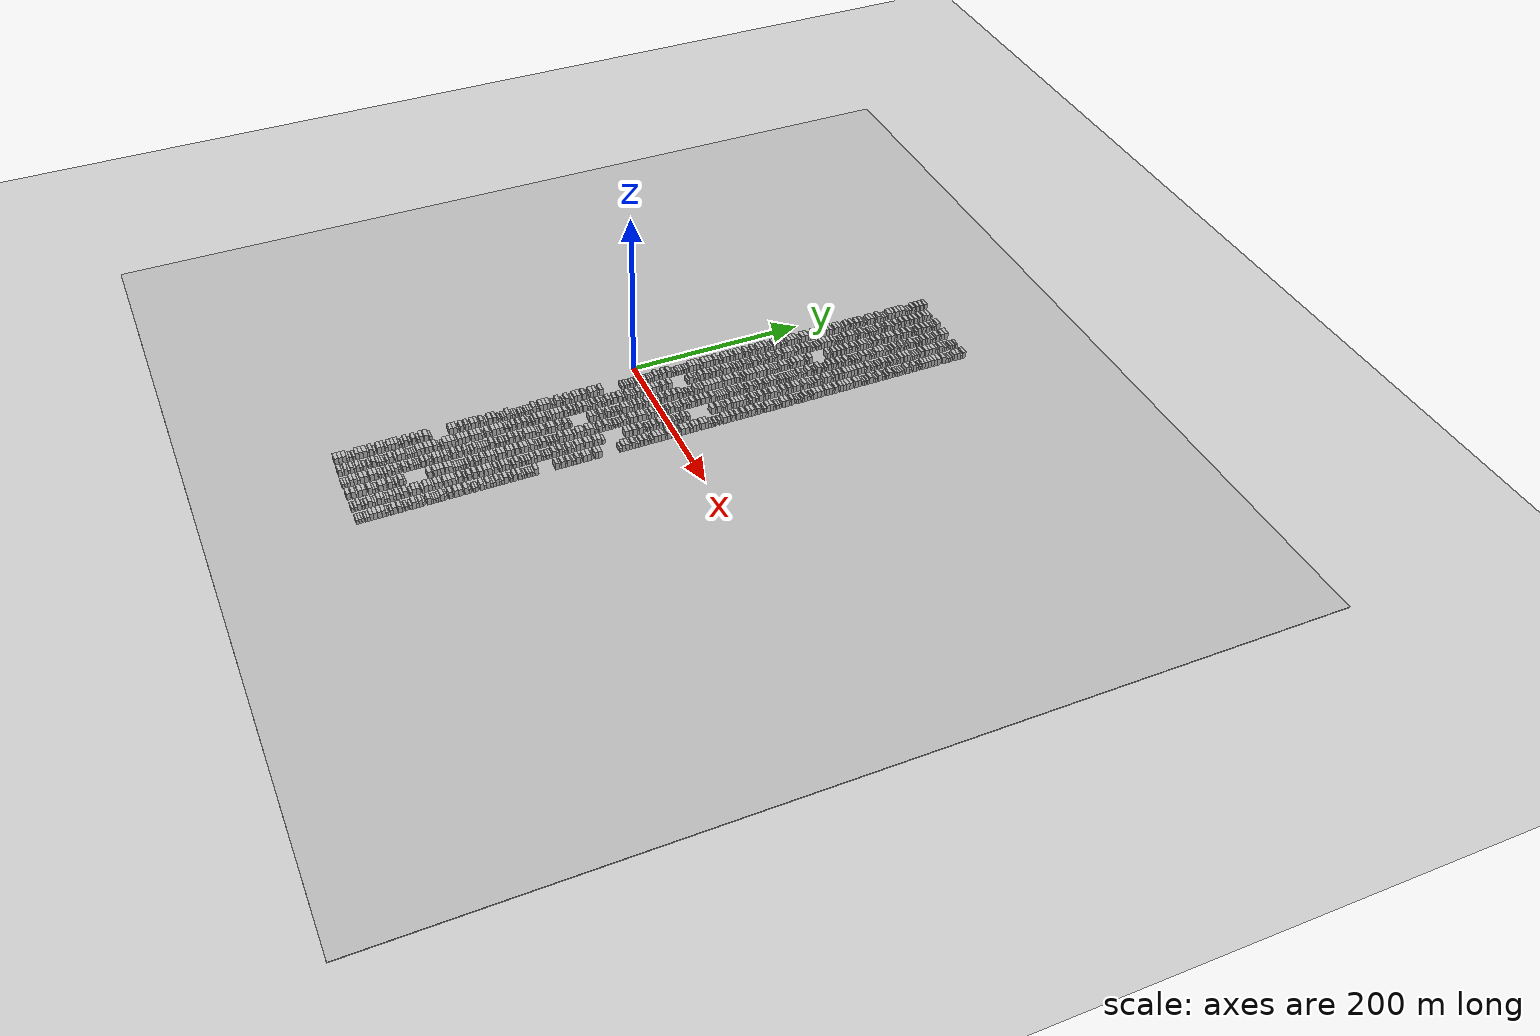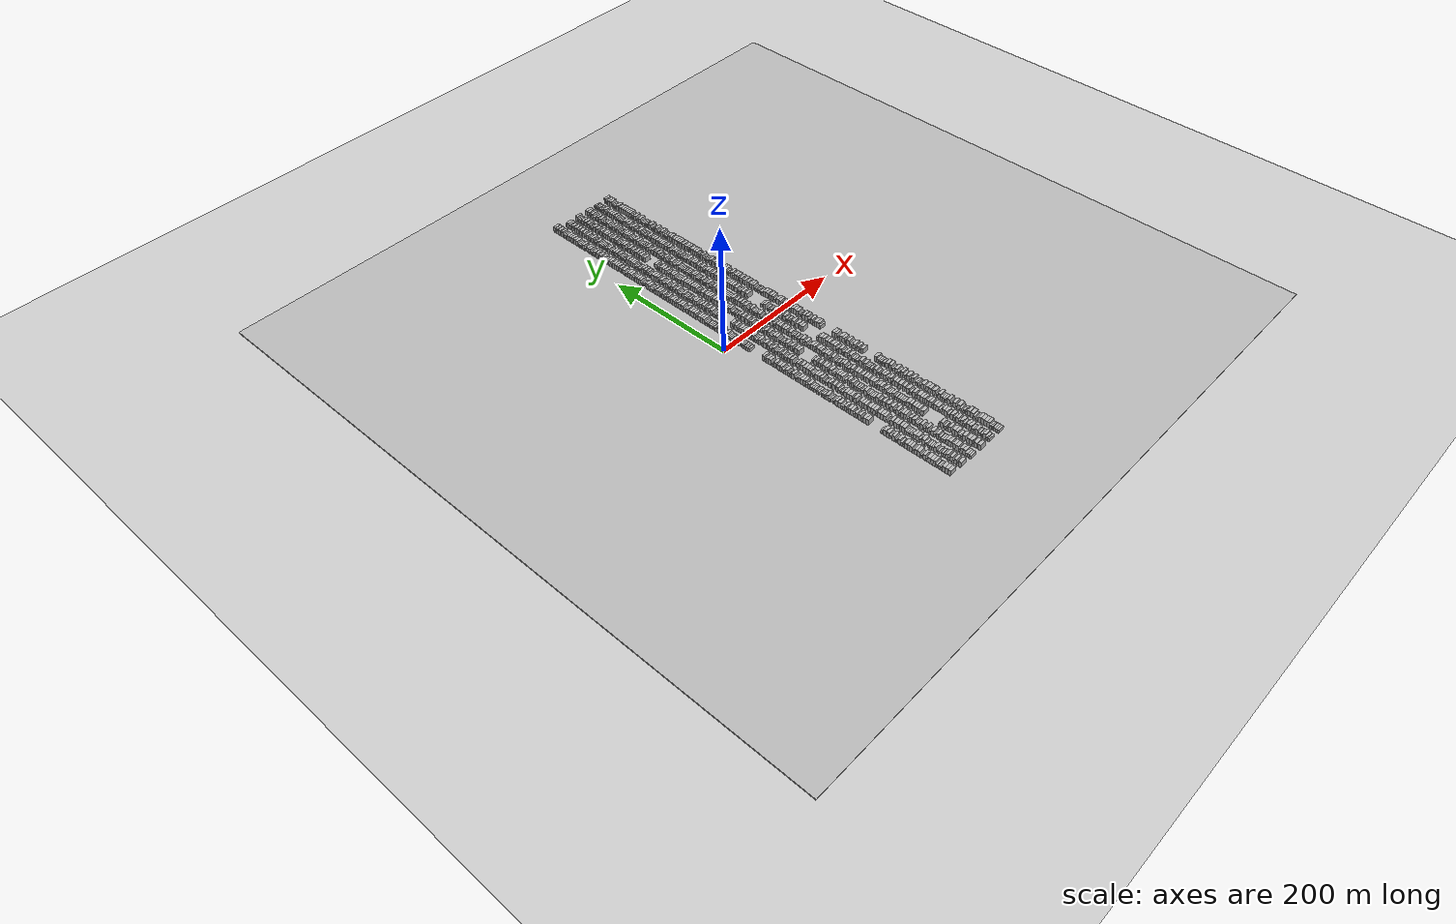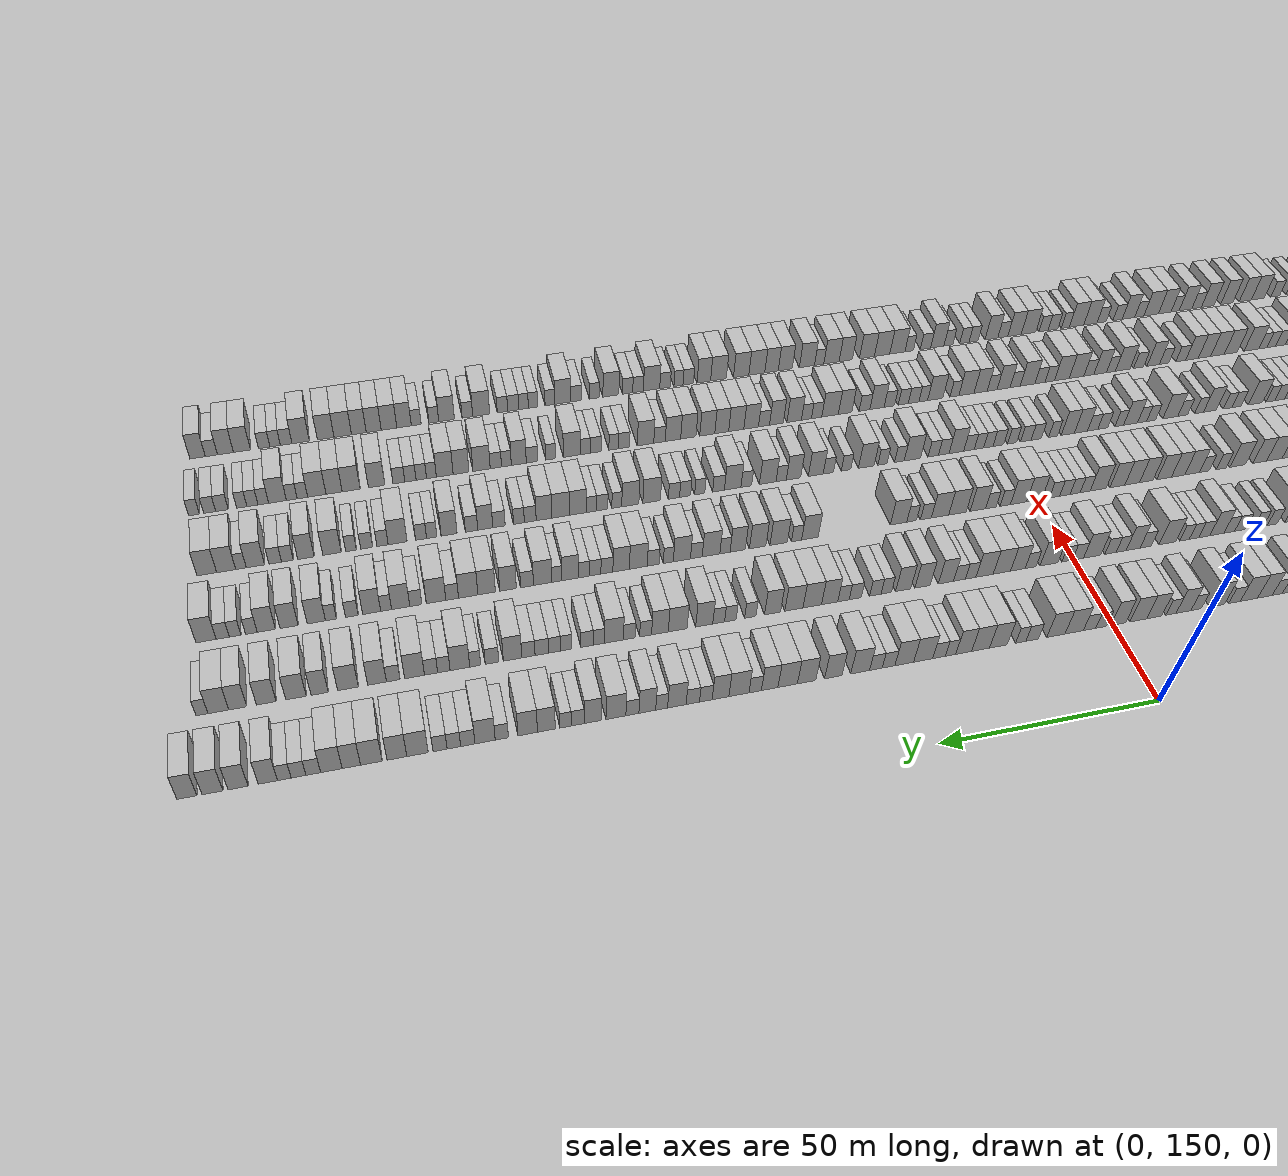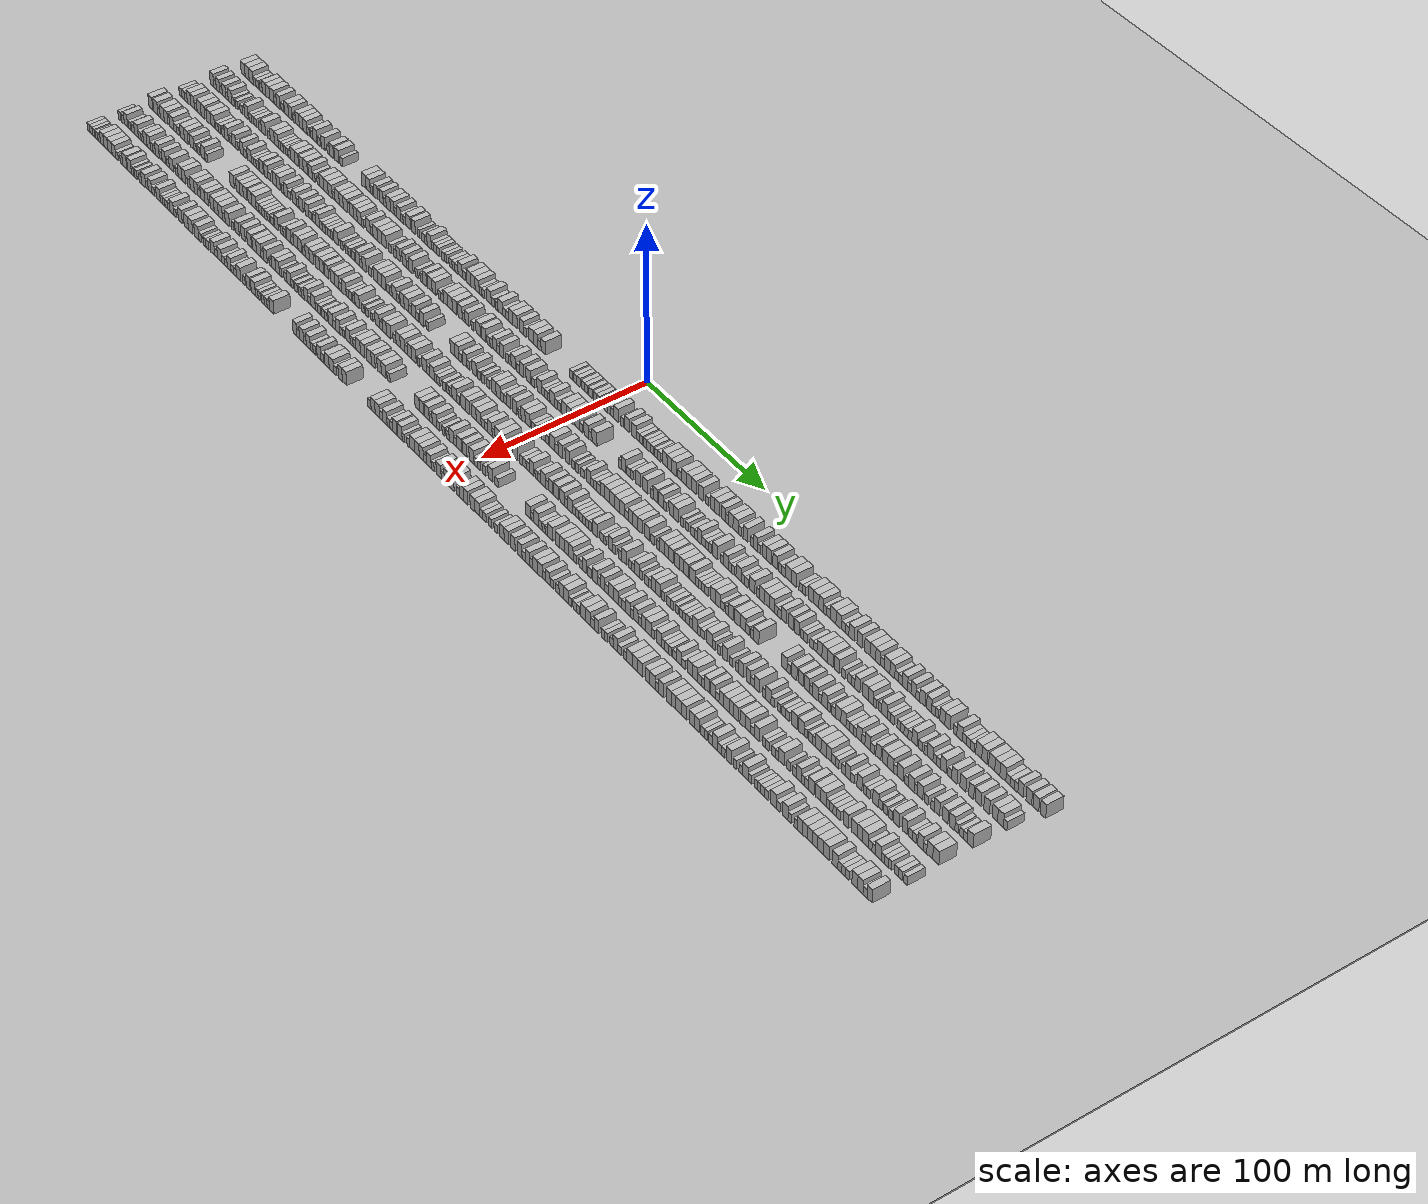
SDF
<?xml version="1.0" encoding="utf-8"?>

<sdf version="1.6">

   <world name="default">

      <gui fullscreen="0">

         <camera name="user_camera">

            <pose>-15 0 4.57585 0 0 0</pose>

            <view_controller>orbit</view_controller>

         </camera>

      </gui>

      <scene>

         <sky>

           <clouds>

             <speed>12</speed>

           </clouds>

         </sky>

         <ambient>0.4 0.4 0.4 1</ambient>

         <background>0.7 0.7 0.7 1</background>

         <shadows>1</shadows>

      </scene>

      <gravity>0 0 -9.8066</gravity>

      <magnetic_field>6e-06 2.3e-05 -4.2e-05</magnetic_field>

      <physics default="0" name="default_physics" type="ode">

         <ode>

            <solver>

               <type>quick</type>

               <iters>10</iters>

               <sor>1.0</sor>

               <use_dynamic_moi_rescaling>0</use_dynamic_moi_rescaling>

            </solver>

            <constraints>

               <cfm>0</cfm>

               <erp>0.2</erp>

               <contact_max_correcting_vel>100</contact_max_correcting_vel>

               <contact_surface_layer>0.001</contact_surface_layer>

            </constraints>

         </ode>

         <max_step_size>0.004</max_step_size>

         <real_time_factor>1</real_time_factor>

         <real_time_update_rate>250</real_time_update_rate>

      </physics>

      <light name="sun" type="directional">

         <cast_shadows>1</cast_shadows>

         <pose>0 0 10 0 0 0</pose>

         <diffuse>0.8 0.8 0.8 1</diffuse>

         <specular>0.2 0.2 0.2 1</specular>

         <attenuation>

            <range>1000</range>

            <constant>0.9</constant>

            <linear>0.01</linear>

            <quadratic>0.001</quadratic>

         </attenuation>

         <direction>-0.5 0.1 -0.9</direction>

      </light>

      <include>

         <name>ground_plane_1</name>

         <uri>model://HANNAS_ground_plane</uri>

         <pose>0 0 0  0 0 0</pose>

      </include>

      <include>

         <name>ground_plane_2</name>

         <uri>model://HANNAS_ground_plane</uri>

         <pose>100 0 0  0 0 0</pose>

      </include>

      <model name="building_1">

         <static>1</static>

         <pose frame="">25.0000 -345.8766 0 0.000000 0.000000 0.000000</pose>

         <link name="link">

            <pose frame="">0 0 4.50 0 0 0</pose>

            <collision name="collision">

               <geometry>

                  <box>

                     <size>10.0000 4.2469 9.0000</size>

                  </box>

               </geometry>

               <max_contacts>10</max_contacts>

               <surface>

                  <contact>

                     <ode/>

                  </contact>

                  <bounce/>

                  <friction>

                     <torsional>

                        <ode/>

                     </torsional>

                     <ode/>

                  </friction>

               </surface>

            </collision>

            <visual name="visual">

               <cast_shadows>0</cast_shadows>

               <geometry>

                  <box>

                     <size>10.0000 4.2469 9.0000</size>

                  </box>

               </geometry>

               <material>

                  <script>

                     <uri>model://HANNAS_wall/materials/scripts</uri>

                     <uri>model://HANNAS_wall/materials/textures</uri>

                     <name>vrc/HANNAS_wall</name>

                  </script>

               </material>

            </visual>

            <self_collide>0</self_collide>

            <enable_wind>0</enable_wind>

            <kinematic>0</kinematic>

         </link>

      </model>

      <model name="building_2">

         <static>1</static>

         <pose frame="">25.0000 -341.6067 0 0.000000 0.000000 0.000000</pose>

         <link name="link">

            <pose frame="">0 0 4.50 0 0 0</pose>

            <collision name="collision">

               <geometry>

                  <box>

                     <size>10.0000 4.2928 9.0000</size>

                  </box>

               </geometry>

               <max_contacts>10</max_contacts>

               <surface>

                  <contact>

                     <ode/>

                  </contact>

                  <bounce/>

                  <friction>

                     <torsional>

                        <ode/>

                     </torsional>

                     <ode/>

                  </friction>

               </surface>

            </collision>

            <visual name="visual">

               <cast_shadows>0</cast_shadows>

               <geometry>

                  <box>

                     <size>10.0000 4.2928 9.0000</size>

                  </box>

               </geometry>

               <material>

                  <script>

                     <uri>model://HANNAS_wall/materials/scripts</uri>

                     <uri>model://HANNAS_wall/materials/textures</uri>

                     <name>vrc/HANNAS_wall</name>

                  </script>

               </material>

            </visual>

            <self_collide>0</self_collide>

            <enable_wind>0</enable_wind>

            <kinematic>0</kinematic>

         </link>

      </model>

      <model name="building_3">

         <static>1</static>

         <pose frame="">25.0000 -337.2736 0 0.000000 0.000000 0.000000</pose>

         <link name="link">

            <pose frame="">0 0 4.50 0 0 0</pose>

            <collision name="collision">

               <geometry>

                  <box>

                     <size>10.0000 4.3734 9.0000</size>

                  </box>

               </geometry>

               <max_contacts>10</max_contacts>

               <surface>

                  <contact>

                     <ode/>

                  </contact>

                  <bounce/>

                  <friction>

                     <torsional>

                        <ode/>

                     </torsional>

                     <ode/>

                  </friction>

               </surface>

            </collision>

            <visual name="visual">

               <cast_shadows>0</cast_shadows>

               <geometry>

                  <box>

                     <size>10.0000 4.3734 9.0000</size>

                  </box>

               </geometry>

               <material>

                  <script>

                     <uri>model://HANNAS_wall/materials/scripts</uri>

                     <uri>model://HANNAS_wall/materials/textures</uri>

                     <name>vrc/HANNAS_wall</name>

                  </script>

               </material>

            </visual>

            <self_collide>0</self_collide>

            <enable_wind>0</enable_wind>

            <kinematic>0</kinematic>

         </link>

      </model>

      <model name="building_4">

         <static>1</static>

         <pose frame="">25.0000 -333.6477 0 0.000000 0.000000 0.000000</pose>

         <link name="link">

            <pose frame="">0 0 3.00 0 0 0</pose>

            <collision name="collision">

               <geometry>

                  <box>

                     <size>10.0000 2.8784 6.0000</size>

                  </box>

               </geometry>

               <max_contacts>10</max_contacts>

               <surface>

                  <contact>

                     <ode/>

                  </contact>

                  <bounce/>

                  <friction>

                     <torsional>

                        <ode/>

                     </torsional>

                     <ode/>

                  </friction>

               </surface>

            </collision>

            <visual name="visual">

               <cast_shadows>0</cast_shadows>

               <geometry>

                  <box>

                     <size>10.0000 2.8784 6.0000</size>

                  </box>

               </geometry>

               <material>

                  <script>

                     <uri>model://HANNAS_wall/materials/scripts</uri>

                     <uri>model://HANNAS_wall/materials/textures</uri>

                     <name>vrc/HANNAS_wall</name>

                  </script>

               </material>

            </visual>

            <self_collide>0</self_collide>

            <enable_wind>0</enable_wind>

            <kinematic>0</kinematic>

         </link>

      </model>

      <model name="building_5">

         <static>1</static>

         <pose frame="">25.0000 -330.8512 0 0.000000 0.000000 0.000000</pose>

         <link name="link">

            <pose frame="">0 0 3.00 0 0 0</pose>

            <collision name="collision">

               <geometry>

                  <box>

                     <size>10.0000 2.7145 6.0000</size>

                  </box>

               </geometry>

               <max_contacts>10</max_contacts>

               <surface>

                  <contact>

                     <ode/>

                  </contact>

                  <bounce/>

                  <friction>

                     <torsional>

                        <ode/>

                     </torsional>

                     <ode/>

                  </friction>

               </surface>

            </collision>

            <visual name="visual">

               <cast_shadows>0</cast_shadows>

               <geometry>

                  <box>

                     <size>10.0000 2.7145 6.0000</size>

                  </box>

               </geometry>

               <material>

                  <script>

                     <uri>model://HANNAS_wall/materials/scripts</uri>

                     <uri>model://HANNAS_wall/materials/textures</uri>

                     <name>vrc/HANNAS_wall</name>

                  </script>

               </material>

            </visual>

            <self_collide>0</self_collide>

            <enable_wind>0</enable_wind>

            <kinematic>0</kinematic>

         </link>

      </model>

      <model name="building_6">

         <static>1</static>

         <pose frame="">25.0000 -327.0143 0 0.000000 0.000000 0.000000</pose>

         <link name="link">

            <pose frame="">0 0 3.00 0 0 0</pose>

            <collision name="collision">

               <geometry>

                  <box>

                     <size>10.0000 2.9593 6.0000</size>

                  </box>

               </geometry>

               <max_contacts>10</max_contacts>

               <surface>

                  <contact>

                     <ode/>

                  </contact>

                  <bounce/>

                  <friction>

                     <torsional>

                        <ode/>

                     </torsional>

                     <ode/>

                  </friction>

               </surface>

            </collision>

            <visual name="visual">

               <cast_shadows>0</cast_shadows>

               <geometry>

                  <box>

                     <size>10.0000 2.9593 6.0000</size>

                  </box>

               </geometry>

               <material>

                  <script>

                     <uri>model://HANNAS_wall/materials/scripts</uri>

                     <uri>model://HANNAS_wall/materials/textures</uri>

                     <name>vrc/HANNAS_wall</name>

                  </script>

               </material>

            </visual>

            <self_collide>0</self_collide>

            <enable_wind>0</enable_wind>

            <kinematic>0</kinematic>

         </link>

      </model>

      <model name="building_7">

         <static>1</static>

         <pose frame="">25.0000 -323.6500 0 0.000000 0.000000 0.000000</pose>

         <link name="link">

            <pose frame="">0 0 4.50 0 0 0</pose>

            <collision name="collision">

               <geometry>

                  <box>

                     <size>10.0000 3.7693 9.0000</size>

                  </box>

               </geometry>

               <max_contacts>10</max_contacts>

               <surface>

                  <contact>

                     <ode/>

                  </contact>

                  <bounce/>

                  <friction>

                     <torsional>

                        <ode/>

                     </torsional>

                     <ode/>

                  </friction>

               </surface>

            </collision>

            <visual name="visual">

               <cast_shadows>0</cast_shadows>

               <geometry>

                  <box>

                     <size>10.0000 3.7693 9.0000</size>

                  </box>

               </geometry>

               <material>

                  <script>

                     <uri>model://HANNAS_wall/materials/scripts</uri>

                     <uri>model://HANNAS_wall/materials/textures</uri>

                     <name>vrc/HANNAS_wall</name>

                  </script>

               </material>

            </visual>

            <self_collide>0</self_collide>

            <enable_wind>0</enable_wind>

            <kinematic>0</kinematic>

         </link>

      </model>

      <model name="building_8">

         <static>1</static>

         <pose frame="">25.0000 -319.6790 0 0.000000 0.000000 0.000000</pose>

         <link name="link">

            <pose frame="">0 0 4.50 0 0 0</pose>

            <collision name="collision">

               <geometry>

                  <box>

                     <size>10.0000 4.1728 9.0000</size>

                  </box>

               </geometry>

               <max_contacts>10</max_contacts>

               <surface>

                  <contact>

                     <ode/>

                  </contact>

                  <bounce/>

                  <friction>

                     <torsional>

                        <ode/>

                     </torsional>

                     <ode/>

                  </friction>

               </surface>

            </collision>

            <visual name="visual">

               <cast_shadows>0</cast_shadows>

               <geometry>

                  <box>

                     <size>10.0000 4.1728 9.0000</size>

                  </box>

               </geometry>

               <material>

                  <script>

                     <uri>model://HANNAS_wall/materials/scripts</uri>

                     <uri>model://HANNAS_wall/materials/textures</uri>

                     <name>vrc/HANNAS_wall</name>

                  </script>

               </material>

            </visual>

            <self_collide>0</self_collide>

            <enable_wind>0</enable_wind>

            <kinematic>0</kinematic>

         </link>

      </model>

      <model name="building_9">

         <static>1</static>

         <pose frame="">25.0000 -315.3548 0 0.000000 0.000000 0.000000</pose>

         <link name="link">

            <pose frame="">0 0 4.50 0 0 0</pose>

            <collision name="collision">

               <geometry>

                  <box>

                     <size>10.0000 4.4757 9.0000</size>

                  </box>

               </geometry>

               <max_contacts>10</max_contacts>

               <surface>

                  <contact>

                     <ode/>

                  </contact>

                  <bounce/>

                  <friction>

                     <torsional>

                        <ode/>

                     </torsional>

                     <ode/>

                  </friction>

               </surface>

            </collision>

            <visual name="visual">

               <cast_shadows>0</cast_shadows>

               <geometry>

                  <box>

                     <size>10.0000 4.4757 9.0000</size>

                  </box>

               </geometry>

               <material>

                  <script>

                     <uri>model://HANNAS_wall/materials/scripts</uri>

                     <uri>model://HANNAS_wall/materials/textures</uri>

                     <name>vrc/HANNAS_wall</name>

                  </script>

               </material>

            </visual>

            <self_collide>0</self_collide>

            <enable_wind>0</enable_wind>

            <kinematic>0</kinematic>

         </link>

      </model>

      <model name="building_10">

         <static>1</static>

         <pose frame="">25.0000 -311.8194 0 0.000000 0.000000 0.000000</pose>

         <link name="link">

            <pose frame="">0 0 3.00 0 0 0</pose>

            <collision name="collision">

               <geometry>

                  <box>

                     <size>10.0000 2.5950 6.0000</size>

                  </box>

               </geometry>

               <max_contacts>10</max_contacts>

               <surface>

                  <contact>

                     <ode/>

                  </contact>

                  <bounce/>

                  <friction>

                     <torsional>

                        <ode/>

                     </torsional>

                     <ode/>

                  </friction>

               </surface>

            </collision>

            <visual name="visual">

               <cast_shadows>0</cast_shadows>

               <geometry>

                  <box>

                     <size>10.0000 2.5950 6.0000</size>

                  </box>

               </geometry>

               <material>

                  <script>

                     <uri>model://HANNAS_wall/materials/scripts</uri>

                     <uri>model://HANNAS_wall/materials/textures</uri>

                     <name>vrc/HANNAS_wall</name>

                  </script>

               </material>

            </visual>

            <self_collide>0</self_collide>

            <enable_wind>0</enable_wind>

            <kinematic>0</kinematic>

         </link>

      </model>

      <model name="building_11">

         <static>1</static>

         <pose frame="">25.0000 -308.6441 0 0.000000 0.000000 0.000000</pose>

         <link name="link">

            <pose frame="">0 0 4.50 0 0 0</pose>

            <collision name="collision">

               <geometry>

                  <box>

                     <size>10.0000 3.7557 9.0000</size>

                  </box>

               </geometry>

               <max_contacts>10</max_contacts>

               <surface>

                  <contact>

                     <ode/>

                  </contact>

                  <bounce/>

                  <friction>

                     <torsional>

                        <ode/>

                     </torsional>

                     <ode/>

                  </friction>

               </surface>

            </collision>

            <visual name="visual">

               <cast_shadows>0</cast_shadows>

               <geometry>

                  <box>

                     <size>10.0000 3.7557 9.0000</size>

                  </box>

               </geometry>

               <material>

                  <script>

                     <uri>model://HANNAS_wall/materials/scripts</uri>

                     <uri>model://HANNAS_wall/materials/textures</uri>

                     <name>vrc/HANNAS_wall</name>

                  </script>

               </material>

            </visual>

            <self_collide>0</self_collide>

            <enable_wind>0</enable_wind>

            <kinematic>0</kinematic>

         </link>

      </model>

      <model name="building_12">

         <static>1</static>

         <pose frame="">25.0000 -304.4609 0 0.000000 0.000000 0.000000</pose>

         <link name="link">

            <pose frame="">0 0 3.00 0 0 0</pose>

            <collision name="collision">

               <geometry>

                  <box>

                     <size>10.0000 2.6108 6.0000</size>

                  </box>

               </geometry>

               <max_contacts>10</max_contacts>

               <surface>

                  <contact>

                     <ode/>

                  </contact>

                  <bounce/>

                  <friction>

                     <torsional>

                        <ode/>

                     </torsional>

                     <ode/>

                  </friction>

               </surface>

            </collision>

            <visual name="visual">

               <cast_shadows>0</cast_shadows>

               <geometry>

                  <box>

                     <size>10.0000 2.6108 6.0000</size>

                  </box>

               </geometry>

               <material>

                  <script>

                     <uri>model://HANNAS_wall/materials/scripts</uri>

                     <uri>model://HANNAS_wall/materials/textures</uri>

                     <name>vrc/HANNAS_wall</name>

                  </script>

               </material>

            </visual>

            <self_collide>0</self_collide>

            <enable_wind>0</enable_wind>

            <kinematic>0</kinematic>

         </link>

      </model>

      <model name="building_13">

         <static>1</static>

         <pose frame="">25.0000 -299.9994 0 0.000000 0.000000 0.000000</pose>

         <link name="link">

            <pose frame="">0 0 4.50 0 0 0</pose>

            <collision name="collision">

               <geometry>

                  <box>

                     <size>10.0000 4.3122 9.0000</size>

                  </box>

               </geometry>

               <max_contacts>10</max_contacts>

               <surface>

                  <contact>

                     <ode/>

                  </contact>

                  <bounce/>

                  <friction>

                     <torsional>

                        <ode/>

                     </torsional>

                     <ode/>

                  </friction>

               </surface>

            </collision>

            <visual name="visual">

               <cast_shadows>0</cast_shadows>

               <geometry>

                  <box>

                     <size>10.0000 4.3122 9.0000</size>

                  </box>

               </geometry>

               <material>

                  <script>

                     <uri>model://HANNAS_wall/materials/scripts</uri>

                     <uri>model://HANNAS_wall/materials/textures</uri>

                     <name>vrc/HANNAS_wall</name>

                  </script>

               </material>

            </visual>

            <self_collide>0</self_collide>

            <enable_wind>0</enable_wind>

            <kinematic>0</kinematic>

         </link>

      </model>

      <model name="building_14">

         <static>1</static>

         <pose frame="">25.0000 -296.0288 0 0.000000 0.000000 0.000000</pose>

         <link name="link">

            <pose frame="">0 0 4.50 0 0 0</pose>

            <collision name="collision">

               <geometry>

                  <box>

                     <size>10.0000 3.6291 9.0000</size>

                  </box>

               </geometry>

               <max_contacts>10</max_contacts>

               <surface>

                  <contact>

                     <ode/>

                  </contact>

                  <bounce/>

                  <friction>

                     <torsional>

                        <ode/>

                     </torsional>

                     <ode/>

                  </friction>

               </surface>

            </collision>

            <visual name="visual">

               <cast_shadows>0</cast_shadows>

               <geometry>

                  <box>

                     <size>10.0000 3.6291 9.0000</size>

                  </box>

               </geometry>

               <material>

                  <script>

                     <uri>model://HANNAS_wall/materials/scripts</uri>

                     <uri>model://HANNAS_wall/materials/textures</uri>

                     <name>vrc/HANNAS_wall</name>

                  </script>

               </material>

            </visual>

            <self_collide>0</self_collide>

            <enable_wind>0</enable_wind>

            <kinematic>0</kinematic>

         </link>

      </model>

      <model name="building_15">

         <static>1</static>

         <pose frame="">25.0000 -291.9321 0 0.000000 0.000000 0.000000</pose>

         <link name="link">

            <pose frame="">0 0 3.00 0 0 0</pose>

            <collision name="collision">

               <geometry>

                  <box>

                     <size>10.0000 2.5641 6.0000</size>

                  </box>

               </geometry>

               <max_contacts>10</max_contacts>

               <surface>

                  <contact>

                     <ode/>

                  </contact>

                  <bounce/>

                  <friction>

                     <torsional>

                        <ode/>

                     </torsional>

                     <ode/>

                  </friction>

               </surface>

            </collision>

            <visual name="visual">

               <cast_shadows>0</cast_shadows>

               <geometry>

                  <box>

                     <size>10.0000 2.5641 6.0000</size>

                  </box>

               </geometry>

               <material>

                  <script>

                     <uri>model://HANNAS_wall/materials/scripts</uri>

                     <uri>model://HANNAS_wall/materials/textures</uri>

                     <name>vrc/HANNAS_wall</name>

                  </script>

               </material>

            </visual>

            <self_collide>0</self_collide>

            <enable_wind>0</enable_wind>

            <kinematic>0</kinematic>

         </link>

      </model>

      <model name="building_16">

         <static>1</static>

         <pose frame="">25.0000 -288.7070 0 0.000000 0.000000 0.000000</pose>

         <link name="link">

            <pose frame="">0 0 4.50 0 0 0</pose>

            <collision name="collision">

               <geometry>

                  <box>

                     <size>10.0000 3.8862 9.0000</size>

                  </box>

               </geometry>

               <max_contacts>10</max_contacts>

               <surface>

                  <contact>

                     <ode/>

                  </contact>

                  <bounce/>

                  <friction>

                     <torsional>

                        <ode/>

                     </torsional>

                     <ode/>

                  </friction>

               </surface>

            </collision>

            <visual name="visual">

               <cast_shadows>0</cast_shadows>

               <geometry>

                  <box>

                     <size>10.0000 3.8862 9.0000</size>

                  </box>

               </geometry>

               <material>

                  <script>

                     <uri>model://HANNAS_wall/materials/scripts</uri>

                     <uri>model://HANNAS_wall/materials/textures</uri>

                     <name>vrc/HANNAS_wall</name>

                  </script>

               </material>

            </visual>

            <self_collide>0</self_collide>

            <enable_wind>0</enable_wind>

            <kinematic>0</kinematic>

         </link>

      </model>

      <model name="building_17">

         <static>1</static>

         <pose frame="">25.0000 -284.8206 0 0.000000 0.000000 0.000000</pose>

         <link name="link">

            <pose frame="">0 0 4.50 0 0 0</pose>

            <collision name="collision">

               <geometry>

                  <box>

                     <size>10.0000 3.8864 9.0000</size>

                  </box>

               </geometry>

               <max_contacts>10</max_contacts>

               <surface>

                  <contact>

                     <ode/>

                  </contact>

                  <bounce/>

                  <friction>

                     <torsional>

                        <ode/>

                     </torsional>

                     <ode/>

                  </friction>

               </surface>

            </collision>

            <visual name="visual">

               <cast_shadows>0</cast_shadows>

               <geometry>

                  <box>

                     <size>10.0000 3.8864 9.0000</size>

                  </box>

               </geometry>

               <material>

                  <script>

                     <uri>model://HANNAS_wall/materials/scripts</uri>

                     <uri>model://HANNAS_wall/materials/textures</uri>

                     <name>vrc/HANNAS_wall</name>

                  </script>

               </material>

            </visual>

            <self_collide>0</self_collide>

            <enable_wind>0</enable_wind>

            <kinematic>0</kinematic>

         </link>

      </model>

      <model name="building_18">

         <static>1</static>

         <pose frame="">25.0000 -280.8364 0 0.000000 0.000000 0.000000</pose>

         <link name="link">

            <pose frame="">0 0 4.50 0 0 0</pose>

            <collision name="collision">

               <geometry>

                  <box>

                     <size>10.0000 4.0821 9.0000</size>

                  </box>

               </geometry>

               <max_contacts>10</max_contacts>

               <surface>

                  <contact>

                     <ode/>

                  </contact>

                  <bounce/>

                  <friction>

                     <torsional>

                        <ode/>

                     </torsional>

                     <ode/>

                  </friction>

               </surface>

            </collision>

            <visual name="visual">

               <cast_shadows>0</cast_shadows>

               <geometry>

                  <box>

                     <size>10.0000 4.0821 9.0000</size>

                  </box>

               </geometry>

               <material>

                  <script>

                     <uri>model://HANNAS_wall/materials/scripts</uri>

                     <uri>model://HANNAS_wall/materials/textures</uri>

                     <name>vrc/HANNAS_wall</name>

                  </script>

               </material>

            </visual>

            <self_collide>0</self_collide>

            <enable_wind>0</enable_wind>

            <kinematic>0</kinematic>

         </link>

      </model>

      <model name="building_19">

         <static>1</static>

         <pose frame="">25.0000 -277.5818 0 0.000000 0.000000 0.000000</pose>

         <link name="link">

            <pose frame="">0 0 3.00 0 0 0</pose>

            <collision name="collision">

               <geometry>

                  <box>

                     <size>10.0000 2.4271 6.0000</size>

                  </box>

               </geometry>

               <max_contacts>10</max_contacts>

               <surface>

                  <contact>

                     <ode/>

                  </contact>

                  <bounce/>

                  <friction>

                     <torsional>

                        <ode/>

                     </torsional>

                     <ode/>

                  </friction>

               </surface>

            </collision>

            <visual name="visual">

               <cast_shadows>0</cast_shadows>

               <geometry>

                  <box>

                     <size>10.0000 2.4271 6.0000</size>

                  </box>

               </geometry>

               <material>

                  <script>

                     <uri>model://HANNAS_wall/materials/scripts</uri>

                     <uri>model://HANNAS_wall/materials/textures</uri>

                     <name>vrc/HANNAS_wall</name>

                  </script>

               </material>

            </visual>

            <self_collide>0</self_collide>

            <enable_wind>0</enable_wind>

            <kinematic>0</kinematic>

         </link>

      </model>

      <model name="building_20">

         <static>1</static>

         <pose frame="">25.0000 -274.0296 0 0.000000 0.000000 0.000000</pose>

         <link name="link">

            <pose frame="">0 0 3.00 0 0 0</pose>

            <collision name="collision">

               <geometry>

                  <box>

                     <size>10.0000 2.6774 6.0000</size>

                  </box>

               </geometry>

               <max_contacts>10</max_contacts>

               <surface>

                  <contact>

                     <ode/>

                  </contact>

                  <bounce/>

                  <friction>

                     <torsional>

                        <ode/>

                     </torsional>

                     <ode/>

                  </friction>

               </surface>

            </collision>

            <visual name="visual">

               <cast_shadows>0</cast_shadows>

               <geometry>

                  <box>

                     <size>10.0000 2.6774 6.0000</size>

                  </box>

               </geometry>

               <material>

                  <script>

                     <uri>model://HANNAS_wall/materials/scripts</uri>

                     <uri>model://HANNAS_wall/materials/textures</uri>

                     <name>vrc/HANNAS_wall</name>

                  </script>

               </material>

            </visual>

            <self_collide>0</self_collide>

            <enable_wind>0</enable_wind>

            <kinematic>0</kinematic>

         </link>

      </model>

      <model name="building_21">

         <static>1</static>

         <pose frame="">25.0000 -270.6690 0 0.000000 0.000000 0.000000</pose>

         <link name="link">

            <pose frame="">0 0 4.50 0 0 0</pose>

            <collision name="collision">

               <geometry>

                  <box>

                     <size>10.0000 4.0437 9.0000</size>

                  </box>

               </geometry>

               <max_contacts>10</max_contacts>

               <surface>

                  <contact>

                     <ode/>

                  </contact>

                  <bounce/>

                  <friction>

                     <torsional>

                        <ode/>

                     </torsional>

                     <ode/>

                  </friction>

               </surface>

            </collision>

            <visual name="visual">

               <cast_shadows>0</cast_shadows>

               <geometry>

                  <box>

                     <size>10.0000 4.0437 9.0000</size>

                  </box>

               </geometry>

               <material>

                  <script>

                     <uri>model://HANNAS_wall/materials/scripts</uri>

                     <uri>model://HANNAS_wall/materials/textures</uri>

                     <name>vrc/HANNAS_wall</name>

                  </script>

               </material>

            </visual>

            <self_collide>0</self_collide>

            <enable_wind>0</enable_wind>

            <kinematic>0</kinematic>

         </link>

      </model>

      <model name="building_22">

         <static>1</static>

         <pose frame="">25.0000 -266.4008 0 0.000000 0.000000 0.000000</pose>

         <link name="link">

            <pose frame="">0 0 3.00 0 0 0</pose>

            <collision name="collision">

               <geometry>

                  <box>

                     <size>10.0000 2.4927 6.0000</size>

                  </box>

               </geometry>

               <max_contacts>10</max_contacts>

               <surface>

                  <contact>

                     <ode/>

                  </contact>

                  <bounce/>

                  <friction>

                     <torsional>

                        <ode/>

                     </torsional>

                     <ode/>

                  </friction>

               </surface>

            </collision>

            <visual name="visual">

               <cast_shadows>0</cast_shadows>

               <geometry>

                  <box>

                     <size>10.0000 2.4927 6.0000</size>

                  </box>

               </geometry>

               <material>

                  <script>

                     <uri>model://HANNAS_wall/materials/scripts</uri>

                     <uri>model://HANNAS_wall/materials/textures</uri>

                     <name>vrc/HANNAS_wall</name>

                  </script>

               </material>

            </visual>

            <self_collide>0</self_collide>

            <enable_wind>0</enable_wind>

            <kinematic>0</kinematic>

         </link>

      </model>

      <model name="building_23">

         <static>1</static>

         <pose frame="">25.0000 -262.2214 0 0.000000 0.000000 0.000000</pose>

         <link name="link">

            <pose frame="">0 0 4.50 0 0 0</pose>

            <collision name="collision">

               <geometry>

                  <box>

                     <size>10.0000 3.8660 9.0000</size>

                  </box>

               </geometry>

               <max_contacts>10</max_contacts>

               <surface>

                  <contact>

                     <ode/>

                  </contact>

                  <bounce/>

                  <friction>

                     <torsional>

                        <ode/>

                     </torsional>

                     <ode/>

                  </friction>

               </surface>

            </collision>

            <visual name="visual">

               <cast_shadows>0</cast_shadows>

               <geometry>

                  <box>

                     <size>10.0000 3.8660 9.0000</size>

                  </box>

               </geometry>

               <material>

                  <script>

                     <uri>model://HANNAS_wall/materials/scripts</uri>

                     <uri>model://HANNAS_wall/materials/textures</uri>

                     <name>vrc/HANNAS_wall</name>

                  </script>

               </material>

            </visual>

            <self_collide>0</self_collide>

            <enable_wind>0</enable_wind>

            <kinematic>0</kinematic>

         </link>

      </model>

      <model name="building_24">

         <static>1</static>

         <pose frame="">25.0000 -256.9810 0 0.000000 0.000000 0.000000</pose>

         <link name="link">

            <pose frame="">0 0 3.00 0 0 0</pose>

            <collision name="collision">

               <geometry>

                  <box>

                     <size>10.0000 2.6148 6.0000</size>

                  </box>

               </geometry>

               <max_contacts>10</max_contacts>

               <surface>

                  <contact>

                     <ode/>

                  </contact>

                  <bounce/>

                  <friction>

                     <torsional>

                        <ode/>

                     </torsional>

                     <ode/>

                  </friction>

               </surface>

            </collision>

            <visual name="visual">

               <cast_shadows>0</cast_shadows>

               <geometry>

                  <box>

                     <size>10.0000 2.6148 6.0000</size>

                  </box>

               </geometry>

               <material>

                  <script>

                     <uri>model://HANNAS_wall/materials/scripts</uri>

                     <uri>model://HANNAS_wall/materials/textures</uri>

                     <name>vrc/HANNAS_wall</name>

                  </script>

               </material>

            </visual>

            <self_collide>0</self_collide>

            <enable_wind>0</enable_wind>

            <kinematic>0</kinematic>

         </link>

      </model>

      <model name="building_25">

         <static>1</static>

         <pose frame="">25.0000 -253.6319 0 0.000000 0.000000 0.000000</pose>

         <link name="link">

            <pose frame="">0 0 4.50 0 0 0</pose>

            <collision name="collision">

               <geometry>

                  <box>

                     <size>10.0000 4.0835 9.0000</size>

                  </box>

               </geometry>

               <max_contacts>10</max_contacts>

               <surface>

                  <contact>

                     <ode/>

                  </contact>

                  <bounce/>

                  <friction>

                     <torsional>

                        <ode/>

                     </torsional>

                     <ode/>

                  </friction>

               </surface>

            </collision>

            <visual name="visual">

               <cast_shadows>0</cast_shadows>

               <geometry>

                  <box>

                     <size>10.0000 4.0835 9.0000</size>

                  </box>

               </geometry>

               <material>

                  <script>

                     <uri>model://HANNAS_wall/materials/scripts</uri>

                     <uri>model://HANNAS_wall/materials/textures</uri>

                     <name>vrc/HANNAS_wall</name>

                  </script>

               </material>

            </visual>

            <self_collide>0</self_collide>

            <enable_wind>0</enable_wind>

            <kinematic>0</kinematic>

         </link>

      </model>

      <model name="building_26">

         <static>1</static>

         <pose frame="">25.0000 -248.3476 0 0.000000 0.000000 0.000000</pose>

         <link name="link">

            <pose frame="">0 0 4.50 0 0 0</pose>

            <collision name="collision">

               <geometry>

                  <box>

                     <size>10.0000 4.4850 9.0000</size>

                  </box>

               </geometry>

               <max_contacts>10</max_contacts>

               <surface>

                  <contact>

                     <ode/>

                  </contact>

                  <bounce/>

                  <friction>

                     <torsional>

                        <ode/>

                     </torsional>

                     <ode/>

                  </friction>

               </surface>

            </collision>

            <visual name="visual">

               <cast_shadows>0</cast_shadows>

               <geometry>

                  <box>

                     <size>10.0000 4.4850 9.0000</size>

                  </box>

               </geometry>

               <material>

                  <script>

                     <uri>model://HANNAS_wall/materials/scripts</uri>

                     <uri>model://HANNAS_wall/materials/textures</uri>

                     <name>vrc/HANNAS_wall</name>

                  </script>

               </material>

            </visual>

            <self_collide>0</self_collide>

            <enable_wind>0</enable_wind>

            <kinematic>0</kinematic>

         </link>

      </model>

      <model name="building_27">

         <static>1</static>

         <pose frame="">25.0000 -243.8328 0 0.000000 0.000000 0.000000</pose>

         <link name="link">

            <pose frame="">0 0 3.00 0 0 0</pose>

            <collision name="collision">

               <geometry>

                  <box>

                     <size>10.0000 2.5447 6.0000</size>

                  </box>

               </geometry>

               <max_contacts>10</max_contacts>

               <surface>

                  <contact>

                     <ode/>

                  </contact>

                  <bounce/>

                  <friction>

                     <torsional>

                        <ode/>

                     </torsional>

                     <ode/>

                  </friction>

               </surface>

            </collision>

            <visual name="visual">

               <cast_shadows>0</cast_shadows>

               <geometry>

                  <box>

                     <size>10.0000 2.5447 6.0000</size>

                  </box>

               </geometry>

               <material>

                  <script>

                     <uri>model://HANNAS_wall/materials/scripts</uri>

                     <uri>model://HANNAS_wall/materials/textures</uri>

                     <name>vrc/HANNAS_wall</name>

                  </script>

               </material>

            </visual>

            <self_collide>0</self_collide>

            <enable_wind>0</enable_wind>

            <kinematic>0</kinematic>

         </link>

      </model>

      <model name="building_28">

         <static>1</static>

         <pose frame="">25.0000 -221.0363 0 0.000000 0.000000 0.000000</pose>

         <link name="link">

            <pose frame="">0 0 4.50 0 0 0</pose>

            <collision name="collision">

               <geometry>

                  <box>

                     <size>10.0000 4.3495 9.0000</size>

                  </box>

               </geometry>

               <max_contacts>10</max_contacts>

               <surface>

                  <contact>

                     <ode/>

                  </contact>

                  <bounce/>

                  <friction>

                     <torsional>

                        <ode/>

                     </torsional>

                     <ode/>

                  </friction>

               </surface>

            </collision>

            <visual name="visual">

               <cast_shadows>0</cast_shadows>

               <geometry>

                  <box>

                     <size>10.0000 4.3495 9.0000</size>

                  </box>

               </geometry>

               <material>

                  <script>

                     <uri>model://HANNAS_wall/materials/scripts</uri>

                     <uri>model://HANNAS_wall/materials/textures</uri>

                     <name>vrc/HANNAS_wall</name>

                  </script>

               </material>

            </visual>

            <self_collide>0</self_collide>

            <enable_wind>0</enable_wind>

            <kinematic>0</kinematic>

         </link>

      </model>

      <model name="building_29">

         <static>1</static>

         <pose frame="">25.0000 -216.8001 0 0.000000 0.000000 0.000000</pose>

         <link name="link">

            <pose frame="">0 0 4.50 0 0 0</pose>

            <collision name="collision">

               <geometry>

                  <box>

                     <size>10.0000 4.1228 9.0000</size>

                  </box>

               </geometry>

               <max_contacts>10</max_contacts>

               <surface>

                  <contact>

                     <ode/>

                  </contact>

                  <bounce/>

                  <friction>

                     <torsional>

                        <ode/>

                     </torsional>

                     <ode/>

                  </friction>

               </surface>

            </collision>

            <visual name="visual">

               <cast_shadows>0</cast_shadows>

               <geometry>

                  <box>

                     <size>10.0000 4.1228 9.0000</size>

                  </box>

               </geometry>

               <material>

                  <script>

                     <uri>model://HANNAS_wall/materials/scripts</uri>

                     <uri>model://HANNAS_wall/materials/textures</uri>

                     <name>vrc/HANNAS_wall</name>

                  </script>

               </material>

            </visual>

            <self_collide>0</self_collide>

            <enable_wind>0</enable_wind>

            <kinematic>0</kinematic>

         </link>

      </model>

      <model name="building_30">

         <static>1</static>

         <pose frame="">25.0000 -213.4665 0 0.000000 0.000000 0.000000</pose>

         <link name="link">

            <pose frame="">0 0 3.00 0 0 0</pose>

            <collision name="collision">

               <geometry>

                  <box>

                     <size>10.0000 2.5444 6.0000</size>

                  </box>

               </geometry>

               <max_contacts>10</max_contacts>

               <surface>

                  <contact>

                     <ode/>

                  </contact>

                  <bounce/>

                  <friction>

                     <torsional>

                        <ode/>

                     </torsional>

                     <ode/>

                  </friction>

               </surface>

            </collision>

            <visual name="visual">

               <cast_shadows>0</cast_shadows>

               <geometry>

                  <box>

                     <size>10.0000 2.5444 6.0000</size>

                  </box>

               </geometry>

               <material>

                  <script>

                     <uri>model://HANNAS_wall/materials/scripts</uri>

                     <uri>model://HANNAS_wall/materials/textures</uri>

                     <name>vrc/HANNAS_wall</name>

                  </script>

               </material>

            </visual>

            <self_collide>0</self_collide>

            <enable_wind>0</enable_wind>

            <kinematic>0</kinematic>

         </link>

      </model>

      <model name="building_31">

         <static>1</static>

         <pose frame="">25.0000 -209.2966 0 0.000000 0.000000 0.000000</pose>

         <link name="link">

            <pose frame="">0 0 4.50 0 0 0</pose>

            <collision name="collision">

               <geometry>

                  <box>

                     <size>10.0000 3.7954 9.0000</size>

                  </box>

               </geometry>

               <max_contacts>10</max_contacts>

               <surface>

                  <contact>

                     <ode/>

                  </contact>

                  <bounce/>

                  <friction>

                     <torsional>

                        <ode/>

                     </torsional>

                     <ode/>

                  </friction>

               </surface>

            </collision>

            <visual name="visual">

               <cast_shadows>0</cast_shadows>

               <geometry>

                  <box>

                     <size>10.0000 3.7954 9.0000</size>

                  </box>

               </geometry>

               <material>

                  <script>

                     <uri>model://HANNAS_wall/materials/scripts</uri>

                     <uri>model://HANNAS_wall/materials/textures</uri>

                     <name>vrc/HANNAS_wall</name>

                  </script>

               </material>

            </visual>

            <self_collide>0</self_collide>

            <enable_wind>0</enable_wind>

            <kinematic>0</kinematic>

         </link>

      </model>

      <model name="building_32">

         <static>1</static>

         <pose frame="">25.0000 -203.5604 0 0.000000 0.000000 0.000000</pose>

         <link name="link">

            <pose frame="">0 0 4.50 0 0 0</pose>

            <collision name="collision">

               <geometry>

                  <box>

                     <size>10.0000 3.6770 9.0000</size>

                  </box>

               </geometry>

               <max_contacts>10</max_contacts>

               <surface>

                  <contact>

                     <ode/>

                  </contact>

                  <bounce/>

                  <friction>

                     <torsional>

                        <ode/>

                     </torsional>

                     <ode/>

                  </friction>

               </surface>

            </collision>

            <visual name="visual">

               <cast_shadows>0</cast_shadows>

               <geometry>

                  <box>

                     <size>10.0000 3.6770 9.0000</size>

                  </box>

               </geometry>

               <material>

                  <script>

                     <uri>model://HANNAS_wall/materials/scripts</uri>

                     <uri>model://HANNAS_wall/materials/textures</uri>

                     <name>vrc/HANNAS_wall</name>

                  </script>

               </material>

            </visual>

            <self_collide>0</self_collide>

            <enable_wind>0</enable_wind>

            <kinematic>0</kinematic>

         </link>

      </model>

      <model name="building_33">

         <static>1</static>

         <pose frame="">25.0000 -200.2740 0 0.000000 0.000000 0.000000</pose>

         <link name="link">

            <pose frame="">0 0 3.00 0 0 0</pose>

            <collision name="collision">

               <geometry>

                  <box>

                     <size>10.0000 2.8956 6.0000</size>

                  </box>

               </geometry>

               <max_contacts>10</max_contacts>

               <surface>

                  <contact>

                     <ode/>

                  </contact>

                  <bounce/>

                  <friction>

                     <torsional>

                        <ode/>

                     </torsional>

                     <ode/>

                  </friction>

               </surface>

            </collision>

            <visual name="visual">

               <cast_shadows>0</cast_shadows>

               <geometry>

                  <box>

                     <size>10.0000 2.8956 6.0000</size>

                  </box>

               </geometry>

               <material>

                  <script>

                     <uri>model://HANNAS_wall/materials/scripts</uri>

                     <uri>model://HANNAS_wall/materials/textures</uri>

                     <name>vrc/HANNAS_wall</name>

                  </script>

               </material>

            </visual>

            <self_collide>0</self_collide>

            <enable_wind>0</enable_wind>

            <kinematic>0</kinematic>

         </link>

      </model>

      <model name="building_34">

         <static>1</static>

         <pose frame="">25.0000 -196.7236 0 0.000000 0.000000 0.000000</pose>

         <link name="link">

            <pose frame="">0 0 4.50 0 0 0</pose>

            <collision name="collision">

               <geometry>

                  <box>

                     <size>10.0000 4.2052 9.0000</size>

                  </box>

               </geometry>

               <max_contacts>10</max_contacts>

               <surface>

                  <contact>

                     <ode/>

                  </contact>

                  <bounce/>

                  <friction>

                     <torsional>

                        <ode/>

                     </torsional>

                     <ode/>

                  </friction>

               </surface>

            </collision>

            <visual name="visual">

               <cast_shadows>0</cast_shadows>

               <geometry>

                  <box>

                     <size>10.0000 4.2052 9.0000</size>

                  </box>

               </geometry>

               <material>

                  <script>

                     <uri>model://HANNAS_wall/materials/scripts</uri>

                     <uri>model://HANNAS_wall/materials/textures</uri>

                     <name>vrc/HANNAS_wall</name>

                  </script>

               </material>

            </visual>

            <self_collide>0</self_collide>

            <enable_wind>0</enable_wind>

            <kinematic>0</kinematic>

         </link>

      </model>

      <model name="building_35">

         <static>1</static>

         <pose frame="">25.0000 -192.8095 0 0.000000 0.000000 0.000000</pose>

         <link name="link">

            <pose frame="">0 0 4.50 0 0 0</pose>

            <collision name="collision">

               <geometry>

                  <box>

                     <size>10.0000 3.6229 9.0000</size>

                  </box>

               </geometry>

               <max_contacts>10</max_contacts>

               <surface>

                  <contact>

                     <ode/>

                  </contact>

                  <bounce/>

                  <friction>

                     <torsional>

                        <ode/>

                     </torsional>

                     <ode/>

                  </friction>

               </surface>

            </collision>

            <visual name="visual">

               <cast_shadows>0</cast_shadows>

               <geometry>

                  <box>

                     <size>10.0000 3.6229 9.0000</size>

                  </box>

               </geometry>

               <material>

                  <script>

                     <uri>model://HANNAS_wall/materials/scripts</uri>

                     <uri>model://HANNAS_wall/materials/textures</uri>

                     <name>vrc/HANNAS_wall</name>

                  </script>

               </material>

            </visual>

            <self_collide>0</self_collide>

            <enable_wind>0</enable_wind>

            <kinematic>0</kinematic>

         </link>

      </model>

      <model name="building_36">

         <static>1</static>

         <pose frame="">25.0000 -189.6984 0 0.000000 0.000000 0.000000</pose>

         <link name="link">

            <pose frame="">0 0 3.00 0 0 0</pose>

            <collision name="collision">

               <geometry>

                  <box>

                     <size>10.0000 2.5993 6.0000</size>

                  </box>

               </geometry>

               <max_contacts>10</max_contacts>

               <surface>

                  <contact>

                     <ode/>

                  </contact>

                  <bounce/>

                  <friction>

                     <torsional>

                        <ode/>

                     </torsional>

                     <ode/>

                  </friction>

               </surface>

            </collision>

            <visual name="visual">

               <cast_shadows>0</cast_shadows>

               <geometry>

                  <box>

                     <size>10.0000 2.5993 6.0000</size>

                  </box>

               </geometry>

               <material>

                  <script>

                     <uri>model://HANNAS_wall/materials/scripts</uri>

                     <uri>model://HANNAS_wall/materials/textures</uri>

                     <name>vrc/HANNAS_wall</name>

                  </script>

               </material>

            </visual>

            <self_collide>0</self_collide>

            <enable_wind>0</enable_wind>

            <kinematic>0</kinematic>

         </link>

      </model>

      <model name="building_37">

         <static>1</static>

         <pose frame="">25.0000 -186.5488 0 0.000000 0.000000 0.000000</pose>

         <link name="link">

            <pose frame="">0 0 4.50 0 0 0</pose>

            <collision name="collision">

               <geometry>

                  <box>

                     <size>10.0000 3.7000 9.0000</size>

                  </box>

               </geometry>

               <max_contacts>10</max_contacts>

               <surface>

                  <contact>

                     <ode/>

                  </contact>

                  <bounce/>

                  <friction>

                     <torsional>

                        <ode/>

                     </torsional>

                     <ode/>

                  </friction>

               </surface>

            </collision>

            <visual name="visual">

               <cast_shadows>0</cast_shadows>

               <geometry>

                  <box>

                     <size>10.0000 3.7000 9.0000</size>

                  </box>

               </geometry>

               <material>

                  <script>

                     <uri>model://HANNAS_wall/materials/scripts</uri>

                     <uri>model://HANNAS_wall/materials/textures</uri>

                     <name>vrc/HANNAS_wall</name>

                  </script>

               </material>

            </visual>

            <self_collide>0</self_collide>

            <enable_wind>0</enable_wind>

            <kinematic>0</kinematic>

         </link>

      </model>

      <model name="building_38">

         <static>1</static>

         <pose frame="">25.0000 -183.4717 0 0.000000 0.000000 0.000000</pose>

         <link name="link">

            <pose frame="">0 0 3.00 0 0 0</pose>

            <collision name="collision">

               <geometry>

                  <box>

                     <size>10.0000 2.4542 6.0000</size>

                  </box>

               </geometry>

               <max_contacts>10</max_contacts>

               <surface>

                  <contact>

                     <ode/>

                  </contact>

                  <bounce/>

                  <friction>

                     <torsional>

                        <ode/>

                     </torsional>

                     <ode/>

                  </friction>

               </surface>

            </collision>

            <visual name="visual">

               <cast_shadows>0</cast_shadows>

               <geometry>

                  <box>

                     <size>10.0000 2.4542 6.0000</size>

                  </box>

               </geometry>

               <material>

                  <script>

                     <uri>model://HANNAS_wall/materials/scripts</uri>

                     <uri>model://HANNAS_wall/materials/textures</uri>

                     <name>vrc/HANNAS_wall</name>

                  </script>

               </material>

            </visual>

            <self_collide>0</self_collide>

            <enable_wind>0</enable_wind>

            <kinematic>0</kinematic>

         </link>

      </model>

      <model name="building_39">

         <static>1</static>

         <pose frame="">25.0000 -180.8231 0 0.000000 0.000000 0.000000</pose>

         <link name="link">

            <pose frame="">0 0 3.00 0 0 0</pose>

            <collision name="collision">

               <geometry>

                  <box>

                     <size>10.0000 2.8430 6.0000</size>

                  </box>

               </geometry>

               <max_contacts>10</max_contacts>

               <surface>

                  <contact>

                     <ode/>

                  </contact>

                  <bounce/>

                  <friction>

                     <torsional>

                        <ode/>

                     </torsional>

                     <ode/>

                  </friction>

               </surface>

            </collision>

            <visual name="visual">

               <cast_shadows>0</cast_shadows>

               <geometry>

                  <box>

                     <size>10.0000 2.8430 6.0000</size>

                  </box>

               </geometry>

               <material>

                  <script>

                     <uri>model://HANNAS_wall/materials/scripts</uri>

                     <uri>model://HANNAS_wall/materials/textures</uri>

                     <name>vrc/HANNAS_wall</name>

                  </script>

               </material>

            </visual>

            <self_collide>0</self_collide>

            <enable_wind>0</enable_wind>

            <kinematic>0</kinematic>

         </link>

      </model>

      <model name="building_40">

         <static>1</static>

         <pose frame="">25.0000 -177.2115 0 0.000000 0.000000 0.000000</pose>

         <link name="link">

            <pose frame="">0 0 4.50 0 0 0</pose>

            <collision name="collision">

               <geometry>

                  <box>

                     <size>10.0000 4.3802 9.0000</size>

                  </box>

               </geometry>

               <max_contacts>10</max_contacts>

               <surface>

                  <contact>

                     <ode/>

                  </contact>

                  <bounce/>

                  <friction>

                     <torsional>

                        <ode/>

                     </torsional>

                     <ode/>

                  </friction>

               </surface>

            </collision>

            <visual name="visual">

               <cast_shadows>0</cast_shadows>

               <geometry>

                  <box>

                     <size>10.0000 4.3802 9.0000</size>

                  </box>

               </geometry>

               <material>

                  <script>

                     <uri>model://HANNAS_wall/materials/scripts</uri>

                     <uri>model://HANNAS_wall/materials/textures</uri>

                     <name>vrc/HANNAS_wall</name>

                  </script>

               </material>

            </visual>

            <self_collide>0</self_collide>

            <enable_wind>0</enable_wind>

            <kinematic>0</kinematic>

         </link>

      </model>

      <model name="building_41">

         <static>1</static>

         <pose frame="">25.0000 -172.1595 0 0.000000 0.000000 0.000000</pose>

         <link name="link">

            <pose frame="">0 0 4.50 0 0 0</pose>

            <collision name="collision">

               <geometry>

                  <box>

                     <size>10.0000 3.7238 9.0000</size>

                  </box>

               </geometry>

               <max_contacts>10</max_contacts>

               <surface>

                  <contact>

                     <ode/>

                  </contact>

                  <bounce/>

                  <friction>

                     <torsional>

                        <ode/>

                     </torsional>

                     <ode/>

                  </friction>

               </surface>

            </collision>

            <visual name="visual">

               <cast_shadows>0</cast_shadows>

               <geometry>

                  <box>

                     <size>10.0000 3.7238 9.0000</size>

                  </box>

               </geometry>

               <material>

                  <script>

                     <uri>model://HANNAS_wall/materials/scripts</uri>

                     <uri>model://HANNAS_wall/materials/textures</uri>

                     <name>vrc/HANNAS_wall</name>

                  </script>

               </material>

            </visual>

            <self_collide>0</self_collide>

            <enable_wind>0</enable_wind>

            <kinematic>0</kinematic>

         </link>

      </model>

      <model name="building_42">

         <static>1</static>

         <pose frame="">25.0000 -167.0955 0 0.000000 0.000000 0.000000</pose>

         <link name="link">

            <pose frame="">0 0 3.00 0 0 0</pose>

            <collision name="collision">

               <geometry>

                  <box>

                     <size>10.0000 2.4041 6.0000</size>

                  </box>

               </geometry>

               <max_contacts>10</max_contacts>

               <surface>

                  <contact>

                     <ode/>

                  </contact>

                  <bounce/>

                  <friction>

                     <torsional>

                        <ode/>

                     </torsional>

                     <ode/>

                  </friction>

               </surface>

            </collision>

            <visual name="visual">

               <cast_shadows>0</cast_shadows>

               <geometry>

                  <box>

                     <size>10.0000 2.4041 6.0000</size>

                  </box>

               </geometry>

               <material>

                  <script>

                     <uri>model://HANNAS_wall/materials/scripts</uri>

                     <uri>model://HANNAS_wall/materials/textures</uri>

                     <name>vrc/HANNAS_wall</name>

                  </script>

               </material>

            </visual>

            <self_collide>0</self_collide>

            <enable_wind>0</enable_wind>

            <kinematic>0</kinematic>

         </link>

      </model>

      <model name="building_43">

         <static>1</static>

         <pose frame="">25.0000 -162.6048 0 0.000000 0.000000 0.000000</pose>

         <link name="link">

            <pose frame="">0 0 3.00 0 0 0</pose>

            <collision name="collision">

               <geometry>

                  <box>

                     <size>10.0000 2.5773 6.0000</size>

                  </box>

               </geometry>

               <max_contacts>10</max_contacts>

               <surface>

                  <contact>

                     <ode/>

                  </contact>

                  <bounce/>

                  <friction>

                     <torsional>

                        <ode/>

                     </torsional>

                     <ode/>

                  </friction>

               </surface>

            </collision>

            <visual name="visual">

               <cast_shadows>0</cast_shadows>

               <geometry>

                  <box>

                     <size>10.0000 2.5773 6.0000</size>

                  </box>

               </geometry>

               <material>

                  <script>

                     <uri>model://HANNAS_wall/materials/scripts</uri>

                     <uri>model://HANNAS_wall/materials/textures</uri>

                     <name>vrc/HANNAS_wall</name>

                  </script>

               </material>

            </visual>

            <self_collide>0</self_collide>

            <enable_wind>0</enable_wind>

            <kinematic>0</kinematic>

         </link>

      </model>

      <model name="building_44">

         <static>1</static>

         <pose frame="">25.0000 -160.0798 0 0.000000 0.000000 0.000000</pose>

         <link name="link">

            <pose frame="">0 0 3.00 0 0 0</pose>

            <collision name="collision">

               <geometry>

                  <box>

                     <size>10.0000 2.4727 6.0000</size>

                  </box>

               </geometry>

               <max_contacts>10</max_contacts>

               <surface>

                  <contact>

                     <ode/>

                  </contact>

                  <bounce/>

                  <friction>

                     <torsional>

                        <ode/>

                     </torsional>

                     <ode/>

                  </friction>

               </surface>

            </collision>

            <visual name="visual">

               <cast_shadows>0</cast_shadows>

               <geometry>

                  <box>

                     <size>10.0000 2.4727 6.0000</size>

                  </box>

               </geometry>

               <material>

                  <script>

                     <uri>model://HANNAS_wall/materials/scripts</uri>

                     <uri>model://HANNAS_wall/materials/textures</uri>

                     <name>vrc/HANNAS_wall</name>

                  </script>

               </material>

            </visual>

            <self_collide>0</self_collide>

            <enable_wind>0</enable_wind>

            <kinematic>0</kinematic>

         </link>

      </model>

      <model name="building_45">

         <static>1</static>

         <pose frame="">25.0000 -156.8153 0 0.000000 0.000000 0.000000</pose>

         <link name="link">

            <pose frame="">0 0 4.50 0 0 0</pose>

            <collision name="collision">

               <geometry>

                  <box>

                     <size>10.0000 4.0565 9.0000</size>

                  </box>

               </geometry>

               <max_contacts>10</max_contacts>

               <surface>

                  <contact>

                     <ode/>

                  </contact>

                  <bounce/>

                  <friction>

                     <torsional>

                        <ode/>

                     </torsional>

                     <ode/>

                  </friction>

               </surface>

            </collision>

            <visual name="visual">

               <cast_shadows>0</cast_shadows>

               <geometry>

                  <box>

                     <size>10.0000 4.0565 9.0000</size>

                  </box>

               </geometry>

               <material>

                  <script>

                     <uri>model://HANNAS_wall/materials/scripts</uri>

                     <uri>model://HANNAS_wall/materials/textures</uri>

                     <name>vrc/HANNAS_wall</name>

                  </script>

               </material>

            </visual>

            <self_collide>0</self_collide>

            <enable_wind>0</enable_wind>

            <kinematic>0</kinematic>

         </link>

      </model>

      <model name="building_46">

         <static>1</static>

         <pose frame="">25.0000 -153.5334 0 0.000000 0.000000 0.000000</pose>

         <link name="link">

            <pose frame="">0 0 3.00 0 0 0</pose>

            <collision name="collision">

               <geometry>

                  <box>

                     <size>10.0000 2.5072 6.0000</size>

                  </box>

               </geometry>

               <max_contacts>10</max_contacts>

               <surface>

                  <contact>

                     <ode/>

                  </contact>

                  <bounce/>

                  <friction>

                     <torsional>

                        <ode/>

                     </torsional>

                     <ode/>

                  </friction>

               </surface>

            </collision>

            <visual name="visual">

               <cast_shadows>0</cast_shadows>

               <geometry>

                  <box>

                     <size>10.0000 2.5072 6.0000</size>

                  </box>

               </geometry>

               <material>

                  <script>

                     <uri>model://HANNAS_wall/materials/scripts</uri>

                     <uri>model://HANNAS_wall/materials/textures</uri>

                     <name>vrc/HANNAS_wall</name>

                  </script>

               </material>

            </visual>

            <self_collide>0</self_collide>

            <enable_wind>0</enable_wind>

            <kinematic>0</kinematic>

         </link>

      </model>

      <model name="building_47">

         <static>1</static>

         <pose frame="">25.0000 -151.0054 0 0.000000 0.000000 0.000000</pose>

         <link name="link">

            <pose frame="">0 0 3.00 0 0 0</pose>

            <collision name="collision">

               <geometry>

                  <box>

                     <size>10.0000 2.5489 6.0000</size>

                  </box>

               </geometry>

               <max_contacts>10</max_contacts>

               <surface>

                  <contact>

                     <ode/>

                  </contact>

                  <bounce/>

                  <friction>

                     <torsional>

                        <ode/>

                     </torsional>

                     <ode/>

                  </friction>

               </surface>

            </collision>

            <visual name="visual">

               <cast_shadows>0</cast_shadows>

               <geometry>

                  <box>

                     <size>10.0000 2.5489 6.0000</size>

                  </box>

               </geometry>

               <material>

                  <script>

                     <uri>model://HANNAS_wall/materials/scripts</uri>

                     <uri>model://HANNAS_wall/materials/textures</uri>

                     <name>vrc/HANNAS_wall</name>

                  </script>

               </material>

            </visual>

            <self_collide>0</self_collide>

            <enable_wind>0</enable_wind>

            <kinematic>0</kinematic>

         </link>

      </model>

      <model name="building_48">

         <static>1</static>

         <pose frame="">25.0000 -148.3815 0 0.000000 0.000000 0.000000</pose>

         <link name="link">

            <pose frame="">0 0 3.00 0 0 0</pose>

            <collision name="collision">

               <geometry>

                  <box>

                     <size>10.0000 2.6989 6.0000</size>

                  </box>

               </geometry>

               <max_contacts>10</max_contacts>

               <surface>

                  <contact>

                     <ode/>

                  </contact>

                  <bounce/>

                  <friction>

                     <torsional>

                        <ode/>

                     </torsional>

                     <ode/>

                  </friction>

               </surface>

            </collision>

            <visual name="visual">

               <cast_shadows>0</cast_shadows>

               <geometry>

                  <box>

                     <size>10.0000 2.6989 6.0000</size>

                  </box>

               </geometry>

               <material>

                  <script>

                     <uri>model://HANNAS_wall/materials/scripts</uri>

                     <uri>model://HANNAS_wall/materials/textures</uri>

                     <name>vrc/HANNAS_wall</name>

                  </script>

               </material>

            </visual>

            <self_collide>0</self_collide>

            <enable_wind>0</enable_wind>

            <kinematic>0</kinematic>

         </link>

      </model>

      <model name="building_49">

         <static>1</static>

         <pose frame="">25.0000 -143.6136 0 0.000000 0.000000 0.000000</pose>

         <link name="link">

            <pose frame="">0 0 3.00 0 0 0</pose>

            <collision name="collision">

               <geometry>

                  <box>

                     <size>10.0000 2.8368 6.0000</size>

                  </box>

               </geometry>

               <max_contacts>10</max_contacts>

               <surface>

                  <contact>

                     <ode/>

                  </contact>

                  <bounce/>

                  <friction>

                     <torsional>

                        <ode/>

                     </torsional>

                     <ode/>

                  </friction>

               </surface>

            </collision>

            <visual name="visual">

               <cast_shadows>0</cast_shadows>

               <geometry>

                  <box>

                     <size>10.0000 2.8368 6.0000</size>

                  </box>

               </geometry>

               <material>

                  <script>

                     <uri>model://HANNAS_wall/materials/scripts</uri>

                     <uri>model://HANNAS_wall/materials/textures</uri>

                     <name>vrc/HANNAS_wall</name>

                  </script>

               </material>

            </visual>

            <self_collide>0</self_collide>

            <enable_wind>0</enable_wind>

            <kinematic>0</kinematic>

         </link>

      </model>

      <model name="building_50">

         <static>1</static>

         <pose frame="">25.0000 -140.9796 0 0.000000 0.000000 0.000000</pose>

         <link name="link">

            <pose frame="">0 0 3.00 0 0 0</pose>

            <collision name="collision">

               <geometry>

                  <box>

                     <size>10.0000 2.4312 6.0000</size>

                  </box>

               </geometry>

               <max_contacts>10</max_contacts>

               <surface>

                  <contact>

                     <ode/>

                  </contact>

                  <bounce/>

                  <friction>

                     <torsional>

                        <ode/>

                     </torsional>

                     <ode/>

                  </friction>

               </surface>

            </collision>

            <visual name="visual">

               <cast_shadows>0</cast_shadows>

               <geometry>

                  <box>

                     <size>10.0000 2.4312 6.0000</size>

                  </box>

               </geometry>

               <material>

                  <script>

                     <uri>model://HANNAS_wall/materials/scripts</uri>

                     <uri>model://HANNAS_wall/materials/textures</uri>

                     <name>vrc/HANNAS_wall</name>

                  </script>

               </material>

            </visual>

            <self_collide>0</self_collide>

            <enable_wind>0</enable_wind>

            <kinematic>0</kinematic>

         </link>

      </model>

      <model name="building_51">

         <static>1</static>

         <pose frame="">25.0000 -136.3112 0 0.000000 0.000000 0.000000</pose>

         <link name="link">

            <pose frame="">0 0 3.00 0 0 0</pose>

            <collision name="collision">

               <geometry>

                  <box>

                     <size>10.0000 2.9058 6.0000</size>

                  </box>

               </geometry>

               <max_contacts>10</max_contacts>

               <surface>

                  <contact>

                     <ode/>

                  </contact>

                  <bounce/>

                  <friction>

                     <torsional>

                        <ode/>

                     </torsional>

                     <ode/>

                  </friction>

               </surface>

            </collision>

            <visual name="visual">

               <cast_shadows>0</cast_shadows>

               <geometry>

                  <box>

                     <size>10.0000 2.9058 6.0000</size>

                  </box>

               </geometry>

               <material>

                  <script>

                     <uri>model://HANNAS_wall/materials/scripts</uri>

                     <uri>model://HANNAS_wall/materials/textures</uri>

                     <name>vrc/HANNAS_wall</name>

                  </script>

               </material>

            </visual>

            <self_collide>0</self_collide>

            <enable_wind>0</enable_wind>

            <kinematic>0</kinematic>

         </link>

      </model>

      <model name="building_52">

         <static>1</static>

         <pose frame="">25.0000 -133.5042 0 0.000000 0.000000 0.000000</pose>

         <link name="link">

            <pose frame="">0 0 3.00 0 0 0</pose>

            <collision name="collision">

               <geometry>

                  <box>

                     <size>10.0000 2.7081 6.0000</size>

                  </box>

               </geometry>

               <max_contacts>10</max_contacts>

               <surface>

                  <contact>

                     <ode/>

                  </contact>

                  <bounce/>

                  <friction>

                     <torsional>

                        <ode/>

                     </torsional>

                     <ode/>

                  </friction>

               </surface>

            </collision>

            <visual name="visual">

               <cast_shadows>0</cast_shadows>

               <geometry>

                  <box>

                     <size>10.0000 2.7081 6.0000</size>

                  </box>

               </geometry>

               <material>

                  <script>

                     <uri>model://HANNAS_wall/materials/scripts</uri>

                     <uri>model://HANNAS_wall/materials/textures</uri>

                     <name>vrc/HANNAS_wall</name>

                  </script>

               </material>

            </visual>

            <self_collide>0</self_collide>

            <enable_wind>0</enable_wind>

            <kinematic>0</kinematic>

         </link>

      </model>

      <model name="building_53">

         <static>1</static>

         <pose frame="">25.0000 -130.6800 0 0.000000 0.000000 0.000000</pose>

         <link name="link">

            <pose frame="">0 0 3.00 0 0 0</pose>

            <collision name="collision">

               <geometry>

                  <box>

                     <size>10.0000 2.9404 6.0000</size>

                  </box>

               </geometry>

               <max_contacts>10</max_contacts>

               <surface>

                  <contact>

                     <ode/>

                  </contact>

                  <bounce/>

                  <friction>

                     <torsional>

                        <ode/>

                     </torsional>

                     <ode/>

                  </friction>

               </surface>

            </collision>

            <visual name="visual">

               <cast_shadows>0</cast_shadows>

               <geometry>

                  <box>

                     <size>10.0000 2.9404 6.0000</size>

                  </box>

               </geometry>

               <material>

                  <script>

                     <uri>model://HANNAS_wall/materials/scripts</uri>

                     <uri>model://HANNAS_wall/materials/textures</uri>

                     <name>vrc/HANNAS_wall</name>

                  </script>

               </material>

            </visual>

            <self_collide>0</self_collide>

            <enable_wind>0</enable_wind>

            <kinematic>0</kinematic>

         </link>

      </model>

      <model name="building_54">

         <static>1</static>

         <pose frame="">25.0000 -127.2084 0 0.000000 0.000000 0.000000</pose>

         <link name="link">

            <pose frame="">0 0 4.50 0 0 0</pose>

            <collision name="collision">

               <geometry>

                  <box>

                     <size>10.0000 4.0027 9.0000</size>

                  </box>

               </geometry>

               <max_contacts>10</max_contacts>

               <surface>

                  <contact>

                     <ode/>

                  </contact>

                  <bounce/>

                  <friction>

                     <torsional>

                        <ode/>

                     </torsional>

                     <ode/>

                  </friction>

               </surface>

            </collision>

            <visual name="visual">

               <cast_shadows>0</cast_shadows>

               <geometry>

                  <box>

                     <size>10.0000 4.0027 9.0000</size>

                  </box>

               </geometry>

               <material>

                  <script>

                     <uri>model://HANNAS_wall/materials/scripts</uri>

                     <uri>model://HANNAS_wall/materials/textures</uri>

                     <name>vrc/HANNAS_wall</name>

                  </script>

               </material>

            </visual>

            <self_collide>0</self_collide>

            <enable_wind>0</enable_wind>

            <kinematic>0</kinematic>

         </link>

      </model>

      <model name="building_55">

         <static>1</static>

         <pose frame="">25.0000 -123.7104 0 0.000000 0.000000 0.000000</pose>

         <link name="link">

            <pose frame="">0 0 3.00 0 0 0</pose>

            <collision name="collision">

               <geometry>

                  <box>

                     <size>10.0000 2.9934 6.0000</size>

                  </box>

               </geometry>

               <max_contacts>10</max_contacts>

               <surface>

                  <contact>

                     <ode/>

                  </contact>

                  <bounce/>

                  <friction>

                     <torsional>

                        <ode/>

                     </torsional>

                     <ode/>

                  </friction>

               </surface>

            </collision>

            <visual name="visual">

               <cast_shadows>0</cast_shadows>

               <geometry>

                  <box>

                     <size>10.0000 2.9934 6.0000</size>

                  </box>

               </geometry>

               <material>

                  <script>

                     <uri>model://HANNAS_wall/materials/scripts</uri>

                     <uri>model://HANNAS_wall/materials/textures</uri>

                     <name>vrc/HANNAS_wall</name>

                  </script>

               </material>

            </visual>

            <self_collide>0</self_collide>

            <enable_wind>0</enable_wind>

            <kinematic>0</kinematic>

         </link>

      </model>

      <model name="building_56">

         <static>1</static>

         <pose frame="">25.0000 -119.2703 0 0.000000 0.000000 0.000000</pose>

         <link name="link">

            <pose frame="">0 0 4.50 0 0 0</pose>

            <collision name="collision">

               <geometry>

                  <box>

                     <size>10.0000 3.8868 9.0000</size>

                  </box>

               </geometry>

               <max_contacts>10</max_contacts>

               <surface>

                  <contact>

                     <ode/>

                  </contact>

                  <bounce/>

                  <friction>

                     <torsional>

                        <ode/>

                     </torsional>

                     <ode/>

                  </friction>

               </surface>

            </collision>

            <visual name="visual">

               <cast_shadows>0</cast_shadows>

               <geometry>

                  <box>

                     <size>10.0000 3.8868 9.0000</size>

                  </box>

               </geometry>

               <material>

                  <script>

                     <uri>model://HANNAS_wall/materials/scripts</uri>

                     <uri>model://HANNAS_wall/materials/textures</uri>

                     <name>vrc/HANNAS_wall</name>

                  </script>

               </material>

            </visual>

            <self_collide>0</self_collide>

            <enable_wind>0</enable_wind>

            <kinematic>0</kinematic>

         </link>

      </model>

      <model name="building_57">

         <static>1</static>

         <pose frame="">25.0000 -115.1791 0 0.000000 0.000000 0.000000</pose>

         <link name="link">

            <pose frame="">0 0 4.50 0 0 0</pose>

            <collision name="collision">

               <geometry>

                  <box>

                     <size>10.0000 4.2957 9.0000</size>

                  </box>

               </geometry>

               <max_contacts>10</max_contacts>

               <surface>

                  <contact>

                     <ode/>

                  </contact>

                  <bounce/>

                  <friction>

                     <torsional>

                        <ode/>

                     </torsional>

                     <ode/>

                  </friction>

               </surface>

            </collision>

            <visual name="visual">

               <cast_shadows>0</cast_shadows>

               <geometry>

                  <box>

                     <size>10.0000 4.2957 9.0000</size>

                  </box>

               </geometry>

               <material>

                  <script>

                     <uri>model://HANNAS_wall/materials/scripts</uri>

                     <uri>model://HANNAS_wall/materials/textures</uri>

                     <name>vrc/HANNAS_wall</name>

                  </script>

               </material>

            </visual>

            <self_collide>0</self_collide>

            <enable_wind>0</enable_wind>

            <kinematic>0</kinematic>

         </link>

      </model>

      <model name="building_58">

         <static>1</static>

         <pose frame="">25.0000 -111.1016 0 0.000000 0.000000 0.000000</pose>

         <link name="link">

            <pose frame="">0 0 4.50 0 0 0</pose>

            <collision name="collision">

               <geometry>

                  <box>

                     <size>10.0000 3.8593 9.0000</size>

                  </box>

               </geometry>

               <max_contacts>10</max_contacts>

               <surface>

                  <contact>

                     <ode/>

                  </contact>

                  <bounce/>

                  <friction>

                     <torsional>

                        <ode/>

                     </torsional>

                     <ode/>

                  </friction>

               </surface>

            </collision>

            <visual name="visual">

               <cast_shadows>0</cast_shadows>

               <geometry>

                  <box>

                     <size>10.0000 3.8593 9.0000</size>

                  </box>

               </geometry>

               <material>

                  <script>

                     <uri>model://HANNAS_wall/materials/scripts</uri>

                     <uri>model://HANNAS_wall/materials/textures</uri>

                     <name>vrc/HANNAS_wall</name>

                  </script>

               </material>

            </visual>

            <self_collide>0</self_collide>

            <enable_wind>0</enable_wind>

            <kinematic>0</kinematic>

         </link>

      </model>

      <model name="building_59">

         <static>1</static>

         <pose frame="">25.0000 -107.8614 0 0.000000 0.000000 0.000000</pose>

         <link name="link">

            <pose frame="">0 0 3.00 0 0 0</pose>

            <collision name="collision">

               <geometry>

                  <box>

                     <size>10.0000 2.6211 6.0000</size>

                  </box>

               </geometry>

               <max_contacts>10</max_contacts>

               <surface>

                  <contact>

                     <ode/>

                  </contact>

                  <bounce/>

                  <friction>

                     <torsional>

                        <ode/>

                     </torsional>

                     <ode/>

                  </friction>

               </surface>

            </collision>

            <visual name="visual">

               <cast_shadows>0</cast_shadows>

               <geometry>

                  <box>

                     <size>10.0000 2.6211 6.0000</size>

                  </box>

               </geometry>

               <material>

                  <script>

                     <uri>model://HANNAS_wall/materials/scripts</uri>

                     <uri>model://HANNAS_wall/materials/textures</uri>

                     <name>vrc/HANNAS_wall</name>

                  </script>

               </material>

            </visual>

            <self_collide>0</self_collide>

            <enable_wind>0</enable_wind>

            <kinematic>0</kinematic>

         </link>

      </model>

      <model name="building_60">

         <static>1</static>

         <pose frame="">25.0000 -105.3058 0 0.000000 0.000000 0.000000</pose>

         <link name="link">

            <pose frame="">0 0 3.00 0 0 0</pose>

            <collision name="collision">

               <geometry>

                  <box>

                     <size>10.0000 2.4901 6.0000</size>

                  </box>

               </geometry>

               <max_contacts>10</max_contacts>

               <surface>

                  <contact>

                     <ode/>

                  </contact>

                  <bounce/>

                  <friction>

                     <torsional>

                        <ode/>

                     </torsional>

                     <ode/>

                  </friction>

               </surface>

            </collision>

            <visual name="visual">

               <cast_shadows>0</cast_shadows>

               <geometry>

                  <box>

                     <size>10.0000 2.4901 6.0000</size>

                  </box>

               </geometry>

               <material>

                  <script>

                     <uri>model://HANNAS_wall/materials/scripts</uri>

                     <uri>model://HANNAS_wall/materials/textures</uri>

                     <name>vrc/HANNAS_wall</name>

                  </script>

               </material>

            </visual>

            <self_collide>0</self_collide>

            <enable_wind>0</enable_wind>

            <kinematic>0</kinematic>

         </link>

      </model>

      <model name="building_61">

         <static>1</static>

         <pose frame="">25.0000 -99.9922 0 0.000000 0.000000 0.000000</pose>

         <link name="link">

            <pose frame="">0 0 4.50 0 0 0</pose>

            <collision name="collision">

               <geometry>

                  <box>

                     <size>10.0000 4.1372 9.0000</size>

                  </box>

               </geometry>

               <max_contacts>10</max_contacts>

               <surface>

                  <contact>

                     <ode/>

                  </contact>

                  <bounce/>

                  <friction>

                     <torsional>

                        <ode/>

                     </torsional>

                     <ode/>

                  </friction>

               </surface>

            </collision>

            <visual name="visual">

               <cast_shadows>0</cast_shadows>

               <geometry>

                  <box>

                     <size>10.0000 4.1372 9.0000</size>

                  </box>

               </geometry>

               <material>

                  <script>

                     <uri>model://HANNAS_wall/materials/scripts</uri>

                     <uri>model://HANNAS_wall/materials/textures</uri>

                     <name>vrc/HANNAS_wall</name>

                  </script>

               </material>

            </visual>

            <self_collide>0</self_collide>

            <enable_wind>0</enable_wind>

            <kinematic>0</kinematic>

         </link>

      </model>

      <model name="building_62">

         <static>1</static>

         <pose frame="">25.0000 -96.4658 0 0.000000 0.000000 0.000000</pose>

         <link name="link">

            <pose frame="">0 0 3.00 0 0 0</pose>

            <collision name="collision">

               <geometry>

                  <box>

                     <size>10.0000 2.9156 6.0000</size>

                  </box>

               </geometry>

               <max_contacts>10</max_contacts>

               <surface>

                  <contact>

                     <ode/>

                  </contact>

                  <bounce/>

                  <friction>

                     <torsional>

                        <ode/>

                     </torsional>

                     <ode/>

                  </friction>

               </surface>

            </collision>

            <visual name="visual">

               <cast_shadows>0</cast_shadows>

               <geometry>

                  <box>

                     <size>10.0000 2.9156 6.0000</size>

                  </box>

               </geometry>

               <material>

                  <script>

                     <uri>model://HANNAS_wall/materials/scripts</uri>

                     <uri>model://HANNAS_wall/materials/textures</uri>

                     <name>vrc/HANNAS_wall</name>

                  </script>

               </material>

            </visual>

            <self_collide>0</self_collide>

            <enable_wind>0</enable_wind>

            <kinematic>0</kinematic>

         </link>

      </model>

      <model name="building_63">

         <static>1</static>

         <pose frame="">25.0000 -92.8031 0 0.000000 0.000000 0.000000</pose>

         <link name="link">

            <pose frame="">0 0 3.00 0 0 0</pose>

            <collision name="collision">

               <geometry>

                  <box>

                     <size>10.0000 2.4098 6.0000</size>

                  </box>

               </geometry>

               <max_contacts>10</max_contacts>

               <surface>

                  <contact>

                     <ode/>

                  </contact>

                  <bounce/>

                  <friction>

                     <torsional>

                        <ode/>

                     </torsional>

                     <ode/>

                  </friction>

               </surface>

            </collision>

            <visual name="visual">

               <cast_shadows>0</cast_shadows>

               <geometry>

                  <box>

                     <size>10.0000 2.4098 6.0000</size>

                  </box>

               </geometry>

               <material>

                  <script>

                     <uri>model://HANNAS_wall/materials/scripts</uri>

                     <uri>model://HANNAS_wall/materials/textures</uri>

                     <name>vrc/HANNAS_wall</name>

                  </script>

               </material>

            </visual>

            <self_collide>0</self_collide>

            <enable_wind>0</enable_wind>

            <kinematic>0</kinematic>

         </link>

      </model>

      <model name="building_64">

         <static>1</static>

         <pose frame="">25.0000 -89.4570 0 0.000000 0.000000 0.000000</pose>

         <link name="link">

            <pose frame="">0 0 4.50 0 0 0</pose>

            <collision name="collision">

               <geometry>

                  <box>

                     <size>10.0000 4.2825 9.0000</size>

                  </box>

               </geometry>

               <max_contacts>10</max_contacts>

               <surface>

                  <contact>

                     <ode/>

                  </contact>

                  <bounce/>

                  <friction>

                     <torsional>

                        <ode/>

                     </torsional>

                     <ode/>

                  </friction>

               </surface>

            </collision>

            <visual name="visual">

               <cast_shadows>0</cast_shadows>

               <geometry>

                  <box>

                     <size>10.0000 4.2825 9.0000</size>

                  </box>

               </geometry>

               <material>

                  <script>

                     <uri>model://HANNAS_wall/materials/scripts</uri>

                     <uri>model://HANNAS_wall/materials/textures</uri>

                     <name>vrc/HANNAS_wall</name>

                  </script>

               </material>

            </visual>

            <self_collide>0</self_collide>

            <enable_wind>0</enable_wind>

            <kinematic>0</kinematic>

         </link>

      </model>

      <model name="building_65">

         <static>1</static>

         <pose frame="">25.0000 -85.9227 0 0.000000 0.000000 0.000000</pose>

         <link name="link">

            <pose frame="">0 0 3.00 0 0 0</pose>

            <collision name="collision">

               <geometry>

                  <box>

                     <size>10.0000 2.7860 6.0000</size>

                  </box>

               </geometry>

               <max_contacts>10</max_contacts>

               <surface>

                  <contact>

                     <ode/>

                  </contact>

                  <bounce/>

                  <friction>

                     <torsional>

                        <ode/>

                     </torsional>

                     <ode/>

                  </friction>

               </surface>

            </collision>

            <visual name="visual">

               <cast_shadows>0</cast_shadows>

               <geometry>

                  <box>

                     <size>10.0000 2.7860 6.0000</size>

                  </box>

               </geometry>

               <material>

                  <script>

                     <uri>model://HANNAS_wall/materials/scripts</uri>

                     <uri>model://HANNAS_wall/materials/textures</uri>

                     <name>vrc/HANNAS_wall</name>

                  </script>

               </material>

            </visual>

            <self_collide>0</self_collide>

            <enable_wind>0</enable_wind>

            <kinematic>0</kinematic>

         </link>

      </model>

      <model name="building_66">

         <static>1</static>

         <pose frame="">25.0000 -83.1837 0 0.000000 0.000000 0.000000</pose>

         <link name="link">

            <pose frame="">0 0 3.00 0 0 0</pose>

            <collision name="collision">

               <geometry>

                  <box>

                     <size>10.0000 2.6921 6.0000</size>

                  </box>

               </geometry>

               <max_contacts>10</max_contacts>

               <surface>

                  <contact>

                     <ode/>

                  </contact>

                  <bounce/>

                  <friction>

                     <torsional>

                        <ode/>

                     </torsional>

                     <ode/>

                  </friction>

               </surface>

            </collision>

            <visual name="visual">

               <cast_shadows>0</cast_shadows>

               <geometry>

                  <box>

                     <size>10.0000 2.6921 6.0000</size>

                  </box>

               </geometry>

               <material>

                  <script>

                     <uri>model://HANNAS_wall/materials/scripts</uri>

                     <uri>model://HANNAS_wall/materials/textures</uri>

                     <name>vrc/HANNAS_wall</name>

                  </script>

               </material>

            </visual>

            <self_collide>0</self_collide>

            <enable_wind>0</enable_wind>

            <kinematic>0</kinematic>

         </link>

      </model>

      <model name="building_67">

         <static>1</static>

         <pose frame="">25.0000 -79.9527 0 0.000000 0.000000 0.000000</pose>

         <link name="link">

            <pose frame="">0 0 4.50 0 0 0</pose>

            <collision name="collision">

               <geometry>

                  <box>

                     <size>10.0000 3.7701 9.0000</size>

                  </box>

               </geometry>

               <max_contacts>10</max_contacts>

               <surface>

                  <contact>

                     <ode/>

                  </contact>

                  <bounce/>

                  <friction>

                     <torsional>

                        <ode/>

                     </torsional>

                     <ode/>

                  </friction>

               </surface>

            </collision>

            <visual name="visual">

               <cast_shadows>0</cast_shadows>

               <geometry>

                  <box>

                     <size>10.0000 3.7701 9.0000</size>

                  </box>

               </geometry>

               <material>

                  <script>

                     <uri>model://HANNAS_wall/materials/scripts</uri>

                     <uri>model://HANNAS_wall/materials/textures</uri>

                     <name>vrc/HANNAS_wall</name>

                  </script>

               </material>

            </visual>

            <self_collide>0</self_collide>

            <enable_wind>0</enable_wind>

            <kinematic>0</kinematic>

         </link>

      </model>

      <model name="building_68">

         <static>1</static>

         <pose frame="">25.0000 -75.8776 0 0.000000 0.000000 0.000000</pose>

         <link name="link">

            <pose frame="">0 0 4.50 0 0 0</pose>

            <collision name="collision">

               <geometry>

                  <box>

                     <size>10.0000 4.3800 9.0000</size>

                  </box>

               </geometry>

               <max_contacts>10</max_contacts>

               <surface>

                  <contact>

                     <ode/>

                  </contact>

                  <bounce/>

                  <friction>

                     <torsional>

                        <ode/>

                     </torsional>

                     <ode/>

                  </friction>

               </surface>

            </collision>

            <visual name="visual">

               <cast_shadows>0</cast_shadows>

               <geometry>

                  <box>

                     <size>10.0000 4.3800 9.0000</size>

                  </box>

               </geometry>

               <material>

                  <script>

                     <uri>model://HANNAS_wall/materials/scripts</uri>

                     <uri>model://HANNAS_wall/materials/textures</uri>

                     <name>vrc/HANNAS_wall</name>

                  </script>

               </material>

            </visual>

            <self_collide>0</self_collide>

            <enable_wind>0</enable_wind>

            <kinematic>0</kinematic>

         </link>

      </model>

      <model name="building_69">

         <static>1</static>

         <pose frame="">25.0000 -69.7725 0 0.000000 0.000000 0.000000</pose>

         <link name="link">

            <pose frame="">0 0 4.50 0 0 0</pose>

            <collision name="collision">

               <geometry>

                  <box>

                     <size>10.0000 3.8302 9.0000</size>

                  </box>

               </geometry>

               <max_contacts>10</max_contacts>

               <surface>

                  <contact>

                     <ode/>

                  </contact>

                  <bounce/>

                  <friction>

                     <torsional>

                        <ode/>

                     </torsional>

                     <ode/>

                  </friction>

               </surface>

            </collision>

            <visual name="visual">

               <cast_shadows>0</cast_shadows>

               <geometry>

                  <box>

                     <size>10.0000 3.8302 9.0000</size>

                  </box>

               </geometry>

               <material>

                  <script>

                     <uri>model://HANNAS_wall/materials/scripts</uri>

                     <uri>model://HANNAS_wall/materials/textures</uri>

                     <name>vrc/HANNAS_wall</name>

                  </script>

               </material>

            </visual>

            <self_collide>0</self_collide>

            <enable_wind>0</enable_wind>

            <kinematic>0</kinematic>

         </link>

      </model>

      <model name="building_70">

         <static>1</static>

         <pose frame="">25.0000 -66.5474 0 0.000000 0.000000 0.000000</pose>

         <link name="link">

            <pose frame="">0 0 3.00 0 0 0</pose>

            <collision name="collision">

               <geometry>

                  <box>

                     <size>10.0000 2.6201 6.0000</size>

                  </box>

               </geometry>

               <max_contacts>10</max_contacts>

               <surface>

                  <contact>

                     <ode/>

                  </contact>

                  <bounce/>

                  <friction>

                     <torsional>

                        <ode/>

                     </torsional>

                     <ode/>

                  </friction>

               </surface>

            </collision>

            <visual name="visual">

               <cast_shadows>0</cast_shadows>

               <geometry>

                  <box>

                     <size>10.0000 2.6201 6.0000</size>

                  </box>

               </geometry>

               <material>

                  <script>

                     <uri>model://HANNAS_wall/materials/scripts</uri>

                     <uri>model://HANNAS_wall/materials/textures</uri>

                     <name>vrc/HANNAS_wall</name>

                  </script>

               </material>

            </visual>

            <self_collide>0</self_collide>

            <enable_wind>0</enable_wind>

            <kinematic>0</kinematic>

         </link>

      </model>

      <model name="building_71">

         <static>1</static>

         <pose frame="">25.0000 -61.0674 0 0.000000 0.000000 0.000000</pose>

         <link name="link">

            <pose frame="">0 0 4.50 0 0 0</pose>

            <collision name="collision">

               <geometry>

                  <box>

                     <size>10.0000 4.3399 9.0000</size>

                  </box>

               </geometry>

               <max_contacts>10</max_contacts>

               <surface>

                  <contact>

                     <ode/>

                  </contact>

                  <bounce/>

                  <friction>

                     <torsional>

                        <ode/>

                     </torsional>

                     <ode/>

                  </friction>

               </surface>

            </collision>

            <visual name="visual">

               <cast_shadows>0</cast_shadows>

               <geometry>

                  <box>

                     <size>10.0000 4.3399 9.0000</size>

                  </box>

               </geometry>

               <material>

                  <script>

                     <uri>model://HANNAS_wall/materials/scripts</uri>

                     <uri>model://HANNAS_wall/materials/textures</uri>

                     <name>vrc/HANNAS_wall</name>

                  </script>

               </material>

            </visual>

            <self_collide>0</self_collide>

            <enable_wind>0</enable_wind>

            <kinematic>0</kinematic>

         </link>

      </model>

      <model name="building_72">

         <static>1</static>

         <pose frame="">25.0000 -56.9074 0 0.000000 0.000000 0.000000</pose>

         <link name="link">

            <pose frame="">0 0 4.50 0 0 0</pose>

            <collision name="collision">

               <geometry>

                  <box>

                     <size>10.0000 3.9801 9.0000</size>

                  </box>

               </geometry>

               <max_contacts>10</max_contacts>

               <surface>

                  <contact>

                     <ode/>

                  </contact>

                  <bounce/>

                  <friction>

                     <torsional>

                        <ode/>

                     </torsional>

                     <ode/>

                  </friction>

               </surface>

            </collision>

            <visual name="visual">

               <cast_shadows>0</cast_shadows>

               <geometry>

                  <box>

                     <size>10.0000 3.9801 9.0000</size>

                  </box>

               </geometry>

               <material>

                  <script>

                     <uri>model://HANNAS_wall/materials/scripts</uri>

                     <uri>model://HANNAS_wall/materials/textures</uri>

                     <name>vrc/HANNAS_wall</name>

                  </script>

               </material>

            </visual>

            <self_collide>0</self_collide>

            <enable_wind>0</enable_wind>

            <kinematic>0</kinematic>

         </link>

      </model>

      <model name="building_73">

         <static>1</static>

         <pose frame="">25.0000 -53.4187 0 0.000000 0.000000 0.000000</pose>

         <link name="link">

            <pose frame="">0 0 3.00 0 0 0</pose>

            <collision name="collision">

               <geometry>

                  <box>

                     <size>10.0000 2.9973 6.0000</size>

                  </box>

               </geometry>

               <max_contacts>10</max_contacts>

               <surface>

                  <contact>

                     <ode/>

                  </contact>

                  <bounce/>

                  <friction>

                     <torsional>

                        <ode/>

                     </torsional>

                     <ode/>

                  </friction>

               </surface>

            </collision>

            <visual name="visual">

               <cast_shadows>0</cast_shadows>

               <geometry>

                  <box>

                     <size>10.0000 2.9973 6.0000</size>

                  </box>

               </geometry>

               <material>

                  <script>

                     <uri>model://HANNAS_wall/materials/scripts</uri>

                     <uri>model://HANNAS_wall/materials/textures</uri>

                     <name>vrc/HANNAS_wall</name>

                  </script>

               </material>

            </visual>

            <self_collide>0</self_collide>

            <enable_wind>0</enable_wind>

            <kinematic>0</kinematic>

         </link>

      </model>

      <model name="building_74">

         <static>1</static>

         <pose frame="">25.0000 -49.9372 0 0.000000 0.000000 0.000000</pose>

         <link name="link">

            <pose frame="">0 0 4.50 0 0 0</pose>

            <collision name="collision">

               <geometry>

                  <box>

                     <size>10.0000 3.9659 9.0000</size>

                  </box>

               </geometry>

               <max_contacts>10</max_contacts>

               <surface>

                  <contact>

                     <ode/>

                  </contact>

                  <bounce/>

                  <friction>

                     <torsional>

                        <ode/>

                     </torsional>

                     <ode/>

                  </friction>

               </surface>

            </collision>

            <visual name="visual">

               <cast_shadows>0</cast_shadows>

               <geometry>

                  <box>

                     <size>10.0000 3.9659 9.0000</size>

                  </box>

               </geometry>

               <material>

                  <script>

                     <uri>model://HANNAS_wall/materials/scripts</uri>

                     <uri>model://HANNAS_wall/materials/textures</uri>

                     <name>vrc/HANNAS_wall</name>

                  </script>

               </material>

            </visual>

            <self_collide>0</self_collide>

            <enable_wind>0</enable_wind>

            <kinematic>0</kinematic>

         </link>

      </model>

      <model name="building_75">

         <static>1</static>

         <pose frame="">25.0000 -24.7141 0 0.000000 0.000000 0.000000</pose>

         <link name="link">

            <pose frame="">0 0 3.00 0 0 0</pose>

            <collision name="collision">

               <geometry>

                  <box>

                     <size>10.0000 2.8267 6.0000</size>

                  </box>

               </geometry>

               <max_contacts>10</max_contacts>

               <surface>

                  <contact>

                     <ode/>

                  </contact>

                  <bounce/>

                  <friction>

                     <torsional>

                        <ode/>

                     </torsional>

                     <ode/>

                  </friction>

               </surface>

            </collision>

            <visual name="visual">

               <cast_shadows>0</cast_shadows>

               <geometry>

                  <box>

                     <size>10.0000 2.8267 6.0000</size>

                  </box>

               </geometry>

               <material>

                  <script>

                     <uri>model://HANNAS_wall/materials/scripts</uri>

                     <uri>model://HANNAS_wall/materials/textures</uri>

                     <name>vrc/HANNAS_wall</name>

                  </script>

               </material>

            </visual>

            <self_collide>0</self_collide>

            <enable_wind>0</enable_wind>

            <kinematic>0</kinematic>

         </link>

      </model>

      <model name="building_76">

         <static>1</static>

         <pose frame="">25.0000 -20.9443 0 0.000000 0.000000 0.000000</pose>

         <link name="link">

            <pose frame="">0 0 3.00 0 0 0</pose>

            <collision name="collision">

               <geometry>

                  <box>

                     <size>10.0000 2.7129 6.0000</size>

                  </box>

               </geometry>

               <max_contacts>10</max_contacts>

               <surface>

                  <contact>

                     <ode/>

                  </contact>

                  <bounce/>

                  <friction>

                     <torsional>

                        <ode/>

                     </torsional>

                     <ode/>

                  </friction>

               </surface>

            </collision>

            <visual name="visual">

               <cast_shadows>0</cast_shadows>

               <geometry>

                  <box>

                     <size>10.0000 2.7129 6.0000</size>

                  </box>

               </geometry>

               <material>

                  <script>

                     <uri>model://HANNAS_wall/materials/scripts</uri>

                     <uri>model://HANNAS_wall/materials/textures</uri>

                     <name>vrc/HANNAS_wall</name>

                  </script>

               </material>

            </visual>

            <self_collide>0</self_collide>

            <enable_wind>0</enable_wind>

            <kinematic>0</kinematic>

         </link>

      </model>

      <model name="building_77">

         <static>1</static>

         <pose frame="">25.0000 -18.1075 0 0.000000 0.000000 0.000000</pose>

         <link name="link">

            <pose frame="">0 0 3.00 0 0 0</pose>

            <collision name="collision">

               <geometry>

                  <box>

                     <size>10.0000 2.9607 6.0000</size>

                  </box>

               </geometry>

               <max_contacts>10</max_contacts>

               <surface>

                  <contact>

                     <ode/>

                  </contact>

                  <bounce/>

                  <friction>

                     <torsional>

                        <ode/>

                     </torsional>

                     <ode/>

                  </friction>

               </surface>

            </collision>

            <visual name="visual">

               <cast_shadows>0</cast_shadows>

               <geometry>

                  <box>

                     <size>10.0000 2.9607 6.0000</size>

                  </box>

               </geometry>

               <material>

                  <script>

                     <uri>model://HANNAS_wall/materials/scripts</uri>

                     <uri>model://HANNAS_wall/materials/textures</uri>

                     <name>vrc/HANNAS_wall</name>

                  </script>

               </material>

            </visual>

            <self_collide>0</self_collide>

            <enable_wind>0</enable_wind>

            <kinematic>0</kinematic>

         </link>

      </model>

      <model name="building_78">

         <static>1</static>

         <pose frame="">25.0000 -14.2135 0 0.000000 0.000000 0.000000</pose>

         <link name="link">

            <pose frame="">0 0 3.00 0 0 0</pose>

            <collision name="collision">

               <geometry>

                  <box>

                     <size>10.0000 2.8274 6.0000</size>

                  </box>

               </geometry>

               <max_contacts>10</max_contacts>

               <surface>

                  <contact>

                     <ode/>

                  </contact>

                  <bounce/>

                  <friction>

                     <torsional>

                        <ode/>

                     </torsional>

                     <ode/>

                  </friction>

               </surface>

            </collision>

            <visual name="visual">

               <cast_shadows>0</cast_shadows>

               <geometry>

                  <box>

                     <size>10.0000 2.8274 6.0000</size>

                  </box>

               </geometry>

               <material>

                  <script>

                     <uri>model://HANNAS_wall/materials/scripts</uri>

                     <uri>model://HANNAS_wall/materials/textures</uri>

                     <name>vrc/HANNAS_wall</name>

                  </script>

               </material>

            </visual>

            <self_collide>0</self_collide>

            <enable_wind>0</enable_wind>

            <kinematic>0</kinematic>

         </link>

      </model>

      <model name="building_79">

         <static>1</static>

         <pose frame="">25.0000 -11.3619 0 0.000000 0.000000 0.000000</pose>

         <link name="link">

            <pose frame="">0 0 3.00 0 0 0</pose>

            <collision name="collision">

               <geometry>

                  <box>

                     <size>10.0000 2.8756 6.0000</size>

                  </box>

               </geometry>

               <max_contacts>10</max_contacts>

               <surface>

                  <contact>

                     <ode/>

                  </contact>

                  <bounce/>

                  <friction>

                     <torsional>

                        <ode/>

                     </torsional>

                     <ode/>

                  </friction>

               </surface>

            </collision>

            <visual name="visual">

               <cast_shadows>0</cast_shadows>

               <geometry>

                  <box>

                     <size>10.0000 2.8756 6.0000</size>

                  </box>

               </geometry>

               <material>

                  <script>

                     <uri>model://HANNAS_wall/materials/scripts</uri>

                     <uri>model://HANNAS_wall/materials/textures</uri>

                     <name>vrc/HANNAS_wall</name>

                  </script>

               </material>

            </visual>

            <self_collide>0</self_collide>

            <enable_wind>0</enable_wind>

            <kinematic>0</kinematic>

         </link>

      </model>

      <model name="building_80">

         <static>1</static>

         <pose frame="">25.0000 -7.4598 0 0.000000 0.000000 0.000000</pose>

         <link name="link">

            <pose frame="">0 0 3.00 0 0 0</pose>

            <collision name="collision">

               <geometry>

                  <box>

                     <size>10.0000 2.9285 6.0000</size>

                  </box>

               </geometry>

               <max_contacts>10</max_contacts>

               <surface>

                  <contact>

                     <ode/>

                  </contact>

                  <bounce/>

                  <friction>

                     <torsional>

                        <ode/>

                     </torsional>

                     <ode/>

                  </friction>

               </surface>

            </collision>

            <visual name="visual">

               <cast_shadows>0</cast_shadows>

               <geometry>

                  <box>

                     <size>10.0000 2.9285 6.0000</size>

                  </box>

               </geometry>

               <material>

                  <script>

                     <uri>model://HANNAS_wall/materials/scripts</uri>

                     <uri>model://HANNAS_wall/materials/textures</uri>

                     <name>vrc/HANNAS_wall</name>

                  </script>

               </material>

            </visual>

            <self_collide>0</self_collide>

            <enable_wind>0</enable_wind>

            <kinematic>0</kinematic>

         </link>

      </model>

      <model name="building_81">

         <static>1</static>

         <pose frame="">25.0000 -3.5816 0 0.000000 0.000000 0.000000</pose>

         <link name="link">

            <pose frame="">0 0 3.00 0 0 0</pose>

            <collision name="collision">

               <geometry>

                  <box>

                     <size>10.0000 2.8280 6.0000</size>

                  </box>

               </geometry>

               <max_contacts>10</max_contacts>

               <surface>

                  <contact>

                     <ode/>

                  </contact>

                  <bounce/>

                  <friction>

                     <torsional>

                        <ode/>

                     </torsional>

                     <ode/>

                  </friction>

               </surface>

            </collision>

            <visual name="visual">

               <cast_shadows>0</cast_shadows>

               <geometry>

                  <box>

                     <size>10.0000 2.8280 6.0000</size>

                  </box>

               </geometry>

               <material>

                  <script>

                     <uri>model://HANNAS_wall/materials/scripts</uri>

                     <uri>model://HANNAS_wall/materials/textures</uri>

                     <name>vrc/HANNAS_wall</name>

                  </script>

               </material>

            </visual>

            <self_collide>0</self_collide>

            <enable_wind>0</enable_wind>

            <kinematic>0</kinematic>

         </link>

      </model>

      <model name="building_82">

         <static>1</static>

         <pose frame="">25.0000 -0.7531 0 0.000000 0.000000 0.000000</pose>

         <link name="link">

            <pose frame="">0 0 3.00 0 0 0</pose>

            <collision name="collision">

               <geometry>

                  <box>

                     <size>10.0000 2.8289 6.0000</size>

                  </box>

               </geometry>

               <max_contacts>10</max_contacts>

               <surface>

                  <contact>

                     <ode/>

                  </contact>

                  <bounce/>

                  <friction>

                     <torsional>

                        <ode/>

                     </torsional>

                     <ode/>

                  </friction>

               </surface>

            </collision>

            <visual name="visual">

               <cast_shadows>0</cast_shadows>

               <geometry>

                  <box>

                     <size>10.0000 2.8289 6.0000</size>

                  </box>

               </geometry>

               <material>

                  <script>

                     <uri>model://HANNAS_wall/materials/scripts</uri>

                     <uri>model://HANNAS_wall/materials/textures</uri>

                     <name>vrc/HANNAS_wall</name>

                  </script>

               </material>

            </visual>

            <self_collide>0</self_collide>

            <enable_wind>0</enable_wind>

            <kinematic>0</kinematic>

         </link>

      </model>

      <model name="building_83">

         <static>1</static>

         <pose frame="">25.0000 2.9160 0 0.000000 0.000000 0.000000</pose>

         <link name="link">

            <pose frame="">0 0 3.00 0 0 0</pose>

            <collision name="collision">

               <geometry>

                  <box>

                     <size>10.0000 2.5093 6.0000</size>

                  </box>

               </geometry>

               <max_contacts>10</max_contacts>

               <surface>

                  <contact>

                     <ode/>

                  </contact>

                  <bounce/>

                  <friction>

                     <torsional>

                        <ode/>

                     </torsional>

                     <ode/>

                  </friction>

               </surface>

            </collision>

            <visual name="visual">

               <cast_shadows>0</cast_shadows>

               <geometry>

                  <box>

                     <size>10.0000 2.5093 6.0000</size>

                  </box>

               </geometry>

               <material>

                  <script>

                     <uri>model://HANNAS_wall/materials/scripts</uri>

                     <uri>model://HANNAS_wall/materials/textures</uri>

                     <name>vrc/HANNAS_wall</name>

                  </script>

               </material>

            </visual>

            <self_collide>0</self_collide>

            <enable_wind>0</enable_wind>

            <kinematic>0</kinematic>

         </link>

      </model>

      <model name="building_84">

         <static>1</static>

         <pose frame="">25.0000 6.4420 0 0.000000 0.000000 0.000000</pose>

         <link name="link">

            <pose frame="">0 0 3.00 0 0 0</pose>

            <collision name="collision">

               <geometry>

                  <box>

                     <size>10.0000 2.5426 6.0000</size>

                  </box>

               </geometry>

               <max_contacts>10</max_contacts>

               <surface>

                  <contact>

                     <ode/>

                  </contact>

                  <bounce/>

                  <friction>

                     <torsional>

                        <ode/>

                     </torsional>

                     <ode/>

                  </friction>

               </surface>

            </collision>

            <visual name="visual">

               <cast_shadows>0</cast_shadows>

               <geometry>

                  <box>

                     <size>10.0000 2.5426 6.0000</size>

                  </box>

               </geometry>

               <material>

                  <script>

                     <uri>model://HANNAS_wall/materials/scripts</uri>

                     <uri>model://HANNAS_wall/materials/textures</uri>

                     <name>vrc/HANNAS_wall</name>

                  </script>

               </material>

            </visual>

            <self_collide>0</self_collide>

            <enable_wind>0</enable_wind>

            <kinematic>0</kinematic>

         </link>

      </model>

      <model name="building_85">

         <static>1</static>

         <pose frame="">25.0000 9.0672 0 0.000000 0.000000 0.000000</pose>

         <link name="link">

            <pose frame="">0 0 3.00 0 0 0</pose>

            <collision name="collision">

               <geometry>

                  <box>

                     <size>10.0000 2.7078 6.0000</size>

                  </box>

               </geometry>

               <max_contacts>10</max_contacts>

               <surface>

                  <contact>

                     <ode/>

                  </contact>

                  <bounce/>

                  <friction>

                     <torsional>

                        <ode/>

                     </torsional>

                     <ode/>

                  </friction>

               </surface>

            </collision>

            <visual name="visual">

               <cast_shadows>0</cast_shadows>

               <geometry>

                  <box>

                     <size>10.0000 2.7078 6.0000</size>

                  </box>

               </geometry>

               <material>

                  <script>

                     <uri>model://HANNAS_wall/materials/scripts</uri>

                     <uri>model://HANNAS_wall/materials/textures</uri>

                     <name>vrc/HANNAS_wall</name>

                  </script>

               </material>

            </visual>

            <self_collide>0</self_collide>

            <enable_wind>0</enable_wind>

            <kinematic>0</kinematic>

         </link>

      </model>

      <model name="building_86">

         <static>1</static>

         <pose frame="">25.0000 11.8196 0 0.000000 0.000000 0.000000</pose>

         <link name="link">

            <pose frame="">0 0 3.00 0 0 0</pose>

            <collision name="collision">

               <geometry>

                  <box>

                     <size>10.0000 2.7972 6.0000</size>

                  </box>

               </geometry>

               <max_contacts>10</max_contacts>

               <surface>

                  <contact>

                     <ode/>

                  </contact>

                  <bounce/>

                  <friction>

                     <torsional>

                        <ode/>

                     </torsional>

                     <ode/>

                  </friction>

               </surface>

            </collision>

            <visual name="visual">

               <cast_shadows>0</cast_shadows>

               <geometry>

                  <box>

                     <size>10.0000 2.7972 6.0000</size>

                  </box>

               </geometry>

               <material>

                  <script>

                     <uri>model://HANNAS_wall/materials/scripts</uri>

                     <uri>model://HANNAS_wall/materials/textures</uri>

                     <name>vrc/HANNAS_wall</name>

                  </script>

               </material>

            </visual>

            <self_collide>0</self_collide>

            <enable_wind>0</enable_wind>

            <kinematic>0</kinematic>

         </link>

      </model>

      <model name="building_87">

         <static>1</static>

         <pose frame="">25.0000 15.1560 0 0.000000 0.000000 0.000000</pose>

         <link name="link">

            <pose frame="">0 0 4.50 0 0 0</pose>

            <collision name="collision">

               <geometry>

                  <box>

                     <size>10.0000 3.8756 9.0000</size>

                  </box>

               </geometry>

               <max_contacts>10</max_contacts>

               <surface>

                  <contact>

                     <ode/>

                  </contact>

                  <bounce/>

                  <friction>

                     <torsional>

                        <ode/>

                     </torsional>

                     <ode/>

                  </friction>

               </surface>

            </collision>

            <visual name="visual">

               <cast_shadows>0</cast_shadows>

               <geometry>

                  <box>

                     <size>10.0000 3.8756 9.0000</size>

                  </box>

               </geometry>

               <material>

                  <script>

                     <uri>model://HANNAS_wall/materials/scripts</uri>

                     <uri>model://HANNAS_wall/materials/textures</uri>

                     <name>vrc/HANNAS_wall</name>

                  </script>

               </material>

            </visual>

            <self_collide>0</self_collide>

            <enable_wind>0</enable_wind>

            <kinematic>0</kinematic>

         </link>

      </model>

      <model name="building_88">

         <static>1</static>

         <pose frame="">25.0000 20.4223 0 0.000000 0.000000 0.000000</pose>

         <link name="link">

            <pose frame="">0 0 3.00 0 0 0</pose>

            <collision name="collision">

               <geometry>

                  <box>

                     <size>10.0000 2.6571 6.0000</size>

                  </box>

               </geometry>

               <max_contacts>10</max_contacts>

               <surface>

                  <contact>

                     <ode/>

                  </contact>

                  <bounce/>

                  <friction>

                     <torsional>

                        <ode/>

                     </torsional>

                     <ode/>

                  </friction>

               </surface>

            </collision>

            <visual name="visual">

               <cast_shadows>0</cast_shadows>

               <geometry>

                  <box>

                     <size>10.0000 2.6571 6.0000</size>

                  </box>

               </geometry>

               <material>

                  <script>

                     <uri>model://HANNAS_wall/materials/scripts</uri>

                     <uri>model://HANNAS_wall/materials/textures</uri>

                     <name>vrc/HANNAS_wall</name>

                  </script>

               </material>

            </visual>

            <self_collide>0</self_collide>

            <enable_wind>0</enable_wind>

            <kinematic>0</kinematic>

         </link>

      </model>

      <model name="building_89">

         <static>1</static>

         <pose frame="">25.0000 24.6739 0 0.000000 0.000000 0.000000</pose>

         <link name="link">

            <pose frame="">0 0 4.50 0 0 0</pose>

            <collision name="collision">

               <geometry>

                  <box>

                     <size>10.0000 3.8461 9.0000</size>

                  </box>

               </geometry>

               <max_contacts>10</max_contacts>

               <surface>

                  <contact>

                     <ode/>

                  </contact>

                  <bounce/>

                  <friction>

                     <torsional>

                        <ode/>

                     </torsional>

                     <ode/>

                  </friction>

               </surface>

            </collision>

            <visual name="visual">

               <cast_shadows>0</cast_shadows>

               <geometry>

                  <box>

                     <size>10.0000 3.8461 9.0000</size>

                  </box>

               </geometry>

               <material>

                  <script>

                     <uri>model://HANNAS_wall/materials/scripts</uri>

                     <uri>model://HANNAS_wall/materials/textures</uri>

                     <name>vrc/HANNAS_wall</name>

                  </script>

               </material>

            </visual>

            <self_collide>0</self_collide>

            <enable_wind>0</enable_wind>

            <kinematic>0</kinematic>

         </link>

      </model>

      <model name="building_90">

         <static>1</static>

         <pose frame="">25.0000 30.6470 0 0.000000 0.000000 0.000000</pose>

         <link name="link">

            <pose frame="">0 0 4.50 0 0 0</pose>

            <collision name="collision">

               <geometry>

                  <box>

                     <size>10.0000 4.1002 9.0000</size>

                  </box>

               </geometry>

               <max_contacts>10</max_contacts>

               <surface>

                  <contact>

                     <ode/>

                  </contact>

                  <bounce/>

                  <friction>

                     <torsional>

                        <ode/>

                     </torsional>

                     <ode/>

                  </friction>

               </surface>

            </collision>

            <visual name="visual">

               <cast_shadows>0</cast_shadows>

               <geometry>

                  <box>

                     <size>10.0000 4.1002 9.0000</size>

                  </box>

               </geometry>

               <material>

                  <script>

                     <uri>model://HANNAS_wall/materials/scripts</uri>

                     <uri>model://HANNAS_wall/materials/textures</uri>

                     <name>vrc/HANNAS_wall</name>

                  </script>

               </material>

            </visual>

            <self_collide>0</self_collide>

            <enable_wind>0</enable_wind>

            <kinematic>0</kinematic>

         </link>

      </model>

      <model name="building_91">

         <static>1</static>

         <pose frame="">25.0000 34.1782 0 0.000000 0.000000 0.000000</pose>

         <link name="link">

            <pose frame="">0 0 3.00 0 0 0</pose>

            <collision name="collision">

               <geometry>

                  <box>

                     <size>10.0000 2.9622 6.0000</size>

                  </box>

               </geometry>

               <max_contacts>10</max_contacts>

               <surface>

                  <contact>

                     <ode/>

                  </contact>

                  <bounce/>

                  <friction>

                     <torsional>

                        <ode/>

                     </torsional>

                     <ode/>

                  </friction>

               </surface>

            </collision>

            <visual name="visual">

               <cast_shadows>0</cast_shadows>

               <geometry>

                  <box>

                     <size>10.0000 2.9622 6.0000</size>

                  </box>

               </geometry>

               <material>

                  <script>

                     <uri>model://HANNAS_wall/materials/scripts</uri>

                     <uri>model://HANNAS_wall/materials/textures</uri>

                     <name>vrc/HANNAS_wall</name>

                  </script>

               </material>

            </visual>

            <self_collide>0</self_collide>

            <enable_wind>0</enable_wind>

            <kinematic>0</kinematic>

         </link>

      </model>

      <model name="building_92">

         <static>1</static>

         <pose frame="">25.0000 36.9518 0 0.000000 0.000000 0.000000</pose>

         <link name="link">

            <pose frame="">0 0 3.00 0 0 0</pose>

            <collision name="collision">

               <geometry>

                  <box>

                     <size>10.0000 2.5851 6.0000</size>

                  </box>

               </geometry>

               <max_contacts>10</max_contacts>

               <surface>

                  <contact>

                     <ode/>

                  </contact>

                  <bounce/>

                  <friction>

                     <torsional>

                        <ode/>

                     </torsional>

                     <ode/>

                  </friction>

               </surface>

            </collision>

            <visual name="visual">

               <cast_shadows>0</cast_shadows>

               <geometry>

                  <box>

                     <size>10.0000 2.5851 6.0000</size>

                  </box>

               </geometry>

               <material>

                  <script>

                     <uri>model://HANNAS_wall/materials/scripts</uri>

                     <uri>model://HANNAS_wall/materials/textures</uri>

                     <name>vrc/HANNAS_wall</name>

                  </script>

               </material>

            </visual>

            <self_collide>0</self_collide>

            <enable_wind>0</enable_wind>

            <kinematic>0</kinematic>

         </link>

      </model>

      <model name="building_93">

         <static>1</static>

         <pose frame="">25.0000 40.4892 0 0.000000 0.000000 0.000000</pose>

         <link name="link">

            <pose frame="">0 0 3.00 0 0 0</pose>

            <collision name="collision">

               <geometry>

                  <box>

                     <size>10.0000 2.4897 6.0000</size>

                  </box>

               </geometry>

               <max_contacts>10</max_contacts>

               <surface>

                  <contact>

                     <ode/>

                  </contact>

                  <bounce/>

                  <friction>

                     <torsional>

                        <ode/>

                     </torsional>

                     <ode/>

                  </friction>

               </surface>

            </collision>

            <visual name="visual">

               <cast_shadows>0</cast_shadows>

               <geometry>

                  <box>

                     <size>10.0000 2.4897 6.0000</size>

                  </box>

               </geometry>

               <material>

                  <script>

                     <uri>model://HANNAS_wall/materials/scripts</uri>

                     <uri>model://HANNAS_wall/materials/textures</uri>

                     <name>vrc/HANNAS_wall</name>

                  </script>

               </material>

            </visual>

            <self_collide>0</self_collide>

            <enable_wind>0</enable_wind>

            <kinematic>0</kinematic>

         </link>

      </model>

      <model name="building_94">

         <static>1</static>

         <pose frame="">25.0000 43.2177 0 0.000000 0.000000 0.000000</pose>

         <link name="link">

            <pose frame="">0 0 3.00 0 0 0</pose>

            <collision name="collision">

               <geometry>

                  <box>

                     <size>10.0000 2.9672 6.0000</size>

                  </box>

               </geometry>

               <max_contacts>10</max_contacts>

               <surface>

                  <contact>

                     <ode/>

                  </contact>

                  <bounce/>

                  <friction>

                     <torsional>

                        <ode/>

                     </torsional>

                     <ode/>

                  </friction>

               </surface>

            </collision>

            <visual name="visual">

               <cast_shadows>0</cast_shadows>

               <geometry>

                  <box>

                     <size>10.0000 2.9672 6.0000</size>

                  </box>

               </geometry>

               <material>

                  <script>

                     <uri>model://HANNAS_wall/materials/scripts</uri>

                     <uri>model://HANNAS_wall/materials/textures</uri>

                     <name>vrc/HANNAS_wall</name>

                  </script>

               </material>

            </visual>

            <self_collide>0</self_collide>

            <enable_wind>0</enable_wind>

            <kinematic>0</kinematic>

         </link>

      </model>

      <model name="building_95">

         <static>1</static>

         <pose frame="">25.0000 46.1717 0 0.000000 0.000000 0.000000</pose>

         <link name="link">

            <pose frame="">0 0 3.00 0 0 0</pose>

            <collision name="collision">

               <geometry>

                  <box>

                     <size>10.0000 2.9409 6.0000</size>

                  </box>

               </geometry>

               <max_contacts>10</max_contacts>

               <surface>

                  <contact>

                     <ode/>

                  </contact>

                  <bounce/>

                  <friction>

                     <torsional>

                        <ode/>

                     </torsional>

                     <ode/>

                  </friction>

               </surface>

            </collision>

            <visual name="visual">

               <cast_shadows>0</cast_shadows>

               <geometry>

                  <box>

                     <size>10.0000 2.9409 6.0000</size>

                  </box>

               </geometry>

               <material>

                  <script>

                     <uri>model://HANNAS_wall/materials/scripts</uri>

                     <uri>model://HANNAS_wall/materials/textures</uri>

                     <name>vrc/HANNAS_wall</name>

                  </script>

               </material>

            </visual>

            <self_collide>0</self_collide>

            <enable_wind>0</enable_wind>

            <kinematic>0</kinematic>

         </link>

      </model>

      <model name="building_96">

         <static>1</static>

         <pose frame="">25.0000 49.8924 0 0.000000 0.000000 0.000000</pose>

         <link name="link">

            <pose frame="">0 0 3.00 0 0 0</pose>

            <collision name="collision">

               <geometry>

                  <box>

                     <size>10.0000 2.5004 6.0000</size>

                  </box>

               </geometry>

               <max_contacts>10</max_contacts>

               <surface>

                  <contact>

                     <ode/>

                  </contact>

                  <bounce/>

                  <friction>

                     <torsional>

                        <ode/>

                     </torsional>

                     <ode/>

                  </friction>

               </surface>

            </collision>

            <visual name="visual">

               <cast_shadows>0</cast_shadows>

               <geometry>

                  <box>

                     <size>10.0000 2.5004 6.0000</size>

                  </box>

               </geometry>

               <material>

                  <script>

                     <uri>model://HANNAS_wall/materials/scripts</uri>

                     <uri>model://HANNAS_wall/materials/textures</uri>

                     <name>vrc/HANNAS_wall</name>

                  </script>

               </material>

            </visual>

            <self_collide>0</self_collide>

            <enable_wind>0</enable_wind>

            <kinematic>0</kinematic>

         </link>

      </model>

      <model name="building_97">

         <static>1</static>

         <pose frame="">25.0000 52.5951 0 0.000000 0.000000 0.000000</pose>

         <link name="link">

            <pose frame="">0 0 3.00 0 0 0</pose>

            <collision name="collision">

               <geometry>

                  <box>

                     <size>10.0000 2.9051 6.0000</size>

                  </box>

               </geometry>

               <max_contacts>10</max_contacts>

               <surface>

                  <contact>

                     <ode/>

                  </contact>

                  <bounce/>

                  <friction>

                     <torsional>

                        <ode/>

                     </torsional>

                     <ode/>

                  </friction>

               </surface>

            </collision>

            <visual name="visual">

               <cast_shadows>0</cast_shadows>

               <geometry>

                  <box>

                     <size>10.0000 2.9051 6.0000</size>

                  </box>

               </geometry>

               <material>

                  <script>

                     <uri>model://HANNAS_wall/materials/scripts</uri>

                     <uri>model://HANNAS_wall/materials/textures</uri>

                     <name>vrc/HANNAS_wall</name>

                  </script>

               </material>

            </visual>

            <self_collide>0</self_collide>

            <enable_wind>0</enable_wind>

            <kinematic>0</kinematic>

         </link>

      </model>

      <model name="building_98">

         <static>1</static>

         <pose frame="">25.0000 57.1298 0 0.000000 0.000000 0.000000</pose>

         <link name="link">

            <pose frame="">0 0 4.50 0 0 0</pose>

            <collision name="collision">

               <geometry>

                  <box>

                     <size>10.0000 4.1644 9.0000</size>

                  </box>

               </geometry>

               <max_contacts>10</max_contacts>

               <surface>

                  <contact>

                     <ode/>

                  </contact>

                  <bounce/>

                  <friction>

                     <torsional>

                        <ode/>

                     </torsional>

                     <ode/>

                  </friction>

               </surface>

            </collision>

            <visual name="visual">

               <cast_shadows>0</cast_shadows>

               <geometry>

                  <box>

                     <size>10.0000 4.1644 9.0000</size>

                  </box>

               </geometry>

               <material>

                  <script>

                     <uri>model://HANNAS_wall/materials/scripts</uri>

                     <uri>model://HANNAS_wall/materials/textures</uri>

                     <name>vrc/HANNAS_wall</name>

                  </script>

               </material>

            </visual>

            <self_collide>0</self_collide>

            <enable_wind>0</enable_wind>

            <kinematic>0</kinematic>

         </link>

      </model>

      <model name="building_99">

         <static>1</static>

         <pose frame="">25.0000 61.1807 0 0.000000 0.000000 0.000000</pose>

         <link name="link">

            <pose frame="">0 0 4.50 0 0 0</pose>

            <collision name="collision">

               <geometry>

                  <box>

                     <size>10.0000 3.9374 9.0000</size>

                  </box>

               </geometry>

               <max_contacts>10</max_contacts>

               <surface>

                  <contact>

                     <ode/>

                  </contact>

                  <bounce/>

                  <friction>

                     <torsional>

                        <ode/>

                     </torsional>

                     <ode/>

                  </friction>

               </surface>

            </collision>

            <visual name="visual">

               <cast_shadows>0</cast_shadows>

               <geometry>

                  <box>

                     <size>10.0000 3.9374 9.0000</size>

                  </box>

               </geometry>

               <material>

                  <script>

                     <uri>model://HANNAS_wall/materials/scripts</uri>

                     <uri>model://HANNAS_wall/materials/textures</uri>

                     <name>vrc/HANNAS_wall</name>

                  </script>

               </material>

            </visual>

            <self_collide>0</self_collide>

            <enable_wind>0</enable_wind>

            <kinematic>0</kinematic>

         </link>

      </model>

      <model name="building_100">

         <static>1</static>

         <pose frame="">25.0000 65.2234 0 0.000000 0.000000 0.000000</pose>

         <link name="link">

            <pose frame="">0 0 4.50 0 0 0</pose>

            <collision name="collision">

               <geometry>

                  <box>

                     <size>10.0000 4.1479 9.0000</size>

                  </box>

               </geometry>

               <max_contacts>10</max_contacts>

               <surface>

                  <contact>

                     <ode/>

                  </contact>

                  <bounce/>

                  <friction>

                     <torsional>

                        <ode/>

                     </torsional>

                     <ode/>

                  </friction>

               </surface>

            </collision>

            <visual name="visual">

               <cast_shadows>0</cast_shadows>

               <geometry>

                  <box>

                     <size>10.0000 4.1479 9.0000</size>

                  </box>

               </geometry>

               <material>

                  <script>

                     <uri>model://HANNAS_wall/materials/scripts</uri>

                     <uri>model://HANNAS_wall/materials/textures</uri>

                     <name>vrc/HANNAS_wall</name>

                  </script>

               </material>

            </visual>

            <self_collide>0</self_collide>

            <enable_wind>0</enable_wind>

            <kinematic>0</kinematic>

         </link>

      </model>

      <model name="building_101">

         <static>1</static>

         <pose frame="">25.0000 69.7749 0 0.000000 0.000000 0.000000</pose>

         <link name="link">

            <pose frame="">0 0 3.00 0 0 0</pose>

            <collision name="collision">

               <geometry>

                  <box>

                     <size>10.0000 2.9551 6.0000</size>

                  </box>

               </geometry>

               <max_contacts>10</max_contacts>

               <surface>

                  <contact>

                     <ode/>

                  </contact>

                  <bounce/>

                  <friction>

                     <torsional>

                        <ode/>

                     </torsional>

                     <ode/>

                  </friction>

               </surface>

            </collision>

            <visual name="visual">

               <cast_shadows>0</cast_shadows>

               <geometry>

                  <box>

                     <size>10.0000 2.9551 6.0000</size>

                  </box>

               </geometry>

               <material>

                  <script>

                     <uri>model://HANNAS_wall/materials/scripts</uri>

                     <uri>model://HANNAS_wall/materials/textures</uri>

                     <name>vrc/HANNAS_wall</name>

                  </script>

               </material>

            </visual>

            <self_collide>0</self_collide>

            <enable_wind>0</enable_wind>

            <kinematic>0</kinematic>

         </link>

      </model>

      <model name="building_102">

         <static>1</static>

         <pose frame="">25.0000 73.4389 0 0.000000 0.000000 0.000000</pose>

         <link name="link">

            <pose frame="">0 0 4.50 0 0 0</pose>

            <collision name="collision">

               <geometry>

                  <box>

                     <size>10.0000 4.3728 9.0000</size>

                  </box>

               </geometry>

               <max_contacts>10</max_contacts>

               <surface>

                  <contact>

                     <ode/>

                  </contact>

                  <bounce/>

                  <friction>

                     <torsional>

                        <ode/>

                     </torsional>

                     <ode/>

                  </friction>

               </surface>

            </collision>

            <visual name="visual">

               <cast_shadows>0</cast_shadows>

               <geometry>

                  <box>

                     <size>10.0000 4.3728 9.0000</size>

                  </box>

               </geometry>

               <material>

                  <script>

                     <uri>model://HANNAS_wall/materials/scripts</uri>

                     <uri>model://HANNAS_wall/materials/textures</uri>

                     <name>vrc/HANNAS_wall</name>

                  </script>

               </material>

            </visual>

            <self_collide>0</self_collide>

            <enable_wind>0</enable_wind>

            <kinematic>0</kinematic>

         </link>

      </model>

      <model name="building_103">

         <static>1</static>

         <pose frame="">25.0000 77.7557 0 0.000000 0.000000 0.000000</pose>

         <link name="link">

            <pose frame="">0 0 4.50 0 0 0</pose>

            <collision name="collision">

               <geometry>

                  <box>

                     <size>10.0000 4.2608 9.0000</size>

                  </box>

               </geometry>

               <max_contacts>10</max_contacts>

               <surface>

                  <contact>

                     <ode/>

                  </contact>

                  <bounce/>

                  <friction>

                     <torsional>

                        <ode/>

                     </torsional>

                     <ode/>

                  </friction>

               </surface>

            </collision>

            <visual name="visual">

               <cast_shadows>0</cast_shadows>

               <geometry>

                  <box>

                     <size>10.0000 4.2608 9.0000</size>

                  </box>

               </geometry>

               <material>

                  <script>

                     <uri>model://HANNAS_wall/materials/scripts</uri>

                     <uri>model://HANNAS_wall/materials/textures</uri>

                     <name>vrc/HANNAS_wall</name>

                  </script>

               </material>

            </visual>

            <self_collide>0</self_collide>

            <enable_wind>0</enable_wind>

            <kinematic>0</kinematic>

         </link>

      </model>

      <model name="building_104">

         <static>1</static>

         <pose frame="">25.0000 81.8620 0 0.000000 0.000000 0.000000</pose>

         <link name="link">

            <pose frame="">0 0 4.50 0 0 0</pose>

            <collision name="collision">

               <geometry>

                  <box>

                     <size>10.0000 3.9519 9.0000</size>

                  </box>

               </geometry>

               <max_contacts>10</max_contacts>

               <surface>

                  <contact>

                     <ode/>

                  </contact>

                  <bounce/>

                  <friction>

                     <torsional>

                        <ode/>

                     </torsional>

                     <ode/>

                  </friction>

               </surface>

            </collision>

            <visual name="visual">

               <cast_shadows>0</cast_shadows>

               <geometry>

                  <box>

                     <size>10.0000 3.9519 9.0000</size>

                  </box>

               </geometry>

               <material>

                  <script>

                     <uri>model://HANNAS_wall/materials/scripts</uri>

                     <uri>model://HANNAS_wall/materials/textures</uri>

                     <name>vrc/HANNAS_wall</name>

                  </script>

               </material>

            </visual>

            <self_collide>0</self_collide>

            <enable_wind>0</enable_wind>

            <kinematic>0</kinematic>

         </link>

      </model>

      <model name="building_105">

         <static>1</static>

         <pose frame="">25.0000 87.7919 0 0.000000 0.000000 0.000000</pose>

         <link name="link">

            <pose frame="">0 0 4.50 0 0 0</pose>

            <collision name="collision">

               <geometry>

                  <box>

                     <size>10.0000 3.9078 9.0000</size>

                  </box>

               </geometry>

               <max_contacts>10</max_contacts>

               <surface>

                  <contact>

                     <ode/>

                  </contact>

                  <bounce/>

                  <friction>

                     <torsional>

                        <ode/>

                     </torsional>

                     <ode/>

                  </friction>

               </surface>

            </collision>

            <visual name="visual">

               <cast_shadows>0</cast_shadows>

               <geometry>

                  <box>

                     <size>10.0000 3.9078 9.0000</size>

                  </box>

               </geometry>

               <material>

                  <script>

                     <uri>model://HANNAS_wall/materials/scripts</uri>

                     <uri>model://HANNAS_wall/materials/textures</uri>

                     <name>vrc/HANNAS_wall</name>

                  </script>

               </material>

            </visual>

            <self_collide>0</self_collide>

            <enable_wind>0</enable_wind>

            <kinematic>0</kinematic>

         </link>

      </model>

      <model name="building_106">

         <static>1</static>

         <pose frame="">25.0000 93.1498 0 0.000000 0.000000 0.000000</pose>

         <link name="link">

            <pose frame="">0 0 3.00 0 0 0</pose>

            <collision name="collision">

               <geometry>

                  <box>

                     <size>10.0000 2.8081 6.0000</size>

                  </box>

               </geometry>

               <max_contacts>10</max_contacts>

               <surface>

                  <contact>

                     <ode/>

                  </contact>

                  <bounce/>

                  <friction>

                     <torsional>

                        <ode/>

                     </torsional>

                     <ode/>

                  </friction>

               </surface>

            </collision>

            <visual name="visual">

               <cast_shadows>0</cast_shadows>

               <geometry>

                  <box>

                     <size>10.0000 2.8081 6.0000</size>

                  </box>

               </geometry>

               <material>

                  <script>

                     <uri>model://HANNAS_wall/materials/scripts</uri>

                     <uri>model://HANNAS_wall/materials/textures</uri>

                     <name>vrc/HANNAS_wall</name>

                  </script>

               </material>

            </visual>

            <self_collide>0</self_collide>

            <enable_wind>0</enable_wind>

            <kinematic>0</kinematic>

         </link>

      </model>

      <model name="building_107">

         <static>1</static>

         <pose frame="">25.0000 97.5017 0 0.000000 0.000000 0.000000</pose>

         <link name="link">

            <pose frame="">0 0 4.50 0 0 0</pose>

            <collision name="collision">

               <geometry>

                  <box>

                     <size>10.0000 3.8957 9.0000</size>

                  </box>

               </geometry>

               <max_contacts>10</max_contacts>

               <surface>

                  <contact>

                     <ode/>

                  </contact>

                  <bounce/>

                  <friction>

                     <torsional>

                        <ode/>

                     </torsional>

                     <ode/>

                  </friction>

               </surface>

            </collision>

            <visual name="visual">

               <cast_shadows>0</cast_shadows>

               <geometry>

                  <box>

                     <size>10.0000 3.8957 9.0000</size>

                  </box>

               </geometry>

               <material>

                  <script>

                     <uri>model://HANNAS_wall/materials/scripts</uri>

                     <uri>model://HANNAS_wall/materials/textures</uri>

                     <name>vrc/HANNAS_wall</name>

                  </script>

               </material>

            </visual>

            <self_collide>0</self_collide>

            <enable_wind>0</enable_wind>

            <kinematic>0</kinematic>

         </link>

      </model>

      <model name="building_108">

         <static>1</static>

         <pose frame="">25.0000 101.5900 0 0.000000 0.000000 0.000000</pose>

         <link name="link">

            <pose frame="">0 0 4.50 0 0 0</pose>

            <collision name="collision">

               <geometry>

                  <box>

                     <size>10.0000 4.2809 9.0000</size>

                  </box>

               </geometry>

               <max_contacts>10</max_contacts>

               <surface>

                  <contact>

                     <ode/>

                  </contact>

                  <bounce/>

                  <friction>

                     <torsional>

                        <ode/>

                     </torsional>

                     <ode/>

                  </friction>

               </surface>

            </collision>

            <visual name="visual">

               <cast_shadows>0</cast_shadows>

               <geometry>

                  <box>

                     <size>10.0000 4.2809 9.0000</size>

                  </box>

               </geometry>

               <material>

                  <script>

                     <uri>model://HANNAS_wall/materials/scripts</uri>

                     <uri>model://HANNAS_wall/materials/textures</uri>

                     <name>vrc/HANNAS_wall</name>

                  </script>

               </material>

            </visual>

            <self_collide>0</self_collide>

            <enable_wind>0</enable_wind>

            <kinematic>0</kinematic>

         </link>

      </model>

      <model name="building_109">

         <static>1</static>

         <pose frame="">25.0000 106.5725 0 0.000000 0.000000 0.000000</pose>

         <link name="link">

            <pose frame="">0 0 4.50 0 0 0</pose>

            <collision name="collision">

               <geometry>

                  <box>

                     <size>10.0000 3.6840 9.0000</size>

                  </box>

               </geometry>

               <max_contacts>10</max_contacts>

               <surface>

                  <contact>

                     <ode/>

                  </contact>

                  <bounce/>

                  <friction>

                     <torsional>

                        <ode/>

                     </torsional>

                     <ode/>

                  </friction>

               </surface>

            </collision>

            <visual name="visual">

               <cast_shadows>0</cast_shadows>

               <geometry>

                  <box>

                     <size>10.0000 3.6840 9.0000</size>

                  </box>

               </geometry>

               <material>

                  <script>

                     <uri>model://HANNAS_wall/materials/scripts</uri>

                     <uri>model://HANNAS_wall/materials/textures</uri>

                     <name>vrc/HANNAS_wall</name>

                  </script>

               </material>

            </visual>

            <self_collide>0</self_collide>

            <enable_wind>0</enable_wind>

            <kinematic>0</kinematic>

         </link>

      </model>

      <model name="building_110">

         <static>1</static>

         <pose frame="">25.0000 109.6948 0 0.000000 0.000000 0.000000</pose>

         <link name="link">

            <pose frame="">0 0 3.00 0 0 0</pose>

            <collision name="collision">

               <geometry>

                  <box>

                     <size>10.0000 2.5607 6.0000</size>

                  </box>

               </geometry>

               <max_contacts>10</max_contacts>

               <surface>

                  <contact>

                     <ode/>

                  </contact>

                  <bounce/>

                  <friction>

                     <torsional>

                        <ode/>

                     </torsional>

                     <ode/>

                  </friction>

               </surface>

            </collision>

            <visual name="visual">

               <cast_shadows>0</cast_shadows>

               <geometry>

                  <box>

                     <size>10.0000 2.5607 6.0000</size>

                  </box>

               </geometry>

               <material>

                  <script>

                     <uri>model://HANNAS_wall/materials/scripts</uri>

                     <uri>model://HANNAS_wall/materials/textures</uri>

                     <name>vrc/HANNAS_wall</name>

                  </script>

               </material>

            </visual>

            <self_collide>0</self_collide>

            <enable_wind>0</enable_wind>

            <kinematic>0</kinematic>

         </link>

      </model>

      <model name="building_111">

         <static>1</static>

         <pose frame="">25.0000 112.8105 0 0.000000 0.000000 0.000000</pose>

         <link name="link">

            <pose frame="">0 0 4.50 0 0 0</pose>

            <collision name="collision">

               <geometry>

                  <box>

                     <size>10.0000 3.6707 9.0000</size>

                  </box>

               </geometry>

               <max_contacts>10</max_contacts>

               <surface>

                  <contact>

                     <ode/>

                  </contact>

                  <bounce/>

                  <friction>

                     <torsional>

                        <ode/>

                     </torsional>

                     <ode/>

                  </friction>

               </surface>

            </collision>

            <visual name="visual">

               <cast_shadows>0</cast_shadows>

               <geometry>

                  <box>

                     <size>10.0000 3.6707 9.0000</size>

                  </box>

               </geometry>

               <material>

                  <script>

                     <uri>model://HANNAS_wall/materials/scripts</uri>

                     <uri>model://HANNAS_wall/materials/textures</uri>

                     <name>vrc/HANNAS_wall</name>

                  </script>

               </material>

            </visual>

            <self_collide>0</self_collide>

            <enable_wind>0</enable_wind>

            <kinematic>0</kinematic>

         </link>

      </model>

      <model name="building_112">

         <static>1</static>

         <pose frame="">25.0000 116.8172 0 0.000000 0.000000 0.000000</pose>

         <link name="link">

            <pose frame="">0 0 4.50 0 0 0</pose>

            <collision name="collision">

               <geometry>

                  <box>

                     <size>10.0000 4.3426 9.0000</size>

                  </box>

               </geometry>

               <max_contacts>10</max_contacts>

               <surface>

                  <contact>

                     <ode/>

                  </contact>

                  <bounce/>

                  <friction>

                     <torsional>

                        <ode/>

                     </torsional>

                     <ode/>

                  </friction>

               </surface>

            </collision>

            <visual name="visual">

               <cast_shadows>0</cast_shadows>

               <geometry>

                  <box>

                     <size>10.0000 4.3426 9.0000</size>

                  </box>

               </geometry>

               <material>

                  <script>

                     <uri>model://HANNAS_wall/materials/scripts</uri>

                     <uri>model://HANNAS_wall/materials/textures</uri>

                     <name>vrc/HANNAS_wall</name>

                  </script>

               </material>

            </visual>

            <self_collide>0</self_collide>

            <enable_wind>0</enable_wind>

            <kinematic>0</kinematic>

         </link>

      </model>

      <model name="building_113">

         <static>1</static>

         <pose frame="">25.0000 120.4595 0 0.000000 0.000000 0.000000</pose>

         <link name="link">

            <pose frame="">0 0 3.00 0 0 0</pose>

            <collision name="collision">

               <geometry>

                  <box>

                     <size>10.0000 2.9421 6.0000</size>

                  </box>

               </geometry>

               <max_contacts>10</max_contacts>

               <surface>

                  <contact>

                     <ode/>

                  </contact>

                  <bounce/>

                  <friction>

                     <torsional>

                        <ode/>

                     </torsional>

                     <ode/>

                  </friction>

               </surface>

            </collision>

            <visual name="visual">

               <cast_shadows>0</cast_shadows>

               <geometry>

                  <box>

                     <size>10.0000 2.9421 6.0000</size>

                  </box>

               </geometry>

               <material>

                  <script>

                     <uri>model://HANNAS_wall/materials/scripts</uri>

                     <uri>model://HANNAS_wall/materials/textures</uri>

                     <name>vrc/HANNAS_wall</name>

                  </script>

               </material>

            </visual>

            <self_collide>0</self_collide>

            <enable_wind>0</enable_wind>

            <kinematic>0</kinematic>

         </link>

      </model>

      <model name="building_114">

         <static>1</static>

         <pose frame="">25.0000 124.8111 0 0.000000 0.000000 0.000000</pose>

         <link name="link">

            <pose frame="">0 0 4.50 0 0 0</pose>

            <collision name="collision">

               <geometry>

                  <box>

                     <size>10.0000 3.7609 9.0000</size>

                  </box>

               </geometry>

               <max_contacts>10</max_contacts>

               <surface>

                  <contact>

                     <ode/>

                  </contact>

                  <bounce/>

                  <friction>

                     <torsional>

                        <ode/>

                     </torsional>

                     <ode/>

                  </friction>

               </surface>

            </collision>

            <visual name="visual">

               <cast_shadows>0</cast_shadows>

               <geometry>

                  <box>

                     <size>10.0000 3.7609 9.0000</size>

                  </box>

               </geometry>

               <material>

                  <script>

                     <uri>model://HANNAS_wall/materials/scripts</uri>

                     <uri>model://HANNAS_wall/materials/textures</uri>

                     <name>vrc/HANNAS_wall</name>

                  </script>

               </material>

            </visual>

            <self_collide>0</self_collide>

            <enable_wind>0</enable_wind>

            <kinematic>0</kinematic>

         </link>

      </model>

      <model name="building_115">

         <static>1</static>

         <pose frame="">25.0000 129.9902 0 0.000000 0.000000 0.000000</pose>

         <link name="link">

            <pose frame="">0 0 3.00 0 0 0</pose>

            <collision name="collision">

               <geometry>

                  <box>

                     <size>10.0000 2.5973 6.0000</size>

                  </box>

               </geometry>

               <max_contacts>10</max_contacts>

               <surface>

                  <contact>

                     <ode/>

                  </contact>

                  <bounce/>

                  <friction>

                     <torsional>

                        <ode/>

                     </torsional>

                     <ode/>

                  </friction>

               </surface>

            </collision>

            <visual name="visual">

               <cast_shadows>0</cast_shadows>

               <geometry>

                  <box>

                     <size>10.0000 2.5973 6.0000</size>

                  </box>

               </geometry>

               <material>

                  <script>

                     <uri>model://HANNAS_wall/materials/scripts</uri>

                     <uri>model://HANNAS_wall/materials/textures</uri>

                     <name>vrc/HANNAS_wall</name>

                  </script>

               </material>

            </visual>

            <self_collide>0</self_collide>

            <enable_wind>0</enable_wind>

            <kinematic>0</kinematic>

         </link>

      </model>

      <model name="building_116">

         <static>1</static>

         <pose frame="">25.0000 133.1242 0 0.000000 0.000000 0.000000</pose>

         <link name="link">

            <pose frame="">0 0 4.50 0 0 0</pose>

            <collision name="collision">

               <geometry>

                  <box>

                     <size>10.0000 3.6707 9.0000</size>

                  </box>

               </geometry>

               <max_contacts>10</max_contacts>

               <surface>

                  <contact>

                     <ode/>

                  </contact>

                  <bounce/>

                  <friction>

                     <torsional>

                        <ode/>

                     </torsional>

                     <ode/>

                  </friction>

               </surface>

            </collision>

            <visual name="visual">

               <cast_shadows>0</cast_shadows>

               <geometry>

                  <box>

                     <size>10.0000 3.6707 9.0000</size>

                  </box>

               </geometry>

               <material>

                  <script>

                     <uri>model://HANNAS_wall/materials/scripts</uri>

                     <uri>model://HANNAS_wall/materials/textures</uri>

                     <name>vrc/HANNAS_wall</name>

                  </script>

               </material>

            </visual>

            <self_collide>0</self_collide>

            <enable_wind>0</enable_wind>

            <kinematic>0</kinematic>

         </link>

      </model>

      <model name="building_117">

         <static>1</static>

         <pose frame="">25.0000 136.2313 0 0.000000 0.000000 0.000000</pose>

         <link name="link">

            <pose frame="">0 0 3.00 0 0 0</pose>

            <collision name="collision">

               <geometry>

                  <box>

                     <size>10.0000 2.5433 6.0000</size>

                  </box>

               </geometry>

               <max_contacts>10</max_contacts>

               <surface>

                  <contact>

                     <ode/>

                  </contact>

                  <bounce/>

                  <friction>

                     <torsional>

                        <ode/>

                     </torsional>

                     <ode/>

                  </friction>

               </surface>

            </collision>

            <visual name="visual">

               <cast_shadows>0</cast_shadows>

               <geometry>

                  <box>

                     <size>10.0000 2.5433 6.0000</size>

                  </box>

               </geometry>

               <material>

                  <script>

                     <uri>model://HANNAS_wall/materials/scripts</uri>

                     <uri>model://HANNAS_wall/materials/textures</uri>

                     <name>vrc/HANNAS_wall</name>

                  </script>

               </material>

            </visual>

            <self_collide>0</self_collide>

            <enable_wind>0</enable_wind>

            <kinematic>0</kinematic>

         </link>

      </model>

      <model name="building_118">

         <static>1</static>

         <pose frame="">25.0000 140.3621 0 0.000000 0.000000 0.000000</pose>

         <link name="link">

            <pose frame="">0 0 4.50 0 0 0</pose>

            <collision name="collision">

               <geometry>

                  <box>

                     <size>10.0000 3.7183 9.0000</size>

                  </box>

               </geometry>

               <max_contacts>10</max_contacts>

               <surface>

                  <contact>

                     <ode/>

                  </contact>

                  <bounce/>

                  <friction>

                     <torsional>

                        <ode/>

                     </torsional>

                     <ode/>

                  </friction>

               </surface>

            </collision>

            <visual name="visual">

               <cast_shadows>0</cast_shadows>

               <geometry>

                  <box>

                     <size>10.0000 3.7183 9.0000</size>

                  </box>

               </geometry>

               <material>

                  <script>

                     <uri>model://HANNAS_wall/materials/scripts</uri>

                     <uri>model://HANNAS_wall/materials/textures</uri>

                     <name>vrc/HANNAS_wall</name>

                  </script>

               </material>

            </visual>

            <self_collide>0</self_collide>

            <enable_wind>0</enable_wind>

            <kinematic>0</kinematic>

         </link>

      </model>

      <model name="building_119">

         <static>1</static>

         <pose frame="">25.0000 144.2702 0 0.000000 0.000000 0.000000</pose>

         <link name="link">

            <pose frame="">0 0 4.50 0 0 0</pose>

            <collision name="collision">

               <geometry>

                  <box>

                     <size>10.0000 4.0978 9.0000</size>

                  </box>

               </geometry>

               <max_contacts>10</max_contacts>

               <surface>

                  <contact>

                     <ode/>

                  </contact>

                  <bounce/>

                  <friction>

                     <torsional>

                        <ode/>

                     </torsional>

                     <ode/>

                  </friction>

               </surface>

            </collision>

            <visual name="visual">

               <cast_shadows>0</cast_shadows>

               <geometry>

                  <box>

                     <size>10.0000 4.0978 9.0000</size>

                  </box>

               </geometry>

               <material>

                  <script>

                     <uri>model://HANNAS_wall/materials/scripts</uri>

                     <uri>model://HANNAS_wall/materials/textures</uri>

                     <name>vrc/HANNAS_wall</name>

                  </script>

               </material>

            </visual>

            <self_collide>0</self_collide>

            <enable_wind>0</enable_wind>

            <kinematic>0</kinematic>

         </link>

      </model>

      <model name="building_120">

         <static>1</static>

         <pose frame="">25.0000 149.1293 0 0.000000 0.000000 0.000000</pose>

         <link name="link">

            <pose frame="">0 0 4.50 0 0 0</pose>

            <collision name="collision">

               <geometry>

                  <box>

                     <size>10.0000 3.6205 9.0000</size>

                  </box>

               </geometry>

               <max_contacts>10</max_contacts>

               <surface>

                  <contact>

                     <ode/>

                  </contact>

                  <bounce/>

                  <friction>

                     <torsional>

                        <ode/>

                     </torsional>

                     <ode/>

                  </friction>

               </surface>

            </collision>

            <visual name="visual">

               <cast_shadows>0</cast_shadows>

               <geometry>

                  <box>

                     <size>10.0000 3.6205 9.0000</size>

                  </box>

               </geometry>

               <material>

                  <script>

                     <uri>model://HANNAS_wall/materials/scripts</uri>

                     <uri>model://HANNAS_wall/materials/textures</uri>

                     <name>vrc/HANNAS_wall</name>

                  </script>

               </material>

            </visual>

            <self_collide>0</self_collide>

            <enable_wind>0</enable_wind>

            <kinematic>0</kinematic>

         </link>

      </model>

      <model name="building_121">

         <static>1</static>

         <pose frame="">25.0000 153.2740 0 0.000000 0.000000 0.000000</pose>

         <link name="link">

            <pose frame="">0 0 3.00 0 0 0</pose>

            <collision name="collision">

               <geometry>

                  <box>

                     <size>10.0000 2.6689 6.0000</size>

                  </box>

               </geometry>

               <max_contacts>10</max_contacts>

               <surface>

                  <contact>

                     <ode/>

                  </contact>

                  <bounce/>

                  <friction>

                     <torsional>

                        <ode/>

                     </torsional>

                     <ode/>

                  </friction>

               </surface>

            </collision>

            <visual name="visual">

               <cast_shadows>0</cast_shadows>

               <geometry>

                  <box>

                     <size>10.0000 2.6689 6.0000</size>

                  </box>

               </geometry>

               <material>

                  <script>

                     <uri>model://HANNAS_wall/materials/scripts</uri>

                     <uri>model://HANNAS_wall/materials/textures</uri>

                     <name>vrc/HANNAS_wall</name>

                  </script>

               </material>

            </visual>

            <self_collide>0</self_collide>

            <enable_wind>0</enable_wind>

            <kinematic>0</kinematic>

         </link>

      </model>

      <model name="building_122">

         <static>1</static>

         <pose frame="">25.0000 156.0968 0 0.000000 0.000000 0.000000</pose>

         <link name="link">

            <pose frame="">0 0 3.00 0 0 0</pose>

            <collision name="collision">

               <geometry>

                  <box>

                     <size>10.0000 2.9768 6.0000</size>

                  </box>

               </geometry>

               <max_contacts>10</max_contacts>

               <surface>

                  <contact>

                     <ode/>

                  </contact>

                  <bounce/>

                  <friction>

                     <torsional>

                        <ode/>

                     </torsional>

                     <ode/>

                  </friction>

               </surface>

            </collision>

            <visual name="visual">

               <cast_shadows>0</cast_shadows>

               <geometry>

                  <box>

                     <size>10.0000 2.9768 6.0000</size>

                  </box>

               </geometry>

               <material>

                  <script>

                     <uri>model://HANNAS_wall/materials/scripts</uri>

                     <uri>model://HANNAS_wall/materials/textures</uri>

                     <name>vrc/HANNAS_wall</name>

                  </script>

               </material>

            </visual>

            <self_collide>0</self_collide>

            <enable_wind>0</enable_wind>

            <kinematic>0</kinematic>

         </link>

      </model>

      <model name="building_123">

         <static>1</static>

         <pose frame="">25.0000 159.7915 0 0.000000 0.000000 0.000000</pose>

         <link name="link">

            <pose frame="">0 0 4.50 0 0 0</pose>

            <collision name="collision">

               <geometry>

                  <box>

                     <size>10.0000 4.4126 9.0000</size>

                  </box>

               </geometry>

               <max_contacts>10</max_contacts>

               <surface>

                  <contact>

                     <ode/>

                  </contact>

                  <bounce/>

                  <friction>

                     <torsional>

                        <ode/>

                     </torsional>

                     <ode/>

                  </friction>

               </surface>

            </collision>

            <visual name="visual">

               <cast_shadows>0</cast_shadows>

               <geometry>

                  <box>

                     <size>10.0000 4.4126 9.0000</size>

                  </box>

               </geometry>

               <material>

                  <script>

                     <uri>model://HANNAS_wall/materials/scripts</uri>

                     <uri>model://HANNAS_wall/materials/textures</uri>

                     <name>vrc/HANNAS_wall</name>

                  </script>

               </material>

            </visual>

            <self_collide>0</self_collide>

            <enable_wind>0</enable_wind>

            <kinematic>0</kinematic>

         </link>

      </model>

      <model name="building_124">

         <static>1</static>

         <pose frame="">25.0000 164.1842 0 0.000000 0.000000 0.000000</pose>

         <link name="link">

            <pose frame="">0 0 4.50 0 0 0</pose>

            <collision name="collision">

               <geometry>

                  <box>

                     <size>10.0000 4.3728 9.0000</size>

                  </box>

               </geometry>

               <max_contacts>10</max_contacts>

               <surface>

                  <contact>

                     <ode/>

                  </contact>

                  <bounce/>

                  <friction>

                     <torsional>

                        <ode/>

                     </torsional>

                     <ode/>

                  </friction>

               </surface>

            </collision>

            <visual name="visual">

               <cast_shadows>0</cast_shadows>

               <geometry>

                  <box>

                     <size>10.0000 4.3728 9.0000</size>

                  </box>

               </geometry>

               <material>

                  <script>

                     <uri>model://HANNAS_wall/materials/scripts</uri>

                     <uri>model://HANNAS_wall/materials/textures</uri>

                     <name>vrc/HANNAS_wall</name>

                  </script>

               </material>

            </visual>

            <self_collide>0</self_collide>

            <enable_wind>0</enable_wind>

            <kinematic>0</kinematic>

         </link>

      </model>

      <model name="building_125">

         <static>1</static>

         <pose frame="">25.0000 169.8592 0 0.000000 0.000000 0.000000</pose>

         <link name="link">

            <pose frame="">0 0 3.00 0 0 0</pose>

            <collision name="collision">

               <geometry>

                  <box>

                     <size>10.0000 2.9773 6.0000</size>

                  </box>

               </geometry>

               <max_contacts>10</max_contacts>

               <surface>

                  <contact>

                     <ode/>

                  </contact>

                  <bounce/>

                  <friction>

                     <torsional>

                        <ode/>

                     </torsional>

                     <ode/>

                  </friction>

               </surface>

            </collision>

            <visual name="visual">

               <cast_shadows>0</cast_shadows>

               <geometry>

                  <box>

                     <size>10.0000 2.9773 6.0000</size>

                  </box>

               </geometry>

               <material>

                  <script>

                     <uri>model://HANNAS_wall/materials/scripts</uri>

                     <uri>model://HANNAS_wall/materials/textures</uri>

                     <name>vrc/HANNAS_wall</name>

                  </script>

               </material>

            </visual>

            <self_collide>0</self_collide>

            <enable_wind>0</enable_wind>

            <kinematic>0</kinematic>

         </link>

      </model>

      <model name="building_126">

         <static>1</static>

         <pose frame="">25.0000 172.5687 0 0.000000 0.000000 0.000000</pose>

         <link name="link">

            <pose frame="">0 0 3.00 0 0 0</pose>

            <collision name="collision">

               <geometry>

                  <box>

                     <size>10.0000 2.4417 6.0000</size>

                  </box>

               </geometry>

               <max_contacts>10</max_contacts>

               <surface>

                  <contact>

                     <ode/>

                  </contact>

                  <bounce/>

                  <friction>

                     <torsional>

                        <ode/>

                     </torsional>

                     <ode/>

                  </friction>

               </surface>

            </collision>

            <visual name="visual">

               <cast_shadows>0</cast_shadows>

               <geometry>

                  <box>

                     <size>10.0000 2.4417 6.0000</size>

                  </box>

               </geometry>

               <material>

                  <script>

                     <uri>model://HANNAS_wall/materials/scripts</uri>

                     <uri>model://HANNAS_wall/materials/textures</uri>

                     <name>vrc/HANNAS_wall</name>

                  </script>

               </material>

            </visual>

            <self_collide>0</self_collide>

            <enable_wind>0</enable_wind>

            <kinematic>0</kinematic>

         </link>

      </model>

      <model name="building_127">

         <static>1</static>

         <pose frame="">25.0000 177.8918 0 0.000000 0.000000 0.000000</pose>

         <link name="link">

            <pose frame="">0 0 4.50 0 0 0</pose>

            <collision name="collision">

               <geometry>

                  <box>

                     <size>10.0000 4.2046 9.0000</size>

                  </box>

               </geometry>

               <max_contacts>10</max_contacts>

               <surface>

                  <contact>

                     <ode/>

                  </contact>

                  <bounce/>

                  <friction>

                     <torsional>

                        <ode/>

                     </torsional>

                     <ode/>

                  </friction>

               </surface>

            </collision>

            <visual name="visual">

               <cast_shadows>0</cast_shadows>

               <geometry>

                  <box>

                     <size>10.0000 4.2046 9.0000</size>

                  </box>

               </geometry>

               <material>

                  <script>

                     <uri>model://HANNAS_wall/materials/scripts</uri>

                     <uri>model://HANNAS_wall/materials/textures</uri>

                     <name>vrc/HANNAS_wall</name>

                  </script>

               </material>

            </visual>

            <self_collide>0</self_collide>

            <enable_wind>0</enable_wind>

            <kinematic>0</kinematic>

         </link>

      </model>

      <model name="building_128">

         <static>1</static>

         <pose frame="">25.0000 182.0966 0 0.000000 0.000000 0.000000</pose>

         <link name="link">

            <pose frame="">0 0 4.50 0 0 0</pose>

            <collision name="collision">

               <geometry>

                  <box>

                     <size>10.0000 4.2050 9.0000</size>

                  </box>

               </geometry>

               <max_contacts>10</max_contacts>

               <surface>

                  <contact>

                     <ode/>

                  </contact>

                  <bounce/>

                  <friction>

                     <torsional>

                        <ode/>

                     </torsional>

                     <ode/>

                  </friction>

               </surface>

            </collision>

            <visual name="visual">

               <cast_shadows>0</cast_shadows>

               <geometry>

                  <box>

                     <size>10.0000 4.2050 9.0000</size>

                  </box>

               </geometry>

               <material>

                  <script>

                     <uri>model://HANNAS_wall/materials/scripts</uri>

                     <uri>model://HANNAS_wall/materials/textures</uri>

                     <name>vrc/HANNAS_wall</name>

                  </script>

               </material>

            </visual>

            <self_collide>0</self_collide>

            <enable_wind>0</enable_wind>

            <kinematic>0</kinematic>

         </link>

      </model>

      <model name="building_129">

         <static>1</static>

         <pose frame="">25.0000 186.0644 0 0.000000 0.000000 0.000000</pose>

         <link name="link">

            <pose frame="">0 0 4.50 0 0 0</pose>

            <collision name="collision">

               <geometry>

                  <box>

                     <size>10.0000 3.7307 9.0000</size>

                  </box>

               </geometry>

               <max_contacts>10</max_contacts>

               <surface>

                  <contact>

                     <ode/>

                  </contact>

                  <bounce/>

                  <friction>

                     <torsional>

                        <ode/>

                     </torsional>

                     <ode/>

                  </friction>

               </surface>

            </collision>

            <visual name="visual">

               <cast_shadows>0</cast_shadows>

               <geometry>

                  <box>

                     <size>10.0000 3.7307 9.0000</size>

                  </box>

               </geometry>

               <material>

                  <script>

                     <uri>model://HANNAS_wall/materials/scripts</uri>

                     <uri>model://HANNAS_wall/materials/textures</uri>

                     <name>vrc/HANNAS_wall</name>

                  </script>

               </material>

            </visual>

            <self_collide>0</self_collide>

            <enable_wind>0</enable_wind>

            <kinematic>0</kinematic>

         </link>

      </model>

      <model name="building_130">

         <static>1</static>

         <pose frame="">25.0000 189.1353 0 0.000000 0.000000 0.000000</pose>

         <link name="link">

            <pose frame="">0 0 3.00 0 0 0</pose>

            <collision name="collision">

               <geometry>

                  <box>

                     <size>10.0000 2.4113 6.0000</size>

                  </box>

               </geometry>

               <max_contacts>10</max_contacts>

               <surface>

                  <contact>

                     <ode/>

                  </contact>

                  <bounce/>

                  <friction>

                     <torsional>

                        <ode/>

                     </torsional>

                     <ode/>

                  </friction>

               </surface>

            </collision>

            <visual name="visual">

               <cast_shadows>0</cast_shadows>

               <geometry>

                  <box>

                     <size>10.0000 2.4113 6.0000</size>

                  </box>

               </geometry>

               <material>

                  <script>

                     <uri>model://HANNAS_wall/materials/scripts</uri>

                     <uri>model://HANNAS_wall/materials/textures</uri>

                     <name>vrc/HANNAS_wall</name>

                  </script>

               </material>

            </visual>

            <self_collide>0</self_collide>

            <enable_wind>0</enable_wind>

            <kinematic>0</kinematic>

         </link>

      </model>

      <model name="building_131">

         <static>1</static>

         <pose frame="">25.0000 191.8187 0 0.000000 0.000000 0.000000</pose>

         <link name="link">

            <pose frame="">0 0 3.00 0 0 0</pose>

            <collision name="collision">

               <geometry>

                  <box>

                     <size>10.0000 2.9554 6.0000</size>

                  </box>

               </geometry>

               <max_contacts>10</max_contacts>

               <surface>

                  <contact>

                     <ode/>

                  </contact>

                  <bounce/>

                  <friction>

                     <torsional>

                        <ode/>

                     </torsional>

                     <ode/>

                  </friction>

               </surface>

            </collision>

            <visual name="visual">

               <cast_shadows>0</cast_shadows>

               <geometry>

                  <box>

                     <size>10.0000 2.9554 6.0000</size>

                  </box>

               </geometry>

               <material>

                  <script>

                     <uri>model://HANNAS_wall/materials/scripts</uri>

                     <uri>model://HANNAS_wall/materials/textures</uri>

                     <name>vrc/HANNAS_wall</name>

                  </script>

               </material>

            </visual>

            <self_collide>0</self_collide>

            <enable_wind>0</enable_wind>

            <kinematic>0</kinematic>

         </link>

      </model>

      <model name="building_132">

         <static>1</static>

         <pose frame="">25.0000 195.5114 0 0.000000 0.000000 0.000000</pose>

         <link name="link">

            <pose frame="">0 0 4.50 0 0 0</pose>

            <collision name="collision">

               <geometry>

                  <box>

                     <size>10.0000 4.4300 9.0000</size>

                  </box>

               </geometry>

               <max_contacts>10</max_contacts>

               <surface>

                  <contact>

                     <ode/>

                  </contact>

                  <bounce/>

                  <friction>

                     <torsional>

                        <ode/>

                     </torsional>

                     <ode/>

                  </friction>

               </surface>

            </collision>

            <visual name="visual">

               <cast_shadows>0</cast_shadows>

               <geometry>

                  <box>

                     <size>10.0000 4.4300 9.0000</size>

                  </box>

               </geometry>

               <material>

                  <script>

                     <uri>model://HANNAS_wall/materials/scripts</uri>

                     <uri>model://HANNAS_wall/materials/textures</uri>

                     <name>vrc/HANNAS_wall</name>

                  </script>

               </material>

            </visual>

            <self_collide>0</self_collide>

            <enable_wind>0</enable_wind>

            <kinematic>0</kinematic>

         </link>

      </model>

      <model name="building_133">

         <static>1</static>

         <pose frame="">25.0000 199.8990 0 0.000000 0.000000 0.000000</pose>

         <link name="link">

            <pose frame="">0 0 4.50 0 0 0</pose>

            <collision name="collision">

               <geometry>

                  <box>

                     <size>10.0000 4.3451 9.0000</size>

                  </box>

               </geometry>

               <max_contacts>10</max_contacts>

               <surface>

                  <contact>

                     <ode/>

                  </contact>

                  <bounce/>

                  <friction>

                     <torsional>

                        <ode/>

                     </torsional>

                     <ode/>

                  </friction>

               </surface>

            </collision>

            <visual name="visual">

               <cast_shadows>0</cast_shadows>

               <geometry>

                  <box>

                     <size>10.0000 4.3451 9.0000</size>

                  </box>

               </geometry>

               <material>

                  <script>

                     <uri>model://HANNAS_wall/materials/scripts</uri>

                     <uri>model://HANNAS_wall/materials/textures</uri>

                     <name>vrc/HANNAS_wall</name>

                  </script>

               </material>

            </visual>

            <self_collide>0</self_collide>

            <enable_wind>0</enable_wind>

            <kinematic>0</kinematic>

         </link>

      </model>

      <model name="building_134">

         <static>1</static>

         <pose frame="">25.0000 203.5275 0 0.000000 0.000000 0.000000</pose>

         <link name="link">

            <pose frame="">0 0 3.00 0 0 0</pose>

            <collision name="collision">

               <geometry>

                  <box>

                     <size>10.0000 2.9119 6.0000</size>

                  </box>

               </geometry>

               <max_contacts>10</max_contacts>

               <surface>

                  <contact>

                     <ode/>

                  </contact>

                  <bounce/>

                  <friction>

                     <torsional>

                        <ode/>

                     </torsional>

                     <ode/>

                  </friction>

               </surface>

            </collision>

            <visual name="visual">

               <cast_shadows>0</cast_shadows>

               <geometry>

                  <box>

                     <size>10.0000 2.9119 6.0000</size>

                  </box>

               </geometry>

               <material>

                  <script>

                     <uri>model://HANNAS_wall/materials/scripts</uri>

                     <uri>model://HANNAS_wall/materials/textures</uri>

                     <name>vrc/HANNAS_wall</name>

                  </script>

               </material>

            </visual>

            <self_collide>0</self_collide>

            <enable_wind>0</enable_wind>

            <kinematic>0</kinematic>

         </link>

      </model>

      <model name="building_135">

         <static>1</static>

         <pose frame="">25.0000 206.4340 0 0.000000 0.000000 0.000000</pose>

         <link name="link">

            <pose frame="">0 0 3.00 0 0 0</pose>

            <collision name="collision">

               <geometry>

                  <box>

                     <size>10.0000 2.9013 6.0000</size>

                  </box>

               </geometry>

               <max_contacts>10</max_contacts>

               <surface>

                  <contact>

                     <ode/>

                  </contact>

                  <bounce/>

                  <friction>

                     <torsional>

                        <ode/>

                     </torsional>

                     <ode/>

                  </friction>

               </surface>

            </collision>

            <visual name="visual">

               <cast_shadows>0</cast_shadows>

               <geometry>

                  <box>

                     <size>10.0000 2.9013 6.0000</size>

                  </box>

               </geometry>

               <material>

                  <script>

                     <uri>model://HANNAS_wall/materials/scripts</uri>

                     <uri>model://HANNAS_wall/materials/textures</uri>

                     <name>vrc/HANNAS_wall</name>

                  </script>

               </material>

            </visual>

            <self_collide>0</self_collide>

            <enable_wind>0</enable_wind>

            <kinematic>0</kinematic>

         </link>

      </model>

      <model name="building_136">

         <static>1</static>

         <pose frame="">25.0000 210.0454 0 0.000000 0.000000 0.000000</pose>

         <link name="link">

            <pose frame="">0 0 4.50 0 0 0</pose>

            <collision name="collision">

               <geometry>

                  <box>

                     <size>10.0000 4.3215 9.0000</size>

                  </box>

               </geometry>

               <max_contacts>10</max_contacts>

               <surface>

                  <contact>

                     <ode/>

                  </contact>

                  <bounce/>

                  <friction>

                     <torsional>

                        <ode/>

                     </torsional>

                     <ode/>

                  </friction>

               </surface>

            </collision>

            <visual name="visual">

               <cast_shadows>0</cast_shadows>

               <geometry>

                  <box>

                     <size>10.0000 4.3215 9.0000</size>

                  </box>

               </geometry>

               <material>

                  <script>

                     <uri>model://HANNAS_wall/materials/scripts</uri>

                     <uri>model://HANNAS_wall/materials/textures</uri>

                     <name>vrc/HANNAS_wall</name>

                  </script>

               </material>

            </visual>

            <self_collide>0</self_collide>

            <enable_wind>0</enable_wind>

            <kinematic>0</kinematic>

         </link>

      </model>

      <model name="building_137">

         <static>1</static>

         <pose frame="">25.0000 216.1859 0 0.000000 0.000000 0.000000</pose>

         <link name="link">

            <pose frame="">0 0 4.50 0 0 0</pose>

            <collision name="collision">

               <geometry>

                  <box>

                     <size>10.0000 3.9594 9.0000</size>

                  </box>

               </geometry>

               <max_contacts>10</max_contacts>

               <surface>

                  <contact>

                     <ode/>

                  </contact>

                  <bounce/>

                  <friction>

                     <torsional>

                        <ode/>

                     </torsional>

                     <ode/>

                  </friction>

               </surface>

            </collision>

            <visual name="visual">

               <cast_shadows>0</cast_shadows>

               <geometry>

                  <box>

                     <size>10.0000 3.9594 9.0000</size>

                  </box>

               </geometry>

               <material>

                  <script>

                     <uri>model://HANNAS_wall/materials/scripts</uri>

                     <uri>model://HANNAS_wall/materials/textures</uri>

                     <name>vrc/HANNAS_wall</name>

                  </script>

               </material>

            </visual>

            <self_collide>0</self_collide>

            <enable_wind>0</enable_wind>

            <kinematic>0</kinematic>

         </link>

      </model>

      <model name="building_138">

         <static>1</static>

         <pose frame="">25.0000 222.2354 0 0.000000 0.000000 0.000000</pose>

         <link name="link">

            <pose frame="">0 0 4.50 0 0 0</pose>

            <collision name="collision">

               <geometry>

                  <box>

                     <size>10.0000 4.1397 9.0000</size>

                  </box>

               </geometry>

               <max_contacts>10</max_contacts>

               <surface>

                  <contact>

                     <ode/>

                  </contact>

                  <bounce/>

                  <friction>

                     <torsional>

                        <ode/>

                     </torsional>

                     <ode/>

                  </friction>

               </surface>

            </collision>

            <visual name="visual">

               <cast_shadows>0</cast_shadows>

               <geometry>

                  <box>

                     <size>10.0000 4.1397 9.0000</size>

                  </box>

               </geometry>

               <material>

                  <script>

                     <uri>model://HANNAS_wall/materials/scripts</uri>

                     <uri>model://HANNAS_wall/materials/textures</uri>

                     <name>vrc/HANNAS_wall</name>

                  </script>

               </material>

            </visual>

            <self_collide>0</self_collide>

            <enable_wind>0</enable_wind>

            <kinematic>0</kinematic>

         </link>

      </model>

      <model name="building_139">

         <static>1</static>

         <pose frame="">25.0000 226.5003 0 0.000000 0.000000 0.000000</pose>

         <link name="link">

            <pose frame="">0 0 4.50 0 0 0</pose>

            <collision name="collision">

               <geometry>

                  <box>

                     <size>10.0000 4.3902 9.0000</size>

                  </box>

               </geometry>

               <max_contacts>10</max_contacts>

               <surface>

                  <contact>

                     <ode/>

                  </contact>

                  <bounce/>

                  <friction>

                     <torsional>

                        <ode/>

                     </torsional>

                     <ode/>

                  </friction>

               </surface>

            </collision>

            <visual name="visual">

               <cast_shadows>0</cast_shadows>

               <geometry>

                  <box>

                     <size>10.0000 4.3902 9.0000</size>

                  </box>

               </geometry>

               <material>

                  <script>

                     <uri>model://HANNAS_wall/materials/scripts</uri>

                     <uri>model://HANNAS_wall/materials/textures</uri>

                     <name>vrc/HANNAS_wall</name>

                  </script>

               </material>

            </visual>

            <self_collide>0</self_collide>

            <enable_wind>0</enable_wind>

            <kinematic>0</kinematic>

         </link>

      </model>

      <model name="building_140">

         <static>1</static>

         <pose frame="">25.0000 230.5487 0 0.000000 0.000000 0.000000</pose>

         <link name="link">

            <pose frame="">0 0 4.50 0 0 0</pose>

            <collision name="collision">

               <geometry>

                  <box>

                     <size>10.0000 3.7067 9.0000</size>

                  </box>

               </geometry>

               <max_contacts>10</max_contacts>

               <surface>

                  <contact>

                     <ode/>

                  </contact>

                  <bounce/>

                  <friction>

                     <torsional>

                        <ode/>

                     </torsional>

                     <ode/>

                  </friction>

               </surface>

            </collision>

            <visual name="visual">

               <cast_shadows>0</cast_shadows>

               <geometry>

                  <box>

                     <size>10.0000 3.7067 9.0000</size>

                  </box>

               </geometry>

               <material>

                  <script>

                     <uri>model://HANNAS_wall/materials/scripts</uri>

                     <uri>model://HANNAS_wall/materials/textures</uri>

                     <name>vrc/HANNAS_wall</name>

                  </script>

               </material>

            </visual>

            <self_collide>0</self_collide>

            <enable_wind>0</enable_wind>

            <kinematic>0</kinematic>

         </link>

      </model>

      <model name="building_141">

         <static>1</static>

         <pose frame="">25.0000 233.7940 0 0.000000 0.000000 0.000000</pose>

         <link name="link">

            <pose frame="">0 0 3.00 0 0 0</pose>

            <collision name="collision">

               <geometry>

                  <box>

                     <size>10.0000 2.7838 6.0000</size>

                  </box>

               </geometry>

               <max_contacts>10</max_contacts>

               <surface>

                  <contact>

                     <ode/>

                  </contact>

                  <bounce/>

                  <friction>

                     <torsional>

                        <ode/>

                     </torsional>

                     <ode/>

                  </friction>

               </surface>

            </collision>

            <visual name="visual">

               <cast_shadows>0</cast_shadows>

               <geometry>

                  <box>

                     <size>10.0000 2.7838 6.0000</size>

                  </box>

               </geometry>

               <material>

                  <script>

                     <uri>model://HANNAS_wall/materials/scripts</uri>

                     <uri>model://HANNAS_wall/materials/textures</uri>

                     <name>vrc/HANNAS_wall</name>

                  </script>

               </material>

            </visual>

            <self_collide>0</self_collide>

            <enable_wind>0</enable_wind>

            <kinematic>0</kinematic>

         </link>

      </model>

      <model name="building_142">

         <static>1</static>

         <pose frame="">25.0000 237.4143 0 0.000000 0.000000 0.000000</pose>

         <link name="link">

            <pose frame="">0 0 4.50 0 0 0</pose>

            <collision name="collision">

               <geometry>

                  <box>

                     <size>10.0000 4.4569 9.0000</size>

                  </box>

               </geometry>

               <max_contacts>10</max_contacts>

               <surface>

                  <contact>

                     <ode/>

                  </contact>

                  <bounce/>

                  <friction>

                     <torsional>

                        <ode/>

                     </torsional>

                     <ode/>

                  </friction>

               </surface>

            </collision>

            <visual name="visual">

               <cast_shadows>0</cast_shadows>

               <geometry>

                  <box>

                     <size>10.0000 4.4569 9.0000</size>

                  </box>

               </geometry>

               <material>

                  <script>

                     <uri>model://HANNAS_wall/materials/scripts</uri>

                     <uri>model://HANNAS_wall/materials/textures</uri>

                     <name>vrc/HANNAS_wall</name>

                  </script>

               </material>

            </visual>

            <self_collide>0</self_collide>

            <enable_wind>0</enable_wind>

            <kinematic>0</kinematic>

         </link>

      </model>

      <model name="building_143">

         <static>1</static>

         <pose frame="">25.0000 241.5060 0 0.000000 0.000000 0.000000</pose>

         <link name="link">

            <pose frame="">0 0 4.50 0 0 0</pose>

            <collision name="collision">

               <geometry>

                  <box>

                     <size>10.0000 3.7264 9.0000</size>

                  </box>

               </geometry>

               <max_contacts>10</max_contacts>

               <surface>

                  <contact>

                     <ode/>

                  </contact>

                  <bounce/>

                  <friction>

                     <torsional>

                        <ode/>

                     </torsional>

                     <ode/>

                  </friction>

               </surface>

            </collision>

            <visual name="visual">

               <cast_shadows>0</cast_shadows>

               <geometry>

                  <box>

                     <size>10.0000 3.7264 9.0000</size>

                  </box>

               </geometry>

               <material>

                  <script>

                     <uri>model://HANNAS_wall/materials/scripts</uri>

                     <uri>model://HANNAS_wall/materials/textures</uri>

                     <name>vrc/HANNAS_wall</name>

                  </script>

               </material>

            </visual>

            <self_collide>0</self_collide>

            <enable_wind>0</enable_wind>

            <kinematic>0</kinematic>

         </link>

      </model>

      <model name="building_144">

         <static>1</static>

         <pose frame="">25.0000 244.7549 0 0.000000 0.000000 0.000000</pose>

         <link name="link">

            <pose frame="">0 0 3.00 0 0 0</pose>

            <collision name="collision">

               <geometry>

                  <box>

                     <size>10.0000 2.7715 6.0000</size>

                  </box>

               </geometry>

               <max_contacts>10</max_contacts>

               <surface>

                  <contact>

                     <ode/>

                  </contact>

                  <bounce/>

                  <friction>

                     <torsional>

                        <ode/>

                     </torsional>

                     <ode/>

                  </friction>

               </surface>

            </collision>

            <visual name="visual">

               <cast_shadows>0</cast_shadows>

               <geometry>

                  <box>

                     <size>10.0000 2.7715 6.0000</size>

                  </box>

               </geometry>

               <material>

                  <script>

                     <uri>model://HANNAS_wall/materials/scripts</uri>

                     <uri>model://HANNAS_wall/materials/textures</uri>

                     <name>vrc/HANNAS_wall</name>

                  </script>

               </material>

            </visual>

            <self_collide>0</self_collide>

            <enable_wind>0</enable_wind>

            <kinematic>0</kinematic>

         </link>

      </model>

      <model name="building_145">

         <static>1</static>

         <pose frame="">25.0000 247.6182 0 0.000000 0.000000 0.000000</pose>

         <link name="link">

            <pose frame="">0 0 3.00 0 0 0</pose>

            <collision name="collision">

               <geometry>

                  <box>

                     <size>10.0000 2.9551 6.0000</size>

                  </box>

               </geometry>

               <max_contacts>10</max_contacts>

               <surface>

                  <contact>

                     <ode/>

                  </contact>

                  <bounce/>

                  <friction>

                     <torsional>

                        <ode/>

                     </torsional>

                     <ode/>

                  </friction>

               </surface>

            </collision>

            <visual name="visual">

               <cast_shadows>0</cast_shadows>

               <geometry>

                  <box>

                     <size>10.0000 2.9551 6.0000</size>

                  </box>

               </geometry>

               <material>

                  <script>

                     <uri>model://HANNAS_wall/materials/scripts</uri>

                     <uri>model://HANNAS_wall/materials/textures</uri>

                     <name>vrc/HANNAS_wall</name>

                  </script>

               </material>

            </visual>

            <self_collide>0</self_collide>

            <enable_wind>0</enable_wind>

            <kinematic>0</kinematic>

         </link>

      </model>

      <model name="building_146">

         <static>1</static>

         <pose frame="">25.0000 251.1307 0 0.000000 0.000000 0.000000</pose>

         <link name="link">

            <pose frame="">0 0 4.50 0 0 0</pose>

            <collision name="collision">

               <geometry>

                  <box>

                     <size>10.0000 4.0699 9.0000</size>

                  </box>

               </geometry>

               <max_contacts>10</max_contacts>

               <surface>

                  <contact>

                     <ode/>

                  </contact>

                  <bounce/>

                  <friction>

                     <torsional>

                        <ode/>

                     </torsional>

                     <ode/>

                  </friction>

               </surface>

            </collision>

            <visual name="visual">

               <cast_shadows>0</cast_shadows>

               <geometry>

                  <box>

                     <size>10.0000 4.0699 9.0000</size>

                  </box>

               </geometry>

               <material>

                  <script>

                     <uri>model://HANNAS_wall/materials/scripts</uri>

                     <uri>model://HANNAS_wall/materials/textures</uri>

                     <name>vrc/HANNAS_wall</name>

                  </script>

               </material>

            </visual>

            <self_collide>0</self_collide>

            <enable_wind>0</enable_wind>

            <kinematic>0</kinematic>

         </link>

      </model>

      <model name="building_147">

         <static>1</static>

         <pose frame="">25.0000 254.4655 0 0.000000 0.000000 0.000000</pose>

         <link name="link">

            <pose frame="">0 0 3.00 0 0 0</pose>

            <collision name="collision">

               <geometry>

                  <box>

                     <size>10.0000 2.5997 6.0000</size>

                  </box>

               </geometry>

               <max_contacts>10</max_contacts>

               <surface>

                  <contact>

                     <ode/>

                  </contact>

                  <bounce/>

                  <friction>

                     <torsional>

                        <ode/>

                     </torsional>

                     <ode/>

                  </friction>

               </surface>

            </collision>

            <visual name="visual">

               <cast_shadows>0</cast_shadows>

               <geometry>

                  <box>

                     <size>10.0000 2.5997 6.0000</size>

                  </box>

               </geometry>

               <material>

                  <script>

                     <uri>model://HANNAS_wall/materials/scripts</uri>

                     <uri>model://HANNAS_wall/materials/textures</uri>

                     <name>vrc/HANNAS_wall</name>

                  </script>

               </material>

            </visual>

            <self_collide>0</self_collide>

            <enable_wind>0</enable_wind>

            <kinematic>0</kinematic>

         </link>

      </model>

      <model name="building_148">

         <static>1</static>

         <pose frame="">25.0000 257.5959 0 0.000000 0.000000 0.000000</pose>

         <link name="link">

            <pose frame="">0 0 4.50 0 0 0</pose>

            <collision name="collision">

               <geometry>

                  <box>

                     <size>10.0000 3.6611 9.0000</size>

                  </box>

               </geometry>

               <max_contacts>10</max_contacts>

               <surface>

                  <contact>

                     <ode/>

                  </contact>

                  <bounce/>

                  <friction>

                     <torsional>

                        <ode/>

                     </torsional>

                     <ode/>

                  </friction>

               </surface>

            </collision>

            <visual name="visual">

               <cast_shadows>0</cast_shadows>

               <geometry>

                  <box>

                     <size>10.0000 3.6611 9.0000</size>

                  </box>

               </geometry>

               <material>

                  <script>

                     <uri>model://HANNAS_wall/materials/scripts</uri>

                     <uri>model://HANNAS_wall/materials/textures</uri>

                     <name>vrc/HANNAS_wall</name>

                  </script>

               </material>

            </visual>

            <self_collide>0</self_collide>

            <enable_wind>0</enable_wind>

            <kinematic>0</kinematic>

         </link>

      </model>

      <model name="building_149">

         <static>1</static>

         <pose frame="">25.0000 260.8402 0 0.000000 0.000000 0.000000</pose>

         <link name="link">

            <pose frame="">0 0 3.00 0 0 0</pose>

            <collision name="collision">

               <geometry>

                  <box>

                     <size>10.0000 2.8275 6.0000</size>

                  </box>

               </geometry>

               <max_contacts>10</max_contacts>

               <surface>

                  <contact>

                     <ode/>

                  </contact>

                  <bounce/>

                  <friction>

                     <torsional>

                        <ode/>

                     </torsional>

                     <ode/>

                  </friction>

               </surface>

            </collision>

            <visual name="visual">

               <cast_shadows>0</cast_shadows>

               <geometry>

                  <box>

                     <size>10.0000 2.8275 6.0000</size>

                  </box>

               </geometry>

               <material>

                  <script>

                     <uri>model://HANNAS_wall/materials/scripts</uri>

                     <uri>model://HANNAS_wall/materials/textures</uri>

                     <name>vrc/HANNAS_wall</name>

                  </script>

               </material>

            </visual>

            <self_collide>0</self_collide>

            <enable_wind>0</enable_wind>

            <kinematic>0</kinematic>

         </link>

      </model>

      <model name="building_150">

         <static>1</static>

         <pose frame="">25.0000 264.4085 0 0.000000 0.000000 0.000000</pose>

         <link name="link">

            <pose frame="">0 0 4.50 0 0 0</pose>

            <collision name="collision">

               <geometry>

                  <box>

                     <size>10.0000 4.3092 9.0000</size>

                  </box>

               </geometry>

               <max_contacts>10</max_contacts>

               <surface>

                  <contact>

                     <ode/>

                  </contact>

                  <bounce/>

                  <friction>

                     <torsional>

                        <ode/>

                     </torsional>

                     <ode/>

                  </friction>

               </surface>

            </collision>

            <visual name="visual">

               <cast_shadows>0</cast_shadows>

               <geometry>

                  <box>

                     <size>10.0000 4.3092 9.0000</size>

                  </box>

               </geometry>

               <material>

                  <script>

                     <uri>model://HANNAS_wall/materials/scripts</uri>

                     <uri>model://HANNAS_wall/materials/textures</uri>

                     <name>vrc/HANNAS_wall</name>

                  </script>

               </material>

            </visual>

            <self_collide>0</self_collide>

            <enable_wind>0</enable_wind>

            <kinematic>0</kinematic>

         </link>

      </model>

      <model name="building_151">

         <static>1</static>

         <pose frame="">25.0000 269.4205 0 0.000000 0.000000 0.000000</pose>

         <link name="link">

            <pose frame="">0 0 4.50 0 0 0</pose>

            <collision name="collision">

               <geometry>

                  <box>

                     <size>10.0000 3.7147 9.0000</size>

                  </box>

               </geometry>

               <max_contacts>10</max_contacts>

               <surface>

                  <contact>

                     <ode/>

                  </contact>

                  <bounce/>

                  <friction>

                     <torsional>

                        <ode/>

                     </torsional>

                     <ode/>

                  </friction>

               </surface>

            </collision>

            <visual name="visual">

               <cast_shadows>0</cast_shadows>

               <geometry>

                  <box>

                     <size>10.0000 3.7147 9.0000</size>

                  </box>

               </geometry>

               <material>

                  <script>

                     <uri>model://HANNAS_wall/materials/scripts</uri>

                     <uri>model://HANNAS_wall/materials/textures</uri>

                     <name>vrc/HANNAS_wall</name>

                  </script>

               </material>

            </visual>

            <self_collide>0</self_collide>

            <enable_wind>0</enable_wind>

            <kinematic>0</kinematic>

         </link>

      </model>

      <model name="building_152">

         <static>1</static>

         <pose frame="">25.0000 272.6669 0 0.000000 0.000000 0.000000</pose>

         <link name="link">

            <pose frame="">0 0 3.00 0 0 0</pose>

            <collision name="collision">

               <geometry>

                  <box>

                     <size>10.0000 2.7781 6.0000</size>

                  </box>

               </geometry>

               <max_contacts>10</max_contacts>

               <surface>

                  <contact>

                     <ode/>

                  </contact>

                  <bounce/>

                  <friction>

                     <torsional>

                        <ode/>

                     </torsional>

                     <ode/>

                  </friction>

               </surface>

            </collision>

            <visual name="visual">

               <cast_shadows>0</cast_shadows>

               <geometry>

                  <box>

                     <size>10.0000 2.7781 6.0000</size>

                  </box>

               </geometry>

               <material>

                  <script>

                     <uri>model://HANNAS_wall/materials/scripts</uri>

                     <uri>model://HANNAS_wall/materials/textures</uri>

                     <name>vrc/HANNAS_wall</name>

                  </script>

               </material>

            </visual>

            <self_collide>0</self_collide>

            <enable_wind>0</enable_wind>

            <kinematic>0</kinematic>

         </link>

      </model>

      <model name="building_153">

         <static>1</static>

         <pose frame="">25.0000 275.2567 0 0.000000 0.000000 0.000000</pose>

         <link name="link">

            <pose frame="">0 0 3.00 0 0 0</pose>

            <collision name="collision">

               <geometry>

                  <box>

                     <size>10.0000 2.4016 6.0000</size>

                  </box>

               </geometry>

               <max_contacts>10</max_contacts>

               <surface>

                  <contact>

                     <ode/>

                  </contact>

                  <bounce/>

                  <friction>

                     <torsional>

                        <ode/>

                     </torsional>

                     <ode/>

                  </friction>

               </surface>

            </collision>

            <visual name="visual">

               <cast_shadows>0</cast_shadows>

               <geometry>

                  <box>

                     <size>10.0000 2.4016 6.0000</size>

                  </box>

               </geometry>

               <material>

                  <script>

                     <uri>model://HANNAS_wall/materials/scripts</uri>

                     <uri>model://HANNAS_wall/materials/textures</uri>

                     <name>vrc/HANNAS_wall</name>

                  </script>

               </material>

            </visual>

            <self_collide>0</self_collide>

            <enable_wind>0</enable_wind>

            <kinematic>0</kinematic>

         </link>

      </model>

      <model name="building_154">

         <static>1</static>

         <pose frame="">25.0000 279.3544 0 0.000000 0.000000 0.000000</pose>

         <link name="link">

            <pose frame="">0 0 4.50 0 0 0</pose>

            <collision name="collision">

               <geometry>

                  <box>

                     <size>10.0000 3.7937 9.0000</size>

                  </box>

               </geometry>

               <max_contacts>10</max_contacts>

               <surface>

                  <contact>

                     <ode/>

                  </contact>

                  <bounce/>

                  <friction>

                     <torsional>

                        <ode/>

                     </torsional>

                     <ode/>

                  </friction>

               </surface>

            </collision>

            <visual name="visual">

               <cast_shadows>0</cast_shadows>

               <geometry>

                  <box>

                     <size>10.0000 3.7937 9.0000</size>

                  </box>

               </geometry>

               <material>

                  <script>

                     <uri>model://HANNAS_wall/materials/scripts</uri>

                     <uri>model://HANNAS_wall/materials/textures</uri>

                     <name>vrc/HANNAS_wall</name>

                  </script>

               </material>

            </visual>

            <self_collide>0</self_collide>

            <enable_wind>0</enable_wind>

            <kinematic>0</kinematic>

         </link>

      </model>

      <model name="building_155">

         <static>1</static>

         <pose frame="">25.0000 283.3236 0 0.000000 0.000000 0.000000</pose>

         <link name="link">

            <pose frame="">0 0 4.50 0 0 0</pose>

            <collision name="collision">

               <geometry>

                  <box>

                     <size>10.0000 4.1448 9.0000</size>

                  </box>

               </geometry>

               <max_contacts>10</max_contacts>

               <surface>

                  <contact>

                     <ode/>

                  </contact>

                  <bounce/>

                  <friction>

                     <torsional>

                        <ode/>

                     </torsional>

                     <ode/>

                  </friction>

               </surface>

            </collision>

            <visual name="visual">

               <cast_shadows>0</cast_shadows>

               <geometry>

                  <box>

                     <size>10.0000 4.1448 9.0000</size>

                  </box>

               </geometry>

               <material>

                  <script>

                     <uri>model://HANNAS_wall/materials/scripts</uri>

                     <uri>model://HANNAS_wall/materials/textures</uri>

                     <name>vrc/HANNAS_wall</name>

                  </script>

               </material>

            </visual>

            <self_collide>0</self_collide>

            <enable_wind>0</enable_wind>

            <kinematic>0</kinematic>

         </link>

      </model>

      <model name="building_156">

         <static>1</static>

         <pose frame="">25.0000 288.7891 0 0.000000 0.000000 0.000000</pose>

         <link name="link">

            <pose frame="">0 0 3.00 0 0 0</pose>

            <collision name="collision">

               <geometry>

                  <box>

                     <size>10.0000 2.7862 6.0000</size>

                  </box>

               </geometry>

               <max_contacts>10</max_contacts>

               <surface>

                  <contact>

                     <ode/>

                  </contact>

                  <bounce/>

                  <friction>

                     <torsional>

                        <ode/>

                     </torsional>

                     <ode/>

                  </friction>

               </surface>

            </collision>

            <visual name="visual">

               <cast_shadows>0</cast_shadows>

               <geometry>

                  <box>

                     <size>10.0000 2.7862 6.0000</size>

                  </box>

               </geometry>

               <material>

                  <script>

                     <uri>model://HANNAS_wall/materials/scripts</uri>

                     <uri>model://HANNAS_wall/materials/textures</uri>

                     <name>vrc/HANNAS_wall</name>

                  </script>

               </material>

            </visual>

            <self_collide>0</self_collide>

            <enable_wind>0</enable_wind>

            <kinematic>0</kinematic>

         </link>

      </model>

      <model name="building_157">

         <static>1</static>

         <pose frame="">25.0000 292.3064 0 0.000000 0.000000 0.000000</pose>

         <link name="link">

            <pose frame="">0 0 4.50 0 0 0</pose>

            <collision name="collision">

               <geometry>

                  <box>

                     <size>10.0000 4.2484 9.0000</size>

                  </box>

               </geometry>

               <max_contacts>10</max_contacts>

               <surface>

                  <contact>

                     <ode/>

                  </contact>

                  <bounce/>

                  <friction>

                     <torsional>

                        <ode/>

                     </torsional>

                     <ode/>

                  </friction>

               </surface>

            </collision>

            <visual name="visual">

               <cast_shadows>0</cast_shadows>

               <geometry>

                  <box>

                     <size>10.0000 4.2484 9.0000</size>

                  </box>

               </geometry>

               <material>

                  <script>

                     <uri>model://HANNAS_wall/materials/scripts</uri>

                     <uri>model://HANNAS_wall/materials/textures</uri>

                     <name>vrc/HANNAS_wall</name>

                  </script>

               </material>

            </visual>

            <self_collide>0</self_collide>

            <enable_wind>0</enable_wind>

            <kinematic>0</kinematic>

         </link>

      </model>

      <model name="building_158">

         <static>1</static>

         <pose frame="">25.0000 295.9214 0 0.000000 0.000000 0.000000</pose>

         <link name="link">

            <pose frame="">0 0 3.00 0 0 0</pose>

            <collision name="collision">

               <geometry>

                  <box>

                     <size>10.0000 2.9815 6.0000</size>

                  </box>

               </geometry>

               <max_contacts>10</max_contacts>

               <surface>

                  <contact>

                     <ode/>

                  </contact>

                  <bounce/>

                  <friction>

                     <torsional>

                        <ode/>

                     </torsional>

                     <ode/>

                  </friction>

               </surface>

            </collision>

            <visual name="visual">

               <cast_shadows>0</cast_shadows>

               <geometry>

                  <box>

                     <size>10.0000 2.9815 6.0000</size>

                  </box>

               </geometry>

               <material>

                  <script>

                     <uri>model://HANNAS_wall/materials/scripts</uri>

                     <uri>model://HANNAS_wall/materials/textures</uri>

                     <name>vrc/HANNAS_wall</name>

                  </script>

               </material>

            </visual>

            <self_collide>0</self_collide>

            <enable_wind>0</enable_wind>

            <kinematic>0</kinematic>

         </link>

      </model>

      <model name="building_159">

         <static>1</static>

         <pose frame="">25.0000 298.8281 0 0.000000 0.000000 0.000000</pose>

         <link name="link">

            <pose frame="">0 0 3.00 0 0 0</pose>

            <collision name="collision">

               <geometry>

                  <box>

                     <size>10.0000 2.8319 6.0000</size>

                  </box>

               </geometry>

               <max_contacts>10</max_contacts>

               <surface>

                  <contact>

                     <ode/>

                  </contact>

                  <bounce/>

                  <friction>

                     <torsional>

                        <ode/>

                     </torsional>

                     <ode/>

                  </friction>

               </surface>

            </collision>

            <visual name="visual">

               <cast_shadows>0</cast_shadows>

               <geometry>

                  <box>

                     <size>10.0000 2.8319 6.0000</size>

                  </box>

               </geometry>

               <material>

                  <script>

                     <uri>model://HANNAS_wall/materials/scripts</uri>

                     <uri>model://HANNAS_wall/materials/textures</uri>

                     <name>vrc/HANNAS_wall</name>

                  </script>

               </material>

            </visual>

            <self_collide>0</self_collide>

            <enable_wind>0</enable_wind>

            <kinematic>0</kinematic>

         </link>

      </model>

      <model name="building_160">

         <static>1</static>

         <pose frame="">25.0000 301.7126 0 0.000000 0.000000 0.000000</pose>

         <link name="link">

            <pose frame="">0 0 3.00 0 0 0</pose>

            <collision name="collision">

               <geometry>

                  <box>

                     <size>10.0000 2.9373 6.0000</size>

                  </box>

               </geometry>

               <max_contacts>10</max_contacts>

               <surface>

                  <contact>

                     <ode/>

                  </contact>

                  <bounce/>

                  <friction>

                     <torsional>

                        <ode/>

                     </torsional>

                     <ode/>

                  </friction>

               </surface>

            </collision>

            <visual name="visual">

               <cast_shadows>0</cast_shadows>

               <geometry>

                  <box>

                     <size>10.0000 2.9373 6.0000</size>

                  </box>

               </geometry>

               <material>

                  <script>

                     <uri>model://HANNAS_wall/materials/scripts</uri>

                     <uri>model://HANNAS_wall/materials/textures</uri>

                     <name>vrc/HANNAS_wall</name>

                  </script>

               </material>

            </visual>

            <self_collide>0</self_collide>

            <enable_wind>0</enable_wind>

            <kinematic>0</kinematic>

         </link>

      </model>

      <model name="building_161">

         <static>1</static>

         <pose frame="">25.0000 306.3941 0 0.000000 0.000000 0.000000</pose>

         <link name="link">

            <pose frame="">0 0 4.50 0 0 0</pose>

            <collision name="collision">

               <geometry>

                  <box>

                     <size>10.0000 4.4257 9.0000</size>

                  </box>

               </geometry>

               <max_contacts>10</max_contacts>

               <surface>

                  <contact>

                     <ode/>

                  </contact>

                  <bounce/>

                  <friction>

                     <torsional>

                        <ode/>

                     </torsional>

                     <ode/>

                  </friction>

               </surface>

            </collision>

            <visual name="visual">

               <cast_shadows>0</cast_shadows>

               <geometry>

                  <box>

                     <size>10.0000 4.4257 9.0000</size>

                  </box>

               </geometry>

               <material>

                  <script>

                     <uri>model://HANNAS_wall/materials/scripts</uri>

                     <uri>model://HANNAS_wall/materials/textures</uri>

                     <name>vrc/HANNAS_wall</name>

                  </script>

               </material>

            </visual>

            <self_collide>0</self_collide>

            <enable_wind>0</enable_wind>

            <kinematic>0</kinematic>

         </link>

      </model>

      <model name="building_162">

         <static>1</static>

         <pose frame="">25.0000 310.6402 0 0.000000 0.000000 0.000000</pose>

         <link name="link">

            <pose frame="">0 0 4.50 0 0 0</pose>

            <collision name="collision">

               <geometry>

                  <box>

                     <size>10.0000 4.0664 9.0000</size>

                  </box>

               </geometry>

               <max_contacts>10</max_contacts>

               <surface>

                  <contact>

                     <ode/>

                  </contact>

                  <bounce/>

                  <friction>

                     <torsional>

                        <ode/>

                     </torsional>

                     <ode/>

                  </friction>

               </surface>

            </collision>

            <visual name="visual">

               <cast_shadows>0</cast_shadows>

               <geometry>

                  <box>

                     <size>10.0000 4.0664 9.0000</size>

                  </box>

               </geometry>

               <material>

                  <script>

                     <uri>model://HANNAS_wall/materials/scripts</uri>

                     <uri>model://HANNAS_wall/materials/textures</uri>

                     <name>vrc/HANNAS_wall</name>

                  </script>

               </material>

            </visual>

            <self_collide>0</self_collide>

            <enable_wind>0</enable_wind>

            <kinematic>0</kinematic>

         </link>

      </model>

      <model name="building_163">

         <static>1</static>

         <pose frame="">25.0000 315.8951 0 0.000000 0.000000 0.000000</pose>

         <link name="link">

            <pose frame="">0 0 4.50 0 0 0</pose>

            <collision name="collision">

               <geometry>

                  <box>

                     <size>10.0000 4.4435 9.0000</size>

                  </box>

               </geometry>

               <max_contacts>10</max_contacts>

               <surface>

                  <contact>

                     <ode/>

                  </contact>

                  <bounce/>

                  <friction>

                     <torsional>

                        <ode/>

                     </torsional>

                     <ode/>

                  </friction>

               </surface>

            </collision>

            <visual name="visual">

               <cast_shadows>0</cast_shadows>

               <geometry>

                  <box>

                     <size>10.0000 4.4435 9.0000</size>

                  </box>

               </geometry>

               <material>

                  <script>

                     <uri>model://HANNAS_wall/materials/scripts</uri>

                     <uri>model://HANNAS_wall/materials/textures</uri>

                     <name>vrc/HANNAS_wall</name>

                  </script>

               </material>

            </visual>

            <self_collide>0</self_collide>

            <enable_wind>0</enable_wind>

            <kinematic>0</kinematic>

         </link>

      </model>

      <model name="building_164">

         <static>1</static>

         <pose frame="">25.0000 319.9929 0 0.000000 0.000000 0.000000</pose>

         <link name="link">

            <pose frame="">0 0 4.50 0 0 0</pose>

            <collision name="collision">

               <geometry>

                  <box>

                     <size>10.0000 3.7520 9.0000</size>

                  </box>

               </geometry>

               <max_contacts>10</max_contacts>

               <surface>

                  <contact>

                     <ode/>

                  </contact>

                  <bounce/>

                  <friction>

                     <torsional>

                        <ode/>

                     </torsional>

                     <ode/>

                  </friction>

               </surface>

            </collision>

            <visual name="visual">

               <cast_shadows>0</cast_shadows>

               <geometry>

                  <box>

                     <size>10.0000 3.7520 9.0000</size>

                  </box>

               </geometry>

               <material>

                  <script>

                     <uri>model://HANNAS_wall/materials/scripts</uri>

                     <uri>model://HANNAS_wall/materials/textures</uri>

                     <name>vrc/HANNAS_wall</name>

                  </script>

               </material>

            </visual>

            <self_collide>0</self_collide>

            <enable_wind>0</enable_wind>

            <kinematic>0</kinematic>

         </link>

      </model>

      <model name="building_165">

         <static>1</static>

         <pose frame="">25.0000 324.0551 0 0.000000 0.000000 0.000000</pose>

         <link name="link">

            <pose frame="">0 0 4.50 0 0 0</pose>

            <collision name="collision">

               <geometry>

                  <box>

                     <size>10.0000 4.3724 9.0000</size>

                  </box>

               </geometry>

               <max_contacts>10</max_contacts>

               <surface>

                  <contact>

                     <ode/>

                  </contact>

                  <bounce/>

                  <friction>

                     <torsional>

                        <ode/>

                     </torsional>

                     <ode/>

                  </friction>

               </surface>

            </collision>

            <visual name="visual">

               <cast_shadows>0</cast_shadows>

               <geometry>

                  <box>

                     <size>10.0000 4.3724 9.0000</size>

                  </box>

               </geometry>

               <material>

                  <script>

                     <uri>model://HANNAS_wall/materials/scripts</uri>

                     <uri>model://HANNAS_wall/materials/textures</uri>

                     <name>vrc/HANNAS_wall</name>

                  </script>

               </material>

            </visual>

            <self_collide>0</self_collide>

            <enable_wind>0</enable_wind>

            <kinematic>0</kinematic>

         </link>

      </model>

      <model name="building_166">

         <static>1</static>

         <pose frame="">25.0000 327.7326 0 0.000000 0.000000 0.000000</pose>

         <link name="link">

            <pose frame="">0 0 3.00 0 0 0</pose>

            <collision name="collision">

               <geometry>

                  <box>

                     <size>10.0000 2.9826 6.0000</size>

                  </box>

               </geometry>

               <max_contacts>10</max_contacts>

               <surface>

                  <contact>

                     <ode/>

                  </contact>

                  <bounce/>

                  <friction>

                     <torsional>

                        <ode/>

                     </torsional>

                     <ode/>

                  </friction>

               </surface>

            </collision>

            <visual name="visual">

               <cast_shadows>0</cast_shadows>

               <geometry>

                  <box>

                     <size>10.0000 2.9826 6.0000</size>

                  </box>

               </geometry>

               <material>

                  <script>

                     <uri>model://HANNAS_wall/materials/scripts</uri>

                     <uri>model://HANNAS_wall/materials/textures</uri>

                     <name>vrc/HANNAS_wall</name>

                  </script>

               </material>

            </visual>

            <self_collide>0</self_collide>

            <enable_wind>0</enable_wind>

            <kinematic>0</kinematic>

         </link>

      </model>

      <model name="building_167">

         <static>1</static>

         <pose frame="">25.0000 330.7120 0 0.000000 0.000000 0.000000</pose>

         <link name="link">

            <pose frame="">0 0 3.00 0 0 0</pose>

            <collision name="collision">

               <geometry>

                  <box>

                     <size>10.0000 2.9762 6.0000</size>

                  </box>

               </geometry>

               <max_contacts>10</max_contacts>

               <surface>

                  <contact>

                     <ode/>

                  </contact>

                  <bounce/>

                  <friction>

                     <torsional>

                        <ode/>

                     </torsional>

                     <ode/>

                  </friction>

               </surface>

            </collision>

            <visual name="visual">

               <cast_shadows>0</cast_shadows>

               <geometry>

                  <box>

                     <size>10.0000 2.9762 6.0000</size>

                  </box>

               </geometry>

               <material>

                  <script>

                     <uri>model://HANNAS_wall/materials/scripts</uri>

                     <uri>model://HANNAS_wall/materials/textures</uri>

                     <name>vrc/HANNAS_wall</name>

                  </script>

               </material>

            </visual>

            <self_collide>0</self_collide>

            <enable_wind>0</enable_wind>

            <kinematic>0</kinematic>

         </link>

      </model>

      <model name="building_168">

         <static>1</static>

         <pose frame="">25.0000 333.5704 0 0.000000 0.000000 0.000000</pose>

         <link name="link">

            <pose frame="">0 0 3.00 0 0 0</pose>

            <collision name="collision">

               <geometry>

                  <box>

                     <size>10.0000 2.7405 6.0000</size>

                  </box>

               </geometry>

               <max_contacts>10</max_contacts>

               <surface>

                  <contact>

                     <ode/>

                  </contact>

                  <bounce/>

                  <friction>

                     <torsional>

                        <ode/>

                     </torsional>

                     <ode/>

                  </friction>

               </surface>

            </collision>

            <visual name="visual">

               <cast_shadows>0</cast_shadows>

               <geometry>

                  <box>

                     <size>10.0000 2.7405 6.0000</size>

                  </box>

               </geometry>

               <material>

                  <script>

                     <uri>model://HANNAS_wall/materials/scripts</uri>

                     <uri>model://HANNAS_wall/materials/textures</uri>

                     <name>vrc/HANNAS_wall</name>

                  </script>

               </material>

            </visual>

            <self_collide>0</self_collide>

            <enable_wind>0</enable_wind>

            <kinematic>0</kinematic>

         </link>

      </model>

      <model name="building_169">

         <static>1</static>

         <pose frame="">25.0000 336.8882 0 0.000000 0.000000 0.000000</pose>

         <link name="link">

            <pose frame="">0 0 4.50 0 0 0</pose>

            <collision name="collision">

               <geometry>

                  <box>

                     <size>10.0000 3.8950 9.0000</size>

                  </box>

               </geometry>

               <max_contacts>10</max_contacts>

               <surface>

                  <contact>

                     <ode/>

                  </contact>

                  <bounce/>

                  <friction>

                     <torsional>

                        <ode/>

                     </torsional>

                     <ode/>

                  </friction>

               </surface>

            </collision>

            <visual name="visual">

               <cast_shadows>0</cast_shadows>

               <geometry>

                  <box>

                     <size>10.0000 3.8950 9.0000</size>

                  </box>

               </geometry>

               <material>

                  <script>

                     <uri>model://HANNAS_wall/materials/scripts</uri>

                     <uri>model://HANNAS_wall/materials/textures</uri>

                     <name>vrc/HANNAS_wall</name>

                  </script>

               </material>

            </visual>

            <self_collide>0</self_collide>

            <enable_wind>0</enable_wind>

            <kinematic>0</kinematic>

         </link>

      </model>

      <model name="building_170">

         <static>1</static>

         <pose frame="">25.0000 342.8338 0 0.000000 0.000000 0.000000</pose>

         <link name="link">

            <pose frame="">0 0 4.50 0 0 0</pose>

            <collision name="collision">

               <geometry>

                  <box>

                     <size>10.0000 3.9963 9.0000</size>

                  </box>

               </geometry>

               <max_contacts>10</max_contacts>

               <surface>

                  <contact>

                     <ode/>

                  </contact>

                  <bounce/>

                  <friction>

                     <torsional>

                        <ode/>

                     </torsional>

                     <ode/>

                  </friction>

               </surface>

            </collision>

            <visual name="visual">

               <cast_shadows>0</cast_shadows>

               <geometry>

                  <box>

                     <size>10.0000 3.9963 9.0000</size>

                  </box>

               </geometry>

               <material>

                  <script>

                     <uri>model://HANNAS_wall/materials/scripts</uri>

                     <uri>model://HANNAS_wall/materials/textures</uri>

                     <name>vrc/HANNAS_wall</name>

                  </script>

               </material>

            </visual>

            <self_collide>0</self_collide>

            <enable_wind>0</enable_wind>

            <kinematic>0</kinematic>

         </link>

      </model>

      <model name="building_171">

         <static>1</static>

         <pose frame="">25.0000 347.9075 0 0.000000 0.000000 0.000000</pose>

         <link name="link">

            <pose frame="">0 0 4.50 0 0 0</pose>

            <collision name="collision">

               <geometry>

                  <box>

                     <size>10.0000 4.1511 9.0000</size>

                  </box>

               </geometry>

               <max_contacts>10</max_contacts>

               <surface>

                  <contact>

                     <ode/>

                  </contact>

                  <bounce/>

                  <friction>

                     <torsional>

                        <ode/>

                     </torsional>

                     <ode/>

                  </friction>

               </surface>

            </collision>

            <visual name="visual">

               <cast_shadows>0</cast_shadows>

               <geometry>

                  <box>

                     <size>10.0000 4.1511 9.0000</size>

                  </box>

               </geometry>

               <material>

                  <script>

                     <uri>model://HANNAS_wall/materials/scripts</uri>

                     <uri>model://HANNAS_wall/materials/textures</uri>

                     <name>vrc/HANNAS_wall</name>

                  </script>

               </material>

            </visual>

            <self_collide>0</self_collide>

            <enable_wind>0</enable_wind>

            <kinematic>0</kinematic>

         </link>

      </model>

      <model name="building_172">

         <static>1</static>

         <pose frame="">25.0000 352.9586 0 0.000000 0.000000 0.000000</pose>

         <link name="link">

            <pose frame="">0 0 4.50 0 0 0</pose>

            <collision name="collision">

               <geometry>

                  <box>

                     <size>10.0000 3.9512 9.0000</size>

                  </box>

               </geometry>

               <max_contacts>10</max_contacts>

               <surface>

                  <contact>

                     <ode/>

                  </contact>

                  <bounce/>

                  <friction>

                     <torsional>

                        <ode/>

                     </torsional>

                     <ode/>

                  </friction>

               </surface>

            </collision>

            <visual name="visual">

               <cast_shadows>0</cast_shadows>

               <geometry>

                  <box>

                     <size>10.0000 3.9512 9.0000</size>

                  </box>

               </geometry>

               <material>

                  <script>

                     <uri>model://HANNAS_wall/materials/scripts</uri>

                     <uri>model://HANNAS_wall/materials/textures</uri>

                     <name>vrc/HANNAS_wall</name>

                  </script>

               </material>

            </visual>

            <self_collide>0</self_collide>

            <enable_wind>0</enable_wind>

            <kinematic>0</kinematic>

         </link>

      </model>

      <model name="building_173">

         <static>1</static>

         <pose frame="">44.0000 -347.0838 0 0.000000 0.000000 0.000000</pose>

         <link name="link">

            <pose frame="">0 0 4.50 0 0 0</pose>

            <collision name="collision">

               <geometry>

                  <box>

                     <size>10.0000 3.8324 9.0000</size>

                  </box>

               </geometry>

               <max_contacts>10</max_contacts>

               <surface>

                  <contact>

                     <ode/>

                  </contact>

                  <bounce/>

                  <friction>

                     <torsional>

                        <ode/>

                     </torsional>

                     <ode/>

                  </friction>

               </surface>

            </collision>

            <visual name="visual">

               <cast_shadows>0</cast_shadows>

               <geometry>

                  <box>

                     <size>10.0000 3.8324 9.0000</size>

                  </box>

               </geometry>

               <material>

                  <script>

                     <uri>model://HANNAS_wall/materials/scripts</uri>

                     <uri>model://HANNAS_wall/materials/textures</uri>

                     <name>vrc/HANNAS_wall</name>

                  </script>

               </material>

            </visual>

            <self_collide>0</self_collide>

            <enable_wind>0</enable_wind>

            <kinematic>0</kinematic>

         </link>

      </model>

      <model name="building_174">

         <static>1</static>

         <pose frame="">44.0000 -343.8334 0 0.000000 0.000000 0.000000</pose>

         <link name="link">

            <pose frame="">0 0 3.00 0 0 0</pose>

            <collision name="collision">

               <geometry>

                  <box>

                     <size>10.0000 2.6684 6.0000</size>

                  </box>

               </geometry>

               <max_contacts>10</max_contacts>

               <surface>

                  <contact>

                     <ode/>

                  </contact>

                  <bounce/>

                  <friction>

                     <torsional>

                        <ode/>

                     </torsional>

                     <ode/>

                  </friction>

               </surface>

            </collision>

            <visual name="visual">

               <cast_shadows>0</cast_shadows>

               <geometry>

                  <box>

                     <size>10.0000 2.6684 6.0000</size>

                  </box>

               </geometry>

               <material>

                  <script>

                     <uri>model://HANNAS_wall/materials/scripts</uri>

                     <uri>model://HANNAS_wall/materials/textures</uri>

                     <name>vrc/HANNAS_wall</name>

                  </script>

               </material>

            </visual>

            <self_collide>0</self_collide>

            <enable_wind>0</enable_wind>

            <kinematic>0</kinematic>

         </link>

      </model>

      <model name="building_175">

         <static>1</static>

         <pose frame="">44.0000 -340.6314 0 0.000000 0.000000 0.000000</pose>

         <link name="link">

            <pose frame="">0 0 4.50 0 0 0</pose>

            <collision name="collision">

               <geometry>

                  <box>

                     <size>10.0000 3.7356 9.0000</size>

                  </box>

               </geometry>

               <max_contacts>10</max_contacts>

               <surface>

                  <contact>

                     <ode/>

                  </contact>

                  <bounce/>

                  <friction>

                     <torsional>

                        <ode/>

                     </torsional>

                     <ode/>

                  </friction>

               </surface>

            </collision>

            <visual name="visual">

               <cast_shadows>0</cast_shadows>

               <geometry>

                  <box>

                     <size>10.0000 3.7356 9.0000</size>

                  </box>

               </geometry>

               <material>

                  <script>

                     <uri>model://HANNAS_wall/materials/scripts</uri>

                     <uri>model://HANNAS_wall/materials/textures</uri>

                     <name>vrc/HANNAS_wall</name>

                  </script>

               </material>

            </visual>

            <self_collide>0</self_collide>

            <enable_wind>0</enable_wind>

            <kinematic>0</kinematic>

         </link>

      </model>

      <model name="building_176">

         <static>1</static>

         <pose frame="">44.0000 -337.4094 0 0.000000 0.000000 0.000000</pose>

         <link name="link">

            <pose frame="">0 0 3.00 0 0 0</pose>

            <collision name="collision">

               <geometry>

                  <box>

                     <size>10.0000 2.7083 6.0000</size>

                  </box>

               </geometry>

               <max_contacts>10</max_contacts>

               <surface>

                  <contact>

                     <ode/>

                  </contact>

                  <bounce/>

                  <friction>

                     <torsional>

                        <ode/>

                     </torsional>

                     <ode/>

                  </friction>

               </surface>

            </collision>

            <visual name="visual">

               <cast_shadows>0</cast_shadows>

               <geometry>

                  <box>

                     <size>10.0000 2.7083 6.0000</size>

                  </box>

               </geometry>

               <material>

                  <script>

                     <uri>model://HANNAS_wall/materials/scripts</uri>

                     <uri>model://HANNAS_wall/materials/textures</uri>

                     <name>vrc/HANNAS_wall</name>

                  </script>

               </material>

            </visual>

            <self_collide>0</self_collide>

            <enable_wind>0</enable_wind>

            <kinematic>0</kinematic>

         </link>

      </model>

      <model name="building_177">

         <static>1</static>

         <pose frame="">44.0000 -334.1881 0 0.000000 0.000000 0.000000</pose>

         <link name="link">

            <pose frame="">0 0 4.50 0 0 0</pose>

            <collision name="collision">

               <geometry>

                  <box>

                     <size>10.0000 3.7343 9.0000</size>

                  </box>

               </geometry>

               <max_contacts>10</max_contacts>

               <surface>

                  <contact>

                     <ode/>

                  </contact>

                  <bounce/>

                  <friction>

                     <torsional>

                        <ode/>

                     </torsional>

                     <ode/>

                  </friction>

               </surface>

            </collision>

            <visual name="visual">

               <cast_shadows>0</cast_shadows>

               <geometry>

                  <box>

                     <size>10.0000 3.7343 9.0000</size>

                  </box>

               </geometry>

               <material>

                  <script>

                     <uri>model://HANNAS_wall/materials/scripts</uri>

                     <uri>model://HANNAS_wall/materials/textures</uri>

                     <name>vrc/HANNAS_wall</name>

                  </script>

               </material>

            </visual>

            <self_collide>0</self_collide>

            <enable_wind>0</enable_wind>

            <kinematic>0</kinematic>

         </link>

      </model>

      <model name="building_178">

         <static>1</static>

         <pose frame="">44.0000 -331.0827 0 0.000000 0.000000 0.000000</pose>

         <link name="link">

            <pose frame="">0 0 3.00 0 0 0</pose>

            <collision name="collision">

               <geometry>

                  <box>

                     <size>10.0000 2.4766 6.0000</size>

                  </box>

               </geometry>

               <max_contacts>10</max_contacts>

               <surface>

                  <contact>

                     <ode/>

                  </contact>

                  <bounce/>

                  <friction>

                     <torsional>

                        <ode/>

                     </torsional>

                     <ode/>

                  </friction>

               </surface>

            </collision>

            <visual name="visual">

               <cast_shadows>0</cast_shadows>

               <geometry>

                  <box>

                     <size>10.0000 2.4766 6.0000</size>

                  </box>

               </geometry>

               <material>

                  <script>

                     <uri>model://HANNAS_wall/materials/scripts</uri>

                     <uri>model://HANNAS_wall/materials/textures</uri>

                     <name>vrc/HANNAS_wall</name>

                  </script>

               </material>

            </visual>

            <self_collide>0</self_collide>

            <enable_wind>0</enable_wind>

            <kinematic>0</kinematic>

         </link>

      </model>

      <model name="building_179">

         <static>1</static>

         <pose frame="">44.0000 -327.9349 0 0.000000 0.000000 0.000000</pose>

         <link name="link">

            <pose frame="">0 0 4.50 0 0 0</pose>

            <collision name="collision">

               <geometry>

                  <box>

                     <size>10.0000 3.8190 9.0000</size>

                  </box>

               </geometry>

               <max_contacts>10</max_contacts>

               <surface>

                  <contact>

                     <ode/>

                  </contact>

                  <bounce/>

                  <friction>

                     <torsional>

                        <ode/>

                     </torsional>

                     <ode/>

                  </friction>

               </surface>

            </collision>

            <visual name="visual">

               <cast_shadows>0</cast_shadows>

               <geometry>

                  <box>

                     <size>10.0000 3.8190 9.0000</size>

                  </box>

               </geometry>

               <material>

                  <script>

                     <uri>model://HANNAS_wall/materials/scripts</uri>

                     <uri>model://HANNAS_wall/materials/textures</uri>

                     <name>vrc/HANNAS_wall</name>

                  </script>

               </material>

            </visual>

            <self_collide>0</self_collide>

            <enable_wind>0</enable_wind>

            <kinematic>0</kinematic>

         </link>

      </model>

      <model name="building_180">

         <static>1</static>

         <pose frame="">44.0000 -324.6246 0 0.000000 0.000000 0.000000</pose>

         <link name="link">

            <pose frame="">0 0 3.00 0 0 0</pose>

            <collision name="collision">

               <geometry>

                  <box>

                     <size>10.0000 2.8017 6.0000</size>

                  </box>

               </geometry>

               <max_contacts>10</max_contacts>

               <surface>

                  <contact>

                     <ode/>

                  </contact>

                  <bounce/>

                  <friction>

                     <torsional>

                        <ode/>

                     </torsional>

                     <ode/>

                  </friction>

               </surface>

            </collision>

            <visual name="visual">

               <cast_shadows>0</cast_shadows>

               <geometry>

                  <box>

                     <size>10.0000 2.8017 6.0000</size>

                  </box>

               </geometry>

               <material>

                  <script>

                     <uri>model://HANNAS_wall/materials/scripts</uri>

                     <uri>model://HANNAS_wall/materials/textures</uri>

                     <name>vrc/HANNAS_wall</name>

                  </script>

               </material>

            </visual>

            <self_collide>0</self_collide>

            <enable_wind>0</enable_wind>

            <kinematic>0</kinematic>

         </link>

      </model>

      <model name="building_181">

         <static>1</static>

         <pose frame="">44.0000 -320.7338 0 0.000000 0.000000 0.000000</pose>

         <link name="link">

            <pose frame="">0 0 3.00 0 0 0</pose>

            <collision name="collision">

               <geometry>

                  <box>

                     <size>10.0000 2.9799 6.0000</size>

                  </box>

               </geometry>

               <max_contacts>10</max_contacts>

               <surface>

                  <contact>

                     <ode/>

                  </contact>

                  <bounce/>

                  <friction>

                     <torsional>

                        <ode/>

                     </torsional>

                     <ode/>

                  </friction>

               </surface>

            </collision>

            <visual name="visual">

               <cast_shadows>0</cast_shadows>

               <geometry>

                  <box>

                     <size>10.0000 2.9799 6.0000</size>

                  </box>

               </geometry>

               <material>

                  <script>

                     <uri>model://HANNAS_wall/materials/scripts</uri>

                     <uri>model://HANNAS_wall/materials/textures</uri>

                     <name>vrc/HANNAS_wall</name>

                  </script>

               </material>

            </visual>

            <self_collide>0</self_collide>

            <enable_wind>0</enable_wind>

            <kinematic>0</kinematic>

         </link>

      </model>

      <model name="building_182">

         <static>1</static>

         <pose frame="">44.0000 -315.8324 0 0.000000 0.000000 0.000000</pose>

         <link name="link">

            <pose frame="">0 0 3.00 0 0 0</pose>

            <collision name="collision">

               <geometry>

                  <box>

                     <size>10.0000 2.8229 6.0000</size>

                  </box>

               </geometry>

               <max_contacts>10</max_contacts>

               <surface>

                  <contact>

                     <ode/>

                  </contact>

                  <bounce/>

                  <friction>

                     <torsional>

                        <ode/>

                     </torsional>

                     <ode/>

                  </friction>

               </surface>

            </collision>

            <visual name="visual">

               <cast_shadows>0</cast_shadows>

               <geometry>

                  <box>

                     <size>10.0000 2.8229 6.0000</size>

                  </box>

               </geometry>

               <material>

                  <script>

                     <uri>model://HANNAS_wall/materials/scripts</uri>

                     <uri>model://HANNAS_wall/materials/textures</uri>

                     <name>vrc/HANNAS_wall</name>

                  </script>

               </material>

            </visual>

            <self_collide>0</self_collide>

            <enable_wind>0</enable_wind>

            <kinematic>0</kinematic>

         </link>

      </model>

      <model name="building_183">

         <static>1</static>

         <pose frame="">44.0000 -310.5502 0 0.000000 0.000000 0.000000</pose>

         <link name="link">

            <pose frame="">0 0 4.50 0 0 0</pose>

            <collision name="collision">

               <geometry>

                  <box>

                     <size>10.0000 3.7415 9.0000</size>

                  </box>

               </geometry>

               <max_contacts>10</max_contacts>

               <surface>

                  <contact>

                     <ode/>

                  </contact>

                  <bounce/>

                  <friction>

                     <torsional>

                        <ode/>

                     </torsional>

                     <ode/>

                  </friction>

               </surface>

            </collision>

            <visual name="visual">

               <cast_shadows>0</cast_shadows>

               <geometry>

                  <box>

                     <size>10.0000 3.7415 9.0000</size>

                  </box>

               </geometry>

               <material>

                  <script>

                     <uri>model://HANNAS_wall/materials/scripts</uri>

                     <uri>model://HANNAS_wall/materials/textures</uri>

                     <name>vrc/HANNAS_wall</name>

                  </script>

               </material>

            </visual>

            <self_collide>0</self_collide>

            <enable_wind>0</enable_wind>

            <kinematic>0</kinematic>

         </link>

      </model>

      <model name="building_184">

         <static>1</static>

         <pose frame="">44.0000 -306.3416 0 0.000000 0.000000 0.000000</pose>

         <link name="link">

            <pose frame="">0 0 3.00 0 0 0</pose>

            <collision name="collision">

               <geometry>

                  <box>

                     <size>10.0000 2.6758 6.0000</size>

                  </box>

               </geometry>

               <max_contacts>10</max_contacts>

               <surface>

                  <contact>

                     <ode/>

                  </contact>

                  <bounce/>

                  <friction>

                     <torsional>

                        <ode/>

                     </torsional>

                     <ode/>

                  </friction>

               </surface>

            </collision>

            <visual name="visual">

               <cast_shadows>0</cast_shadows>

               <geometry>

                  <box>

                     <size>10.0000 2.6758 6.0000</size>

                  </box>

               </geometry>

               <material>

                  <script>

                     <uri>model://HANNAS_wall/materials/scripts</uri>

                     <uri>model://HANNAS_wall/materials/textures</uri>

                     <name>vrc/HANNAS_wall</name>

                  </script>

               </material>

            </visual>

            <self_collide>0</self_collide>

            <enable_wind>0</enable_wind>

            <kinematic>0</kinematic>

         </link>

      </model>

      <model name="building_185">

         <static>1</static>

         <pose frame="">44.0000 -303.8030 0 0.000000 0.000000 0.000000</pose>

         <link name="link">

            <pose frame="">0 0 3.00 0 0 0</pose>

            <collision name="collision">

               <geometry>

                  <box>

                     <size>10.0000 2.4013 6.0000</size>

                  </box>

               </geometry>

               <max_contacts>10</max_contacts>

               <surface>

                  <contact>

                     <ode/>

                  </contact>

                  <bounce/>

                  <friction>

                     <torsional>

                        <ode/>

                     </torsional>

                     <ode/>

                  </friction>

               </surface>

            </collision>

            <visual name="visual">

               <cast_shadows>0</cast_shadows>

               <geometry>

                  <box>

                     <size>10.0000 2.4013 6.0000</size>

                  </box>

               </geometry>

               <material>

                  <script>

                     <uri>model://HANNAS_wall/materials/scripts</uri>

                     <uri>model://HANNAS_wall/materials/textures</uri>

                     <name>vrc/HANNAS_wall</name>

                  </script>

               </material>

            </visual>

            <self_collide>0</self_collide>

            <enable_wind>0</enable_wind>

            <kinematic>0</kinematic>

         </link>

      </model>

      <model name="building_186">

         <static>1</static>

         <pose frame="">44.0000 -301.1050 0 0.000000 0.000000 0.000000</pose>

         <link name="link">

            <pose frame="">0 0 3.00 0 0 0</pose>

            <collision name="collision">

               <geometry>

                  <box>

                     <size>10.0000 2.9947 6.0000</size>

                  </box>

               </geometry>

               <max_contacts>10</max_contacts>

               <surface>

                  <contact>

                     <ode/>

                  </contact>

                  <bounce/>

                  <friction>

                     <torsional>

                        <ode/>

                     </torsional>

                     <ode/>

                  </friction>

               </surface>

            </collision>

            <visual name="visual">

               <cast_shadows>0</cast_shadows>

               <geometry>

                  <box>

                     <size>10.0000 2.9947 6.0000</size>

                  </box>

               </geometry>

               <material>

                  <script>

                     <uri>model://HANNAS_wall/materials/scripts</uri>

                     <uri>model://HANNAS_wall/materials/textures</uri>

                     <name>vrc/HANNAS_wall</name>

                  </script>

               </material>

            </visual>

            <self_collide>0</self_collide>

            <enable_wind>0</enable_wind>

            <kinematic>0</kinematic>

         </link>

      </model>

      <model name="building_187">

         <static>1</static>

         <pose frame="">44.0000 -296.1640 0 0.000000 0.000000 0.000000</pose>

         <link name="link">

            <pose frame="">0 0 3.00 0 0 0</pose>

            <collision name="collision">

               <geometry>

                  <box>

                     <size>10.0000 2.8872 6.0000</size>

                  </box>

               </geometry>

               <max_contacts>10</max_contacts>

               <surface>

                  <contact>

                     <ode/>

                  </contact>

                  <bounce/>

                  <friction>

                     <torsional>

                        <ode/>

                     </torsional>

                     <ode/>

                  </friction>

               </surface>

            </collision>

            <visual name="visual">

               <cast_shadows>0</cast_shadows>

               <geometry>

                  <box>

                     <size>10.0000 2.8872 6.0000</size>

                  </box>

               </geometry>

               <material>

                  <script>

                     <uri>model://HANNAS_wall/materials/scripts</uri>

                     <uri>model://HANNAS_wall/materials/textures</uri>

                     <name>vrc/HANNAS_wall</name>

                  </script>

               </material>

            </visual>

            <self_collide>0</self_collide>

            <enable_wind>0</enable_wind>

            <kinematic>0</kinematic>

         </link>

      </model>

      <model name="building_188">

         <static>1</static>

         <pose frame="">44.0000 -292.5445 0 0.000000 0.000000 0.000000</pose>

         <link name="link">

            <pose frame="">0 0 4.50 0 0 0</pose>

            <collision name="collision">

               <geometry>

                  <box>

                     <size>10.0000 4.3517 9.0000</size>

                  </box>

               </geometry>

               <max_contacts>10</max_contacts>

               <surface>

                  <contact>

                     <ode/>

                  </contact>

                  <bounce/>

                  <friction>

                     <torsional>

                        <ode/>

                     </torsional>

                     <ode/>

                  </friction>

               </surface>

            </collision>

            <visual name="visual">

               <cast_shadows>0</cast_shadows>

               <geometry>

                  <box>

                     <size>10.0000 4.3517 9.0000</size>

                  </box>

               </geometry>

               <material>

                  <script>

                     <uri>model://HANNAS_wall/materials/scripts</uri>

                     <uri>model://HANNAS_wall/materials/textures</uri>

                     <name>vrc/HANNAS_wall</name>

                  </script>

               </material>

            </visual>

            <self_collide>0</self_collide>

            <enable_wind>0</enable_wind>

            <kinematic>0</kinematic>

         </link>

      </model>

      <model name="building_189">

         <static>1</static>

         <pose frame="">44.0000 -286.9796 0 0.000000 0.000000 0.000000</pose>

         <link name="link">

            <pose frame="">0 0 3.00 0 0 0</pose>

            <collision name="collision">

               <geometry>

                  <box>

                     <size>10.0000 2.7782 6.0000</size>

                  </box>

               </geometry>

               <max_contacts>10</max_contacts>

               <surface>

                  <contact>

                     <ode/>

                  </contact>

                  <bounce/>

                  <friction>

                     <torsional>

                        <ode/>

                     </torsional>

                     <ode/>

                  </friction>

               </surface>

            </collision>

            <visual name="visual">

               <cast_shadows>0</cast_shadows>

               <geometry>

                  <box>

                     <size>10.0000 2.7782 6.0000</size>

                  </box>

               </geometry>

               <material>

                  <script>

                     <uri>model://HANNAS_wall/materials/scripts</uri>

                     <uri>model://HANNAS_wall/materials/textures</uri>

                     <name>vrc/HANNAS_wall</name>

                  </script>

               </material>

            </visual>

            <self_collide>0</self_collide>

            <enable_wind>0</enable_wind>

            <kinematic>0</kinematic>

         </link>

      </model>

      <model name="building_190">

         <static>1</static>

         <pose frame="">44.0000 -283.3926 0 0.000000 0.000000 0.000000</pose>

         <link name="link">

            <pose frame="">0 0 4.50 0 0 0</pose>

            <collision name="collision">

               <geometry>

                  <box>

                     <size>10.0000 4.3957 9.0000</size>

                  </box>

               </geometry>

               <max_contacts>10</max_contacts>

               <surface>

                  <contact>

                     <ode/>

                  </contact>

                  <bounce/>

                  <friction>

                     <torsional>

                        <ode/>

                     </torsional>

                     <ode/>

                  </friction>

               </surface>

            </collision>

            <visual name="visual">

               <cast_shadows>0</cast_shadows>

               <geometry>

                  <box>

                     <size>10.0000 4.3957 9.0000</size>

                  </box>

               </geometry>

               <material>

                  <script>

                     <uri>model://HANNAS_wall/materials/scripts</uri>

                     <uri>model://HANNAS_wall/materials/textures</uri>

                     <name>vrc/HANNAS_wall</name>

                  </script>

               </material>

            </visual>

            <self_collide>0</self_collide>

            <enable_wind>0</enable_wind>

            <kinematic>0</kinematic>

         </link>

      </model>

      <model name="building_191">

         <static>1</static>

         <pose frame="">44.0000 -279.1192 0 0.000000 0.000000 0.000000</pose>

         <link name="link">

            <pose frame="">0 0 4.50 0 0 0</pose>

            <collision name="collision">

               <geometry>

                  <box>

                     <size>10.0000 4.1512 9.0000</size>

                  </box>

               </geometry>

               <max_contacts>10</max_contacts>

               <surface>

                  <contact>

                     <ode/>

                  </contact>

                  <bounce/>

                  <friction>

                     <torsional>

                        <ode/>

                     </torsional>

                     <ode/>

                  </friction>

               </surface>

            </collision>

            <visual name="visual">

               <cast_shadows>0</cast_shadows>

               <geometry>

                  <box>

                     <size>10.0000 4.1512 9.0000</size>

                  </box>

               </geometry>

               <material>

                  <script>

                     <uri>model://HANNAS_wall/materials/scripts</uri>

                     <uri>model://HANNAS_wall/materials/textures</uri>

                     <name>vrc/HANNAS_wall</name>

                  </script>

               </material>

            </visual>

            <self_collide>0</self_collide>

            <enable_wind>0</enable_wind>

            <kinematic>0</kinematic>

         </link>

      </model>

      <model name="building_192">

         <static>1</static>

         <pose frame="">44.0000 -275.8319 0 0.000000 0.000000 0.000000</pose>

         <link name="link">

            <pose frame="">0 0 3.00 0 0 0</pose>

            <collision name="collision">

               <geometry>

                  <box>

                     <size>10.0000 2.4233 6.0000</size>

                  </box>

               </geometry>

               <max_contacts>10</max_contacts>

               <surface>

                  <contact>

                     <ode/>

                  </contact>

                  <bounce/>

                  <friction>

                     <torsional>

                        <ode/>

                     </torsional>

                     <ode/>

                  </friction>

               </surface>

            </collision>

            <visual name="visual">

               <cast_shadows>0</cast_shadows>

               <geometry>

                  <box>

                     <size>10.0000 2.4233 6.0000</size>

                  </box>

               </geometry>

               <material>

                  <script>

                     <uri>model://HANNAS_wall/materials/scripts</uri>

                     <uri>model://HANNAS_wall/materials/textures</uri>

                     <name>vrc/HANNAS_wall</name>

                  </script>

               </material>

            </visual>

            <self_collide>0</self_collide>

            <enable_wind>0</enable_wind>

            <kinematic>0</kinematic>

         </link>

      </model>

      <model name="building_193">

         <static>1</static>

         <pose frame="">44.0000 -273.3295 0 0.000000 0.000000 0.000000</pose>

         <link name="link">

            <pose frame="">0 0 3.00 0 0 0</pose>

            <collision name="collision">

               <geometry>

                  <box>

                     <size>10.0000 2.5814 6.0000</size>

                  </box>

               </geometry>

               <max_contacts>10</max_contacts>

               <surface>

                  <contact>

                     <ode/>

                  </contact>

                  <bounce/>

                  <friction>

                     <torsional>

                        <ode/>

                     </torsional>

                     <ode/>

                  </friction>

               </surface>

            </collision>

            <visual name="visual">

               <cast_shadows>0</cast_shadows>

               <geometry>

                  <box>

                     <size>10.0000 2.5814 6.0000</size>

                  </box>

               </geometry>

               <material>

                  <script>

                     <uri>model://HANNAS_wall/materials/scripts</uri>

                     <uri>model://HANNAS_wall/materials/textures</uri>

                     <name>vrc/HANNAS_wall</name>

                  </script>

               </material>

            </visual>

            <self_collide>0</self_collide>

            <enable_wind>0</enable_wind>

            <kinematic>0</kinematic>

         </link>

      </model>

      <model name="building_194">

         <static>1</static>

         <pose frame="">44.0000 -270.7969 0 0.000000 0.000000 0.000000</pose>

         <link name="link">

            <pose frame="">0 0 3.00 0 0 0</pose>

            <collision name="collision">

               <geometry>

                  <box>

                     <size>10.0000 2.4838 6.0000</size>

                  </box>

               </geometry>

               <max_contacts>10</max_contacts>

               <surface>

                  <contact>

                     <ode/>

                  </contact>

                  <bounce/>

                  <friction>

                     <torsional>

                        <ode/>

                     </torsional>

                     <ode/>

                  </friction>

               </surface>

            </collision>

            <visual name="visual">

               <cast_shadows>0</cast_shadows>

               <geometry>

                  <box>

                     <size>10.0000 2.4838 6.0000</size>

                  </box>

               </geometry>

               <material>

                  <script>

                     <uri>model://HANNAS_wall/materials/scripts</uri>

                     <uri>model://HANNAS_wall/materials/textures</uri>

                     <name>vrc/HANNAS_wall</name>

                  </script>

               </material>

            </visual>

            <self_collide>0</self_collide>

            <enable_wind>0</enable_wind>

            <kinematic>0</kinematic>

         </link>

      </model>

      <model name="building_195">

         <static>1</static>

         <pose frame="">44.0000 -268.3442 0 0.000000 0.000000 0.000000</pose>

         <link name="link">

            <pose frame="">0 0 3.00 0 0 0</pose>

            <collision name="collision">

               <geometry>

                  <box>

                     <size>10.0000 2.4216 6.0000</size>

                  </box>

               </geometry>

               <max_contacts>10</max_contacts>

               <surface>

                  <contact>

                     <ode/>

                  </contact>

                  <bounce/>

                  <friction>

                     <torsional>

                        <ode/>

                     </torsional>

                     <ode/>

                  </friction>

               </surface>

            </collision>

            <visual name="visual">

               <cast_shadows>0</cast_shadows>

               <geometry>

                  <box>

                     <size>10.0000 2.4216 6.0000</size>

                  </box>

               </geometry>

               <material>

                  <script>

                     <uri>model://HANNAS_wall/materials/scripts</uri>

                     <uri>model://HANNAS_wall/materials/textures</uri>

                     <name>vrc/HANNAS_wall</name>

                  </script>

               </material>

            </visual>

            <self_collide>0</self_collide>

            <enable_wind>0</enable_wind>

            <kinematic>0</kinematic>

         </link>

      </model>

      <model name="building_196">

         <static>1</static>

         <pose frame="">44.0000 -265.8405 0 0.000000 0.000000 0.000000</pose>

         <link name="link">

            <pose frame="">0 0 3.00 0 0 0</pose>

            <collision name="collision">

               <geometry>

                  <box>

                     <size>10.0000 2.5860 6.0000</size>

                  </box>

               </geometry>

               <max_contacts>10</max_contacts>

               <surface>

                  <contact>

                     <ode/>

                  </contact>

                  <bounce/>

                  <friction>

                     <torsional>

                        <ode/>

                     </torsional>

                     <ode/>

                  </friction>

               </surface>

            </collision>

            <visual name="visual">

               <cast_shadows>0</cast_shadows>

               <geometry>

                  <box>

                     <size>10.0000 2.5860 6.0000</size>

                  </box>

               </geometry>

               <material>

                  <script>

                     <uri>model://HANNAS_wall/materials/scripts</uri>

                     <uri>model://HANNAS_wall/materials/textures</uri>

                     <name>vrc/HANNAS_wall</name>

                  </script>

               </material>

            </visual>

            <self_collide>0</self_collide>

            <enable_wind>0</enable_wind>

            <kinematic>0</kinematic>

         </link>

      </model>

      <model name="building_197">

         <static>1</static>

         <pose frame="">44.0000 -262.3592 0 0.000000 0.000000 0.000000</pose>

         <link name="link">

            <pose frame="">0 0 4.50 0 0 0</pose>

            <collision name="collision">

               <geometry>

                  <box>

                     <size>10.0000 4.3766 9.0000</size>

                  </box>

               </geometry>

               <max_contacts>10</max_contacts>

               <surface>

                  <contact>

                     <ode/>

                  </contact>

                  <bounce/>

                  <friction>

                     <torsional>

                        <ode/>

                     </torsional>

                     <ode/>

                  </friction>

               </surface>

            </collision>

            <visual name="visual">

               <cast_shadows>0</cast_shadows>

               <geometry>

                  <box>

                     <size>10.0000 4.3766 9.0000</size>

                  </box>

               </geometry>

               <material>

                  <script>

                     <uri>model://HANNAS_wall/materials/scripts</uri>

                     <uri>model://HANNAS_wall/materials/textures</uri>

                     <name>vrc/HANNAS_wall</name>

                  </script>

               </material>

            </visual>

            <self_collide>0</self_collide>

            <enable_wind>0</enable_wind>

            <kinematic>0</kinematic>

         </link>

      </model>

      <model name="building_198">

         <static>1</static>

         <pose frame="">44.0000 -258.2731 0 0.000000 0.000000 0.000000</pose>

         <link name="link">

            <pose frame="">0 0 4.50 0 0 0</pose>

            <collision name="collision">

               <geometry>

                  <box>

                     <size>10.0000 3.7955 9.0000</size>

                  </box>

               </geometry>

               <max_contacts>10</max_contacts>

               <surface>

                  <contact>

                     <ode/>

                  </contact>

                  <bounce/>

                  <friction>

                     <torsional>

                        <ode/>

                     </torsional>

                     <ode/>

                  </friction>

               </surface>

            </collision>

            <visual name="visual">

               <cast_shadows>0</cast_shadows>

               <geometry>

                  <box>

                     <size>10.0000 3.7955 9.0000</size>

                  </box>

               </geometry>

               <material>

                  <script>

                     <uri>model://HANNAS_wall/materials/scripts</uri>

                     <uri>model://HANNAS_wall/materials/textures</uri>

                     <name>vrc/HANNAS_wall</name>

                  </script>

               </material>

            </visual>

            <self_collide>0</self_collide>

            <enable_wind>0</enable_wind>

            <kinematic>0</kinematic>

         </link>

      </model>

      <model name="building_199">

         <static>1</static>

         <pose frame="">44.0000 -253.4933 0 0.000000 0.000000 0.000000</pose>

         <link name="link">

            <pose frame="">0 0 4.50 0 0 0</pose>

            <collision name="collision">

               <geometry>

                  <box>

                     <size>10.0000 3.7640 9.0000</size>

                  </box>

               </geometry>

               <max_contacts>10</max_contacts>

               <surface>

                  <contact>

                     <ode/>

                  </contact>

                  <bounce/>

                  <friction>

                     <torsional>

                        <ode/>

                     </torsional>

                     <ode/>

                  </friction>

               </surface>

            </collision>

            <visual name="visual">

               <cast_shadows>0</cast_shadows>

               <geometry>

                  <box>

                     <size>10.0000 3.7640 9.0000</size>

                  </box>

               </geometry>

               <material>

                  <script>

                     <uri>model://HANNAS_wall/materials/scripts</uri>

                     <uri>model://HANNAS_wall/materials/textures</uri>

                     <name>vrc/HANNAS_wall</name>

                  </script>

               </material>

            </visual>

            <self_collide>0</self_collide>

            <enable_wind>0</enable_wind>

            <kinematic>0</kinematic>

         </link>

      </model>

      <model name="building_200">

         <static>1</static>

         <pose frame="">44.0000 -249.4130 0 0.000000 0.000000 0.000000</pose>

         <link name="link">

            <pose frame="">0 0 4.50 0 0 0</pose>

            <collision name="collision">

               <geometry>

                  <box>

                     <size>10.0000 4.3967 9.0000</size>

                  </box>

               </geometry>

               <max_contacts>10</max_contacts>

               <surface>

                  <contact>

                     <ode/>

                  </contact>

                  <bounce/>

                  <friction>

                     <torsional>

                        <ode/>

                     </torsional>

                     <ode/>

                  </friction>

               </surface>

            </collision>

            <visual name="visual">

               <cast_shadows>0</cast_shadows>

               <geometry>

                  <box>

                     <size>10.0000 4.3967 9.0000</size>

                  </box>

               </geometry>

               <material>

                  <script>

                     <uri>model://HANNAS_wall/materials/scripts</uri>

                     <uri>model://HANNAS_wall/materials/textures</uri>

                     <name>vrc/HANNAS_wall</name>

                  </script>

               </material>

            </visual>

            <self_collide>0</self_collide>

            <enable_wind>0</enable_wind>

            <kinematic>0</kinematic>

         </link>

      </model>

      <model name="building_201">

         <static>1</static>

         <pose frame="">44.0000 -244.2107 0 0.000000 0.000000 0.000000</pose>

         <link name="link">

            <pose frame="">0 0 4.50 0 0 0</pose>

            <collision name="collision">

               <geometry>

                  <box>

                     <size>10.0000 4.0080 9.0000</size>

                  </box>

               </geometry>

               <max_contacts>10</max_contacts>

               <surface>

                  <contact>

                     <ode/>

                  </contact>

                  <bounce/>

                  <friction>

                     <torsional>

                        <ode/>

                     </torsional>

                     <ode/>

                  </friction>

               </surface>

            </collision>

            <visual name="visual">

               <cast_shadows>0</cast_shadows>

               <geometry>

                  <box>

                     <size>10.0000 4.0080 9.0000</size>

                  </box>

               </geometry>

               <material>

                  <script>

                     <uri>model://HANNAS_wall/materials/scripts</uri>

                     <uri>model://HANNAS_wall/materials/textures</uri>

                     <name>vrc/HANNAS_wall</name>

                  </script>

               </material>

            </visual>

            <self_collide>0</self_collide>

            <enable_wind>0</enable_wind>

            <kinematic>0</kinematic>

         </link>

      </model>

      <model name="building_202">

         <static>1</static>

         <pose frame="">44.0000 -240.8436 0 0.000000 0.000000 0.000000</pose>

         <link name="link">

            <pose frame="">0 0 3.00 0 0 0</pose>

            <collision name="collision">

               <geometry>

                  <box>

                     <size>10.0000 2.7262 6.0000</size>

                  </box>

               </geometry>

               <max_contacts>10</max_contacts>

               <surface>

                  <contact>

                     <ode/>

                  </contact>

                  <bounce/>

                  <friction>

                     <torsional>

                        <ode/>

                     </torsional>

                     <ode/>

                  </friction>

               </surface>

            </collision>

            <visual name="visual">

               <cast_shadows>0</cast_shadows>

               <geometry>

                  <box>

                     <size>10.0000 2.7262 6.0000</size>

                  </box>

               </geometry>

               <material>

                  <script>

                     <uri>model://HANNAS_wall/materials/scripts</uri>

                     <uri>model://HANNAS_wall/materials/textures</uri>

                     <name>vrc/HANNAS_wall</name>

                  </script>

               </material>

            </visual>

            <self_collide>0</self_collide>

            <enable_wind>0</enable_wind>

            <kinematic>0</kinematic>

         </link>

      </model>

      <model name="building_203">

         <static>1</static>

         <pose frame="">44.0000 -236.2364 0 0.000000 0.000000 0.000000</pose>

         <link name="link">

            <pose frame="">0 0 3.00 0 0 0</pose>

            <collision name="collision">

               <geometry>

                  <box>

                     <size>10.0000 2.4882 6.0000</size>

                  </box>

               </geometry>

               <max_contacts>10</max_contacts>

               <surface>

                  <contact>

                     <ode/>

                  </contact>

                  <bounce/>

                  <friction>

                     <torsional>

                        <ode/>

                     </torsional>

                     <ode/>

                  </friction>

               </surface>

            </collision>

            <visual name="visual">

               <cast_shadows>0</cast_shadows>

               <geometry>

                  <box>

                     <size>10.0000 2.4882 6.0000</size>

                  </box>

               </geometry>

               <material>

                  <script>

                     <uri>model://HANNAS_wall/materials/scripts</uri>

                     <uri>model://HANNAS_wall/materials/textures</uri>

                     <name>vrc/HANNAS_wall</name>

                  </script>

               </material>

            </visual>

            <self_collide>0</self_collide>

            <enable_wind>0</enable_wind>

            <kinematic>0</kinematic>

         </link>

      </model>

      <model name="building_204">

         <static>1</static>

         <pose frame="">44.0000 -232.8931 0 0.000000 0.000000 0.000000</pose>

         <link name="link">

            <pose frame="">0 0 4.50 0 0 0</pose>

            <collision name="collision">

               <geometry>

                  <box>

                     <size>10.0000 4.1982 9.0000</size>

                  </box>

               </geometry>

               <max_contacts>10</max_contacts>

               <surface>

                  <contact>

                     <ode/>

                  </contact>

                  <bounce/>

                  <friction>

                     <torsional>

                        <ode/>

                     </torsional>

                     <ode/>

                  </friction>

               </surface>

            </collision>

            <visual name="visual">

               <cast_shadows>0</cast_shadows>

               <geometry>

                  <box>

                     <size>10.0000 4.1982 9.0000</size>

                  </box>

               </geometry>

               <material>

                  <script>

                     <uri>model://HANNAS_wall/materials/scripts</uri>

                     <uri>model://HANNAS_wall/materials/textures</uri>

                     <name>vrc/HANNAS_wall</name>

                  </script>

               </material>

            </visual>

            <self_collide>0</self_collide>

            <enable_wind>0</enable_wind>

            <kinematic>0</kinematic>

         </link>

      </model>

      <model name="building_205">

         <static>1</static>

         <pose frame="">44.0000 -228.5627 0 0.000000 0.000000 0.000000</pose>

         <link name="link">

            <pose frame="">0 0 4.50 0 0 0</pose>

            <collision name="collision">

               <geometry>

                  <box>

                     <size>10.0000 4.4627 9.0000</size>

                  </box>

               </geometry>

               <max_contacts>10</max_contacts>

               <surface>

                  <contact>

                     <ode/>

                  </contact>

                  <bounce/>

                  <friction>

                     <torsional>

                        <ode/>

                     </torsional>

                     <ode/>

                  </friction>

               </surface>

            </collision>

            <visual name="visual">

               <cast_shadows>0</cast_shadows>

               <geometry>

                  <box>

                     <size>10.0000 4.4627 9.0000</size>

                  </box>

               </geometry>

               <material>

                  <script>

                     <uri>model://HANNAS_wall/materials/scripts</uri>

                     <uri>model://HANNAS_wall/materials/textures</uri>

                     <name>vrc/HANNAS_wall</name>

                  </script>

               </material>

            </visual>

            <self_collide>0</self_collide>

            <enable_wind>0</enable_wind>

            <kinematic>0</kinematic>

         </link>

      </model>

      <model name="building_206">

         <static>1</static>

         <pose frame="">44.0000 -224.2574 0 0.000000 0.000000 0.000000</pose>

         <link name="link">

            <pose frame="">0 0 4.50 0 0 0</pose>

            <collision name="collision">

               <geometry>

                  <box>

                     <size>10.0000 4.1478 9.0000</size>

                  </box>

               </geometry>

               <max_contacts>10</max_contacts>

               <surface>

                  <contact>

                     <ode/>

                  </contact>

                  <bounce/>

                  <friction>

                     <torsional>

                        <ode/>

                     </torsional>

                     <ode/>

                  </friction>

               </surface>

            </collision>

            <visual name="visual">

               <cast_shadows>0</cast_shadows>

               <geometry>

                  <box>

                     <size>10.0000 4.1478 9.0000</size>

                  </box>

               </geometry>

               <material>

                  <script>

                     <uri>model://HANNAS_wall/materials/scripts</uri>

                     <uri>model://HANNAS_wall/materials/textures</uri>

                     <name>vrc/HANNAS_wall</name>

                  </script>

               </material>

            </visual>

            <self_collide>0</self_collide>

            <enable_wind>0</enable_wind>

            <kinematic>0</kinematic>

         </link>

      </model>

      <model name="building_207">

         <static>1</static>

         <pose frame="">44.0000 -220.8186 0 0.000000 0.000000 0.000000</pose>

         <link name="link">

            <pose frame="">0 0 3.00 0 0 0</pose>

            <collision name="collision">

               <geometry>

                  <box>

                     <size>10.0000 2.7298 6.0000</size>

                  </box>

               </geometry>

               <max_contacts>10</max_contacts>

               <surface>

                  <contact>

                     <ode/>

                  </contact>

                  <bounce/>

                  <friction>

                     <torsional>

                        <ode/>

                     </torsional>

                     <ode/>

                  </friction>

               </surface>

            </collision>

            <visual name="visual">

               <cast_shadows>0</cast_shadows>

               <geometry>

                  <box>

                     <size>10.0000 2.7298 6.0000</size>

                  </box>

               </geometry>

               <material>

                  <script>

                     <uri>model://HANNAS_wall/materials/scripts</uri>

                     <uri>model://HANNAS_wall/materials/textures</uri>

                     <name>vrc/HANNAS_wall</name>

                  </script>

               </material>

            </visual>

            <self_collide>0</self_collide>

            <enable_wind>0</enable_wind>

            <kinematic>0</kinematic>

         </link>

      </model>

      <model name="building_208">

         <static>1</static>

         <pose frame="">44.0000 -217.2600 0 0.000000 0.000000 0.000000</pose>

         <link name="link">

            <pose frame="">0 0 4.50 0 0 0</pose>

            <collision name="collision">

               <geometry>

                  <box>

                     <size>10.0000 4.3874 9.0000</size>

                  </box>

               </geometry>

               <max_contacts>10</max_contacts>

               <surface>

                  <contact>

                     <ode/>

                  </contact>

                  <bounce/>

                  <friction>

                     <torsional>

                        <ode/>

                     </torsional>

                     <ode/>

                  </friction>

               </surface>

            </collision>

            <visual name="visual">

               <cast_shadows>0</cast_shadows>

               <geometry>

                  <box>

                     <size>10.0000 4.3874 9.0000</size>

                  </box>

               </geometry>

               <material>

                  <script>

                     <uri>model://HANNAS_wall/materials/scripts</uri>

                     <uri>model://HANNAS_wall/materials/textures</uri>

                     <name>vrc/HANNAS_wall</name>

                  </script>

               </material>

            </visual>

            <self_collide>0</self_collide>

            <enable_wind>0</enable_wind>

            <kinematic>0</kinematic>

         </link>

      </model>

      <model name="building_209">

         <static>1</static>

         <pose frame="">44.0000 -213.0889 0 0.000000 0.000000 0.000000</pose>

         <link name="link">

            <pose frame="">0 0 4.50 0 0 0</pose>

            <collision name="collision">

               <geometry>

                  <box>

                     <size>10.0000 3.9548 9.0000</size>

                  </box>

               </geometry>

               <max_contacts>10</max_contacts>

               <surface>

                  <contact>

                     <ode/>

                  </contact>

                  <bounce/>

                  <friction>

                     <torsional>

                        <ode/>

                     </torsional>

                     <ode/>

                  </friction>

               </surface>

            </collision>

            <visual name="visual">

               <cast_shadows>0</cast_shadows>

               <geometry>

                  <box>

                     <size>10.0000 3.9548 9.0000</size>

                  </box>

               </geometry>

               <material>

                  <script>

                     <uri>model://HANNAS_wall/materials/scripts</uri>

                     <uri>model://HANNAS_wall/materials/textures</uri>

                     <name>vrc/HANNAS_wall</name>

                  </script>

               </material>

            </visual>

            <self_collide>0</self_collide>

            <enable_wind>0</enable_wind>

            <kinematic>0</kinematic>

         </link>

      </model>

      <model name="building_210">

         <static>1</static>

         <pose frame="">44.0000 -208.9457 0 0.000000 0.000000 0.000000</pose>

         <link name="link">

            <pose frame="">0 0 4.50 0 0 0</pose>

            <collision name="collision">

               <geometry>

                  <box>

                     <size>10.0000 4.3316 9.0000</size>

                  </box>

               </geometry>

               <max_contacts>10</max_contacts>

               <surface>

                  <contact>

                     <ode/>

                  </contact>

                  <bounce/>

                  <friction>

                     <torsional>

                        <ode/>

                     </torsional>

                     <ode/>

                  </friction>

               </surface>

            </collision>

            <visual name="visual">

               <cast_shadows>0</cast_shadows>

               <geometry>

                  <box>

                     <size>10.0000 4.3316 9.0000</size>

                  </box>

               </geometry>

               <material>

                  <script>

                     <uri>model://HANNAS_wall/materials/scripts</uri>

                     <uri>model://HANNAS_wall/materials/textures</uri>

                     <name>vrc/HANNAS_wall</name>

                  </script>

               </material>

            </visual>

            <self_collide>0</self_collide>

            <enable_wind>0</enable_wind>

            <kinematic>0</kinematic>

         </link>

      </model>

      <model name="building_211">

         <static>1</static>

         <pose frame="">44.0000 -202.8557 0 0.000000 0.000000 0.000000</pose>

         <link name="link">

            <pose frame="">0 0 4.50 0 0 0</pose>

            <collision name="collision">

               <geometry>

                  <box>

                     <size>10.0000 3.8483 9.0000</size>

                  </box>

               </geometry>

               <max_contacts>10</max_contacts>

               <surface>

                  <contact>

                     <ode/>

                  </contact>

                  <bounce/>

                  <friction>

                     <torsional>

                        <ode/>

                     </torsional>

                     <ode/>

                  </friction>

               </surface>

            </collision>

            <visual name="visual">

               <cast_shadows>0</cast_shadows>

               <geometry>

                  <box>

                     <size>10.0000 3.8483 9.0000</size>

                  </box>

               </geometry>

               <material>

                  <script>

                     <uri>model://HANNAS_wall/materials/scripts</uri>

                     <uri>model://HANNAS_wall/materials/textures</uri>

                     <name>vrc/HANNAS_wall</name>

                  </script>

               </material>

            </visual>

            <self_collide>0</self_collide>

            <enable_wind>0</enable_wind>

            <kinematic>0</kinematic>

         </link>

      </model>

      <model name="building_212">

         <static>1</static>

         <pose frame="">44.0000 -199.0825 0 0.000000 0.000000 0.000000</pose>

         <link name="link">

            <pose frame="">0 0 4.50 0 0 0</pose>

            <collision name="collision">

               <geometry>

                  <box>

                     <size>10.0000 3.6982 9.0000</size>

                  </box>

               </geometry>

               <max_contacts>10</max_contacts>

               <surface>

                  <contact>

                     <ode/>

                  </contact>

                  <bounce/>

                  <friction>

                     <torsional>

                        <ode/>

                     </torsional>

                     <ode/>

                  </friction>

               </surface>

            </collision>

            <visual name="visual">

               <cast_shadows>0</cast_shadows>

               <geometry>

                  <box>

                     <size>10.0000 3.6982 9.0000</size>

                  </box>

               </geometry>

               <material>

                  <script>

                     <uri>model://HANNAS_wall/materials/scripts</uri>

                     <uri>model://HANNAS_wall/materials/textures</uri>

                     <name>vrc/HANNAS_wall</name>

                  </script>

               </material>

            </visual>

            <self_collide>0</self_collide>

            <enable_wind>0</enable_wind>

            <kinematic>0</kinematic>

         </link>

      </model>

      <model name="building_213">

         <static>1</static>

         <pose frame="">44.0000 -195.1579 0 0.000000 0.000000 0.000000</pose>

         <link name="link">

            <pose frame="">0 0 4.50 0 0 0</pose>

            <collision name="collision">

               <geometry>

                  <box>

                     <size>10.0000 4.1509 9.0000</size>

                  </box>

               </geometry>

               <max_contacts>10</max_contacts>

               <surface>

                  <contact>

                     <ode/>

                  </contact>

                  <bounce/>

                  <friction>

                     <torsional>

                        <ode/>

                     </torsional>

                     <ode/>

                  </friction>

               </surface>

            </collision>

            <visual name="visual">

               <cast_shadows>0</cast_shadows>

               <geometry>

                  <box>

                     <size>10.0000 4.1509 9.0000</size>

                  </box>

               </geometry>

               <material>

                  <script>

                     <uri>model://HANNAS_wall/materials/scripts</uri>

                     <uri>model://HANNAS_wall/materials/textures</uri>

                     <name>vrc/HANNAS_wall</name>

                  </script>

               </material>

            </visual>

            <self_collide>0</self_collide>

            <enable_wind>0</enable_wind>

            <kinematic>0</kinematic>

         </link>

      </model>

      <model name="building_214">

         <static>1</static>

         <pose frame="">44.0000 -191.7915 0 0.000000 0.000000 0.000000</pose>

         <link name="link">

            <pose frame="">0 0 3.00 0 0 0</pose>

            <collision name="collision">

               <geometry>

                  <box>

                     <size>10.0000 2.5818 6.0000</size>

                  </box>

               </geometry>

               <max_contacts>10</max_contacts>

               <surface>

                  <contact>

                     <ode/>

                  </contact>

                  <bounce/>

                  <friction>

                     <torsional>

                        <ode/>

                     </torsional>

                     <ode/>

                  </friction>

               </surface>

            </collision>

            <visual name="visual">

               <cast_shadows>0</cast_shadows>

               <geometry>

                  <box>

                     <size>10.0000 2.5818 6.0000</size>

                  </box>

               </geometry>

               <material>

                  <script>

                     <uri>model://HANNAS_wall/materials/scripts</uri>

                     <uri>model://HANNAS_wall/materials/textures</uri>

                     <name>vrc/HANNAS_wall</name>

                  </script>

               </material>

            </visual>

            <self_collide>0</self_collide>

            <enable_wind>0</enable_wind>

            <kinematic>0</kinematic>

         </link>

      </model>

      <model name="building_215">

         <static>1</static>

         <pose frame="">44.0000 -186.3824 0 0.000000 0.000000 0.000000</pose>

         <link name="link">

            <pose frame="">0 0 4.50 0 0 0</pose>

            <collision name="collision">

               <geometry>

                  <box>

                     <size>10.0000 4.2364 9.0000</size>

                  </box>

               </geometry>

               <max_contacts>10</max_contacts>

               <surface>

                  <contact>

                     <ode/>

                  </contact>

                  <bounce/>

                  <friction>

                     <torsional>

                        <ode/>

                     </torsional>

                     <ode/>

                  </friction>

               </surface>

            </collision>

            <visual name="visual">

               <cast_shadows>0</cast_shadows>

               <geometry>

                  <box>

                     <size>10.0000 4.2364 9.0000</size>

                  </box>

               </geometry>

               <material>

                  <script>

                     <uri>model://HANNAS_wall/materials/scripts</uri>

                     <uri>model://HANNAS_wall/materials/textures</uri>

                     <name>vrc/HANNAS_wall</name>

                  </script>

               </material>

            </visual>

            <self_collide>0</self_collide>

            <enable_wind>0</enable_wind>

            <kinematic>0</kinematic>

         </link>

      </model>

      <model name="building_216">

         <static>1</static>

         <pose frame="">44.0000 -182.9518 0 0.000000 0.000000 0.000000</pose>

         <link name="link">

            <pose frame="">0 0 3.00 0 0 0</pose>

            <collision name="collision">

               <geometry>

                  <box>

                     <size>10.0000 2.6247 6.0000</size>

                  </box>

               </geometry>

               <max_contacts>10</max_contacts>

               <surface>

                  <contact>

                     <ode/>

                  </contact>

                  <bounce/>

                  <friction>

                     <torsional>

                        <ode/>

                     </torsional>

                     <ode/>

                  </friction>

               </surface>

            </collision>

            <visual name="visual">

               <cast_shadows>0</cast_shadows>

               <geometry>

                  <box>

                     <size>10.0000 2.6247 6.0000</size>

                  </box>

               </geometry>

               <material>

                  <script>

                     <uri>model://HANNAS_wall/materials/scripts</uri>

                     <uri>model://HANNAS_wall/materials/textures</uri>

                     <name>vrc/HANNAS_wall</name>

                  </script>

               </material>

            </visual>

            <self_collide>0</self_collide>

            <enable_wind>0</enable_wind>

            <kinematic>0</kinematic>

         </link>

      </model>

      <model name="building_217">

         <static>1</static>

         <pose frame="">44.0000 -179.4192 0 0.000000 0.000000 0.000000</pose>

         <link name="link">

            <pose frame="">0 0 4.50 0 0 0</pose>

            <collision name="collision">

               <geometry>

                  <box>

                     <size>10.0000 4.4406 9.0000</size>

                  </box>

               </geometry>

               <max_contacts>10</max_contacts>

               <surface>

                  <contact>

                     <ode/>

                  </contact>

                  <bounce/>

                  <friction>

                     <torsional>

                        <ode/>

                     </torsional>

                     <ode/>

                  </friction>

               </surface>

            </collision>

            <visual name="visual">

               <cast_shadows>0</cast_shadows>

               <geometry>

                  <box>

                     <size>10.0000 4.4406 9.0000</size>

                  </box>

               </geometry>

               <material>

                  <script>

                     <uri>model://HANNAS_wall/materials/scripts</uri>

                     <uri>model://HANNAS_wall/materials/textures</uri>

                     <name>vrc/HANNAS_wall</name>

                  </script>

               </material>

            </visual>

            <self_collide>0</self_collide>

            <enable_wind>0</enable_wind>

            <kinematic>0</kinematic>

         </link>

      </model>

      <model name="building_218">

         <static>1</static>

         <pose frame="">44.0000 -175.0688 0 0.000000 0.000000 0.000000</pose>

         <link name="link">

            <pose frame="">0 0 4.50 0 0 0</pose>

            <collision name="collision">

               <geometry>

                  <box>

                     <size>10.0000 4.2602 9.0000</size>

                  </box>

               </geometry>

               <max_contacts>10</max_contacts>

               <surface>

                  <contact>

                     <ode/>

                  </contact>

                  <bounce/>

                  <friction>

                     <torsional>

                        <ode/>

                     </torsional>

                     <ode/>

                  </friction>

               </surface>

            </collision>

            <visual name="visual">

               <cast_shadows>0</cast_shadows>

               <geometry>

                  <box>

                     <size>10.0000 4.2602 9.0000</size>

                  </box>

               </geometry>

               <material>

                  <script>

                     <uri>model://HANNAS_wall/materials/scripts</uri>

                     <uri>model://HANNAS_wall/materials/textures</uri>

                     <name>vrc/HANNAS_wall</name>

                  </script>

               </material>

            </visual>

            <self_collide>0</self_collide>

            <enable_wind>0</enable_wind>

            <kinematic>0</kinematic>

         </link>

      </model>

      <model name="building_219">

         <static>1</static>

         <pose frame="">44.0000 -170.7146 0 0.000000 0.000000 0.000000</pose>

         <link name="link">

            <pose frame="">0 0 4.50 0 0 0</pose>

            <collision name="collision">

               <geometry>

                  <box>

                     <size>10.0000 4.4482 9.0000</size>

                  </box>

               </geometry>

               <max_contacts>10</max_contacts>

               <surface>

                  <contact>

                     <ode/>

                  </contact>

                  <bounce/>

                  <friction>

                     <torsional>

                        <ode/>

                     </torsional>

                     <ode/>

                  </friction>

               </surface>

            </collision>

            <visual name="visual">

               <cast_shadows>0</cast_shadows>

               <geometry>

                  <box>

                     <size>10.0000 4.4482 9.0000</size>

                  </box>

               </geometry>

               <material>

                  <script>

                     <uri>model://HANNAS_wall/materials/scripts</uri>

                     <uri>model://HANNAS_wall/materials/textures</uri>

                     <name>vrc/HANNAS_wall</name>

                  </script>

               </material>

            </visual>

            <self_collide>0</self_collide>

            <enable_wind>0</enable_wind>

            <kinematic>0</kinematic>

         </link>

      </model>

      <model name="building_220">

         <static>1</static>

         <pose frame="">44.0000 -165.1244 0 0.000000 0.000000 0.000000</pose>

         <link name="link">

            <pose frame="">0 0 3.00 0 0 0</pose>

            <collision name="collision">

               <geometry>

                  <box>

                     <size>10.0000 2.7321 6.0000</size>

                  </box>

               </geometry>

               <max_contacts>10</max_contacts>

               <surface>

                  <contact>

                     <ode/>

                  </contact>

                  <bounce/>

                  <friction>

                     <torsional>

                        <ode/>

                     </torsional>

                     <ode/>

                  </friction>

               </surface>

            </collision>

            <visual name="visual">

               <cast_shadows>0</cast_shadows>

               <geometry>

                  <box>

                     <size>10.0000 2.7321 6.0000</size>

                  </box>

               </geometry>

               <material>

                  <script>

                     <uri>model://HANNAS_wall/materials/scripts</uri>

                     <uri>model://HANNAS_wall/materials/textures</uri>

                     <name>vrc/HANNAS_wall</name>

                  </script>

               </material>

            </visual>

            <self_collide>0</self_collide>

            <enable_wind>0</enable_wind>

            <kinematic>0</kinematic>

         </link>

      </model>

      <model name="building_221">

         <static>1</static>

         <pose frame="">44.0000 -160.3000 0 0.000000 0.000000 0.000000</pose>

         <link name="link">

            <pose frame="">0 0 3.00 0 0 0</pose>

            <collision name="collision">

               <geometry>

                  <box>

                     <size>10.0000 2.9168 6.0000</size>

                  </box>

               </geometry>

               <max_contacts>10</max_contacts>

               <surface>

                  <contact>

                     <ode/>

                  </contact>

                  <bounce/>

                  <friction>

                     <torsional>

                        <ode/>

                     </torsional>

                     <ode/>

                  </friction>

               </surface>

            </collision>

            <visual name="visual">

               <cast_shadows>0</cast_shadows>

               <geometry>

                  <box>

                     <size>10.0000 2.9168 6.0000</size>

                  </box>

               </geometry>

               <material>

                  <script>

                     <uri>model://HANNAS_wall/materials/scripts</uri>

                     <uri>model://HANNAS_wall/materials/textures</uri>

                     <name>vrc/HANNAS_wall</name>

                  </script>

               </material>

            </visual>

            <self_collide>0</self_collide>

            <enable_wind>0</enable_wind>

            <kinematic>0</kinematic>

         </link>

      </model>

      <model name="building_222">

         <static>1</static>

         <pose frame="">44.0000 -156.9307 0 0.000000 0.000000 0.000000</pose>

         <link name="link">

            <pose frame="">0 0 4.50 0 0 0</pose>

            <collision name="collision">

               <geometry>

                  <box>

                     <size>10.0000 3.8217 9.0000</size>

                  </box>

               </geometry>

               <max_contacts>10</max_contacts>

               <surface>

                  <contact>

                     <ode/>

                  </contact>

                  <bounce/>

                  <friction>

                     <torsional>

                        <ode/>

                     </torsional>

                     <ode/>

                  </friction>

               </surface>

            </collision>

            <visual name="visual">

               <cast_shadows>0</cast_shadows>

               <geometry>

                  <box>

                     <size>10.0000 3.8217 9.0000</size>

                  </box>

               </geometry>

               <material>

                  <script>

                     <uri>model://HANNAS_wall/materials/scripts</uri>

                     <uri>model://HANNAS_wall/materials/textures</uri>

                     <name>vrc/HANNAS_wall</name>

                  </script>

               </material>

            </visual>

            <self_collide>0</self_collide>

            <enable_wind>0</enable_wind>

            <kinematic>0</kinematic>

         </link>

      </model>

      <model name="building_223">

         <static>1</static>

         <pose frame="">44.0000 -151.0873 0 0.000000 0.000000 0.000000</pose>

         <link name="link">

            <pose frame="">0 0 4.50 0 0 0</pose>

            <collision name="collision">

               <geometry>

                  <box>

                     <size>10.0000 3.8651 9.0000</size>

                  </box>

               </geometry>

               <max_contacts>10</max_contacts>

               <surface>

                  <contact>

                     <ode/>

                  </contact>

                  <bounce/>

                  <friction>

                     <torsional>

                        <ode/>

                     </torsional>

                     <ode/>

                  </friction>

               </surface>

            </collision>

            <visual name="visual">

               <cast_shadows>0</cast_shadows>

               <geometry>

                  <box>

                     <size>10.0000 3.8651 9.0000</size>

                  </box>

               </geometry>

               <material>

                  <script>

                     <uri>model://HANNAS_wall/materials/scripts</uri>

                     <uri>model://HANNAS_wall/materials/textures</uri>

                     <name>vrc/HANNAS_wall</name>

                  </script>

               </material>

            </visual>

            <self_collide>0</self_collide>

            <enable_wind>0</enable_wind>

            <kinematic>0</kinematic>

         </link>

      </model>

      <model name="building_224">

         <static>1</static>

         <pose frame="">44.0000 -147.9302 0 0.000000 0.000000 0.000000</pose>

         <link name="link">

            <pose frame="">0 0 3.00 0 0 0</pose>

            <collision name="collision">

               <geometry>

                  <box>

                     <size>10.0000 2.4491 6.0000</size>

                  </box>

               </geometry>

               <max_contacts>10</max_contacts>

               <surface>

                  <contact>

                     <ode/>

                  </contact>

                  <bounce/>

                  <friction>

                     <torsional>

                        <ode/>

                     </torsional>

                     <ode/>

                  </friction>

               </surface>

            </collision>

            <visual name="visual">

               <cast_shadows>0</cast_shadows>

               <geometry>

                  <box>

                     <size>10.0000 2.4491 6.0000</size>

                  </box>

               </geometry>

               <material>

                  <script>

                     <uri>model://HANNAS_wall/materials/scripts</uri>

                     <uri>model://HANNAS_wall/materials/textures</uri>

                     <name>vrc/HANNAS_wall</name>

                  </script>

               </material>

            </visual>

            <self_collide>0</self_collide>

            <enable_wind>0</enable_wind>

            <kinematic>0</kinematic>

         </link>

      </model>

      <model name="building_225">

         <static>1</static>

         <pose frame="">44.0000 -144.6918 0 0.000000 0.000000 0.000000</pose>

         <link name="link">

            <pose frame="">0 0 4.50 0 0 0</pose>

            <collision name="collision">

               <geometry>

                  <box>

                     <size>10.0000 4.0277 9.0000</size>

                  </box>

               </geometry>

               <max_contacts>10</max_contacts>

               <surface>

                  <contact>

                     <ode/>

                  </contact>

                  <bounce/>

                  <friction>

                     <torsional>

                        <ode/>

                     </torsional>

                     <ode/>

                  </friction>

               </surface>

            </collision>

            <visual name="visual">

               <cast_shadows>0</cast_shadows>

               <geometry>

                  <box>

                     <size>10.0000 4.0277 9.0000</size>

                  </box>

               </geometry>

               <material>

                  <script>

                     <uri>model://HANNAS_wall/materials/scripts</uri>

                     <uri>model://HANNAS_wall/materials/textures</uri>

                     <name>vrc/HANNAS_wall</name>

                  </script>

               </material>

            </visual>

            <self_collide>0</self_collide>

            <enable_wind>0</enable_wind>

            <kinematic>0</kinematic>

         </link>

      </model>

      <model name="building_226">

         <static>1</static>

         <pose frame="">44.0000 -139.2670 0 0.000000 0.000000 0.000000</pose>

         <link name="link">

            <pose frame="">0 0 3.00 0 0 0</pose>

            <collision name="collision">

               <geometry>

                  <box>

                     <size>10.0000 2.8218 6.0000</size>

                  </box>

               </geometry>

               <max_contacts>10</max_contacts>

               <surface>

                  <contact>

                     <ode/>

                  </contact>

                  <bounce/>

                  <friction>

                     <torsional>

                        <ode/>

                     </torsional>

                     <ode/>

                  </friction>

               </surface>

            </collision>

            <visual name="visual">

               <cast_shadows>0</cast_shadows>

               <geometry>

                  <box>

                     <size>10.0000 2.8218 6.0000</size>

                  </box>

               </geometry>

               <material>

                  <script>

                     <uri>model://HANNAS_wall/materials/scripts</uri>

                     <uri>model://HANNAS_wall/materials/textures</uri>

                     <name>vrc/HANNAS_wall</name>

                  </script>

               </material>

            </visual>

            <self_collide>0</self_collide>

            <enable_wind>0</enable_wind>

            <kinematic>0</kinematic>

         </link>

      </model>

      <model name="building_227">

         <static>1</static>

         <pose frame="">44.0000 -134.6528 0 0.000000 0.000000 0.000000</pose>

         <link name="link">

            <pose frame="">0 0 3.00 0 0 0</pose>

            <collision name="collision">

               <geometry>

                  <box>

                     <size>10.0000 2.4067 6.0000</size>

                  </box>

               </geometry>

               <max_contacts>10</max_contacts>

               <surface>

                  <contact>

                     <ode/>

                  </contact>

                  <bounce/>

                  <friction>

                     <torsional>

                        <ode/>

                     </torsional>

                     <ode/>

                  </friction>

               </surface>

            </collision>

            <visual name="visual">

               <cast_shadows>0</cast_shadows>

               <geometry>

                  <box>

                     <size>10.0000 2.4067 6.0000</size>

                  </box>

               </geometry>

               <material>

                  <script>

                     <uri>model://HANNAS_wall/materials/scripts</uri>

                     <uri>model://HANNAS_wall/materials/textures</uri>

                     <name>vrc/HANNAS_wall</name>

                  </script>

               </material>

            </visual>

            <self_collide>0</self_collide>

            <enable_wind>0</enable_wind>

            <kinematic>0</kinematic>

         </link>

      </model>

      <model name="building_228">

         <static>1</static>

         <pose frame="">44.0000 -131.6294 0 0.000000 0.000000 0.000000</pose>

         <link name="link">

            <pose frame="">0 0 4.50 0 0 0</pose>

            <collision name="collision">

               <geometry>

                  <box>

                     <size>10.0000 3.6401 9.0000</size>

                  </box>

               </geometry>

               <max_contacts>10</max_contacts>

               <surface>

                  <contact>

                     <ode/>

                  </contact>

                  <bounce/>

                  <friction>

                     <torsional>

                        <ode/>

                     </torsional>

                     <ode/>

                  </friction>

               </surface>

            </collision>

            <visual name="visual">

               <cast_shadows>0</cast_shadows>

               <geometry>

                  <box>

                     <size>10.0000 3.6401 9.0000</size>

                  </box>

               </geometry>

               <material>

                  <script>

                     <uri>model://HANNAS_wall/materials/scripts</uri>

                     <uri>model://HANNAS_wall/materials/textures</uri>

                     <name>vrc/HANNAS_wall</name>

                  </script>

               </material>

            </visual>

            <self_collide>0</self_collide>

            <enable_wind>0</enable_wind>

            <kinematic>0</kinematic>

         </link>

      </model>

      <model name="building_229">

         <static>1</static>

         <pose frame="">44.0000 -126.6391 0 0.000000 0.000000 0.000000</pose>

         <link name="link">

            <pose frame="">0 0 4.50 0 0 0</pose>

            <collision name="collision">

               <geometry>

                  <box>

                     <size>10.0000 4.3404 9.0000</size>

                  </box>

               </geometry>

               <max_contacts>10</max_contacts>

               <surface>

                  <contact>

                     <ode/>

                  </contact>

                  <bounce/>

                  <friction>

                     <torsional>

                        <ode/>

                     </torsional>

                     <ode/>

                  </friction>

               </surface>

            </collision>

            <visual name="visual">

               <cast_shadows>0</cast_shadows>

               <geometry>

                  <box>

                     <size>10.0000 4.3404 9.0000</size>

                  </box>

               </geometry>

               <material>

                  <script>

                     <uri>model://HANNAS_wall/materials/scripts</uri>

                     <uri>model://HANNAS_wall/materials/textures</uri>

                     <name>vrc/HANNAS_wall</name>

                  </script>

               </material>

            </visual>

            <self_collide>0</self_collide>

            <enable_wind>0</enable_wind>

            <kinematic>0</kinematic>

         </link>

      </model>

      <model name="building_230">

         <static>1</static>

         <pose frame="">44.0000 -122.6125 0 0.000000 0.000000 0.000000</pose>

         <link name="link">

            <pose frame="">0 0 4.50 0 0 0</pose>

            <collision name="collision">

               <geometry>

                  <box>

                     <size>10.0000 3.7129 9.0000</size>

                  </box>

               </geometry>

               <max_contacts>10</max_contacts>

               <surface>

                  <contact>

                     <ode/>

                  </contact>

                  <bounce/>

                  <friction>

                     <torsional>

                        <ode/>

                     </torsional>

                     <ode/>

                  </friction>

               </surface>

            </collision>

            <visual name="visual">

               <cast_shadows>0</cast_shadows>

               <geometry>

                  <box>

                     <size>10.0000 3.7129 9.0000</size>

                  </box>

               </geometry>

               <material>

                  <script>

                     <uri>model://HANNAS_wall/materials/scripts</uri>

                     <uri>model://HANNAS_wall/materials/textures</uri>

                     <name>vrc/HANNAS_wall</name>

                  </script>

               </material>

            </visual>

            <self_collide>0</self_collide>

            <enable_wind>0</enable_wind>

            <kinematic>0</kinematic>

         </link>

      </model>

      <model name="building_231">

         <static>1</static>

         <pose frame="">44.0000 -117.5523 0 0.000000 0.000000 0.000000</pose>

         <link name="link">

            <pose frame="">0 0 3.00 0 0 0</pose>

            <collision name="collision">

               <geometry>

                  <box>

                     <size>10.0000 2.4076 6.0000</size>

                  </box>

               </geometry>

               <max_contacts>10</max_contacts>

               <surface>

                  <contact>

                     <ode/>

                  </contact>

                  <bounce/>

                  <friction>

                     <torsional>

                        <ode/>

                     </torsional>

                     <ode/>

                  </friction>

               </surface>

            </collision>

            <visual name="visual">

               <cast_shadows>0</cast_shadows>

               <geometry>

                  <box>

                     <size>10.0000 2.4076 6.0000</size>

                  </box>

               </geometry>

               <material>

                  <script>

                     <uri>model://HANNAS_wall/materials/scripts</uri>

                     <uri>model://HANNAS_wall/materials/textures</uri>

                     <name>vrc/HANNAS_wall</name>

                  </script>

               </material>

            </visual>

            <self_collide>0</self_collide>

            <enable_wind>0</enable_wind>

            <kinematic>0</kinematic>

         </link>

      </model>

      <model name="building_232">

         <static>1</static>

         <pose frame="">44.0000 -115.0328 0 0.000000 0.000000 0.000000</pose>

         <link name="link">

            <pose frame="">0 0 3.00 0 0 0</pose>

            <collision name="collision">

               <geometry>

                  <box>

                     <size>10.0000 2.6314 6.0000</size>

                  </box>

               </geometry>

               <max_contacts>10</max_contacts>

               <surface>

                  <contact>

                     <ode/>

                  </contact>

                  <bounce/>

                  <friction>

                     <torsional>

                        <ode/>

                     </torsional>

                     <ode/>

                  </friction>

               </surface>

            </collision>

            <visual name="visual">

               <cast_shadows>0</cast_shadows>

               <geometry>

                  <box>

                     <size>10.0000 2.6314 6.0000</size>

                  </box>

               </geometry>

               <material>

                  <script>

                     <uri>model://HANNAS_wall/materials/scripts</uri>

                     <uri>model://HANNAS_wall/materials/textures</uri>

                     <name>vrc/HANNAS_wall</name>

                  </script>

               </material>

            </visual>

            <self_collide>0</self_collide>

            <enable_wind>0</enable_wind>

            <kinematic>0</kinematic>

         </link>

      </model>

      <model name="building_233">

         <static>1</static>

         <pose frame="">44.0000 -111.7251 0 0.000000 0.000000 0.000000</pose>

         <link name="link">

            <pose frame="">0 0 4.50 0 0 0</pose>

            <collision name="collision">

               <geometry>

                  <box>

                     <size>10.0000 3.9839 9.0000</size>

                  </box>

               </geometry>

               <max_contacts>10</max_contacts>

               <surface>

                  <contact>

                     <ode/>

                  </contact>

                  <bounce/>

                  <friction>

                     <torsional>

                        <ode/>

                     </torsional>

                     <ode/>

                  </friction>

               </surface>

            </collision>

            <visual name="visual">

               <cast_shadows>0</cast_shadows>

               <geometry>

                  <box>

                     <size>10.0000 3.9839 9.0000</size>

                  </box>

               </geometry>

               <material>

                  <script>

                     <uri>model://HANNAS_wall/materials/scripts</uri>

                     <uri>model://HANNAS_wall/materials/textures</uri>

                     <name>vrc/HANNAS_wall</name>

                  </script>

               </material>

            </visual>

            <self_collide>0</self_collide>

            <enable_wind>0</enable_wind>

            <kinematic>0</kinematic>

         </link>

      </model>

      <model name="building_234">

         <static>1</static>

         <pose frame="">44.0000 -107.4966 0 0.000000 0.000000 0.000000</pose>

         <link name="link">

            <pose frame="">0 0 4.50 0 0 0</pose>

            <collision name="collision">

               <geometry>

                  <box>

                     <size>10.0000 4.4731 9.0000</size>

                  </box>

               </geometry>

               <max_contacts>10</max_contacts>

               <surface>

                  <contact>

                     <ode/>

                  </contact>

                  <bounce/>

                  <friction>

                     <torsional>

                        <ode/>

                     </torsional>

                     <ode/>

                  </friction>

               </surface>

            </collision>

            <visual name="visual">

               <cast_shadows>0</cast_shadows>

               <geometry>

                  <box>

                     <size>10.0000 4.4731 9.0000</size>

                  </box>

               </geometry>

               <material>

                  <script>

                     <uri>model://HANNAS_wall/materials/scripts</uri>

                     <uri>model://HANNAS_wall/materials/textures</uri>

                     <name>vrc/HANNAS_wall</name>

                  </script>

               </material>

            </visual>

            <self_collide>0</self_collide>

            <enable_wind>0</enable_wind>

            <kinematic>0</kinematic>

         </link>

      </model>

      <model name="building_235">

         <static>1</static>

         <pose frame="">44.0000 -103.1138 0 0.000000 0.000000 0.000000</pose>

         <link name="link">

            <pose frame="">0 0 4.50 0 0 0</pose>

            <collision name="collision">

               <geometry>

                  <box>

                     <size>10.0000 4.2926 9.0000</size>

                  </box>

               </geometry>

               <max_contacts>10</max_contacts>

               <surface>

                  <contact>

                     <ode/>

                  </contact>

                  <bounce/>

                  <friction>

                     <torsional>

                        <ode/>

                     </torsional>

                     <ode/>

                  </friction>

               </surface>

            </collision>

            <visual name="visual">

               <cast_shadows>0</cast_shadows>

               <geometry>

                  <box>

                     <size>10.0000 4.2926 9.0000</size>

                  </box>

               </geometry>

               <material>

                  <script>

                     <uri>model://HANNAS_wall/materials/scripts</uri>

                     <uri>model://HANNAS_wall/materials/textures</uri>

                     <name>vrc/HANNAS_wall</name>

                  </script>

               </material>

            </visual>

            <self_collide>0</self_collide>

            <enable_wind>0</enable_wind>

            <kinematic>0</kinematic>

         </link>

      </model>

      <model name="building_236">

         <static>1</static>

         <pose frame="">44.0000 -97.9394 0 0.000000 0.000000 0.000000</pose>

         <link name="link">

            <pose frame="">0 0 4.50 0 0 0</pose>

            <collision name="collision">

               <geometry>

                  <box>

                     <size>10.0000 4.0561 9.0000</size>

                  </box>

               </geometry>

               <max_contacts>10</max_contacts>

               <surface>

                  <contact>

                     <ode/>

                  </contact>

                  <bounce/>

                  <friction>

                     <torsional>

                        <ode/>

                     </torsional>

                     <ode/>

                  </friction>

               </surface>

            </collision>

            <visual name="visual">

               <cast_shadows>0</cast_shadows>

               <geometry>

                  <box>

                     <size>10.0000 4.0561 9.0000</size>

                  </box>

               </geometry>

               <material>

                  <script>

                     <uri>model://HANNAS_wall/materials/scripts</uri>

                     <uri>model://HANNAS_wall/materials/textures</uri>

                     <name>vrc/HANNAS_wall</name>

                  </script>

               </material>

            </visual>

            <self_collide>0</self_collide>

            <enable_wind>0</enable_wind>

            <kinematic>0</kinematic>

         </link>

      </model>

      <model name="building_237">

         <static>1</static>

         <pose frame="">44.0000 -94.6155 0 0.000000 0.000000 0.000000</pose>

         <link name="link">

            <pose frame="">0 0 3.00 0 0 0</pose>

            <collision name="collision">

               <geometry>

                  <box>

                     <size>10.0000 2.5917 6.0000</size>

                  </box>

               </geometry>

               <max_contacts>10</max_contacts>

               <surface>

                  <contact>

                     <ode/>

                  </contact>

                  <bounce/>

                  <friction>

                     <torsional>

                        <ode/>

                     </torsional>

                     <ode/>

                  </friction>

               </surface>

            </collision>

            <visual name="visual">

               <cast_shadows>0</cast_shadows>

               <geometry>

                  <box>

                     <size>10.0000 2.5917 6.0000</size>

                  </box>

               </geometry>

               <material>

                  <script>

                     <uri>model://HANNAS_wall/materials/scripts</uri>

                     <uri>model://HANNAS_wall/materials/textures</uri>

                     <name>vrc/HANNAS_wall</name>

                  </script>

               </material>

            </visual>

            <self_collide>0</self_collide>

            <enable_wind>0</enable_wind>

            <kinematic>0</kinematic>

         </link>

      </model>

      <model name="building_238">

         <static>1</static>

         <pose frame="">44.0000 -91.5014 0 0.000000 0.000000 0.000000</pose>

         <link name="link">

            <pose frame="">0 0 4.50 0 0 0</pose>

            <collision name="collision">

               <geometry>

                  <box>

                     <size>10.0000 3.6364 9.0000</size>

                  </box>

               </geometry>

               <max_contacts>10</max_contacts>

               <surface>

                  <contact>

                     <ode/>

                  </contact>

                  <bounce/>

                  <friction>

                     <torsional>

                        <ode/>

                     </torsional>

                     <ode/>

                  </friction>

               </surface>

            </collision>

            <visual name="visual">

               <cast_shadows>0</cast_shadows>

               <geometry>

                  <box>

                     <size>10.0000 3.6364 9.0000</size>

                  </box>

               </geometry>

               <material>

                  <script>

                     <uri>model://HANNAS_wall/materials/scripts</uri>

                     <uri>model://HANNAS_wall/materials/textures</uri>

                     <name>vrc/HANNAS_wall</name>

                  </script>

               </material>

            </visual>

            <self_collide>0</self_collide>

            <enable_wind>0</enable_wind>

            <kinematic>0</kinematic>

         </link>

      </model>

      <model name="building_239">

         <static>1</static>

         <pose frame="">44.0000 -86.3907 0 0.000000 0.000000 0.000000</pose>

         <link name="link">

            <pose frame="">0 0 3.00 0 0 0</pose>

            <collision name="collision">

               <geometry>

                  <box>

                     <size>10.0000 2.5850 6.0000</size>

                  </box>

               </geometry>

               <max_contacts>10</max_contacts>

               <surface>

                  <contact>

                     <ode/>

                  </contact>

                  <bounce/>

                  <friction>

                     <torsional>

                        <ode/>

                     </torsional>

                     <ode/>

                  </friction>

               </surface>

            </collision>

            <visual name="visual">

               <cast_shadows>0</cast_shadows>

               <geometry>

                  <box>

                     <size>10.0000 2.5850 6.0000</size>

                  </box>

               </geometry>

               <material>

                  <script>

                     <uri>model://HANNAS_wall/materials/scripts</uri>

                     <uri>model://HANNAS_wall/materials/textures</uri>

                     <name>vrc/HANNAS_wall</name>

                  </script>

               </material>

            </visual>

            <self_collide>0</self_collide>

            <enable_wind>0</enable_wind>

            <kinematic>0</kinematic>

         </link>

      </model>

      <model name="building_240">

         <static>1</static>

         <pose frame="">44.0000 -81.0617 0 0.000000 0.000000 0.000000</pose>

         <link name="link">

            <pose frame="">0 0 4.50 0 0 0</pose>

            <collision name="collision">

               <geometry>

                  <box>

                     <size>10.0000 4.0732 9.0000</size>

                  </box>

               </geometry>

               <max_contacts>10</max_contacts>

               <surface>

                  <contact>

                     <ode/>

                  </contact>

                  <bounce/>

                  <friction>

                     <torsional>

                        <ode/>

                     </torsional>

                     <ode/>

                  </friction>

               </surface>

            </collision>

            <visual name="visual">

               <cast_shadows>0</cast_shadows>

               <geometry>

                  <box>

                     <size>10.0000 4.0732 9.0000</size>

                  </box>

               </geometry>

               <material>

                  <script>

                     <uri>model://HANNAS_wall/materials/scripts</uri>

                     <uri>model://HANNAS_wall/materials/textures</uri>

                     <name>vrc/HANNAS_wall</name>

                  </script>

               </material>

            </visual>

            <self_collide>0</self_collide>

            <enable_wind>0</enable_wind>

            <kinematic>0</kinematic>

         </link>

      </model>

      <model name="building_241">

         <static>1</static>

         <pose frame="">44.0000 -75.9547 0 0.000000 0.000000 0.000000</pose>

         <link name="link">

            <pose frame="">0 0 4.50 0 0 0</pose>

            <collision name="collision">

               <geometry>

                  <box>

                     <size>10.0000 4.1408 9.0000</size>

                  </box>

               </geometry>

               <max_contacts>10</max_contacts>

               <surface>

                  <contact>

                     <ode/>

                  </contact>

                  <bounce/>

                  <friction>

                     <torsional>

                        <ode/>

                     </torsional>

                     <ode/>

                  </friction>

               </surface>

            </collision>

            <visual name="visual">

               <cast_shadows>0</cast_shadows>

               <geometry>

                  <box>

                     <size>10.0000 4.1408 9.0000</size>

                  </box>

               </geometry>

               <material>

                  <script>

                     <uri>model://HANNAS_wall/materials/scripts</uri>

                     <uri>model://HANNAS_wall/materials/textures</uri>

                     <name>vrc/HANNAS_wall</name>

                  </script>

               </material>

            </visual>

            <self_collide>0</self_collide>

            <enable_wind>0</enable_wind>

            <kinematic>0</kinematic>

         </link>

      </model>

      <model name="building_242">

         <static>1</static>

         <pose frame="">44.0000 -71.4870 0 0.000000 0.000000 0.000000</pose>

         <link name="link">

            <pose frame="">0 0 3.00 0 0 0</pose>

            <collision name="collision">

               <geometry>

                  <box>

                     <size>10.0000 2.7945 6.0000</size>

                  </box>

               </geometry>

               <max_contacts>10</max_contacts>

               <surface>

                  <contact>

                     <ode/>

                  </contact>

                  <bounce/>

                  <friction>

                     <torsional>

                        <ode/>

                     </torsional>

                     <ode/>

                  </friction>

               </surface>

            </collision>

            <visual name="visual">

               <cast_shadows>0</cast_shadows>

               <geometry>

                  <box>

                     <size>10.0000 2.7945 6.0000</size>

                  </box>

               </geometry>

               <material>

                  <script>

                     <uri>model://HANNAS_wall/materials/scripts</uri>

                     <uri>model://HANNAS_wall/materials/textures</uri>

                     <name>vrc/HANNAS_wall</name>

                  </script>

               </material>

            </visual>

            <self_collide>0</self_collide>

            <enable_wind>0</enable_wind>

            <kinematic>0</kinematic>

         </link>

      </model>

      <model name="building_243">

         <static>1</static>

         <pose frame="">44.0000 -68.7344 0 0.000000 0.000000 0.000000</pose>

         <link name="link">

            <pose frame="">0 0 3.00 0 0 0</pose>

            <collision name="collision">

               <geometry>

                  <box>

                     <size>10.0000 2.7108 6.0000</size>

                  </box>

               </geometry>

               <max_contacts>10</max_contacts>

               <surface>

                  <contact>

                     <ode/>

                  </contact>

                  <bounce/>

                  <friction>

                     <torsional>

                        <ode/>

                     </torsional>

                     <ode/>

                  </friction>

               </surface>

            </collision>

            <visual name="visual">

               <cast_shadows>0</cast_shadows>

               <geometry>

                  <box>

                     <size>10.0000 2.7108 6.0000</size>

                  </box>

               </geometry>

               <material>

                  <script>

                     <uri>model://HANNAS_wall/materials/scripts</uri>

                     <uri>model://HANNAS_wall/materials/textures</uri>

                     <name>vrc/HANNAS_wall</name>

                  </script>

               </material>

            </visual>

            <self_collide>0</self_collide>

            <enable_wind>0</enable_wind>

            <kinematic>0</kinematic>

         </link>

      </model>

      <model name="building_244">

         <static>1</static>

         <pose frame="">44.0000 -65.5699 0 0.000000 0.000000 0.000000</pose>

         <link name="link">

            <pose frame="">0 0 4.50 0 0 0</pose>

            <collision name="collision">

               <geometry>

                  <box>

                     <size>10.0000 3.6183 9.0000</size>

                  </box>

               </geometry>

               <max_contacts>10</max_contacts>

               <surface>

                  <contact>

                     <ode/>

                  </contact>

                  <bounce/>

                  <friction>

                     <torsional>

                        <ode/>

                     </torsional>

                     <ode/>

                  </friction>

               </surface>

            </collision>

            <visual name="visual">

               <cast_shadows>0</cast_shadows>

               <geometry>

                  <box>

                     <size>10.0000 3.6183 9.0000</size>

                  </box>

               </geometry>

               <material>

                  <script>

                     <uri>model://HANNAS_wall/materials/scripts</uri>

                     <uri>model://HANNAS_wall/materials/textures</uri>

                     <name>vrc/HANNAS_wall</name>

                  </script>

               </material>

            </visual>

            <self_collide>0</self_collide>

            <enable_wind>0</enable_wind>

            <kinematic>0</kinematic>

         </link>

      </model>

      <model name="building_245">

         <static>1</static>

         <pose frame="">44.0000 -62.5267 0 0.000000 0.000000 0.000000</pose>

         <link name="link">

            <pose frame="">0 0 3.00 0 0 0</pose>

            <collision name="collision">

               <geometry>

                  <box>

                     <size>10.0000 2.4680 6.0000</size>

                  </box>

               </geometry>

               <max_contacts>10</max_contacts>

               <surface>

                  <contact>

                     <ode/>

                  </contact>

                  <bounce/>

                  <friction>

                     <torsional>

                        <ode/>

                     </torsional>

                     <ode/>

                  </friction>

               </surface>

            </collision>

            <visual name="visual">

               <cast_shadows>0</cast_shadows>

               <geometry>

                  <box>

                     <size>10.0000 2.4680 6.0000</size>

                  </box>

               </geometry>

               <material>

                  <script>

                     <uri>model://HANNAS_wall/materials/scripts</uri>

                     <uri>model://HANNAS_wall/materials/textures</uri>

                     <name>vrc/HANNAS_wall</name>

                  </script>

               </material>

            </visual>

            <self_collide>0</self_collide>

            <enable_wind>0</enable_wind>

            <kinematic>0</kinematic>

         </link>

      </model>

      <model name="building_246">

         <static>1</static>

         <pose frame="">44.0000 -59.4521 0 0.000000 0.000000 0.000000</pose>

         <link name="link">

            <pose frame="">0 0 4.50 0 0 0</pose>

            <collision name="collision">

               <geometry>

                  <box>

                     <size>10.0000 3.6812 9.0000</size>

                  </box>

               </geometry>

               <max_contacts>10</max_contacts>

               <surface>

                  <contact>

                     <ode/>

                  </contact>

                  <bounce/>

                  <friction>

                     <torsional>

                        <ode/>

                     </torsional>

                     <ode/>

                  </friction>

               </surface>

            </collision>

            <visual name="visual">

               <cast_shadows>0</cast_shadows>

               <geometry>

                  <box>

                     <size>10.0000 3.6812 9.0000</size>

                  </box>

               </geometry>

               <material>

                  <script>

                     <uri>model://HANNAS_wall/materials/scripts</uri>

                     <uri>model://HANNAS_wall/materials/textures</uri>

                     <name>vrc/HANNAS_wall</name>

                  </script>

               </material>

            </visual>

            <self_collide>0</self_collide>

            <enable_wind>0</enable_wind>

            <kinematic>0</kinematic>

         </link>

      </model>

      <model name="building_247">

         <static>1</static>

         <pose frame="">44.0000 -54.3995 0 0.000000 0.000000 0.000000</pose>

         <link name="link">

            <pose frame="">0 0 3.00 0 0 0</pose>

            <collision name="collision">

               <geometry>

                  <box>

                     <size>10.0000 2.4240 6.0000</size>

                  </box>

               </geometry>

               <max_contacts>10</max_contacts>

               <surface>

                  <contact>

                     <ode/>

                  </contact>

                  <bounce/>

                  <friction>

                     <torsional>

                        <ode/>

                     </torsional>

                     <ode/>

                  </friction>

               </surface>

            </collision>

            <visual name="visual">

               <cast_shadows>0</cast_shadows>

               <geometry>

                  <box>

                     <size>10.0000 2.4240 6.0000</size>

                  </box>

               </geometry>

               <material>

                  <script>

                     <uri>model://HANNAS_wall/materials/scripts</uri>

                     <uri>model://HANNAS_wall/materials/textures</uri>

                     <name>vrc/HANNAS_wall</name>

                  </script>

               </material>

            </visual>

            <self_collide>0</self_collide>

            <enable_wind>0</enable_wind>

            <kinematic>0</kinematic>

         </link>

      </model>

      <model name="building_248">

         <static>1</static>

         <pose frame="">44.0000 -51.9648 0 0.000000 0.000000 0.000000</pose>

         <link name="link">

            <pose frame="">0 0 3.00 0 0 0</pose>

            <collision name="collision">

               <geometry>

                  <box>

                     <size>10.0000 2.4454 6.0000</size>

                  </box>

               </geometry>

               <max_contacts>10</max_contacts>

               <surface>

                  <contact>

                     <ode/>

                  </contact>

                  <bounce/>

                  <friction>

                     <torsional>

                        <ode/>

                     </torsional>

                     <ode/>

                  </friction>

               </surface>

            </collision>

            <visual name="visual">

               <cast_shadows>0</cast_shadows>

               <geometry>

                  <box>

                     <size>10.0000 2.4454 6.0000</size>

                  </box>

               </geometry>

               <material>

                  <script>

                     <uri>model://HANNAS_wall/materials/scripts</uri>

                     <uri>model://HANNAS_wall/materials/textures</uri>

                     <name>vrc/HANNAS_wall</name>

                  </script>

               </material>

            </visual>

            <self_collide>0</self_collide>

            <enable_wind>0</enable_wind>

            <kinematic>0</kinematic>

         </link>

      </model>

      <model name="building_249">

         <static>1</static>

         <pose frame="">44.0000 -48.7919 0 0.000000 0.000000 0.000000</pose>

         <link name="link">

            <pose frame="">0 0 4.50 0 0 0</pose>

            <collision name="collision">

               <geometry>

                  <box>

                     <size>10.0000 3.9004 9.0000</size>

                  </box>

               </geometry>

               <max_contacts>10</max_contacts>

               <surface>

                  <contact>

                     <ode/>

                  </contact>

                  <bounce/>

                  <friction>

                     <torsional>

                        <ode/>

                     </torsional>

                     <ode/>

                  </friction>

               </surface>

            </collision>

            <visual name="visual">

               <cast_shadows>0</cast_shadows>

               <geometry>

                  <box>

                     <size>10.0000 3.9004 9.0000</size>

                  </box>

               </geometry>

               <material>

                  <script>

                     <uri>model://HANNAS_wall/materials/scripts</uri>

                     <uri>model://HANNAS_wall/materials/textures</uri>

                     <name>vrc/HANNAS_wall</name>

                  </script>

               </material>

            </visual>

            <self_collide>0</self_collide>

            <enable_wind>0</enable_wind>

            <kinematic>0</kinematic>

         </link>

      </model>

      <model name="building_250">

         <static>1</static>

         <pose frame="">44.0000 -44.3655 0 0.000000 0.000000 0.000000</pose>

         <link name="link">

            <pose frame="">0 0 3.00 0 0 0</pose>

            <collision name="collision">

               <geometry>

                  <box>

                     <size>10.0000 2.9524 6.0000</size>

                  </box>

               </geometry>

               <max_contacts>10</max_contacts>

               <surface>

                  <contact>

                     <ode/>

                  </contact>

                  <bounce/>

                  <friction>

                     <torsional>

                        <ode/>

                     </torsional>

                     <ode/>

                  </friction>

               </surface>

            </collision>

            <visual name="visual">

               <cast_shadows>0</cast_shadows>

               <geometry>

                  <box>

                     <size>10.0000 2.9524 6.0000</size>

                  </box>

               </geometry>

               <material>

                  <script>

                     <uri>model://HANNAS_wall/materials/scripts</uri>

                     <uri>model://HANNAS_wall/materials/textures</uri>

                     <name>vrc/HANNAS_wall</name>

                  </script>

               </material>

            </visual>

            <self_collide>0</self_collide>

            <enable_wind>0</enable_wind>

            <kinematic>0</kinematic>

         </link>

      </model>

      <model name="building_251">

         <static>1</static>

         <pose frame="">44.0000 -40.9988 0 0.000000 0.000000 0.000000</pose>

         <link name="link">

            <pose frame="">0 0 4.50 0 0 0</pose>

            <collision name="collision">

               <geometry>

                  <box>

                     <size>10.0000 3.7809 9.0000</size>

                  </box>

               </geometry>

               <max_contacts>10</max_contacts>

               <surface>

                  <contact>

                     <ode/>

                  </contact>

                  <bounce/>

                  <friction>

                     <torsional>

                        <ode/>

                     </torsional>

                     <ode/>

                  </friction>

               </surface>

            </collision>

            <visual name="visual">

               <cast_shadows>0</cast_shadows>

               <geometry>

                  <box>

                     <size>10.0000 3.7809 9.0000</size>

                  </box>

               </geometry>

               <material>

                  <script>

                     <uri>model://HANNAS_wall/materials/scripts</uri>

                     <uri>model://HANNAS_wall/materials/textures</uri>

                     <name>vrc/HANNAS_wall</name>

                  </script>

               </material>

            </visual>

            <self_collide>0</self_collide>

            <enable_wind>0</enable_wind>

            <kinematic>0</kinematic>

         </link>

      </model>

      <model name="building_252">

         <static>1</static>

         <pose frame="">44.0000 -34.9463 0 0.000000 0.000000 0.000000</pose>

         <link name="link">

            <pose frame="">0 0 4.50 0 0 0</pose>

            <collision name="collision">

               <geometry>

                  <box>

                     <size>10.0000 4.3242 9.0000</size>

                  </box>

               </geometry>

               <max_contacts>10</max_contacts>

               <surface>

                  <contact>

                     <ode/>

                  </contact>

                  <bounce/>

                  <friction>

                     <torsional>

                        <ode/>

                     </torsional>

                     <ode/>

                  </friction>

               </surface>

            </collision>

            <visual name="visual">

               <cast_shadows>0</cast_shadows>

               <geometry>

                  <box>

                     <size>10.0000 4.3242 9.0000</size>

                  </box>

               </geometry>

               <material>

                  <script>

                     <uri>model://HANNAS_wall/materials/scripts</uri>

                     <uri>model://HANNAS_wall/materials/textures</uri>

                     <name>vrc/HANNAS_wall</name>

                  </script>

               </material>

            </visual>

            <self_collide>0</self_collide>

            <enable_wind>0</enable_wind>

            <kinematic>0</kinematic>

         </link>

      </model>

      <model name="building_253">

         <static>1</static>

         <pose frame="">44.0000 -30.4760 0 0.000000 0.000000 0.000000</pose>

         <link name="link">

            <pose frame="">0 0 3.00 0 0 0</pose>

            <collision name="collision">

               <geometry>

                  <box>

                     <size>10.0000 2.6163 6.0000</size>

                  </box>

               </geometry>

               <max_contacts>10</max_contacts>

               <surface>

                  <contact>

                     <ode/>

                  </contact>

                  <bounce/>

                  <friction>

                     <torsional>

                        <ode/>

                     </torsional>

                     <ode/>

                  </friction>

               </surface>

            </collision>

            <visual name="visual">

               <cast_shadows>0</cast_shadows>

               <geometry>

                  <box>

                     <size>10.0000 2.6163 6.0000</size>

                  </box>

               </geometry>

               <material>

                  <script>

                     <uri>model://HANNAS_wall/materials/scripts</uri>

                     <uri>model://HANNAS_wall/materials/textures</uri>

                     <name>vrc/HANNAS_wall</name>

                  </script>

               </material>

            </visual>

            <self_collide>0</self_collide>

            <enable_wind>0</enable_wind>

            <kinematic>0</kinematic>

         </link>

      </model>

      <model name="building_254">

         <static>1</static>

         <pose frame="">44.0000 -25.1938 0 0.000000 0.000000 0.000000</pose>

         <link name="link">

            <pose frame="">0 0 4.50 0 0 0</pose>

            <collision name="collision">

               <geometry>

                  <box>

                     <size>10.0000 3.9481 9.0000</size>

                  </box>

               </geometry>

               <max_contacts>10</max_contacts>

               <surface>

                  <contact>

                     <ode/>

                  </contact>

                  <bounce/>

                  <friction>

                     <torsional>

                        <ode/>

                     </torsional>

                     <ode/>

                  </friction>

               </surface>

            </collision>

            <visual name="visual">

               <cast_shadows>0</cast_shadows>

               <geometry>

                  <box>

                     <size>10.0000 3.9481 9.0000</size>

                  </box>

               </geometry>

               <material>

                  <script>

                     <uri>model://HANNAS_wall/materials/scripts</uri>

                     <uri>model://HANNAS_wall/materials/textures</uri>

                     <name>vrc/HANNAS_wall</name>

                  </script>

               </material>

            </visual>

            <self_collide>0</self_collide>

            <enable_wind>0</enable_wind>

            <kinematic>0</kinematic>

         </link>

      </model>

      <model name="building_255">

         <static>1</static>

         <pose frame="">44.0000 -21.8793 0 0.000000 0.000000 0.000000</pose>

         <link name="link">

            <pose frame="">0 0 3.00 0 0 0</pose>

            <collision name="collision">

               <geometry>

                  <box>

                     <size>10.0000 2.6810 6.0000</size>

                  </box>

               </geometry>

               <max_contacts>10</max_contacts>

               <surface>

                  <contact>

                     <ode/>

                  </contact>

                  <bounce/>

                  <friction>

                     <torsional>

                        <ode/>

                     </torsional>

                     <ode/>

                  </friction>

               </surface>

            </collision>

            <visual name="visual">

               <cast_shadows>0</cast_shadows>

               <geometry>

                  <box>

                     <size>10.0000 2.6810 6.0000</size>

                  </box>

               </geometry>

               <material>

                  <script>

                     <uri>model://HANNAS_wall/materials/scripts</uri>

                     <uri>model://HANNAS_wall/materials/textures</uri>

                     <name>vrc/HANNAS_wall</name>

                  </script>

               </material>

            </visual>

            <self_collide>0</self_collide>

            <enable_wind>0</enable_wind>

            <kinematic>0</kinematic>

         </link>

      </model>

      <model name="building_256">

         <static>1</static>

         <pose frame="">44.0000 -19.2261 0 0.000000 0.000000 0.000000</pose>

         <link name="link">

            <pose frame="">0 0 3.00 0 0 0</pose>

            <collision name="collision">

               <geometry>

                  <box>

                     <size>10.0000 2.6255 6.0000</size>

                  </box>

               </geometry>

               <max_contacts>10</max_contacts>

               <surface>

                  <contact>

                     <ode/>

                  </contact>

                  <bounce/>

                  <friction>

                     <torsional>

                        <ode/>

                     </torsional>

                     <ode/>

                  </friction>

               </surface>

            </collision>

            <visual name="visual">

               <cast_shadows>0</cast_shadows>

               <geometry>

                  <box>

                     <size>10.0000 2.6255 6.0000</size>

                  </box>

               </geometry>

               <material>

                  <script>

                     <uri>model://HANNAS_wall/materials/scripts</uri>

                     <uri>model://HANNAS_wall/materials/textures</uri>

                     <name>vrc/HANNAS_wall</name>

                  </script>

               </material>

            </visual>

            <self_collide>0</self_collide>

            <enable_wind>0</enable_wind>

            <kinematic>0</kinematic>

         </link>

      </model>

      <model name="building_257">

         <static>1</static>

         <pose frame="">44.0000 -16.7119 0 0.000000 0.000000 0.000000</pose>

         <link name="link">

            <pose frame="">0 0 3.00 0 0 0</pose>

            <collision name="collision">

               <geometry>

                  <box>

                     <size>10.0000 2.4028 6.0000</size>

                  </box>

               </geometry>

               <max_contacts>10</max_contacts>

               <surface>

                  <contact>

                     <ode/>

                  </contact>

                  <bounce/>

                  <friction>

                     <torsional>

                        <ode/>

                     </torsional>

                     <ode/>

                  </friction>

               </surface>

            </collision>

            <visual name="visual">

               <cast_shadows>0</cast_shadows>

               <geometry>

                  <box>

                     <size>10.0000 2.4028 6.0000</size>

                  </box>

               </geometry>

               <material>

                  <script>

                     <uri>model://HANNAS_wall/materials/scripts</uri>

                     <uri>model://HANNAS_wall/materials/textures</uri>

                     <name>vrc/HANNAS_wall</name>

                  </script>

               </material>

            </visual>

            <self_collide>0</self_collide>

            <enable_wind>0</enable_wind>

            <kinematic>0</kinematic>

         </link>

      </model>

      <model name="building_258">

         <static>1</static>

         <pose frame="">44.0000 -13.5210 0 0.000000 0.000000 0.000000</pose>

         <link name="link">

            <pose frame="">0 0 4.50 0 0 0</pose>

            <collision name="collision">

               <geometry>

                  <box>

                     <size>10.0000 3.9791 9.0000</size>

                  </box>

               </geometry>

               <max_contacts>10</max_contacts>

               <surface>

                  <contact>

                     <ode/>

                  </contact>

                  <bounce/>

                  <friction>

                     <torsional>

                        <ode/>

                     </torsional>

                     <ode/>

                  </friction>

               </surface>

            </collision>

            <visual name="visual">

               <cast_shadows>0</cast_shadows>

               <geometry>

                  <box>

                     <size>10.0000 3.9791 9.0000</size>

                  </box>

               </geometry>

               <material>

                  <script>

                     <uri>model://HANNAS_wall/materials/scripts</uri>

                     <uri>model://HANNAS_wall/materials/textures</uri>

                     <name>vrc/HANNAS_wall</name>

                  </script>

               </material>

            </visual>

            <self_collide>0</self_collide>

            <enable_wind>0</enable_wind>

            <kinematic>0</kinematic>

         </link>

      </model>

      <model name="building_259">

         <static>1</static>

         <pose frame="">44.0000 -10.0877 0 0.000000 0.000000 0.000000</pose>

         <link name="link">

            <pose frame="">0 0 3.00 0 0 0</pose>

            <collision name="collision">

               <geometry>

                  <box>

                     <size>10.0000 2.8873 6.0000</size>

                  </box>

               </geometry>

               <max_contacts>10</max_contacts>

               <surface>

                  <contact>

                     <ode/>

                  </contact>

                  <bounce/>

                  <friction>

                     <torsional>

                        <ode/>

                     </torsional>

                     <ode/>

                  </friction>

               </surface>

            </collision>

            <visual name="visual">

               <cast_shadows>0</cast_shadows>

               <geometry>

                  <box>

                     <size>10.0000 2.8873 6.0000</size>

                  </box>

               </geometry>

               <material>

                  <script>

                     <uri>model://HANNAS_wall/materials/scripts</uri>

                     <uri>model://HANNAS_wall/materials/textures</uri>

                     <name>vrc/HANNAS_wall</name>

                  </script>

               </material>

            </visual>

            <self_collide>0</self_collide>

            <enable_wind>0</enable_wind>

            <kinematic>0</kinematic>

         </link>

      </model>

      <model name="building_260">

         <static>1</static>

         <pose frame="">44.0000 -7.4192 0 0.000000 0.000000 0.000000</pose>

         <link name="link">

            <pose frame="">0 0 3.00 0 0 0</pose>

            <collision name="collision">

               <geometry>

                  <box>

                     <size>10.0000 2.4499 6.0000</size>

                  </box>

               </geometry>

               <max_contacts>10</max_contacts>

               <surface>

                  <contact>

                     <ode/>

                  </contact>

                  <bounce/>

                  <friction>

                     <torsional>

                        <ode/>

                     </torsional>

                     <ode/>

                  </friction>

               </surface>

            </collision>

            <visual name="visual">

               <cast_shadows>0</cast_shadows>

               <geometry>

                  <box>

                     <size>10.0000 2.4499 6.0000</size>

                  </box>

               </geometry>

               <material>

                  <script>

                     <uri>model://HANNAS_wall/materials/scripts</uri>

                     <uri>model://HANNAS_wall/materials/textures</uri>

                     <name>vrc/HANNAS_wall</name>

                  </script>

               </material>

            </visual>

            <self_collide>0</self_collide>

            <enable_wind>0</enable_wind>

            <kinematic>0</kinematic>

         </link>

      </model>

      <model name="building_261">

         <static>1</static>

         <pose frame="">44.0000 -3.0409 0 0.000000 0.000000 0.000000</pose>

         <link name="link">

            <pose frame="">0 0 4.50 0 0 0</pose>

            <collision name="collision">

               <geometry>

                  <box>

                     <size>10.0000 4.3067 9.0000</size>

                  </box>

               </geometry>

               <max_contacts>10</max_contacts>

               <surface>

                  <contact>

                     <ode/>

                  </contact>

                  <bounce/>

                  <friction>

                     <torsional>

                        <ode/>

                     </torsional>

                     <ode/>

                  </friction>

               </surface>

            </collision>

            <visual name="visual">

               <cast_shadows>0</cast_shadows>

               <geometry>

                  <box>

                     <size>10.0000 4.3067 9.0000</size>

                  </box>

               </geometry>

               <material>

                  <script>

                     <uri>model://HANNAS_wall/materials/scripts</uri>

                     <uri>model://HANNAS_wall/materials/textures</uri>

                     <name>vrc/HANNAS_wall</name>

                  </script>

               </material>

            </visual>

            <self_collide>0</self_collide>

            <enable_wind>0</enable_wind>

            <kinematic>0</kinematic>

         </link>

      </model>

      <model name="building_262">

         <static>1</static>

         <pose frame="">44.0000 1.0598 0 0.000000 0.000000 0.000000</pose>

         <link name="link">

            <pose frame="">0 0 4.50 0 0 0</pose>

            <collision name="collision">

               <geometry>

                  <box>

                     <size>10.0000 3.8946 9.0000</size>

                  </box>

               </geometry>

               <max_contacts>10</max_contacts>

               <surface>

                  <contact>

                     <ode/>

                  </contact>

                  <bounce/>

                  <friction>

                     <torsional>

                        <ode/>

                     </torsional>

                     <ode/>

                  </friction>

               </surface>

            </collision>

            <visual name="visual">

               <cast_shadows>0</cast_shadows>

               <geometry>

                  <box>

                     <size>10.0000 3.8946 9.0000</size>

                  </box>

               </geometry>

               <material>

                  <script>

                     <uri>model://HANNAS_wall/materials/scripts</uri>

                     <uri>model://HANNAS_wall/materials/textures</uri>

                     <name>vrc/HANNAS_wall</name>

                  </script>

               </material>

            </visual>

            <self_collide>0</self_collide>

            <enable_wind>0</enable_wind>

            <kinematic>0</kinematic>

         </link>

      </model>

      <model name="building_263">

         <static>1</static>

         <pose frame="">44.0000 4.8701 0 0.000000 0.000000 0.000000</pose>

         <link name="link">

            <pose frame="">0 0 4.50 0 0 0</pose>

            <collision name="collision">

               <geometry>

                  <box>

                     <size>10.0000 3.7260 9.0000</size>

                  </box>

               </geometry>

               <max_contacts>10</max_contacts>

               <surface>

                  <contact>

                     <ode/>

                  </contact>

                  <bounce/>

                  <friction>

                     <torsional>

                        <ode/>

                     </torsional>

                     <ode/>

                  </friction>

               </surface>

            </collision>

            <visual name="visual">

               <cast_shadows>0</cast_shadows>

               <geometry>

                  <box>

                     <size>10.0000 3.7260 9.0000</size>

                  </box>

               </geometry>

               <material>

                  <script>

                     <uri>model://HANNAS_wall/materials/scripts</uri>

                     <uri>model://HANNAS_wall/materials/textures</uri>

                     <name>vrc/HANNAS_wall</name>

                  </script>

               </material>

            </visual>

            <self_collide>0</self_collide>

            <enable_wind>0</enable_wind>

            <kinematic>0</kinematic>

         </link>

      </model>

      <model name="building_264">

         <static>1</static>

         <pose frame="">44.0000 8.8675 0 0.000000 0.000000 0.000000</pose>

         <link name="link">

            <pose frame="">0 0 4.50 0 0 0</pose>

            <collision name="collision">

               <geometry>

                  <box>

                     <size>10.0000 4.2689 9.0000</size>

                  </box>

               </geometry>

               <max_contacts>10</max_contacts>

               <surface>

                  <contact>

                     <ode/>

                  </contact>

                  <bounce/>

                  <friction>

                     <torsional>

                        <ode/>

                     </torsional>

                     <ode/>

                  </friction>

               </surface>

            </collision>

            <visual name="visual">

               <cast_shadows>0</cast_shadows>

               <geometry>

                  <box>

                     <size>10.0000 4.2689 9.0000</size>

                  </box>

               </geometry>

               <material>

                  <script>

                     <uri>model://HANNAS_wall/materials/scripts</uri>

                     <uri>model://HANNAS_wall/materials/textures</uri>

                     <name>vrc/HANNAS_wall</name>

                  </script>

               </material>

            </visual>

            <self_collide>0</self_collide>

            <enable_wind>0</enable_wind>

            <kinematic>0</kinematic>

         </link>

      </model>

      <model name="building_265">

         <static>1</static>

         <pose frame="">44.0000 12.3481 0 0.000000 0.000000 0.000000</pose>

         <link name="link">

            <pose frame="">0 0 3.00 0 0 0</pose>

            <collision name="collision">

               <geometry>

                  <box>

                     <size>10.0000 2.6922 6.0000</size>

                  </box>

               </geometry>

               <max_contacts>10</max_contacts>

               <surface>

                  <contact>

                     <ode/>

                  </contact>

                  <bounce/>

                  <friction>

                     <torsional>

                        <ode/>

                     </torsional>

                     <ode/>

                  </friction>

               </surface>

            </collision>

            <visual name="visual">

               <cast_shadows>0</cast_shadows>

               <geometry>

                  <box>

                     <size>10.0000 2.6922 6.0000</size>

                  </box>

               </geometry>

               <material>

                  <script>

                     <uri>model://HANNAS_wall/materials/scripts</uri>

                     <uri>model://HANNAS_wall/materials/textures</uri>

                     <name>vrc/HANNAS_wall</name>

                  </script>

               </material>

            </visual>

            <self_collide>0</self_collide>

            <enable_wind>0</enable_wind>

            <kinematic>0</kinematic>

         </link>

      </model>

      <model name="building_266">

         <static>1</static>

         <pose frame="">44.0000 16.8398 0 0.000000 0.000000 0.000000</pose>

         <link name="link">

            <pose frame="">0 0 4.50 0 0 0</pose>

            <collision name="collision">

               <geometry>

                  <box>

                     <size>10.0000 4.2910 9.0000</size>

                  </box>

               </geometry>

               <max_contacts>10</max_contacts>

               <surface>

                  <contact>

                     <ode/>

                  </contact>

                  <bounce/>

                  <friction>

                     <torsional>

                        <ode/>

                     </torsional>

                     <ode/>

                  </friction>

               </surface>

            </collision>

            <visual name="visual">

               <cast_shadows>0</cast_shadows>

               <geometry>

                  <box>

                     <size>10.0000 4.2910 9.0000</size>

                  </box>

               </geometry>

               <material>

                  <script>

                     <uri>model://HANNAS_wall/materials/scripts</uri>

                     <uri>model://HANNAS_wall/materials/textures</uri>

                     <name>vrc/HANNAS_wall</name>

                  </script>

               </material>

            </visual>

            <self_collide>0</self_collide>

            <enable_wind>0</enable_wind>

            <kinematic>0</kinematic>

         </link>

      </model>

      <model name="building_267">

         <static>1</static>

         <pose frame="">44.0000 20.3660 0 0.000000 0.000000 0.000000</pose>

         <link name="link">

            <pose frame="">0 0 3.00 0 0 0</pose>

            <collision name="collision">

               <geometry>

                  <box>

                     <size>10.0000 2.7615 6.0000</size>

                  </box>

               </geometry>

               <max_contacts>10</max_contacts>

               <surface>

                  <contact>

                     <ode/>

                  </contact>

                  <bounce/>

                  <friction>

                     <torsional>

                        <ode/>

                     </torsional>

                     <ode/>

                  </friction>

               </surface>

            </collision>

            <visual name="visual">

               <cast_shadows>0</cast_shadows>

               <geometry>

                  <box>

                     <size>10.0000 2.7615 6.0000</size>

                  </box>

               </geometry>

               <material>

                  <script>

                     <uri>model://HANNAS_wall/materials/scripts</uri>

                     <uri>model://HANNAS_wall/materials/textures</uri>

                     <name>vrc/HANNAS_wall</name>

                  </script>

               </material>

            </visual>

            <self_collide>0</self_collide>

            <enable_wind>0</enable_wind>

            <kinematic>0</kinematic>

         </link>

      </model>

      <model name="building_268">

         <static>1</static>

         <pose frame="">44.0000 23.9298 0 0.000000 0.000000 0.000000</pose>

         <link name="link">

            <pose frame="">0 0 4.50 0 0 0</pose>

            <collision name="collision">

               <geometry>

                  <box>

                     <size>10.0000 4.3659 9.0000</size>

                  </box>

               </geometry>

               <max_contacts>10</max_contacts>

               <surface>

                  <contact>

                     <ode/>

                  </contact>

                  <bounce/>

                  <friction>

                     <torsional>

                        <ode/>

                     </torsional>

                     <ode/>

                  </friction>

               </surface>

            </collision>

            <visual name="visual">

               <cast_shadows>0</cast_shadows>

               <geometry>

                  <box>

                     <size>10.0000 4.3659 9.0000</size>

                  </box>

               </geometry>

               <material>

                  <script>

                     <uri>model://HANNAS_wall/materials/scripts</uri>

                     <uri>model://HANNAS_wall/materials/textures</uri>

                     <name>vrc/HANNAS_wall</name>

                  </script>

               </material>

            </visual>

            <self_collide>0</self_collide>

            <enable_wind>0</enable_wind>

            <kinematic>0</kinematic>

         </link>

      </model>

      <model name="building_269">

         <static>1</static>

         <pose frame="">44.0000 45.8325 0 0.000000 0.000000 0.000000</pose>

         <link name="link">

            <pose frame="">0 0 3.00 0 0 0</pose>

            <collision name="collision">

               <geometry>

                  <box>

                     <size>10.0000 2.4798 6.0000</size>

                  </box>

               </geometry>

               <max_contacts>10</max_contacts>

               <surface>

                  <contact>

                     <ode/>

                  </contact>

                  <bounce/>

                  <friction>

                     <torsional>

                        <ode/>

                     </torsional>

                     <ode/>

                  </friction>

               </surface>

            </collision>

            <visual name="visual">

               <cast_shadows>0</cast_shadows>

               <geometry>

                  <box>

                     <size>10.0000 2.4798 6.0000</size>

                  </box>

               </geometry>

               <material>

                  <script>

                     <uri>model://HANNAS_wall/materials/scripts</uri>

                     <uri>model://HANNAS_wall/materials/textures</uri>

                     <name>vrc/HANNAS_wall</name>

                  </script>

               </material>

            </visual>

            <self_collide>0</self_collide>

            <enable_wind>0</enable_wind>

            <kinematic>0</kinematic>

         </link>

      </model>

      <model name="building_270">

         <static>1</static>

         <pose frame="">44.0000 49.0403 0 0.000000 0.000000 0.000000</pose>

         <link name="link">

            <pose frame="">0 0 4.50 0 0 0</pose>

            <collision name="collision">

               <geometry>

                  <box>

                     <size>10.0000 3.9358 9.0000</size>

                  </box>

               </geometry>

               <max_contacts>10</max_contacts>

               <surface>

                  <contact>

                     <ode/>

                  </contact>

                  <bounce/>

                  <friction>

                     <torsional>

                        <ode/>

                     </torsional>

                     <ode/>

                  </friction>

               </surface>

            </collision>

            <visual name="visual">

               <cast_shadows>0</cast_shadows>

               <geometry>

                  <box>

                     <size>10.0000 3.9358 9.0000</size>

                  </box>

               </geometry>

               <material>

                  <script>

                     <uri>model://HANNAS_wall/materials/scripts</uri>

                     <uri>model://HANNAS_wall/materials/textures</uri>

                     <name>vrc/HANNAS_wall</name>

                  </script>

               </material>

            </visual>

            <self_collide>0</self_collide>

            <enable_wind>0</enable_wind>

            <kinematic>0</kinematic>

         </link>

      </model>

      <model name="building_271">

         <static>1</static>

         <pose frame="">44.0000 53.4089 0 0.000000 0.000000 0.000000</pose>

         <link name="link">

            <pose frame="">0 0 3.00 0 0 0</pose>

            <collision name="collision">

               <geometry>

                  <box>

                     <size>10.0000 2.8014 6.0000</size>

                  </box>

               </geometry>

               <max_contacts>10</max_contacts>

               <surface>

                  <contact>

                     <ode/>

                  </contact>

                  <bounce/>

                  <friction>

                     <torsional>

                        <ode/>

                     </torsional>

                     <ode/>

                  </friction>

               </surface>

            </collision>

            <visual name="visual">

               <cast_shadows>0</cast_shadows>

               <geometry>

                  <box>

                     <size>10.0000 2.8014 6.0000</size>

                  </box>

               </geometry>

               <material>

                  <script>

                     <uri>model://HANNAS_wall/materials/scripts</uri>

                     <uri>model://HANNAS_wall/materials/textures</uri>

                     <name>vrc/HANNAS_wall</name>

                  </script>

               </material>

            </visual>

            <self_collide>0</self_collide>

            <enable_wind>0</enable_wind>

            <kinematic>0</kinematic>

         </link>

      </model>

      <model name="building_272">

         <static>1</static>

         <pose frame="">44.0000 56.0803 0 0.000000 0.000000 0.000000</pose>

         <link name="link">

            <pose frame="">0 0 3.00 0 0 0</pose>

            <collision name="collision">

               <geometry>

                  <box>

                     <size>10.0000 2.5414 6.0000</size>

                  </box>

               </geometry>

               <max_contacts>10</max_contacts>

               <surface>

                  <contact>

                     <ode/>

                  </contact>

                  <bounce/>

                  <friction>

                     <torsional>

                        <ode/>

                     </torsional>

                     <ode/>

                  </friction>

               </surface>

            </collision>

            <visual name="visual">

               <cast_shadows>0</cast_shadows>

               <geometry>

                  <box>

                     <size>10.0000 2.5414 6.0000</size>

                  </box>

               </geometry>

               <material>

                  <script>

                     <uri>model://HANNAS_wall/materials/scripts</uri>

                     <uri>model://HANNAS_wall/materials/textures</uri>

                     <name>vrc/HANNAS_wall</name>

                  </script>

               </material>

            </visual>

            <self_collide>0</self_collide>

            <enable_wind>0</enable_wind>

            <kinematic>0</kinematic>

         </link>

      </model>

      <model name="building_273">

         <static>1</static>

         <pose frame="">44.0000 61.5956 0 0.000000 0.000000 0.000000</pose>

         <link name="link">

            <pose frame="">0 0 4.50 0 0 0</pose>

            <collision name="collision">

               <geometry>

                  <box>

                     <size>10.0000 4.4893 9.0000</size>

                  </box>

               </geometry>

               <max_contacts>10</max_contacts>

               <surface>

                  <contact>

                     <ode/>

                  </contact>

                  <bounce/>

                  <friction>

                     <torsional>

                        <ode/>

                     </torsional>

                     <ode/>

                  </friction>

               </surface>

            </collision>

            <visual name="visual">

               <cast_shadows>0</cast_shadows>

               <geometry>

                  <box>

                     <size>10.0000 4.4893 9.0000</size>

                  </box>

               </geometry>

               <material>

                  <script>

                     <uri>model://HANNAS_wall/materials/scripts</uri>

                     <uri>model://HANNAS_wall/materials/textures</uri>

                     <name>vrc/HANNAS_wall</name>

                  </script>

               </material>

            </visual>

            <self_collide>0</self_collide>

            <enable_wind>0</enable_wind>

            <kinematic>0</kinematic>

         </link>

      </model>

      <model name="building_274">

         <static>1</static>

         <pose frame="">44.0000 67.8779 0 0.000000 0.000000 0.000000</pose>

         <link name="link">

            <pose frame="">0 0 4.50 0 0 0</pose>

            <collision name="collision">

               <geometry>

                  <box>

                     <size>10.0000 4.0753 9.0000</size>

                  </box>

               </geometry>

               <max_contacts>10</max_contacts>

               <surface>

                  <contact>

                     <ode/>

                  </contact>

                  <bounce/>

                  <friction>

                     <torsional>

                        <ode/>

                     </torsional>

                     <ode/>

                  </friction>

               </surface>

            </collision>

            <visual name="visual">

               <cast_shadows>0</cast_shadows>

               <geometry>

                  <box>

                     <size>10.0000 4.0753 9.0000</size>

                  </box>

               </geometry>

               <material>

                  <script>

                     <uri>model://HANNAS_wall/materials/scripts</uri>

                     <uri>model://HANNAS_wall/materials/textures</uri>

                     <name>vrc/HANNAS_wall</name>

                  </script>

               </material>

            </visual>

            <self_collide>0</self_collide>

            <enable_wind>0</enable_wind>

            <kinematic>0</kinematic>

         </link>

      </model>

      <model name="building_275">

         <static>1</static>

         <pose frame="">44.0000 73.1790 0 0.000000 0.000000 0.000000</pose>

         <link name="link">

            <pose frame="">0 0 3.00 0 0 0</pose>

            <collision name="collision">

               <geometry>

                  <box>

                     <size>10.0000 2.5270 6.0000</size>

                  </box>

               </geometry>

               <max_contacts>10</max_contacts>

               <surface>

                  <contact>

                     <ode/>

                  </contact>

                  <bounce/>

                  <friction>

                     <torsional>

                        <ode/>

                     </torsional>

                     <ode/>

                  </friction>

               </surface>

            </collision>

            <visual name="visual">

               <cast_shadows>0</cast_shadows>

               <geometry>

                  <box>

                     <size>10.0000 2.5270 6.0000</size>

                  </box>

               </geometry>

               <material>

                  <script>

                     <uri>model://HANNAS_wall/materials/scripts</uri>

                     <uri>model://HANNAS_wall/materials/textures</uri>

                     <name>vrc/HANNAS_wall</name>

                  </script>

               </material>

            </visual>

            <self_collide>0</self_collide>

            <enable_wind>0</enable_wind>

            <kinematic>0</kinematic>

         </link>

      </model>

      <model name="building_276">

         <static>1</static>

         <pose frame="">44.0000 76.4211 0 0.000000 0.000000 0.000000</pose>

         <link name="link">

            <pose frame="">0 0 4.50 0 0 0</pose>

            <collision name="collision">

               <geometry>

                  <box>

                     <size>10.0000 3.9571 9.0000</size>

                  </box>

               </geometry>

               <max_contacts>10</max_contacts>

               <surface>

                  <contact>

                     <ode/>

                  </contact>

                  <bounce/>

                  <friction>

                     <torsional>

                        <ode/>

                     </torsional>

                     <ode/>

                  </friction>

               </surface>

            </collision>

            <visual name="visual">

               <cast_shadows>0</cast_shadows>

               <geometry>

                  <box>

                     <size>10.0000 3.9571 9.0000</size>

                  </box>

               </geometry>

               <material>

                  <script>

                     <uri>model://HANNAS_wall/materials/scripts</uri>

                     <uri>model://HANNAS_wall/materials/textures</uri>

                     <name>vrc/HANNAS_wall</name>

                  </script>

               </material>

            </visual>

            <self_collide>0</self_collide>

            <enable_wind>0</enable_wind>

            <kinematic>0</kinematic>

         </link>

      </model>

      <model name="building_277">

         <static>1</static>

         <pose frame="">44.0000 81.2521 0 0.000000 0.000000 0.000000</pose>

         <link name="link">

            <pose frame="">0 0 4.50 0 0 0</pose>

            <collision name="collision">

               <geometry>

                  <box>

                     <size>10.0000 3.7050 9.0000</size>

                  </box>

               </geometry>

               <max_contacts>10</max_contacts>

               <surface>

                  <contact>

                     <ode/>

                  </contact>

                  <bounce/>

                  <friction>

                     <torsional>

                        <ode/>

                     </torsional>

                     <ode/>

                  </friction>

               </surface>

            </collision>

            <visual name="visual">

               <cast_shadows>0</cast_shadows>

               <geometry>

                  <box>

                     <size>10.0000 3.7050 9.0000</size>

                  </box>

               </geometry>

               <material>

                  <script>

                     <uri>model://HANNAS_wall/materials/scripts</uri>

                     <uri>model://HANNAS_wall/materials/textures</uri>

                     <name>vrc/HANNAS_wall</name>

                  </script>

               </material>

            </visual>

            <self_collide>0</self_collide>

            <enable_wind>0</enable_wind>

            <kinematic>0</kinematic>

         </link>

      </model>

      <model name="building_278">

         <static>1</static>

         <pose frame="">44.0000 84.5286 0 0.000000 0.000000 0.000000</pose>

         <link name="link">

            <pose frame="">0 0 3.00 0 0 0</pose>

            <collision name="collision">

               <geometry>

                  <box>

                     <size>10.0000 2.8479 6.0000</size>

                  </box>

               </geometry>

               <max_contacts>10</max_contacts>

               <surface>

                  <contact>

                     <ode/>

                  </contact>

                  <bounce/>

                  <friction>

                     <torsional>

                        <ode/>

                     </torsional>

                     <ode/>

                  </friction>

               </surface>

            </collision>

            <visual name="visual">

               <cast_shadows>0</cast_shadows>

               <geometry>

                  <box>

                     <size>10.0000 2.8479 6.0000</size>

                  </box>

               </geometry>

               <material>

                  <script>

                     <uri>model://HANNAS_wall/materials/scripts</uri>

                     <uri>model://HANNAS_wall/materials/textures</uri>

                     <name>vrc/HANNAS_wall</name>

                  </script>

               </material>

            </visual>

            <self_collide>0</self_collide>

            <enable_wind>0</enable_wind>

            <kinematic>0</kinematic>

         </link>

      </model>

      <model name="building_279">

         <static>1</static>

         <pose frame="">44.0000 89.7949 0 0.000000 0.000000 0.000000</pose>

         <link name="link">

            <pose frame="">0 0 4.50 0 0 0</pose>

            <collision name="collision">

               <geometry>

                  <box>

                     <size>10.0000 3.6847 9.0000</size>

                  </box>

               </geometry>

               <max_contacts>10</max_contacts>

               <surface>

                  <contact>

                     <ode/>

                  </contact>

                  <bounce/>

                  <friction>

                     <torsional>

                        <ode/>

                     </torsional>

                     <ode/>

                  </friction>

               </surface>

            </collision>

            <visual name="visual">

               <cast_shadows>0</cast_shadows>

               <geometry>

                  <box>

                     <size>10.0000 3.6847 9.0000</size>

                  </box>

               </geometry>

               <material>

                  <script>

                     <uri>model://HANNAS_wall/materials/scripts</uri>

                     <uri>model://HANNAS_wall/materials/textures</uri>

                     <name>vrc/HANNAS_wall</name>

                  </script>

               </material>

            </visual>

            <self_collide>0</self_collide>

            <enable_wind>0</enable_wind>

            <kinematic>0</kinematic>

         </link>

      </model>

      <model name="building_280">

         <static>1</static>

         <pose frame="">44.0000 93.7011 0 0.000000 0.000000 0.000000</pose>

         <link name="link">

            <pose frame="">0 0 4.50 0 0 0</pose>

            <collision name="collision">

               <geometry>

                  <box>

                     <size>10.0000 4.1276 9.0000</size>

                  </box>

               </geometry>

               <max_contacts>10</max_contacts>

               <surface>

                  <contact>

                     <ode/>

                  </contact>

                  <bounce/>

                  <friction>

                     <torsional>

                        <ode/>

                     </torsional>

                     <ode/>

                  </friction>

               </surface>

            </collision>

            <visual name="visual">

               <cast_shadows>0</cast_shadows>

               <geometry>

                  <box>

                     <size>10.0000 4.1276 9.0000</size>

                  </box>

               </geometry>

               <material>

                  <script>

                     <uri>model://HANNAS_wall/materials/scripts</uri>

                     <uri>model://HANNAS_wall/materials/textures</uri>

                     <name>vrc/HANNAS_wall</name>

                  </script>

               </material>

            </visual>

            <self_collide>0</self_collide>

            <enable_wind>0</enable_wind>

            <kinematic>0</kinematic>

         </link>

      </model>

      <model name="building_281">

         <static>1</static>

         <pose frame="">44.0000 99.1080 0 0.000000 0.000000 0.000000</pose>

         <link name="link">

            <pose frame="">0 0 3.00 0 0 0</pose>

            <collision name="collision">

               <geometry>

                  <box>

                     <size>10.0000 2.6862 6.0000</size>

                  </box>

               </geometry>

               <max_contacts>10</max_contacts>

               <surface>

                  <contact>

                     <ode/>

                  </contact>

                  <bounce/>

                  <friction>

                     <torsional>

                        <ode/>

                     </torsional>

                     <ode/>

                  </friction>

               </surface>

            </collision>

            <visual name="visual">

               <cast_shadows>0</cast_shadows>

               <geometry>

                  <box>

                     <size>10.0000 2.6862 6.0000</size>

                  </box>

               </geometry>

               <material>

                  <script>

                     <uri>model://HANNAS_wall/materials/scripts</uri>

                     <uri>model://HANNAS_wall/materials/textures</uri>

                     <name>vrc/HANNAS_wall</name>

                  </script>

               </material>

            </visual>

            <self_collide>0</self_collide>

            <enable_wind>0</enable_wind>

            <kinematic>0</kinematic>

         </link>

      </model>

      <model name="building_282">

         <static>1</static>

         <pose frame="">44.0000 102.7680 0 0.000000 0.000000 0.000000</pose>

         <link name="link">

            <pose frame="">0 0 3.00 0 0 0</pose>

            <collision name="collision">

               <geometry>

                  <box>

                     <size>10.0000 2.6338 6.0000</size>

                  </box>

               </geometry>

               <max_contacts>10</max_contacts>

               <surface>

                  <contact>

                     <ode/>

                  </contact>

                  <bounce/>

                  <friction>

                     <torsional>

                        <ode/>

                     </torsional>

                     <ode/>

                  </friction>

               </surface>

            </collision>

            <visual name="visual">

               <cast_shadows>0</cast_shadows>

               <geometry>

                  <box>

                     <size>10.0000 2.6338 6.0000</size>

                  </box>

               </geometry>

               <material>

                  <script>

                     <uri>model://HANNAS_wall/materials/scripts</uri>

                     <uri>model://HANNAS_wall/materials/textures</uri>

                     <name>vrc/HANNAS_wall</name>

                  </script>

               </material>

            </visual>

            <self_collide>0</self_collide>

            <enable_wind>0</enable_wind>

            <kinematic>0</kinematic>

         </link>

      </model>

      <model name="building_283">

         <static>1</static>

         <pose frame="">44.0000 107.5436 0 0.000000 0.000000 0.000000</pose>

         <link name="link">

            <pose frame="">0 0 3.00 0 0 0</pose>

            <collision name="collision">

               <geometry>

                  <box>

                     <size>10.0000 2.9174 6.0000</size>

                  </box>

               </geometry>

               <max_contacts>10</max_contacts>

               <surface>

                  <contact>

                     <ode/>

                  </contact>

                  <bounce/>

                  <friction>

                     <torsional>

                        <ode/>

                     </torsional>

                     <ode/>

                  </friction>

               </surface>

            </collision>

            <visual name="visual">

               <cast_shadows>0</cast_shadows>

               <geometry>

                  <box>

                     <size>10.0000 2.9174 6.0000</size>

                  </box>

               </geometry>

               <material>

                  <script>

                     <uri>model://HANNAS_wall/materials/scripts</uri>

                     <uri>model://HANNAS_wall/materials/textures</uri>

                     <name>vrc/HANNAS_wall</name>

                  </script>

               </material>

            </visual>

            <self_collide>0</self_collide>

            <enable_wind>0</enable_wind>

            <kinematic>0</kinematic>

         </link>

      </model>

      <model name="building_284">

         <static>1</static>

         <pose frame="">44.0000 110.3958 0 0.000000 0.000000 0.000000</pose>

         <link name="link">

            <pose frame="">0 0 3.00 0 0 0</pose>

            <collision name="collision">

               <geometry>

                  <box>

                     <size>10.0000 2.7870 6.0000</size>

                  </box>

               </geometry>

               <max_contacts>10</max_contacts>

               <surface>

                  <contact>

                     <ode/>

                  </contact>

                  <bounce/>

                  <friction>

                     <torsional>

                        <ode/>

                     </torsional>

                     <ode/>

                  </friction>

               </surface>

            </collision>

            <visual name="visual">

               <cast_shadows>0</cast_shadows>

               <geometry>

                  <box>

                     <size>10.0000 2.7870 6.0000</size>

                  </box>

               </geometry>

               <material>

                  <script>

                     <uri>model://HANNAS_wall/materials/scripts</uri>

                     <uri>model://HANNAS_wall/materials/textures</uri>

                     <name>vrc/HANNAS_wall</name>

                  </script>

               </material>

            </visual>

            <self_collide>0</self_collide>

            <enable_wind>0</enable_wind>

            <kinematic>0</kinematic>

         </link>

      </model>

      <model name="building_285">

         <static>1</static>

         <pose frame="">44.0000 113.6389 0 0.000000 0.000000 0.000000</pose>

         <link name="link">

            <pose frame="">0 0 4.50 0 0 0</pose>

            <collision name="collision">

               <geometry>

                  <box>

                     <size>10.0000 3.6992 9.0000</size>

                  </box>

               </geometry>

               <max_contacts>10</max_contacts>

               <surface>

                  <contact>

                     <ode/>

                  </contact>

                  <bounce/>

                  <friction>

                     <torsional>

                        <ode/>

                     </torsional>

                     <ode/>

                  </friction>

               </surface>

            </collision>

            <visual name="visual">

               <cast_shadows>0</cast_shadows>

               <geometry>

                  <box>

                     <size>10.0000 3.6992 9.0000</size>

                  </box>

               </geometry>

               <material>

                  <script>

                     <uri>model://HANNAS_wall/materials/scripts</uri>

                     <uri>model://HANNAS_wall/materials/textures</uri>

                     <name>vrc/HANNAS_wall</name>

                  </script>

               </material>

            </visual>

            <self_collide>0</self_collide>

            <enable_wind>0</enable_wind>

            <kinematic>0</kinematic>

         </link>

      </model>

      <model name="building_286">

         <static>1</static>

         <pose frame="">44.0000 116.9283 0 0.000000 0.000000 0.000000</pose>

         <link name="link">

            <pose frame="">0 0 3.00 0 0 0</pose>

            <collision name="collision">

               <geometry>

                  <box>

                     <size>10.0000 2.8796 6.0000</size>

                  </box>

               </geometry>

               <max_contacts>10</max_contacts>

               <surface>

                  <contact>

                     <ode/>

                  </contact>

                  <bounce/>

                  <friction>

                     <torsional>

                        <ode/>

                     </torsional>

                     <ode/>

                  </friction>

               </surface>

            </collision>

            <visual name="visual">

               <cast_shadows>0</cast_shadows>

               <geometry>

                  <box>

                     <size>10.0000 2.8796 6.0000</size>

                  </box>

               </geometry>

               <material>

                  <script>

                     <uri>model://HANNAS_wall/materials/scripts</uri>

                     <uri>model://HANNAS_wall/materials/textures</uri>

                     <name>vrc/HANNAS_wall</name>

                  </script>

               </material>

            </visual>

            <self_collide>0</self_collide>

            <enable_wind>0</enable_wind>

            <kinematic>0</kinematic>

         </link>

      </model>

      <model name="building_287">

         <static>1</static>

         <pose frame="">44.0000 119.6041 0 0.000000 0.000000 0.000000</pose>

         <link name="link">

            <pose frame="">0 0 3.00 0 0 0</pose>

            <collision name="collision">

               <geometry>

                  <box>

                     <size>10.0000 2.4720 6.0000</size>

                  </box>

               </geometry>

               <max_contacts>10</max_contacts>

               <surface>

                  <contact>

                     <ode/>

                  </contact>

                  <bounce/>

                  <friction>

                     <torsional>

                        <ode/>

                     </torsional>

                     <ode/>

                  </friction>

               </surface>

            </collision>

            <visual name="visual">

               <cast_shadows>0</cast_shadows>

               <geometry>

                  <box>

                     <size>10.0000 2.4720 6.0000</size>

                  </box>

               </geometry>

               <material>

                  <script>

                     <uri>model://HANNAS_wall/materials/scripts</uri>

                     <uri>model://HANNAS_wall/materials/textures</uri>

                     <name>vrc/HANNAS_wall</name>

                  </script>

               </material>

            </visual>

            <self_collide>0</self_collide>

            <enable_wind>0</enable_wind>

            <kinematic>0</kinematic>

         </link>

      </model>

      <model name="building_288">

         <static>1</static>

         <pose frame="">44.0000 122.0559 0 0.000000 0.000000 0.000000</pose>

         <link name="link">

            <pose frame="">0 0 3.00 0 0 0</pose>

            <collision name="collision">

               <geometry>

                  <box>

                     <size>10.0000 2.4317 6.0000</size>

                  </box>

               </geometry>

               <max_contacts>10</max_contacts>

               <surface>

                  <contact>

                     <ode/>

                  </contact>

                  <bounce/>

                  <friction>

                     <torsional>

                        <ode/>

                     </torsional>

                     <ode/>

                  </friction>

               </surface>

            </collision>

            <visual name="visual">

               <cast_shadows>0</cast_shadows>

               <geometry>

                  <box>

                     <size>10.0000 2.4317 6.0000</size>

                  </box>

               </geometry>

               <material>

                  <script>

                     <uri>model://HANNAS_wall/materials/scripts</uri>

                     <uri>model://HANNAS_wall/materials/textures</uri>

                     <name>vrc/HANNAS_wall</name>

                  </script>

               </material>

            </visual>

            <self_collide>0</self_collide>

            <enable_wind>0</enable_wind>

            <kinematic>0</kinematic>

         </link>

      </model>

      <model name="building_289">

         <static>1</static>

         <pose frame="">44.0000 126.4707 0 0.000000 0.000000 0.000000</pose>

         <link name="link">

            <pose frame="">0 0 4.50 0 0 0</pose>

            <collision name="collision">

               <geometry>

                  <box>

                     <size>10.0000 4.3979 9.0000</size>

                  </box>

               </geometry>

               <max_contacts>10</max_contacts>

               <surface>

                  <contact>

                     <ode/>

                  </contact>

                  <bounce/>

                  <friction>

                     <torsional>

                        <ode/>

                     </torsional>

                     <ode/>

                  </friction>

               </surface>

            </collision>

            <visual name="visual">

               <cast_shadows>0</cast_shadows>

               <geometry>

                  <box>

                     <size>10.0000 4.3979 9.0000</size>

                  </box>

               </geometry>

               <material>

                  <script>

                     <uri>model://HANNAS_wall/materials/scripts</uri>

                     <uri>model://HANNAS_wall/materials/textures</uri>

                     <name>vrc/HANNAS_wall</name>

                  </script>

               </material>

            </visual>

            <self_collide>0</self_collide>

            <enable_wind>0</enable_wind>

            <kinematic>0</kinematic>

         </link>

      </model>

      <model name="building_290">

         <static>1</static>

         <pose frame="">44.0000 132.0843 0 0.000000 0.000000 0.000000</pose>

         <link name="link">

            <pose frame="">0 0 3.00 0 0 0</pose>

            <collision name="collision">

               <geometry>

                  <box>

                     <size>10.0000 2.8293 6.0000</size>

                  </box>

               </geometry>

               <max_contacts>10</max_contacts>

               <surface>

                  <contact>

                     <ode/>

                  </contact>

                  <bounce/>

                  <friction>

                     <torsional>

                        <ode/>

                     </torsional>

                     <ode/>

                  </friction>

               </surface>

            </collision>

            <visual name="visual">

               <cast_shadows>0</cast_shadows>

               <geometry>

                  <box>

                     <size>10.0000 2.8293 6.0000</size>

                  </box>

               </geometry>

               <material>

                  <script>

                     <uri>model://HANNAS_wall/materials/scripts</uri>

                     <uri>model://HANNAS_wall/materials/textures</uri>

                     <name>vrc/HANNAS_wall</name>

                  </script>

               </material>

            </visual>

            <self_collide>0</self_collide>

            <enable_wind>0</enable_wind>

            <kinematic>0</kinematic>

         </link>

      </model>

      <model name="building_291">

         <static>1</static>

         <pose frame="">44.0000 135.3038 0 0.000000 0.000000 0.000000</pose>

         <link name="link">

            <pose frame="">0 0 4.50 0 0 0</pose>

            <collision name="collision">

               <geometry>

                  <box>

                     <size>10.0000 3.6096 9.0000</size>

                  </box>

               </geometry>

               <max_contacts>10</max_contacts>

               <surface>

                  <contact>

                     <ode/>

                  </contact>

                  <bounce/>

                  <friction>

                     <torsional>

                        <ode/>

                     </torsional>

                     <ode/>

                  </friction>

               </surface>

            </collision>

            <visual name="visual">

               <cast_shadows>0</cast_shadows>

               <geometry>

                  <box>

                     <size>10.0000 3.6096 9.0000</size>

                  </box>

               </geometry>

               <material>

                  <script>

                     <uri>model://HANNAS_wall/materials/scripts</uri>

                     <uri>model://HANNAS_wall/materials/textures</uri>

                     <name>vrc/HANNAS_wall</name>

                  </script>

               </material>

            </visual>

            <self_collide>0</self_collide>

            <enable_wind>0</enable_wind>

            <kinematic>0</kinematic>

         </link>

      </model>

      <model name="building_292">

         <static>1</static>

         <pose frame="">44.0000 138.3675 0 0.000000 0.000000 0.000000</pose>

         <link name="link">

            <pose frame="">0 0 3.00 0 0 0</pose>

            <collision name="collision">

               <geometry>

                  <box>

                     <size>10.0000 2.5178 6.0000</size>

                  </box>

               </geometry>

               <max_contacts>10</max_contacts>

               <surface>

                  <contact>

                     <ode/>

                  </contact>

                  <bounce/>

                  <friction>

                     <torsional>

                        <ode/>

                     </torsional>

                     <ode/>

                  </friction>

               </surface>

            </collision>

            <visual name="visual">

               <cast_shadows>0</cast_shadows>

               <geometry>

                  <box>

                     <size>10.0000 2.5178 6.0000</size>

                  </box>

               </geometry>

               <material>

                  <script>

                     <uri>model://HANNAS_wall/materials/scripts</uri>

                     <uri>model://HANNAS_wall/materials/textures</uri>

                     <name>vrc/HANNAS_wall</name>

                  </script>

               </material>

            </visual>

            <self_collide>0</self_collide>

            <enable_wind>0</enable_wind>

            <kinematic>0</kinematic>

         </link>

      </model>

      <model name="building_293">

         <static>1</static>

         <pose frame="">44.0000 141.0762 0 0.000000 0.000000 0.000000</pose>

         <link name="link">

            <pose frame="">0 0 3.00 0 0 0</pose>

            <collision name="collision">

               <geometry>

                  <box>

                     <size>10.0000 2.8996 6.0000</size>

                  </box>

               </geometry>

               <max_contacts>10</max_contacts>

               <surface>

                  <contact>

                     <ode/>

                  </contact>

                  <bounce/>

                  <friction>

                     <torsional>

                        <ode/>

                     </torsional>

                     <ode/>

                  </friction>

               </surface>

            </collision>

            <visual name="visual">

               <cast_shadows>0</cast_shadows>

               <geometry>

                  <box>

                     <size>10.0000 2.8996 6.0000</size>

                  </box>

               </geometry>

               <material>

                  <script>

                     <uri>model://HANNAS_wall/materials/scripts</uri>

                     <uri>model://HANNAS_wall/materials/textures</uri>

                     <name>vrc/HANNAS_wall</name>

                  </script>

               </material>

            </visual>

            <self_collide>0</self_collide>

            <enable_wind>0</enable_wind>

            <kinematic>0</kinematic>

         </link>

      </model>

      <model name="building_294">

         <static>1</static>

         <pose frame="">44.0000 145.7191 0 0.000000 0.000000 0.000000</pose>

         <link name="link">

            <pose frame="">0 0 4.50 0 0 0</pose>

            <collision name="collision">

               <geometry>

                  <box>

                     <size>10.0000 4.3862 9.0000</size>

                  </box>

               </geometry>

               <max_contacts>10</max_contacts>

               <surface>

                  <contact>

                     <ode/>

                  </contact>

                  <bounce/>

                  <friction>

                     <torsional>

                        <ode/>

                     </torsional>

                     <ode/>

                  </friction>

               </surface>

            </collision>

            <visual name="visual">

               <cast_shadows>0</cast_shadows>

               <geometry>

                  <box>

                     <size>10.0000 4.3862 9.0000</size>

                  </box>

               </geometry>

               <material>

                  <script>

                     <uri>model://HANNAS_wall/materials/scripts</uri>

                     <uri>model://HANNAS_wall/materials/textures</uri>

                     <name>vrc/HANNAS_wall</name>

                  </script>

               </material>

            </visual>

            <self_collide>0</self_collide>

            <enable_wind>0</enable_wind>

            <kinematic>0</kinematic>

         </link>

      </model>

      <model name="building_295">

         <static>1</static>

         <pose frame="">44.0000 149.3250 0 0.000000 0.000000 0.000000</pose>

         <link name="link">

            <pose frame="">0 0 3.00 0 0 0</pose>

            <collision name="collision">

               <geometry>

                  <box>

                     <size>10.0000 2.8255 6.0000</size>

                  </box>

               </geometry>

               <max_contacts>10</max_contacts>

               <surface>

                  <contact>

                     <ode/>

                  </contact>

                  <bounce/>

                  <friction>

                     <torsional>

                        <ode/>

                     </torsional>

                     <ode/>

                  </friction>

               </surface>

            </collision>

            <visual name="visual">

               <cast_shadows>0</cast_shadows>

               <geometry>

                  <box>

                     <size>10.0000 2.8255 6.0000</size>

                  </box>

               </geometry>

               <material>

                  <script>

                     <uri>model://HANNAS_wall/materials/scripts</uri>

                     <uri>model://HANNAS_wall/materials/textures</uri>

                     <name>vrc/HANNAS_wall</name>

                  </script>

               </material>

            </visual>

            <self_collide>0</self_collide>

            <enable_wind>0</enable_wind>

            <kinematic>0</kinematic>

         </link>

      </model>

      <model name="building_296">

         <static>1</static>

         <pose frame="">44.0000 152.0658 0 0.000000 0.000000 0.000000</pose>

         <link name="link">

            <pose frame="">0 0 3.00 0 0 0</pose>

            <collision name="collision">

               <geometry>

                  <box>

                     <size>10.0000 2.6561 6.0000</size>

                  </box>

               </geometry>

               <max_contacts>10</max_contacts>

               <surface>

                  <contact>

                     <ode/>

                  </contact>

                  <bounce/>

                  <friction>

                     <torsional>

                        <ode/>

                     </torsional>

                     <ode/>

                  </friction>

               </surface>

            </collision>

            <visual name="visual">

               <cast_shadows>0</cast_shadows>

               <geometry>

                  <box>

                     <size>10.0000 2.6561 6.0000</size>

                  </box>

               </geometry>

               <material>

                  <script>

                     <uri>model://HANNAS_wall/materials/scripts</uri>

                     <uri>model://HANNAS_wall/materials/textures</uri>

                     <name>vrc/HANNAS_wall</name>

                  </script>

               </material>

            </visual>

            <self_collide>0</self_collide>

            <enable_wind>0</enable_wind>

            <kinematic>0</kinematic>

         </link>

      </model>

      <model name="building_297">

         <static>1</static>

         <pose frame="">44.0000 156.6351 0 0.000000 0.000000 0.000000</pose>

         <link name="link">

            <pose frame="">0 0 4.50 0 0 0</pose>

            <collision name="collision">

               <geometry>

                  <box>

                     <size>10.0000 4.4826 9.0000</size>

                  </box>

               </geometry>

               <max_contacts>10</max_contacts>

               <surface>

                  <contact>

                     <ode/>

                  </contact>

                  <bounce/>

                  <friction>

                     <torsional>

                        <ode/>

                     </torsional>

                     <ode/>

                  </friction>

               </surface>

            </collision>

            <visual name="visual">

               <cast_shadows>0</cast_shadows>

               <geometry>

                  <box>

                     <size>10.0000 4.4826 9.0000</size>

                  </box>

               </geometry>

               <material>

                  <script>

                     <uri>model://HANNAS_wall/materials/scripts</uri>

                     <uri>model://HANNAS_wall/materials/textures</uri>

                     <name>vrc/HANNAS_wall</name>

                  </script>

               </material>

            </visual>

            <self_collide>0</self_collide>

            <enable_wind>0</enable_wind>

            <kinematic>0</kinematic>

         </link>

      </model>

      <model name="building_298">

         <static>1</static>

         <pose frame="">44.0000 161.2341 0 0.000000 0.000000 0.000000</pose>

         <link name="link">

            <pose frame="">0 0 3.00 0 0 0</pose>

            <collision name="collision">

               <geometry>

                  <box>

                     <size>10.0000 2.7155 6.0000</size>

                  </box>

               </geometry>

               <max_contacts>10</max_contacts>

               <surface>

                  <contact>

                     <ode/>

                  </contact>

                  <bounce/>

                  <friction>

                     <torsional>

                        <ode/>

                     </torsional>

                     <ode/>

                  </friction>

               </surface>

            </collision>

            <visual name="visual">

               <cast_shadows>0</cast_shadows>

               <geometry>

                  <box>

                     <size>10.0000 2.7155 6.0000</size>

                  </box>

               </geometry>

               <material>

                  <script>

                     <uri>model://HANNAS_wall/materials/scripts</uri>

                     <uri>model://HANNAS_wall/materials/textures</uri>

                     <name>vrc/HANNAS_wall</name>

                  </script>

               </material>

            </visual>

            <self_collide>0</self_collide>

            <enable_wind>0</enable_wind>

            <kinematic>0</kinematic>

         </link>

      </model>

      <model name="building_299">

         <static>1</static>

         <pose frame="">44.0000 164.4146 0 0.000000 0.000000 0.000000</pose>

         <link name="link">

            <pose frame="">0 0 4.50 0 0 0</pose>

            <collision name="collision">

               <geometry>

                  <box>

                     <size>10.0000 3.6454 9.0000</size>

                  </box>

               </geometry>

               <max_contacts>10</max_contacts>

               <surface>

                  <contact>

                     <ode/>

                  </contact>

                  <bounce/>

                  <friction>

                     <torsional>

                        <ode/>

                     </torsional>

                     <ode/>

                  </friction>

               </surface>

            </collision>

            <visual name="visual">

               <cast_shadows>0</cast_shadows>

               <geometry>

                  <box>

                     <size>10.0000 3.6454 9.0000</size>

                  </box>

               </geometry>

               <material>

                  <script>

                     <uri>model://HANNAS_wall/materials/scripts</uri>

                     <uri>model://HANNAS_wall/materials/textures</uri>

                     <name>vrc/HANNAS_wall</name>

                  </script>

               </material>

            </visual>

            <self_collide>0</self_collide>

            <enable_wind>0</enable_wind>

            <kinematic>0</kinematic>

         </link>

      </model>

      <model name="building_300">

         <static>1</static>

         <pose frame="">44.0000 168.3899 0 0.000000 0.000000 0.000000</pose>

         <link name="link">

            <pose frame="">0 0 4.50 0 0 0</pose>

            <collision name="collision">

               <geometry>

                  <box>

                     <size>10.0000 4.3054 9.0000</size>

                  </box>

               </geometry>

               <max_contacts>10</max_contacts>

               <surface>

                  <contact>

                     <ode/>

                  </contact>

                  <bounce/>

                  <friction>

                     <torsional>

                        <ode/>

                     </torsional>

                     <ode/>

                  </friction>

               </surface>

            </collision>

            <visual name="visual">

               <cast_shadows>0</cast_shadows>

               <geometry>

                  <box>

                     <size>10.0000 4.3054 9.0000</size>

                  </box>

               </geometry>

               <material>

                  <script>

                     <uri>model://HANNAS_wall/materials/scripts</uri>

                     <uri>model://HANNAS_wall/materials/textures</uri>

                     <name>vrc/HANNAS_wall</name>

                  </script>

               </material>

            </visual>

            <self_collide>0</self_collide>

            <enable_wind>0</enable_wind>

            <kinematic>0</kinematic>

         </link>

      </model>

      <model name="building_301">

         <static>1</static>

         <pose frame="">44.0000 172.6813 0 0.000000 0.000000 0.000000</pose>

         <link name="link">

            <pose frame="">0 0 4.50 0 0 0</pose>

            <collision name="collision">

               <geometry>

                  <box>

                     <size>10.0000 4.2774 9.0000</size>

                  </box>

               </geometry>

               <max_contacts>10</max_contacts>

               <surface>

                  <contact>

                     <ode/>

                  </contact>

                  <bounce/>

                  <friction>

                     <torsional>

                        <ode/>

                     </torsional>

                     <ode/>

                  </friction>

               </surface>

            </collision>

            <visual name="visual">

               <cast_shadows>0</cast_shadows>

               <geometry>

                  <box>

                     <size>10.0000 4.2774 9.0000</size>

                  </box>

               </geometry>

               <material>

                  <script>

                     <uri>model://HANNAS_wall/materials/scripts</uri>

                     <uri>model://HANNAS_wall/materials/textures</uri>

                     <name>vrc/HANNAS_wall</name>

                  </script>

               </material>

            </visual>

            <self_collide>0</self_collide>

            <enable_wind>0</enable_wind>

            <kinematic>0</kinematic>

         </link>

      </model>

      <model name="building_302">

         <static>1</static>

         <pose frame="">44.0000 176.1070 0 0.000000 0.000000 0.000000</pose>

         <link name="link">

            <pose frame="">0 0 3.00 0 0 0</pose>

            <collision name="collision">

               <geometry>

                  <box>

                     <size>10.0000 2.5738 6.0000</size>

                  </box>

               </geometry>

               <max_contacts>10</max_contacts>

               <surface>

                  <contact>

                     <ode/>

                  </contact>

                  <bounce/>

                  <friction>

                     <torsional>

                        <ode/>

                     </torsional>

                     <ode/>

                  </friction>

               </surface>

            </collision>

            <visual name="visual">

               <cast_shadows>0</cast_shadows>

               <geometry>

                  <box>

                     <size>10.0000 2.5738 6.0000</size>

                  </box>

               </geometry>

               <material>

                  <script>

                     <uri>model://HANNAS_wall/materials/scripts</uri>

                     <uri>model://HANNAS_wall/materials/textures</uri>

                     <name>vrc/HANNAS_wall</name>

                  </script>

               </material>

            </visual>

            <self_collide>0</self_collide>

            <enable_wind>0</enable_wind>

            <kinematic>0</kinematic>

         </link>

      </model>

      <model name="building_303">

         <static>1</static>

         <pose frame="">44.0000 178.8618 0 0.000000 0.000000 0.000000</pose>

         <link name="link">

            <pose frame="">0 0 3.00 0 0 0</pose>

            <collision name="collision">

               <geometry>

                  <box>

                     <size>10.0000 2.9358 6.0000</size>

                  </box>

               </geometry>

               <max_contacts>10</max_contacts>

               <surface>

                  <contact>

                     <ode/>

                  </contact>

                  <bounce/>

                  <friction>

                     <torsional>

                        <ode/>

                     </torsional>

                     <ode/>

                  </friction>

               </surface>

            </collision>

            <visual name="visual">

               <cast_shadows>0</cast_shadows>

               <geometry>

                  <box>

                     <size>10.0000 2.9358 6.0000</size>

                  </box>

               </geometry>

               <material>

                  <script>

                     <uri>model://HANNAS_wall/materials/scripts</uri>

                     <uri>model://HANNAS_wall/materials/textures</uri>

                     <name>vrc/HANNAS_wall</name>

                  </script>

               </material>

            </visual>

            <self_collide>0</self_collide>

            <enable_wind>0</enable_wind>

            <kinematic>0</kinematic>

         </link>

      </model>

      <model name="building_304">

         <static>1</static>

         <pose frame="">44.0000 182.1874 0 0.000000 0.000000 0.000000</pose>

         <link name="link">

            <pose frame="">0 0 4.50 0 0 0</pose>

            <collision name="collision">

               <geometry>

                  <box>

                     <size>10.0000 3.7155 9.0000</size>

                  </box>

               </geometry>

               <max_contacts>10</max_contacts>

               <surface>

                  <contact>

                     <ode/>

                  </contact>

                  <bounce/>

                  <friction>

                     <torsional>

                        <ode/>

                     </torsional>

                     <ode/>

                  </friction>

               </surface>

            </collision>

            <visual name="visual">

               <cast_shadows>0</cast_shadows>

               <geometry>

                  <box>

                     <size>10.0000 3.7155 9.0000</size>

                  </box>

               </geometry>

               <material>

                  <script>

                     <uri>model://HANNAS_wall/materials/scripts</uri>

                     <uri>model://HANNAS_wall/materials/textures</uri>

                     <name>vrc/HANNAS_wall</name>

                  </script>

               </material>

            </visual>

            <self_collide>0</self_collide>

            <enable_wind>0</enable_wind>

            <kinematic>0</kinematic>

         </link>

      </model>

      <model name="building_305">

         <static>1</static>

         <pose frame="">44.0000 187.9041 0 0.000000 0.000000 0.000000</pose>

         <link name="link">

            <pose frame="">0 0 4.50 0 0 0</pose>

            <collision name="collision">

               <geometry>

                  <box>

                     <size>10.0000 3.7179 9.0000</size>

                  </box>

               </geometry>

               <max_contacts>10</max_contacts>

               <surface>

                  <contact>

                     <ode/>

                  </contact>

                  <bounce/>

                  <friction>

                     <torsional>

                        <ode/>

                     </torsional>

                     <ode/>

                  </friction>

               </surface>

            </collision>

            <visual name="visual">

               <cast_shadows>0</cast_shadows>

               <geometry>

                  <box>

                     <size>10.0000 3.7179 9.0000</size>

                  </box>

               </geometry>

               <material>

                  <script>

                     <uri>model://HANNAS_wall/materials/scripts</uri>

                     <uri>model://HANNAS_wall/materials/textures</uri>

                     <name>vrc/HANNAS_wall</name>

                  </script>

               </material>

            </visual>

            <self_collide>0</self_collide>

            <enable_wind>0</enable_wind>

            <kinematic>0</kinematic>

         </link>

      </model>

      <model name="building_306">

         <static>1</static>

         <pose frame="">44.0000 192.6039 0 0.000000 0.000000 0.000000</pose>

         <link name="link">

            <pose frame="">0 0 4.50 0 0 0</pose>

            <collision name="collision">

               <geometry>

                  <box>

                     <size>10.0000 3.6816 9.0000</size>

                  </box>

               </geometry>

               <max_contacts>10</max_contacts>

               <surface>

                  <contact>

                     <ode/>

                  </contact>

                  <bounce/>

                  <friction>

                     <torsional>

                        <ode/>

                     </torsional>

                     <ode/>

                  </friction>

               </surface>

            </collision>

            <visual name="visual">

               <cast_shadows>0</cast_shadows>

               <geometry>

                  <box>

                     <size>10.0000 3.6816 9.0000</size>

                  </box>

               </geometry>

               <material>

                  <script>

                     <uri>model://HANNAS_wall/materials/scripts</uri>

                     <uri>model://HANNAS_wall/materials/textures</uri>

                     <name>vrc/HANNAS_wall</name>

                  </script>

               </material>

            </visual>

            <self_collide>0</self_collide>

            <enable_wind>0</enable_wind>

            <kinematic>0</kinematic>

         </link>

      </model>

      <model name="building_307">

         <static>1</static>

         <pose frame="">44.0000 196.6941 0 0.000000 0.000000 0.000000</pose>

         <link name="link">

            <pose frame="">0 0 3.00 0 0 0</pose>

            <collision name="collision">

               <geometry>

                  <box>

                     <size>10.0000 2.4988 6.0000</size>

                  </box>

               </geometry>

               <max_contacts>10</max_contacts>

               <surface>

                  <contact>

                     <ode/>

                  </contact>

                  <bounce/>

                  <friction>

                     <torsional>

                        <ode/>

                     </torsional>

                     <ode/>

                  </friction>

               </surface>

            </collision>

            <visual name="visual">

               <cast_shadows>0</cast_shadows>

               <geometry>

                  <box>

                     <size>10.0000 2.4988 6.0000</size>

                  </box>

               </geometry>

               <material>

                  <script>

                     <uri>model://HANNAS_wall/materials/scripts</uri>

                     <uri>model://HANNAS_wall/materials/textures</uri>

                     <name>vrc/HANNAS_wall</name>

                  </script>

               </material>

            </visual>

            <self_collide>0</self_collide>

            <enable_wind>0</enable_wind>

            <kinematic>0</kinematic>

         </link>

      </model>

      <model name="building_308">

         <static>1</static>

         <pose frame="">44.0000 199.3420 0 0.000000 0.000000 0.000000</pose>

         <link name="link">

            <pose frame="">0 0 3.00 0 0 0</pose>

            <collision name="collision">

               <geometry>

                  <box>

                     <size>10.0000 2.7969 6.0000</size>

                  </box>

               </geometry>

               <max_contacts>10</max_contacts>

               <surface>

                  <contact>

                     <ode/>

                  </contact>

                  <bounce/>

                  <friction>

                     <torsional>

                        <ode/>

                     </torsional>

                     <ode/>

                  </friction>

               </surface>

            </collision>

            <visual name="visual">

               <cast_shadows>0</cast_shadows>

               <geometry>

                  <box>

                     <size>10.0000 2.7969 6.0000</size>

                  </box>

               </geometry>

               <material>

                  <script>

                     <uri>model://HANNAS_wall/materials/scripts</uri>

                     <uri>model://HANNAS_wall/materials/textures</uri>

                     <name>vrc/HANNAS_wall</name>

                  </script>

               </material>

            </visual>

            <self_collide>0</self_collide>

            <enable_wind>0</enable_wind>

            <kinematic>0</kinematic>

         </link>

      </model>

      <model name="building_309">

         <static>1</static>

         <pose frame="">44.0000 204.1811 0 0.000000 0.000000 0.000000</pose>

         <link name="link">

            <pose frame="">0 0 3.00 0 0 0</pose>

            <collision name="collision">

               <geometry>

                  <box>

                     <size>10.0000 2.8813 6.0000</size>

                  </box>

               </geometry>

               <max_contacts>10</max_contacts>

               <surface>

                  <contact>

                     <ode/>

                  </contact>

                  <bounce/>

                  <friction>

                     <torsional>

                        <ode/>

                     </torsional>

                     <ode/>

                  </friction>

               </surface>

            </collision>

            <visual name="visual">

               <cast_shadows>0</cast_shadows>

               <geometry>

                  <box>

                     <size>10.0000 2.8813 6.0000</size>

                  </box>

               </geometry>

               <material>

                  <script>

                     <uri>model://HANNAS_wall/materials/scripts</uri>

                     <uri>model://HANNAS_wall/materials/textures</uri>

                     <name>vrc/HANNAS_wall</name>

                  </script>

               </material>

            </visual>

            <self_collide>0</self_collide>

            <enable_wind>0</enable_wind>

            <kinematic>0</kinematic>

         </link>

      </model>

      <model name="building_310">

         <static>1</static>

         <pose frame="">44.0000 206.9830 0 0.000000 0.000000 0.000000</pose>

         <link name="link">

            <pose frame="">0 0 3.00 0 0 0</pose>

            <collision name="collision">

               <geometry>

                  <box>

                     <size>10.0000 2.7226 6.0000</size>

                  </box>

               </geometry>

               <max_contacts>10</max_contacts>

               <surface>

                  <contact>

                     <ode/>

                  </contact>

                  <bounce/>

                  <friction>

                     <torsional>

                        <ode/>

                     </torsional>

                     <ode/>

                  </friction>

               </surface>

            </collision>

            <visual name="visual">

               <cast_shadows>0</cast_shadows>

               <geometry>

                  <box>

                     <size>10.0000 2.7226 6.0000</size>

                  </box>

               </geometry>

               <material>

                  <script>

                     <uri>model://HANNAS_wall/materials/scripts</uri>

                     <uri>model://HANNAS_wall/materials/textures</uri>

                     <name>vrc/HANNAS_wall</name>

                  </script>

               </material>

            </visual>

            <self_collide>0</self_collide>

            <enable_wind>0</enable_wind>

            <kinematic>0</kinematic>

         </link>

      </model>

      <model name="building_311">

         <static>1</static>

         <pose frame="">44.0000 210.2769 0 0.000000 0.000000 0.000000</pose>

         <link name="link">

            <pose frame="">0 0 4.50 0 0 0</pose>

            <collision name="collision">

               <geometry>

                  <box>

                     <size>10.0000 3.8651 9.0000</size>

                  </box>

               </geometry>

               <max_contacts>10</max_contacts>

               <surface>

                  <contact>

                     <ode/>

                  </contact>

                  <bounce/>

                  <friction>

                     <torsional>

                        <ode/>

                     </torsional>

                     <ode/>

                  </friction>

               </surface>

            </collision>

            <visual name="visual">

               <cast_shadows>0</cast_shadows>

               <geometry>

                  <box>

                     <size>10.0000 3.8651 9.0000</size>

                  </box>

               </geometry>

               <material>

                  <script>

                     <uri>model://HANNAS_wall/materials/scripts</uri>

                     <uri>model://HANNAS_wall/materials/textures</uri>

                     <name>vrc/HANNAS_wall</name>

                  </script>

               </material>

            </visual>

            <self_collide>0</self_collide>

            <enable_wind>0</enable_wind>

            <kinematic>0</kinematic>

         </link>

      </model>

      <model name="building_312">

         <static>1</static>

         <pose frame="">44.0000 214.4163 0 0.000000 0.000000 0.000000</pose>

         <link name="link">

            <pose frame="">0 0 4.50 0 0 0</pose>

            <collision name="collision">

               <geometry>

                  <box>

                     <size>10.0000 4.4138 9.0000</size>

                  </box>

               </geometry>

               <max_contacts>10</max_contacts>

               <surface>

                  <contact>

                     <ode/>

                  </contact>

                  <bounce/>

                  <friction>

                     <torsional>

                        <ode/>

                     </torsional>

                     <ode/>

                  </friction>

               </surface>

            </collision>

            <visual name="visual">

               <cast_shadows>0</cast_shadows>

               <geometry>

                  <box>

                     <size>10.0000 4.4138 9.0000</size>

                  </box>

               </geometry>

               <material>

                  <script>

                     <uri>model://HANNAS_wall/materials/scripts</uri>

                     <uri>model://HANNAS_wall/materials/textures</uri>

                     <name>vrc/HANNAS_wall</name>

                  </script>

               </material>

            </visual>

            <self_collide>0</self_collide>

            <enable_wind>0</enable_wind>

            <kinematic>0</kinematic>

         </link>

      </model>

      <model name="building_313">

         <static>1</static>

         <pose frame="">44.0000 218.7697 0 0.000000 0.000000 0.000000</pose>

         <link name="link">

            <pose frame="">0 0 4.50 0 0 0</pose>

            <collision name="collision">

               <geometry>

                  <box>

                     <size>10.0000 4.2930 9.0000</size>

                  </box>

               </geometry>

               <max_contacts>10</max_contacts>

               <surface>

                  <contact>

                     <ode/>

                  </contact>

                  <bounce/>

                  <friction>

                     <torsional>

                        <ode/>

                     </torsional>

                     <ode/>

                  </friction>

               </surface>

            </collision>

            <visual name="visual">

               <cast_shadows>0</cast_shadows>

               <geometry>

                  <box>

                     <size>10.0000 4.2930 9.0000</size>

                  </box>

               </geometry>

               <material>

                  <script>

                     <uri>model://HANNAS_wall/materials/scripts</uri>

                     <uri>model://HANNAS_wall/materials/textures</uri>

                     <name>vrc/HANNAS_wall</name>

                  </script>

               </material>

            </visual>

            <self_collide>0</self_collide>

            <enable_wind>0</enable_wind>

            <kinematic>0</kinematic>

         </link>

      </model>

      <model name="building_314">

         <static>1</static>

         <pose frame="">44.0000 223.8041 0 0.000000 0.000000 0.000000</pose>

         <link name="link">

            <pose frame="">0 0 4.50 0 0 0</pose>

            <collision name="collision">

               <geometry>

                  <box>

                     <size>10.0000 3.7757 9.0000</size>

                  </box>

               </geometry>

               <max_contacts>10</max_contacts>

               <surface>

                  <contact>

                     <ode/>

                  </contact>

                  <bounce/>

                  <friction>

                     <torsional>

                        <ode/>

                     </torsional>

                     <ode/>

                  </friction>

               </surface>

            </collision>

            <visual name="visual">

               <cast_shadows>0</cast_shadows>

               <geometry>

                  <box>

                     <size>10.0000 3.7757 9.0000</size>

                  </box>

               </geometry>

               <material>

                  <script>

                     <uri>model://HANNAS_wall/materials/scripts</uri>

                     <uri>model://HANNAS_wall/materials/textures</uri>

                     <name>vrc/HANNAS_wall</name>

                  </script>

               </material>

            </visual>

            <self_collide>0</self_collide>

            <enable_wind>0</enable_wind>

            <kinematic>0</kinematic>

         </link>

      </model>

      <model name="building_315">

         <static>1</static>

         <pose frame="">44.0000 229.0140 0 0.000000 0.000000 0.000000</pose>

         <link name="link">

            <pose frame="">0 0 3.00 0 0 0</pose>

            <collision name="collision">

               <geometry>

                  <box>

                     <size>10.0000 2.6440 6.0000</size>

                  </box>

               </geometry>

               <max_contacts>10</max_contacts>

               <surface>

                  <contact>

                     <ode/>

                  </contact>

                  <bounce/>

                  <friction>

                     <torsional>

                        <ode/>

                     </torsional>

                     <ode/>

                  </friction>

               </surface>

            </collision>

            <visual name="visual">

               <cast_shadows>0</cast_shadows>

               <geometry>

                  <box>

                     <size>10.0000 2.6440 6.0000</size>

                  </box>

               </geometry>

               <material>

                  <script>

                     <uri>model://HANNAS_wall/materials/scripts</uri>

                     <uri>model://HANNAS_wall/materials/textures</uri>

                     <name>vrc/HANNAS_wall</name>

                  </script>

               </material>

            </visual>

            <self_collide>0</self_collide>

            <enable_wind>0</enable_wind>

            <kinematic>0</kinematic>

         </link>

      </model>

      <model name="building_316">

         <static>1</static>

         <pose frame="">44.0000 233.6755 0 0.000000 0.000000 0.000000</pose>

         <link name="link">

            <pose frame="">0 0 3.00 0 0 0</pose>

            <collision name="collision">

               <geometry>

                  <box>

                     <size>10.0000 2.6791 6.0000</size>

                  </box>

               </geometry>

               <max_contacts>10</max_contacts>

               <surface>

                  <contact>

                     <ode/>

                  </contact>

                  <bounce/>

                  <friction>

                     <torsional>

                        <ode/>

                     </torsional>

                     <ode/>

                  </friction>

               </surface>

            </collision>

            <visual name="visual">

               <cast_shadows>0</cast_shadows>

               <geometry>

                  <box>

                     <size>10.0000 2.6791 6.0000</size>

                  </box>

               </geometry>

               <material>

                  <script>

                     <uri>model://HANNAS_wall/materials/scripts</uri>

                     <uri>model://HANNAS_wall/materials/textures</uri>

                     <name>vrc/HANNAS_wall</name>

                  </script>

               </material>

            </visual>

            <self_collide>0</self_collide>

            <enable_wind>0</enable_wind>

            <kinematic>0</kinematic>

         </link>

      </model>

      <model name="building_317">

         <static>1</static>

         <pose frame="">44.0000 236.3857 0 0.000000 0.000000 0.000000</pose>

         <link name="link">

            <pose frame="">0 0 3.00 0 0 0</pose>

            <collision name="collision">

               <geometry>

                  <box>

                     <size>10.0000 2.7412 6.0000</size>

                  </box>

               </geometry>

               <max_contacts>10</max_contacts>

               <surface>

                  <contact>

                     <ode/>

                  </contact>

                  <bounce/>

                  <friction>

                     <torsional>

                        <ode/>

                     </torsional>

                     <ode/>

                  </friction>

               </surface>

            </collision>

            <visual name="visual">

               <cast_shadows>0</cast_shadows>

               <geometry>

                  <box>

                     <size>10.0000 2.7412 6.0000</size>

                  </box>

               </geometry>

               <material>

                  <script>

                     <uri>model://HANNAS_wall/materials/scripts</uri>

                     <uri>model://HANNAS_wall/materials/textures</uri>

                     <name>vrc/HANNAS_wall</name>

                  </script>

               </material>

            </visual>

            <self_collide>0</self_collide>

            <enable_wind>0</enable_wind>

            <kinematic>0</kinematic>

         </link>

      </model>

      <model name="building_318">

         <static>1</static>

         <pose frame="">44.0000 239.7345 0 0.000000 0.000000 0.000000</pose>

         <link name="link">

            <pose frame="">0 0 4.50 0 0 0</pose>

            <collision name="collision">

               <geometry>

                  <box>

                     <size>10.0000 3.9565 9.0000</size>

                  </box>

               </geometry>

               <max_contacts>10</max_contacts>

               <surface>

                  <contact>

                     <ode/>

                  </contact>

                  <bounce/>

                  <friction>

                     <torsional>

                        <ode/>

                     </torsional>

                     <ode/>

                  </friction>

               </surface>

            </collision>

            <visual name="visual">

               <cast_shadows>0</cast_shadows>

               <geometry>

                  <box>

                     <size>10.0000 3.9565 9.0000</size>

                  </box>

               </geometry>

               <material>

                  <script>

                     <uri>model://HANNAS_wall/materials/scripts</uri>

                     <uri>model://HANNAS_wall/materials/textures</uri>

                     <name>vrc/HANNAS_wall</name>

                  </script>

               </material>

            </visual>

            <self_collide>0</self_collide>

            <enable_wind>0</enable_wind>

            <kinematic>0</kinematic>

         </link>

      </model>

      <model name="building_319">

         <static>1</static>

         <pose frame="">44.0000 245.8673 0 0.000000 0.000000 0.000000</pose>

         <link name="link">

            <pose frame="">0 0 4.50 0 0 0</pose>

            <collision name="collision">

               <geometry>

                  <box>

                     <size>10.0000 4.3091 9.0000</size>

                  </box>

               </geometry>

               <max_contacts>10</max_contacts>

               <surface>

                  <contact>

                     <ode/>

                  </contact>

                  <bounce/>

                  <friction>

                     <torsional>

                        <ode/>

                     </torsional>

                     <ode/>

                  </friction>

               </surface>

            </collision>

            <visual name="visual">

               <cast_shadows>0</cast_shadows>

               <geometry>

                  <box>

                     <size>10.0000 4.3091 9.0000</size>

                  </box>

               </geometry>

               <material>

                  <script>

                     <uri>model://HANNAS_wall/materials/scripts</uri>

                     <uri>model://HANNAS_wall/materials/textures</uri>

                     <name>vrc/HANNAS_wall</name>

                  </script>

               </material>

            </visual>

            <self_collide>0</self_collide>

            <enable_wind>0</enable_wind>

            <kinematic>0</kinematic>

         </link>

      </model>

      <model name="building_320">

         <static>1</static>

         <pose frame="">44.0000 249.9419 0 0.000000 0.000000 0.000000</pose>

         <link name="link">

            <pose frame="">0 0 4.50 0 0 0</pose>

            <collision name="collision">

               <geometry>

                  <box>

                     <size>10.0000 3.8402 9.0000</size>

                  </box>

               </geometry>

               <max_contacts>10</max_contacts>

               <surface>

                  <contact>

                     <ode/>

                  </contact>

                  <bounce/>

                  <friction>

                     <torsional>

                        <ode/>

                     </torsional>

                     <ode/>

                  </friction>

               </surface>

            </collision>

            <visual name="visual">

               <cast_shadows>0</cast_shadows>

               <geometry>

                  <box>

                     <size>10.0000 3.8402 9.0000</size>

                  </box>

               </geometry>

               <material>

                  <script>

                     <uri>model://HANNAS_wall/materials/scripts</uri>

                     <uri>model://HANNAS_wall/materials/textures</uri>

                     <name>vrc/HANNAS_wall</name>

                  </script>

               </material>

            </visual>

            <self_collide>0</self_collide>

            <enable_wind>0</enable_wind>

            <kinematic>0</kinematic>

         </link>

      </model>

      <model name="building_321">

         <static>1</static>

         <pose frame="">44.0000 253.2237 0 0.000000 0.000000 0.000000</pose>

         <link name="link">

            <pose frame="">0 0 3.00 0 0 0</pose>

            <collision name="collision">

               <geometry>

                  <box>

                     <size>10.0000 2.7232 6.0000</size>

                  </box>

               </geometry>

               <max_contacts>10</max_contacts>

               <surface>

                  <contact>

                     <ode/>

                  </contact>

                  <bounce/>

                  <friction>

                     <torsional>

                        <ode/>

                     </torsional>

                     <ode/>

                  </friction>

               </surface>

            </collision>

            <visual name="visual">

               <cast_shadows>0</cast_shadows>

               <geometry>

                  <box>

                     <size>10.0000 2.7232 6.0000</size>

                  </box>

               </geometry>

               <material>

                  <script>

                     <uri>model://HANNAS_wall/materials/scripts</uri>

                     <uri>model://HANNAS_wall/materials/textures</uri>

                     <name>vrc/HANNAS_wall</name>

                  </script>

               </material>

            </visual>

            <self_collide>0</self_collide>

            <enable_wind>0</enable_wind>

            <kinematic>0</kinematic>

         </link>

      </model>

      <model name="building_322">

         <static>1</static>

         <pose frame="">44.0000 256.9372 0 0.000000 0.000000 0.000000</pose>

         <link name="link">

            <pose frame="">0 0 3.00 0 0 0</pose>

            <collision name="collision">

               <geometry>

                  <box>

                     <size>10.0000 2.7039 6.0000</size>

                  </box>

               </geometry>

               <max_contacts>10</max_contacts>

               <surface>

                  <contact>

                     <ode/>

                  </contact>

                  <bounce/>

                  <friction>

                     <torsional>

                        <ode/>

                     </torsional>

                     <ode/>

                  </friction>

               </surface>

            </collision>

            <visual name="visual">

               <cast_shadows>0</cast_shadows>

               <geometry>

                  <box>

                     <size>10.0000 2.7039 6.0000</size>

                  </box>

               </geometry>

               <material>

                  <script>

                     <uri>model://HANNAS_wall/materials/scripts</uri>

                     <uri>model://HANNAS_wall/materials/textures</uri>

                     <name>vrc/HANNAS_wall</name>

                  </script>

               </material>

            </visual>

            <self_collide>0</self_collide>

            <enable_wind>0</enable_wind>

            <kinematic>0</kinematic>

         </link>

      </model>

      <model name="building_323">

         <static>1</static>

         <pose frame="">44.0000 260.4256 0 0.000000 0.000000 0.000000</pose>

         <link name="link">

            <pose frame="">0 0 4.50 0 0 0</pose>

            <collision name="collision">

               <geometry>

                  <box>

                     <size>10.0000 4.2728 9.0000</size>

                  </box>

               </geometry>

               <max_contacts>10</max_contacts>

               <surface>

                  <contact>

                     <ode/>

                  </contact>

                  <bounce/>

                  <friction>

                     <torsional>

                        <ode/>

                     </torsional>

                     <ode/>

                  </friction>

               </surface>

            </collision>

            <visual name="visual">

               <cast_shadows>0</cast_shadows>

               <geometry>

                  <box>

                     <size>10.0000 4.2728 9.0000</size>

                  </box>

               </geometry>

               <material>

                  <script>

                     <uri>model://HANNAS_wall/materials/scripts</uri>

                     <uri>model://HANNAS_wall/materials/textures</uri>

                     <name>vrc/HANNAS_wall</name>

                  </script>

               </material>

            </visual>

            <self_collide>0</self_collide>

            <enable_wind>0</enable_wind>

            <kinematic>0</kinematic>

         </link>

      </model>

      <model name="building_324">

         <static>1</static>

         <pose frame="">44.0000 263.8380 0 0.000000 0.000000 0.000000</pose>

         <link name="link">

            <pose frame="">0 0 3.00 0 0 0</pose>

            <collision name="collision">

               <geometry>

                  <box>

                     <size>10.0000 2.5521 6.0000</size>

                  </box>

               </geometry>

               <max_contacts>10</max_contacts>

               <surface>

                  <contact>

                     <ode/>

                  </contact>

                  <bounce/>

                  <friction>

                     <torsional>

                        <ode/>

                     </torsional>

                     <ode/>

                  </friction>

               </surface>

            </collision>

            <visual name="visual">

               <cast_shadows>0</cast_shadows>

               <geometry>

                  <box>

                     <size>10.0000 2.5521 6.0000</size>

                  </box>

               </geometry>

               <material>

                  <script>

                     <uri>model://HANNAS_wall/materials/scripts</uri>

                     <uri>model://HANNAS_wall/materials/textures</uri>

                     <name>vrc/HANNAS_wall</name>

                  </script>

               </material>

            </visual>

            <self_collide>0</self_collide>

            <enable_wind>0</enable_wind>

            <kinematic>0</kinematic>

         </link>

      </model>

      <model name="building_325">

         <static>1</static>

         <pose frame="">44.0000 266.5195 0 0.000000 0.000000 0.000000</pose>

         <link name="link">

            <pose frame="">0 0 3.00 0 0 0</pose>

            <collision name="collision">

               <geometry>

                  <box>

                     <size>10.0000 2.8108 6.0000</size>

                  </box>

               </geometry>

               <max_contacts>10</max_contacts>

               <surface>

                  <contact>

                     <ode/>

                  </contact>

                  <bounce/>

                  <friction>

                     <torsional>

                        <ode/>

                     </torsional>

                     <ode/>

                  </friction>

               </surface>

            </collision>

            <visual name="visual">

               <cast_shadows>0</cast_shadows>

               <geometry>

                  <box>

                     <size>10.0000 2.8108 6.0000</size>

                  </box>

               </geometry>

               <material>

                  <script>

                     <uri>model://HANNAS_wall/materials/scripts</uri>

                     <uri>model://HANNAS_wall/materials/textures</uri>

                     <name>vrc/HANNAS_wall</name>

                  </script>

               </material>

            </visual>

            <self_collide>0</self_collide>

            <enable_wind>0</enable_wind>

            <kinematic>0</kinematic>

         </link>

      </model>

      <model name="building_326">

         <static>1</static>

         <pose frame="">44.0000 271.1930 0 0.000000 0.000000 0.000000</pose>

         <link name="link">

            <pose frame="">0 0 3.00 0 0 0</pose>

            <collision name="collision">

               <geometry>

                  <box>

                     <size>10.0000 2.5361 6.0000</size>

                  </box>

               </geometry>

               <max_contacts>10</max_contacts>

               <surface>

                  <contact>

                     <ode/>

                  </contact>

                  <bounce/>

                  <friction>

                     <torsional>

                        <ode/>

                     </torsional>

                     <ode/>

                  </friction>

               </surface>

            </collision>

            <visual name="visual">

               <cast_shadows>0</cast_shadows>

               <geometry>

                  <box>

                     <size>10.0000 2.5361 6.0000</size>

                  </box>

               </geometry>

               <material>

                  <script>

                     <uri>model://HANNAS_wall/materials/scripts</uri>

                     <uri>model://HANNAS_wall/materials/textures</uri>

                     <name>vrc/HANNAS_wall</name>

                  </script>

               </material>

            </visual>

            <self_collide>0</self_collide>

            <enable_wind>0</enable_wind>

            <kinematic>0</kinematic>

         </link>

      </model>

      <model name="building_327">

         <static>1</static>

         <pose frame="">44.0000 273.8186 0 0.000000 0.000000 0.000000</pose>

         <link name="link">

            <pose frame="">0 0 3.00 0 0 0</pose>

            <collision name="collision">

               <geometry>

                  <box>

                     <size>10.0000 2.7152 6.0000</size>

                  </box>

               </geometry>

               <max_contacts>10</max_contacts>

               <surface>

                  <contact>

                     <ode/>

                  </contact>

                  <bounce/>

                  <friction>

                     <torsional>

                        <ode/>

                     </torsional>

                     <ode/>

                  </friction>

               </surface>

            </collision>

            <visual name="visual">

               <cast_shadows>0</cast_shadows>

               <geometry>

                  <box>

                     <size>10.0000 2.7152 6.0000</size>

                  </box>

               </geometry>

               <material>

                  <script>

                     <uri>model://HANNAS_wall/materials/scripts</uri>

                     <uri>model://HANNAS_wall/materials/textures</uri>

                     <name>vrc/HANNAS_wall</name>

                  </script>

               </material>

            </visual>

            <self_collide>0</self_collide>

            <enable_wind>0</enable_wind>

            <kinematic>0</kinematic>

         </link>

      </model>

      <model name="building_328">

         <static>1</static>

         <pose frame="">44.0000 276.6700 0 0.000000 0.000000 0.000000</pose>

         <link name="link">

            <pose frame="">0 0 3.00 0 0 0</pose>

            <collision name="collision">

               <geometry>

                  <box>

                     <size>10.0000 2.9875 6.0000</size>

                  </box>

               </geometry>

               <max_contacts>10</max_contacts>

               <surface>

                  <contact>

                     <ode/>

                  </contact>

                  <bounce/>

                  <friction>

                     <torsional>

                        <ode/>

                     </torsional>

                     <ode/>

                  </friction>

               </surface>

            </collision>

            <visual name="visual">

               <cast_shadows>0</cast_shadows>

               <geometry>

                  <box>

                     <size>10.0000 2.9875 6.0000</size>

                  </box>

               </geometry>

               <material>

                  <script>

                     <uri>model://HANNAS_wall/materials/scripts</uri>

                     <uri>model://HANNAS_wall/materials/textures</uri>

                     <name>vrc/HANNAS_wall</name>

                  </script>

               </material>

            </visual>

            <self_collide>0</self_collide>

            <enable_wind>0</enable_wind>

            <kinematic>0</kinematic>

         </link>

      </model>

      <model name="building_329">

         <static>1</static>

         <pose frame="">44.0000 279.6482 0 0.000000 0.000000 0.000000</pose>

         <link name="link">

            <pose frame="">0 0 3.00 0 0 0</pose>

            <collision name="collision">

               <geometry>

                  <box>

                     <size>10.0000 2.9689 6.0000</size>

                  </box>

               </geometry>

               <max_contacts>10</max_contacts>

               <surface>

                  <contact>

                     <ode/>

                  </contact>

                  <bounce/>

                  <friction>

                     <torsional>

                        <ode/>

                     </torsional>

                     <ode/>

                  </friction>

               </surface>

            </collision>

            <visual name="visual">

               <cast_shadows>0</cast_shadows>

               <geometry>

                  <box>

                     <size>10.0000 2.9689 6.0000</size>

                  </box>

               </geometry>

               <material>

                  <script>

                     <uri>model://HANNAS_wall/materials/scripts</uri>

                     <uri>model://HANNAS_wall/materials/textures</uri>

                     <name>vrc/HANNAS_wall</name>

                  </script>

               </material>

            </visual>

            <self_collide>0</self_collide>

            <enable_wind>0</enable_wind>

            <kinematic>0</kinematic>

         </link>

      </model>

      <model name="building_330">

         <static>1</static>

         <pose frame="">44.0000 283.1737 0 0.000000 0.000000 0.000000</pose>

         <link name="link">

            <pose frame="">0 0 4.50 0 0 0</pose>

            <collision name="collision">

               <geometry>

                  <box>

                     <size>10.0000 4.0821 9.0000</size>

                  </box>

               </geometry>

               <max_contacts>10</max_contacts>

               <surface>

                  <contact>

                     <ode/>

                  </contact>

                  <bounce/>

                  <friction>

                     <torsional>

                        <ode/>

                     </torsional>

                     <ode/>

                  </friction>

               </surface>

            </collision>

            <visual name="visual">

               <cast_shadows>0</cast_shadows>

               <geometry>

                  <box>

                     <size>10.0000 4.0821 9.0000</size>

                  </box>

               </geometry>

               <material>

                  <script>

                     <uri>model://HANNAS_wall/materials/scripts</uri>

                     <uri>model://HANNAS_wall/materials/textures</uri>

                     <name>vrc/HANNAS_wall</name>

                  </script>

               </material>

            </visual>

            <self_collide>0</self_collide>

            <enable_wind>0</enable_wind>

            <kinematic>0</kinematic>

         </link>

      </model>

      <model name="building_331">

         <static>1</static>

         <pose frame="">44.0000 287.7044 0 0.000000 0.000000 0.000000</pose>

         <link name="link">

            <pose frame="">0 0 3.00 0 0 0</pose>

            <collision name="collision">

               <geometry>

                  <box>

                     <size>10.0000 2.9794 6.0000</size>

                  </box>

               </geometry>

               <max_contacts>10</max_contacts>

               <surface>

                  <contact>

                     <ode/>

                  </contact>

                  <bounce/>

                  <friction>

                     <torsional>

                        <ode/>

                     </torsional>

                     <ode/>

                  </friction>

               </surface>

            </collision>

            <visual name="visual">

               <cast_shadows>0</cast_shadows>

               <geometry>

                  <box>

                     <size>10.0000 2.9794 6.0000</size>

                  </box>

               </geometry>

               <material>

                  <script>

                     <uri>model://HANNAS_wall/materials/scripts</uri>

                     <uri>model://HANNAS_wall/materials/textures</uri>

                     <name>vrc/HANNAS_wall</name>

                  </script>

               </material>

            </visual>

            <self_collide>0</self_collide>

            <enable_wind>0</enable_wind>

            <kinematic>0</kinematic>

         </link>

      </model>

      <model name="building_332">

         <static>1</static>

         <pose frame="">44.0000 291.3998 0 0.000000 0.000000 0.000000</pose>

         <link name="link">

            <pose frame="">0 0 3.00 0 0 0</pose>

            <collision name="collision">

               <geometry>

                  <box>

                     <size>10.0000 2.4114 6.0000</size>

                  </box>

               </geometry>

               <max_contacts>10</max_contacts>

               <surface>

                  <contact>

                     <ode/>

                  </contact>

                  <bounce/>

                  <friction>

                     <torsional>

                        <ode/>

                     </torsional>

                     <ode/>

                  </friction>

               </surface>

            </collision>

            <visual name="visual">

               <cast_shadows>0</cast_shadows>

               <geometry>

                  <box>

                     <size>10.0000 2.4114 6.0000</size>

                  </box>

               </geometry>

               <material>

                  <script>

                     <uri>model://HANNAS_wall/materials/scripts</uri>

                     <uri>model://HANNAS_wall/materials/textures</uri>

                     <name>vrc/HANNAS_wall</name>

                  </script>

               </material>

            </visual>

            <self_collide>0</self_collide>

            <enable_wind>0</enable_wind>

            <kinematic>0</kinematic>

         </link>

      </model>

      <model name="building_333">

         <static>1</static>

         <pose frame="">44.0000 294.7535 0 0.000000 0.000000 0.000000</pose>

         <link name="link">

            <pose frame="">0 0 4.50 0 0 0</pose>

            <collision name="collision">

               <geometry>

                  <box>

                     <size>10.0000 4.2961 9.0000</size>

                  </box>

               </geometry>

               <max_contacts>10</max_contacts>

               <surface>

                  <contact>

                     <ode/>

                  </contact>

                  <bounce/>

                  <friction>

                     <torsional>

                        <ode/>

                     </torsional>

                     <ode/>

                  </friction>

               </surface>

            </collision>

            <visual name="visual">

               <cast_shadows>0</cast_shadows>

               <geometry>

                  <box>

                     <size>10.0000 4.2961 9.0000</size>

                  </box>

               </geometry>

               <material>

                  <script>

                     <uri>model://HANNAS_wall/materials/scripts</uri>

                     <uri>model://HANNAS_wall/materials/textures</uri>

                     <name>vrc/HANNAS_wall</name>

                  </script>

               </material>

            </visual>

            <self_collide>0</self_collide>

            <enable_wind>0</enable_wind>

            <kinematic>0</kinematic>

         </link>

      </model>

      <model name="building_334">

         <static>1</static>

         <pose frame="">44.0000 298.2589 0 0.000000 0.000000 0.000000</pose>

         <link name="link">

            <pose frame="">0 0 3.00 0 0 0</pose>

            <collision name="collision">

               <geometry>

                  <box>

                     <size>10.0000 2.7146 6.0000</size>

                  </box>

               </geometry>

               <max_contacts>10</max_contacts>

               <surface>

                  <contact>

                     <ode/>

                  </contact>

                  <bounce/>

                  <friction>

                     <torsional>

                        <ode/>

                     </torsional>

                     <ode/>

                  </friction>

               </surface>

            </collision>

            <visual name="visual">

               <cast_shadows>0</cast_shadows>

               <geometry>

                  <box>

                     <size>10.0000 2.7146 6.0000</size>

                  </box>

               </geometry>

               <material>

                  <script>

                     <uri>model://HANNAS_wall/materials/scripts</uri>

                     <uri>model://HANNAS_wall/materials/textures</uri>

                     <name>vrc/HANNAS_wall</name>

                  </script>

               </material>

            </visual>

            <self_collide>0</self_collide>

            <enable_wind>0</enable_wind>

            <kinematic>0</kinematic>

         </link>

      </model>

      <model name="building_335">

         <static>1</static>

         <pose frame="">44.0000 301.0510 0 0.000000 0.000000 0.000000</pose>

         <link name="link">

            <pose frame="">0 0 3.00 0 0 0</pose>

            <collision name="collision">

               <geometry>

                  <box>

                     <size>10.0000 2.8697 6.0000</size>

                  </box>

               </geometry>

               <max_contacts>10</max_contacts>

               <surface>

                  <contact>

                     <ode/>

                  </contact>

                  <bounce/>

                  <friction>

                     <torsional>

                        <ode/>

                     </torsional>

                     <ode/>

                  </friction>

               </surface>

            </collision>

            <visual name="visual">

               <cast_shadows>0</cast_shadows>

               <geometry>

                  <box>

                     <size>10.0000 2.8697 6.0000</size>

                  </box>

               </geometry>

               <material>

                  <script>

                     <uri>model://HANNAS_wall/materials/scripts</uri>

                     <uri>model://HANNAS_wall/materials/textures</uri>

                     <name>vrc/HANNAS_wall</name>

                  </script>

               </material>

            </visual>

            <self_collide>0</self_collide>

            <enable_wind>0</enable_wind>

            <kinematic>0</kinematic>

         </link>

      </model>

      <model name="building_336">

         <static>1</static>

         <pose frame="">44.0000 304.6355 0 0.000000 0.000000 0.000000</pose>

         <link name="link">

            <pose frame="">0 0 4.50 0 0 0</pose>

            <collision name="collision">

               <geometry>

                  <box>

                     <size>10.0000 4.2992 9.0000</size>

                  </box>

               </geometry>

               <max_contacts>10</max_contacts>

               <surface>

                  <contact>

                     <ode/>

                  </contact>

                  <bounce/>

                  <friction>

                     <torsional>

                        <ode/>

                     </torsional>

                     <ode/>

                  </friction>

               </surface>

            </collision>

            <visual name="visual">

               <cast_shadows>0</cast_shadows>

               <geometry>

                  <box>

                     <size>10.0000 4.2992 9.0000</size>

                  </box>

               </geometry>

               <material>

                  <script>

                     <uri>model://HANNAS_wall/materials/scripts</uri>

                     <uri>model://HANNAS_wall/materials/textures</uri>

                     <name>vrc/HANNAS_wall</name>

                  </script>

               </material>

            </visual>

            <self_collide>0</self_collide>

            <enable_wind>0</enable_wind>

            <kinematic>0</kinematic>

         </link>

      </model>

      <model name="building_337">

         <static>1</static>

         <pose frame="">44.0000 309.2528 0 0.000000 0.000000 0.000000</pose>

         <link name="link">

            <pose frame="">0 0 3.00 0 0 0</pose>

            <collision name="collision">

               <geometry>

                  <box>

                     <size>10.0000 2.9354 6.0000</size>

                  </box>

               </geometry>

               <max_contacts>10</max_contacts>

               <surface>

                  <contact>

                     <ode/>

                  </contact>

                  <bounce/>

                  <friction>

                     <torsional>

                        <ode/>

                     </torsional>

                     <ode/>

                  </friction>

               </surface>

            </collision>

            <visual name="visual">

               <cast_shadows>0</cast_shadows>

               <geometry>

                  <box>

                     <size>10.0000 2.9354 6.0000</size>

                  </box>

               </geometry>

               <material>

                  <script>

                     <uri>model://HANNAS_wall/materials/scripts</uri>

                     <uri>model://HANNAS_wall/materials/textures</uri>

                     <name>vrc/HANNAS_wall</name>

                  </script>

               </material>

            </visual>

            <self_collide>0</self_collide>

            <enable_wind>0</enable_wind>

            <kinematic>0</kinematic>

         </link>

      </model>

      <model name="building_338">

         <static>1</static>

         <pose frame="">44.0000 312.7383 0 0.000000 0.000000 0.000000</pose>

         <link name="link">

            <pose frame="">0 0 4.50 0 0 0</pose>

            <collision name="collision">

               <geometry>

                  <box>

                     <size>10.0000 4.0356 9.0000</size>

                  </box>

               </geometry>

               <max_contacts>10</max_contacts>

               <surface>

                  <contact>

                     <ode/>

                  </contact>

                  <bounce/>

                  <friction>

                     <torsional>

                        <ode/>

                     </torsional>

                     <ode/>

                  </friction>

               </surface>

            </collision>

            <visual name="visual">

               <cast_shadows>0</cast_shadows>

               <geometry>

                  <box>

                     <size>10.0000 4.0356 9.0000</size>

                  </box>

               </geometry>

               <material>

                  <script>

                     <uri>model://HANNAS_wall/materials/scripts</uri>

                     <uri>model://HANNAS_wall/materials/textures</uri>

                     <name>vrc/HANNAS_wall</name>

                  </script>

               </material>

            </visual>

            <self_collide>0</self_collide>

            <enable_wind>0</enable_wind>

            <kinematic>0</kinematic>

         </link>

      </model>

      <model name="building_339">

         <static>1</static>

         <pose frame="">44.0000 318.9749 0 0.000000 0.000000 0.000000</pose>

         <link name="link">

            <pose frame="">0 0 4.50 0 0 0</pose>

            <collision name="collision">

               <geometry>

                  <box>

                     <size>10.0000 4.4375 9.0000</size>

                  </box>

               </geometry>

               <max_contacts>10</max_contacts>

               <surface>

                  <contact>

                     <ode/>

                  </contact>

                  <bounce/>

                  <friction>

                     <torsional>

                        <ode/>

                     </torsional>

                     <ode/>

                  </friction>

               </surface>

            </collision>

            <visual name="visual">

               <cast_shadows>0</cast_shadows>

               <geometry>

                  <box>

                     <size>10.0000 4.4375 9.0000</size>

                  </box>

               </geometry>

               <material>

                  <script>

                     <uri>model://HANNAS_wall/materials/scripts</uri>

                     <uri>model://HANNAS_wall/materials/textures</uri>

                     <name>vrc/HANNAS_wall</name>

                  </script>

               </material>

            </visual>

            <self_collide>0</self_collide>

            <enable_wind>0</enable_wind>

            <kinematic>0</kinematic>

         </link>

      </model>

      <model name="building_340">

         <static>1</static>

         <pose frame="">44.0000 325.0242 0 0.000000 0.000000 0.000000</pose>

         <link name="link">

            <pose frame="">0 0 4.50 0 0 0</pose>

            <collision name="collision">

               <geometry>

                  <box>

                     <size>10.0000 3.6612 9.0000</size>

                  </box>

               </geometry>

               <max_contacts>10</max_contacts>

               <surface>

                  <contact>

                     <ode/>

                  </contact>

                  <bounce/>

                  <friction>

                     <torsional>

                        <ode/>

                     </torsional>

                     <ode/>

                  </friction>

               </surface>

            </collision>

            <visual name="visual">

               <cast_shadows>0</cast_shadows>

               <geometry>

                  <box>

                     <size>10.0000 3.6612 9.0000</size>

                  </box>

               </geometry>

               <material>

                  <script>

                     <uri>model://HANNAS_wall/materials/scripts</uri>

                     <uri>model://HANNAS_wall/materials/textures</uri>

                     <name>vrc/HANNAS_wall</name>

                  </script>

               </material>

            </visual>

            <self_collide>0</self_collide>

            <enable_wind>0</enable_wind>

            <kinematic>0</kinematic>

         </link>

      </model>

      <model name="building_341">

         <static>1</static>

         <pose frame="">44.0000 330.0334 0 0.000000 0.000000 0.000000</pose>

         <link name="link">

            <pose frame="">0 0 4.50 0 0 0</pose>

            <collision name="collision">

               <geometry>

                  <box>

                     <size>10.0000 4.3571 9.0000</size>

                  </box>

               </geometry>

               <max_contacts>10</max_contacts>

               <surface>

                  <contact>

                     <ode/>

                  </contact>

                  <bounce/>

                  <friction>

                     <torsional>

                        <ode/>

                     </torsional>

                     <ode/>

                  </friction>

               </surface>

            </collision>

            <visual name="visual">

               <cast_shadows>0</cast_shadows>

               <geometry>

                  <box>

                     <size>10.0000 4.3571 9.0000</size>

                  </box>

               </geometry>

               <material>

                  <script>

                     <uri>model://HANNAS_wall/materials/scripts</uri>

                     <uri>model://HANNAS_wall/materials/textures</uri>

                     <name>vrc/HANNAS_wall</name>

                  </script>

               </material>

            </visual>

            <self_collide>0</self_collide>

            <enable_wind>0</enable_wind>

            <kinematic>0</kinematic>

         </link>

      </model>

      <model name="building_342">

         <static>1</static>

         <pose frame="">44.0000 336.2896 0 0.000000 0.000000 0.000000</pose>

         <link name="link">

            <pose frame="">0 0 4.50 0 0 0</pose>

            <collision name="collision">

               <geometry>

                  <box>

                     <size>10.0000 4.1553 9.0000</size>

                  </box>

               </geometry>

               <max_contacts>10</max_contacts>

               <surface>

                  <contact>

                     <ode/>

                  </contact>

                  <bounce/>

                  <friction>

                     <torsional>

                        <ode/>

                     </torsional>

                     <ode/>

                  </friction>

               </surface>

            </collision>

            <visual name="visual">

               <cast_shadows>0</cast_shadows>

               <geometry>

                  <box>

                     <size>10.0000 4.1553 9.0000</size>

                  </box>

               </geometry>

               <material>

                  <script>

                     <uri>model://HANNAS_wall/materials/scripts</uri>

                     <uri>model://HANNAS_wall/materials/textures</uri>

                     <name>vrc/HANNAS_wall</name>

                  </script>

               </material>

            </visual>

            <self_collide>0</self_collide>

            <enable_wind>0</enable_wind>

            <kinematic>0</kinematic>

         </link>

      </model>

      <model name="building_343">

         <static>1</static>

         <pose frame="">44.0000 342.2527 0 0.000000 0.000000 0.000000</pose>

         <link name="link">

            <pose frame="">0 0 4.50 0 0 0</pose>

            <collision name="collision">

               <geometry>

                  <box>

                     <size>10.0000 3.7711 9.0000</size>

                  </box>

               </geometry>

               <max_contacts>10</max_contacts>

               <surface>

                  <contact>

                     <ode/>

                  </contact>

                  <bounce/>

                  <friction>

                     <torsional>

                        <ode/>

                     </torsional>

                     <ode/>

                  </friction>

               </surface>

            </collision>

            <visual name="visual">

               <cast_shadows>0</cast_shadows>

               <geometry>

                  <box>

                     <size>10.0000 3.7711 9.0000</size>

                  </box>

               </geometry>

               <material>

                  <script>

                     <uri>model://HANNAS_wall/materials/scripts</uri>

                     <uri>model://HANNAS_wall/materials/textures</uri>

                     <name>vrc/HANNAS_wall</name>

                  </script>

               </material>

            </visual>

            <self_collide>0</self_collide>

            <enable_wind>0</enable_wind>

            <kinematic>0</kinematic>

         </link>

      </model>

      <model name="building_344">

         <static>1</static>

         <pose frame="">44.0000 346.3016 0 0.000000 0.000000 0.000000</pose>

         <link name="link">

            <pose frame="">0 0 4.50 0 0 0</pose>

            <collision name="collision">

               <geometry>

                  <box>

                     <size>10.0000 4.3267 9.0000</size>

                  </box>

               </geometry>

               <max_contacts>10</max_contacts>

               <surface>

                  <contact>

                     <ode/>

                  </contact>

                  <bounce/>

                  <friction>

                     <torsional>

                        <ode/>

                     </torsional>

                     <ode/>

                  </friction>

               </surface>

            </collision>

            <visual name="visual">

               <cast_shadows>0</cast_shadows>

               <geometry>

                  <box>

                     <size>10.0000 4.3267 9.0000</size>

                  </box>

               </geometry>

               <material>

                  <script>

                     <uri>model://HANNAS_wall/materials/scripts</uri>

                     <uri>model://HANNAS_wall/materials/textures</uri>

                     <name>vrc/HANNAS_wall</name>

                  </script>

               </material>

            </visual>

            <self_collide>0</self_collide>

            <enable_wind>0</enable_wind>

            <kinematic>0</kinematic>

         </link>

      </model>

      <model name="building_345">

         <static>1</static>

         <pose frame="">44.0000 349.7147 0 0.000000 0.000000 0.000000</pose>

         <link name="link">

            <pose frame="">0 0 3.00 0 0 0</pose>

            <collision name="collision">

               <geometry>

                  <box>

                     <size>10.0000 2.4995 6.0000</size>

                  </box>

               </geometry>

               <max_contacts>10</max_contacts>

               <surface>

                  <contact>

                     <ode/>

                  </contact>

                  <bounce/>

                  <friction>

                     <torsional>

                        <ode/>

                     </torsional>

                     <ode/>

                  </friction>

               </surface>

            </collision>

            <visual name="visual">

               <cast_shadows>0</cast_shadows>

               <geometry>

                  <box>

                     <size>10.0000 2.4995 6.0000</size>

                  </box>

               </geometry>

               <material>

                  <script>

                     <uri>model://HANNAS_wall/materials/scripts</uri>

                     <uri>model://HANNAS_wall/materials/textures</uri>

                     <name>vrc/HANNAS_wall</name>

                  </script>

               </material>

            </visual>

            <self_collide>0</self_collide>

            <enable_wind>0</enable_wind>

            <kinematic>0</kinematic>

         </link>

      </model>

      <model name="building_346">

         <static>1</static>

         <pose frame="">63.0000 -348.5832 0 0.000000 0.000000 0.000000</pose>

         <link name="link">

            <pose frame="">0 0 3.00 0 0 0</pose>

            <collision name="collision">

               <geometry>

                  <box>

                     <size>10.0000 2.8336 6.0000</size>

                  </box>

               </geometry>

               <max_contacts>10</max_contacts>

               <surface>

                  <contact>

                     <ode/>

                  </contact>

                  <bounce/>

                  <friction>

                     <torsional>

                        <ode/>

                     </torsional>

                     <ode/>

                  </friction>

               </surface>

            </collision>

            <visual name="visual">

               <cast_shadows>0</cast_shadows>

               <geometry>

                  <box>

                     <size>10.0000 2.8336 6.0000</size>

                  </box>

               </geometry>

               <material>

                  <script>

                     <uri>model://HANNAS_wall/materials/scripts</uri>

                     <uri>model://HANNAS_wall/materials/textures</uri>

                     <name>vrc/HANNAS_wall</name>

                  </script>

               </material>

            </visual>

            <self_collide>0</self_collide>

            <enable_wind>0</enable_wind>

            <kinematic>0</kinematic>

         </link>

      </model>

      <model name="building_347">

         <static>1</static>

         <pose frame="">63.0000 -345.7276 0 0.000000 0.000000 0.000000</pose>

         <link name="link">

            <pose frame="">0 0 3.00 0 0 0</pose>

            <collision name="collision">

               <geometry>

                  <box>

                     <size>10.0000 2.8775 6.0000</size>

                  </box>

               </geometry>

               <max_contacts>10</max_contacts>

               <surface>

                  <contact>

                     <ode/>

                  </contact>

                  <bounce/>

                  <friction>

                     <torsional>

                        <ode/>

                     </torsional>

                     <ode/>

                  </friction>

               </surface>

            </collision>

            <visual name="visual">

               <cast_shadows>0</cast_shadows>

               <geometry>

                  <box>

                     <size>10.0000 2.8775 6.0000</size>

                  </box>

               </geometry>

               <material>

                  <script>

                     <uri>model://HANNAS_wall/materials/scripts</uri>

                     <uri>model://HANNAS_wall/materials/textures</uri>

                     <name>vrc/HANNAS_wall</name>

                  </script>

               </material>

            </visual>

            <self_collide>0</self_collide>

            <enable_wind>0</enable_wind>

            <kinematic>0</kinematic>

         </link>

      </model>

      <model name="building_348">

         <static>1</static>

         <pose frame="">63.0000 -342.8419 0 0.000000 0.000000 0.000000</pose>

         <link name="link">

            <pose frame="">0 0 3.00 0 0 0</pose>

            <collision name="collision">

               <geometry>

                  <box>

                     <size>10.0000 2.8939 6.0000</size>

                  </box>

               </geometry>

               <max_contacts>10</max_contacts>

               <surface>

                  <contact>

                     <ode/>

                  </contact>

                  <bounce/>

                  <friction>

                     <torsional>

                        <ode/>

                     </torsional>

                     <ode/>

                  </friction>

               </surface>

            </collision>

            <visual name="visual">

               <cast_shadows>0</cast_shadows>

               <geometry>

                  <box>

                     <size>10.0000 2.8939 6.0000</size>

                  </box>

               </geometry>

               <material>

                  <script>

                     <uri>model://HANNAS_wall/materials/scripts</uri>

                     <uri>model://HANNAS_wall/materials/textures</uri>

                     <name>vrc/HANNAS_wall</name>

                  </script>

               </material>

            </visual>

            <self_collide>0</self_collide>

            <enable_wind>0</enable_wind>

            <kinematic>0</kinematic>

         </link>

      </model>

      <model name="building_349">

         <static>1</static>

         <pose frame="">63.0000 -339.4295 0 0.000000 0.000000 0.000000</pose>

         <link name="link">

            <pose frame="">0 0 4.50 0 0 0</pose>

            <collision name="collision">

               <geometry>

                  <box>

                     <size>10.0000 3.9308 9.0000</size>

                  </box>

               </geometry>

               <max_contacts>10</max_contacts>

               <surface>

                  <contact>

                     <ode/>

                  </contact>

                  <bounce/>

                  <friction>

                     <torsional>

                        <ode/>

                     </torsional>

                     <ode/>

                  </friction>

               </surface>

            </collision>

            <visual name="visual">

               <cast_shadows>0</cast_shadows>

               <geometry>

                  <box>

                     <size>10.0000 3.9308 9.0000</size>

                  </box>

               </geometry>

               <material>

                  <script>

                     <uri>model://HANNAS_wall/materials/scripts</uri>

                     <uri>model://HANNAS_wall/materials/textures</uri>

                     <name>vrc/HANNAS_wall</name>

                  </script>

               </material>

            </visual>

            <self_collide>0</self_collide>

            <enable_wind>0</enable_wind>

            <kinematic>0</kinematic>

         </link>

      </model>

      <model name="building_350">

         <static>1</static>

         <pose frame="">63.0000 -335.5470 0 0.000000 0.000000 0.000000</pose>

         <link name="link">

            <pose frame="">0 0 4.50 0 0 0</pose>

            <collision name="collision">

               <geometry>

                  <box>

                     <size>10.0000 3.8343 9.0000</size>

                  </box>

               </geometry>

               <max_contacts>10</max_contacts>

               <surface>

                  <contact>

                     <ode/>

                  </contact>

                  <bounce/>

                  <friction>

                     <torsional>

                        <ode/>

                     </torsional>

                     <ode/>

                  </friction>

               </surface>

            </collision>

            <visual name="visual">

               <cast_shadows>0</cast_shadows>

               <geometry>

                  <box>

                     <size>10.0000 3.8343 9.0000</size>

                  </box>

               </geometry>

               <material>

                  <script>

                     <uri>model://HANNAS_wall/materials/scripts</uri>

                     <uri>model://HANNAS_wall/materials/textures</uri>

                     <name>vrc/HANNAS_wall</name>

                  </script>

               </material>

            </visual>

            <self_collide>0</self_collide>

            <enable_wind>0</enable_wind>

            <kinematic>0</kinematic>

         </link>

      </model>

      <model name="building_351">

         <static>1</static>

         <pose frame="">63.0000 -332.2311 0 0.000000 0.000000 0.000000</pose>

         <link name="link">

            <pose frame="">0 0 3.00 0 0 0</pose>

            <collision name="collision">

               <geometry>

                  <box>

                     <size>10.0000 2.7973 6.0000</size>

                  </box>

               </geometry>

               <max_contacts>10</max_contacts>

               <surface>

                  <contact>

                     <ode/>

                  </contact>

                  <bounce/>

                  <friction>

                     <torsional>

                        <ode/>

                     </torsional>

                     <ode/>

                  </friction>

               </surface>

            </collision>

            <visual name="visual">

               <cast_shadows>0</cast_shadows>

               <geometry>

                  <box>

                     <size>10.0000 2.7973 6.0000</size>

                  </box>

               </geometry>

               <material>

                  <script>

                     <uri>model://HANNAS_wall/materials/scripts</uri>

                     <uri>model://HANNAS_wall/materials/textures</uri>

                     <name>vrc/HANNAS_wall</name>

                  </script>

               </material>

            </visual>

            <self_collide>0</self_collide>

            <enable_wind>0</enable_wind>

            <kinematic>0</kinematic>

         </link>

      </model>

      <model name="building_352">

         <static>1</static>

         <pose frame="">63.0000 -328.6461 0 0.000000 0.000000 0.000000</pose>

         <link name="link">

            <pose frame="">0 0 4.50 0 0 0</pose>

            <collision name="collision">

               <geometry>

                  <box>

                     <size>10.0000 4.3728 9.0000</size>

                  </box>

               </geometry>

               <max_contacts>10</max_contacts>

               <surface>

                  <contact>

                     <ode/>

                  </contact>

                  <bounce/>

                  <friction>

                     <torsional>

                        <ode/>

                     </torsional>

                     <ode/>

                  </friction>

               </surface>

            </collision>

            <visual name="visual">

               <cast_shadows>0</cast_shadows>

               <geometry>

                  <box>

                     <size>10.0000 4.3728 9.0000</size>

                  </box>

               </geometry>

               <material>

                  <script>

                     <uri>model://HANNAS_wall/materials/scripts</uri>

                     <uri>model://HANNAS_wall/materials/textures</uri>

                     <name>vrc/HANNAS_wall</name>

                  </script>

               </material>

            </visual>

            <self_collide>0</self_collide>

            <enable_wind>0</enable_wind>

            <kinematic>0</kinematic>

         </link>

      </model>

      <model name="building_353">

         <static>1</static>

         <pose frame="">63.0000 -324.4435 0 0.000000 0.000000 0.000000</pose>

         <link name="link">

            <pose frame="">0 0 4.50 0 0 0</pose>

            <collision name="collision">

               <geometry>

                  <box>

                     <size>10.0000 4.0324 9.0000</size>

                  </box>

               </geometry>

               <max_contacts>10</max_contacts>

               <surface>

                  <contact>

                     <ode/>

                  </contact>

                  <bounce/>

                  <friction>

                     <torsional>

                        <ode/>

                     </torsional>

                     <ode/>

                  </friction>

               </surface>

            </collision>

            <visual name="visual">

               <cast_shadows>0</cast_shadows>

               <geometry>

                  <box>

                     <size>10.0000 4.0324 9.0000</size>

                  </box>

               </geometry>

               <material>

                  <script>

                     <uri>model://HANNAS_wall/materials/scripts</uri>

                     <uri>model://HANNAS_wall/materials/textures</uri>

                     <name>vrc/HANNAS_wall</name>

                  </script>

               </material>

            </visual>

            <self_collide>0</self_collide>

            <enable_wind>0</enable_wind>

            <kinematic>0</kinematic>

         </link>

      </model>

      <model name="building_354">

         <static>1</static>

         <pose frame="">63.0000 -318.2285 0 0.000000 0.000000 0.000000</pose>

         <link name="link">

            <pose frame="">0 0 4.50 0 0 0</pose>

            <collision name="collision">

               <geometry>

                  <box>

                     <size>10.0000 4.3975 9.0000</size>

                  </box>

               </geometry>

               <max_contacts>10</max_contacts>

               <surface>

                  <contact>

                     <ode/>

                  </contact>

                  <bounce/>

                  <friction>

                     <torsional>

                        <ode/>

                     </torsional>

                     <ode/>

                  </friction>

               </surface>

            </collision>

            <visual name="visual">

               <cast_shadows>0</cast_shadows>

               <geometry>

                  <box>

                     <size>10.0000 4.3975 9.0000</size>

                  </box>

               </geometry>

               <material>

                  <script>

                     <uri>model://HANNAS_wall/materials/scripts</uri>

                     <uri>model://HANNAS_wall/materials/textures</uri>

                     <name>vrc/HANNAS_wall</name>

                  </script>

               </material>

            </visual>

            <self_collide>0</self_collide>

            <enable_wind>0</enable_wind>

            <kinematic>0</kinematic>

         </link>

      </model>

      <model name="building_355">

         <static>1</static>

         <pose frame="">63.0000 -314.0190 0 0.000000 0.000000 0.000000</pose>

         <link name="link">

            <pose frame="">0 0 4.50 0 0 0</pose>

            <collision name="collision">

               <geometry>

                  <box>

                     <size>10.0000 4.0216 9.0000</size>

                  </box>

               </geometry>

               <max_contacts>10</max_contacts>

               <surface>

                  <contact>

                     <ode/>

                  </contact>

                  <bounce/>

                  <friction>

                     <torsional>

                        <ode/>

                     </torsional>

                     <ode/>

                  </friction>

               </surface>

            </collision>

            <visual name="visual">

               <cast_shadows>0</cast_shadows>

               <geometry>

                  <box>

                     <size>10.0000 4.0216 9.0000</size>

                  </box>

               </geometry>

               <material>

                  <script>

                     <uri>model://HANNAS_wall/materials/scripts</uri>

                     <uri>model://HANNAS_wall/materials/textures</uri>

                     <name>vrc/HANNAS_wall</name>

                  </script>

               </material>

            </visual>

            <self_collide>0</self_collide>

            <enable_wind>0</enable_wind>

            <kinematic>0</kinematic>

         </link>

      </model>

      <model name="building_356">

         <static>1</static>

         <pose frame="">63.0000 -309.5709 0 0.000000 0.000000 0.000000</pose>

         <link name="link">

            <pose frame="">0 0 3.00 0 0 0</pose>

            <collision name="collision">

               <geometry>

                  <box>

                     <size>10.0000 2.8746 6.0000</size>

                  </box>

               </geometry>

               <max_contacts>10</max_contacts>

               <surface>

                  <contact>

                     <ode/>

                  </contact>

                  <bounce/>

                  <friction>

                     <torsional>

                        <ode/>

                     </torsional>

                     <ode/>

                  </friction>

               </surface>

            </collision>

            <visual name="visual">

               <cast_shadows>0</cast_shadows>

               <geometry>

                  <box>

                     <size>10.0000 2.8746 6.0000</size>

                  </box>

               </geometry>

               <material>

                  <script>

                     <uri>model://HANNAS_wall/materials/scripts</uri>

                     <uri>model://HANNAS_wall/materials/textures</uri>

                     <name>vrc/HANNAS_wall</name>

                  </script>

               </material>

            </visual>

            <self_collide>0</self_collide>

            <enable_wind>0</enable_wind>

            <kinematic>0</kinematic>

         </link>

      </model>

      <model name="building_357">

         <static>1</static>

         <pose frame="">63.0000 -306.7648 0 0.000000 0.000000 0.000000</pose>

         <link name="link">

            <pose frame="">0 0 3.00 0 0 0</pose>

            <collision name="collision">

               <geometry>

                  <box>

                     <size>10.0000 2.7375 6.0000</size>

                  </box>

               </geometry>

               <max_contacts>10</max_contacts>

               <surface>

                  <contact>

                     <ode/>

                  </contact>

                  <bounce/>

                  <friction>

                     <torsional>

                        <ode/>

                     </torsional>

                     <ode/>

                  </friction>

               </surface>

            </collision>

            <visual name="visual">

               <cast_shadows>0</cast_shadows>

               <geometry>

                  <box>

                     <size>10.0000 2.7375 6.0000</size>

                  </box>

               </geometry>

               <material>

                  <script>

                     <uri>model://HANNAS_wall/materials/scripts</uri>

                     <uri>model://HANNAS_wall/materials/textures</uri>

                     <name>vrc/HANNAS_wall</name>

                  </script>

               </material>

            </visual>

            <self_collide>0</self_collide>

            <enable_wind>0</enable_wind>

            <kinematic>0</kinematic>

         </link>

      </model>

      <model name="building_358">

         <static>1</static>

         <pose frame="">63.0000 -302.9097 0 0.000000 0.000000 0.000000</pose>

         <link name="link">

            <pose frame="">0 0 3.00 0 0 0</pose>

            <collision name="collision">

               <geometry>

                  <box>

                     <size>10.0000 2.9727 6.0000</size>

                  </box>

               </geometry>

               <max_contacts>10</max_contacts>

               <surface>

                  <contact>

                     <ode/>

                  </contact>

                  <bounce/>

                  <friction>

                     <torsional>

                        <ode/>

                     </torsional>

                     <ode/>

                  </friction>

               </surface>

            </collision>

            <visual name="visual">

               <cast_shadows>0</cast_shadows>

               <geometry>

                  <box>

                     <size>10.0000 2.9727 6.0000</size>

                  </box>

               </geometry>

               <material>

                  <script>

                     <uri>model://HANNAS_wall/materials/scripts</uri>

                     <uri>model://HANNAS_wall/materials/textures</uri>

                     <name>vrc/HANNAS_wall</name>

                  </script>

               </material>

            </visual>

            <self_collide>0</self_collide>

            <enable_wind>0</enable_wind>

            <kinematic>0</kinematic>

         </link>

      </model>

      <model name="building_359">

         <static>1</static>

         <pose frame="">63.0000 -299.5206 0 0.000000 0.000000 0.000000</pose>

         <link name="link">

            <pose frame="">0 0 4.50 0 0 0</pose>

            <collision name="collision">

               <geometry>

                  <box>

                     <size>10.0000 3.8054 9.0000</size>

                  </box>

               </geometry>

               <max_contacts>10</max_contacts>

               <surface>

                  <contact>

                     <ode/>

                  </contact>

                  <bounce/>

                  <friction>

                     <torsional>

                        <ode/>

                     </torsional>

                     <ode/>

                  </friction>

               </surface>

            </collision>

            <visual name="visual">

               <cast_shadows>0</cast_shadows>

               <geometry>

                  <box>

                     <size>10.0000 3.8054 9.0000</size>

                  </box>

               </geometry>

               <material>

                  <script>

                     <uri>model://HANNAS_wall/materials/scripts</uri>

                     <uri>model://HANNAS_wall/materials/textures</uri>

                     <name>vrc/HANNAS_wall</name>

                  </script>

               </material>

            </visual>

            <self_collide>0</self_collide>

            <enable_wind>0</enable_wind>

            <kinematic>0</kinematic>

         </link>

      </model>

      <model name="building_360">

         <static>1</static>

         <pose frame="">63.0000 -295.2240 0 0.000000 0.000000 0.000000</pose>

         <link name="link">

            <pose frame="">0 0 3.00 0 0 0</pose>

            <collision name="collision">

               <geometry>

                  <box>

                     <size>10.0000 2.7877 6.0000</size>

                  </box>

               </geometry>

               <max_contacts>10</max_contacts>

               <surface>

                  <contact>

                     <ode/>

                  </contact>

                  <bounce/>

                  <friction>

                     <torsional>

                        <ode/>

                     </torsional>

                     <ode/>

                  </friction>

               </surface>

            </collision>

            <visual name="visual">

               <cast_shadows>0</cast_shadows>

               <geometry>

                  <box>

                     <size>10.0000 2.7877 6.0000</size>

                  </box>

               </geometry>

               <material>

                  <script>

                     <uri>model://HANNAS_wall/materials/scripts</uri>

                     <uri>model://HANNAS_wall/materials/textures</uri>

                     <name>vrc/HANNAS_wall</name>

                  </script>

               </material>

            </visual>

            <self_collide>0</self_collide>

            <enable_wind>0</enable_wind>

            <kinematic>0</kinematic>

         </link>

      </model>

      <model name="building_361">

         <static>1</static>

         <pose frame="">63.0000 -291.7738 0 0.000000 0.000000 0.000000</pose>

         <link name="link">

            <pose frame="">0 0 4.50 0 0 0</pose>

            <collision name="collision">

               <geometry>

                  <box>

                     <size>10.0000 4.1128 9.0000</size>

                  </box>

               </geometry>

               <max_contacts>10</max_contacts>

               <surface>

                  <contact>

                     <ode/>

                  </contact>

                  <bounce/>

                  <friction>

                     <torsional>

                        <ode/>

                     </torsional>

                     <ode/>

                  </friction>

               </surface>

            </collision>

            <visual name="visual">

               <cast_shadows>0</cast_shadows>

               <geometry>

                  <box>

                     <size>10.0000 4.1128 9.0000</size>

                  </box>

               </geometry>

               <material>

                  <script>

                     <uri>model://HANNAS_wall/materials/scripts</uri>

                     <uri>model://HANNAS_wall/materials/textures</uri>

                     <name>vrc/HANNAS_wall</name>

                  </script>

               </material>

            </visual>

            <self_collide>0</self_collide>

            <enable_wind>0</enable_wind>

            <kinematic>0</kinematic>

         </link>

      </model>

      <model name="building_362">

         <static>1</static>

         <pose frame="">63.0000 -288.4935 0 0.000000 0.000000 0.000000</pose>

         <link name="link">

            <pose frame="">0 0 3.00 0 0 0</pose>

            <collision name="collision">

               <geometry>

                  <box>

                     <size>10.0000 2.4477 6.0000</size>

                  </box>

               </geometry>

               <max_contacts>10</max_contacts>

               <surface>

                  <contact>

                     <ode/>

                  </contact>

                  <bounce/>

                  <friction>

                     <torsional>

                        <ode/>

                     </torsional>

                     <ode/>

                  </friction>

               </surface>

            </collision>

            <visual name="visual">

               <cast_shadows>0</cast_shadows>

               <geometry>

                  <box>

                     <size>10.0000 2.4477 6.0000</size>

                  </box>

               </geometry>

               <material>

                  <script>

                     <uri>model://HANNAS_wall/materials/scripts</uri>

                     <uri>model://HANNAS_wall/materials/textures</uri>

                     <name>vrc/HANNAS_wall</name>

                  </script>

               </material>

            </visual>

            <self_collide>0</self_collide>

            <enable_wind>0</enable_wind>

            <kinematic>0</kinematic>

         </link>

      </model>

      <model name="building_363">

         <static>1</static>

         <pose frame="">63.0000 -283.4668 0 0.000000 0.000000 0.000000</pose>

         <link name="link">

            <pose frame="">0 0 4.50 0 0 0</pose>

            <collision name="collision">

               <geometry>

                  <box>

                     <size>10.0000 3.6057 9.0000</size>

                  </box>

               </geometry>

               <max_contacts>10</max_contacts>

               <surface>

                  <contact>

                     <ode/>

                  </contact>

                  <bounce/>

                  <friction>

                     <torsional>

                        <ode/>

                     </torsional>

                     <ode/>

                  </friction>

               </surface>

            </collision>

            <visual name="visual">

               <cast_shadows>0</cast_shadows>

               <geometry>

                  <box>

                     <size>10.0000 3.6057 9.0000</size>

                  </box>

               </geometry>

               <material>

                  <script>

                     <uri>model://HANNAS_wall/materials/scripts</uri>

                     <uri>model://HANNAS_wall/materials/textures</uri>

                     <name>vrc/HANNAS_wall</name>

                  </script>

               </material>

            </visual>

            <self_collide>0</self_collide>

            <enable_wind>0</enable_wind>

            <kinematic>0</kinematic>

         </link>

      </model>

      <model name="building_364">

         <static>1</static>

         <pose frame="">63.0000 -280.1723 0 0.000000 0.000000 0.000000</pose>

         <link name="link">

            <pose frame="">0 0 3.00 0 0 0</pose>

            <collision name="collision">

               <geometry>

                  <box>

                     <size>10.0000 2.9832 6.0000</size>

                  </box>

               </geometry>

               <max_contacts>10</max_contacts>

               <surface>

                  <contact>

                     <ode/>

                  </contact>

                  <bounce/>

                  <friction>

                     <torsional>

                        <ode/>

                     </torsional>

                     <ode/>

                  </friction>

               </surface>

            </collision>

            <visual name="visual">

               <cast_shadows>0</cast_shadows>

               <geometry>

                  <box>

                     <size>10.0000 2.9832 6.0000</size>

                  </box>

               </geometry>

               <material>

                  <script>

                     <uri>model://HANNAS_wall/materials/scripts</uri>

                     <uri>model://HANNAS_wall/materials/textures</uri>

                     <name>vrc/HANNAS_wall</name>

                  </script>

               </material>

            </visual>

            <self_collide>0</self_collide>

            <enable_wind>0</enable_wind>

            <kinematic>0</kinematic>

         </link>

      </model>

      <model name="building_365">

         <static>1</static>

         <pose frame="">63.0000 -275.5552 0 0.000000 0.000000 0.000000</pose>

         <link name="link">

            <pose frame="">0 0 4.50 0 0 0</pose>

            <collision name="collision">

               <geometry>

                  <box>

                     <size>10.0000 4.2510 9.0000</size>

                  </box>

               </geometry>

               <max_contacts>10</max_contacts>

               <surface>

                  <contact>

                     <ode/>

                  </contact>

                  <bounce/>

                  <friction>

                     <torsional>

                        <ode/>

                     </torsional>

                     <ode/>

                  </friction>

               </surface>

            </collision>

            <visual name="visual">

               <cast_shadows>0</cast_shadows>

               <geometry>

                  <box>

                     <size>10.0000 4.2510 9.0000</size>

                  </box>

               </geometry>

               <material>

                  <script>

                     <uri>model://HANNAS_wall/materials/scripts</uri>

                     <uri>model://HANNAS_wall/materials/textures</uri>

                     <name>vrc/HANNAS_wall</name>

                  </script>

               </material>

            </visual>

            <self_collide>0</self_collide>

            <enable_wind>0</enable_wind>

            <kinematic>0</kinematic>

         </link>

      </model>

      <model name="building_366">

         <static>1</static>

         <pose frame="">63.0000 -272.2029 0 0.000000 0.000000 0.000000</pose>

         <link name="link">

            <pose frame="">0 0 3.00 0 0 0</pose>

            <collision name="collision">

               <geometry>

                  <box>

                     <size>10.0000 2.4536 6.0000</size>

                  </box>

               </geometry>

               <max_contacts>10</max_contacts>

               <surface>

                  <contact>

                     <ode/>

                  </contact>

                  <bounce/>

                  <friction>

                     <torsional>

                        <ode/>

                     </torsional>

                     <ode/>

                  </friction>

               </surface>

            </collision>

            <visual name="visual">

               <cast_shadows>0</cast_shadows>

               <geometry>

                  <box>

                     <size>10.0000 2.4536 6.0000</size>

                  </box>

               </geometry>

               <material>

                  <script>

                     <uri>model://HANNAS_wall/materials/scripts</uri>

                     <uri>model://HANNAS_wall/materials/textures</uri>

                     <name>vrc/HANNAS_wall</name>

                  </script>

               </material>

            </visual>

            <self_collide>0</self_collide>

            <enable_wind>0</enable_wind>

            <kinematic>0</kinematic>

         </link>

      </model>

      <model name="building_367">

         <static>1</static>

         <pose frame="">63.0000 -269.7425 0 0.000000 0.000000 0.000000</pose>

         <link name="link">

            <pose frame="">0 0 3.00 0 0 0</pose>

            <collision name="collision">

               <geometry>

                  <box>

                     <size>10.0000 2.4672 6.0000</size>

                  </box>

               </geometry>

               <max_contacts>10</max_contacts>

               <surface>

                  <contact>

                     <ode/>

                  </contact>

                  <bounce/>

                  <friction>

                     <torsional>

                        <ode/>

                     </torsional>

                     <ode/>

                  </friction>

               </surface>

            </collision>

            <visual name="visual">

               <cast_shadows>0</cast_shadows>

               <geometry>

                  <box>

                     <size>10.0000 2.4672 6.0000</size>

                  </box>

               </geometry>

               <material>

                  <script>

                     <uri>model://HANNAS_wall/materials/scripts</uri>

                     <uri>model://HANNAS_wall/materials/textures</uri>

                     <name>vrc/HANNAS_wall</name>

                  </script>

               </material>

            </visual>

            <self_collide>0</self_collide>

            <enable_wind>0</enable_wind>

            <kinematic>0</kinematic>

         </link>

      </model>

      <model name="building_368">

         <static>1</static>

         <pose frame="">63.0000 -267.2858 0 0.000000 0.000000 0.000000</pose>

         <link name="link">

            <pose frame="">0 0 3.00 0 0 0</pose>

            <collision name="collision">

               <geometry>

                  <box>

                     <size>10.0000 2.4463 6.0000</size>

                  </box>

               </geometry>

               <max_contacts>10</max_contacts>

               <surface>

                  <contact>

                     <ode/>

                  </contact>

                  <bounce/>

                  <friction>

                     <torsional>

                        <ode/>

                     </torsional>

                     <ode/>

                  </friction>

               </surface>

            </collision>

            <visual name="visual">

               <cast_shadows>0</cast_shadows>

               <geometry>

                  <box>

                     <size>10.0000 2.4463 6.0000</size>

                  </box>

               </geometry>

               <material>

                  <script>

                     <uri>model://HANNAS_wall/materials/scripts</uri>

                     <uri>model://HANNAS_wall/materials/textures</uri>

                     <name>vrc/HANNAS_wall</name>

                  </script>

               </material>

            </visual>

            <self_collide>0</self_collide>

            <enable_wind>0</enable_wind>

            <kinematic>0</kinematic>

         </link>

      </model>

      <model name="building_369">

         <static>1</static>

         <pose frame="">63.0000 -263.1213 0 0.000000 0.000000 0.000000</pose>

         <link name="link">

            <pose frame="">0 0 4.50 0 0 0</pose>

            <collision name="collision">

               <geometry>

                  <box>

                     <size>10.0000 3.8828 9.0000</size>

                  </box>

               </geometry>

               <max_contacts>10</max_contacts>

               <surface>

                  <contact>

                     <ode/>

                  </contact>

                  <bounce/>

                  <friction>

                     <torsional>

                        <ode/>

                     </torsional>

                     <ode/>

                  </friction>

               </surface>

            </collision>

            <visual name="visual">

               <cast_shadows>0</cast_shadows>

               <geometry>

                  <box>

                     <size>10.0000 3.8828 9.0000</size>

                  </box>

               </geometry>

               <material>

                  <script>

                     <uri>model://HANNAS_wall/materials/scripts</uri>

                     <uri>model://HANNAS_wall/materials/textures</uri>

                     <name>vrc/HANNAS_wall</name>

                  </script>

               </material>

            </visual>

            <self_collide>0</self_collide>

            <enable_wind>0</enable_wind>

            <kinematic>0</kinematic>

         </link>

      </model>

      <model name="building_370">

         <static>1</static>

         <pose frame="">63.0000 -258.3330 0 0.000000 0.000000 0.000000</pose>

         <link name="link">

            <pose frame="">0 0 4.50 0 0 0</pose>

            <collision name="collision">

               <geometry>

                  <box>

                     <size>10.0000 3.6938 9.0000</size>

                  </box>

               </geometry>

               <max_contacts>10</max_contacts>

               <surface>

                  <contact>

                     <ode/>

                  </contact>

                  <bounce/>

                  <friction>

                     <torsional>

                        <ode/>

                     </torsional>

                     <ode/>

                  </friction>

               </surface>

            </collision>

            <visual name="visual">

               <cast_shadows>0</cast_shadows>

               <geometry>

                  <box>

                     <size>10.0000 3.6938 9.0000</size>

                  </box>

               </geometry>

               <material>

                  <script>

                     <uri>model://HANNAS_wall/materials/scripts</uri>

                     <uri>model://HANNAS_wall/materials/textures</uri>

                     <name>vrc/HANNAS_wall</name>

                  </script>

               </material>

            </visual>

            <self_collide>0</self_collide>

            <enable_wind>0</enable_wind>

            <kinematic>0</kinematic>

         </link>

      </model>

      <model name="building_371">

         <static>1</static>

         <pose frame="">63.0000 -254.9950 0 0.000000 0.000000 0.000000</pose>

         <link name="link">

            <pose frame="">0 0 3.00 0 0 0</pose>

            <collision name="collision">

               <geometry>

                  <box>

                     <size>10.0000 2.9823 6.0000</size>

                  </box>

               </geometry>

               <max_contacts>10</max_contacts>

               <surface>

                  <contact>

                     <ode/>

                  </contact>

                  <bounce/>

                  <friction>

                     <torsional>

                        <ode/>

                     </torsional>

                     <ode/>

                  </friction>

               </surface>

            </collision>

            <visual name="visual">

               <cast_shadows>0</cast_shadows>

               <geometry>

                  <box>

                     <size>10.0000 2.9823 6.0000</size>

                  </box>

               </geometry>

               <material>

                  <script>

                     <uri>model://HANNAS_wall/materials/scripts</uri>

                     <uri>model://HANNAS_wall/materials/textures</uri>

                     <name>vrc/HANNAS_wall</name>

                  </script>

               </material>

            </visual>

            <self_collide>0</self_collide>

            <enable_wind>0</enable_wind>

            <kinematic>0</kinematic>

         </link>

      </model>

      <model name="building_372">

         <static>1</static>

         <pose frame="">63.0000 -249.5267 0 0.000000 0.000000 0.000000</pose>

         <link name="link">

            <pose frame="">0 0 4.50 0 0 0</pose>

            <collision name="collision">

               <geometry>

                  <box>

                     <size>10.0000 3.9541 9.0000</size>

                  </box>

               </geometry>

               <max_contacts>10</max_contacts>

               <surface>

                  <contact>

                     <ode/>

                  </contact>

                  <bounce/>

                  <friction>

                     <torsional>

                        <ode/>

                     </torsional>

                     <ode/>

                  </friction>

               </surface>

            </collision>

            <visual name="visual">

               <cast_shadows>0</cast_shadows>

               <geometry>

                  <box>

                     <size>10.0000 3.9541 9.0000</size>

                  </box>

               </geometry>

               <material>

                  <script>

                     <uri>model://HANNAS_wall/materials/scripts</uri>

                     <uri>model://HANNAS_wall/materials/textures</uri>

                     <name>vrc/HANNAS_wall</name>

                  </script>

               </material>

            </visual>

            <self_collide>0</self_collide>

            <enable_wind>0</enable_wind>

            <kinematic>0</kinematic>

         </link>

      </model>

      <model name="building_373">

         <static>1</static>

         <pose frame="">63.0000 -245.6012 0 0.000000 0.000000 0.000000</pose>

         <link name="link">

            <pose frame="">0 0 4.50 0 0 0</pose>

            <collision name="collision">

               <geometry>

                  <box>

                     <size>10.0000 3.8970 9.0000</size>

                  </box>

               </geometry>

               <max_contacts>10</max_contacts>

               <surface>

                  <contact>

                     <ode/>

                  </contact>

                  <bounce/>

                  <friction>

                     <torsional>

                        <ode/>

                     </torsional>

                     <ode/>

                  </friction>

               </surface>

            </collision>

            <visual name="visual">

               <cast_shadows>0</cast_shadows>

               <geometry>

                  <box>

                     <size>10.0000 3.8970 9.0000</size>

                  </box>

               </geometry>

               <material>

                  <script>

                     <uri>model://HANNAS_wall/materials/scripts</uri>

                     <uri>model://HANNAS_wall/materials/textures</uri>

                     <name>vrc/HANNAS_wall</name>

                  </script>

               </material>

            </visual>

            <self_collide>0</self_collide>

            <enable_wind>0</enable_wind>

            <kinematic>0</kinematic>

         </link>

      </model>

      <model name="building_374">

         <static>1</static>

         <pose frame="">63.0000 -241.3084 0 0.000000 0.000000 0.000000</pose>

         <link name="link">

            <pose frame="">0 0 3.00 0 0 0</pose>

            <collision name="collision">

               <geometry>

                  <box>

                     <size>10.0000 2.6887 6.0000</size>

                  </box>

               </geometry>

               <max_contacts>10</max_contacts>

               <surface>

                  <contact>

                     <ode/>

                  </contact>

                  <bounce/>

                  <friction>

                     <torsional>

                        <ode/>

                     </torsional>

                     <ode/>

                  </friction>

               </surface>

            </collision>

            <visual name="visual">

               <cast_shadows>0</cast_shadows>

               <geometry>

                  <box>

                     <size>10.0000 2.6887 6.0000</size>

                  </box>

               </geometry>

               <material>

                  <script>

                     <uri>model://HANNAS_wall/materials/scripts</uri>

                     <uri>model://HANNAS_wall/materials/textures</uri>

                     <name>vrc/HANNAS_wall</name>

                  </script>

               </material>

            </visual>

            <self_collide>0</self_collide>

            <enable_wind>0</enable_wind>

            <kinematic>0</kinematic>

         </link>

      </model>

      <model name="building_375">

         <static>1</static>

         <pose frame="">63.0000 -238.1114 0 0.000000 0.000000 0.000000</pose>

         <link name="link">

            <pose frame="">0 0 4.50 0 0 0</pose>

            <collision name="collision">

               <geometry>

                  <box>

                     <size>10.0000 3.7051 9.0000</size>

                  </box>

               </geometry>

               <max_contacts>10</max_contacts>

               <surface>

                  <contact>

                     <ode/>

                  </contact>

                  <bounce/>

                  <friction>

                     <torsional>

                        <ode/>

                     </torsional>

                     <ode/>

                  </friction>

               </surface>

            </collision>

            <visual name="visual">

               <cast_shadows>0</cast_shadows>

               <geometry>

                  <box>

                     <size>10.0000 3.7051 9.0000</size>

                  </box>

               </geometry>

               <material>

                  <script>

                     <uri>model://HANNAS_wall/materials/scripts</uri>

                     <uri>model://HANNAS_wall/materials/textures</uri>

                     <name>vrc/HANNAS_wall</name>

                  </script>

               </material>

            </visual>

            <self_collide>0</self_collide>

            <enable_wind>0</enable_wind>

            <kinematic>0</kinematic>

         </link>

      </model>

      <model name="building_376">

         <static>1</static>

         <pose frame="">63.0000 -234.8162 0 0.000000 0.000000 0.000000</pose>

         <link name="link">

            <pose frame="">0 0 3.00 0 0 0</pose>

            <collision name="collision">

               <geometry>

                  <box>

                     <size>10.0000 2.8853 6.0000</size>

                  </box>

               </geometry>

               <max_contacts>10</max_contacts>

               <surface>

                  <contact>

                     <ode/>

                  </contact>

                  <bounce/>

                  <friction>

                     <torsional>

                        <ode/>

                     </torsional>

                     <ode/>

                  </friction>

               </surface>

            </collision>

            <visual name="visual">

               <cast_shadows>0</cast_shadows>

               <geometry>

                  <box>

                     <size>10.0000 2.8853 6.0000</size>

                  </box>

               </geometry>

               <material>

                  <script>

                     <uri>model://HANNAS_wall/materials/scripts</uri>

                     <uri>model://HANNAS_wall/materials/textures</uri>

                     <name>vrc/HANNAS_wall</name>

                  </script>

               </material>

            </visual>

            <self_collide>0</self_collide>

            <enable_wind>0</enable_wind>

            <kinematic>0</kinematic>

         </link>

      </model>

      <model name="building_377">

         <static>1</static>

         <pose frame="">63.0000 -229.3364 0 0.000000 0.000000 0.000000</pose>

         <link name="link">

            <pose frame="">0 0 4.50 0 0 0</pose>

            <collision name="collision">

               <geometry>

                  <box>

                     <size>10.0000 4.0744 9.0000</size>

                  </box>

               </geometry>

               <max_contacts>10</max_contacts>

               <surface>

                  <contact>

                     <ode/>

                  </contact>

                  <bounce/>

                  <friction>

                     <torsional>

                        <ode/>

                     </torsional>

                     <ode/>

                  </friction>

               </surface>

            </collision>

            <visual name="visual">

               <cast_shadows>0</cast_shadows>

               <geometry>

                  <box>

                     <size>10.0000 4.0744 9.0000</size>

                  </box>

               </geometry>

               <material>

                  <script>

                     <uri>model://HANNAS_wall/materials/scripts</uri>

                     <uri>model://HANNAS_wall/materials/textures</uri>

                     <name>vrc/HANNAS_wall</name>

                  </script>

               </material>

            </visual>

            <self_collide>0</self_collide>

            <enable_wind>0</enable_wind>

            <kinematic>0</kinematic>

         </link>

      </model>

      <model name="building_378">

         <static>1</static>

         <pose frame="">63.0000 -226.0059 0 0.000000 0.000000 0.000000</pose>

         <link name="link">

            <pose frame="">0 0 3.00 0 0 0</pose>

            <collision name="collision">

               <geometry>

                  <box>

                     <size>10.0000 2.5865 6.0000</size>

                  </box>

               </geometry>

               <max_contacts>10</max_contacts>

               <surface>

                  <contact>

                     <ode/>

                  </contact>

                  <bounce/>

                  <friction>

                     <torsional>

                        <ode/>

                     </torsional>

                     <ode/>

                  </friction>

               </surface>

            </collision>

            <visual name="visual">

               <cast_shadows>0</cast_shadows>

               <geometry>

                  <box>

                     <size>10.0000 2.5865 6.0000</size>

                  </box>

               </geometry>

               <material>

                  <script>

                     <uri>model://HANNAS_wall/materials/scripts</uri>

                     <uri>model://HANNAS_wall/materials/textures</uri>

                     <name>vrc/HANNAS_wall</name>

                  </script>

               </material>

            </visual>

            <self_collide>0</self_collide>

            <enable_wind>0</enable_wind>

            <kinematic>0</kinematic>

         </link>

      </model>

      <model name="building_379">

         <static>1</static>

         <pose frame="">63.0000 -222.6329 0 0.000000 0.000000 0.000000</pose>

         <link name="link">

            <pose frame="">0 0 4.50 0 0 0</pose>

            <collision name="collision">

               <geometry>

                  <box>

                     <size>10.0000 4.1596 9.0000</size>

                  </box>

               </geometry>

               <max_contacts>10</max_contacts>

               <surface>

                  <contact>

                     <ode/>

                  </contact>

                  <bounce/>

                  <friction>

                     <torsional>

                        <ode/>

                     </torsional>

                     <ode/>

                  </friction>

               </surface>

            </collision>

            <visual name="visual">

               <cast_shadows>0</cast_shadows>

               <geometry>

                  <box>

                     <size>10.0000 4.1596 9.0000</size>

                  </box>

               </geometry>

               <material>

                  <script>

                     <uri>model://HANNAS_wall/materials/scripts</uri>

                     <uri>model://HANNAS_wall/materials/textures</uri>

                     <name>vrc/HANNAS_wall</name>

                  </script>

               </material>

            </visual>

            <self_collide>0</self_collide>

            <enable_wind>0</enable_wind>

            <kinematic>0</kinematic>

         </link>

      </model>

      <model name="building_380">

         <static>1</static>

         <pose frame="">63.0000 -216.6517 0 0.000000 0.000000 0.000000</pose>

         <link name="link">

            <pose frame="">0 0 4.50 0 0 0</pose>

            <collision name="collision">

               <geometry>

                  <box>

                     <size>10.0000 3.8028 9.0000</size>

                  </box>

               </geometry>

               <max_contacts>10</max_contacts>

               <surface>

                  <contact>

                     <ode/>

                  </contact>

                  <bounce/>

                  <friction>

                     <torsional>

                        <ode/>

                     </torsional>

                     <ode/>

                  </friction>

               </surface>

            </collision>

            <visual name="visual">

               <cast_shadows>0</cast_shadows>

               <geometry>

                  <box>

                     <size>10.0000 3.8028 9.0000</size>

                  </box>

               </geometry>

               <material>

                  <script>

                     <uri>model://HANNAS_wall/materials/scripts</uri>

                     <uri>model://HANNAS_wall/materials/textures</uri>

                     <name>vrc/HANNAS_wall</name>

                  </script>

               </material>

            </visual>

            <self_collide>0</self_collide>

            <enable_wind>0</enable_wind>

            <kinematic>0</kinematic>

         </link>

      </model>

      <model name="building_381">

         <static>1</static>

         <pose frame="">63.0000 -213.2527 0 0.000000 0.000000 0.000000</pose>

         <link name="link">

            <pose frame="">0 0 3.00 0 0 0</pose>

            <collision name="collision">

               <geometry>

                  <box>

                     <size>10.0000 2.9953 6.0000</size>

                  </box>

               </geometry>

               <max_contacts>10</max_contacts>

               <surface>

                  <contact>

                     <ode/>

                  </contact>

                  <bounce/>

                  <friction>

                     <torsional>

                        <ode/>

                     </torsional>

                     <ode/>

                  </friction>

               </surface>

            </collision>

            <visual name="visual">

               <cast_shadows>0</cast_shadows>

               <geometry>

                  <box>

                     <size>10.0000 2.9953 6.0000</size>

                  </box>

               </geometry>

               <material>

                  <script>

                     <uri>model://HANNAS_wall/materials/scripts</uri>

                     <uri>model://HANNAS_wall/materials/textures</uri>

                     <name>vrc/HANNAS_wall</name>

                  </script>

               </material>

            </visual>

            <self_collide>0</self_collide>

            <enable_wind>0</enable_wind>

            <kinematic>0</kinematic>

         </link>

      </model>

      <model name="building_382">

         <static>1</static>

         <pose frame="">63.0000 -209.2647 0 0.000000 0.000000 0.000000</pose>

         <link name="link">

            <pose frame="">0 0 3.00 0 0 0</pose>

            <collision name="collision">

               <geometry>

                  <box>

                     <size>10.0000 2.9806 6.0000</size>

                  </box>

               </geometry>

               <max_contacts>10</max_contacts>

               <surface>

                  <contact>

                     <ode/>

                  </contact>

                  <bounce/>

                  <friction>

                     <torsional>

                        <ode/>

                     </torsional>

                     <ode/>

                  </friction>

               </surface>

            </collision>

            <visual name="visual">

               <cast_shadows>0</cast_shadows>

               <geometry>

                  <box>

                     <size>10.0000 2.9806 6.0000</size>

                  </box>

               </geometry>

               <material>

                  <script>

                     <uri>model://HANNAS_wall/materials/scripts</uri>

                     <uri>model://HANNAS_wall/materials/textures</uri>

                     <name>vrc/HANNAS_wall</name>

                  </script>

               </material>

            </visual>

            <self_collide>0</self_collide>

            <enable_wind>0</enable_wind>

            <kinematic>0</kinematic>

         </link>

      </model>

      <model name="building_383">

         <static>1</static>

         <pose frame="">63.0000 -205.9124 0 0.000000 0.000000 0.000000</pose>

         <link name="link">

            <pose frame="">0 0 4.50 0 0 0</pose>

            <collision name="collision">

               <geometry>

                  <box>

                     <size>10.0000 3.7240 9.0000</size>

                  </box>

               </geometry>

               <max_contacts>10</max_contacts>

               <surface>

                  <contact>

                     <ode/>

                  </contact>

                  <bounce/>

                  <friction>

                     <torsional>

                        <ode/>

                     </torsional>

                     <ode/>

                  </friction>

               </surface>

            </collision>

            <visual name="visual">

               <cast_shadows>0</cast_shadows>

               <geometry>

                  <box>

                     <size>10.0000 3.7240 9.0000</size>

                  </box>

               </geometry>

               <material>

                  <script>

                     <uri>model://HANNAS_wall/materials/scripts</uri>

                     <uri>model://HANNAS_wall/materials/textures</uri>

                     <name>vrc/HANNAS_wall</name>

                  </script>

               </material>

            </visual>

            <self_collide>0</self_collide>

            <enable_wind>0</enable_wind>

            <kinematic>0</kinematic>

         </link>

      </model>

      <model name="building_384">

         <static>1</static>

         <pose frame="">63.0000 -202.6756 0 0.000000 0.000000 0.000000</pose>

         <link name="link">

            <pose frame="">0 0 3.00 0 0 0</pose>

            <collision name="collision">

               <geometry>

                  <box>

                     <size>10.0000 2.7496 6.0000</size>

                  </box>

               </geometry>

               <max_contacts>10</max_contacts>

               <surface>

                  <contact>

                     <ode/>

                  </contact>

                  <bounce/>

                  <friction>

                     <torsional>

                        <ode/>

                     </torsional>

                     <ode/>

                  </friction>

               </surface>

            </collision>

            <visual name="visual">

               <cast_shadows>0</cast_shadows>

               <geometry>

                  <box>

                     <size>10.0000 2.7496 6.0000</size>

                  </box>

               </geometry>

               <material>

                  <script>

                     <uri>model://HANNAS_wall/materials/scripts</uri>

                     <uri>model://HANNAS_wall/materials/textures</uri>

                     <name>vrc/HANNAS_wall</name>

                  </script>

               </material>

            </visual>

            <self_collide>0</self_collide>

            <enable_wind>0</enable_wind>

            <kinematic>0</kinematic>

         </link>

      </model>

      <model name="building_385">

         <static>1</static>

         <pose frame="">63.0000 -199.8024 0 0.000000 0.000000 0.000000</pose>

         <link name="link">

            <pose frame="">0 0 3.00 0 0 0</pose>

            <collision name="collision">

               <geometry>

                  <box>

                     <size>10.0000 2.9968 6.0000</size>

                  </box>

               </geometry>

               <max_contacts>10</max_contacts>

               <surface>

                  <contact>

                     <ode/>

                  </contact>

                  <bounce/>

                  <friction>

                     <torsional>

                        <ode/>

                     </torsional>

                     <ode/>

                  </friction>

               </surface>

            </collision>

            <visual name="visual">

               <cast_shadows>0</cast_shadows>

               <geometry>

                  <box>

                     <size>10.0000 2.9968 6.0000</size>

                  </box>

               </geometry>

               <material>

                  <script>

                     <uri>model://HANNAS_wall/materials/scripts</uri>

                     <uri>model://HANNAS_wall/materials/textures</uri>

                     <name>vrc/HANNAS_wall</name>

                  </script>

               </material>

            </visual>

            <self_collide>0</self_collide>

            <enable_wind>0</enable_wind>

            <kinematic>0</kinematic>

         </link>

      </model>

      <model name="building_386">

         <static>1</static>

         <pose frame="">63.0000 -197.1040 0 0.000000 0.000000 0.000000</pose>

         <link name="link">

            <pose frame="">0 0 3.00 0 0 0</pose>

            <collision name="collision">

               <geometry>

                  <box>

                     <size>10.0000 2.4000 6.0000</size>

                  </box>

               </geometry>

               <max_contacts>10</max_contacts>

               <surface>

                  <contact>

                     <ode/>

                  </contact>

                  <bounce/>

                  <friction>

                     <torsional>

                        <ode/>

                     </torsional>

                     <ode/>

                  </friction>

               </surface>

            </collision>

            <visual name="visual">

               <cast_shadows>0</cast_shadows>

               <geometry>

                  <box>

                     <size>10.0000 2.4000 6.0000</size>

                  </box>

               </geometry>

               <material>

                  <script>

                     <uri>model://HANNAS_wall/materials/scripts</uri>

                     <uri>model://HANNAS_wall/materials/textures</uri>

                     <name>vrc/HANNAS_wall</name>

                  </script>

               </material>

            </visual>

            <self_collide>0</self_collide>

            <enable_wind>0</enable_wind>

            <kinematic>0</kinematic>

         </link>

      </model>

      <model name="building_387">

         <static>1</static>

         <pose frame="">63.0000 -194.5740 0 0.000000 0.000000 0.000000</pose>

         <link name="link">

            <pose frame="">0 0 3.00 0 0 0</pose>

            <collision name="collision">

               <geometry>

                  <box>

                     <size>10.0000 2.6600 6.0000</size>

                  </box>

               </geometry>

               <max_contacts>10</max_contacts>

               <surface>

                  <contact>

                     <ode/>

                  </contact>

                  <bounce/>

                  <friction>

                     <torsional>

                        <ode/>

                     </torsional>

                     <ode/>

                  </friction>

               </surface>

            </collision>

            <visual name="visual">

               <cast_shadows>0</cast_shadows>

               <geometry>

                  <box>

                     <size>10.0000 2.6600 6.0000</size>

                  </box>

               </geometry>

               <material>

                  <script>

                     <uri>model://HANNAS_wall/materials/scripts</uri>

                     <uri>model://HANNAS_wall/materials/textures</uri>

                     <name>vrc/HANNAS_wall</name>

                  </script>

               </material>

            </visual>

            <self_collide>0</self_collide>

            <enable_wind>0</enable_wind>

            <kinematic>0</kinematic>

         </link>

      </model>

      <model name="building_388">

         <static>1</static>

         <pose frame="">63.0000 -191.9725 0 0.000000 0.000000 0.000000</pose>

         <link name="link">

            <pose frame="">0 0 3.00 0 0 0</pose>

            <collision name="collision">

               <geometry>

                  <box>

                     <size>10.0000 2.5430 6.0000</size>

                  </box>

               </geometry>

               <max_contacts>10</max_contacts>

               <surface>

                  <contact>

                     <ode/>

                  </contact>

                  <bounce/>

                  <friction>

                     <torsional>

                        <ode/>

                     </torsional>

                     <ode/>

                  </friction>

               </surface>

            </collision>

            <visual name="visual">

               <cast_shadows>0</cast_shadows>

               <geometry>

                  <box>

                     <size>10.0000 2.5430 6.0000</size>

                  </box>

               </geometry>

               <material>

                  <script>

                     <uri>model://HANNAS_wall/materials/scripts</uri>

                     <uri>model://HANNAS_wall/materials/textures</uri>

                     <name>vrc/HANNAS_wall</name>

                  </script>

               </material>

            </visual>

            <self_collide>0</self_collide>

            <enable_wind>0</enable_wind>

            <kinematic>0</kinematic>

         </link>

      </model>

      <model name="building_389">

         <static>1</static>

         <pose frame="">63.0000 -187.5210 0 0.000000 0.000000 0.000000</pose>

         <link name="link">

            <pose frame="">0 0 4.50 0 0 0</pose>

            <collision name="collision">

               <geometry>

                  <box>

                     <size>10.0000 4.3600 9.0000</size>

                  </box>

               </geometry>

               <max_contacts>10</max_contacts>

               <surface>

                  <contact>

                     <ode/>

                  </contact>

                  <bounce/>

                  <friction>

                     <torsional>

                        <ode/>

                     </torsional>

                     <ode/>

                  </friction>

               </surface>

            </collision>

            <visual name="visual">

               <cast_shadows>0</cast_shadows>

               <geometry>

                  <box>

                     <size>10.0000 4.3600 9.0000</size>

                  </box>

               </geometry>

               <material>

                  <script>

                     <uri>model://HANNAS_wall/materials/scripts</uri>

                     <uri>model://HANNAS_wall/materials/textures</uri>

                     <name>vrc/HANNAS_wall</name>

                  </script>

               </material>

            </visual>

            <self_collide>0</self_collide>

            <enable_wind>0</enable_wind>

            <kinematic>0</kinematic>

         </link>

      </model>

      <model name="building_390">

         <static>1</static>

         <pose frame="">63.0000 -181.9630 0 0.000000 0.000000 0.000000</pose>

         <link name="link">

            <pose frame="">0 0 3.00 0 0 0</pose>

            <collision name="collision">

               <geometry>

                  <box>

                     <size>10.0000 2.7559 6.0000</size>

                  </box>

               </geometry>

               <max_contacts>10</max_contacts>

               <surface>

                  <contact>

                     <ode/>

                  </contact>

                  <bounce/>

                  <friction>

                     <torsional>

                        <ode/>

                     </torsional>

                     <ode/>

                  </friction>

               </surface>

            </collision>

            <visual name="visual">

               <cast_shadows>0</cast_shadows>

               <geometry>

                  <box>

                     <size>10.0000 2.7559 6.0000</size>

                  </box>

               </geometry>

               <material>

                  <script>

                     <uri>model://HANNAS_wall/materials/scripts</uri>

                     <uri>model://HANNAS_wall/materials/textures</uri>

                     <name>vrc/HANNAS_wall</name>

                  </script>

               </material>

            </visual>

            <self_collide>0</self_collide>

            <enable_wind>0</enable_wind>

            <kinematic>0</kinematic>

         </link>

      </model>

      <model name="building_391">

         <static>1</static>

         <pose frame="">63.0000 -177.1599 0 0.000000 0.000000 0.000000</pose>

         <link name="link">

            <pose frame="">0 0 3.00 0 0 0</pose>

            <collision name="collision">

               <geometry>

                  <box>

                     <size>10.0000 2.8504 6.0000</size>

                  </box>

               </geometry>

               <max_contacts>10</max_contacts>

               <surface>

                  <contact>

                     <ode/>

                  </contact>

                  <bounce/>

                  <friction>

                     <torsional>

                        <ode/>

                     </torsional>

                     <ode/>

                  </friction>

               </surface>

            </collision>

            <visual name="visual">

               <cast_shadows>0</cast_shadows>

               <geometry>

                  <box>

                     <size>10.0000 2.8504 6.0000</size>

                  </box>

               </geometry>

               <material>

                  <script>

                     <uri>model://HANNAS_wall/materials/scripts</uri>

                     <uri>model://HANNAS_wall/materials/textures</uri>

                     <name>vrc/HANNAS_wall</name>

                  </script>

               </material>

            </visual>

            <self_collide>0</self_collide>

            <enable_wind>0</enable_wind>

            <kinematic>0</kinematic>

         </link>

      </model>

      <model name="building_392">

         <static>1</static>

         <pose frame="">63.0000 -174.4249 0 0.000000 0.000000 0.000000</pose>

         <link name="link">

            <pose frame="">0 0 3.00 0 0 0</pose>

            <collision name="collision">

               <geometry>

                  <box>

                     <size>10.0000 2.6196 6.0000</size>

                  </box>

               </geometry>

               <max_contacts>10</max_contacts>

               <surface>

                  <contact>

                     <ode/>

                  </contact>

                  <bounce/>

                  <friction>

                     <torsional>

                        <ode/>

                     </torsional>

                     <ode/>

                  </friction>

               </surface>

            </collision>

            <visual name="visual">

               <cast_shadows>0</cast_shadows>

               <geometry>

                  <box>

                     <size>10.0000 2.6196 6.0000</size>

                  </box>

               </geometry>

               <material>

                  <script>

                     <uri>model://HANNAS_wall/materials/scripts</uri>

                     <uri>model://HANNAS_wall/materials/textures</uri>

                     <name>vrc/HANNAS_wall</name>

                  </script>

               </material>

            </visual>

            <self_collide>0</self_collide>

            <enable_wind>0</enable_wind>

            <kinematic>0</kinematic>

         </link>

      </model>

      <model name="building_393">

         <static>1</static>

         <pose frame="">63.0000 -170.7240 0 0.000000 0.000000 0.000000</pose>

         <link name="link">

            <pose frame="">0 0 3.00 0 0 0</pose>

            <collision name="collision">

               <geometry>

                  <box>

                     <size>10.0000 2.7823 6.0000</size>

                  </box>

               </geometry>

               <max_contacts>10</max_contacts>

               <surface>

                  <contact>

                     <ode/>

                  </contact>

                  <bounce/>

                  <friction>

                     <torsional>

                        <ode/>

                     </torsional>

                     <ode/>

                  </friction>

               </surface>

            </collision>

            <visual name="visual">

               <cast_shadows>0</cast_shadows>

               <geometry>

                  <box>

                     <size>10.0000 2.7823 6.0000</size>

                  </box>

               </geometry>

               <material>

                  <script>

                     <uri>model://HANNAS_wall/materials/scripts</uri>

                     <uri>model://HANNAS_wall/materials/textures</uri>

                     <name>vrc/HANNAS_wall</name>

                  </script>

               </material>

            </visual>

            <self_collide>0</self_collide>

            <enable_wind>0</enable_wind>

            <kinematic>0</kinematic>

         </link>

      </model>

      <model name="building_394">

         <static>1</static>

         <pose frame="">63.0000 -166.3603 0 0.000000 0.000000 0.000000</pose>

         <link name="link">

            <pose frame="">0 0 4.50 0 0 0</pose>

            <collision name="collision">

               <geometry>

                  <box>

                     <size>10.0000 3.9451 9.0000</size>

                  </box>

               </geometry>

               <max_contacts>10</max_contacts>

               <surface>

                  <contact>

                     <ode/>

                  </contact>

                  <bounce/>

                  <friction>

                     <torsional>

                        <ode/>

                     </torsional>

                     <ode/>

                  </friction>

               </surface>

            </collision>

            <visual name="visual">

               <cast_shadows>0</cast_shadows>

               <geometry>

                  <box>

                     <size>10.0000 3.9451 9.0000</size>

                  </box>

               </geometry>

               <material>

                  <script>

                     <uri>model://HANNAS_wall/materials/scripts</uri>

                     <uri>model://HANNAS_wall/materials/textures</uri>

                     <name>vrc/HANNAS_wall</name>

                  </script>

               </material>

            </visual>

            <self_collide>0</self_collide>

            <enable_wind>0</enable_wind>

            <kinematic>0</kinematic>

         </link>

      </model>

      <model name="building_395">

         <static>1</static>

         <pose frame="">63.0000 -163.1107 0 0.000000 0.000000 0.000000</pose>

         <link name="link">

            <pose frame="">0 0 3.00 0 0 0</pose>

            <collision name="collision">

               <geometry>

                  <box>

                     <size>10.0000 2.5541 6.0000</size>

                  </box>

               </geometry>

               <max_contacts>10</max_contacts>

               <surface>

                  <contact>

                     <ode/>

                  </contact>

                  <bounce/>

                  <friction>

                     <torsional>

                        <ode/>

                     </torsional>

                     <ode/>

                  </friction>

               </surface>

            </collision>

            <visual name="visual">

               <cast_shadows>0</cast_shadows>

               <geometry>

                  <box>

                     <size>10.0000 2.5541 6.0000</size>

                  </box>

               </geometry>

               <material>

                  <script>

                     <uri>model://HANNAS_wall/materials/scripts</uri>

                     <uri>model://HANNAS_wall/materials/textures</uri>

                     <name>vrc/HANNAS_wall</name>

                  </script>

               </material>

            </visual>

            <self_collide>0</self_collide>

            <enable_wind>0</enable_wind>

            <kinematic>0</kinematic>

         </link>

      </model>

      <model name="building_396">

         <static>1</static>

         <pose frame="">63.0000 -159.8405 0 0.000000 0.000000 0.000000</pose>

         <link name="link">

            <pose frame="">0 0 4.50 0 0 0</pose>

            <collision name="collision">

               <geometry>

                  <box>

                     <size>10.0000 3.9861 9.0000</size>

                  </box>

               </geometry>

               <max_contacts>10</max_contacts>

               <surface>

                  <contact>

                     <ode/>

                  </contact>

                  <bounce/>

                  <friction>

                     <torsional>

                        <ode/>

                     </torsional>

                     <ode/>

                  </friction>

               </surface>

            </collision>

            <visual name="visual">

               <cast_shadows>0</cast_shadows>

               <geometry>

                  <box>

                     <size>10.0000 3.9861 9.0000</size>

                  </box>

               </geometry>

               <material>

                  <script>

                     <uri>model://HANNAS_wall/materials/scripts</uri>

                     <uri>model://HANNAS_wall/materials/textures</uri>

                     <name>vrc/HANNAS_wall</name>

                  </script>

               </material>

            </visual>

            <self_collide>0</self_collide>

            <enable_wind>0</enable_wind>

            <kinematic>0</kinematic>

         </link>

      </model>

      <model name="building_397">

         <static>1</static>

         <pose frame="">63.0000 -154.3798 0 0.000000 0.000000 0.000000</pose>

         <link name="link">

            <pose frame="">0 0 3.00 0 0 0</pose>

            <collision name="collision">

               <geometry>

                  <box>

                     <size>10.0000 2.9354 6.0000</size>

                  </box>

               </geometry>

               <max_contacts>10</max_contacts>

               <surface>

                  <contact>

                     <ode/>

                  </contact>

                  <bounce/>

                  <friction>

                     <torsional>

                        <ode/>

                     </torsional>

                     <ode/>

                  </friction>

               </surface>

            </collision>

            <visual name="visual">

               <cast_shadows>0</cast_shadows>

               <geometry>

                  <box>

                     <size>10.0000 2.9354 6.0000</size>

                  </box>

               </geometry>

               <material>

                  <script>

                     <uri>model://HANNAS_wall/materials/scripts</uri>

                     <uri>model://HANNAS_wall/materials/textures</uri>

                     <name>vrc/HANNAS_wall</name>

                  </script>

               </material>

            </visual>

            <self_collide>0</self_collide>

            <enable_wind>0</enable_wind>

            <kinematic>0</kinematic>

         </link>

      </model>

      <model name="building_398">

         <static>1</static>

         <pose frame="">63.0000 -148.7716 0 0.000000 0.000000 0.000000</pose>

         <link name="link">

            <pose frame="">0 0 4.50 0 0 0</pose>

            <collision name="collision">

               <geometry>

                  <box>

                     <size>10.0000 4.2811 9.0000</size>

                  </box>

               </geometry>

               <max_contacts>10</max_contacts>

               <surface>

                  <contact>

                     <ode/>

                  </contact>

                  <bounce/>

                  <friction>

                     <torsional>

                        <ode/>

                     </torsional>

                     <ode/>

                  </friction>

               </surface>

            </collision>

            <visual name="visual">

               <cast_shadows>0</cast_shadows>

               <geometry>

                  <box>

                     <size>10.0000 4.2811 9.0000</size>

                  </box>

               </geometry>

               <material>

                  <script>

                     <uri>model://HANNAS_wall/materials/scripts</uri>

                     <uri>model://HANNAS_wall/materials/textures</uri>

                     <name>vrc/HANNAS_wall</name>

                  </script>

               </material>

            </visual>

            <self_collide>0</self_collide>

            <enable_wind>0</enable_wind>

            <kinematic>0</kinematic>

         </link>

      </model>

      <model name="building_399">

         <static>1</static>

         <pose frame="">63.0000 -144.7060 0 0.000000 0.000000 0.000000</pose>

         <link name="link">

            <pose frame="">0 0 4.50 0 0 0</pose>

            <collision name="collision">

               <geometry>

                  <box>

                     <size>10.0000 3.8501 9.0000</size>

                  </box>

               </geometry>

               <max_contacts>10</max_contacts>

               <surface>

                  <contact>

                     <ode/>

                  </contact>

                  <bounce/>

                  <friction>

                     <torsional>

                        <ode/>

                     </torsional>

                     <ode/>

                  </friction>

               </surface>

            </collision>

            <visual name="visual">

               <cast_shadows>0</cast_shadows>

               <geometry>

                  <box>

                     <size>10.0000 3.8501 9.0000</size>

                  </box>

               </geometry>

               <material>

                  <script>

                     <uri>model://HANNAS_wall/materials/scripts</uri>

                     <uri>model://HANNAS_wall/materials/textures</uri>

                     <name>vrc/HANNAS_wall</name>

                  </script>

               </material>

            </visual>

            <self_collide>0</self_collide>

            <enable_wind>0</enable_wind>

            <kinematic>0</kinematic>

         </link>

      </model>

      <model name="building_400">

         <static>1</static>

         <pose frame="">63.0000 -140.9330 0 0.000000 0.000000 0.000000</pose>

         <link name="link">

            <pose frame="">0 0 4.50 0 0 0</pose>

            <collision name="collision">

               <geometry>

                  <box>

                     <size>10.0000 3.6959 9.0000</size>

                  </box>

               </geometry>

               <max_contacts>10</max_contacts>

               <surface>

                  <contact>

                     <ode/>

                  </contact>

                  <bounce/>

                  <friction>

                     <torsional>

                        <ode/>

                     </torsional>

                     <ode/>

                  </friction>

               </surface>

            </collision>

            <visual name="visual">

               <cast_shadows>0</cast_shadows>

               <geometry>

                  <box>

                     <size>10.0000 3.6959 9.0000</size>

                  </box>

               </geometry>

               <material>

                  <script>

                     <uri>model://HANNAS_wall/materials/scripts</uri>

                     <uri>model://HANNAS_wall/materials/textures</uri>

                     <name>vrc/HANNAS_wall</name>

                  </script>

               </material>

            </visual>

            <self_collide>0</self_collide>

            <enable_wind>0</enable_wind>

            <kinematic>0</kinematic>

         </link>

      </model>

      <model name="building_401">

         <static>1</static>

         <pose frame="">63.0000 -136.7410 0 0.000000 0.000000 0.000000</pose>

         <link name="link">

            <pose frame="">0 0 3.00 0 0 0</pose>

            <collision name="collision">

               <geometry>

                  <box>

                     <size>10.0000 2.6880 6.0000</size>

                  </box>

               </geometry>

               <max_contacts>10</max_contacts>

               <surface>

                  <contact>

                     <ode/>

                  </contact>

                  <bounce/>

                  <friction>

                     <torsional>

                        <ode/>

                     </torsional>

                     <ode/>

                  </friction>

               </surface>

            </collision>

            <visual name="visual">

               <cast_shadows>0</cast_shadows>

               <geometry>

                  <box>

                     <size>10.0000 2.6880 6.0000</size>

                  </box>

               </geometry>

               <material>

                  <script>

                     <uri>model://HANNAS_wall/materials/scripts</uri>

                     <uri>model://HANNAS_wall/materials/textures</uri>

                     <name>vrc/HANNAS_wall</name>

                  </script>

               </material>

            </visual>

            <self_collide>0</self_collide>

            <enable_wind>0</enable_wind>

            <kinematic>0</kinematic>

         </link>

      </model>

      <model name="building_402">

         <static>1</static>

         <pose frame="">63.0000 -134.1439 0 0.000000 0.000000 0.000000</pose>

         <link name="link">

            <pose frame="">0 0 3.00 0 0 0</pose>

            <collision name="collision">

               <geometry>

                  <box>

                     <size>10.0000 2.5063 6.0000</size>

                  </box>

               </geometry>

               <max_contacts>10</max_contacts>

               <surface>

                  <contact>

                     <ode/>

                  </contact>

                  <bounce/>

                  <friction>

                     <torsional>

                        <ode/>

                     </torsional>

                     <ode/>

                  </friction>

               </surface>

            </collision>

            <visual name="visual">

               <cast_shadows>0</cast_shadows>

               <geometry>

                  <box>

                     <size>10.0000 2.5063 6.0000</size>

                  </box>

               </geometry>

               <material>

                  <script>

                     <uri>model://HANNAS_wall/materials/scripts</uri>

                     <uri>model://HANNAS_wall/materials/textures</uri>

                     <name>vrc/HANNAS_wall</name>

                  </script>

               </material>

            </visual>

            <self_collide>0</self_collide>

            <enable_wind>0</enable_wind>

            <kinematic>0</kinematic>

         </link>

      </model>

      <model name="building_403">

         <static>1</static>

         <pose frame="">63.0000 -130.7831 0 0.000000 0.000000 0.000000</pose>

         <link name="link">

            <pose frame="">0 0 4.50 0 0 0</pose>

            <collision name="collision">

               <geometry>

                  <box>

                     <size>10.0000 4.2153 9.0000</size>

                  </box>

               </geometry>

               <max_contacts>10</max_contacts>

               <surface>

                  <contact>

                     <ode/>

                  </contact>

                  <bounce/>

                  <friction>

                     <torsional>

                        <ode/>

                     </torsional>

                     <ode/>

                  </friction>

               </surface>

            </collision>

            <visual name="visual">

               <cast_shadows>0</cast_shadows>

               <geometry>

                  <box>

                     <size>10.0000 4.2153 9.0000</size>

                  </box>

               </geometry>

               <material>

                  <script>

                     <uri>model://HANNAS_wall/materials/scripts</uri>

                     <uri>model://HANNAS_wall/materials/textures</uri>

                     <name>vrc/HANNAS_wall</name>

                  </script>

               </material>

            </visual>

            <self_collide>0</self_collide>

            <enable_wind>0</enable_wind>

            <kinematic>0</kinematic>

         </link>

      </model>

      <model name="building_404">

         <static>1</static>

         <pose frame="">63.0000 -127.3939 0 0.000000 0.000000 0.000000</pose>

         <link name="link">

            <pose frame="">0 0 3.00 0 0 0</pose>

            <collision name="collision">

               <geometry>

                  <box>

                     <size>10.0000 2.5631 6.0000</size>

                  </box>

               </geometry>

               <max_contacts>10</max_contacts>

               <surface>

                  <contact>

                     <ode/>

                  </contact>

                  <bounce/>

                  <friction>

                     <torsional>

                        <ode/>

                     </torsional>

                     <ode/>

                  </friction>

               </surface>

            </collision>

            <visual name="visual">

               <cast_shadows>0</cast_shadows>

               <geometry>

                  <box>

                     <size>10.0000 2.5631 6.0000</size>

                  </box>

               </geometry>

               <material>

                  <script>

                     <uri>model://HANNAS_wall/materials/scripts</uri>

                     <uri>model://HANNAS_wall/materials/textures</uri>

                     <name>vrc/HANNAS_wall</name>

                  </script>

               </material>

            </visual>

            <self_collide>0</self_collide>

            <enable_wind>0</enable_wind>

            <kinematic>0</kinematic>

         </link>

      </model>

      <model name="building_405">

         <static>1</static>

         <pose frame="">63.0000 -123.2293 0 0.000000 0.000000 0.000000</pose>

         <link name="link">

            <pose frame="">0 0 4.50 0 0 0</pose>

            <collision name="collision">

               <geometry>

                  <box>

                     <size>10.0000 3.7660 9.0000</size>

                  </box>

               </geometry>

               <max_contacts>10</max_contacts>

               <surface>

                  <contact>

                     <ode/>

                  </contact>

                  <bounce/>

                  <friction>

                     <torsional>

                        <ode/>

                     </torsional>

                     <ode/>

                  </friction>

               </surface>

            </collision>

            <visual name="visual">

               <cast_shadows>0</cast_shadows>

               <geometry>

                  <box>

                     <size>10.0000 3.7660 9.0000</size>

                  </box>

               </geometry>

               <material>

                  <script>

                     <uri>model://HANNAS_wall/materials/scripts</uri>

                     <uri>model://HANNAS_wall/materials/textures</uri>

                     <name>vrc/HANNAS_wall</name>

                  </script>

               </material>

            </visual>

            <self_collide>0</self_collide>

            <enable_wind>0</enable_wind>

            <kinematic>0</kinematic>

         </link>

      </model>

      <model name="building_406">

         <static>1</static>

         <pose frame="">63.0000 -119.1874 0 0.000000 0.000000 0.000000</pose>

         <link name="link">

            <pose frame="">0 0 4.50 0 0 0</pose>

            <collision name="collision">

               <geometry>

                  <box>

                     <size>10.0000 4.3179 9.0000</size>

                  </box>

               </geometry>

               <max_contacts>10</max_contacts>

               <surface>

                  <contact>

                     <ode/>

                  </contact>

                  <bounce/>

                  <friction>

                     <torsional>

                        <ode/>

                     </torsional>

                     <ode/>

                  </friction>

               </surface>

            </collision>

            <visual name="visual">

               <cast_shadows>0</cast_shadows>

               <geometry>

                  <box>

                     <size>10.0000 4.3179 9.0000</size>

                  </box>

               </geometry>

               <material>

                  <script>

                     <uri>model://HANNAS_wall/materials/scripts</uri>

                     <uri>model://HANNAS_wall/materials/textures</uri>

                     <name>vrc/HANNAS_wall</name>

                  </script>

               </material>

            </visual>

            <self_collide>0</self_collide>

            <enable_wind>0</enable_wind>

            <kinematic>0</kinematic>

         </link>

      </model>

      <model name="building_407">

         <static>1</static>

         <pose frame="">63.0000 -115.6404 0 0.000000 0.000000 0.000000</pose>

         <link name="link">

            <pose frame="">0 0 3.00 0 0 0</pose>

            <collision name="collision">

               <geometry>

                  <box>

                     <size>10.0000 2.7761 6.0000</size>

                  </box>

               </geometry>

               <max_contacts>10</max_contacts>

               <surface>

                  <contact>

                     <ode/>

                  </contact>

                  <bounce/>

                  <friction>

                     <torsional>

                        <ode/>

                     </torsional>

                     <ode/>

                  </friction>

               </surface>

            </collision>

            <visual name="visual">

               <cast_shadows>0</cast_shadows>

               <geometry>

                  <box>

                     <size>10.0000 2.7761 6.0000</size>

                  </box>

               </geometry>

               <material>

                  <script>

                     <uri>model://HANNAS_wall/materials/scripts</uri>

                     <uri>model://HANNAS_wall/materials/textures</uri>

                     <name>vrc/HANNAS_wall</name>

                  </script>

               </material>

            </visual>

            <self_collide>0</self_collide>

            <enable_wind>0</enable_wind>

            <kinematic>0</kinematic>

         </link>

      </model>

      <model name="building_408">

         <static>1</static>

         <pose frame="">63.0000 -112.2673 0 0.000000 0.000000 0.000000</pose>

         <link name="link">

            <pose frame="">0 0 4.50 0 0 0</pose>

            <collision name="collision">

               <geometry>

                  <box>

                     <size>10.0000 3.9701 9.0000</size>

                  </box>

               </geometry>

               <max_contacts>10</max_contacts>

               <surface>

                  <contact>

                     <ode/>

                  </contact>

                  <bounce/>

                  <friction>

                     <torsional>

                        <ode/>

                     </torsional>

                     <ode/>

                  </friction>

               </surface>

            </collision>

            <visual name="visual">

               <cast_shadows>0</cast_shadows>

               <geometry>

                  <box>

                     <size>10.0000 3.9701 9.0000</size>

                  </box>

               </geometry>

               <material>

                  <script>

                     <uri>model://HANNAS_wall/materials/scripts</uri>

                     <uri>model://HANNAS_wall/materials/textures</uri>

                     <name>vrc/HANNAS_wall</name>

                  </script>

               </material>

            </visual>

            <self_collide>0</self_collide>

            <enable_wind>0</enable_wind>

            <kinematic>0</kinematic>

         </link>

      </model>

      <model name="building_409">

         <static>1</static>

         <pose frame="">63.0000 -108.8173 0 0.000000 0.000000 0.000000</pose>

         <link name="link">

            <pose frame="">0 0 3.00 0 0 0</pose>

            <collision name="collision">

               <geometry>

                  <box>

                     <size>10.0000 2.9300 6.0000</size>

                  </box>

               </geometry>

               <max_contacts>10</max_contacts>

               <surface>

                  <contact>

                     <ode/>

                  </contact>

                  <bounce/>

                  <friction>

                     <torsional>

                        <ode/>

                     </torsional>

                     <ode/>

                  </friction>

               </surface>

            </collision>

            <visual name="visual">

               <cast_shadows>0</cast_shadows>

               <geometry>

                  <box>

                     <size>10.0000 2.9300 6.0000</size>

                  </box>

               </geometry>

               <material>

                  <script>

                     <uri>model://HANNAS_wall/materials/scripts</uri>

                     <uri>model://HANNAS_wall/materials/textures</uri>

                     <name>vrc/HANNAS_wall</name>

                  </script>

               </material>

            </visual>

            <self_collide>0</self_collide>

            <enable_wind>0</enable_wind>

            <kinematic>0</kinematic>

         </link>

      </model>

      <model name="building_410">

         <static>1</static>

         <pose frame="">63.0000 -104.4434 0 0.000000 0.000000 0.000000</pose>

         <link name="link">

            <pose frame="">0 0 4.50 0 0 0</pose>

            <collision name="collision">

               <geometry>

                  <box>

                     <size>10.0000 3.8177 9.0000</size>

                  </box>

               </geometry>

               <max_contacts>10</max_contacts>

               <surface>

                  <contact>

                     <ode/>

                  </contact>

                  <bounce/>

                  <friction>

                     <torsional>

                        <ode/>

                     </torsional>

                     <ode/>

                  </friction>

               </surface>

            </collision>

            <visual name="visual">

               <cast_shadows>0</cast_shadows>

               <geometry>

                  <box>

                     <size>10.0000 3.8177 9.0000</size>

                  </box>

               </geometry>

               <material>

                  <script>

                     <uri>model://HANNAS_wall/materials/scripts</uri>

                     <uri>model://HANNAS_wall/materials/textures</uri>

                     <name>vrc/HANNAS_wall</name>

                  </script>

               </material>

            </visual>

            <self_collide>0</self_collide>

            <enable_wind>0</enable_wind>

            <kinematic>0</kinematic>

         </link>

      </model>

      <model name="building_411">

         <static>1</static>

         <pose frame="">63.0000 -99.3310 0 0.000000 0.000000 0.000000</pose>

         <link name="link">

            <pose frame="">0 0 3.00 0 0 0</pose>

            <collision name="collision">

               <geometry>

                  <box>

                     <size>10.0000 2.4071 6.0000</size>

                  </box>

               </geometry>

               <max_contacts>10</max_contacts>

               <surface>

                  <contact>

                     <ode/>

                  </contact>

                  <bounce/>

                  <friction>

                     <torsional>

                        <ode/>

                     </torsional>

                     <ode/>

                  </friction>

               </surface>

            </collision>

            <visual name="visual">

               <cast_shadows>0</cast_shadows>

               <geometry>

                  <box>

                     <size>10.0000 2.4071 6.0000</size>

                  </box>

               </geometry>

               <material>

                  <script>

                     <uri>model://HANNAS_wall/materials/scripts</uri>

                     <uri>model://HANNAS_wall/materials/textures</uri>

                     <name>vrc/HANNAS_wall</name>

                  </script>

               </material>

            </visual>

            <self_collide>0</self_collide>

            <enable_wind>0</enable_wind>

            <kinematic>0</kinematic>

         </link>

      </model>

      <model name="building_412">

         <static>1</static>

         <pose frame="">63.0000 -75.6290 0 0.000000 0.000000 0.000000</pose>

         <link name="link">

            <pose frame="">0 0 4.50 0 0 0</pose>

            <collision name="collision">

               <geometry>

                  <box>

                     <size>10.0000 4.3323 9.0000</size>

                  </box>

               </geometry>

               <max_contacts>10</max_contacts>

               <surface>

                  <contact>

                     <ode/>

                  </contact>

                  <bounce/>

                  <friction>

                     <torsional>

                        <ode/>

                     </torsional>

                     <ode/>

                  </friction>

               </surface>

            </collision>

            <visual name="visual">

               <cast_shadows>0</cast_shadows>

               <geometry>

                  <box>

                     <size>10.0000 4.3323 9.0000</size>

                  </box>

               </geometry>

               <material>

                  <script>

                     <uri>model://HANNAS_wall/materials/scripts</uri>

                     <uri>model://HANNAS_wall/materials/textures</uri>

                     <name>vrc/HANNAS_wall</name>

                  </script>

               </material>

            </visual>

            <self_collide>0</self_collide>

            <enable_wind>0</enable_wind>

            <kinematic>0</kinematic>

         </link>

      </model>

      <model name="building_413">

         <static>1</static>

         <pose frame="">63.0000 -71.6511 0 0.000000 0.000000 0.000000</pose>

         <link name="link">

            <pose frame="">0 0 4.50 0 0 0</pose>

            <collision name="collision">

               <geometry>

                  <box>

                     <size>10.0000 3.6237 9.0000</size>

                  </box>

               </geometry>

               <max_contacts>10</max_contacts>

               <surface>

                  <contact>

                     <ode/>

                  </contact>

                  <bounce/>

                  <friction>

                     <torsional>

                        <ode/>

                     </torsional>

                     <ode/>

                  </friction>

               </surface>

            </collision>

            <visual name="visual">

               <cast_shadows>0</cast_shadows>

               <geometry>

                  <box>

                     <size>10.0000 3.6237 9.0000</size>

                  </box>

               </geometry>

               <material>

                  <script>

                     <uri>model://HANNAS_wall/materials/scripts</uri>

                     <uri>model://HANNAS_wall/materials/textures</uri>

                     <name>vrc/HANNAS_wall</name>

                  </script>

               </material>

            </visual>

            <self_collide>0</self_collide>

            <enable_wind>0</enable_wind>

            <kinematic>0</kinematic>

         </link>

      </model>

      <model name="building_414">

         <static>1</static>

         <pose frame="">63.0000 -68.5302 0 0.000000 0.000000 0.000000</pose>

         <link name="link">

            <pose frame="">0 0 3.00 0 0 0</pose>

            <collision name="collision">

               <geometry>

                  <box>

                     <size>10.0000 2.6180 6.0000</size>

                  </box>

               </geometry>

               <max_contacts>10</max_contacts>

               <surface>

                  <contact>

                     <ode/>

                  </contact>

                  <bounce/>

                  <friction>

                     <torsional>

                        <ode/>

                     </torsional>

                     <ode/>

                  </friction>

               </surface>

            </collision>

            <visual name="visual">

               <cast_shadows>0</cast_shadows>

               <geometry>

                  <box>

                     <size>10.0000 2.6180 6.0000</size>

                  </box>

               </geometry>

               <material>

                  <script>

                     <uri>model://HANNAS_wall/materials/scripts</uri>

                     <uri>model://HANNAS_wall/materials/textures</uri>

                     <name>vrc/HANNAS_wall</name>

                  </script>

               </material>

            </visual>

            <self_collide>0</self_collide>

            <enable_wind>0</enable_wind>

            <kinematic>0</kinematic>

         </link>

      </model>

      <model name="building_415">

         <static>1</static>

         <pose frame="">63.0000 -64.2441 0 0.000000 0.000000 0.000000</pose>

         <link name="link">

            <pose frame="">0 0 4.50 0 0 0</pose>

            <collision name="collision">

               <geometry>

                  <box>

                     <size>10.0000 3.9542 9.0000</size>

                  </box>

               </geometry>

               <max_contacts>10</max_contacts>

               <surface>

                  <contact>

                     <ode/>

                  </contact>

                  <bounce/>

                  <friction>

                     <torsional>

                        <ode/>

                     </torsional>

                     <ode/>

                  </friction>

               </surface>

            </collision>

            <visual name="visual">

               <cast_shadows>0</cast_shadows>

               <geometry>

                  <box>

                     <size>10.0000 3.9542 9.0000</size>

                  </box>

               </geometry>

               <material>

                  <script>

                     <uri>model://HANNAS_wall/materials/scripts</uri>

                     <uri>model://HANNAS_wall/materials/textures</uri>

                     <name>vrc/HANNAS_wall</name>

                  </script>

               </material>

            </visual>

            <self_collide>0</self_collide>

            <enable_wind>0</enable_wind>

            <kinematic>0</kinematic>

         </link>

      </model>

      <model name="building_416">

         <static>1</static>

         <pose frame="">63.0000 -60.9572 0 0.000000 0.000000 0.000000</pose>

         <link name="link">

            <pose frame="">0 0 3.00 0 0 0</pose>

            <collision name="collision">

               <geometry>

                  <box>

                     <size>10.0000 2.6196 6.0000</size>

                  </box>

               </geometry>

               <max_contacts>10</max_contacts>

               <surface>

                  <contact>

                     <ode/>

                  </contact>

                  <bounce/>

                  <friction>

                     <torsional>

                        <ode/>

                     </torsional>

                     <ode/>

                  </friction>

               </surface>

            </collision>

            <visual name="visual">

               <cast_shadows>0</cast_shadows>

               <geometry>

                  <box>

                     <size>10.0000 2.6196 6.0000</size>

                  </box>

               </geometry>

               <material>

                  <script>

                     <uri>model://HANNAS_wall/materials/scripts</uri>

                     <uri>model://HANNAS_wall/materials/textures</uri>

                     <name>vrc/HANNAS_wall</name>

                  </script>

               </material>

            </visual>

            <self_collide>0</self_collide>

            <enable_wind>0</enable_wind>

            <kinematic>0</kinematic>

         </link>

      </model>

      <model name="building_417">

         <static>1</static>

         <pose frame="">63.0000 -55.6293 0 0.000000 0.000000 0.000000</pose>

         <link name="link">

            <pose frame="">0 0 4.50 0 0 0</pose>

            <collision name="collision">

               <geometry>

                  <box>

                     <size>10.0000 4.0363 9.0000</size>

                  </box>

               </geometry>

               <max_contacts>10</max_contacts>

               <surface>

                  <contact>

                     <ode/>

                  </contact>

                  <bounce/>

                  <friction>

                     <torsional>

                        <ode/>

                     </torsional>

                     <ode/>

                  </friction>

               </surface>

            </collision>

            <visual name="visual">

               <cast_shadows>0</cast_shadows>

               <geometry>

                  <box>

                     <size>10.0000 4.0363 9.0000</size>

                  </box>

               </geometry>

               <material>

                  <script>

                     <uri>model://HANNAS_wall/materials/scripts</uri>

                     <uri>model://HANNAS_wall/materials/textures</uri>

                     <name>vrc/HANNAS_wall</name>

                  </script>

               </material>

            </visual>

            <self_collide>0</self_collide>

            <enable_wind>0</enable_wind>

            <kinematic>0</kinematic>

         </link>

      </model>

      <model name="building_418">

         <static>1</static>

         <pose frame="">63.0000 -51.2866 0 0.000000 0.000000 0.000000</pose>

         <link name="link">

            <pose frame="">0 0 3.00 0 0 0</pose>

            <collision name="collision">

               <geometry>

                  <box>

                     <size>10.0000 2.6491 6.0000</size>

                  </box>

               </geometry>

               <max_contacts>10</max_contacts>

               <surface>

                  <contact>

                     <ode/>

                  </contact>

                  <bounce/>

                  <friction>

                     <torsional>

                        <ode/>

                     </torsional>

                     <ode/>

                  </friction>

               </surface>

            </collision>

            <visual name="visual">

               <cast_shadows>0</cast_shadows>

               <geometry>

                  <box>

                     <size>10.0000 2.6491 6.0000</size>

                  </box>

               </geometry>

               <material>

                  <script>

                     <uri>model://HANNAS_wall/materials/scripts</uri>

                     <uri>model://HANNAS_wall/materials/textures</uri>

                     <name>vrc/HANNAS_wall</name>

                  </script>

               </material>

            </visual>

            <self_collide>0</self_collide>

            <enable_wind>0</enable_wind>

            <kinematic>0</kinematic>

         </link>

      </model>

      <model name="building_419">

         <static>1</static>

         <pose frame="">63.0000 -47.5744 0 0.000000 0.000000 0.000000</pose>

         <link name="link">

            <pose frame="">0 0 3.00 0 0 0</pose>

            <collision name="collision">

               <geometry>

                  <box>

                     <size>10.0000 2.7754 6.0000</size>

                  </box>

               </geometry>

               <max_contacts>10</max_contacts>

               <surface>

                  <contact>

                     <ode/>

                  </contact>

                  <bounce/>

                  <friction>

                     <torsional>

                        <ode/>

                     </torsional>

                     <ode/>

                  </friction>

               </surface>

            </collision>

            <visual name="visual">

               <cast_shadows>0</cast_shadows>

               <geometry>

                  <box>

                     <size>10.0000 2.7754 6.0000</size>

                  </box>

               </geometry>

               <material>

                  <script>

                     <uri>model://HANNAS_wall/materials/scripts</uri>

                     <uri>model://HANNAS_wall/materials/textures</uri>

                     <name>vrc/HANNAS_wall</name>

                  </script>

               </material>

            </visual>

            <self_collide>0</self_collide>

            <enable_wind>0</enable_wind>

            <kinematic>0</kinematic>

         </link>

      </model>

      <model name="building_420">

         <static>1</static>

         <pose frame="">63.0000 -42.9195 0 0.000000 0.000000 0.000000</pose>

         <link name="link">

            <pose frame="">0 0 3.00 0 0 0</pose>

            <collision name="collision">

               <geometry>

                  <box>

                     <size>10.0000 2.5342 6.0000</size>

                  </box>

               </geometry>

               <max_contacts>10</max_contacts>

               <surface>

                  <contact>

                     <ode/>

                  </contact>

                  <bounce/>

                  <friction>

                     <torsional>

                        <ode/>

                     </torsional>

                     <ode/>

                  </friction>

               </surface>

            </collision>

            <visual name="visual">

               <cast_shadows>0</cast_shadows>

               <geometry>

                  <box>

                     <size>10.0000 2.5342 6.0000</size>

                  </box>

               </geometry>

               <material>

                  <script>

                     <uri>model://HANNAS_wall/materials/scripts</uri>

                     <uri>model://HANNAS_wall/materials/textures</uri>

                     <name>vrc/HANNAS_wall</name>

                  </script>

               </material>

            </visual>

            <self_collide>0</self_collide>

            <enable_wind>0</enable_wind>

            <kinematic>0</kinematic>

         </link>

      </model>

      <model name="building_421">

         <static>1</static>

         <pose frame="">63.0000 -37.6468 0 0.000000 0.000000 0.000000</pose>

         <link name="link">

            <pose frame="">0 0 4.50 0 0 0</pose>

            <collision name="collision">

               <geometry>

                  <box>

                     <size>10.0000 4.0112 9.0000</size>

                  </box>

               </geometry>

               <max_contacts>10</max_contacts>

               <surface>

                  <contact>

                     <ode/>

                  </contact>

                  <bounce/>

                  <friction>

                     <torsional>

                        <ode/>

                     </torsional>

                     <ode/>

                  </friction>

               </surface>

            </collision>

            <visual name="visual">

               <cast_shadows>0</cast_shadows>

               <geometry>

                  <box>

                     <size>10.0000 4.0112 9.0000</size>

                  </box>

               </geometry>

               <material>

                  <script>

                     <uri>model://HANNAS_wall/materials/scripts</uri>

                     <uri>model://HANNAS_wall/materials/textures</uri>

                     <name>vrc/HANNAS_wall</name>

                  </script>

               </material>

            </visual>

            <self_collide>0</self_collide>

            <enable_wind>0</enable_wind>

            <kinematic>0</kinematic>

         </link>

      </model>

      <model name="building_422">

         <static>1</static>

         <pose frame="">63.0000 -33.6801 0 0.000000 0.000000 0.000000</pose>

         <link name="link">

            <pose frame="">0 0 4.50 0 0 0</pose>

            <collision name="collision">

               <geometry>

                  <box>

                     <size>10.0000 3.9223 9.0000</size>

                  </box>

               </geometry>

               <max_contacts>10</max_contacts>

               <surface>

                  <contact>

                     <ode/>

                  </contact>

                  <bounce/>

                  <friction>

                     <torsional>

                        <ode/>

                     </torsional>

                     <ode/>

                  </friction>

               </surface>

            </collision>

            <visual name="visual">

               <cast_shadows>0</cast_shadows>

               <geometry>

                  <box>

                     <size>10.0000 3.9223 9.0000</size>

                  </box>

               </geometry>

               <material>

                  <script>

                     <uri>model://HANNAS_wall/materials/scripts</uri>

                     <uri>model://HANNAS_wall/materials/textures</uri>

                     <name>vrc/HANNAS_wall</name>

                  </script>

               </material>

            </visual>

            <self_collide>0</self_collide>

            <enable_wind>0</enable_wind>

            <kinematic>0</kinematic>

         </link>

      </model>

      <model name="building_423">

         <static>1</static>

         <pose frame="">63.0000 -30.2745 0 0.000000 0.000000 0.000000</pose>

         <link name="link">

            <pose frame="">0 0 3.00 0 0 0</pose>

            <collision name="collision">

               <geometry>

                  <box>

                     <size>10.0000 2.8890 6.0000</size>

                  </box>

               </geometry>

               <max_contacts>10</max_contacts>

               <surface>

                  <contact>

                     <ode/>

                  </contact>

                  <bounce/>

                  <friction>

                     <torsional>

                        <ode/>

                     </torsional>

                     <ode/>

                  </friction>

               </surface>

            </collision>

            <visual name="visual">

               <cast_shadows>0</cast_shadows>

               <geometry>

                  <box>

                     <size>10.0000 2.8890 6.0000</size>

                  </box>

               </geometry>

               <material>

                  <script>

                     <uri>model://HANNAS_wall/materials/scripts</uri>

                     <uri>model://HANNAS_wall/materials/textures</uri>

                     <name>vrc/HANNAS_wall</name>

                  </script>

               </material>

            </visual>

            <self_collide>0</self_collide>

            <enable_wind>0</enable_wind>

            <kinematic>0</kinematic>

         </link>

      </model>

      <model name="building_424">

         <static>1</static>

         <pose frame="">63.0000 -27.4767 0 0.000000 0.000000 0.000000</pose>

         <link name="link">

            <pose frame="">0 0 3.00 0 0 0</pose>

            <collision name="collision">

               <geometry>

                  <box>

                     <size>10.0000 2.7066 6.0000</size>

                  </box>

               </geometry>

               <max_contacts>10</max_contacts>

               <surface>

                  <contact>

                     <ode/>

                  </contact>

                  <bounce/>

                  <friction>

                     <torsional>

                        <ode/>

                     </torsional>

                     <ode/>

                  </friction>

               </surface>

            </collision>

            <visual name="visual">

               <cast_shadows>0</cast_shadows>

               <geometry>

                  <box>

                     <size>10.0000 2.7066 6.0000</size>

                  </box>

               </geometry>

               <material>

                  <script>

                     <uri>model://HANNAS_wall/materials/scripts</uri>

                     <uri>model://HANNAS_wall/materials/textures</uri>

                     <name>vrc/HANNAS_wall</name>

                  </script>

               </material>

            </visual>

            <self_collide>0</self_collide>

            <enable_wind>0</enable_wind>

            <kinematic>0</kinematic>

         </link>

      </model>

      <model name="building_425">

         <static>1</static>

         <pose frame="">63.0000 -24.3222 0 0.000000 0.000000 0.000000</pose>

         <link name="link">

            <pose frame="">0 0 4.50 0 0 0</pose>

            <collision name="collision">

               <geometry>

                  <box>

                     <size>10.0000 3.6024 9.0000</size>

                  </box>

               </geometry>

               <max_contacts>10</max_contacts>

               <surface>

                  <contact>

                     <ode/>

                  </contact>

                  <bounce/>

                  <friction>

                     <torsional>

                        <ode/>

                     </torsional>

                     <ode/>

                  </friction>

               </surface>

            </collision>

            <visual name="visual">

               <cast_shadows>0</cast_shadows>

               <geometry>

                  <box>

                     <size>10.0000 3.6024 9.0000</size>

                  </box>

               </geometry>

               <material>

                  <script>

                     <uri>model://HANNAS_wall/materials/scripts</uri>

                     <uri>model://HANNAS_wall/materials/textures</uri>

                     <name>vrc/HANNAS_wall</name>

                  </script>

               </material>

            </visual>

            <self_collide>0</self_collide>

            <enable_wind>0</enable_wind>

            <kinematic>0</kinematic>

         </link>

      </model>

      <model name="building_426">

         <static>1</static>

         <pose frame="">63.0000 -18.6129 0 0.000000 0.000000 0.000000</pose>

         <link name="link">

            <pose frame="">0 0 4.50 0 0 0</pose>

            <collision name="collision">

               <geometry>

                  <box>

                     <size>10.0000 3.8162 9.0000</size>

                  </box>

               </geometry>

               <max_contacts>10</max_contacts>

               <surface>

                  <contact>

                     <ode/>

                  </contact>

                  <bounce/>

                  <friction>

                     <torsional>

                        <ode/>

                     </torsional>

                     <ode/>

                  </friction>

               </surface>

            </collision>

            <visual name="visual">

               <cast_shadows>0</cast_shadows>

               <geometry>

                  <box>

                     <size>10.0000 3.8162 9.0000</size>

                  </box>

               </geometry>

               <material>

                  <script>

                     <uri>model://HANNAS_wall/materials/scripts</uri>

                     <uri>model://HANNAS_wall/materials/textures</uri>

                     <name>vrc/HANNAS_wall</name>

                  </script>

               </material>

            </visual>

            <self_collide>0</self_collide>

            <enable_wind>0</enable_wind>

            <kinematic>0</kinematic>

         </link>

      </model>

      <model name="building_427">

         <static>1</static>

         <pose frame="">63.0000 -14.3677 0 0.000000 0.000000 0.000000</pose>

         <link name="link">

            <pose frame="">0 0 3.00 0 0 0</pose>

            <collision name="collision">

               <geometry>

                  <box>

                     <size>10.0000 2.6742 6.0000</size>

                  </box>

               </geometry>

               <max_contacts>10</max_contacts>

               <surface>

                  <contact>

                     <ode/>

                  </contact>

                  <bounce/>

                  <friction>

                     <torsional>

                        <ode/>

                     </torsional>

                     <ode/>

                  </friction>

               </surface>

            </collision>

            <visual name="visual">

               <cast_shadows>0</cast_shadows>

               <geometry>

                  <box>

                     <size>10.0000 2.6742 6.0000</size>

                  </box>

               </geometry>

               <material>

                  <script>

                     <uri>model://HANNAS_wall/materials/scripts</uri>

                     <uri>model://HANNAS_wall/materials/textures</uri>

                     <name>vrc/HANNAS_wall</name>

                  </script>

               </material>

            </visual>

            <self_collide>0</self_collide>

            <enable_wind>0</enable_wind>

            <kinematic>0</kinematic>

         </link>

      </model>

      <model name="building_428">

         <static>1</static>

         <pose frame="">63.0000 -11.1765 0 0.000000 0.000000 0.000000</pose>

         <link name="link">

            <pose frame="">0 0 4.50 0 0 0</pose>

            <collision name="collision">

               <geometry>

                  <box>

                     <size>10.0000 3.7081 9.0000</size>

                  </box>

               </geometry>

               <max_contacts>10</max_contacts>

               <surface>

                  <contact>

                     <ode/>

                  </contact>

                  <bounce/>

                  <friction>

                     <torsional>

                        <ode/>

                     </torsional>

                     <ode/>

                  </friction>

               </surface>

            </collision>

            <visual name="visual">

               <cast_shadows>0</cast_shadows>

               <geometry>

                  <box>

                     <size>10.0000 3.7081 9.0000</size>

                  </box>

               </geometry>

               <material>

                  <script>

                     <uri>model://HANNAS_wall/materials/scripts</uri>

                     <uri>model://HANNAS_wall/materials/textures</uri>

                     <name>vrc/HANNAS_wall</name>

                  </script>

               </material>

            </visual>

            <self_collide>0</self_collide>

            <enable_wind>0</enable_wind>

            <kinematic>0</kinematic>

         </link>

      </model>

      <model name="building_429">

         <static>1</static>

         <pose frame="">63.0000 -7.0754 0 0.000000 0.000000 0.000000</pose>

         <link name="link">

            <pose frame="">0 0 4.50 0 0 0</pose>

            <collision name="collision">

               <geometry>

                  <box>

                     <size>10.0000 4.4940 9.0000</size>

                  </box>

               </geometry>

               <max_contacts>10</max_contacts>

               <surface>

                  <contact>

                     <ode/>

                  </contact>

                  <bounce/>

                  <friction>

                     <torsional>

                        <ode/>

                     </torsional>

                     <ode/>

                  </friction>

               </surface>

            </collision>

            <visual name="visual">

               <cast_shadows>0</cast_shadows>

               <geometry>

                  <box>

                     <size>10.0000 4.4940 9.0000</size>

                  </box>

               </geometry>

               <material>

                  <script>

                     <uri>model://HANNAS_wall/materials/scripts</uri>

                     <uri>model://HANNAS_wall/materials/textures</uri>

                     <name>vrc/HANNAS_wall</name>

                  </script>

               </material>

            </visual>

            <self_collide>0</self_collide>

            <enable_wind>0</enable_wind>

            <kinematic>0</kinematic>

         </link>

      </model>

      <model name="building_430">

         <static>1</static>

         <pose frame="">63.0000 -2.3630 0 0.000000 0.000000 0.000000</pose>

         <link name="link">

            <pose frame="">0 0 3.00 0 0 0</pose>

            <collision name="collision">

               <geometry>

                  <box>

                     <size>10.0000 2.9309 6.0000</size>

                  </box>

               </geometry>

               <max_contacts>10</max_contacts>

               <surface>

                  <contact>

                     <ode/>

                  </contact>

                  <bounce/>

                  <friction>

                     <torsional>

                        <ode/>

                     </torsional>

                     <ode/>

                  </friction>

               </surface>

            </collision>

            <visual name="visual">

               <cast_shadows>0</cast_shadows>

               <geometry>

                  <box>

                     <size>10.0000 2.9309 6.0000</size>

                  </box>

               </geometry>

               <material>

                  <script>

                     <uri>model://HANNAS_wall/materials/scripts</uri>

                     <uri>model://HANNAS_wall/materials/textures</uri>

                     <name>vrc/HANNAS_wall</name>

                  </script>

               </material>

            </visual>

            <self_collide>0</self_collide>

            <enable_wind>0</enable_wind>

            <kinematic>0</kinematic>

         </link>

      </model>

      <model name="building_431">

         <static>1</static>

         <pose frame="">63.0000 0.3204 0 0.000000 0.000000 0.000000</pose>

         <link name="link">

            <pose frame="">0 0 3.00 0 0 0</pose>

            <collision name="collision">

               <geometry>

                  <box>

                     <size>10.0000 2.4359 6.0000</size>

                  </box>

               </geometry>

               <max_contacts>10</max_contacts>

               <surface>

                  <contact>

                     <ode/>

                  </contact>

                  <bounce/>

                  <friction>

                     <torsional>

                        <ode/>

                     </torsional>

                     <ode/>

                  </friction>

               </surface>

            </collision>

            <visual name="visual">

               <cast_shadows>0</cast_shadows>

               <geometry>

                  <box>

                     <size>10.0000 2.4359 6.0000</size>

                  </box>

               </geometry>

               <material>

                  <script>

                     <uri>model://HANNAS_wall/materials/scripts</uri>

                     <uri>model://HANNAS_wall/materials/textures</uri>

                     <name>vrc/HANNAS_wall</name>

                  </script>

               </material>

            </visual>

            <self_collide>0</self_collide>

            <enable_wind>0</enable_wind>

            <kinematic>0</kinematic>

         </link>

      </model>

      <model name="building_432">

         <static>1</static>

         <pose frame="">63.0000 2.8128 0 0.000000 0.000000 0.000000</pose>

         <link name="link">

            <pose frame="">0 0 3.00 0 0 0</pose>

            <collision name="collision">

               <geometry>

                  <box>

                     <size>10.0000 2.5489 6.0000</size>

                  </box>

               </geometry>

               <max_contacts>10</max_contacts>

               <surface>

                  <contact>

                     <ode/>

                  </contact>

                  <bounce/>

                  <friction>

                     <torsional>

                        <ode/>

                     </torsional>

                     <ode/>

                  </friction>

               </surface>

            </collision>

            <visual name="visual">

               <cast_shadows>0</cast_shadows>

               <geometry>

                  <box>

                     <size>10.0000 2.5489 6.0000</size>

                  </box>

               </geometry>

               <material>

                  <script>

                     <uri>model://HANNAS_wall/materials/scripts</uri>

                     <uri>model://HANNAS_wall/materials/textures</uri>

                     <name>vrc/HANNAS_wall</name>

                  </script>

               </material>

            </visual>

            <self_collide>0</self_collide>

            <enable_wind>0</enable_wind>

            <kinematic>0</kinematic>

         </link>

      </model>

      <model name="building_433">

         <static>1</static>

         <pose frame="">63.0000 6.9643 0 0.000000 0.000000 0.000000</pose>

         <link name="link">

            <pose frame="">0 0 4.50 0 0 0</pose>

            <collision name="collision">

               <geometry>

                  <box>

                     <size>10.0000 3.7540 9.0000</size>

                  </box>

               </geometry>

               <max_contacts>10</max_contacts>

               <surface>

                  <contact>

                     <ode/>

                  </contact>

                  <bounce/>

                  <friction>

                     <torsional>

                        <ode/>

                     </torsional>

                     <ode/>

                  </friction>

               </surface>

            </collision>

            <visual name="visual">

               <cast_shadows>0</cast_shadows>

               <geometry>

                  <box>

                     <size>10.0000 3.7540 9.0000</size>

                  </box>

               </geometry>

               <material>

                  <script>

                     <uri>model://HANNAS_wall/materials/scripts</uri>

                     <uri>model://HANNAS_wall/materials/textures</uri>

                     <name>vrc/HANNAS_wall</name>

                  </script>

               </material>

            </visual>

            <self_collide>0</self_collide>

            <enable_wind>0</enable_wind>

            <kinematic>0</kinematic>

         </link>

      </model>

      <model name="building_434">

         <static>1</static>

         <pose frame="">63.0000 10.2673 0 0.000000 0.000000 0.000000</pose>

         <link name="link">

            <pose frame="">0 0 3.00 0 0 0</pose>

            <collision name="collision">

               <geometry>

                  <box>

                     <size>10.0000 2.8521 6.0000</size>

                  </box>

               </geometry>

               <max_contacts>10</max_contacts>

               <surface>

                  <contact>

                     <ode/>

                  </contact>

                  <bounce/>

                  <friction>

                     <torsional>

                        <ode/>

                     </torsional>

                     <ode/>

                  </friction>

               </surface>

            </collision>

            <visual name="visual">

               <cast_shadows>0</cast_shadows>

               <geometry>

                  <box>

                     <size>10.0000 2.8521 6.0000</size>

                  </box>

               </geometry>

               <material>

                  <script>

                     <uri>model://HANNAS_wall/materials/scripts</uri>

                     <uri>model://HANNAS_wall/materials/textures</uri>

                     <name>vrc/HANNAS_wall</name>

                  </script>

               </material>

            </visual>

            <self_collide>0</self_collide>

            <enable_wind>0</enable_wind>

            <kinematic>0</kinematic>

         </link>

      </model>

      <model name="building_435">

         <static>1</static>

         <pose frame="">63.0000 14.9047 0 0.000000 0.000000 0.000000</pose>

         <link name="link">

            <pose frame="">0 0 4.50 0 0 0</pose>

            <collision name="collision">

               <geometry>

                  <box>

                     <size>10.0000 4.4228 9.0000</size>

                  </box>

               </geometry>

               <max_contacts>10</max_contacts>

               <surface>

                  <contact>

                     <ode/>

                  </contact>

                  <bounce/>

                  <friction>

                     <torsional>

                        <ode/>

                     </torsional>

                     <ode/>

                  </friction>

               </surface>

            </collision>

            <visual name="visual">

               <cast_shadows>0</cast_shadows>

               <geometry>

                  <box>

                     <size>10.0000 4.4228 9.0000</size>

                  </box>

               </geometry>

               <material>

                  <script>

                     <uri>model://HANNAS_wall/materials/scripts</uri>

                     <uri>model://HANNAS_wall/materials/textures</uri>

                     <name>vrc/HANNAS_wall</name>

                  </script>

               </material>

            </visual>

            <self_collide>0</self_collide>

            <enable_wind>0</enable_wind>

            <kinematic>0</kinematic>

         </link>

      </model>

      <model name="building_436">

         <static>1</static>

         <pose frame="">63.0000 18.5674 0 0.000000 0.000000 0.000000</pose>

         <link name="link">

            <pose frame="">0 0 3.00 0 0 0</pose>

            <collision name="collision">

               <geometry>

                  <box>

                     <size>10.0000 2.9027 6.0000</size>

                  </box>

               </geometry>

               <max_contacts>10</max_contacts>

               <surface>

                  <contact>

                     <ode/>

                  </contact>

                  <bounce/>

                  <friction>

                     <torsional>

                        <ode/>

                     </torsional>

                     <ode/>

                  </friction>

               </surface>

            </collision>

            <visual name="visual">

               <cast_shadows>0</cast_shadows>

               <geometry>

                  <box>

                     <size>10.0000 2.9027 6.0000</size>

                  </box>

               </geometry>

               <material>

                  <script>

                     <uri>model://HANNAS_wall/materials/scripts</uri>

                     <uri>model://HANNAS_wall/materials/textures</uri>

                     <name>vrc/HANNAS_wall</name>

                  </script>

               </material>

            </visual>

            <self_collide>0</self_collide>

            <enable_wind>0</enable_wind>

            <kinematic>0</kinematic>

         </link>

      </model>

      <model name="building_437">

         <static>1</static>

         <pose frame="">63.0000 22.1023 0 0.000000 0.000000 0.000000</pose>

         <link name="link">

            <pose frame="">0 0 4.50 0 0 0</pose>

            <collision name="collision">

               <geometry>

                  <box>

                     <size>10.0000 4.1671 9.0000</size>

                  </box>

               </geometry>

               <max_contacts>10</max_contacts>

               <surface>

                  <contact>

                     <ode/>

                  </contact>

                  <bounce/>

                  <friction>

                     <torsional>

                        <ode/>

                     </torsional>

                     <ode/>

                  </friction>

               </surface>

            </collision>

            <visual name="visual">

               <cast_shadows>0</cast_shadows>

               <geometry>

                  <box>

                     <size>10.0000 4.1671 9.0000</size>

                  </box>

               </geometry>

               <material>

                  <script>

                     <uri>model://HANNAS_wall/materials/scripts</uri>

                     <uri>model://HANNAS_wall/materials/textures</uri>

                     <name>vrc/HANNAS_wall</name>

                  </script>

               </material>

            </visual>

            <self_collide>0</self_collide>

            <enable_wind>0</enable_wind>

            <kinematic>0</kinematic>

         </link>

      </model>

      <model name="building_438">

         <static>1</static>

         <pose frame="">63.0000 28.0080 0 0.000000 0.000000 0.000000</pose>

         <link name="link">

            <pose frame="">0 0 4.50 0 0 0</pose>

            <collision name="collision">

               <geometry>

                  <box>

                     <size>10.0000 3.6443 9.0000</size>

                  </box>

               </geometry>

               <max_contacts>10</max_contacts>

               <surface>

                  <contact>

                     <ode/>

                  </contact>

                  <bounce/>

                  <friction>

                     <torsional>

                        <ode/>

                     </torsional>

                     <ode/>

                  </friction>

               </surface>

            </collision>

            <visual name="visual">

               <cast_shadows>0</cast_shadows>

               <geometry>

                  <box>

                     <size>10.0000 3.6443 9.0000</size>

                  </box>

               </geometry>

               <material>

                  <script>

                     <uri>model://HANNAS_wall/materials/scripts</uri>

                     <uri>model://HANNAS_wall/materials/textures</uri>

                     <name>vrc/HANNAS_wall</name>

                  </script>

               </material>

            </visual>

            <self_collide>0</self_collide>

            <enable_wind>0</enable_wind>

            <kinematic>0</kinematic>

         </link>

      </model>

      <model name="building_439">

         <static>1</static>

         <pose frame="">63.0000 33.1246 0 0.000000 0.000000 0.000000</pose>

         <link name="link">

            <pose frame="">0 0 3.00 0 0 0</pose>

            <collision name="collision">

               <geometry>

                  <box>

                     <size>10.0000 2.5888 6.0000</size>

                  </box>

               </geometry>

               <max_contacts>10</max_contacts>

               <surface>

                  <contact>

                     <ode/>

                  </contact>

                  <bounce/>

                  <friction>

                     <torsional>

                        <ode/>

                     </torsional>

                     <ode/>

                  </friction>

               </surface>

            </collision>

            <visual name="visual">

               <cast_shadows>0</cast_shadows>

               <geometry>

                  <box>

                     <size>10.0000 2.5888 6.0000</size>

                  </box>

               </geometry>

               <material>

                  <script>

                     <uri>model://HANNAS_wall/materials/scripts</uri>

                     <uri>model://HANNAS_wall/materials/textures</uri>

                     <name>vrc/HANNAS_wall</name>

                  </script>

               </material>

            </visual>

            <self_collide>0</self_collide>

            <enable_wind>0</enable_wind>

            <kinematic>0</kinematic>

         </link>

      </model>

      <model name="building_440">

         <static>1</static>

         <pose frame="">63.0000 36.6384 0 0.000000 0.000000 0.000000</pose>

         <link name="link">

            <pose frame="">0 0 3.00 0 0 0</pose>

            <collision name="collision">

               <geometry>

                  <box>

                     <size>10.0000 2.4387 6.0000</size>

                  </box>

               </geometry>

               <max_contacts>10</max_contacts>

               <surface>

                  <contact>

                     <ode/>

                  </contact>

                  <bounce/>

                  <friction>

                     <torsional>

                        <ode/>

                     </torsional>

                     <ode/>

                  </friction>

               </surface>

            </collision>

            <visual name="visual">

               <cast_shadows>0</cast_shadows>

               <geometry>

                  <box>

                     <size>10.0000 2.4387 6.0000</size>

                  </box>

               </geometry>

               <material>

                  <script>

                     <uri>model://HANNAS_wall/materials/scripts</uri>

                     <uri>model://HANNAS_wall/materials/textures</uri>

                     <name>vrc/HANNAS_wall</name>

                  </script>

               </material>

            </visual>

            <self_collide>0</self_collide>

            <enable_wind>0</enable_wind>

            <kinematic>0</kinematic>

         </link>

      </model>

      <model name="building_441">

         <static>1</static>

         <pose frame="">63.0000 41.2878 0 0.000000 0.000000 0.000000</pose>

         <link name="link">

            <pose frame="">0 0 3.00 0 0 0</pose>

            <collision name="collision">

               <geometry>

                  <box>

                     <size>10.0000 2.8603 6.0000</size>

                  </box>

               </geometry>

               <max_contacts>10</max_contacts>

               <surface>

                  <contact>

                     <ode/>

                  </contact>

                  <bounce/>

                  <friction>

                     <torsional>

                        <ode/>

                     </torsional>

                     <ode/>

                  </friction>

               </surface>

            </collision>

            <visual name="visual">

               <cast_shadows>0</cast_shadows>

               <geometry>

                  <box>

                     <size>10.0000 2.8603 6.0000</size>

                  </box>

               </geometry>

               <material>

                  <script>

                     <uri>model://HANNAS_wall/materials/scripts</uri>

                     <uri>model://HANNAS_wall/materials/textures</uri>

                     <name>vrc/HANNAS_wall</name>

                  </script>

               </material>

            </visual>

            <self_collide>0</self_collide>

            <enable_wind>0</enable_wind>

            <kinematic>0</kinematic>

         </link>

      </model>

      <model name="building_442">

         <static>1</static>

         <pose frame="">63.0000 46.5368 0 0.000000 0.000000 0.000000</pose>

         <link name="link">

            <pose frame="">0 0 4.50 0 0 0</pose>

            <collision name="collision">

               <geometry>

                  <box>

                     <size>10.0000 3.6377 9.0000</size>

                  </box>

               </geometry>

               <max_contacts>10</max_contacts>

               <surface>

                  <contact>

                     <ode/>

                  </contact>

                  <bounce/>

                  <friction>

                     <torsional>

                        <ode/>

                     </torsional>

                     <ode/>

                  </friction>

               </surface>

            </collision>

            <visual name="visual">

               <cast_shadows>0</cast_shadows>

               <geometry>

                  <box>

                     <size>10.0000 3.6377 9.0000</size>

                  </box>

               </geometry>

               <material>

                  <script>

                     <uri>model://HANNAS_wall/materials/scripts</uri>

                     <uri>model://HANNAS_wall/materials/textures</uri>

                     <name>vrc/HANNAS_wall</name>

                  </script>

               </material>

            </visual>

            <self_collide>0</self_collide>

            <enable_wind>0</enable_wind>

            <kinematic>0</kinematic>

         </link>

      </model>

      <model name="building_443">

         <static>1</static>

         <pose frame="">63.0000 49.5938 0 0.000000 0.000000 0.000000</pose>

         <link name="link">

            <pose frame="">0 0 3.00 0 0 0</pose>

            <collision name="collision">

               <geometry>

                  <box>

                     <size>10.0000 2.4761 6.0000</size>

                  </box>

               </geometry>

               <max_contacts>10</max_contacts>

               <surface>

                  <contact>

                     <ode/>

                  </contact>

                  <bounce/>

                  <friction>

                     <torsional>

                        <ode/>

                     </torsional>

                     <ode/>

                  </friction>

               </surface>

            </collision>

            <visual name="visual">

               <cast_shadows>0</cast_shadows>

               <geometry>

                  <box>

                     <size>10.0000 2.4761 6.0000</size>

                  </box>

               </geometry>

               <material>

                  <script>

                     <uri>model://HANNAS_wall/materials/scripts</uri>

                     <uri>model://HANNAS_wall/materials/textures</uri>

                     <name>vrc/HANNAS_wall</name>

                  </script>

               </material>

            </visual>

            <self_collide>0</self_collide>

            <enable_wind>0</enable_wind>

            <kinematic>0</kinematic>

         </link>

      </model>

      <model name="building_444">

         <static>1</static>

         <pose frame="">63.0000 52.2409 0 0.000000 0.000000 0.000000</pose>

         <link name="link">

            <pose frame="">0 0 3.00 0 0 0</pose>

            <collision name="collision">

               <geometry>

                  <box>

                     <size>10.0000 2.8182 6.0000</size>

                  </box>

               </geometry>

               <max_contacts>10</max_contacts>

               <surface>

                  <contact>

                     <ode/>

                  </contact>

                  <bounce/>

                  <friction>

                     <torsional>

                        <ode/>

                     </torsional>

                     <ode/>

                  </friction>

               </surface>

            </collision>

            <visual name="visual">

               <cast_shadows>0</cast_shadows>

               <geometry>

                  <box>

                     <size>10.0000 2.8182 6.0000</size>

                  </box>

               </geometry>

               <material>

                  <script>

                     <uri>model://HANNAS_wall/materials/scripts</uri>

                     <uri>model://HANNAS_wall/materials/textures</uri>

                     <name>vrc/HANNAS_wall</name>

                  </script>

               </material>

            </visual>

            <self_collide>0</self_collide>

            <enable_wind>0</enable_wind>

            <kinematic>0</kinematic>

         </link>

      </model>

      <model name="building_445">

         <static>1</static>

         <pose frame="">63.0000 55.1361 0 0.000000 0.000000 0.000000</pose>

         <link name="link">

            <pose frame="">0 0 3.00 0 0 0</pose>

            <collision name="collision">

               <geometry>

                  <box>

                     <size>10.0000 2.9723 6.0000</size>

                  </box>

               </geometry>

               <max_contacts>10</max_contacts>

               <surface>

                  <contact>

                     <ode/>

                  </contact>

                  <bounce/>

                  <friction>

                     <torsional>

                        <ode/>

                     </torsional>

                     <ode/>

                  </friction>

               </surface>

            </collision>

            <visual name="visual">

               <cast_shadows>0</cast_shadows>

               <geometry>

                  <box>

                     <size>10.0000 2.9723 6.0000</size>

                  </box>

               </geometry>

               <material>

                  <script>

                     <uri>model://HANNAS_wall/materials/scripts</uri>

                     <uri>model://HANNAS_wall/materials/textures</uri>

                     <name>vrc/HANNAS_wall</name>

                  </script>

               </material>

            </visual>

            <self_collide>0</self_collide>

            <enable_wind>0</enable_wind>

            <kinematic>0</kinematic>

         </link>

      </model>

      <model name="building_446">

         <static>1</static>

         <pose frame="">63.0000 58.6663 0 0.000000 0.000000 0.000000</pose>

         <link name="link">

            <pose frame="">0 0 4.50 0 0 0</pose>

            <collision name="collision">

               <geometry>

                  <box>

                     <size>10.0000 4.0880 9.0000</size>

                  </box>

               </geometry>

               <max_contacts>10</max_contacts>

               <surface>

                  <contact>

                     <ode/>

                  </contact>

                  <bounce/>

                  <friction>

                     <torsional>

                        <ode/>

                     </torsional>

                     <ode/>

                  </friction>

               </surface>

            </collision>

            <visual name="visual">

               <cast_shadows>0</cast_shadows>

               <geometry>

                  <box>

                     <size>10.0000 4.0880 9.0000</size>

                  </box>

               </geometry>

               <material>

                  <script>

                     <uri>model://HANNAS_wall/materials/scripts</uri>

                     <uri>model://HANNAS_wall/materials/textures</uri>

                     <name>vrc/HANNAS_wall</name>

                  </script>

               </material>

            </visual>

            <self_collide>0</self_collide>

            <enable_wind>0</enable_wind>

            <kinematic>0</kinematic>

         </link>

      </model>

      <model name="building_447">

         <static>1</static>

         <pose frame="">63.0000 62.7924 0 0.000000 0.000000 0.000000</pose>

         <link name="link">

            <pose frame="">0 0 4.50 0 0 0</pose>

            <collision name="collision">

               <geometry>

                  <box>

                     <size>10.0000 4.1643 9.0000</size>

                  </box>

               </geometry>

               <max_contacts>10</max_contacts>

               <surface>

                  <contact>

                     <ode/>

                  </contact>

                  <bounce/>

                  <friction>

                     <torsional>

                        <ode/>

                     </torsional>

                     <ode/>

                  </friction>

               </surface>

            </collision>

            <visual name="visual">

               <cast_shadows>0</cast_shadows>

               <geometry>

                  <box>

                     <size>10.0000 4.1643 9.0000</size>

                  </box>

               </geometry>

               <material>

                  <script>

                     <uri>model://HANNAS_wall/materials/scripts</uri>

                     <uri>model://HANNAS_wall/materials/textures</uri>

                     <name>vrc/HANNAS_wall</name>

                  </script>

               </material>

            </visual>

            <self_collide>0</self_collide>

            <enable_wind>0</enable_wind>

            <kinematic>0</kinematic>

         </link>

      </model>

      <model name="building_448">

         <static>1</static>

         <pose frame="">63.0000 67.0804 0 0.000000 0.000000 0.000000</pose>

         <link name="link">

            <pose frame="">0 0 4.50 0 0 0</pose>

            <collision name="collision">

               <geometry>

                  <box>

                     <size>10.0000 4.4115 9.0000</size>

                  </box>

               </geometry>

               <max_contacts>10</max_contacts>

               <surface>

                  <contact>

                     <ode/>

                  </contact>

                  <bounce/>

                  <friction>

                     <torsional>

                        <ode/>

                     </torsional>

                     <ode/>

                  </friction>

               </surface>

            </collision>

            <visual name="visual">

               <cast_shadows>0</cast_shadows>

               <geometry>

                  <box>

                     <size>10.0000 4.4115 9.0000</size>

                  </box>

               </geometry>

               <material>

                  <script>

                     <uri>model://HANNAS_wall/materials/scripts</uri>

                     <uri>model://HANNAS_wall/materials/textures</uri>

                     <name>vrc/HANNAS_wall</name>

                  </script>

               </material>

            </visual>

            <self_collide>0</self_collide>

            <enable_wind>0</enable_wind>

            <kinematic>0</kinematic>

         </link>

      </model>

      <model name="building_449">

         <static>1</static>

         <pose frame="">63.0000 71.4343 0 0.000000 0.000000 0.000000</pose>

         <link name="link">

            <pose frame="">0 0 4.50 0 0 0</pose>

            <collision name="collision">

               <geometry>

                  <box>

                     <size>10.0000 4.2965 9.0000</size>

                  </box>

               </geometry>

               <max_contacts>10</max_contacts>

               <surface>

                  <contact>

                     <ode/>

                  </contact>

                  <bounce/>

                  <friction>

                     <torsional>

                        <ode/>

                     </torsional>

                     <ode/>

                  </friction>

               </surface>

            </collision>

            <visual name="visual">

               <cast_shadows>0</cast_shadows>

               <geometry>

                  <box>

                     <size>10.0000 4.2965 9.0000</size>

                  </box>

               </geometry>

               <material>

                  <script>

                     <uri>model://HANNAS_wall/materials/scripts</uri>

                     <uri>model://HANNAS_wall/materials/textures</uri>

                     <name>vrc/HANNAS_wall</name>

                  </script>

               </material>

            </visual>

            <self_collide>0</self_collide>

            <enable_wind>0</enable_wind>

            <kinematic>0</kinematic>

         </link>

      </model>

      <model name="building_450">

         <static>1</static>

         <pose frame="">63.0000 75.7176 0 0.000000 0.000000 0.000000</pose>

         <link name="link">

            <pose frame="">0 0 4.50 0 0 0</pose>

            <collision name="collision">

               <geometry>

                  <box>

                     <size>10.0000 4.2700 9.0000</size>

                  </box>

               </geometry>

               <max_contacts>10</max_contacts>

               <surface>

                  <contact>

                     <ode/>

                  </contact>

                  <bounce/>

                  <friction>

                     <torsional>

                        <ode/>

                     </torsional>

                     <ode/>

                  </friction>

               </surface>

            </collision>

            <visual name="visual">

               <cast_shadows>0</cast_shadows>

               <geometry>

                  <box>

                     <size>10.0000 4.2700 9.0000</size>

                  </box>

               </geometry>

               <material>

                  <script>

                     <uri>model://HANNAS_wall/materials/scripts</uri>

                     <uri>model://HANNAS_wall/materials/textures</uri>

                     <name>vrc/HANNAS_wall</name>

                  </script>

               </material>

            </visual>

            <self_collide>0</self_collide>

            <enable_wind>0</enable_wind>

            <kinematic>0</kinematic>

         </link>

      </model>

      <model name="building_451">

         <static>1</static>

         <pose frame="">63.0000 79.2625 0 0.000000 0.000000 0.000000</pose>

         <link name="link">

            <pose frame="">0 0 3.00 0 0 0</pose>

            <collision name="collision">

               <geometry>

                  <box>

                     <size>10.0000 2.8198 6.0000</size>

                  </box>

               </geometry>

               <max_contacts>10</max_contacts>

               <surface>

                  <contact>

                     <ode/>

                  </contact>

                  <bounce/>

                  <friction>

                     <torsional>

                        <ode/>

                     </torsional>

                     <ode/>

                  </friction>

               </surface>

            </collision>

            <visual name="visual">

               <cast_shadows>0</cast_shadows>

               <geometry>

                  <box>

                     <size>10.0000 2.8198 6.0000</size>

                  </box>

               </geometry>

               <material>

                  <script>

                     <uri>model://HANNAS_wall/materials/scripts</uri>

                     <uri>model://HANNAS_wall/materials/textures</uri>

                     <name>vrc/HANNAS_wall</name>

                  </script>

               </material>

            </visual>

            <self_collide>0</self_collide>

            <enable_wind>0</enable_wind>

            <kinematic>0</kinematic>

         </link>

      </model>

      <model name="building_452">

         <static>1</static>

         <pose frame="">63.0000 82.5762 0 0.000000 0.000000 0.000000</pose>

         <link name="link">

            <pose frame="">0 0 4.50 0 0 0</pose>

            <collision name="collision">

               <geometry>

                  <box>

                     <size>10.0000 3.8078 9.0000</size>

                  </box>

               </geometry>

               <max_contacts>10</max_contacts>

               <surface>

                  <contact>

                     <ode/>

                  </contact>

                  <bounce/>

                  <friction>

                     <torsional>

                        <ode/>

                     </torsional>

                     <ode/>

                  </friction>

               </surface>

            </collision>

            <visual name="visual">

               <cast_shadows>0</cast_shadows>

               <geometry>

                  <box>

                     <size>10.0000 3.8078 9.0000</size>

                  </box>

               </geometry>

               <material>

                  <script>

                     <uri>model://HANNAS_wall/materials/scripts</uri>

                     <uri>model://HANNAS_wall/materials/textures</uri>

                     <name>vrc/HANNAS_wall</name>

                  </script>

               </material>

            </visual>

            <self_collide>0</self_collide>

            <enable_wind>0</enable_wind>

            <kinematic>0</kinematic>

         </link>

      </model>

      <model name="building_453">

         <static>1</static>

         <pose frame="">63.0000 86.6181 0 0.000000 0.000000 0.000000</pose>

         <link name="link">

            <pose frame="">0 0 4.50 0 0 0</pose>

            <collision name="collision">

               <geometry>

                  <box>

                     <size>10.0000 4.2760 9.0000</size>

                  </box>

               </geometry>

               <max_contacts>10</max_contacts>

               <surface>

                  <contact>

                     <ode/>

                  </contact>

                  <bounce/>

                  <friction>

                     <torsional>

                        <ode/>

                     </torsional>

                     <ode/>

                  </friction>

               </surface>

            </collision>

            <visual name="visual">

               <cast_shadows>0</cast_shadows>

               <geometry>

                  <box>

                     <size>10.0000 4.2760 9.0000</size>

                  </box>

               </geometry>

               <material>

                  <script>

                     <uri>model://HANNAS_wall/materials/scripts</uri>

                     <uri>model://HANNAS_wall/materials/textures</uri>

                     <name>vrc/HANNAS_wall</name>

                  </script>

               </material>

            </visual>

            <self_collide>0</self_collide>

            <enable_wind>0</enable_wind>

            <kinematic>0</kinematic>

         </link>

      </model>

      <model name="building_454">

         <static>1</static>

         <pose frame="">63.0000 90.6693 0 0.000000 0.000000 0.000000</pose>

         <link name="link">

            <pose frame="">0 0 4.50 0 0 0</pose>

            <collision name="collision">

               <geometry>

                  <box>

                     <size>10.0000 3.8262 9.0000</size>

                  </box>

               </geometry>

               <max_contacts>10</max_contacts>

               <surface>

                  <contact>

                     <ode/>

                  </contact>

                  <bounce/>

                  <friction>

                     <torsional>

                        <ode/>

                     </torsional>

                     <ode/>

                  </friction>

               </surface>

            </collision>

            <visual name="visual">

               <cast_shadows>0</cast_shadows>

               <geometry>

                  <box>

                     <size>10.0000 3.8262 9.0000</size>

                  </box>

               </geometry>

               <material>

                  <script>

                     <uri>model://HANNAS_wall/materials/scripts</uri>

                     <uri>model://HANNAS_wall/materials/textures</uri>

                     <name>vrc/HANNAS_wall</name>

                  </script>

               </material>

            </visual>

            <self_collide>0</self_collide>

            <enable_wind>0</enable_wind>

            <kinematic>0</kinematic>

         </link>

      </model>

      <model name="building_455">

         <static>1</static>

         <pose frame="">63.0000 96.7452 0 0.000000 0.000000 0.000000</pose>

         <link name="link">

            <pose frame="">0 0 4.50 0 0 0</pose>

            <collision name="collision">

               <geometry>

                  <box>

                     <size>10.0000 4.3257 9.0000</size>

                  </box>

               </geometry>

               <max_contacts>10</max_contacts>

               <surface>

                  <contact>

                     <ode/>

                  </contact>

                  <bounce/>

                  <friction>

                     <torsional>

                        <ode/>

                     </torsional>

                     <ode/>

                  </friction>

               </surface>

            </collision>

            <visual name="visual">

               <cast_shadows>0</cast_shadows>

               <geometry>

                  <box>

                     <size>10.0000 4.3257 9.0000</size>

                  </box>

               </geometry>

               <material>

                  <script>

                     <uri>model://HANNAS_wall/materials/scripts</uri>

                     <uri>model://HANNAS_wall/materials/textures</uri>

                     <name>vrc/HANNAS_wall</name>

                  </script>

               </material>

            </visual>

            <self_collide>0</self_collide>

            <enable_wind>0</enable_wind>

            <kinematic>0</kinematic>

         </link>

      </model>

      <model name="building_456">

         <static>1</static>

         <pose frame="">63.0000 101.2285 0 0.000000 0.000000 0.000000</pose>

         <link name="link">

            <pose frame="">0 0 3.00 0 0 0</pose>

            <collision name="collision">

               <geometry>

                  <box>

                     <size>10.0000 2.6409 6.0000</size>

                  </box>

               </geometry>

               <max_contacts>10</max_contacts>

               <surface>

                  <contact>

                     <ode/>

                  </contact>

                  <bounce/>

                  <friction>

                     <torsional>

                        <ode/>

                     </torsional>

                     <ode/>

                  </friction>

               </surface>

            </collision>

            <visual name="visual">

               <cast_shadows>0</cast_shadows>

               <geometry>

                  <box>

                     <size>10.0000 2.6409 6.0000</size>

                  </box>

               </geometry>

               <material>

                  <script>

                     <uri>model://HANNAS_wall/materials/scripts</uri>

                     <uri>model://HANNAS_wall/materials/textures</uri>

                     <name>vrc/HANNAS_wall</name>

                  </script>

               </material>

            </visual>

            <self_collide>0</self_collide>

            <enable_wind>0</enable_wind>

            <kinematic>0</kinematic>

         </link>

      </model>

      <model name="building_457">

         <static>1</static>

         <pose frame="">63.0000 105.8781 0 0.000000 0.000000 0.000000</pose>

         <link name="link">

            <pose frame="">0 0 3.00 0 0 0</pose>

            <collision name="collision">

               <geometry>

                  <box>

                     <size>10.0000 2.6585 6.0000</size>

                  </box>

               </geometry>

               <max_contacts>10</max_contacts>

               <surface>

                  <contact>

                     <ode/>

                  </contact>

                  <bounce/>

                  <friction>

                     <torsional>

                        <ode/>

                     </torsional>

                     <ode/>

                  </friction>

               </surface>

            </collision>

            <visual name="visual">

               <cast_shadows>0</cast_shadows>

               <geometry>

                  <box>

                     <size>10.0000 2.6585 6.0000</size>

                  </box>

               </geometry>

               <material>

                  <script>

                     <uri>model://HANNAS_wall/materials/scripts</uri>

                     <uri>model://HANNAS_wall/materials/textures</uri>

                     <name>vrc/HANNAS_wall</name>

                  </script>

               </material>

            </visual>

            <self_collide>0</self_collide>

            <enable_wind>0</enable_wind>

            <kinematic>0</kinematic>

         </link>

      </model>

      <model name="building_458">

         <static>1</static>

         <pose frame="">63.0000 109.1891 0 0.000000 0.000000 0.000000</pose>

         <link name="link">

            <pose frame="">0 0 4.50 0 0 0</pose>

            <collision name="collision">

               <geometry>

                  <box>

                     <size>10.0000 3.9635 9.0000</size>

                  </box>

               </geometry>

               <max_contacts>10</max_contacts>

               <surface>

                  <contact>

                     <ode/>

                  </contact>

                  <bounce/>

                  <friction>

                     <torsional>

                        <ode/>

                     </torsional>

                     <ode/>

                  </friction>

               </surface>

            </collision>

            <visual name="visual">

               <cast_shadows>0</cast_shadows>

               <geometry>

                  <box>

                     <size>10.0000 3.9635 9.0000</size>

                  </box>

               </geometry>

               <material>

                  <script>

                     <uri>model://HANNAS_wall/materials/scripts</uri>

                     <uri>model://HANNAS_wall/materials/textures</uri>

                     <name>vrc/HANNAS_wall</name>

                  </script>

               </material>

            </visual>

            <self_collide>0</self_collide>

            <enable_wind>0</enable_wind>

            <kinematic>0</kinematic>

         </link>

      </model>

      <model name="building_459">

         <static>1</static>

         <pose frame="">63.0000 112.9775 0 0.000000 0.000000 0.000000</pose>

         <link name="link">

            <pose frame="">0 0 4.50 0 0 0</pose>

            <collision name="collision">

               <geometry>

                  <box>

                     <size>10.0000 3.6133 9.0000</size>

                  </box>

               </geometry>

               <max_contacts>10</max_contacts>

               <surface>

                  <contact>

                     <ode/>

                  </contact>

                  <bounce/>

                  <friction>

                     <torsional>

                        <ode/>

                     </torsional>

                     <ode/>

                  </friction>

               </surface>

            </collision>

            <visual name="visual">

               <cast_shadows>0</cast_shadows>

               <geometry>

                  <box>

                     <size>10.0000 3.6133 9.0000</size>

                  </box>

               </geometry>

               <material>

                  <script>

                     <uri>model://HANNAS_wall/materials/scripts</uri>

                     <uri>model://HANNAS_wall/materials/textures</uri>

                     <name>vrc/HANNAS_wall</name>

                  </script>

               </material>

            </visual>

            <self_collide>0</self_collide>

            <enable_wind>0</enable_wind>

            <kinematic>0</kinematic>

         </link>

      </model>

      <model name="building_460">

         <static>1</static>

         <pose frame="">63.0000 116.7687 0 0.000000 0.000000 0.000000</pose>

         <link name="link">

            <pose frame="">0 0 4.50 0 0 0</pose>

            <collision name="collision">

               <geometry>

                  <box>

                     <size>10.0000 3.9691 9.0000</size>

                  </box>

               </geometry>

               <max_contacts>10</max_contacts>

               <surface>

                  <contact>

                     <ode/>

                  </contact>

                  <bounce/>

                  <friction>

                     <torsional>

                        <ode/>

                     </torsional>

                     <ode/>

                  </friction>

               </surface>

            </collision>

            <visual name="visual">

               <cast_shadows>0</cast_shadows>

               <geometry>

                  <box>

                     <size>10.0000 3.9691 9.0000</size>

                  </box>

               </geometry>

               <material>

                  <script>

                     <uri>model://HANNAS_wall/materials/scripts</uri>

                     <uri>model://HANNAS_wall/materials/textures</uri>

                     <name>vrc/HANNAS_wall</name>

                  </script>

               </material>

            </visual>

            <self_collide>0</self_collide>

            <enable_wind>0</enable_wind>

            <kinematic>0</kinematic>

         </link>

      </model>

      <model name="building_461">

         <static>1</static>

         <pose frame="">63.0000 121.5638 0 0.000000 0.000000 0.000000</pose>

         <link name="link">

            <pose frame="">0 0 4.50 0 0 0</pose>

            <collision name="collision">

               <geometry>

                  <box>

                     <size>10.0000 3.6211 9.0000</size>

                  </box>

               </geometry>

               <max_contacts>10</max_contacts>

               <surface>

                  <contact>

                     <ode/>

                  </contact>

                  <bounce/>

                  <friction>

                     <torsional>

                        <ode/>

                     </torsional>

                     <ode/>

                  </friction>

               </surface>

            </collision>

            <visual name="visual">

               <cast_shadows>0</cast_shadows>

               <geometry>

                  <box>

                     <size>10.0000 3.6211 9.0000</size>

                  </box>

               </geometry>

               <material>

                  <script>

                     <uri>model://HANNAS_wall/materials/scripts</uri>

                     <uri>model://HANNAS_wall/materials/textures</uri>

                     <name>vrc/HANNAS_wall</name>

                  </script>

               </material>

            </visual>

            <self_collide>0</self_collide>

            <enable_wind>0</enable_wind>

            <kinematic>0</kinematic>

         </link>

      </model>

      <model name="building_462">

         <static>1</static>

         <pose frame="">63.0000 125.3427 0 0.000000 0.000000 0.000000</pose>

         <link name="link">

            <pose frame="">0 0 4.50 0 0 0</pose>

            <collision name="collision">

               <geometry>

                  <box>

                     <size>10.0000 3.9367 9.0000</size>

                  </box>

               </geometry>

               <max_contacts>10</max_contacts>

               <surface>

                  <contact>

                     <ode/>

                  </contact>

                  <bounce/>

                  <friction>

                     <torsional>

                        <ode/>

                     </torsional>

                     <ode/>

                  </friction>

               </surface>

            </collision>

            <visual name="visual">

               <cast_shadows>0</cast_shadows>

               <geometry>

                  <box>

                     <size>10.0000 3.9367 9.0000</size>

                  </box>

               </geometry>

               <material>

                  <script>

                     <uri>model://HANNAS_wall/materials/scripts</uri>

                     <uri>model://HANNAS_wall/materials/textures</uri>

                     <name>vrc/HANNAS_wall</name>

                  </script>

               </material>

            </visual>

            <self_collide>0</self_collide>

            <enable_wind>0</enable_wind>

            <kinematic>0</kinematic>

         </link>

      </model>

      <model name="building_463">

         <static>1</static>

         <pose frame="">63.0000 129.3031 0 0.000000 0.000000 0.000000</pose>

         <link name="link">

            <pose frame="">0 0 4.50 0 0 0</pose>

            <collision name="collision">

               <geometry>

                  <box>

                     <size>10.0000 3.9839 9.0000</size>

                  </box>

               </geometry>

               <max_contacts>10</max_contacts>

               <surface>

                  <contact>

                     <ode/>

                  </contact>

                  <bounce/>

                  <friction>

                     <torsional>

                        <ode/>

                     </torsional>

                     <ode/>

                  </friction>

               </surface>

            </collision>

            <visual name="visual">

               <cast_shadows>0</cast_shadows>

               <geometry>

                  <box>

                     <size>10.0000 3.9839 9.0000</size>

                  </box>

               </geometry>

               <material>

                  <script>

                     <uri>model://HANNAS_wall/materials/scripts</uri>

                     <uri>model://HANNAS_wall/materials/textures</uri>

                     <name>vrc/HANNAS_wall</name>

                  </script>

               </material>

            </visual>

            <self_collide>0</self_collide>

            <enable_wind>0</enable_wind>

            <kinematic>0</kinematic>

         </link>

      </model>

      <model name="building_464">

         <static>1</static>

         <pose frame="">63.0000 134.4173 0 0.000000 0.000000 0.000000</pose>

         <link name="link">

            <pose frame="">0 0 4.50 0 0 0</pose>

            <collision name="collision">

               <geometry>

                  <box>

                     <size>10.0000 4.2446 9.0000</size>

                  </box>

               </geometry>

               <max_contacts>10</max_contacts>

               <surface>

                  <contact>

                     <ode/>

                  </contact>

                  <bounce/>

                  <friction>

                     <torsional>

                        <ode/>

                     </torsional>

                     <ode/>

                  </friction>

               </surface>

            </collision>

            <visual name="visual">

               <cast_shadows>0</cast_shadows>

               <geometry>

                  <box>

                     <size>10.0000 4.2446 9.0000</size>

                  </box>

               </geometry>

               <material>

                  <script>

                     <uri>model://HANNAS_wall/materials/scripts</uri>

                     <uri>model://HANNAS_wall/materials/textures</uri>

                     <name>vrc/HANNAS_wall</name>

                  </script>

               </material>

            </visual>

            <self_collide>0</self_collide>

            <enable_wind>0</enable_wind>

            <kinematic>0</kinematic>

         </link>

      </model>

      <model name="building_465">

         <static>1</static>

         <pose frame="">63.0000 137.8543 0 0.000000 0.000000 0.000000</pose>

         <link name="link">

            <pose frame="">0 0 3.00 0 0 0</pose>

            <collision name="collision">

               <geometry>

                  <box>

                     <size>10.0000 2.6292 6.0000</size>

                  </box>

               </geometry>

               <max_contacts>10</max_contacts>

               <surface>

                  <contact>

                     <ode/>

                  </contact>

                  <bounce/>

                  <friction>

                     <torsional>

                        <ode/>

                     </torsional>

                     <ode/>

                  </friction>

               </surface>

            </collision>

            <visual name="visual">

               <cast_shadows>0</cast_shadows>

               <geometry>

                  <box>

                     <size>10.0000 2.6292 6.0000</size>

                  </box>

               </geometry>

               <material>

                  <script>

                     <uri>model://HANNAS_wall/materials/scripts</uri>

                     <uri>model://HANNAS_wall/materials/textures</uri>

                     <name>vrc/HANNAS_wall</name>

                  </script>

               </material>

            </visual>

            <self_collide>0</self_collide>

            <enable_wind>0</enable_wind>

            <kinematic>0</kinematic>

         </link>

      </model>

      <model name="building_466">

         <static>1</static>

         <pose frame="">63.0000 140.5112 0 0.000000 0.000000 0.000000</pose>

         <link name="link">

            <pose frame="">0 0 3.00 0 0 0</pose>

            <collision name="collision">

               <geometry>

                  <box>

                     <size>10.0000 2.6846 6.0000</size>

                  </box>

               </geometry>

               <max_contacts>10</max_contacts>

               <surface>

                  <contact>

                     <ode/>

                  </contact>

                  <bounce/>

                  <friction>

                     <torsional>

                        <ode/>

                     </torsional>

                     <ode/>

                  </friction>

               </surface>

            </collision>

            <visual name="visual">

               <cast_shadows>0</cast_shadows>

               <geometry>

                  <box>

                     <size>10.0000 2.6846 6.0000</size>

                  </box>

               </geometry>

               <material>

                  <script>

                     <uri>model://HANNAS_wall/materials/scripts</uri>

                     <uri>model://HANNAS_wall/materials/textures</uri>

                     <name>vrc/HANNAS_wall</name>

                  </script>

               </material>

            </visual>

            <self_collide>0</self_collide>

            <enable_wind>0</enable_wind>

            <kinematic>0</kinematic>

         </link>

      </model>

      <model name="building_467">

         <static>1</static>

         <pose frame="">63.0000 143.2261 0 0.000000 0.000000 0.000000</pose>

         <link name="link">

            <pose frame="">0 0 3.00 0 0 0</pose>

            <collision name="collision">

               <geometry>

                  <box>

                     <size>10.0000 2.7452 6.0000</size>

                  </box>

               </geometry>

               <max_contacts>10</max_contacts>

               <surface>

                  <contact>

                     <ode/>

                  </contact>

                  <bounce/>

                  <friction>

                     <torsional>

                        <ode/>

                     </torsional>

                     <ode/>

                  </friction>

               </surface>

            </collision>

            <visual name="visual">

               <cast_shadows>0</cast_shadows>

               <geometry>

                  <box>

                     <size>10.0000 2.7452 6.0000</size>

                  </box>

               </geometry>

               <material>

                  <script>

                     <uri>model://HANNAS_wall/materials/scripts</uri>

                     <uri>model://HANNAS_wall/materials/textures</uri>

                     <name>vrc/HANNAS_wall</name>

                  </script>

               </material>

            </visual>

            <self_collide>0</self_collide>

            <enable_wind>0</enable_wind>

            <kinematic>0</kinematic>

         </link>

      </model>

      <model name="building_468">

         <static>1</static>

         <pose frame="">63.0000 145.9582 0 0.000000 0.000000 0.000000</pose>

         <link name="link">

            <pose frame="">0 0 3.00 0 0 0</pose>

            <collision name="collision">

               <geometry>

                  <box>

                     <size>10.0000 2.7189 6.0000</size>

                  </box>

               </geometry>

               <max_contacts>10</max_contacts>

               <surface>

                  <contact>

                     <ode/>

                  </contact>

                  <bounce/>

                  <friction>

                     <torsional>

                        <ode/>

                     </torsional>

                     <ode/>

                  </friction>

               </surface>

            </collision>

            <visual name="visual">

               <cast_shadows>0</cast_shadows>

               <geometry>

                  <box>

                     <size>10.0000 2.7189 6.0000</size>

                  </box>

               </geometry>

               <material>

                  <script>

                     <uri>model://HANNAS_wall/materials/scripts</uri>

                     <uri>model://HANNAS_wall/materials/textures</uri>

                     <name>vrc/HANNAS_wall</name>

                  </script>

               </material>

            </visual>

            <self_collide>0</self_collide>

            <enable_wind>0</enable_wind>

            <kinematic>0</kinematic>

         </link>

      </model>

      <model name="building_469">

         <static>1</static>

         <pose frame="">63.0000 151.3119 0 0.000000 0.000000 0.000000</pose>

         <link name="link">

            <pose frame="">0 0 4.50 0 0 0</pose>

            <collision name="collision">

               <geometry>

                  <box>

                     <size>10.0000 3.9885 9.0000</size>

                  </box>

               </geometry>

               <max_contacts>10</max_contacts>

               <surface>

                  <contact>

                     <ode/>

                  </contact>

                  <bounce/>

                  <friction>

                     <torsional>

                        <ode/>

                     </torsional>

                     <ode/>

                  </friction>

               </surface>

            </collision>

            <visual name="visual">

               <cast_shadows>0</cast_shadows>

               <geometry>

                  <box>

                     <size>10.0000 3.9885 9.0000</size>

                  </box>

               </geometry>

               <material>

                  <script>

                     <uri>model://HANNAS_wall/materials/scripts</uri>

                     <uri>model://HANNAS_wall/materials/textures</uri>

                     <name>vrc/HANNAS_wall</name>

                  </script>

               </material>

            </visual>

            <self_collide>0</self_collide>

            <enable_wind>0</enable_wind>

            <kinematic>0</kinematic>

         </link>

      </model>

      <model name="building_470">

         <static>1</static>

         <pose frame="">63.0000 155.3987 0 0.000000 0.000000 0.000000</pose>

         <link name="link">

            <pose frame="">0 0 4.50 0 0 0</pose>

            <collision name="collision">

               <geometry>

                  <box>

                     <size>10.0000 4.1851 9.0000</size>

                  </box>

               </geometry>

               <max_contacts>10</max_contacts>

               <surface>

                  <contact>

                     <ode/>

                  </contact>

                  <bounce/>

                  <friction>

                     <torsional>

                        <ode/>

                     </torsional>

                     <ode/>

                  </friction>

               </surface>

            </collision>

            <visual name="visual">

               <cast_shadows>0</cast_shadows>

               <geometry>

                  <box>

                     <size>10.0000 4.1851 9.0000</size>

                  </box>

               </geometry>

               <material>

                  <script>

                     <uri>model://HANNAS_wall/materials/scripts</uri>

                     <uri>model://HANNAS_wall/materials/textures</uri>

                     <name>vrc/HANNAS_wall</name>

                  </script>

               </material>

            </visual>

            <self_collide>0</self_collide>

            <enable_wind>0</enable_wind>

            <kinematic>0</kinematic>

         </link>

      </model>

      <model name="building_471">

         <static>1</static>

         <pose frame="">63.0000 158.8477 0 0.000000 0.000000 0.000000</pose>

         <link name="link">

            <pose frame="">0 0 3.00 0 0 0</pose>

            <collision name="collision">

               <geometry>

                  <box>

                     <size>10.0000 2.7128 6.0000</size>

                  </box>

               </geometry>

               <max_contacts>10</max_contacts>

               <surface>

                  <contact>

                     <ode/>

                  </contact>

                  <bounce/>

                  <friction>

                     <torsional>

                        <ode/>

                     </torsional>

                     <ode/>

                  </friction>

               </surface>

            </collision>

            <visual name="visual">

               <cast_shadows>0</cast_shadows>

               <geometry>

                  <box>

                     <size>10.0000 2.7128 6.0000</size>

                  </box>

               </geometry>

               <material>

                  <script>

                     <uri>model://HANNAS_wall/materials/scripts</uri>

                     <uri>model://HANNAS_wall/materials/textures</uri>

                     <name>vrc/HANNAS_wall</name>

                  </script>

               </material>

            </visual>

            <self_collide>0</self_collide>

            <enable_wind>0</enable_wind>

            <kinematic>0</kinematic>

         </link>

      </model>

      <model name="building_472">

         <static>1</static>

         <pose frame="">63.0000 162.5668 0 0.000000 0.000000 0.000000</pose>

         <link name="link">

            <pose frame="">0 0 3.00 0 0 0</pose>

            <collision name="collision">

               <geometry>

                  <box>

                     <size>10.0000 2.7254 6.0000</size>

                  </box>

               </geometry>

               <max_contacts>10</max_contacts>

               <surface>

                  <contact>

                     <ode/>

                  </contact>

                  <bounce/>

                  <friction>

                     <torsional>

                        <ode/>

                     </torsional>

                     <ode/>

                  </friction>

               </surface>

            </collision>

            <visual name="visual">

               <cast_shadows>0</cast_shadows>

               <geometry>

                  <box>

                     <size>10.0000 2.7254 6.0000</size>

                  </box>

               </geometry>

               <material>

                  <script>

                     <uri>model://HANNAS_wall/materials/scripts</uri>

                     <uri>model://HANNAS_wall/materials/textures</uri>

                     <name>vrc/HANNAS_wall</name>

                  </script>

               </material>

            </visual>

            <self_collide>0</self_collide>

            <enable_wind>0</enable_wind>

            <kinematic>0</kinematic>

         </link>

      </model>

      <model name="building_473">

         <static>1</static>

         <pose frame="">63.0000 165.9402 0 0.000000 0.000000 0.000000</pose>

         <link name="link">

            <pose frame="">0 0 4.50 0 0 0</pose>

            <collision name="collision">

               <geometry>

                  <box>

                     <size>10.0000 4.0216 9.0000</size>

                  </box>

               </geometry>

               <max_contacts>10</max_contacts>

               <surface>

                  <contact>

                     <ode/>

                  </contact>

                  <bounce/>

                  <friction>

                     <torsional>

                        <ode/>

                     </torsional>

                     <ode/>

                  </friction>

               </surface>

            </collision>

            <visual name="visual">

               <cast_shadows>0</cast_shadows>

               <geometry>

                  <box>

                     <size>10.0000 4.0216 9.0000</size>

                  </box>

               </geometry>

               <material>

                  <script>

                     <uri>model://HANNAS_wall/materials/scripts</uri>

                     <uri>model://HANNAS_wall/materials/textures</uri>

                     <name>vrc/HANNAS_wall</name>

                  </script>

               </material>

            </visual>

            <self_collide>0</self_collide>

            <enable_wind>0</enable_wind>

            <kinematic>0</kinematic>

         </link>

      </model>

      <model name="building_474">

         <static>1</static>

         <pose frame="">63.0000 171.1912 0 0.000000 0.000000 0.000000</pose>

         <link name="link">

            <pose frame="">0 0 4.50 0 0 0</pose>

            <collision name="collision">

               <geometry>

                  <box>

                     <size>10.0000 4.4805 9.0000</size>

                  </box>

               </geometry>

               <max_contacts>10</max_contacts>

               <surface>

                  <contact>

                     <ode/>

                  </contact>

                  <bounce/>

                  <friction>

                     <torsional>

                        <ode/>

                     </torsional>

                     <ode/>

                  </friction>

               </surface>

            </collision>

            <visual name="visual">

               <cast_shadows>0</cast_shadows>

               <geometry>

                  <box>

                     <size>10.0000 4.4805 9.0000</size>

                  </box>

               </geometry>

               <material>

                  <script>

                     <uri>model://HANNAS_wall/materials/scripts</uri>

                     <uri>model://HANNAS_wall/materials/textures</uri>

                     <name>vrc/HANNAS_wall</name>

                  </script>

               </material>

            </visual>

            <self_collide>0</self_collide>

            <enable_wind>0</enable_wind>

            <kinematic>0</kinematic>

         </link>

      </model>

      <model name="building_475">

         <static>1</static>

         <pose frame="">63.0000 175.6522 0 0.000000 0.000000 0.000000</pose>

         <link name="link">

            <pose frame="">0 0 4.50 0 0 0</pose>

            <collision name="collision">

               <geometry>

                  <box>

                     <size>10.0000 4.4414 9.0000</size>

                  </box>

               </geometry>

               <max_contacts>10</max_contacts>

               <surface>

                  <contact>

                     <ode/>

                  </contact>

                  <bounce/>

                  <friction>

                     <torsional>

                        <ode/>

                     </torsional>

                     <ode/>

                  </friction>

               </surface>

            </collision>

            <visual name="visual">

               <cast_shadows>0</cast_shadows>

               <geometry>

                  <box>

                     <size>10.0000 4.4414 9.0000</size>

                  </box>

               </geometry>

               <material>

                  <script>

                     <uri>model://HANNAS_wall/materials/scripts</uri>

                     <uri>model://HANNAS_wall/materials/textures</uri>

                     <name>vrc/HANNAS_wall</name>

                  </script>

               </material>

            </visual>

            <self_collide>0</self_collide>

            <enable_wind>0</enable_wind>

            <kinematic>0</kinematic>

         </link>

      </model>

      <model name="building_476">

         <static>1</static>

         <pose frame="">63.0000 179.2714 0 0.000000 0.000000 0.000000</pose>

         <link name="link">

            <pose frame="">0 0 3.00 0 0 0</pose>

            <collision name="collision">

               <geometry>

                  <box>

                     <size>10.0000 2.7970 6.0000</size>

                  </box>

               </geometry>

               <max_contacts>10</max_contacts>

               <surface>

                  <contact>

                     <ode/>

                  </contact>

                  <bounce/>

                  <friction>

                     <torsional>

                        <ode/>

                     </torsional>

                     <ode/>

                  </friction>

               </surface>

            </collision>

            <visual name="visual">

               <cast_shadows>0</cast_shadows>

               <geometry>

                  <box>

                     <size>10.0000 2.7970 6.0000</size>

                  </box>

               </geometry>

               <material>

                  <script>

                     <uri>model://HANNAS_wall/materials/scripts</uri>

                     <uri>model://HANNAS_wall/materials/textures</uri>

                     <name>vrc/HANNAS_wall</name>

                  </script>

               </material>

            </visual>

            <self_collide>0</self_collide>

            <enable_wind>0</enable_wind>

            <kinematic>0</kinematic>

         </link>

      </model>

      <model name="building_477">

         <static>1</static>

         <pose frame="">63.0000 182.8991 0 0.000000 0.000000 0.000000</pose>

         <link name="link">

            <pose frame="">0 0 3.00 0 0 0</pose>

            <collision name="collision">

               <geometry>

                  <box>

                     <size>10.0000 2.4584 6.0000</size>

                  </box>

               </geometry>

               <max_contacts>10</max_contacts>

               <surface>

                  <contact>

                     <ode/>

                  </contact>

                  <bounce/>

                  <friction>

                     <torsional>

                        <ode/>

                     </torsional>

                     <ode/>

                  </friction>

               </surface>

            </collision>

            <visual name="visual">

               <cast_shadows>0</cast_shadows>

               <geometry>

                  <box>

                     <size>10.0000 2.4584 6.0000</size>

                  </box>

               </geometry>

               <material>

                  <script>

                     <uri>model://HANNAS_wall/materials/scripts</uri>

                     <uri>model://HANNAS_wall/materials/textures</uri>

                     <name>vrc/HANNAS_wall</name>

                  </script>

               </material>

            </visual>

            <self_collide>0</self_collide>

            <enable_wind>0</enable_wind>

            <kinematic>0</kinematic>

         </link>

      </model>

      <model name="building_478">

         <static>1</static>

         <pose frame="">63.0000 186.2223 0 0.000000 0.000000 0.000000</pose>

         <link name="link">

            <pose frame="">0 0 4.50 0 0 0</pose>

            <collision name="collision">

               <geometry>

                  <box>

                     <size>10.0000 4.1879 9.0000</size>

                  </box>

               </geometry>

               <max_contacts>10</max_contacts>

               <surface>

                  <contact>

                     <ode/>

                  </contact>

                  <bounce/>

                  <friction>

                     <torsional>

                        <ode/>

                     </torsional>

                     <ode/>

                  </friction>

               </surface>

            </collision>

            <visual name="visual">

               <cast_shadows>0</cast_shadows>

               <geometry>

                  <box>

                     <size>10.0000 4.1879 9.0000</size>

                  </box>

               </geometry>

               <material>

                  <script>

                     <uri>model://HANNAS_wall/materials/scripts</uri>

                     <uri>model://HANNAS_wall/materials/textures</uri>

                     <name>vrc/HANNAS_wall</name>

                  </script>

               </material>

            </visual>

            <self_collide>0</self_collide>

            <enable_wind>0</enable_wind>

            <kinematic>0</kinematic>

         </link>

      </model>

      <model name="building_479">

         <static>1</static>

         <pose frame="">63.0000 208.4648 0 0.000000 0.000000 0.000000</pose>

         <link name="link">

            <pose frame="">0 0 4.50 0 0 0</pose>

            <collision name="collision">

               <geometry>

                  <box>

                     <size>10.0000 4.0990 9.0000</size>

                  </box>

               </geometry>

               <max_contacts>10</max_contacts>

               <surface>

                  <contact>

                     <ode/>

                  </contact>

                  <bounce/>

                  <friction>

                     <torsional>

                        <ode/>

                     </torsional>

                     <ode/>

                  </friction>

               </surface>

            </collision>

            <visual name="visual">

               <cast_shadows>0</cast_shadows>

               <geometry>

                  <box>

                     <size>10.0000 4.0990 9.0000</size>

                  </box>

               </geometry>

               <material>

                  <script>

                     <uri>model://HANNAS_wall/materials/scripts</uri>

                     <uri>model://HANNAS_wall/materials/textures</uri>

                     <name>vrc/HANNAS_wall</name>

                  </script>

               </material>

            </visual>

            <self_collide>0</self_collide>

            <enable_wind>0</enable_wind>

            <kinematic>0</kinematic>

         </link>

      </model>

      <model name="building_480">

         <static>1</static>

         <pose frame="">63.0000 211.7768 0 0.000000 0.000000 0.000000</pose>

         <link name="link">

            <pose frame="">0 0 3.00 0 0 0</pose>

            <collision name="collision">

               <geometry>

                  <box>

                     <size>10.0000 2.5249 6.0000</size>

                  </box>

               </geometry>

               <max_contacts>10</max_contacts>

               <surface>

                  <contact>

                     <ode/>

                  </contact>

                  <bounce/>

                  <friction>

                     <torsional>

                        <ode/>

                     </torsional>

                     <ode/>

                  </friction>

               </surface>

            </collision>

            <visual name="visual">

               <cast_shadows>0</cast_shadows>

               <geometry>

                  <box>

                     <size>10.0000 2.5249 6.0000</size>

                  </box>

               </geometry>

               <material>

                  <script>

                     <uri>model://HANNAS_wall/materials/scripts</uri>

                     <uri>model://HANNAS_wall/materials/textures</uri>

                     <name>vrc/HANNAS_wall</name>

                  </script>

               </material>

            </visual>

            <self_collide>0</self_collide>

            <enable_wind>0</enable_wind>

            <kinematic>0</kinematic>

         </link>

      </model>

      <model name="building_481">

         <static>1</static>

         <pose frame="">63.0000 216.1873 0 0.000000 0.000000 0.000000</pose>

         <link name="link">

            <pose frame="">0 0 4.50 0 0 0</pose>

            <collision name="collision">

               <geometry>

                  <box>

                     <size>10.0000 4.2960 9.0000</size>

                  </box>

               </geometry>

               <max_contacts>10</max_contacts>

               <surface>

                  <contact>

                     <ode/>

                  </contact>

                  <bounce/>

                  <friction>

                     <torsional>

                        <ode/>

                     </torsional>

                     <ode/>

                  </friction>

               </surface>

            </collision>

            <visual name="visual">

               <cast_shadows>0</cast_shadows>

               <geometry>

                  <box>

                     <size>10.0000 4.2960 9.0000</size>

                  </box>

               </geometry>

               <material>

                  <script>

                     <uri>model://HANNAS_wall/materials/scripts</uri>

                     <uri>model://HANNAS_wall/materials/textures</uri>

                     <name>vrc/HANNAS_wall</name>

                  </script>

               </material>

            </visual>

            <self_collide>0</self_collide>

            <enable_wind>0</enable_wind>

            <kinematic>0</kinematic>

         </link>

      </model>

      <model name="building_482">

         <static>1</static>

         <pose frame="">63.0000 221.3560 0 0.000000 0.000000 0.000000</pose>

         <link name="link">

            <pose frame="">0 0 4.50 0 0 0</pose>

            <collision name="collision">

               <geometry>

                  <box>

                     <size>10.0000 4.0414 9.0000</size>

                  </box>

               </geometry>

               <max_contacts>10</max_contacts>

               <surface>

                  <contact>

                     <ode/>

                  </contact>

                  <bounce/>

                  <friction>

                     <torsional>

                        <ode/>

                     </torsional>

                     <ode/>

                  </friction>

               </surface>

            </collision>

            <visual name="visual">

               <cast_shadows>0</cast_shadows>

               <geometry>

                  <box>

                     <size>10.0000 4.0414 9.0000</size>

                  </box>

               </geometry>

               <material>

                  <script>

                     <uri>model://HANNAS_wall/materials/scripts</uri>

                     <uri>model://HANNAS_wall/materials/textures</uri>

                     <name>vrc/HANNAS_wall</name>

                  </script>

               </material>

            </visual>

            <self_collide>0</self_collide>

            <enable_wind>0</enable_wind>

            <kinematic>0</kinematic>

         </link>

      </model>

      <model name="building_483">

         <static>1</static>

         <pose frame="">63.0000 226.2411 0 0.000000 0.000000 0.000000</pose>

         <link name="link">

            <pose frame="">0 0 4.50 0 0 0</pose>

            <collision name="collision">

               <geometry>

                  <box>

                     <size>10.0000 3.7288 9.0000</size>

                  </box>

               </geometry>

               <max_contacts>10</max_contacts>

               <surface>

                  <contact>

                     <ode/>

                  </contact>

                  <bounce/>

                  <friction>

                     <torsional>

                        <ode/>

                     </torsional>

                     <ode/>

                  </friction>

               </surface>

            </collision>

            <visual name="visual">

               <cast_shadows>0</cast_shadows>

               <geometry>

                  <box>

                     <size>10.0000 3.7288 9.0000</size>

                  </box>

               </geometry>

               <material>

                  <script>

                     <uri>model://HANNAS_wall/materials/scripts</uri>

                     <uri>model://HANNAS_wall/materials/textures</uri>

                     <name>vrc/HANNAS_wall</name>

                  </script>

               </material>

            </visual>

            <self_collide>0</self_collide>

            <enable_wind>0</enable_wind>

            <kinematic>0</kinematic>

         </link>

      </model>

      <model name="building_484">

         <static>1</static>

         <pose frame="">63.0000 229.3406 0 0.000000 0.000000 0.000000</pose>

         <link name="link">

            <pose frame="">0 0 3.00 0 0 0</pose>

            <collision name="collision">

               <geometry>

                  <box>

                     <size>10.0000 2.4702 6.0000</size>

                  </box>

               </geometry>

               <max_contacts>10</max_contacts>

               <surface>

                  <contact>

                     <ode/>

                  </contact>

                  <bounce/>

                  <friction>

                     <torsional>

                        <ode/>

                     </torsional>

                     <ode/>

                  </friction>

               </surface>

            </collision>

            <visual name="visual">

               <cast_shadows>0</cast_shadows>

               <geometry>

                  <box>

                     <size>10.0000 2.4702 6.0000</size>

                  </box>

               </geometry>

               <material>

                  <script>

                     <uri>model://HANNAS_wall/materials/scripts</uri>

                     <uri>model://HANNAS_wall/materials/textures</uri>

                     <name>vrc/HANNAS_wall</name>

                  </script>

               </material>

            </visual>

            <self_collide>0</self_collide>

            <enable_wind>0</enable_wind>

            <kinematic>0</kinematic>

         </link>

      </model>

      <model name="building_485">

         <static>1</static>

         <pose frame="">63.0000 232.7208 0 0.000000 0.000000 0.000000</pose>

         <link name="link">

            <pose frame="">0 0 4.50 0 0 0</pose>

            <collision name="collision">

               <geometry>

                  <box>

                     <size>10.0000 4.2902 9.0000</size>

                  </box>

               </geometry>

               <max_contacts>10</max_contacts>

               <surface>

                  <contact>

                     <ode/>

                  </contact>

                  <bounce/>

                  <friction>

                     <torsional>

                        <ode/>

                     </torsional>

                     <ode/>

                  </friction>

               </surface>

            </collision>

            <visual name="visual">

               <cast_shadows>0</cast_shadows>

               <geometry>

                  <box>

                     <size>10.0000 4.2902 9.0000</size>

                  </box>

               </geometry>

               <material>

                  <script>

                     <uri>model://HANNAS_wall/materials/scripts</uri>

                     <uri>model://HANNAS_wall/materials/textures</uri>

                     <name>vrc/HANNAS_wall</name>

                  </script>

               </material>

            </visual>

            <self_collide>0</self_collide>

            <enable_wind>0</enable_wind>

            <kinematic>0</kinematic>

         </link>

      </model>

      <model name="building_486">

         <static>1</static>

         <pose frame="">63.0000 236.2912 0 0.000000 0.000000 0.000000</pose>

         <link name="link">

            <pose frame="">0 0 3.00 0 0 0</pose>

            <collision name="collision">

               <geometry>

                  <box>

                     <size>10.0000 2.8507 6.0000</size>

                  </box>

               </geometry>

               <max_contacts>10</max_contacts>

               <surface>

                  <contact>

                     <ode/>

                  </contact>

                  <bounce/>

                  <friction>

                     <torsional>

                        <ode/>

                     </torsional>

                     <ode/>

                  </friction>

               </surface>

            </collision>

            <visual name="visual">

               <cast_shadows>0</cast_shadows>

               <geometry>

                  <box>

                     <size>10.0000 2.8507 6.0000</size>

                  </box>

               </geometry>

               <material>

                  <script>

                     <uri>model://HANNAS_wall/materials/scripts</uri>

                     <uri>model://HANNAS_wall/materials/textures</uri>

                     <name>vrc/HANNAS_wall</name>

                  </script>

               </material>

            </visual>

            <self_collide>0</self_collide>

            <enable_wind>0</enable_wind>

            <kinematic>0</kinematic>

         </link>

      </model>

      <model name="building_487">

         <static>1</static>

         <pose frame="">63.0000 239.7804 0 0.000000 0.000000 0.000000</pose>

         <link name="link">

            <pose frame="">0 0 4.50 0 0 0</pose>

            <collision name="collision">

               <geometry>

                  <box>

                     <size>10.0000 4.1278 9.0000</size>

                  </box>

               </geometry>

               <max_contacts>10</max_contacts>

               <surface>

                  <contact>

                     <ode/>

                  </contact>

                  <bounce/>

                  <friction>

                     <torsional>

                        <ode/>

                     </torsional>

                     <ode/>

                  </friction>

               </surface>

            </collision>

            <visual name="visual">

               <cast_shadows>0</cast_shadows>

               <geometry>

                  <box>

                     <size>10.0000 4.1278 9.0000</size>

                  </box>

               </geometry>

               <material>

                  <script>

                     <uri>model://HANNAS_wall/materials/scripts</uri>

                     <uri>model://HANNAS_wall/materials/textures</uri>

                     <name>vrc/HANNAS_wall</name>

                  </script>

               </material>

            </visual>

            <self_collide>0</self_collide>

            <enable_wind>0</enable_wind>

            <kinematic>0</kinematic>

         </link>

      </model>

      <model name="building_488">

         <static>1</static>

         <pose frame="">63.0000 243.0461 0 0.000000 0.000000 0.000000</pose>

         <link name="link">

            <pose frame="">0 0 3.00 0 0 0</pose>

            <collision name="collision">

               <geometry>

                  <box>

                     <size>10.0000 2.4036 6.0000</size>

                  </box>

               </geometry>

               <max_contacts>10</max_contacts>

               <surface>

                  <contact>

                     <ode/>

                  </contact>

                  <bounce/>

                  <friction>

                     <torsional>

                        <ode/>

                     </torsional>

                     <ode/>

                  </friction>

               </surface>

            </collision>

            <visual name="visual">

               <cast_shadows>0</cast_shadows>

               <geometry>

                  <box>

                     <size>10.0000 2.4036 6.0000</size>

                  </box>

               </geometry>

               <material>

                  <script>

                     <uri>model://HANNAS_wall/materials/scripts</uri>

                     <uri>model://HANNAS_wall/materials/textures</uri>

                     <name>vrc/HANNAS_wall</name>

                  </script>

               </material>

            </visual>

            <self_collide>0</self_collide>

            <enable_wind>0</enable_wind>

            <kinematic>0</kinematic>

         </link>

      </model>

      <model name="building_489">

         <static>1</static>

         <pose frame="">63.0000 246.6742 0 0.000000 0.000000 0.000000</pose>

         <link name="link">

            <pose frame="">0 0 3.00 0 0 0</pose>

            <collision name="collision">

               <geometry>

                  <box>

                     <size>10.0000 2.8528 6.0000</size>

                  </box>

               </geometry>

               <max_contacts>10</max_contacts>

               <surface>

                  <contact>

                     <ode/>

                  </contact>

                  <bounce/>

                  <friction>

                     <torsional>

                        <ode/>

                     </torsional>

                     <ode/>

                  </friction>

               </surface>

            </collision>

            <visual name="visual">

               <cast_shadows>0</cast_shadows>

               <geometry>

                  <box>

                     <size>10.0000 2.8528 6.0000</size>

                  </box>

               </geometry>

               <material>

                  <script>

                     <uri>model://HANNAS_wall/materials/scripts</uri>

                     <uri>model://HANNAS_wall/materials/textures</uri>

                     <name>vrc/HANNAS_wall</name>

                  </script>

               </material>

            </visual>

            <self_collide>0</self_collide>

            <enable_wind>0</enable_wind>

            <kinematic>0</kinematic>

         </link>

      </model>

      <model name="building_490">

         <static>1</static>

         <pose frame="">63.0000 250.2286 0 0.000000 0.000000 0.000000</pose>

         <link name="link">

            <pose frame="">0 0 4.50 0 0 0</pose>

            <collision name="collision">

               <geometry>

                  <box>

                     <size>10.0000 4.2559 9.0000</size>

                  </box>

               </geometry>

               <max_contacts>10</max_contacts>

               <surface>

                  <contact>

                     <ode/>

                  </contact>

                  <bounce/>

                  <friction>

                     <torsional>

                        <ode/>

                     </torsional>

                     <ode/>

                  </friction>

               </surface>

            </collision>

            <visual name="visual">

               <cast_shadows>0</cast_shadows>

               <geometry>

                  <box>

                     <size>10.0000 4.2559 9.0000</size>

                  </box>

               </geometry>

               <material>

                  <script>

                     <uri>model://HANNAS_wall/materials/scripts</uri>

                     <uri>model://HANNAS_wall/materials/textures</uri>

                     <name>vrc/HANNAS_wall</name>

                  </script>

               </material>

            </visual>

            <self_collide>0</self_collide>

            <enable_wind>0</enable_wind>

            <kinematic>0</kinematic>

         </link>

      </model>

      <model name="building_491">

         <static>1</static>

         <pose frame="">63.0000 254.3176 0 0.000000 0.000000 0.000000</pose>

         <link name="link">

            <pose frame="">0 0 4.50 0 0 0</pose>

            <collision name="collision">

               <geometry>

                  <box>

                     <size>10.0000 3.9222 9.0000</size>

                  </box>

               </geometry>

               <max_contacts>10</max_contacts>

               <surface>

                  <contact>

                     <ode/>

                  </contact>

                  <bounce/>

                  <friction>

                     <torsional>

                        <ode/>

                     </torsional>

                     <ode/>

                  </friction>

               </surface>

            </collision>

            <visual name="visual">

               <cast_shadows>0</cast_shadows>

               <geometry>

                  <box>

                     <size>10.0000 3.9222 9.0000</size>

                  </box>

               </geometry>

               <material>

                  <script>

                     <uri>model://HANNAS_wall/materials/scripts</uri>

                     <uri>model://HANNAS_wall/materials/textures</uri>

                     <name>vrc/HANNAS_wall</name>

                  </script>

               </material>

            </visual>

            <self_collide>0</self_collide>

            <enable_wind>0</enable_wind>

            <kinematic>0</kinematic>

         </link>

      </model>

      <model name="building_492">

         <static>1</static>

         <pose frame="">63.0000 257.6945 0 0.000000 0.000000 0.000000</pose>

         <link name="link">

            <pose frame="">0 0 3.00 0 0 0</pose>

            <collision name="collision">

               <geometry>

                  <box>

                     <size>10.0000 2.8316 6.0000</size>

                  </box>

               </geometry>

               <max_contacts>10</max_contacts>

               <surface>

                  <contact>

                     <ode/>

                  </contact>

                  <bounce/>

                  <friction>

                     <torsional>

                        <ode/>

                     </torsional>

                     <ode/>

                  </friction>

               </surface>

            </collision>

            <visual name="visual">

               <cast_shadows>0</cast_shadows>

               <geometry>

                  <box>

                     <size>10.0000 2.8316 6.0000</size>

                  </box>

               </geometry>

               <material>

                  <script>

                     <uri>model://HANNAS_wall/materials/scripts</uri>

                     <uri>model://HANNAS_wall/materials/textures</uri>

                     <name>vrc/HANNAS_wall</name>

                  </script>

               </material>

            </visual>

            <self_collide>0</self_collide>

            <enable_wind>0</enable_wind>

            <kinematic>0</kinematic>

         </link>

      </model>

      <model name="building_493">

         <static>1</static>

         <pose frame="">63.0000 260.4779 0 0.000000 0.000000 0.000000</pose>

         <link name="link">

            <pose frame="">0 0 3.00 0 0 0</pose>

            <collision name="collision">

               <geometry>

                  <box>

                     <size>10.0000 2.7353 6.0000</size>

                  </box>

               </geometry>

               <max_contacts>10</max_contacts>

               <surface>

                  <contact>

                     <ode/>

                  </contact>

                  <bounce/>

                  <friction>

                     <torsional>

                        <ode/>

                     </torsional>

                     <ode/>

                  </friction>

               </surface>

            </collision>

            <visual name="visual">

               <cast_shadows>0</cast_shadows>

               <geometry>

                  <box>

                     <size>10.0000 2.7353 6.0000</size>

                  </box>

               </geometry>

               <material>

                  <script>

                     <uri>model://HANNAS_wall/materials/scripts</uri>

                     <uri>model://HANNAS_wall/materials/textures</uri>

                     <name>vrc/HANNAS_wall</name>

                  </script>

               </material>

            </visual>

            <self_collide>0</self_collide>

            <enable_wind>0</enable_wind>

            <kinematic>0</kinematic>

         </link>

      </model>

      <model name="building_494">

         <static>1</static>

         <pose frame="">63.0000 263.1560 0 0.000000 0.000000 0.000000</pose>

         <link name="link">

            <pose frame="">0 0 3.00 0 0 0</pose>

            <collision name="collision">

               <geometry>

                  <box>

                     <size>10.0000 2.6209 6.0000</size>

                  </box>

               </geometry>

               <max_contacts>10</max_contacts>

               <surface>

                  <contact>

                     <ode/>

                  </contact>

                  <bounce/>

                  <friction>

                     <torsional>

                        <ode/>

                     </torsional>

                     <ode/>

                  </friction>

               </surface>

            </collision>

            <visual name="visual">

               <cast_shadows>0</cast_shadows>

               <geometry>

                  <box>

                     <size>10.0000 2.6209 6.0000</size>

                  </box>

               </geometry>

               <material>

                  <script>

                     <uri>model://HANNAS_wall/materials/scripts</uri>

                     <uri>model://HANNAS_wall/materials/textures</uri>

                     <name>vrc/HANNAS_wall</name>

                  </script>

               </material>

            </visual>

            <self_collide>0</self_collide>

            <enable_wind>0</enable_wind>

            <kinematic>0</kinematic>

         </link>

      </model>

      <model name="building_495">

         <static>1</static>

         <pose frame="">63.0000 266.3746 0 0.000000 0.000000 0.000000</pose>

         <link name="link">

            <pose frame="">0 0 4.50 0 0 0</pose>

            <collision name="collision">

               <geometry>

                  <box>

                     <size>10.0000 3.8163 9.0000</size>

                  </box>

               </geometry>

               <max_contacts>10</max_contacts>

               <surface>

                  <contact>

                     <ode/>

                  </contact>

                  <bounce/>

                  <friction>

                     <torsional>

                        <ode/>

                     </torsional>

                     <ode/>

                  </friction>

               </surface>

            </collision>

            <visual name="visual">

               <cast_shadows>0</cast_shadows>

               <geometry>

                  <box>

                     <size>10.0000 3.8163 9.0000</size>

                  </box>

               </geometry>

               <material>

                  <script>

                     <uri>model://HANNAS_wall/materials/scripts</uri>

                     <uri>model://HANNAS_wall/materials/textures</uri>

                     <name>vrc/HANNAS_wall</name>

                  </script>

               </material>

            </visual>

            <self_collide>0</self_collide>

            <enable_wind>0</enable_wind>

            <kinematic>0</kinematic>

         </link>

      </model>

      <model name="building_496">

         <static>1</static>

         <pose frame="">63.0000 269.4901 0 0.000000 0.000000 0.000000</pose>

         <link name="link">

            <pose frame="">0 0 3.00 0 0 0</pose>

            <collision name="collision">

               <geometry>

                  <box>

                     <size>10.0000 2.4147 6.0000</size>

                  </box>

               </geometry>

               <max_contacts>10</max_contacts>

               <surface>

                  <contact>

                     <ode/>

                  </contact>

                  <bounce/>

                  <friction>

                     <torsional>

                        <ode/>

                     </torsional>

                     <ode/>

                  </friction>

               </surface>

            </collision>

            <visual name="visual">

               <cast_shadows>0</cast_shadows>

               <geometry>

                  <box>

                     <size>10.0000 2.4147 6.0000</size>

                  </box>

               </geometry>

               <material>

                  <script>

                     <uri>model://HANNAS_wall/materials/scripts</uri>

                     <uri>model://HANNAS_wall/materials/textures</uri>

                     <name>vrc/HANNAS_wall</name>

                  </script>

               </material>

            </visual>

            <self_collide>0</self_collide>

            <enable_wind>0</enable_wind>

            <kinematic>0</kinematic>

         </link>

      </model>

      <model name="building_497">

         <static>1</static>

         <pose frame="">63.0000 272.8217 0 0.000000 0.000000 0.000000</pose>

         <link name="link">

            <pose frame="">0 0 4.50 0 0 0</pose>

            <collision name="collision">

               <geometry>

                  <box>

                     <size>10.0000 4.2485 9.0000</size>

                  </box>

               </geometry>

               <max_contacts>10</max_contacts>

               <surface>

                  <contact>

                     <ode/>

                  </contact>

                  <bounce/>

                  <friction>

                     <torsional>

                        <ode/>

                     </torsional>

                     <ode/>

                  </friction>

               </surface>

            </collision>

            <visual name="visual">

               <cast_shadows>0</cast_shadows>

               <geometry>

                  <box>

                     <size>10.0000 4.2485 9.0000</size>

                  </box>

               </geometry>

               <material>

                  <script>

                     <uri>model://HANNAS_wall/materials/scripts</uri>

                     <uri>model://HANNAS_wall/materials/textures</uri>

                     <name>vrc/HANNAS_wall</name>

                  </script>

               </material>

            </visual>

            <self_collide>0</self_collide>

            <enable_wind>0</enable_wind>

            <kinematic>0</kinematic>

         </link>

      </model>

      <model name="building_498">

         <static>1</static>

         <pose frame="">63.0000 276.4423 0 0.000000 0.000000 0.000000</pose>

         <link name="link">

            <pose frame="">0 0 3.00 0 0 0</pose>

            <collision name="collision">

               <geometry>

                  <box>

                     <size>10.0000 2.9928 6.0000</size>

                  </box>

               </geometry>

               <max_contacts>10</max_contacts>

               <surface>

                  <contact>

                     <ode/>

                  </contact>

                  <bounce/>

                  <friction>

                     <torsional>

                        <ode/>

                     </torsional>

                     <ode/>

                  </friction>

               </surface>

            </collision>

            <visual name="visual">

               <cast_shadows>0</cast_shadows>

               <geometry>

                  <box>

                     <size>10.0000 2.9928 6.0000</size>

                  </box>

               </geometry>

               <material>

                  <script>

                     <uri>model://HANNAS_wall/materials/scripts</uri>

                     <uri>model://HANNAS_wall/materials/textures</uri>

                     <name>vrc/HANNAS_wall</name>

                  </script>

               </material>

            </visual>

            <self_collide>0</self_collide>

            <enable_wind>0</enable_wind>

            <kinematic>0</kinematic>

         </link>

      </model>

      <model name="building_499">

         <static>1</static>

         <pose frame="">63.0000 280.8597 0 0.000000 0.000000 0.000000</pose>

         <link name="link">

            <pose frame="">0 0 4.50 0 0 0</pose>

            <collision name="collision">

               <geometry>

                  <box>

                     <size>10.0000 3.8421 9.0000</size>

                  </box>

               </geometry>

               <max_contacts>10</max_contacts>

               <surface>

                  <contact>

                     <ode/>

                  </contact>

                  <bounce/>

                  <friction>

                     <torsional>

                        <ode/>

                     </torsional>

                     <ode/>

                  </friction>

               </surface>

            </collision>

            <visual name="visual">

               <cast_shadows>0</cast_shadows>

               <geometry>

                  <box>

                     <size>10.0000 3.8421 9.0000</size>

                  </box>

               </geometry>

               <material>

                  <script>

                     <uri>model://HANNAS_wall/materials/scripts</uri>

                     <uri>model://HANNAS_wall/materials/textures</uri>

                     <name>vrc/HANNAS_wall</name>

                  </script>

               </material>

            </visual>

            <self_collide>0</self_collide>

            <enable_wind>0</enable_wind>

            <kinematic>0</kinematic>

         </link>

      </model>

      <model name="building_500">

         <static>1</static>

         <pose frame="">63.0000 285.7997 0 0.000000 0.000000 0.000000</pose>

         <link name="link">

            <pose frame="">0 0 4.50 0 0 0</pose>

            <collision name="collision">

               <geometry>

                  <box>

                     <size>10.0000 4.0378 9.0000</size>

                  </box>

               </geometry>

               <max_contacts>10</max_contacts>

               <surface>

                  <contact>

                     <ode/>

                  </contact>

                  <bounce/>

                  <friction>

                     <torsional>

                        <ode/>

                     </torsional>

                     <ode/>

                  </friction>

               </surface>

            </collision>

            <visual name="visual">

               <cast_shadows>0</cast_shadows>

               <geometry>

                  <box>

                     <size>10.0000 4.0378 9.0000</size>

                  </box>

               </geometry>

               <material>

                  <script>

                     <uri>model://HANNAS_wall/materials/scripts</uri>

                     <uri>model://HANNAS_wall/materials/textures</uri>

                     <name>vrc/HANNAS_wall</name>

                  </script>

               </material>

            </visual>

            <self_collide>0</self_collide>

            <enable_wind>0</enable_wind>

            <kinematic>0</kinematic>

         </link>

      </model>

      <model name="building_501">

         <static>1</static>

         <pose frame="">63.0000 290.0323 0 0.000000 0.000000 0.000000</pose>

         <link name="link">

            <pose frame="">0 0 4.50 0 0 0</pose>

            <collision name="collision">

               <geometry>

                  <box>

                     <size>10.0000 4.4273 9.0000</size>

                  </box>

               </geometry>

               <max_contacts>10</max_contacts>

               <surface>

                  <contact>

                     <ode/>

                  </contact>

                  <bounce/>

                  <friction>

                     <torsional>

                        <ode/>

                     </torsional>

                     <ode/>

                  </friction>

               </surface>

            </collision>

            <visual name="visual">

               <cast_shadows>0</cast_shadows>

               <geometry>

                  <box>

                     <size>10.0000 4.4273 9.0000</size>

                  </box>

               </geometry>

               <material>

                  <script>

                     <uri>model://HANNAS_wall/materials/scripts</uri>

                     <uri>model://HANNAS_wall/materials/textures</uri>

                     <name>vrc/HANNAS_wall</name>

                  </script>

               </material>

            </visual>

            <self_collide>0</self_collide>

            <enable_wind>0</enable_wind>

            <kinematic>0</kinematic>

         </link>

      </model>

      <model name="building_502">

         <static>1</static>

         <pose frame="">63.0000 293.6960 0 0.000000 0.000000 0.000000</pose>

         <link name="link">

            <pose frame="">0 0 3.00 0 0 0</pose>

            <collision name="collision">

               <geometry>

                  <box>

                     <size>10.0000 2.9002 6.0000</size>

                  </box>

               </geometry>

               <max_contacts>10</max_contacts>

               <surface>

                  <contact>

                     <ode/>

                  </contact>

                  <bounce/>

                  <friction>

                     <torsional>

                        <ode/>

                     </torsional>

                     <ode/>

                  </friction>

               </surface>

            </collision>

            <visual name="visual">

               <cast_shadows>0</cast_shadows>

               <geometry>

                  <box>

                     <size>10.0000 2.9002 6.0000</size>

                  </box>

               </geometry>

               <material>

                  <script>

                     <uri>model://HANNAS_wall/materials/scripts</uri>

                     <uri>model://HANNAS_wall/materials/textures</uri>

                     <name>vrc/HANNAS_wall</name>

                  </script>

               </material>

            </visual>

            <self_collide>0</self_collide>

            <enable_wind>0</enable_wind>

            <kinematic>0</kinematic>

         </link>

      </model>

      <model name="building_503">

         <static>1</static>

         <pose frame="">63.0000 297.3748 0 0.000000 0.000000 0.000000</pose>

         <link name="link">

            <pose frame="">0 0 4.50 0 0 0</pose>

            <collision name="collision">

               <geometry>

                  <box>

                     <size>10.0000 4.4576 9.0000</size>

                  </box>

               </geometry>

               <max_contacts>10</max_contacts>

               <surface>

                  <contact>

                     <ode/>

                  </contact>

                  <bounce/>

                  <friction>

                     <torsional>

                        <ode/>

                     </torsional>

                     <ode/>

                  </friction>

               </surface>

            </collision>

            <visual name="visual">

               <cast_shadows>0</cast_shadows>

               <geometry>

                  <box>

                     <size>10.0000 4.4576 9.0000</size>

                  </box>

               </geometry>

               <material>

                  <script>

                     <uri>model://HANNAS_wall/materials/scripts</uri>

                     <uri>model://HANNAS_wall/materials/textures</uri>

                     <name>vrc/HANNAS_wall</name>

                  </script>

               </material>

            </visual>

            <self_collide>0</self_collide>

            <enable_wind>0</enable_wind>

            <kinematic>0</kinematic>

         </link>

      </model>

      <model name="building_504">

         <static>1</static>

         <pose frame="">63.0000 301.9767 0 0.000000 0.000000 0.000000</pose>

         <link name="link">

            <pose frame="">0 0 3.00 0 0 0</pose>

            <collision name="collision">

               <geometry>

                  <box>

                     <size>10.0000 2.7462 6.0000</size>

                  </box>

               </geometry>

               <max_contacts>10</max_contacts>

               <surface>

                  <contact>

                     <ode/>

                  </contact>

                  <bounce/>

                  <friction>

                     <torsional>

                        <ode/>

                     </torsional>

                     <ode/>

                  </friction>

               </surface>

            </collision>

            <visual name="visual">

               <cast_shadows>0</cast_shadows>

               <geometry>

                  <box>

                     <size>10.0000 2.7462 6.0000</size>

                  </box>

               </geometry>

               <material>

                  <script>

                     <uri>model://HANNAS_wall/materials/scripts</uri>

                     <uri>model://HANNAS_wall/materials/textures</uri>

                     <name>vrc/HANNAS_wall</name>

                  </script>

               </material>

            </visual>

            <self_collide>0</self_collide>

            <enable_wind>0</enable_wind>

            <kinematic>0</kinematic>

         </link>

      </model>

      <model name="building_505">

         <static>1</static>

         <pose frame="">63.0000 305.4156 0 0.000000 0.000000 0.000000</pose>

         <link name="link">

            <pose frame="">0 0 4.50 0 0 0</pose>

            <collision name="collision">

               <geometry>

                  <box>

                     <size>10.0000 4.1316 9.0000</size>

                  </box>

               </geometry>

               <max_contacts>10</max_contacts>

               <surface>

                  <contact>

                     <ode/>

                  </contact>

                  <bounce/>

                  <friction>

                     <torsional>

                        <ode/>

                     </torsional>

                     <ode/>

                  </friction>

               </surface>

            </collision>

            <visual name="visual">

               <cast_shadows>0</cast_shadows>

               <geometry>

                  <box>

                     <size>10.0000 4.1316 9.0000</size>

                  </box>

               </geometry>

               <material>

                  <script>

                     <uri>model://HANNAS_wall/materials/scripts</uri>

                     <uri>model://HANNAS_wall/materials/textures</uri>

                     <name>vrc/HANNAS_wall</name>

                  </script>

               </material>

            </visual>

            <self_collide>0</self_collide>

            <enable_wind>0</enable_wind>

            <kinematic>0</kinematic>

         </link>

      </model>

      <model name="building_506">

         <static>1</static>

         <pose frame="">63.0000 308.7071 0 0.000000 0.000000 0.000000</pose>

         <link name="link">

            <pose frame="">0 0 3.00 0 0 0</pose>

            <collision name="collision">

               <geometry>

                  <box>

                     <size>10.0000 2.4514 6.0000</size>

                  </box>

               </geometry>

               <max_contacts>10</max_contacts>

               <surface>

                  <contact>

                     <ode/>

                  </contact>

                  <bounce/>

                  <friction>

                     <torsional>

                        <ode/>

                     </torsional>

                     <ode/>

                  </friction>

               </surface>

            </collision>

            <visual name="visual">

               <cast_shadows>0</cast_shadows>

               <geometry>

                  <box>

                     <size>10.0000 2.4514 6.0000</size>

                  </box>

               </geometry>

               <material>

                  <script>

                     <uri>model://HANNAS_wall/materials/scripts</uri>

                     <uri>model://HANNAS_wall/materials/textures</uri>

                     <name>vrc/HANNAS_wall</name>

                  </script>

               </material>

            </visual>

            <self_collide>0</self_collide>

            <enable_wind>0</enable_wind>

            <kinematic>0</kinematic>

         </link>

      </model>

      <model name="building_507">

         <static>1</static>

         <pose frame="">63.0000 311.9569 0 0.000000 0.000000 0.000000</pose>

         <link name="link">

            <pose frame="">0 0 4.50 0 0 0</pose>

            <collision name="collision">

               <geometry>

                  <box>

                     <size>10.0000 4.0481 9.0000</size>

                  </box>

               </geometry>

               <max_contacts>10</max_contacts>

               <surface>

                  <contact>

                     <ode/>

                  </contact>

                  <bounce/>

                  <friction>

                     <torsional>

                        <ode/>

                     </torsional>

                     <ode/>

                  </friction>

               </surface>

            </collision>

            <visual name="visual">

               <cast_shadows>0</cast_shadows>

               <geometry>

                  <box>

                     <size>10.0000 4.0481 9.0000</size>

                  </box>

               </geometry>

               <material>

                  <script>

                     <uri>model://HANNAS_wall/materials/scripts</uri>

                     <uri>model://HANNAS_wall/materials/textures</uri>

                     <name>vrc/HANNAS_wall</name>

                  </script>

               </material>

            </visual>

            <self_collide>0</self_collide>

            <enable_wind>0</enable_wind>

            <kinematic>0</kinematic>

         </link>

      </model>

      <model name="building_508">

         <static>1</static>

         <pose frame="">63.0000 316.4136 0 0.000000 0.000000 0.000000</pose>

         <link name="link">

            <pose frame="">0 0 3.00 0 0 0</pose>

            <collision name="collision">

               <geometry>

                  <box>

                     <size>10.0000 2.8655 6.0000</size>

                  </box>

               </geometry>

               <max_contacts>10</max_contacts>

               <surface>

                  <contact>

                     <ode/>

                  </contact>

                  <bounce/>

                  <friction>

                     <torsional>

                        <ode/>

                     </torsional>

                     <ode/>

                  </friction>

               </surface>

            </collision>

            <visual name="visual">

               <cast_shadows>0</cast_shadows>

               <geometry>

                  <box>

                     <size>10.0000 2.8655 6.0000</size>

                  </box>

               </geometry>

               <material>

                  <script>

                     <uri>model://HANNAS_wall/materials/scripts</uri>

                     <uri>model://HANNAS_wall/materials/textures</uri>

                     <name>vrc/HANNAS_wall</name>

                  </script>

               </material>

            </visual>

            <self_collide>0</self_collide>

            <enable_wind>0</enable_wind>

            <kinematic>0</kinematic>

         </link>

      </model>

      <model name="building_509">

         <static>1</static>

         <pose frame="">63.0000 321.0799 0 0.000000 0.000000 0.000000</pose>

         <link name="link">

            <pose frame="">0 0 3.00 0 0 0</pose>

            <collision name="collision">

               <geometry>

                  <box>

                     <size>10.0000 2.4671 6.0000</size>

                  </box>

               </geometry>

               <max_contacts>10</max_contacts>

               <surface>

                  <contact>

                     <ode/>

                  </contact>

                  <bounce/>

                  <friction>

                     <torsional>

                        <ode/>

                     </torsional>

                     <ode/>

                  </friction>

               </surface>

            </collision>

            <visual name="visual">

               <cast_shadows>0</cast_shadows>

               <geometry>

                  <box>

                     <size>10.0000 2.4671 6.0000</size>

                  </box>

               </geometry>

               <material>

                  <script>

                     <uri>model://HANNAS_wall/materials/scripts</uri>

                     <uri>model://HANNAS_wall/materials/textures</uri>

                     <name>vrc/HANNAS_wall</name>

                  </script>

               </material>

            </visual>

            <self_collide>0</self_collide>

            <enable_wind>0</enable_wind>

            <kinematic>0</kinematic>

         </link>

      </model>

      <model name="building_510">

         <static>1</static>

         <pose frame="">63.0000 324.3358 0 0.000000 0.000000 0.000000</pose>

         <link name="link">

            <pose frame="">0 0 4.50 0 0 0</pose>

            <collision name="collision">

               <geometry>

                  <box>

                     <size>10.0000 4.0448 9.0000</size>

                  </box>

               </geometry>

               <max_contacts>10</max_contacts>

               <surface>

                  <contact>

                     <ode/>

                  </contact>

                  <bounce/>

                  <friction>

                     <torsional>

                        <ode/>

                     </torsional>

                     <ode/>

                  </friction>

               </surface>

            </collision>

            <visual name="visual">

               <cast_shadows>0</cast_shadows>

               <geometry>

                  <box>

                     <size>10.0000 4.0448 9.0000</size>

                  </box>

               </geometry>

               <material>

                  <script>

                     <uri>model://HANNAS_wall/materials/scripts</uri>

                     <uri>model://HANNAS_wall/materials/textures</uri>

                     <name>vrc/HANNAS_wall</name>

                  </script>

               </material>

            </visual>

            <self_collide>0</self_collide>

            <enable_wind>0</enable_wind>

            <kinematic>0</kinematic>

         </link>

      </model>

      <model name="building_511">

         <static>1</static>

         <pose frame="">63.0000 330.3657 0 0.000000 0.000000 0.000000</pose>

         <link name="link">

            <pose frame="">0 0 4.50 0 0 0</pose>

            <collision name="collision">

               <geometry>

                  <box>

                     <size>10.0000 4.0149 9.0000</size>

                  </box>

               </geometry>

               <max_contacts>10</max_contacts>

               <surface>

                  <contact>

                     <ode/>

                  </contact>

                  <bounce/>

                  <friction>

                     <torsional>

                        <ode/>

                     </torsional>

                     <ode/>

                  </friction>

               </surface>

            </collision>

            <visual name="visual">

               <cast_shadows>0</cast_shadows>

               <geometry>

                  <box>

                     <size>10.0000 4.0149 9.0000</size>

                  </box>

               </geometry>

               <material>

                  <script>

                     <uri>model://HANNAS_wall/materials/scripts</uri>

                     <uri>model://HANNAS_wall/materials/textures</uri>

                     <name>vrc/HANNAS_wall</name>

                  </script>

               </material>

            </visual>

            <self_collide>0</self_collide>

            <enable_wind>0</enable_wind>

            <kinematic>0</kinematic>

         </link>

      </model>

      <model name="building_512">

         <static>1</static>

         <pose frame="">63.0000 335.3804 0 0.000000 0.000000 0.000000</pose>

         <link name="link">

            <pose frame="">0 0 4.50 0 0 0</pose>

            <collision name="collision">

               <geometry>

                  <box>

                     <size>10.0000 4.0146 9.0000</size>

                  </box>

               </geometry>

               <max_contacts>10</max_contacts>

               <surface>

                  <contact>

                     <ode/>

                  </contact>

                  <bounce/>

                  <friction>

                     <torsional>

                        <ode/>

                     </torsional>

                     <ode/>

                  </friction>

               </surface>

            </collision>

            <visual name="visual">

               <cast_shadows>0</cast_shadows>

               <geometry>

                  <box>

                     <size>10.0000 4.0146 9.0000</size>

                  </box>

               </geometry>

               <material>

                  <script>

                     <uri>model://HANNAS_wall/materials/scripts</uri>

                     <uri>model://HANNAS_wall/materials/textures</uri>

                     <name>vrc/HANNAS_wall</name>

                  </script>

               </material>

            </visual>

            <self_collide>0</self_collide>

            <enable_wind>0</enable_wind>

            <kinematic>0</kinematic>

         </link>

      </model>

      <model name="building_513">

         <static>1</static>

         <pose frame="">63.0000 338.6696 0 0.000000 0.000000 0.000000</pose>

         <link name="link">

            <pose frame="">0 0 3.00 0 0 0</pose>

            <collision name="collision">

               <geometry>

                  <box>

                     <size>10.0000 2.5638 6.0000</size>

                  </box>

               </geometry>

               <max_contacts>10</max_contacts>

               <surface>

                  <contact>

                     <ode/>

                  </contact>

                  <bounce/>

                  <friction>

                     <torsional>

                        <ode/>

                     </torsional>

                     <ode/>

                  </friction>

               </surface>

            </collision>

            <visual name="visual">

               <cast_shadows>0</cast_shadows>

               <geometry>

                  <box>

                     <size>10.0000 2.5638 6.0000</size>

                  </box>

               </geometry>

               <material>

                  <script>

                     <uri>model://HANNAS_wall/materials/scripts</uri>

                     <uri>model://HANNAS_wall/materials/textures</uri>

                     <name>vrc/HANNAS_wall</name>

                  </script>

               </material>

            </visual>

            <self_collide>0</self_collide>

            <enable_wind>0</enable_wind>

            <kinematic>0</kinematic>

         </link>

      </model>

      <model name="building_514">

         <static>1</static>

         <pose frame="">63.0000 342.2303 0 0.000000 0.000000 0.000000</pose>

         <link name="link">

            <pose frame="">0 0 3.00 0 0 0</pose>

            <collision name="collision">

               <geometry>

                  <box>

                     <size>10.0000 2.5577 6.0000</size>

                  </box>

               </geometry>

               <max_contacts>10</max_contacts>

               <surface>

                  <contact>

                     <ode/>

                  </contact>

                  <bounce/>

                  <friction>

                     <torsional>

                        <ode/>

                     </torsional>

                     <ode/>

                  </friction>

               </surface>

            </collision>

            <visual name="visual">

               <cast_shadows>0</cast_shadows>

               <geometry>

                  <box>

                     <size>10.0000 2.5577 6.0000</size>

                  </box>

               </geometry>

               <material>

                  <script>

                     <uri>model://HANNAS_wall/materials/scripts</uri>

                     <uri>model://HANNAS_wall/materials/textures</uri>

                     <name>vrc/HANNAS_wall</name>

                  </script>

               </material>

            </visual>

            <self_collide>0</self_collide>

            <enable_wind>0</enable_wind>

            <kinematic>0</kinematic>

         </link>

      </model>

      <model name="building_515">

         <static>1</static>

         <pose frame="">63.0000 344.9364 0 0.000000 0.000000 0.000000</pose>

         <link name="link">

            <pose frame="">0 0 3.00 0 0 0</pose>

            <collision name="collision">

               <geometry>

                  <box>

                     <size>10.0000 2.8546 6.0000</size>

                  </box>

               </geometry>

               <max_contacts>10</max_contacts>

               <surface>

                  <contact>

                     <ode/>

                  </contact>

                  <bounce/>

                  <friction>

                     <torsional>

                        <ode/>

                     </torsional>

                     <ode/>

                  </friction>

               </surface>

            </collision>

            <visual name="visual">

               <cast_shadows>0</cast_shadows>

               <geometry>

                  <box>

                     <size>10.0000 2.8546 6.0000</size>

                  </box>

               </geometry>

               <material>

                  <script>

                     <uri>model://HANNAS_wall/materials/scripts</uri>

                     <uri>model://HANNAS_wall/materials/textures</uri>

                     <name>vrc/HANNAS_wall</name>

                  </script>

               </material>

            </visual>

            <self_collide>0</self_collide>

            <enable_wind>0</enable_wind>

            <kinematic>0</kinematic>

         </link>

      </model>

      <model name="building_516">

         <static>1</static>

         <pose frame="">63.0000 348.5630 0 0.000000 0.000000 0.000000</pose>

         <link name="link">

            <pose frame="">0 0 4.50 0 0 0</pose>

            <collision name="collision">

               <geometry>

                  <box>

                     <size>10.0000 4.3986 9.0000</size>

                  </box>

               </geometry>

               <max_contacts>10</max_contacts>

               <surface>

                  <contact>

                     <ode/>

                  </contact>

                  <bounce/>

                  <friction>

                     <torsional>

                        <ode/>

                     </torsional>

                     <ode/>

                  </friction>

               </surface>

            </collision>

            <visual name="visual">

               <cast_shadows>0</cast_shadows>

               <geometry>

                  <box>

                     <size>10.0000 4.3986 9.0000</size>

                  </box>

               </geometry>

               <material>

                  <script>

                     <uri>model://HANNAS_wall/materials/scripts</uri>

                     <uri>model://HANNAS_wall/materials/textures</uri>

                     <name>vrc/HANNAS_wall</name>

                  </script>

               </material>

            </visual>

            <self_collide>0</self_collide>

            <enable_wind>0</enable_wind>

            <kinematic>0</kinematic>

         </link>

      </model>

      <model name="building_517">

         <static>1</static>

         <pose frame="">82.0000 -347.8488 0 0.000000 0.000000 0.000000</pose>

         <link name="link">

            <pose frame="">0 0 4.50 0 0 0</pose>

            <collision name="collision">

               <geometry>

                  <box>

                     <size>10.0000 4.3024 9.0000</size>

                  </box>

               </geometry>

               <max_contacts>10</max_contacts>

               <surface>

                  <contact>

                     <ode/>

                  </contact>

                  <bounce/>

                  <friction>

                     <torsional>

                        <ode/>

                     </torsional>

                     <ode/>

                  </friction>

               </surface>

            </collision>

            <visual name="visual">

               <cast_shadows>0</cast_shadows>

               <geometry>

                  <box>

                     <size>10.0000 4.3024 9.0000</size>

                  </box>

               </geometry>

               <material>

                  <script>

                     <uri>model://HANNAS_wall/materials/scripts</uri>

                     <uri>model://HANNAS_wall/materials/textures</uri>

                     <name>vrc/HANNAS_wall</name>

                  </script>

               </material>

            </visual>

            <self_collide>0</self_collide>

            <enable_wind>0</enable_wind>

            <kinematic>0</kinematic>

         </link>

      </model>

      <model name="building_518">

         <static>1</static>

         <pose frame="">82.0000 -342.4731 0 0.000000 0.000000 0.000000</pose>

         <link name="link">

            <pose frame="">0 0 4.50 0 0 0</pose>

            <collision name="collision">

               <geometry>

                  <box>

                     <size>10.0000 4.4490 9.0000</size>

                  </box>

               </geometry>

               <max_contacts>10</max_contacts>

               <surface>

                  <contact>

                     <ode/>

                  </contact>

                  <bounce/>

                  <friction>

                     <torsional>

                        <ode/>

                     </torsional>

                     <ode/>

                  </friction>

               </surface>

            </collision>

            <visual name="visual">

               <cast_shadows>0</cast_shadows>

               <geometry>

                  <box>

                     <size>10.0000 4.4490 9.0000</size>

                  </box>

               </geometry>

               <material>

                  <script>

                     <uri>model://HANNAS_wall/materials/scripts</uri>

                     <uri>model://HANNAS_wall/materials/textures</uri>

                     <name>vrc/HANNAS_wall</name>

                  </script>

               </material>

            </visual>

            <self_collide>0</self_collide>

            <enable_wind>0</enable_wind>

            <kinematic>0</kinematic>

         </link>

      </model>

      <model name="building_519">

         <static>1</static>

         <pose frame="">82.0000 -339.0184 0 0.000000 0.000000 0.000000</pose>

         <link name="link">

            <pose frame="">0 0 3.00 0 0 0</pose>

            <collision name="collision">

               <geometry>

                  <box>

                     <size>10.0000 2.4603 6.0000</size>

                  </box>

               </geometry>

               <max_contacts>10</max_contacts>

               <surface>

                  <contact>

                     <ode/>

                  </contact>

                  <bounce/>

                  <friction>

                     <torsional>

                        <ode/>

                     </torsional>

                     <ode/>

                  </friction>

               </surface>

            </collision>

            <visual name="visual">

               <cast_shadows>0</cast_shadows>

               <geometry>

                  <box>

                     <size>10.0000 2.4603 6.0000</size>

                  </box>

               </geometry>

               <material>

                  <script>

                     <uri>model://HANNAS_wall/materials/scripts</uri>

                     <uri>model://HANNAS_wall/materials/textures</uri>

                     <name>vrc/HANNAS_wall</name>

                  </script>

               </material>

            </visual>

            <self_collide>0</self_collide>

            <enable_wind>0</enable_wind>

            <kinematic>0</kinematic>

         </link>

      </model>

      <model name="building_520">

         <static>1</static>

         <pose frame="">82.0000 -335.6096 0 0.000000 0.000000 0.000000</pose>

         <link name="link">

            <pose frame="">0 0 4.50 0 0 0</pose>

            <collision name="collision">

               <geometry>

                  <box>

                     <size>10.0000 4.3574 9.0000</size>

                  </box>

               </geometry>

               <max_contacts>10</max_contacts>

               <surface>

                  <contact>

                     <ode/>

                  </contact>

                  <bounce/>

                  <friction>

                     <torsional>

                        <ode/>

                     </torsional>

                     <ode/>

                  </friction>

               </surface>

            </collision>

            <visual name="visual">

               <cast_shadows>0</cast_shadows>

               <geometry>

                  <box>

                     <size>10.0000 4.3574 9.0000</size>

                  </box>

               </geometry>

               <material>

                  <script>

                     <uri>model://HANNAS_wall/materials/scripts</uri>

                     <uri>model://HANNAS_wall/materials/textures</uri>

                     <name>vrc/HANNAS_wall</name>

                  </script>

               </material>

            </visual>

            <self_collide>0</self_collide>

            <enable_wind>0</enable_wind>

            <kinematic>0</kinematic>

         </link>

      </model>

      <model name="building_521">

         <static>1</static>

         <pose frame="">82.0000 -331.4197 0 0.000000 0.000000 0.000000</pose>

         <link name="link">

            <pose frame="">0 0 4.50 0 0 0</pose>

            <collision name="collision">

               <geometry>

                  <box>

                     <size>10.0000 4.0223 9.0000</size>

                  </box>

               </geometry>

               <max_contacts>10</max_contacts>

               <surface>

                  <contact>

                     <ode/>

                  </contact>

                  <bounce/>

                  <friction>

                     <torsional>

                        <ode/>

                     </torsional>

                     <ode/>

                  </friction>

               </surface>

            </collision>

            <visual name="visual">

               <cast_shadows>0</cast_shadows>

               <geometry>

                  <box>

                     <size>10.0000 4.0223 9.0000</size>

                  </box>

               </geometry>

               <material>

                  <script>

                     <uri>model://HANNAS_wall/materials/scripts</uri>

                     <uri>model://HANNAS_wall/materials/textures</uri>

                     <name>vrc/HANNAS_wall</name>

                  </script>

               </material>

            </visual>

            <self_collide>0</self_collide>

            <enable_wind>0</enable_wind>

            <kinematic>0</kinematic>

         </link>

      </model>

      <model name="building_522">

         <static>1</static>

         <pose frame="">82.0000 -325.2316 0 0.000000 0.000000 0.000000</pose>

         <link name="link">

            <pose frame="">0 0 4.50 0 0 0</pose>

            <collision name="collision">

               <geometry>

                  <box>

                     <size>10.0000 4.3540 9.0000</size>

                  </box>

               </geometry>

               <max_contacts>10</max_contacts>

               <surface>

                  <contact>

                     <ode/>

                  </contact>

                  <bounce/>

                  <friction>

                     <torsional>

                        <ode/>

                     </torsional>

                     <ode/>

                  </friction>

               </surface>

            </collision>

            <visual name="visual">

               <cast_shadows>0</cast_shadows>

               <geometry>

                  <box>

                     <size>10.0000 4.3540 9.0000</size>

                  </box>

               </geometry>

               <material>

                  <script>

                     <uri>model://HANNAS_wall/materials/scripts</uri>

                     <uri>model://HANNAS_wall/materials/textures</uri>

                     <name>vrc/HANNAS_wall</name>

                  </script>

               </material>

            </visual>

            <self_collide>0</self_collide>

            <enable_wind>0</enable_wind>

            <kinematic>0</kinematic>

         </link>

      </model>

      <model name="building_523">

         <static>1</static>

         <pose frame="">82.0000 -321.6111 0 0.000000 0.000000 0.000000</pose>

         <link name="link">

            <pose frame="">0 0 3.00 0 0 0</pose>

            <collision name="collision">

               <geometry>

                  <box>

                     <size>10.0000 2.8870 6.0000</size>

                  </box>

               </geometry>

               <max_contacts>10</max_contacts>

               <surface>

                  <contact>

                     <ode/>

                  </contact>

                  <bounce/>

                  <friction>

                     <torsional>

                        <ode/>

                     </torsional>

                     <ode/>

                  </friction>

               </surface>

            </collision>

            <visual name="visual">

               <cast_shadows>0</cast_shadows>

               <geometry>

                  <box>

                     <size>10.0000 2.8870 6.0000</size>

                  </box>

               </geometry>

               <material>

                  <script>

                     <uri>model://HANNAS_wall/materials/scripts</uri>

                     <uri>model://HANNAS_wall/materials/textures</uri>

                     <name>vrc/HANNAS_wall</name>

                  </script>

               </material>

            </visual>

            <self_collide>0</self_collide>

            <enable_wind>0</enable_wind>

            <kinematic>0</kinematic>

         </link>

      </model>

      <model name="building_524">

         <static>1</static>

         <pose frame="">82.0000 -318.6699 0 0.000000 0.000000 0.000000</pose>

         <link name="link">

            <pose frame="">0 0 3.00 0 0 0</pose>

            <collision name="collision">

               <geometry>

                  <box>

                     <size>10.0000 2.9954 6.0000</size>

                  </box>

               </geometry>

               <max_contacts>10</max_contacts>

               <surface>

                  <contact>

                     <ode/>

                  </contact>

                  <bounce/>

                  <friction>

                     <torsional>

                        <ode/>

                     </torsional>

                     <ode/>

                  </friction>

               </surface>

            </collision>

            <visual name="visual">

               <cast_shadows>0</cast_shadows>

               <geometry>

                  <box>

                     <size>10.0000 2.9954 6.0000</size>

                  </box>

               </geometry>

               <material>

                  <script>

                     <uri>model://HANNAS_wall/materials/scripts</uri>

                     <uri>model://HANNAS_wall/materials/textures</uri>

                     <name>vrc/HANNAS_wall</name>

                  </script>

               </material>

            </visual>

            <self_collide>0</self_collide>

            <enable_wind>0</enable_wind>

            <kinematic>0</kinematic>

         </link>

      </model>

      <model name="building_525">

         <static>1</static>

         <pose frame="">82.0000 -313.9546 0 0.000000 0.000000 0.000000</pose>

         <link name="link">

            <pose frame="">0 0 4.50 0 0 0</pose>

            <collision name="collision">

               <geometry>

                  <box>

                     <size>10.0000 4.4352 9.0000</size>

                  </box>

               </geometry>

               <max_contacts>10</max_contacts>

               <surface>

                  <contact>

                     <ode/>

                  </contact>

                  <bounce/>

                  <friction>

                     <torsional>

                        <ode/>

                     </torsional>

                     <ode/>

                  </friction>

               </surface>

            </collision>

            <visual name="visual">

               <cast_shadows>0</cast_shadows>

               <geometry>

                  <box>

                     <size>10.0000 4.4352 9.0000</size>

                  </box>

               </geometry>

               <material>

                  <script>

                     <uri>model://HANNAS_wall/materials/scripts</uri>

                     <uri>model://HANNAS_wall/materials/textures</uri>

                     <name>vrc/HANNAS_wall</name>

                  </script>

               </material>

            </visual>

            <self_collide>0</self_collide>

            <enable_wind>0</enable_wind>

            <kinematic>0</kinematic>

         </link>

      </model>

      <model name="building_526">

         <static>1</static>

         <pose frame="">82.0000 -309.7872 0 0.000000 0.000000 0.000000</pose>

         <link name="link">

            <pose frame="">0 0 4.50 0 0 0</pose>

            <collision name="collision">

               <geometry>

                  <box>

                     <size>10.0000 3.8997 9.0000</size>

                  </box>

               </geometry>

               <max_contacts>10</max_contacts>

               <surface>

                  <contact>

                     <ode/>

                  </contact>

                  <bounce/>

                  <friction>

                     <torsional>

                        <ode/>

                     </torsional>

                     <ode/>

                  </friction>

               </surface>

            </collision>

            <visual name="visual">

               <cast_shadows>0</cast_shadows>

               <geometry>

                  <box>

                     <size>10.0000 3.8997 9.0000</size>

                  </box>

               </geometry>

               <material>

                  <script>

                     <uri>model://HANNAS_wall/materials/scripts</uri>

                     <uri>model://HANNAS_wall/materials/textures</uri>

                     <name>vrc/HANNAS_wall</name>

                  </script>

               </material>

            </visual>

            <self_collide>0</self_collide>

            <enable_wind>0</enable_wind>

            <kinematic>0</kinematic>

         </link>

      </model>

      <model name="building_527">

         <static>1</static>

         <pose frame="">82.0000 -303.7501 0 0.000000 0.000000 0.000000</pose>

         <link name="link">

            <pose frame="">0 0 4.50 0 0 0</pose>

            <collision name="collision">

               <geometry>

                  <box>

                     <size>10.0000 4.1745 9.0000</size>

                  </box>

               </geometry>

               <max_contacts>10</max_contacts>

               <surface>

                  <contact>

                     <ode/>

                  </contact>

                  <bounce/>

                  <friction>

                     <torsional>

                        <ode/>

                     </torsional>

                     <ode/>

                  </friction>

               </surface>

            </collision>

            <visual name="visual">

               <cast_shadows>0</cast_shadows>

               <geometry>

                  <box>

                     <size>10.0000 4.1745 9.0000</size>

                  </box>

               </geometry>

               <material>

                  <script>

                     <uri>model://HANNAS_wall/materials/scripts</uri>

                     <uri>model://HANNAS_wall/materials/textures</uri>

                     <name>vrc/HANNAS_wall</name>

                  </script>

               </material>

            </visual>

            <self_collide>0</self_collide>

            <enable_wind>0</enable_wind>

            <kinematic>0</kinematic>

         </link>

      </model>

      <model name="building_528">

         <static>1</static>

         <pose frame="">82.0000 -300.3931 0 0.000000 0.000000 0.000000</pose>

         <link name="link">

            <pose frame="">0 0 3.00 0 0 0</pose>

            <collision name="collision">

               <geometry>

                  <box>

                     <size>10.0000 2.5396 6.0000</size>

                  </box>

               </geometry>

               <max_contacts>10</max_contacts>

               <surface>

                  <contact>

                     <ode/>

                  </contact>

                  <bounce/>

                  <friction>

                     <torsional>

                        <ode/>

                     </torsional>

                     <ode/>

                  </friction>

               </surface>

            </collision>

            <visual name="visual">

               <cast_shadows>0</cast_shadows>

               <geometry>

                  <box>

                     <size>10.0000 2.5396 6.0000</size>

                  </box>

               </geometry>

               <material>

                  <script>

                     <uri>model://HANNAS_wall/materials/scripts</uri>

                     <uri>model://HANNAS_wall/materials/textures</uri>

                     <name>vrc/HANNAS_wall</name>

                  </script>

               </material>

            </visual>

            <self_collide>0</self_collide>

            <enable_wind>0</enable_wind>

            <kinematic>0</kinematic>

         </link>

      </model>

      <model name="building_529">

         <static>1</static>

         <pose frame="">82.0000 -296.6325 0 0.000000 0.000000 0.000000</pose>

         <link name="link">

            <pose frame="">0 0 3.00 0 0 0</pose>

            <collision name="collision">

               <geometry>

                  <box>

                     <size>10.0000 2.9816 6.0000</size>

                  </box>

               </geometry>

               <max_contacts>10</max_contacts>

               <surface>

                  <contact>

                     <ode/>

                  </contact>

                  <bounce/>

                  <friction>

                     <torsional>

                        <ode/>

                     </torsional>

                     <ode/>

                  </friction>

               </surface>

            </collision>

            <visual name="visual">

               <cast_shadows>0</cast_shadows>

               <geometry>

                  <box>

                     <size>10.0000 2.9816 6.0000</size>

                  </box>

               </geometry>

               <material>

                  <script>

                     <uri>model://HANNAS_wall/materials/scripts</uri>

                     <uri>model://HANNAS_wall/materials/textures</uri>

                     <name>vrc/HANNAS_wall</name>

                  </script>

               </material>

            </visual>

            <self_collide>0</self_collide>

            <enable_wind>0</enable_wind>

            <kinematic>0</kinematic>

         </link>

      </model>

      <model name="building_530">

         <static>1</static>

         <pose frame="">82.0000 -292.0553 0 0.000000 0.000000 0.000000</pose>

         <link name="link">

            <pose frame="">0 0 4.50 0 0 0</pose>

            <collision name="collision">

               <geometry>

                  <box>

                     <size>10.0000 4.1729 9.0000</size>

                  </box>

               </geometry>

               <max_contacts>10</max_contacts>

               <surface>

                  <contact>

                     <ode/>

                  </contact>

                  <bounce/>

                  <friction>

                     <torsional>

                        <ode/>

                     </torsional>

                     <ode/>

                  </friction>

               </surface>

            </collision>

            <visual name="visual">

               <cast_shadows>0</cast_shadows>

               <geometry>

                  <box>

                     <size>10.0000 4.1729 9.0000</size>

                  </box>

               </geometry>

               <material>

                  <script>

                     <uri>model://HANNAS_wall/materials/scripts</uri>

                     <uri>model://HANNAS_wall/materials/textures</uri>

                     <name>vrc/HANNAS_wall</name>

                  </script>

               </material>

            </visual>

            <self_collide>0</self_collide>

            <enable_wind>0</enable_wind>

            <kinematic>0</kinematic>

         </link>

      </model>

      <model name="building_531">

         <static>1</static>

         <pose frame="">82.0000 -288.6692 0 0.000000 0.000000 0.000000</pose>

         <link name="link">

            <pose frame="">0 0 3.00 0 0 0</pose>

            <collision name="collision">

               <geometry>

                  <box>

                     <size>10.0000 2.5993 6.0000</size>

                  </box>

               </geometry>

               <max_contacts>10</max_contacts>

               <surface>

                  <contact>

                     <ode/>

                  </contact>

                  <bounce/>

                  <friction>

                     <torsional>

                        <ode/>

                     </torsional>

                     <ode/>

                  </friction>

               </surface>

            </collision>

            <visual name="visual">

               <cast_shadows>0</cast_shadows>

               <geometry>

                  <box>

                     <size>10.0000 2.5993 6.0000</size>

                  </box>

               </geometry>

               <material>

                  <script>

                     <uri>model://HANNAS_wall/materials/scripts</uri>

                     <uri>model://HANNAS_wall/materials/textures</uri>

                     <name>vrc/HANNAS_wall</name>

                  </script>

               </material>

            </visual>

            <self_collide>0</self_collide>

            <enable_wind>0</enable_wind>

            <kinematic>0</kinematic>

         </link>

      </model>

      <model name="building_532">

         <static>1</static>

         <pose frame="">82.0000 -261.6251 0 0.000000 0.000000 0.000000</pose>

         <link name="link">

            <pose frame="">0 0 4.50 0 0 0</pose>

            <collision name="collision">

               <geometry>

                  <box>

                     <size>10.0000 4.4963 9.0000</size>

                  </box>

               </geometry>

               <max_contacts>10</max_contacts>

               <surface>

                  <contact>

                     <ode/>

                  </contact>

                  <bounce/>

                  <friction>

                     <torsional>

                        <ode/>

                     </torsional>

                     <ode/>

                  </friction>

               </surface>

            </collision>

            <visual name="visual">

               <cast_shadows>0</cast_shadows>

               <geometry>

                  <box>

                     <size>10.0000 4.4963 9.0000</size>

                  </box>

               </geometry>

               <material>

                  <script>

                     <uri>model://HANNAS_wall/materials/scripts</uri>

                     <uri>model://HANNAS_wall/materials/textures</uri>

                     <name>vrc/HANNAS_wall</name>

                  </script>

               </material>

            </visual>

            <self_collide>0</self_collide>

            <enable_wind>0</enable_wind>

            <kinematic>0</kinematic>

         </link>

      </model>

      <model name="building_533">

         <static>1</static>

         <pose frame="">82.0000 -255.5259 0 0.000000 0.000000 0.000000</pose>

         <link name="link">

            <pose frame="">0 0 4.50 0 0 0</pose>

            <collision name="collision">

               <geometry>

                  <box>

                     <size>10.0000 3.7020 9.0000</size>

                  </box>

               </geometry>

               <max_contacts>10</max_contacts>

               <surface>

                  <contact>

                     <ode/>

                  </contact>

                  <bounce/>

                  <friction>

                     <torsional>

                        <ode/>

                     </torsional>

                     <ode/>

                  </friction>

               </surface>

            </collision>

            <visual name="visual">

               <cast_shadows>0</cast_shadows>

               <geometry>

                  <box>

                     <size>10.0000 3.7020 9.0000</size>

                  </box>

               </geometry>

               <material>

                  <script>

                     <uri>model://HANNAS_wall/materials/scripts</uri>

                     <uri>model://HANNAS_wall/materials/textures</uri>

                     <name>vrc/HANNAS_wall</name>

                  </script>

               </material>

            </visual>

            <self_collide>0</self_collide>

            <enable_wind>0</enable_wind>

            <kinematic>0</kinematic>

         </link>

      </model>

      <model name="building_534">

         <static>1</static>

         <pose frame="">82.0000 -251.8483 0 0.000000 0.000000 0.000000</pose>

         <link name="link">

            <pose frame="">0 0 4.50 0 0 0</pose>

            <collision name="collision">

               <geometry>

                  <box>

                     <size>10.0000 3.6533 9.0000</size>

                  </box>

               </geometry>

               <max_contacts>10</max_contacts>

               <surface>

                  <contact>

                     <ode/>

                  </contact>

                  <bounce/>

                  <friction>

                     <torsional>

                        <ode/>

                     </torsional>

                     <ode/>

                  </friction>

               </surface>

            </collision>

            <visual name="visual">

               <cast_shadows>0</cast_shadows>

               <geometry>

                  <box>

                     <size>10.0000 3.6533 9.0000</size>

                  </box>

               </geometry>

               <material>

                  <script>

                     <uri>model://HANNAS_wall/materials/scripts</uri>

                     <uri>model://HANNAS_wall/materials/textures</uri>

                     <name>vrc/HANNAS_wall</name>

                  </script>

               </material>

            </visual>

            <self_collide>0</self_collide>

            <enable_wind>0</enable_wind>

            <kinematic>0</kinematic>

         </link>

      </model>

      <model name="building_535">

         <static>1</static>

         <pose frame="">82.0000 -248.1005 0 0.000000 0.000000 0.000000</pose>

         <link name="link">

            <pose frame="">0 0 4.50 0 0 0</pose>

            <collision name="collision">

               <geometry>

                  <box>

                     <size>10.0000 3.8424 9.0000</size>

                  </box>

               </geometry>

               <max_contacts>10</max_contacts>

               <surface>

                  <contact>

                     <ode/>

                  </contact>

                  <bounce/>

                  <friction>

                     <torsional>

                        <ode/>

                     </torsional>

                     <ode/>

                  </friction>

               </surface>

            </collision>

            <visual name="visual">

               <cast_shadows>0</cast_shadows>

               <geometry>

                  <box>

                     <size>10.0000 3.8424 9.0000</size>

                  </box>

               </geometry>

               <material>

                  <script>

                     <uri>model://HANNAS_wall/materials/scripts</uri>

                     <uri>model://HANNAS_wall/materials/textures</uri>

                     <name>vrc/HANNAS_wall</name>

                  </script>

               </material>

            </visual>

            <self_collide>0</self_collide>

            <enable_wind>0</enable_wind>

            <kinematic>0</kinematic>

         </link>

      </model>

      <model name="building_536">

         <static>1</static>

         <pose frame="">82.0000 -243.2430 0 0.000000 0.000000 0.000000</pose>

         <link name="link">

            <pose frame="">0 0 4.50 0 0 0</pose>

            <collision name="collision">

               <geometry>

                  <box>

                     <size>10.0000 3.8726 9.0000</size>

                  </box>

               </geometry>

               <max_contacts>10</max_contacts>

               <surface>

                  <contact>

                     <ode/>

                  </contact>

                  <bounce/>

                  <friction>

                     <torsional>

                        <ode/>

                     </torsional>

                     <ode/>

                  </friction>

               </surface>

            </collision>

            <visual name="visual">

               <cast_shadows>0</cast_shadows>

               <geometry>

                  <box>

                     <size>10.0000 3.8726 9.0000</size>

                  </box>

               </geometry>

               <material>

                  <script>

                     <uri>model://HANNAS_wall/materials/scripts</uri>

                     <uri>model://HANNAS_wall/materials/textures</uri>

                     <name>vrc/HANNAS_wall</name>

                  </script>

               </material>

            </visual>

            <self_collide>0</self_collide>

            <enable_wind>0</enable_wind>

            <kinematic>0</kinematic>

         </link>

      </model>

      <model name="building_537">

         <static>1</static>

         <pose frame="">82.0000 -239.1153 0 0.000000 0.000000 0.000000</pose>

         <link name="link">

            <pose frame="">0 0 4.50 0 0 0</pose>

            <collision name="collision">

               <geometry>

                  <box>

                     <size>10.0000 4.3827 9.0000</size>

                  </box>

               </geometry>

               <max_contacts>10</max_contacts>

               <surface>

                  <contact>

                     <ode/>

                  </contact>

                  <bounce/>

                  <friction>

                     <torsional>

                        <ode/>

                     </torsional>

                     <ode/>

                  </friction>

               </surface>

            </collision>

            <visual name="visual">

               <cast_shadows>0</cast_shadows>

               <geometry>

                  <box>

                     <size>10.0000 4.3827 9.0000</size>

                  </box>

               </geometry>

               <material>

                  <script>

                     <uri>model://HANNAS_wall/materials/scripts</uri>

                     <uri>model://HANNAS_wall/materials/textures</uri>

                     <name>vrc/HANNAS_wall</name>

                  </script>

               </material>

            </visual>

            <self_collide>0</self_collide>

            <enable_wind>0</enable_wind>

            <kinematic>0</kinematic>

         </link>

      </model>

      <model name="building_538">

         <static>1</static>

         <pose frame="">82.0000 -235.4715 0 0.000000 0.000000 0.000000</pose>

         <link name="link">

            <pose frame="">0 0 3.00 0 0 0</pose>

            <collision name="collision">

               <geometry>

                  <box>

                     <size>10.0000 2.9048 6.0000</size>

                  </box>

               </geometry>

               <max_contacts>10</max_contacts>

               <surface>

                  <contact>

                     <ode/>

                  </contact>

                  <bounce/>

                  <friction>

                     <torsional>

                        <ode/>

                     </torsional>

                     <ode/>

                  </friction>

               </surface>

            </collision>

            <visual name="visual">

               <cast_shadows>0</cast_shadows>

               <geometry>

                  <box>

                     <size>10.0000 2.9048 6.0000</size>

                  </box>

               </geometry>

               <material>

                  <script>

                     <uri>model://HANNAS_wall/materials/scripts</uri>

                     <uri>model://HANNAS_wall/materials/textures</uri>

                     <name>vrc/HANNAS_wall</name>

                  </script>

               </material>

            </visual>

            <self_collide>0</self_collide>

            <enable_wind>0</enable_wind>

            <kinematic>0</kinematic>

         </link>

      </model>

      <model name="building_539">

         <static>1</static>

         <pose frame="">82.0000 -232.5388 0 0.000000 0.000000 0.000000</pose>

         <link name="link">

            <pose frame="">0 0 3.00 0 0 0</pose>

            <collision name="collision">

               <geometry>

                  <box>

                     <size>10.0000 2.9607 6.0000</size>

                  </box>

               </geometry>

               <max_contacts>10</max_contacts>

               <surface>

                  <contact>

                     <ode/>

                  </contact>

                  <bounce/>

                  <friction>

                     <torsional>

                        <ode/>

                     </torsional>

                     <ode/>

                  </friction>

               </surface>

            </collision>

            <visual name="visual">

               <cast_shadows>0</cast_shadows>

               <geometry>

                  <box>

                     <size>10.0000 2.9607 6.0000</size>

                  </box>

               </geometry>

               <material>

                  <script>

                     <uri>model://HANNAS_wall/materials/scripts</uri>

                     <uri>model://HANNAS_wall/materials/textures</uri>

                     <name>vrc/HANNAS_wall</name>

                  </script>

               </material>

            </visual>

            <self_collide>0</self_collide>

            <enable_wind>0</enable_wind>

            <kinematic>0</kinematic>

         </link>

      </model>

      <model name="building_540">

         <static>1</static>

         <pose frame="">82.0000 -229.7271 0 0.000000 0.000000 0.000000</pose>

         <link name="link">

            <pose frame="">0 0 3.00 0 0 0</pose>

            <collision name="collision">

               <geometry>

                  <box>

                     <size>10.0000 2.6626 6.0000</size>

                  </box>

               </geometry>

               <max_contacts>10</max_contacts>

               <surface>

                  <contact>

                     <ode/>

                  </contact>

                  <bounce/>

                  <friction>

                     <torsional>

                        <ode/>

                     </torsional>

                     <ode/>

                  </friction>

               </surface>

            </collision>

            <visual name="visual">

               <cast_shadows>0</cast_shadows>

               <geometry>

                  <box>

                     <size>10.0000 2.6626 6.0000</size>

                  </box>

               </geometry>

               <material>

                  <script>

                     <uri>model://HANNAS_wall/materials/scripts</uri>

                     <uri>model://HANNAS_wall/materials/textures</uri>

                     <name>vrc/HANNAS_wall</name>

                  </script>

               </material>

            </visual>

            <self_collide>0</self_collide>

            <enable_wind>0</enable_wind>

            <kinematic>0</kinematic>

         </link>

      </model>

      <model name="building_541">

         <static>1</static>

         <pose frame="">82.0000 -227.0127 0 0.000000 0.000000 0.000000</pose>

         <link name="link">

            <pose frame="">0 0 3.00 0 0 0</pose>

            <collision name="collision">

               <geometry>

                  <box>

                     <size>10.0000 2.7662 6.0000</size>

                  </box>

               </geometry>

               <max_contacts>10</max_contacts>

               <surface>

                  <contact>

                     <ode/>

                  </contact>

                  <bounce/>

                  <friction>

                     <torsional>

                        <ode/>

                     </torsional>

                     <ode/>

                  </friction>

               </surface>

            </collision>

            <visual name="visual">

               <cast_shadows>0</cast_shadows>

               <geometry>

                  <box>

                     <size>10.0000 2.7662 6.0000</size>

                  </box>

               </geometry>

               <material>

                  <script>

                     <uri>model://HANNAS_wall/materials/scripts</uri>

                     <uri>model://HANNAS_wall/materials/textures</uri>

                     <name>vrc/HANNAS_wall</name>

                  </script>

               </material>

            </visual>

            <self_collide>0</self_collide>

            <enable_wind>0</enable_wind>

            <kinematic>0</kinematic>

         </link>

      </model>

      <model name="building_542">

         <static>1</static>

         <pose frame="">82.0000 -224.3236 0 0.000000 0.000000 0.000000</pose>

         <link name="link">

            <pose frame="">0 0 3.00 0 0 0</pose>

            <collision name="collision">

               <geometry>

                  <box>

                     <size>10.0000 2.6121 6.0000</size>

                  </box>

               </geometry>

               <max_contacts>10</max_contacts>

               <surface>

                  <contact>

                     <ode/>

                  </contact>

                  <bounce/>

                  <friction>

                     <torsional>

                        <ode/>

                     </torsional>

                     <ode/>

                  </friction>

               </surface>

            </collision>

            <visual name="visual">

               <cast_shadows>0</cast_shadows>

               <geometry>

                  <box>

                     <size>10.0000 2.6121 6.0000</size>

                  </box>

               </geometry>

               <material>

                  <script>

                     <uri>model://HANNAS_wall/materials/scripts</uri>

                     <uri>model://HANNAS_wall/materials/textures</uri>

                     <name>vrc/HANNAS_wall</name>

                  </script>

               </material>

            </visual>

            <self_collide>0</self_collide>

            <enable_wind>0</enable_wind>

            <kinematic>0</kinematic>

         </link>

      </model>

      <model name="building_543">

         <static>1</static>

         <pose frame="">82.0000 -220.5605 0 0.000000 0.000000 0.000000</pose>

         <link name="link">

            <pose frame="">0 0 3.00 0 0 0</pose>

            <collision name="collision">

               <geometry>

                  <box>

                     <size>10.0000 2.9143 6.0000</size>

                  </box>

               </geometry>

               <max_contacts>10</max_contacts>

               <surface>

                  <contact>

                     <ode/>

                  </contact>

                  <bounce/>

                  <friction>

                     <torsional>

                        <ode/>

                     </torsional>

                     <ode/>

                  </friction>

               </surface>

            </collision>

            <visual name="visual">

               <cast_shadows>0</cast_shadows>

               <geometry>

                  <box>

                     <size>10.0000 2.9143 6.0000</size>

                  </box>

               </geometry>

               <material>

                  <script>

                     <uri>model://HANNAS_wall/materials/scripts</uri>

                     <uri>model://HANNAS_wall/materials/textures</uri>

                     <name>vrc/HANNAS_wall</name>

                  </script>

               </material>

            </visual>

            <self_collide>0</self_collide>

            <enable_wind>0</enable_wind>

            <kinematic>0</kinematic>

         </link>

      </model>

      <model name="building_544">

         <static>1</static>

         <pose frame="">82.0000 -216.1985 0 0.000000 0.000000 0.000000</pose>

         <link name="link">

            <pose frame="">0 0 4.50 0 0 0</pose>

            <collision name="collision">

               <geometry>

                  <box>

                     <size>10.0000 3.8096 9.0000</size>

                  </box>

               </geometry>

               <max_contacts>10</max_contacts>

               <surface>

                  <contact>

                     <ode/>

                  </contact>

                  <bounce/>

                  <friction>

                     <torsional>

                        <ode/>

                     </torsional>

                     <ode/>

                  </friction>

               </surface>

            </collision>

            <visual name="visual">

               <cast_shadows>0</cast_shadows>

               <geometry>

                  <box>

                     <size>10.0000 3.8096 9.0000</size>

                  </box>

               </geometry>

               <material>

                  <script>

                     <uri>model://HANNAS_wall/materials/scripts</uri>

                     <uri>model://HANNAS_wall/materials/textures</uri>

                     <name>vrc/HANNAS_wall</name>

                  </script>

               </material>

            </visual>

            <self_collide>0</self_collide>

            <enable_wind>0</enable_wind>

            <kinematic>0</kinematic>

         </link>

      </model>

      <model name="building_545">

         <static>1</static>

         <pose frame="">82.0000 -210.8579 0 0.000000 0.000000 0.000000</pose>

         <link name="link">

            <pose frame="">0 0 3.00 0 0 0</pose>

            <collision name="collision">

               <geometry>

                  <box>

                     <size>10.0000 2.8716 6.0000</size>

                  </box>

               </geometry>

               <max_contacts>10</max_contacts>

               <surface>

                  <contact>

                     <ode/>

                  </contact>

                  <bounce/>

                  <friction>

                     <torsional>

                        <ode/>

                     </torsional>

                     <ode/>

                  </friction>

               </surface>

            </collision>

            <visual name="visual">

               <cast_shadows>0</cast_shadows>

               <geometry>

                  <box>

                     <size>10.0000 2.8716 6.0000</size>

                  </box>

               </geometry>

               <material>

                  <script>

                     <uri>model://HANNAS_wall/materials/scripts</uri>

                     <uri>model://HANNAS_wall/materials/textures</uri>

                     <name>vrc/HANNAS_wall</name>

                  </script>

               </material>

            </visual>

            <self_collide>0</self_collide>

            <enable_wind>0</enable_wind>

            <kinematic>0</kinematic>

         </link>

      </model>

      <model name="building_546">

         <static>1</static>

         <pose frame="">82.0000 -208.1456 0 0.000000 0.000000 0.000000</pose>

         <link name="link">

            <pose frame="">0 0 3.00 0 0 0</pose>

            <collision name="collision">

               <geometry>

                  <box>

                     <size>10.0000 2.5532 6.0000</size>

                  </box>

               </geometry>

               <max_contacts>10</max_contacts>

               <surface>

                  <contact>

                     <ode/>

                  </contact>

                  <bounce/>

                  <friction>

                     <torsional>

                        <ode/>

                     </torsional>

                     <ode/>

                  </friction>

               </surface>

            </collision>

            <visual name="visual">

               <cast_shadows>0</cast_shadows>

               <geometry>

                  <box>

                     <size>10.0000 2.5532 6.0000</size>

                  </box>

               </geometry>

               <material>

                  <script>

                     <uri>model://HANNAS_wall/materials/scripts</uri>

                     <uri>model://HANNAS_wall/materials/textures</uri>

                     <name>vrc/HANNAS_wall</name>

                  </script>

               </material>

            </visual>

            <self_collide>0</self_collide>

            <enable_wind>0</enable_wind>

            <kinematic>0</kinematic>

         </link>

      </model>

      <model name="building_547">

         <static>1</static>

         <pose frame="">82.0000 -203.7970 0 0.000000 0.000000 0.000000</pose>

         <link name="link">

            <pose frame="">0 0 4.50 0 0 0</pose>

            <collision name="collision">

               <geometry>

                  <box>

                     <size>10.0000 4.1439 9.0000</size>

                  </box>

               </geometry>

               <max_contacts>10</max_contacts>

               <surface>

                  <contact>

                     <ode/>

                  </contact>

                  <bounce/>

                  <friction>

                     <torsional>

                        <ode/>

                     </torsional>

                     <ode/>

                  </friction>

               </surface>

            </collision>

            <visual name="visual">

               <cast_shadows>0</cast_shadows>

               <geometry>

                  <box>

                     <size>10.0000 4.1439 9.0000</size>

                  </box>

               </geometry>

               <material>

                  <script>

                     <uri>model://HANNAS_wall/materials/scripts</uri>

                     <uri>model://HANNAS_wall/materials/textures</uri>

                     <name>vrc/HANNAS_wall</name>

                  </script>

               </material>

            </visual>

            <self_collide>0</self_collide>

            <enable_wind>0</enable_wind>

            <kinematic>0</kinematic>

         </link>

      </model>

      <model name="building_548">

         <static>1</static>

         <pose frame="">82.0000 -200.3211 0 0.000000 0.000000 0.000000</pose>

         <link name="link">

            <pose frame="">0 0 3.00 0 0 0</pose>

            <collision name="collision">

               <geometry>

                  <box>

                     <size>10.0000 2.8079 6.0000</size>

                  </box>

               </geometry>

               <max_contacts>10</max_contacts>

               <surface>

                  <contact>

                     <ode/>

                  </contact>

                  <bounce/>

                  <friction>

                     <torsional>

                        <ode/>

                     </torsional>

                     <ode/>

                  </friction>

               </surface>

            </collision>

            <visual name="visual">

               <cast_shadows>0</cast_shadows>

               <geometry>

                  <box>

                     <size>10.0000 2.8079 6.0000</size>

                  </box>

               </geometry>

               <material>

                  <script>

                     <uri>model://HANNAS_wall/materials/scripts</uri>

                     <uri>model://HANNAS_wall/materials/textures</uri>

                     <name>vrc/HANNAS_wall</name>

                  </script>

               </material>

            </visual>

            <self_collide>0</self_collide>

            <enable_wind>0</enable_wind>

            <kinematic>0</kinematic>

         </link>

      </model>

      <model name="building_549">

         <static>1</static>

         <pose frame="">82.0000 -196.7542 0 0.000000 0.000000 0.000000</pose>

         <link name="link">

            <pose frame="">0 0 4.50 0 0 0</pose>

            <collision name="collision">

               <geometry>

                  <box>

                     <size>10.0000 4.3258 9.0000</size>

                  </box>

               </geometry>

               <max_contacts>10</max_contacts>

               <surface>

                  <contact>

                     <ode/>

                  </contact>

                  <bounce/>

                  <friction>

                     <torsional>

                        <ode/>

                     </torsional>

                     <ode/>

                  </friction>

               </surface>

            </collision>

            <visual name="visual">

               <cast_shadows>0</cast_shadows>

               <geometry>

                  <box>

                     <size>10.0000 4.3258 9.0000</size>

                  </box>

               </geometry>

               <material>

                  <script>

                     <uri>model://HANNAS_wall/materials/scripts</uri>

                     <uri>model://HANNAS_wall/materials/textures</uri>

                     <name>vrc/HANNAS_wall</name>

                  </script>

               </material>

            </visual>

            <self_collide>0</self_collide>

            <enable_wind>0</enable_wind>

            <kinematic>0</kinematic>

         </link>

      </model>

      <model name="building_550">

         <static>1</static>

         <pose frame="">82.0000 -192.7219 0 0.000000 0.000000 0.000000</pose>

         <link name="link">

            <pose frame="">0 0 4.50 0 0 0</pose>

            <collision name="collision">

               <geometry>

                  <box>

                     <size>10.0000 3.7388 9.0000</size>

                  </box>

               </geometry>

               <max_contacts>10</max_contacts>

               <surface>

                  <contact>

                     <ode/>

                  </contact>

                  <bounce/>

                  <friction>

                     <torsional>

                        <ode/>

                     </torsional>

                     <ode/>

                  </friction>

               </surface>

            </collision>

            <visual name="visual">

               <cast_shadows>0</cast_shadows>

               <geometry>

                  <box>

                     <size>10.0000 3.7388 9.0000</size>

                  </box>

               </geometry>

               <material>

                  <script>

                     <uri>model://HANNAS_wall/materials/scripts</uri>

                     <uri>model://HANNAS_wall/materials/textures</uri>

                     <name>vrc/HANNAS_wall</name>

                  </script>

               </material>

            </visual>

            <self_collide>0</self_collide>

            <enable_wind>0</enable_wind>

            <kinematic>0</kinematic>

         </link>

      </model>

      <model name="building_551">

         <static>1</static>

         <pose frame="">82.0000 -188.5365 0 0.000000 0.000000 0.000000</pose>

         <link name="link">

            <pose frame="">0 0 3.00 0 0 0</pose>

            <collision name="collision">

               <geometry>

                  <box>

                     <size>10.0000 2.6321 6.0000</size>

                  </box>

               </geometry>

               <max_contacts>10</max_contacts>

               <surface>

                  <contact>

                     <ode/>

                  </contact>

                  <bounce/>

                  <friction>

                     <torsional>

                        <ode/>

                     </torsional>

                     <ode/>

                  </friction>

               </surface>

            </collision>

            <visual name="visual">

               <cast_shadows>0</cast_shadows>

               <geometry>

                  <box>

                     <size>10.0000 2.6321 6.0000</size>

                  </box>

               </geometry>

               <material>

                  <script>

                     <uri>model://HANNAS_wall/materials/scripts</uri>

                     <uri>model://HANNAS_wall/materials/textures</uri>

                     <name>vrc/HANNAS_wall</name>

                  </script>

               </material>

            </visual>

            <self_collide>0</self_collide>

            <enable_wind>0</enable_wind>

            <kinematic>0</kinematic>

         </link>

      </model>

      <model name="building_552">

         <static>1</static>

         <pose frame="">82.0000 -185.1919 0 0.000000 0.000000 0.000000</pose>

         <link name="link">

            <pose frame="">0 0 4.50 0 0 0</pose>

            <collision name="collision">

               <geometry>

                  <box>

                     <size>10.0000 4.0571 9.0000</size>

                  </box>

               </geometry>

               <max_contacts>10</max_contacts>

               <surface>

                  <contact>

                     <ode/>

                  </contact>

                  <bounce/>

                  <friction>

                     <torsional>

                        <ode/>

                     </torsional>

                     <ode/>

                  </friction>

               </surface>

            </collision>

            <visual name="visual">

               <cast_shadows>0</cast_shadows>

               <geometry>

                  <box>

                     <size>10.0000 4.0571 9.0000</size>

                  </box>

               </geometry>

               <material>

                  <script>

                     <uri>model://HANNAS_wall/materials/scripts</uri>

                     <uri>model://HANNAS_wall/materials/textures</uri>

                     <name>vrc/HANNAS_wall</name>

                  </script>

               </material>

            </visual>

            <self_collide>0</self_collide>

            <enable_wind>0</enable_wind>

            <kinematic>0</kinematic>

         </link>

      </model>

      <model name="building_553">

         <static>1</static>

         <pose frame="">82.0000 -181.0934 0 0.000000 0.000000 0.000000</pose>

         <link name="link">

            <pose frame="">0 0 4.50 0 0 0</pose>

            <collision name="collision">

               <geometry>

                  <box>

                     <size>10.0000 4.1399 9.0000</size>

                  </box>

               </geometry>

               <max_contacts>10</max_contacts>

               <surface>

                  <contact>

                     <ode/>

                  </contact>

                  <bounce/>

                  <friction>

                     <torsional>

                        <ode/>

                     </torsional>

                     <ode/>

                  </friction>

               </surface>

            </collision>

            <visual name="visual">

               <cast_shadows>0</cast_shadows>

               <geometry>

                  <box>

                     <size>10.0000 4.1399 9.0000</size>

                  </box>

               </geometry>

               <material>

                  <script>

                     <uri>model://HANNAS_wall/materials/scripts</uri>

                     <uri>model://HANNAS_wall/materials/textures</uri>

                     <name>vrc/HANNAS_wall</name>

                  </script>

               </material>

            </visual>

            <self_collide>0</self_collide>

            <enable_wind>0</enable_wind>

            <kinematic>0</kinematic>

         </link>

      </model>

      <model name="building_554">

         <static>1</static>

         <pose frame="">82.0000 -175.0363 0 0.000000 0.000000 0.000000</pose>

         <link name="link">

            <pose frame="">0 0 4.50 0 0 0</pose>

            <collision name="collision">

               <geometry>

                  <box>

                     <size>10.0000 3.9745 9.0000</size>

                  </box>

               </geometry>

               <max_contacts>10</max_contacts>

               <surface>

                  <contact>

                     <ode/>

                  </contact>

                  <bounce/>

                  <friction>

                     <torsional>

                        <ode/>

                     </torsional>

                     <ode/>

                  </friction>

               </surface>

            </collision>

            <visual name="visual">

               <cast_shadows>0</cast_shadows>

               <geometry>

                  <box>

                     <size>10.0000 3.9745 9.0000</size>

                  </box>

               </geometry>

               <material>

                  <script>

                     <uri>model://HANNAS_wall/materials/scripts</uri>

                     <uri>model://HANNAS_wall/materials/textures</uri>

                     <name>vrc/HANNAS_wall</name>

                  </script>

               </material>

            </visual>

            <self_collide>0</self_collide>

            <enable_wind>0</enable_wind>

            <kinematic>0</kinematic>

         </link>

      </model>

      <model name="building_555">

         <static>1</static>

         <pose frame="">82.0000 -171.0929 0 0.000000 0.000000 0.000000</pose>

         <link name="link">

            <pose frame="">0 0 4.50 0 0 0</pose>

            <collision name="collision">

               <geometry>

                  <box>

                     <size>10.0000 3.9124 9.0000</size>

                  </box>

               </geometry>

               <max_contacts>10</max_contacts>

               <surface>

                  <contact>

                     <ode/>

                  </contact>

                  <bounce/>

                  <friction>

                     <torsional>

                        <ode/>

                     </torsional>

                     <ode/>

                  </friction>

               </surface>

            </collision>

            <visual name="visual">

               <cast_shadows>0</cast_shadows>

               <geometry>

                  <box>

                     <size>10.0000 3.9124 9.0000</size>

                  </box>

               </geometry>

               <material>

                  <script>

                     <uri>model://HANNAS_wall/materials/scripts</uri>

                     <uri>model://HANNAS_wall/materials/textures</uri>

                     <name>vrc/HANNAS_wall</name>

                  </script>

               </material>

            </visual>

            <self_collide>0</self_collide>

            <enable_wind>0</enable_wind>

            <kinematic>0</kinematic>

         </link>

      </model>

      <model name="building_556">

         <static>1</static>

         <pose frame="">82.0000 -166.2142 0 0.000000 0.000000 0.000000</pose>

         <link name="link">

            <pose frame="">0 0 4.50 0 0 0</pose>

            <collision name="collision">

               <geometry>

                  <box>

                     <size>10.0000 3.8451 9.0000</size>

                  </box>

               </geometry>

               <max_contacts>10</max_contacts>

               <surface>

                  <contact>

                     <ode/>

                  </contact>

                  <bounce/>

                  <friction>

                     <torsional>

                        <ode/>

                     </torsional>

                     <ode/>

                  </friction>

               </surface>

            </collision>

            <visual name="visual">

               <cast_shadows>0</cast_shadows>

               <geometry>

                  <box>

                     <size>10.0000 3.8451 9.0000</size>

                  </box>

               </geometry>

               <material>

                  <script>

                     <uri>model://HANNAS_wall/materials/scripts</uri>

                     <uri>model://HANNAS_wall/materials/textures</uri>

                     <name>vrc/HANNAS_wall</name>

                  </script>

               </material>

            </visual>

            <self_collide>0</self_collide>

            <enable_wind>0</enable_wind>

            <kinematic>0</kinematic>

         </link>

      </model>

      <model name="building_557">

         <static>1</static>

         <pose frame="">82.0000 -160.2772 0 0.000000 0.000000 0.000000</pose>

         <link name="link">

            <pose frame="">0 0 4.50 0 0 0</pose>

            <collision name="collision">

               <geometry>

                  <box>

                     <size>10.0000 4.0288 9.0000</size>

                  </box>

               </geometry>

               <max_contacts>10</max_contacts>

               <surface>

                  <contact>

                     <ode/>

                  </contact>

                  <bounce/>

                  <friction>

                     <torsional>

                        <ode/>

                     </torsional>

                     <ode/>

                  </friction>

               </surface>

            </collision>

            <visual name="visual">

               <cast_shadows>0</cast_shadows>

               <geometry>

                  <box>

                     <size>10.0000 4.0288 9.0000</size>

                  </box>

               </geometry>

               <material>

                  <script>

                     <uri>model://HANNAS_wall/materials/scripts</uri>

                     <uri>model://HANNAS_wall/materials/textures</uri>

                     <name>vrc/HANNAS_wall</name>

                  </script>

               </material>

            </visual>

            <self_collide>0</self_collide>

            <enable_wind>0</enable_wind>

            <kinematic>0</kinematic>

         </link>

      </model>

      <model name="building_558">

         <static>1</static>

         <pose frame="">82.0000 -156.1959 0 0.000000 0.000000 0.000000</pose>

         <link name="link">

            <pose frame="">0 0 4.50 0 0 0</pose>

            <collision name="collision">

               <geometry>

                  <box>

                     <size>10.0000 4.1338 9.0000</size>

                  </box>

               </geometry>

               <max_contacts>10</max_contacts>

               <surface>

                  <contact>

                     <ode/>

                  </contact>

                  <bounce/>

                  <friction>

                     <torsional>

                        <ode/>

                     </torsional>

                     <ode/>

                  </friction>

               </surface>

            </collision>

            <visual name="visual">

               <cast_shadows>0</cast_shadows>

               <geometry>

                  <box>

                     <size>10.0000 4.1338 9.0000</size>

                  </box>

               </geometry>

               <material>

                  <script>

                     <uri>model://HANNAS_wall/materials/scripts</uri>

                     <uri>model://HANNAS_wall/materials/textures</uri>

                     <name>vrc/HANNAS_wall</name>

                  </script>

               </material>

            </visual>

            <self_collide>0</self_collide>

            <enable_wind>0</enable_wind>

            <kinematic>0</kinematic>

         </link>

      </model>

      <model name="building_559">

         <static>1</static>

         <pose frame="">82.0000 -152.7571 0 0.000000 0.000000 0.000000</pose>

         <link name="link">

            <pose frame="">0 0 3.00 0 0 0</pose>

            <collision name="collision">

               <geometry>

                  <box>

                     <size>10.0000 2.7437 6.0000</size>

                  </box>

               </geometry>

               <max_contacts>10</max_contacts>

               <surface>

                  <contact>

                     <ode/>

                  </contact>

                  <bounce/>

                  <friction>

                     <torsional>

                        <ode/>

                     </torsional>

                     <ode/>

                  </friction>

               </surface>

            </collision>

            <visual name="visual">

               <cast_shadows>0</cast_shadows>

               <geometry>

                  <box>

                     <size>10.0000 2.7437 6.0000</size>

                  </box>

               </geometry>

               <material>

                  <script>

                     <uri>model://HANNAS_wall/materials/scripts</uri>

                     <uri>model://HANNAS_wall/materials/textures</uri>

                     <name>vrc/HANNAS_wall</name>

                  </script>

               </material>

            </visual>

            <self_collide>0</self_collide>

            <enable_wind>0</enable_wind>

            <kinematic>0</kinematic>

         </link>

      </model>

      <model name="building_560">

         <static>1</static>

         <pose frame="">82.0000 -149.1982 0 0.000000 0.000000 0.000000</pose>

         <link name="link">

            <pose frame="">0 0 4.50 0 0 0</pose>

            <collision name="collision">

               <geometry>

                  <box>

                     <size>10.0000 4.3741 9.0000</size>

                  </box>

               </geometry>

               <max_contacts>10</max_contacts>

               <surface>

                  <contact>

                     <ode/>

                  </contact>

                  <bounce/>

                  <friction>

                     <torsional>

                        <ode/>

                     </torsional>

                     <ode/>

                  </friction>

               </surface>

            </collision>

            <visual name="visual">

               <cast_shadows>0</cast_shadows>

               <geometry>

                  <box>

                     <size>10.0000 4.3741 9.0000</size>

                  </box>

               </geometry>

               <material>

                  <script>

                     <uri>model://HANNAS_wall/materials/scripts</uri>

                     <uri>model://HANNAS_wall/materials/textures</uri>

                     <name>vrc/HANNAS_wall</name>

                  </script>

               </material>

            </visual>

            <self_collide>0</self_collide>

            <enable_wind>0</enable_wind>

            <kinematic>0</kinematic>

         </link>

      </model>

      <model name="building_561">

         <static>1</static>

         <pose frame="">82.0000 -145.6957 0 0.000000 0.000000 0.000000</pose>

         <link name="link">

            <pose frame="">0 0 3.00 0 0 0</pose>

            <collision name="collision">

               <geometry>

                  <box>

                     <size>10.0000 2.6309 6.0000</size>

                  </box>

               </geometry>

               <max_contacts>10</max_contacts>

               <surface>

                  <contact>

                     <ode/>

                  </contact>

                  <bounce/>

                  <friction>

                     <torsional>

                        <ode/>

                     </torsional>

                     <ode/>

                  </friction>

               </surface>

            </collision>

            <visual name="visual">

               <cast_shadows>0</cast_shadows>

               <geometry>

                  <box>

                     <size>10.0000 2.6309 6.0000</size>

                  </box>

               </geometry>

               <material>

                  <script>

                     <uri>model://HANNAS_wall/materials/scripts</uri>

                     <uri>model://HANNAS_wall/materials/textures</uri>

                     <name>vrc/HANNAS_wall</name>

                  </script>

               </material>

            </visual>

            <self_collide>0</self_collide>

            <enable_wind>0</enable_wind>

            <kinematic>0</kinematic>

         </link>

      </model>

      <model name="building_562">

         <static>1</static>

         <pose frame="">82.0000 -143.1445 0 0.000000 0.000000 0.000000</pose>

         <link name="link">

            <pose frame="">0 0 3.00 0 0 0</pose>

            <collision name="collision">

               <geometry>

                  <box>

                     <size>10.0000 2.4714 6.0000</size>

                  </box>

               </geometry>

               <max_contacts>10</max_contacts>

               <surface>

                  <contact>

                     <ode/>

                  </contact>

                  <bounce/>

                  <friction>

                     <torsional>

                        <ode/>

                     </torsional>

                     <ode/>

                  </friction>

               </surface>

            </collision>

            <visual name="visual">

               <cast_shadows>0</cast_shadows>

               <geometry>

                  <box>

                     <size>10.0000 2.4714 6.0000</size>

                  </box>

               </geometry>

               <material>

                  <script>

                     <uri>model://HANNAS_wall/materials/scripts</uri>

                     <uri>model://HANNAS_wall/materials/textures</uri>

                     <name>vrc/HANNAS_wall</name>

                  </script>

               </material>

            </visual>

            <self_collide>0</self_collide>

            <enable_wind>0</enable_wind>

            <kinematic>0</kinematic>

         </link>

      </model>

      <model name="building_563">

         <static>1</static>

         <pose frame="">82.0000 -139.6750 0 0.000000 0.000000 0.000000</pose>

         <link name="link">

            <pose frame="">0 0 3.00 0 0 0</pose>

            <collision name="collision">

               <geometry>

                  <box>

                     <size>10.0000 2.4677 6.0000</size>

                  </box>

               </geometry>

               <max_contacts>10</max_contacts>

               <surface>

                  <contact>

                     <ode/>

                  </contact>

                  <bounce/>

                  <friction>

                     <torsional>

                        <ode/>

                     </torsional>

                     <ode/>

                  </friction>

               </surface>

            </collision>

            <visual name="visual">

               <cast_shadows>0</cast_shadows>

               <geometry>

                  <box>

                     <size>10.0000 2.4677 6.0000</size>

                  </box>

               </geometry>

               <material>

                  <script>

                     <uri>model://HANNAS_wall/materials/scripts</uri>

                     <uri>model://HANNAS_wall/materials/textures</uri>

                     <name>vrc/HANNAS_wall</name>

                  </script>

               </material>

            </visual>

            <self_collide>0</self_collide>

            <enable_wind>0</enable_wind>

            <kinematic>0</kinematic>

         </link>

      </model>

      <model name="building_564">

         <static>1</static>

         <pose frame="">82.0000 -136.2733 0 0.000000 0.000000 0.000000</pose>

         <link name="link">

            <pose frame="">0 0 4.50 0 0 0</pose>

            <collision name="collision">

               <geometry>

                  <box>

                     <size>10.0000 4.3358 9.0000</size>

                  </box>

               </geometry>

               <max_contacts>10</max_contacts>

               <surface>

                  <contact>

                     <ode/>

                  </contact>

                  <bounce/>

                  <friction>

                     <torsional>

                        <ode/>

                     </torsional>

                     <ode/>

                  </friction>

               </surface>

            </collision>

            <visual name="visual">

               <cast_shadows>0</cast_shadows>

               <geometry>

                  <box>

                     <size>10.0000 4.3358 9.0000</size>

                  </box>

               </geometry>

               <material>

                  <script>

                     <uri>model://HANNAS_wall/materials/scripts</uri>

                     <uri>model://HANNAS_wall/materials/textures</uri>

                     <name>vrc/HANNAS_wall</name>

                  </script>

               </material>

            </visual>

            <self_collide>0</self_collide>

            <enable_wind>0</enable_wind>

            <kinematic>0</kinematic>

         </link>

      </model>

      <model name="building_565">

         <static>1</static>

         <pose frame="">82.0000 -130.8225 0 0.000000 0.000000 0.000000</pose>

         <link name="link">

            <pose frame="">0 0 3.00 0 0 0</pose>

            <collision name="collision">

               <geometry>

                  <box>

                     <size>10.0000 2.5658 6.0000</size>

                  </box>

               </geometry>

               <max_contacts>10</max_contacts>

               <surface>

                  <contact>

                     <ode/>

                  </contact>

                  <bounce/>

                  <friction>

                     <torsional>

                        <ode/>

                     </torsional>

                     <ode/>

                  </friction>

               </surface>

            </collision>

            <visual name="visual">

               <cast_shadows>0</cast_shadows>

               <geometry>

                  <box>

                     <size>10.0000 2.5658 6.0000</size>

                  </box>

               </geometry>

               <material>

                  <script>

                     <uri>model://HANNAS_wall/materials/scripts</uri>

                     <uri>model://HANNAS_wall/materials/textures</uri>

                     <name>vrc/HANNAS_wall</name>

                  </script>

               </material>

            </visual>

            <self_collide>0</self_collide>

            <enable_wind>0</enable_wind>

            <kinematic>0</kinematic>

         </link>

      </model>

      <model name="building_566">

         <static>1</static>

         <pose frame="">82.0000 -127.0625 0 0.000000 0.000000 0.000000</pose>

         <link name="link">

            <pose frame="">0 0 3.00 0 0 0</pose>

            <collision name="collision">

               <geometry>

                  <box>

                     <size>10.0000 2.9542 6.0000</size>

                  </box>

               </geometry>

               <max_contacts>10</max_contacts>

               <surface>

                  <contact>

                     <ode/>

                  </contact>

                  <bounce/>

                  <friction>

                     <torsional>

                        <ode/>

                     </torsional>

                     <ode/>

                  </friction>

               </surface>

            </collision>

            <visual name="visual">

               <cast_shadows>0</cast_shadows>

               <geometry>

                  <box>

                     <size>10.0000 2.9542 6.0000</size>

                  </box>

               </geometry>

               <material>

                  <script>

                     <uri>model://HANNAS_wall/materials/scripts</uri>

                     <uri>model://HANNAS_wall/materials/textures</uri>

                     <name>vrc/HANNAS_wall</name>

                  </script>

               </material>

            </visual>

            <self_collide>0</self_collide>

            <enable_wind>0</enable_wind>

            <kinematic>0</kinematic>

         </link>

      </model>

      <model name="building_567">

         <static>1</static>

         <pose frame="">82.0000 -122.3227 0 0.000000 0.000000 0.000000</pose>

         <link name="link">

            <pose frame="">0 0 3.00 0 0 0</pose>

            <collision name="collision">

               <geometry>

                  <box>

                     <size>10.0000 2.5252 6.0000</size>

                  </box>

               </geometry>

               <max_contacts>10</max_contacts>

               <surface>

                  <contact>

                     <ode/>

                  </contact>

                  <bounce/>

                  <friction>

                     <torsional>

                        <ode/>

                     </torsional>

                     <ode/>

                  </friction>

               </surface>

            </collision>

            <visual name="visual">

               <cast_shadows>0</cast_shadows>

               <geometry>

                  <box>

                     <size>10.0000 2.5252 6.0000</size>

                  </box>

               </geometry>

               <material>

                  <script>

                     <uri>model://HANNAS_wall/materials/scripts</uri>

                     <uri>model://HANNAS_wall/materials/textures</uri>

                     <name>vrc/HANNAS_wall</name>

                  </script>

               </material>

            </visual>

            <self_collide>0</self_collide>

            <enable_wind>0</enable_wind>

            <kinematic>0</kinematic>

         </link>

      </model>

      <model name="building_568">

         <static>1</static>

         <pose frame="">82.0000 -116.9571 0 0.000000 0.000000 0.000000</pose>

         <link name="link">

            <pose frame="">0 0 4.50 0 0 0</pose>

            <collision name="collision">

               <geometry>

                  <box>

                     <size>10.0000 4.2060 9.0000</size>

                  </box>

               </geometry>

               <max_contacts>10</max_contacts>

               <surface>

                  <contact>

                     <ode/>

                  </contact>

                  <bounce/>

                  <friction>

                     <torsional>

                        <ode/>

                     </torsional>

                     <ode/>

                  </friction>

               </surface>

            </collision>

            <visual name="visual">

               <cast_shadows>0</cast_shadows>

               <geometry>

                  <box>

                     <size>10.0000 4.2060 9.0000</size>

                  </box>

               </geometry>

               <material>

                  <script>

                     <uri>model://HANNAS_wall/materials/scripts</uri>

                     <uri>model://HANNAS_wall/materials/textures</uri>

                     <name>vrc/HANNAS_wall</name>

                  </script>

               </material>

            </visual>

            <self_collide>0</self_collide>

            <enable_wind>0</enable_wind>

            <kinematic>0</kinematic>

         </link>

      </model>

      <model name="building_569">

         <static>1</static>

         <pose frame="">82.0000 -113.4150 0 0.000000 0.000000 0.000000</pose>

         <link name="link">

            <pose frame="">0 0 3.00 0 0 0</pose>

            <collision name="collision">

               <geometry>

                  <box>

                     <size>10.0000 2.8783 6.0000</size>

                  </box>

               </geometry>

               <max_contacts>10</max_contacts>

               <surface>

                  <contact>

                     <ode/>

                  </contact>

                  <bounce/>

                  <friction>

                     <torsional>

                        <ode/>

                     </torsional>

                     <ode/>

                  </friction>

               </surface>

            </collision>

            <visual name="visual">

               <cast_shadows>0</cast_shadows>

               <geometry>

                  <box>

                     <size>10.0000 2.8783 6.0000</size>

                  </box>

               </geometry>

               <material>

                  <script>

                     <uri>model://HANNAS_wall/materials/scripts</uri>

                     <uri>model://HANNAS_wall/materials/textures</uri>

                     <name>vrc/HANNAS_wall</name>

                  </script>

               </material>

            </visual>

            <self_collide>0</self_collide>

            <enable_wind>0</enable_wind>

            <kinematic>0</kinematic>

         </link>

      </model>

      <model name="building_570">

         <static>1</static>

         <pose frame="">82.0000 -110.1011 0 0.000000 0.000000 0.000000</pose>

         <link name="link">

            <pose frame="">0 0 4.50 0 0 0</pose>

            <collision name="collision">

               <geometry>

                  <box>

                     <size>10.0000 3.7495 9.0000</size>

                  </box>

               </geometry>

               <max_contacts>10</max_contacts>

               <surface>

                  <contact>

                     <ode/>

                  </contact>

                  <bounce/>

                  <friction>

                     <torsional>

                        <ode/>

                     </torsional>

                     <ode/>

                  </friction>

               </surface>

            </collision>

            <visual name="visual">

               <cast_shadows>0</cast_shadows>

               <geometry>

                  <box>

                     <size>10.0000 3.7495 9.0000</size>

                  </box>

               </geometry>

               <material>

                  <script>

                     <uri>model://HANNAS_wall/materials/scripts</uri>

                     <uri>model://HANNAS_wall/materials/textures</uri>

                     <name>vrc/HANNAS_wall</name>

                  </script>

               </material>

            </visual>

            <self_collide>0</self_collide>

            <enable_wind>0</enable_wind>

            <kinematic>0</kinematic>

         </link>

      </model>

      <model name="building_571">

         <static>1</static>

         <pose frame="">82.0000 -106.0929 0 0.000000 0.000000 0.000000</pose>

         <link name="link">

            <pose frame="">0 0 4.50 0 0 0</pose>

            <collision name="collision">

               <geometry>

                  <box>

                     <size>10.0000 4.2669 9.0000</size>

                  </box>

               </geometry>

               <max_contacts>10</max_contacts>

               <surface>

                  <contact>

                     <ode/>

                  </contact>

                  <bounce/>

                  <friction>

                     <torsional>

                        <ode/>

                     </torsional>

                     <ode/>

                  </friction>

               </surface>

            </collision>

            <visual name="visual">

               <cast_shadows>0</cast_shadows>

               <geometry>

                  <box>

                     <size>10.0000 4.2669 9.0000</size>

                  </box>

               </geometry>

               <material>

                  <script>

                     <uri>model://HANNAS_wall/materials/scripts</uri>

                     <uri>model://HANNAS_wall/materials/textures</uri>

                     <name>vrc/HANNAS_wall</name>

                  </script>

               </material>

            </visual>

            <self_collide>0</self_collide>

            <enable_wind>0</enable_wind>

            <kinematic>0</kinematic>

         </link>

      </model>

      <model name="building_572">

         <static>1</static>

         <pose frame="">82.0000 -100.5271 0 0.000000 0.000000 0.000000</pose>

         <link name="link">

            <pose frame="">0 0 3.00 0 0 0</pose>

            <collision name="collision">

               <geometry>

                  <box>

                     <size>10.0000 2.8648 6.0000</size>

                  </box>

               </geometry>

               <max_contacts>10</max_contacts>

               <surface>

                  <contact>

                     <ode/>

                  </contact>

                  <bounce/>

                  <friction>

                     <torsional>

                        <ode/>

                     </torsional>

                     <ode/>

                  </friction>

               </surface>

            </collision>

            <visual name="visual">

               <cast_shadows>0</cast_shadows>

               <geometry>

                  <box>

                     <size>10.0000 2.8648 6.0000</size>

                  </box>

               </geometry>

               <material>

                  <script>

                     <uri>model://HANNAS_wall/materials/scripts</uri>

                     <uri>model://HANNAS_wall/materials/textures</uri>

                     <name>vrc/HANNAS_wall</name>

                  </script>

               </material>

            </visual>

            <self_collide>0</self_collide>

            <enable_wind>0</enable_wind>

            <kinematic>0</kinematic>

         </link>

      </model>

      <model name="building_573">

         <static>1</static>

         <pose frame="">82.0000 -97.0796 0 0.000000 0.000000 0.000000</pose>

         <link name="link">

            <pose frame="">0 0 4.50 0 0 0</pose>

            <collision name="collision">

               <geometry>

                  <box>

                     <size>10.0000 4.0302 9.0000</size>

                  </box>

               </geometry>

               <max_contacts>10</max_contacts>

               <surface>

                  <contact>

                     <ode/>

                  </contact>

                  <bounce/>

                  <friction>

                     <torsional>

                        <ode/>

                     </torsional>

                     <ode/>

                  </friction>

               </surface>

            </collision>

            <visual name="visual">

               <cast_shadows>0</cast_shadows>

               <geometry>

                  <box>

                     <size>10.0000 4.0302 9.0000</size>

                  </box>

               </geometry>

               <material>

                  <script>

                     <uri>model://HANNAS_wall/materials/scripts</uri>

                     <uri>model://HANNAS_wall/materials/textures</uri>

                     <name>vrc/HANNAS_wall</name>

                  </script>

               </material>

            </visual>

            <self_collide>0</self_collide>

            <enable_wind>0</enable_wind>

            <kinematic>0</kinematic>

         </link>

      </model>

      <model name="building_574">

         <static>1</static>

         <pose frame="">82.0000 -92.9082 0 0.000000 0.000000 0.000000</pose>

         <link name="link">

            <pose frame="">0 0 4.50 0 0 0</pose>

            <collision name="collision">

               <geometry>

                  <box>

                     <size>10.0000 4.3126 9.0000</size>

                  </box>

               </geometry>

               <max_contacts>10</max_contacts>

               <surface>

                  <contact>

                     <ode/>

                  </contact>

                  <bounce/>

                  <friction>

                     <torsional>

                        <ode/>

                     </torsional>

                     <ode/>

                  </friction>

               </surface>

            </collision>

            <visual name="visual">

               <cast_shadows>0</cast_shadows>

               <geometry>

                  <box>

                     <size>10.0000 4.3126 9.0000</size>

                  </box>

               </geometry>

               <material>

                  <script>

                     <uri>model://HANNAS_wall/materials/scripts</uri>

                     <uri>model://HANNAS_wall/materials/textures</uri>

                     <name>vrc/HANNAS_wall</name>

                  </script>

               </material>

            </visual>

            <self_collide>0</self_collide>

            <enable_wind>0</enable_wind>

            <kinematic>0</kinematic>

         </link>

      </model>

      <model name="building_575">

         <static>1</static>

         <pose frame="">82.0000 -89.4919 0 0.000000 0.000000 0.000000</pose>

         <link name="link">

            <pose frame="">0 0 3.00 0 0 0</pose>

            <collision name="collision">

               <geometry>

                  <box>

                     <size>10.0000 2.5201 6.0000</size>

                  </box>

               </geometry>

               <max_contacts>10</max_contacts>

               <surface>

                  <contact>

                     <ode/>

                  </contact>

                  <bounce/>

                  <friction>

                     <torsional>

                        <ode/>

                     </torsional>

                     <ode/>

                  </friction>

               </surface>

            </collision>

            <visual name="visual">

               <cast_shadows>0</cast_shadows>

               <geometry>

                  <box>

                     <size>10.0000 2.5201 6.0000</size>

                  </box>

               </geometry>

               <material>

                  <script>

                     <uri>model://HANNAS_wall/materials/scripts</uri>

                     <uri>model://HANNAS_wall/materials/textures</uri>

                     <name>vrc/HANNAS_wall</name>

                  </script>

               </material>

            </visual>

            <self_collide>0</self_collide>

            <enable_wind>0</enable_wind>

            <kinematic>0</kinematic>

         </link>

      </model>

      <model name="building_576">

         <static>1</static>

         <pose frame="">82.0000 -86.4032 0 0.000000 0.000000 0.000000</pose>

         <link name="link">

            <pose frame="">0 0 4.50 0 0 0</pose>

            <collision name="collision">

               <geometry>

                  <box>

                     <size>10.0000 3.6571 9.0000</size>

                  </box>

               </geometry>

               <max_contacts>10</max_contacts>

               <surface>

                  <contact>

                     <ode/>

                  </contact>

                  <bounce/>

                  <friction>

                     <torsional>

                        <ode/>

                     </torsional>

                     <ode/>

                  </friction>

               </surface>

            </collision>

            <visual name="visual">

               <cast_shadows>0</cast_shadows>

               <geometry>

                  <box>

                     <size>10.0000 3.6571 9.0000</size>

                  </box>

               </geometry>

               <material>

                  <script>

                     <uri>model://HANNAS_wall/materials/scripts</uri>

                     <uri>model://HANNAS_wall/materials/textures</uri>

                     <name>vrc/HANNAS_wall</name>

                  </script>

               </material>

            </visual>

            <self_collide>0</self_collide>

            <enable_wind>0</enable_wind>

            <kinematic>0</kinematic>

         </link>

      </model>

      <model name="building_577">

         <static>1</static>

         <pose frame="">82.0000 -82.3729 0 0.000000 0.000000 0.000000</pose>

         <link name="link">

            <pose frame="">0 0 4.50 0 0 0</pose>

            <collision name="collision">

               <geometry>

                  <box>

                     <size>10.0000 4.4036 9.0000</size>

                  </box>

               </geometry>

               <max_contacts>10</max_contacts>

               <surface>

                  <contact>

                     <ode/>

                  </contact>

                  <bounce/>

                  <friction>

                     <torsional>

                        <ode/>

                     </torsional>

                     <ode/>

                  </friction>

               </surface>

            </collision>

            <visual name="visual">

               <cast_shadows>0</cast_shadows>

               <geometry>

                  <box>

                     <size>10.0000 4.4036 9.0000</size>

                  </box>

               </geometry>

               <material>

                  <script>

                     <uri>model://HANNAS_wall/materials/scripts</uri>

                     <uri>model://HANNAS_wall/materials/textures</uri>

                     <name>vrc/HANNAS_wall</name>

                  </script>

               </material>

            </visual>

            <self_collide>0</self_collide>

            <enable_wind>0</enable_wind>

            <kinematic>0</kinematic>

         </link>

      </model>

      <model name="building_578">

         <static>1</static>

         <pose frame="">82.0000 -77.8670 0 0.000000 0.000000 0.000000</pose>

         <link name="link">

            <pose frame="">0 0 3.00 0 0 0</pose>

            <collision name="collision">

               <geometry>

                  <box>

                     <size>10.0000 2.6083 6.0000</size>

                  </box>

               </geometry>

               <max_contacts>10</max_contacts>

               <surface>

                  <contact>

                     <ode/>

                  </contact>

                  <bounce/>

                  <friction>

                     <torsional>

                        <ode/>

                     </torsional>

                     <ode/>

                  </friction>

               </surface>

            </collision>

            <visual name="visual">

               <cast_shadows>0</cast_shadows>

               <geometry>

                  <box>

                     <size>10.0000 2.6083 6.0000</size>

                  </box>

               </geometry>

               <material>

                  <script>

                     <uri>model://HANNAS_wall/materials/scripts</uri>

                     <uri>model://HANNAS_wall/materials/textures</uri>

                     <name>vrc/HANNAS_wall</name>

                  </script>

               </material>

            </visual>

            <self_collide>0</self_collide>

            <enable_wind>0</enable_wind>

            <kinematic>0</kinematic>

         </link>

      </model>

      <model name="building_579">

         <static>1</static>

         <pose frame="">82.0000 -72.4835 0 0.000000 0.000000 0.000000</pose>

         <link name="link">

            <pose frame="">0 0 4.50 0 0 0</pose>

            <collision name="collision">

               <geometry>

                  <box>

                     <size>10.0000 4.1587 9.0000</size>

                  </box>

               </geometry>

               <max_contacts>10</max_contacts>

               <surface>

                  <contact>

                     <ode/>

                  </contact>

                  <bounce/>

                  <friction>

                     <torsional>

                        <ode/>

                     </torsional>

                     <ode/>

                  </friction>

               </surface>

            </collision>

            <visual name="visual">

               <cast_shadows>0</cast_shadows>

               <geometry>

                  <box>

                     <size>10.0000 4.1587 9.0000</size>

                  </box>

               </geometry>

               <material>

                  <script>

                     <uri>model://HANNAS_wall/materials/scripts</uri>

                     <uri>model://HANNAS_wall/materials/textures</uri>

                     <name>vrc/HANNAS_wall</name>

                  </script>

               </material>

            </visual>

            <self_collide>0</self_collide>

            <enable_wind>0</enable_wind>

            <kinematic>0</kinematic>

         </link>

      </model>

      <model name="building_580">

         <static>1</static>

         <pose frame="">82.0000 -68.9908 0 0.000000 0.000000 0.000000</pose>

         <link name="link">

            <pose frame="">0 0 3.00 0 0 0</pose>

            <collision name="collision">

               <geometry>

                  <box>

                     <size>10.0000 2.8267 6.0000</size>

                  </box>

               </geometry>

               <max_contacts>10</max_contacts>

               <surface>

                  <contact>

                     <ode/>

                  </contact>

                  <bounce/>

                  <friction>

                     <torsional>

                        <ode/>

                     </torsional>

                     <ode/>

                  </friction>

               </surface>

            </collision>

            <visual name="visual">

               <cast_shadows>0</cast_shadows>

               <geometry>

                  <box>

                     <size>10.0000 2.8267 6.0000</size>

                  </box>

               </geometry>

               <material>

                  <script>

                     <uri>model://HANNAS_wall/materials/scripts</uri>

                     <uri>model://HANNAS_wall/materials/textures</uri>

                     <name>vrc/HANNAS_wall</name>

                  </script>

               </material>

            </visual>

            <self_collide>0</self_collide>

            <enable_wind>0</enable_wind>

            <kinematic>0</kinematic>

         </link>

      </model>

      <model name="building_581">

         <static>1</static>

         <pose frame="">82.0000 -65.3667 0 0.000000 0.000000 0.000000</pose>

         <link name="link">

            <pose frame="">0 0 4.50 0 0 0</pose>

            <collision name="collision">

               <geometry>

                  <box>

                     <size>10.0000 4.4214 9.0000</size>

                  </box>

               </geometry>

               <max_contacts>10</max_contacts>

               <surface>

                  <contact>

                     <ode/>

                  </contact>

                  <bounce/>

                  <friction>

                     <torsional>

                        <ode/>

                     </torsional>

                     <ode/>

                  </friction>

               </surface>

            </collision>

            <visual name="visual">

               <cast_shadows>0</cast_shadows>

               <geometry>

                  <box>

                     <size>10.0000 4.4214 9.0000</size>

                  </box>

               </geometry>

               <material>

                  <script>

                     <uri>model://HANNAS_wall/materials/scripts</uri>

                     <uri>model://HANNAS_wall/materials/textures</uri>

                     <name>vrc/HANNAS_wall</name>

                  </script>

               </material>

            </visual>

            <self_collide>0</self_collide>

            <enable_wind>0</enable_wind>

            <kinematic>0</kinematic>

         </link>

      </model>

      <model name="building_582">

         <static>1</static>

         <pose frame="">82.0000 -61.9543 0 0.000000 0.000000 0.000000</pose>

         <link name="link">

            <pose frame="">0 0 3.00 0 0 0</pose>

            <collision name="collision">

               <geometry>

                  <box>

                     <size>10.0000 2.4034 6.0000</size>

                  </box>

               </geometry>

               <max_contacts>10</max_contacts>

               <surface>

                  <contact>

                     <ode/>

                  </contact>

                  <bounce/>

                  <friction>

                     <torsional>

                        <ode/>

                     </torsional>

                     <ode/>

                  </friction>

               </surface>

            </collision>

            <visual name="visual">

               <cast_shadows>0</cast_shadows>

               <geometry>

                  <box>

                     <size>10.0000 2.4034 6.0000</size>

                  </box>

               </geometry>

               <material>

                  <script>

                     <uri>model://HANNAS_wall/materials/scripts</uri>

                     <uri>model://HANNAS_wall/materials/textures</uri>

                     <name>vrc/HANNAS_wall</name>

                  </script>

               </material>

            </visual>

            <self_collide>0</self_collide>

            <enable_wind>0</enable_wind>

            <kinematic>0</kinematic>

         </link>

      </model>

      <model name="building_583">

         <static>1</static>

         <pose frame="">82.0000 -59.3142 0 0.000000 0.000000 0.000000</pose>

         <link name="link">

            <pose frame="">0 0 3.00 0 0 0</pose>

            <collision name="collision">

               <geometry>

                  <box>

                     <size>10.0000 2.8770 6.0000</size>

                  </box>

               </geometry>

               <max_contacts>10</max_contacts>

               <surface>

                  <contact>

                     <ode/>

                  </contact>

                  <bounce/>

                  <friction>

                     <torsional>

                        <ode/>

                     </torsional>

                     <ode/>

                  </friction>

               </surface>

            </collision>

            <visual name="visual">

               <cast_shadows>0</cast_shadows>

               <geometry>

                  <box>

                     <size>10.0000 2.8770 6.0000</size>

                  </box>

               </geometry>

               <material>

                  <script>

                     <uri>model://HANNAS_wall/materials/scripts</uri>

                     <uri>model://HANNAS_wall/materials/textures</uri>

                     <name>vrc/HANNAS_wall</name>

                  </script>

               </material>

            </visual>

            <self_collide>0</self_collide>

            <enable_wind>0</enable_wind>

            <kinematic>0</kinematic>

         </link>

      </model>

      <model name="building_584">

         <static>1</static>

         <pose frame="">82.0000 -54.4434 0 0.000000 0.000000 0.000000</pose>

         <link name="link">

            <pose frame="">0 0 3.00 0 0 0</pose>

            <collision name="collision">

               <geometry>

                  <box>

                     <size>10.0000 2.8647 6.0000</size>

                  </box>

               </geometry>

               <max_contacts>10</max_contacts>

               <surface>

                  <contact>

                     <ode/>

                  </contact>

                  <bounce/>

                  <friction>

                     <torsional>

                        <ode/>

                     </torsional>

                     <ode/>

                  </friction>

               </surface>

            </collision>

            <visual name="visual">

               <cast_shadows>0</cast_shadows>

               <geometry>

                  <box>

                     <size>10.0000 2.8647 6.0000</size>

                  </box>

               </geometry>

               <material>

                  <script>

                     <uri>model://HANNAS_wall/materials/scripts</uri>

                     <uri>model://HANNAS_wall/materials/textures</uri>

                     <name>vrc/HANNAS_wall</name>

                  </script>

               </material>

            </visual>

            <self_collide>0</self_collide>

            <enable_wind>0</enable_wind>

            <kinematic>0</kinematic>

         </link>

      </model>

      <model name="building_585">

         <static>1</static>

         <pose frame="">82.0000 -50.7508 0 0.000000 0.000000 0.000000</pose>

         <link name="link">

            <pose frame="">0 0 3.00 0 0 0</pose>

            <collision name="collision">

               <geometry>

                  <box>

                     <size>10.0000 2.5204 6.0000</size>

                  </box>

               </geometry>

               <max_contacts>10</max_contacts>

               <surface>

                  <contact>

                     <ode/>

                  </contact>

                  <bounce/>

                  <friction>

                     <torsional>

                        <ode/>

                     </torsional>

                     <ode/>

                  </friction>

               </surface>

            </collision>

            <visual name="visual">

               <cast_shadows>0</cast_shadows>

               <geometry>

                  <box>

                     <size>10.0000 2.5204 6.0000</size>

                  </box>

               </geometry>

               <material>

                  <script>

                     <uri>model://HANNAS_wall/materials/scripts</uri>

                     <uri>model://HANNAS_wall/materials/textures</uri>

                     <name>vrc/HANNAS_wall</name>

                  </script>

               </material>

            </visual>

            <self_collide>0</self_collide>

            <enable_wind>0</enable_wind>

            <kinematic>0</kinematic>

         </link>

      </model>

      <model name="building_586">

         <static>1</static>

         <pose frame="">82.0000 -48.1603 0 0.000000 0.000000 0.000000</pose>

         <link name="link">

            <pose frame="">0 0 3.00 0 0 0</pose>

            <collision name="collision">

               <geometry>

                  <box>

                     <size>10.0000 2.6608 6.0000</size>

                  </box>

               </geometry>

               <max_contacts>10</max_contacts>

               <surface>

                  <contact>

                     <ode/>

                  </contact>

                  <bounce/>

                  <friction>

                     <torsional>

                        <ode/>

                     </torsional>

                     <ode/>

                  </friction>

               </surface>

            </collision>

            <visual name="visual">

               <cast_shadows>0</cast_shadows>

               <geometry>

                  <box>

                     <size>10.0000 2.6608 6.0000</size>

                  </box>

               </geometry>

               <material>

                  <script>

                     <uri>model://HANNAS_wall/materials/scripts</uri>

                     <uri>model://HANNAS_wall/materials/textures</uri>

                     <name>vrc/HANNAS_wall</name>

                  </script>

               </material>

            </visual>

            <self_collide>0</self_collide>

            <enable_wind>0</enable_wind>

            <kinematic>0</kinematic>

         </link>

      </model>

      <model name="building_587">

         <static>1</static>

         <pose frame="">82.0000 -44.6582 0 0.000000 0.000000 0.000000</pose>

         <link name="link">

            <pose frame="">0 0 4.50 0 0 0</pose>

            <collision name="collision">

               <geometry>

                  <box>

                     <size>10.0000 4.3433 9.0000</size>

                  </box>

               </geometry>

               <max_contacts>10</max_contacts>

               <surface>

                  <contact>

                     <ode/>

                  </contact>

                  <bounce/>

                  <friction>

                     <torsional>

                        <ode/>

                     </torsional>

                     <ode/>

                  </friction>

               </surface>

            </collision>

            <visual name="visual">

               <cast_shadows>0</cast_shadows>

               <geometry>

                  <box>

                     <size>10.0000 4.3433 9.0000</size>

                  </box>

               </geometry>

               <material>

                  <script>

                     <uri>model://HANNAS_wall/materials/scripts</uri>

                     <uri>model://HANNAS_wall/materials/textures</uri>

                     <name>vrc/HANNAS_wall</name>

                  </script>

               </material>

            </visual>

            <self_collide>0</self_collide>

            <enable_wind>0</enable_wind>

            <kinematic>0</kinematic>

         </link>

      </model>

      <model name="building_588">

         <static>1</static>

         <pose frame="">82.0000 -41.0707 0 0.000000 0.000000 0.000000</pose>

         <link name="link">

            <pose frame="">0 0 3.00 0 0 0</pose>

            <collision name="collision">

               <geometry>

                  <box>

                     <size>10.0000 2.8318 6.0000</size>

                  </box>

               </geometry>

               <max_contacts>10</max_contacts>

               <surface>

                  <contact>

                     <ode/>

                  </contact>

                  <bounce/>

                  <friction>

                     <torsional>

                        <ode/>

                     </torsional>

                     <ode/>

                  </friction>

               </surface>

            </collision>

            <visual name="visual">

               <cast_shadows>0</cast_shadows>

               <geometry>

                  <box>

                     <size>10.0000 2.8318 6.0000</size>

                  </box>

               </geometry>

               <material>

                  <script>

                     <uri>model://HANNAS_wall/materials/scripts</uri>

                     <uri>model://HANNAS_wall/materials/textures</uri>

                     <name>vrc/HANNAS_wall</name>

                  </script>

               </material>

            </visual>

            <self_collide>0</self_collide>

            <enable_wind>0</enable_wind>

            <kinematic>0</kinematic>

         </link>

      </model>

      <model name="building_589">

         <static>1</static>

         <pose frame="">82.0000 -36.5404 0 0.000000 0.000000 0.000000</pose>

         <link name="link">

            <pose frame="">0 0 4.50 0 0 0</pose>

            <collision name="collision">

               <geometry>

                  <box>

                     <size>10.0000 4.2289 9.0000</size>

                  </box>

               </geometry>

               <max_contacts>10</max_contacts>

               <surface>

                  <contact>

                     <ode/>

                  </contact>

                  <bounce/>

                  <friction>

                     <torsional>

                        <ode/>

                     </torsional>

                     <ode/>

                  </friction>

               </surface>

            </collision>

            <visual name="visual">

               <cast_shadows>0</cast_shadows>

               <geometry>

                  <box>

                     <size>10.0000 4.2289 9.0000</size>

                  </box>

               </geometry>

               <material>

                  <script>

                     <uri>model://HANNAS_wall/materials/scripts</uri>

                     <uri>model://HANNAS_wall/materials/textures</uri>

                     <name>vrc/HANNAS_wall</name>

                  </script>

               </material>

            </visual>

            <self_collide>0</self_collide>

            <enable_wind>0</enable_wind>

            <kinematic>0</kinematic>

         </link>

      </model>

      <model name="building_590">

         <static>1</static>

         <pose frame="">82.0000 -32.5354 0 0.000000 0.000000 0.000000</pose>

         <link name="link">

            <pose frame="">0 0 4.50 0 0 0</pose>

            <collision name="collision">

               <geometry>

                  <box>

                     <size>10.0000 3.7810 9.0000</size>

                  </box>

               </geometry>

               <max_contacts>10</max_contacts>

               <surface>

                  <contact>

                     <ode/>

                  </contact>

                  <bounce/>

                  <friction>

                     <torsional>

                        <ode/>

                     </torsional>

                     <ode/>

                  </friction>

               </surface>

            </collision>

            <visual name="visual">

               <cast_shadows>0</cast_shadows>

               <geometry>

                  <box>

                     <size>10.0000 3.7810 9.0000</size>

                  </box>

               </geometry>

               <material>

                  <script>

                     <uri>model://HANNAS_wall/materials/scripts</uri>

                     <uri>model://HANNAS_wall/materials/textures</uri>

                     <name>vrc/HANNAS_wall</name>

                  </script>

               </material>

            </visual>

            <self_collide>0</self_collide>

            <enable_wind>0</enable_wind>

            <kinematic>0</kinematic>

         </link>

      </model>

      <model name="building_591">

         <static>1</static>

         <pose frame="">82.0000 -26.6767 0 0.000000 0.000000 0.000000</pose>

         <link name="link">

            <pose frame="">0 0 4.50 0 0 0</pose>

            <collision name="collision">

               <geometry>

                  <box>

                     <size>10.0000 3.9365 9.0000</size>

                  </box>

               </geometry>

               <max_contacts>10</max_contacts>

               <surface>

                  <contact>

                     <ode/>

                  </contact>

                  <bounce/>

                  <friction>

                     <torsional>

                        <ode/>

                     </torsional>

                     <ode/>

                  </friction>

               </surface>

            </collision>

            <visual name="visual">

               <cast_shadows>0</cast_shadows>

               <geometry>

                  <box>

                     <size>10.0000 3.9365 9.0000</size>

                  </box>

               </geometry>

               <material>

                  <script>

                     <uri>model://HANNAS_wall/materials/scripts</uri>

                     <uri>model://HANNAS_wall/materials/textures</uri>

                     <name>vrc/HANNAS_wall</name>

                  </script>

               </material>

            </visual>

            <self_collide>0</self_collide>

            <enable_wind>0</enable_wind>

            <kinematic>0</kinematic>

         </link>

      </model>

      <model name="building_592">

         <static>1</static>

         <pose frame="">82.0000 -22.5048 0 0.000000 0.000000 0.000000</pose>

         <link name="link">

            <pose frame="">0 0 4.50 0 0 0</pose>

            <collision name="collision">

               <geometry>

                  <box>

                     <size>10.0000 4.4073 9.0000</size>

                  </box>

               </geometry>

               <max_contacts>10</max_contacts>

               <surface>

                  <contact>

                     <ode/>

                  </contact>

                  <bounce/>

                  <friction>

                     <torsional>

                        <ode/>

                     </torsional>

                     <ode/>

                  </friction>

               </surface>

            </collision>

            <visual name="visual">

               <cast_shadows>0</cast_shadows>

               <geometry>

                  <box>

                     <size>10.0000 4.4073 9.0000</size>

                  </box>

               </geometry>

               <material>

                  <script>

                     <uri>model://HANNAS_wall/materials/scripts</uri>

                     <uri>model://HANNAS_wall/materials/textures</uri>

                     <name>vrc/HANNAS_wall</name>

                  </script>

               </material>

            </visual>

            <self_collide>0</self_collide>

            <enable_wind>0</enable_wind>

            <kinematic>0</kinematic>

         </link>

      </model>

      <model name="building_593">

         <static>1</static>

         <pose frame="">82.0000 -18.8313 0 0.000000 0.000000 0.000000</pose>

         <link name="link">

            <pose frame="">0 0 3.00 0 0 0</pose>

            <collision name="collision">

               <geometry>

                  <box>

                     <size>10.0000 2.9397 6.0000</size>

                  </box>

               </geometry>

               <max_contacts>10</max_contacts>

               <surface>

                  <contact>

                     <ode/>

                  </contact>

                  <bounce/>

                  <friction>

                     <torsional>

                        <ode/>

                     </torsional>

                     <ode/>

                  </friction>

               </surface>

            </collision>

            <visual name="visual">

               <cast_shadows>0</cast_shadows>

               <geometry>

                  <box>

                     <size>10.0000 2.9397 6.0000</size>

                  </box>

               </geometry>

               <material>

                  <script>

                     <uri>model://HANNAS_wall/materials/scripts</uri>

                     <uri>model://HANNAS_wall/materials/textures</uri>

                     <name>vrc/HANNAS_wall</name>

                  </script>

               </material>

            </visual>

            <self_collide>0</self_collide>

            <enable_wind>0</enable_wind>

            <kinematic>0</kinematic>

         </link>

      </model>

      <model name="building_594">

         <static>1</static>

         <pose frame="">82.0000 -15.8744 0 0.000000 0.000000 0.000000</pose>

         <link name="link">

            <pose frame="">0 0 3.00 0 0 0</pose>

            <collision name="collision">

               <geometry>

                  <box>

                     <size>10.0000 2.9740 6.0000</size>

                  </box>

               </geometry>

               <max_contacts>10</max_contacts>

               <surface>

                  <contact>

                     <ode/>

                  </contact>

                  <bounce/>

                  <friction>

                     <torsional>

                        <ode/>

                     </torsional>

                     <ode/>

                  </friction>

               </surface>

            </collision>

            <visual name="visual">

               <cast_shadows>0</cast_shadows>

               <geometry>

                  <box>

                     <size>10.0000 2.9740 6.0000</size>

                  </box>

               </geometry>

               <material>

                  <script>

                     <uri>model://HANNAS_wall/materials/scripts</uri>

                     <uri>model://HANNAS_wall/materials/textures</uri>

                     <name>vrc/HANNAS_wall</name>

                  </script>

               </material>

            </visual>

            <self_collide>0</self_collide>

            <enable_wind>0</enable_wind>

            <kinematic>0</kinematic>

         </link>

      </model>

      <model name="building_595">

         <static>1</static>

         <pose frame="">82.0000 -12.3492 0 0.000000 0.000000 0.000000</pose>

         <link name="link">

            <pose frame="">0 0 4.50 0 0 0</pose>

            <collision name="collision">

               <geometry>

                  <box>

                     <size>10.0000 4.0764 9.0000</size>

                  </box>

               </geometry>

               <max_contacts>10</max_contacts>

               <surface>

                  <contact>

                     <ode/>

                  </contact>

                  <bounce/>

                  <friction>

                     <torsional>

                        <ode/>

                     </torsional>

                     <ode/>

                  </friction>

               </surface>

            </collision>

            <visual name="visual">

               <cast_shadows>0</cast_shadows>

               <geometry>

                  <box>

                     <size>10.0000 4.0764 9.0000</size>

                  </box>

               </geometry>

               <material>

                  <script>

                     <uri>model://HANNAS_wall/materials/scripts</uri>

                     <uri>model://HANNAS_wall/materials/textures</uri>

                     <name>vrc/HANNAS_wall</name>

                  </script>

               </material>

            </visual>

            <self_collide>0</self_collide>

            <enable_wind>0</enable_wind>

            <kinematic>0</kinematic>

         </link>

      </model>

      <model name="building_596">

         <static>1</static>

         <pose frame="">82.0000 -8.9935 0 0.000000 0.000000 0.000000</pose>

         <link name="link">

            <pose frame="">0 0 3.00 0 0 0</pose>

            <collision name="collision">

               <geometry>

                  <box>

                     <size>10.0000 2.6350 6.0000</size>

                  </box>

               </geometry>

               <max_contacts>10</max_contacts>

               <surface>

                  <contact>

                     <ode/>

                  </contact>

                  <bounce/>

                  <friction>

                     <torsional>

                        <ode/>

                     </torsional>

                     <ode/>

                  </friction>

               </surface>

            </collision>

            <visual name="visual">

               <cast_shadows>0</cast_shadows>

               <geometry>

                  <box>

                     <size>10.0000 2.6350 6.0000</size>

                  </box>

               </geometry>

               <material>

                  <script>

                     <uri>model://HANNAS_wall/materials/scripts</uri>

                     <uri>model://HANNAS_wall/materials/textures</uri>

                     <name>vrc/HANNAS_wall</name>

                  </script>

               </material>

            </visual>

            <self_collide>0</self_collide>

            <enable_wind>0</enable_wind>

            <kinematic>0</kinematic>

         </link>

      </model>

      <model name="building_597">

         <static>1</static>

         <pose frame="">82.0000 -5.5717 0 0.000000 0.000000 0.000000</pose>

         <link name="link">

            <pose frame="">0 0 4.50 0 0 0</pose>

            <collision name="collision">

               <geometry>

                  <box>

                     <size>10.0000 4.2087 9.0000</size>

                  </box>

               </geometry>

               <max_contacts>10</max_contacts>

               <surface>

                  <contact>

                     <ode/>

                  </contact>

                  <bounce/>

                  <friction>

                     <torsional>

                        <ode/>

                     </torsional>

                     <ode/>

                  </friction>

               </surface>

            </collision>

            <visual name="visual">

               <cast_shadows>0</cast_shadows>

               <geometry>

                  <box>

                     <size>10.0000 4.2087 9.0000</size>

                  </box>

               </geometry>

               <material>

                  <script>

                     <uri>model://HANNAS_wall/materials/scripts</uri>

                     <uri>model://HANNAS_wall/materials/textures</uri>

                     <name>vrc/HANNAS_wall</name>

                  </script>

               </material>

            </visual>

            <self_collide>0</self_collide>

            <enable_wind>0</enable_wind>

            <kinematic>0</kinematic>

         </link>

      </model>

      <model name="building_598">

         <static>1</static>

         <pose frame="">82.0000 -1.2708 0 0.000000 0.000000 0.000000</pose>

         <link name="link">

            <pose frame="">0 0 4.50 0 0 0</pose>

            <collision name="collision">

               <geometry>

                  <box>

                     <size>10.0000 4.3931 9.0000</size>

                  </box>

               </geometry>

               <max_contacts>10</max_contacts>

               <surface>

                  <contact>

                     <ode/>

                  </contact>

                  <bounce/>

                  <friction>

                     <torsional>

                        <ode/>

                     </torsional>

                     <ode/>

                  </friction>

               </surface>

            </collision>

            <visual name="visual">

               <cast_shadows>0</cast_shadows>

               <geometry>

                  <box>

                     <size>10.0000 4.3931 9.0000</size>

                  </box>

               </geometry>

               <material>

                  <script>

                     <uri>model://HANNAS_wall/materials/scripts</uri>

                     <uri>model://HANNAS_wall/materials/textures</uri>

                     <name>vrc/HANNAS_wall</name>

                  </script>

               </material>

            </visual>

            <self_collide>0</self_collide>

            <enable_wind>0</enable_wind>

            <kinematic>0</kinematic>

         </link>

      </model>

      <model name="building_599">

         <static>1</static>

         <pose frame="">82.0000 2.1687 0 0.000000 0.000000 0.000000</pose>

         <link name="link">

            <pose frame="">0 0 3.00 0 0 0</pose>

            <collision name="collision">

               <geometry>

                  <box>

                     <size>10.0000 2.4858 6.0000</size>

                  </box>

               </geometry>

               <max_contacts>10</max_contacts>

               <surface>

                  <contact>

                     <ode/>

                  </contact>

                  <bounce/>

                  <friction>

                     <torsional>

                        <ode/>

                     </torsional>

                     <ode/>

                  </friction>

               </surface>

            </collision>

            <visual name="visual">

               <cast_shadows>0</cast_shadows>

               <geometry>

                  <box>

                     <size>10.0000 2.4858 6.0000</size>

                  </box>

               </geometry>

               <material>

                  <script>

                     <uri>model://HANNAS_wall/materials/scripts</uri>

                     <uri>model://HANNAS_wall/materials/textures</uri>

                     <name>vrc/HANNAS_wall</name>

                  </script>

               </material>

            </visual>

            <self_collide>0</self_collide>

            <enable_wind>0</enable_wind>

            <kinematic>0</kinematic>

         </link>

      </model>

      <model name="building_600">

         <static>1</static>

         <pose frame="">82.0000 6.7782 0 0.000000 0.000000 0.000000</pose>

         <link name="link">

            <pose frame="">0 0 3.00 0 0 0</pose>

            <collision name="collision">

               <geometry>

                  <box>

                     <size>10.0000 2.7332 6.0000</size>

                  </box>

               </geometry>

               <max_contacts>10</max_contacts>

               <surface>

                  <contact>

                     <ode/>

                  </contact>

                  <bounce/>

                  <friction>

                     <torsional>

                        <ode/>

                     </torsional>

                     <ode/>

                  </friction>

               </surface>

            </collision>

            <visual name="visual">

               <cast_shadows>0</cast_shadows>

               <geometry>

                  <box>

                     <size>10.0000 2.7332 6.0000</size>

                  </box>

               </geometry>

               <material>

                  <script>

                     <uri>model://HANNAS_wall/materials/scripts</uri>

                     <uri>model://HANNAS_wall/materials/textures</uri>

                     <name>vrc/HANNAS_wall</name>

                  </script>

               </material>

            </visual>

            <self_collide>0</self_collide>

            <enable_wind>0</enable_wind>

            <kinematic>0</kinematic>

         </link>

      </model>

      <model name="building_601">

         <static>1</static>

         <pose frame="">82.0000 10.2832 0 0.000000 0.000000 0.000000</pose>

         <link name="link">

            <pose frame="">0 0 4.50 0 0 0</pose>

            <collision name="collision">

               <geometry>

                  <box>

                     <size>10.0000 4.2770 9.0000</size>

                  </box>

               </geometry>

               <max_contacts>10</max_contacts>

               <surface>

                  <contact>

                     <ode/>

                  </contact>

                  <bounce/>

                  <friction>

                     <torsional>

                        <ode/>

                     </torsional>

                     <ode/>

                  </friction>

               </surface>

            </collision>

            <visual name="visual">

               <cast_shadows>0</cast_shadows>

               <geometry>

                  <box>

                     <size>10.0000 4.2770 9.0000</size>

                  </box>

               </geometry>

               <material>

                  <script>

                     <uri>model://HANNAS_wall/materials/scripts</uri>

                     <uri>model://HANNAS_wall/materials/textures</uri>

                     <name>vrc/HANNAS_wall</name>

                  </script>

               </material>

            </visual>

            <self_collide>0</self_collide>

            <enable_wind>0</enable_wind>

            <kinematic>0</kinematic>

         </link>

      </model>

      <model name="building_602">

         <static>1</static>

         <pose frame="">82.0000 15.8081 0 0.000000 0.000000 0.000000</pose>

         <link name="link">

            <pose frame="">0 0 3.00 0 0 0</pose>

            <collision name="collision">

               <geometry>

                  <box>

                     <size>10.0000 2.7727 6.0000</size>

                  </box>

               </geometry>

               <max_contacts>10</max_contacts>

               <surface>

                  <contact>

                     <ode/>

                  </contact>

                  <bounce/>

                  <friction>

                     <torsional>

                        <ode/>

                     </torsional>

                     <ode/>

                  </friction>

               </surface>

            </collision>

            <visual name="visual">

               <cast_shadows>0</cast_shadows>

               <geometry>

                  <box>

                     <size>10.0000 2.7727 6.0000</size>

                  </box>

               </geometry>

               <material>

                  <script>

                     <uri>model://HANNAS_wall/materials/scripts</uri>

                     <uri>model://HANNAS_wall/materials/textures</uri>

                     <name>vrc/HANNAS_wall</name>

                  </script>

               </material>

            </visual>

            <self_collide>0</self_collide>

            <enable_wind>0</enable_wind>

            <kinematic>0</kinematic>

         </link>

      </model>

      <model name="building_603">

         <static>1</static>

         <pose frame="">82.0000 18.6230 0 0.000000 0.000000 0.000000</pose>

         <link name="link">

            <pose frame="">0 0 3.00 0 0 0</pose>

            <collision name="collision">

               <geometry>

                  <box>

                     <size>10.0000 2.8572 6.0000</size>

                  </box>

               </geometry>

               <max_contacts>10</max_contacts>

               <surface>

                  <contact>

                     <ode/>

                  </contact>

                  <bounce/>

                  <friction>

                     <torsional>

                        <ode/>

                     </torsional>

                     <ode/>

                  </friction>

               </surface>

            </collision>

            <visual name="visual">

               <cast_shadows>0</cast_shadows>

               <geometry>

                  <box>

                     <size>10.0000 2.8572 6.0000</size>

                  </box>

               </geometry>

               <material>

                  <script>

                     <uri>model://HANNAS_wall/materials/scripts</uri>

                     <uri>model://HANNAS_wall/materials/textures</uri>

                     <name>vrc/HANNAS_wall</name>

                  </script>

               </material>

            </visual>

            <self_collide>0</self_collide>

            <enable_wind>0</enable_wind>

            <kinematic>0</kinematic>

         </link>

      </model>

      <model name="building_604">

         <static>1</static>

         <pose frame="">82.0000 21.4742 0 0.000000 0.000000 0.000000</pose>

         <link name="link">

            <pose frame="">0 0 3.00 0 0 0</pose>

            <collision name="collision">

               <geometry>

                  <box>

                     <size>10.0000 2.8452 6.0000</size>

                  </box>

               </geometry>

               <max_contacts>10</max_contacts>

               <surface>

                  <contact>

                     <ode/>

                  </contact>

                  <bounce/>

                  <friction>

                     <torsional>

                        <ode/>

                     </torsional>

                     <ode/>

                  </friction>

               </surface>

            </collision>

            <visual name="visual">

               <cast_shadows>0</cast_shadows>

               <geometry>

                  <box>

                     <size>10.0000 2.8452 6.0000</size>

                  </box>

               </geometry>

               <material>

                  <script>

                     <uri>model://HANNAS_wall/materials/scripts</uri>

                     <uri>model://HANNAS_wall/materials/textures</uri>

                     <name>vrc/HANNAS_wall</name>

                  </script>

               </material>

            </visual>

            <self_collide>0</self_collide>

            <enable_wind>0</enable_wind>

            <kinematic>0</kinematic>

         </link>

      </model>

      <model name="building_605">

         <static>1</static>

         <pose frame="">82.0000 24.9216 0 0.000000 0.000000 0.000000</pose>

         <link name="link">

            <pose frame="">0 0 4.50 0 0 0</pose>

            <collision name="collision">

               <geometry>

                  <box>

                     <size>10.0000 4.0496 9.0000</size>

                  </box>

               </geometry>

               <max_contacts>10</max_contacts>

               <surface>

                  <contact>

                     <ode/>

                  </contact>

                  <bounce/>

                  <friction>

                     <torsional>

                        <ode/>

                     </torsional>

                     <ode/>

                  </friction>

               </surface>

            </collision>

            <visual name="visual">

               <cast_shadows>0</cast_shadows>

               <geometry>

                  <box>

                     <size>10.0000 4.0496 9.0000</size>

                  </box>

               </geometry>

               <material>

                  <script>

                     <uri>model://HANNAS_wall/materials/scripts</uri>

                     <uri>model://HANNAS_wall/materials/textures</uri>

                     <name>vrc/HANNAS_wall</name>

                  </script>

               </material>

            </visual>

            <self_collide>0</self_collide>

            <enable_wind>0</enable_wind>

            <kinematic>0</kinematic>

         </link>

      </model>

      <model name="building_606">

         <static>1</static>

         <pose frame="">82.0000 29.1806 0 0.000000 0.000000 0.000000</pose>

         <link name="link">

            <pose frame="">0 0 3.00 0 0 0</pose>

            <collision name="collision">

               <geometry>

                  <box>

                     <size>10.0000 2.4684 6.0000</size>

                  </box>

               </geometry>

               <max_contacts>10</max_contacts>

               <surface>

                  <contact>

                     <ode/>

                  </contact>

                  <bounce/>

                  <friction>

                     <torsional>

                        <ode/>

                     </torsional>

                     <ode/>

                  </friction>

               </surface>

            </collision>

            <visual name="visual">

               <cast_shadows>0</cast_shadows>

               <geometry>

                  <box>

                     <size>10.0000 2.4684 6.0000</size>

                  </box>

               </geometry>

               <material>

                  <script>

                     <uri>model://HANNAS_wall/materials/scripts</uri>

                     <uri>model://HANNAS_wall/materials/textures</uri>

                     <name>vrc/HANNAS_wall</name>

                  </script>

               </material>

            </visual>

            <self_collide>0</self_collide>

            <enable_wind>0</enable_wind>

            <kinematic>0</kinematic>

         </link>

      </model>

      <model name="building_607">

         <static>1</static>

         <pose frame="">82.0000 31.7071 0 0.000000 0.000000 0.000000</pose>

         <link name="link">

            <pose frame="">0 0 3.00 0 0 0</pose>

            <collision name="collision">

               <geometry>

                  <box>

                     <size>10.0000 2.5846 6.0000</size>

                  </box>

               </geometry>

               <max_contacts>10</max_contacts>

               <surface>

                  <contact>

                     <ode/>

                  </contact>

                  <bounce/>

                  <friction>

                     <torsional>

                        <ode/>

                     </torsional>

                     <ode/>

                  </friction>

               </surface>

            </collision>

            <visual name="visual">

               <cast_shadows>0</cast_shadows>

               <geometry>

                  <box>

                     <size>10.0000 2.5846 6.0000</size>

                  </box>

               </geometry>

               <material>

                  <script>

                     <uri>model://HANNAS_wall/materials/scripts</uri>

                     <uri>model://HANNAS_wall/materials/textures</uri>

                     <name>vrc/HANNAS_wall</name>

                  </script>

               </material>

            </visual>

            <self_collide>0</self_collide>

            <enable_wind>0</enable_wind>

            <kinematic>0</kinematic>

         </link>

      </model>

      <model name="building_608">

         <static>1</static>

         <pose frame="">82.0000 35.1365 0 0.000000 0.000000 0.000000</pose>

         <link name="link">

            <pose frame="">0 0 4.50 0 0 0</pose>

            <collision name="collision">

               <geometry>

                  <box>

                     <size>10.0000 4.2742 9.0000</size>

                  </box>

               </geometry>

               <max_contacts>10</max_contacts>

               <surface>

                  <contact>

                     <ode/>

                  </contact>

                  <bounce/>

                  <friction>

                     <torsional>

                        <ode/>

                     </torsional>

                     <ode/>

                  </friction>

               </surface>

            </collision>

            <visual name="visual">

               <cast_shadows>0</cast_shadows>

               <geometry>

                  <box>

                     <size>10.0000 4.2742 9.0000</size>

                  </box>

               </geometry>

               <material>

                  <script>

                     <uri>model://HANNAS_wall/materials/scripts</uri>

                     <uri>model://HANNAS_wall/materials/textures</uri>

                     <name>vrc/HANNAS_wall</name>

                  </script>

               </material>

            </visual>

            <self_collide>0</self_collide>

            <enable_wind>0</enable_wind>

            <kinematic>0</kinematic>

         </link>

      </model>

      <model name="building_609">

         <static>1</static>

         <pose frame="">82.0000 38.5257 0 0.000000 0.000000 0.000000</pose>

         <link name="link">

            <pose frame="">0 0 3.00 0 0 0</pose>

            <collision name="collision">

               <geometry>

                  <box>

                     <size>10.0000 2.5044 6.0000</size>

                  </box>

               </geometry>

               <max_contacts>10</max_contacts>

               <surface>

                  <contact>

                     <ode/>

                  </contact>

                  <bounce/>

                  <friction>

                     <torsional>

                        <ode/>

                     </torsional>

                     <ode/>

                  </friction>

               </surface>

            </collision>

            <visual name="visual">

               <cast_shadows>0</cast_shadows>

               <geometry>

                  <box>

                     <size>10.0000 2.5044 6.0000</size>

                  </box>

               </geometry>

               <material>

                  <script>

                     <uri>model://HANNAS_wall/materials/scripts</uri>

                     <uri>model://HANNAS_wall/materials/textures</uri>

                     <name>vrc/HANNAS_wall</name>

                  </script>

               </material>

            </visual>

            <self_collide>0</self_collide>

            <enable_wind>0</enable_wind>

            <kinematic>0</kinematic>

         </link>

      </model>

      <model name="building_610">

         <static>1</static>

         <pose frame="">82.0000 41.6342 0 0.000000 0.000000 0.000000</pose>

         <link name="link">

            <pose frame="">0 0 4.50 0 0 0</pose>

            <collision name="collision">

               <geometry>

                  <box>

                     <size>10.0000 3.7126 9.0000</size>

                  </box>

               </geometry>

               <max_contacts>10</max_contacts>

               <surface>

                  <contact>

                     <ode/>

                  </contact>

                  <bounce/>

                  <friction>

                     <torsional>

                        <ode/>

                     </torsional>

                     <ode/>

                  </friction>

               </surface>

            </collision>

            <visual name="visual">

               <cast_shadows>0</cast_shadows>

               <geometry>

                  <box>

                     <size>10.0000 3.7126 9.0000</size>

                  </box>

               </geometry>

               <material>

                  <script>

                     <uri>model://HANNAS_wall/materials/scripts</uri>

                     <uri>model://HANNAS_wall/materials/textures</uri>

                     <name>vrc/HANNAS_wall</name>

                  </script>

               </material>

            </visual>

            <self_collide>0</self_collide>

            <enable_wind>0</enable_wind>

            <kinematic>0</kinematic>

         </link>

      </model>

      <model name="building_611">

         <static>1</static>

         <pose frame="">82.0000 46.6335 0 0.000000 0.000000 0.000000</pose>

         <link name="link">

            <pose frame="">0 0 4.50 0 0 0</pose>

            <collision name="collision">

               <geometry>

                  <box>

                     <size>10.0000 4.2860 9.0000</size>

                  </box>

               </geometry>

               <max_contacts>10</max_contacts>

               <surface>

                  <contact>

                     <ode/>

                  </contact>

                  <bounce/>

                  <friction>

                     <torsional>

                        <ode/>

                     </torsional>

                     <ode/>

                  </friction>

               </surface>

            </collision>

            <visual name="visual">

               <cast_shadows>0</cast_shadows>

               <geometry>

                  <box>

                     <size>10.0000 4.2860 9.0000</size>

                  </box>

               </geometry>

               <material>

                  <script>

                     <uri>model://HANNAS_wall/materials/scripts</uri>

                     <uri>model://HANNAS_wall/materials/textures</uri>

                     <name>vrc/HANNAS_wall</name>

                  </script>

               </material>

            </visual>

            <self_collide>0</self_collide>

            <enable_wind>0</enable_wind>

            <kinematic>0</kinematic>

         </link>

      </model>

      <model name="building_612">

         <static>1</static>

         <pose frame="">82.0000 51.7833 0 0.000000 0.000000 0.000000</pose>

         <link name="link">

            <pose frame="">0 0 4.50 0 0 0</pose>

            <collision name="collision">

               <geometry>

                  <box>

                     <size>10.0000 4.0136 9.0000</size>

                  </box>

               </geometry>

               <max_contacts>10</max_contacts>

               <surface>

                  <contact>

                     <ode/>

                  </contact>

                  <bounce/>

                  <friction>

                     <torsional>

                        <ode/>

                     </torsional>

                     <ode/>

                  </friction>

               </surface>

            </collision>

            <visual name="visual">

               <cast_shadows>0</cast_shadows>

               <geometry>

                  <box>

                     <size>10.0000 4.0136 9.0000</size>

                  </box>

               </geometry>

               <material>

                  <script>

                     <uri>model://HANNAS_wall/materials/scripts</uri>

                     <uri>model://HANNAS_wall/materials/textures</uri>

                     <name>vrc/HANNAS_wall</name>

                  </script>

               </material>

            </visual>

            <self_collide>0</self_collide>

            <enable_wind>0</enable_wind>

            <kinematic>0</kinematic>

         </link>

      </model>

      <model name="building_613">

         <static>1</static>

         <pose frame="">82.0000 55.1754 0 0.000000 0.000000 0.000000</pose>

         <link name="link">

            <pose frame="">0 0 3.00 0 0 0</pose>

            <collision name="collision">

               <geometry>

                  <box>

                     <size>10.0000 2.7708 6.0000</size>

                  </box>

               </geometry>

               <max_contacts>10</max_contacts>

               <surface>

                  <contact>

                     <ode/>

                  </contact>

                  <bounce/>

                  <friction>

                     <torsional>

                        <ode/>

                     </torsional>

                     <ode/>

                  </friction>

               </surface>

            </collision>

            <visual name="visual">

               <cast_shadows>0</cast_shadows>

               <geometry>

                  <box>

                     <size>10.0000 2.7708 6.0000</size>

                  </box>

               </geometry>

               <material>

                  <script>

                     <uri>model://HANNAS_wall/materials/scripts</uri>

                     <uri>model://HANNAS_wall/materials/textures</uri>

                     <name>vrc/HANNAS_wall</name>

                  </script>

               </material>

            </visual>

            <self_collide>0</self_collide>

            <enable_wind>0</enable_wind>

            <kinematic>0</kinematic>

         </link>

      </model>

      <model name="building_614">

         <static>1</static>

         <pose frame="">82.0000 58.7341 0 0.000000 0.000000 0.000000</pose>

         <link name="link">

            <pose frame="">0 0 4.50 0 0 0</pose>

            <collision name="collision">

               <geometry>

                  <box>

                     <size>10.0000 4.3465 9.0000</size>

                  </box>

               </geometry>

               <max_contacts>10</max_contacts>

               <surface>

                  <contact>

                     <ode/>

                  </contact>

                  <bounce/>

                  <friction>

                     <torsional>

                        <ode/>

                     </torsional>

                     <ode/>

                  </friction>

               </surface>

            </collision>

            <visual name="visual">

               <cast_shadows>0</cast_shadows>

               <geometry>

                  <box>

                     <size>10.0000 4.3465 9.0000</size>

                  </box>

               </geometry>

               <material>

                  <script>

                     <uri>model://HANNAS_wall/materials/scripts</uri>

                     <uri>model://HANNAS_wall/materials/textures</uri>

                     <name>vrc/HANNAS_wall</name>

                  </script>

               </material>

            </visual>

            <self_collide>0</self_collide>

            <enable_wind>0</enable_wind>

            <kinematic>0</kinematic>

         </link>

      </model>

      <model name="building_615">

         <static>1</static>

         <pose frame="">82.0000 62.2163 0 0.000000 0.000000 0.000000</pose>

         <link name="link">

            <pose frame="">0 0 3.00 0 0 0</pose>

            <collision name="collision">

               <geometry>

                  <box>

                     <size>10.0000 2.6180 6.0000</size>

                  </box>

               </geometry>

               <max_contacts>10</max_contacts>

               <surface>

                  <contact>

                     <ode/>

                  </contact>

                  <bounce/>

                  <friction>

                     <torsional>

                        <ode/>

                     </torsional>

                     <ode/>

                  </friction>

               </surface>

            </collision>

            <visual name="visual">

               <cast_shadows>0</cast_shadows>

               <geometry>

                  <box>

                     <size>10.0000 2.6180 6.0000</size>

                  </box>

               </geometry>

               <material>

                  <script>

                     <uri>model://HANNAS_wall/materials/scripts</uri>

                     <uri>model://HANNAS_wall/materials/textures</uri>

                     <name>vrc/HANNAS_wall</name>

                  </script>

               </material>

            </visual>

            <self_collide>0</self_collide>

            <enable_wind>0</enable_wind>

            <kinematic>0</kinematic>

         </link>

      </model>

      <model name="building_616">

         <static>1</static>

         <pose frame="">82.0000 64.8734 0 0.000000 0.000000 0.000000</pose>

         <link name="link">

            <pose frame="">0 0 3.00 0 0 0</pose>

            <collision name="collision">

               <geometry>

                  <box>

                     <size>10.0000 2.6961 6.0000</size>

                  </box>

               </geometry>

               <max_contacts>10</max_contacts>

               <surface>

                  <contact>

                     <ode/>

                  </contact>

                  <bounce/>

                  <friction>

                     <torsional>

                        <ode/>

                     </torsional>

                     <ode/>

                  </friction>

               </surface>

            </collision>

            <visual name="visual">

               <cast_shadows>0</cast_shadows>

               <geometry>

                  <box>

                     <size>10.0000 2.6961 6.0000</size>

                  </box>

               </geometry>

               <material>

                  <script>

                     <uri>model://HANNAS_wall/materials/scripts</uri>

                     <uri>model://HANNAS_wall/materials/textures</uri>

                     <name>vrc/HANNAS_wall</name>

                  </script>

               </material>

            </visual>

            <self_collide>0</self_collide>

            <enable_wind>0</enable_wind>

            <kinematic>0</kinematic>

         </link>

      </model>

      <model name="building_617">

         <static>1</static>

         <pose frame="">82.0000 67.6340 0 0.000000 0.000000 0.000000</pose>

         <link name="link">

            <pose frame="">0 0 3.00 0 0 0</pose>

            <collision name="collision">

               <geometry>

                  <box>

                     <size>10.0000 2.8252 6.0000</size>

                  </box>

               </geometry>

               <max_contacts>10</max_contacts>

               <surface>

                  <contact>

                     <ode/>

                  </contact>

                  <bounce/>

                  <friction>

                     <torsional>

                        <ode/>

                     </torsional>

                     <ode/>

                  </friction>

               </surface>

            </collision>

            <visual name="visual">

               <cast_shadows>0</cast_shadows>

               <geometry>

                  <box>

                     <size>10.0000 2.8252 6.0000</size>

                  </box>

               </geometry>

               <material>

                  <script>

                     <uri>model://HANNAS_wall/materials/scripts</uri>

                     <uri>model://HANNAS_wall/materials/textures</uri>

                     <name>vrc/HANNAS_wall</name>

                  </script>

               </material>

            </visual>

            <self_collide>0</self_collide>

            <enable_wind>0</enable_wind>

            <kinematic>0</kinematic>

         </link>

      </model>

      <model name="building_618">

         <static>1</static>

         <pose frame="">82.0000 70.4066 0 0.000000 0.000000 0.000000</pose>

         <link name="link">

            <pose frame="">0 0 3.00 0 0 0</pose>

            <collision name="collision">

               <geometry>

                  <box>

                     <size>10.0000 2.7199 6.0000</size>

                  </box>

               </geometry>

               <max_contacts>10</max_contacts>

               <surface>

                  <contact>

                     <ode/>

                  </contact>

                  <bounce/>

                  <friction>

                     <torsional>

                        <ode/>

                     </torsional>

                     <ode/>

                  </friction>

               </surface>

            </collision>

            <visual name="visual">

               <cast_shadows>0</cast_shadows>

               <geometry>

                  <box>

                     <size>10.0000 2.7199 6.0000</size>

                  </box>

               </geometry>

               <material>

                  <script>

                     <uri>model://HANNAS_wall/materials/scripts</uri>

                     <uri>model://HANNAS_wall/materials/textures</uri>

                     <name>vrc/HANNAS_wall</name>

                  </script>

               </material>

            </visual>

            <self_collide>0</self_collide>

            <enable_wind>0</enable_wind>

            <kinematic>0</kinematic>

         </link>

      </model>

      <model name="building_619">

         <static>1</static>

         <pose frame="">82.0000 73.1974 0 0.000000 0.000000 0.000000</pose>

         <link name="link">

            <pose frame="">0 0 3.00 0 0 0</pose>

            <collision name="collision">

               <geometry>

                  <box>

                     <size>10.0000 2.8617 6.0000</size>

                  </box>

               </geometry>

               <max_contacts>10</max_contacts>

               <surface>

                  <contact>

                     <ode/>

                  </contact>

                  <bounce/>

                  <friction>

                     <torsional>

                        <ode/>

                     </torsional>

                     <ode/>

                  </friction>

               </surface>

            </collision>

            <visual name="visual">

               <cast_shadows>0</cast_shadows>

               <geometry>

                  <box>

                     <size>10.0000 2.8617 6.0000</size>

                  </box>

               </geometry>

               <material>

                  <script>

                     <uri>model://HANNAS_wall/materials/scripts</uri>

                     <uri>model://HANNAS_wall/materials/textures</uri>

                     <name>vrc/HANNAS_wall</name>

                  </script>

               </material>

            </visual>

            <self_collide>0</self_collide>

            <enable_wind>0</enable_wind>

            <kinematic>0</kinematic>

         </link>

      </model>

      <model name="building_620">

         <static>1</static>

         <pose frame="">82.0000 75.8753 0 0.000000 0.000000 0.000000</pose>

         <link name="link">

            <pose frame="">0 0 3.00 0 0 0</pose>

            <collision name="collision">

               <geometry>

                  <box>

                     <size>10.0000 2.4942 6.0000</size>

                  </box>

               </geometry>

               <max_contacts>10</max_contacts>

               <surface>

                  <contact>

                     <ode/>

                  </contact>

                  <bounce/>

                  <friction>

                     <torsional>

                        <ode/>

                     </torsional>

                     <ode/>

                  </friction>

               </surface>

            </collision>

            <visual name="visual">

               <cast_shadows>0</cast_shadows>

               <geometry>

                  <box>

                     <size>10.0000 2.4942 6.0000</size>

                  </box>

               </geometry>

               <material>

                  <script>

                     <uri>model://HANNAS_wall/materials/scripts</uri>

                     <uri>model://HANNAS_wall/materials/textures</uri>

                     <name>vrc/HANNAS_wall</name>

                  </script>

               </material>

            </visual>

            <self_collide>0</self_collide>

            <enable_wind>0</enable_wind>

            <kinematic>0</kinematic>

         </link>

      </model>

      <model name="building_621">

         <static>1</static>

         <pose frame="">82.0000 80.1658 0 0.000000 0.000000 0.000000</pose>

         <link name="link">

            <pose frame="">0 0 4.50 0 0 0</pose>

            <collision name="collision">

               <geometry>

                  <box>

                     <size>10.0000 4.0868 9.0000</size>

                  </box>

               </geometry>

               <max_contacts>10</max_contacts>

               <surface>

                  <contact>

                     <ode/>

                  </contact>

                  <bounce/>

                  <friction>

                     <torsional>

                        <ode/>

                     </torsional>

                     <ode/>

                  </friction>

               </surface>

            </collision>

            <visual name="visual">

               <cast_shadows>0</cast_shadows>

               <geometry>

                  <box>

                     <size>10.0000 4.0868 9.0000</size>

                  </box>

               </geometry>

               <material>

                  <script>

                     <uri>model://HANNAS_wall/materials/scripts</uri>

                     <uri>model://HANNAS_wall/materials/textures</uri>

                     <name>vrc/HANNAS_wall</name>

                  </script>

               </material>

            </visual>

            <self_collide>0</self_collide>

            <enable_wind>0</enable_wind>

            <kinematic>0</kinematic>

         </link>

      </model>

      <model name="building_622">

         <static>1</static>

         <pose frame="">82.0000 85.5746 0 0.000000 0.000000 0.000000</pose>

         <link name="link">

            <pose frame="">0 0 3.00 0 0 0</pose>

            <collision name="collision">

               <geometry>

                  <box>

                     <size>10.0000 2.7309 6.0000</size>

                  </box>

               </geometry>

               <max_contacts>10</max_contacts>

               <surface>

                  <contact>

                     <ode/>

                  </contact>

                  <bounce/>

                  <friction>

                     <torsional>

                        <ode/>

                     </torsional>

                     <ode/>

                  </friction>

               </surface>

            </collision>

            <visual name="visual">

               <cast_shadows>0</cast_shadows>

               <geometry>

                  <box>

                     <size>10.0000 2.7309 6.0000</size>

                  </box>

               </geometry>

               <material>

                  <script>

                     <uri>model://HANNAS_wall/materials/scripts</uri>

                     <uri>model://HANNAS_wall/materials/textures</uri>

                     <name>vrc/HANNAS_wall</name>

                  </script>

               </material>

            </visual>

            <self_collide>0</self_collide>

            <enable_wind>0</enable_wind>

            <kinematic>0</kinematic>

         </link>

      </model>

      <model name="building_623">

         <static>1</static>

         <pose frame="">82.0000 88.1623 0 0.000000 0.000000 0.000000</pose>

         <link name="link">

            <pose frame="">0 0 3.00 0 0 0</pose>

            <collision name="collision">

               <geometry>

                  <box>

                     <size>10.0000 2.4445 6.0000</size>

                  </box>

               </geometry>

               <max_contacts>10</max_contacts>

               <surface>

                  <contact>

                     <ode/>

                  </contact>

                  <bounce/>

                  <friction>

                     <torsional>

                        <ode/>

                     </torsional>

                     <ode/>

                  </friction>

               </surface>

            </collision>

            <visual name="visual">

               <cast_shadows>0</cast_shadows>

               <geometry>

                  <box>

                     <size>10.0000 2.4445 6.0000</size>

                  </box>

               </geometry>

               <material>

                  <script>

                     <uri>model://HANNAS_wall/materials/scripts</uri>

                     <uri>model://HANNAS_wall/materials/textures</uri>

                     <name>vrc/HANNAS_wall</name>

                  </script>

               </material>

            </visual>

            <self_collide>0</self_collide>

            <enable_wind>0</enable_wind>

            <kinematic>0</kinematic>

         </link>

      </model>

      <model name="building_624">

         <static>1</static>

         <pose frame="">82.0000 93.2092 0 0.000000 0.000000 0.000000</pose>

         <link name="link">

            <pose frame="">0 0 4.50 0 0 0</pose>

            <collision name="collision">

               <geometry>

                  <box>

                     <size>10.0000 3.6492 9.0000</size>

                  </box>

               </geometry>

               <max_contacts>10</max_contacts>

               <surface>

                  <contact>

                     <ode/>

                  </contact>

                  <bounce/>

                  <friction>

                     <torsional>

                        <ode/>

                     </torsional>

                     <ode/>

                  </friction>

               </surface>

            </collision>

            <visual name="visual">

               <cast_shadows>0</cast_shadows>

               <geometry>

                  <box>

                     <size>10.0000 3.6492 9.0000</size>

                  </box>

               </geometry>

               <material>

                  <script>

                     <uri>model://HANNAS_wall/materials/scripts</uri>

                     <uri>model://HANNAS_wall/materials/textures</uri>

                     <name>vrc/HANNAS_wall</name>

                  </script>

               </material>

            </visual>

            <self_collide>0</self_collide>

            <enable_wind>0</enable_wind>

            <kinematic>0</kinematic>

         </link>

      </model>

      <model name="building_625">

         <static>1</static>

         <pose frame="">82.0000 96.2907 0 0.000000 0.000000 0.000000</pose>

         <link name="link">

            <pose frame="">0 0 3.00 0 0 0</pose>

            <collision name="collision">

               <geometry>

                  <box>

                     <size>10.0000 2.5138 6.0000</size>

                  </box>

               </geometry>

               <max_contacts>10</max_contacts>

               <surface>

                  <contact>

                     <ode/>

                  </contact>

                  <bounce/>

                  <friction>

                     <torsional>

                        <ode/>

                     </torsional>

                     <ode/>

                  </friction>

               </surface>

            </collision>

            <visual name="visual">

               <cast_shadows>0</cast_shadows>

               <geometry>

                  <box>

                     <size>10.0000 2.5138 6.0000</size>

                  </box>

               </geometry>

               <material>

                  <script>

                     <uri>model://HANNAS_wall/materials/scripts</uri>

                     <uri>model://HANNAS_wall/materials/textures</uri>

                     <name>vrc/HANNAS_wall</name>

                  </script>

               </material>

            </visual>

            <self_collide>0</self_collide>

            <enable_wind>0</enable_wind>

            <kinematic>0</kinematic>

         </link>

      </model>

      <model name="building_626">

         <static>1</static>

         <pose frame="">82.0000 100.9349 0 0.000000 0.000000 0.000000</pose>

         <link name="link">

            <pose frame="">0 0 3.00 0 0 0</pose>

            <collision name="collision">

               <geometry>

                  <box>

                     <size>10.0000 2.7748 6.0000</size>

                  </box>

               </geometry>

               <max_contacts>10</max_contacts>

               <surface>

                  <contact>

                     <ode/>

                  </contact>

                  <bounce/>

                  <friction>

                     <torsional>

                        <ode/>

                     </torsional>

                     <ode/>

                  </friction>

               </surface>

            </collision>

            <visual name="visual">

               <cast_shadows>0</cast_shadows>

               <geometry>

                  <box>

                     <size>10.0000 2.7748 6.0000</size>

                  </box>

               </geometry>

               <material>

                  <script>

                     <uri>model://HANNAS_wall/materials/scripts</uri>

                     <uri>model://HANNAS_wall/materials/textures</uri>

                     <name>vrc/HANNAS_wall</name>

                  </script>

               </material>

            </visual>

            <self_collide>0</self_collide>

            <enable_wind>0</enable_wind>

            <kinematic>0</kinematic>

         </link>

      </model>

      <model name="building_627">

         <static>1</static>

         <pose frame="">82.0000 104.4559 0 0.000000 0.000000 0.000000</pose>

         <link name="link">

            <pose frame="">0 0 4.50 0 0 0</pose>

            <collision name="collision">

               <geometry>

                  <box>

                     <size>10.0000 4.2672 9.0000</size>

                  </box>

               </geometry>

               <max_contacts>10</max_contacts>

               <surface>

                  <contact>

                     <ode/>

                  </contact>

                  <bounce/>

                  <friction>

                     <torsional>

                        <ode/>

                     </torsional>

                     <ode/>

                  </friction>

               </surface>

            </collision>

            <visual name="visual">

               <cast_shadows>0</cast_shadows>

               <geometry>

                  <box>

                     <size>10.0000 4.2672 9.0000</size>

                  </box>

               </geometry>

               <material>

                  <script>

                     <uri>model://HANNAS_wall/materials/scripts</uri>

                     <uri>model://HANNAS_wall/materials/textures</uri>

                     <name>vrc/HANNAS_wall</name>

                  </script>

               </material>

            </visual>

            <self_collide>0</self_collide>

            <enable_wind>0</enable_wind>

            <kinematic>0</kinematic>

         </link>

      </model>

      <model name="building_628">

         <static>1</static>

         <pose frame="">82.0000 109.8465 0 0.000000 0.000000 0.000000</pose>

         <link name="link">

            <pose frame="">0 0 3.00 0 0 0</pose>

            <collision name="collision">

               <geometry>

                  <box>

                     <size>10.0000 2.5140 6.0000</size>

                  </box>

               </geometry>

               <max_contacts>10</max_contacts>

               <surface>

                  <contact>

                     <ode/>

                  </contact>

                  <bounce/>

                  <friction>

                     <torsional>

                        <ode/>

                     </torsional>

                     <ode/>

                  </friction>

               </surface>

            </collision>

            <visual name="visual">

               <cast_shadows>0</cast_shadows>

               <geometry>

                  <box>

                     <size>10.0000 2.5140 6.0000</size>

                  </box>

               </geometry>

               <material>

                  <script>

                     <uri>model://HANNAS_wall/materials/scripts</uri>

                     <uri>model://HANNAS_wall/materials/textures</uri>

                     <name>vrc/HANNAS_wall</name>

                  </script>

               </material>

            </visual>

            <self_collide>0</self_collide>

            <enable_wind>0</enable_wind>

            <kinematic>0</kinematic>

         </link>

      </model>

      <model name="building_629">

         <static>1</static>

         <pose frame="">82.0000 112.3917 0 0.000000 0.000000 0.000000</pose>

         <link name="link">

            <pose frame="">0 0 3.00 0 0 0</pose>

            <collision name="collision">

               <geometry>

                  <box>

                     <size>10.0000 2.5765 6.0000</size>

                  </box>

               </geometry>

               <max_contacts>10</max_contacts>

               <surface>

                  <contact>

                     <ode/>

                  </contact>

                  <bounce/>

                  <friction>

                     <torsional>

                        <ode/>

                     </torsional>

                     <ode/>

                  </friction>

               </surface>

            </collision>

            <visual name="visual">

               <cast_shadows>0</cast_shadows>

               <geometry>

                  <box>

                     <size>10.0000 2.5765 6.0000</size>

                  </box>

               </geometry>

               <material>

                  <script>

                     <uri>model://HANNAS_wall/materials/scripts</uri>

                     <uri>model://HANNAS_wall/materials/textures</uri>

                     <name>vrc/HANNAS_wall</name>

                  </script>

               </material>

            </visual>

            <self_collide>0</self_collide>

            <enable_wind>0</enable_wind>

            <kinematic>0</kinematic>

         </link>

      </model>

      <model name="building_630">

         <static>1</static>

         <pose frame="">82.0000 115.6186 0 0.000000 0.000000 0.000000</pose>

         <link name="link">

            <pose frame="">0 0 4.50 0 0 0</pose>

            <collision name="collision">

               <geometry>

                  <box>

                     <size>10.0000 3.8771 9.0000</size>

                  </box>

               </geometry>

               <max_contacts>10</max_contacts>

               <surface>

                  <contact>

                     <ode/>

                  </contact>

                  <bounce/>

                  <friction>

                     <torsional>

                        <ode/>

                     </torsional>

                     <ode/>

                  </friction>

               </surface>

            </collision>

            <visual name="visual">

               <cast_shadows>0</cast_shadows>

               <geometry>

                  <box>

                     <size>10.0000 3.8771 9.0000</size>

                  </box>

               </geometry>

               <material>

                  <script>

                     <uri>model://HANNAS_wall/materials/scripts</uri>

                     <uri>model://HANNAS_wall/materials/textures</uri>

                     <name>vrc/HANNAS_wall</name>

                  </script>

               </material>

            </visual>

            <self_collide>0</self_collide>

            <enable_wind>0</enable_wind>

            <kinematic>0</kinematic>

         </link>

      </model>

      <model name="building_631">

         <static>1</static>

         <pose frame="">82.0000 118.7643 0 0.000000 0.000000 0.000000</pose>

         <link name="link">

            <pose frame="">0 0 3.00 0 0 0</pose>

            <collision name="collision">

               <geometry>

                  <box>

                     <size>10.0000 2.4145 6.0000</size>

                  </box>

               </geometry>

               <max_contacts>10</max_contacts>

               <surface>

                  <contact>

                     <ode/>

                  </contact>

                  <bounce/>

                  <friction>

                     <torsional>

                        <ode/>

                     </torsional>

                     <ode/>

                  </friction>

               </surface>

            </collision>

            <visual name="visual">

               <cast_shadows>0</cast_shadows>

               <geometry>

                  <box>

                     <size>10.0000 2.4145 6.0000</size>

                  </box>

               </geometry>

               <material>

                  <script>

                     <uri>model://HANNAS_wall/materials/scripts</uri>

                     <uri>model://HANNAS_wall/materials/textures</uri>

                     <name>vrc/HANNAS_wall</name>

                  </script>

               </material>

            </visual>

            <self_collide>0</self_collide>

            <enable_wind>0</enable_wind>

            <kinematic>0</kinematic>

         </link>

      </model>

      <model name="building_632">

         <static>1</static>

         <pose frame="">82.0000 123.3497 0 0.000000 0.000000 0.000000</pose>

         <link name="link">

            <pose frame="">0 0 3.00 0 0 0</pose>

            <collision name="collision">

               <geometry>

                  <box>

                     <size>10.0000 2.7562 6.0000</size>

                  </box>

               </geometry>

               <max_contacts>10</max_contacts>

               <surface>

                  <contact>

                     <ode/>

                  </contact>

                  <bounce/>

                  <friction>

                     <torsional>

                        <ode/>

                     </torsional>

                     <ode/>

                  </friction>

               </surface>

            </collision>

            <visual name="visual">

               <cast_shadows>0</cast_shadows>

               <geometry>

                  <box>

                     <size>10.0000 2.7562 6.0000</size>

                  </box>

               </geometry>

               <material>

                  <script>

                     <uri>model://HANNAS_wall/materials/scripts</uri>

                     <uri>model://HANNAS_wall/materials/textures</uri>

                     <name>vrc/HANNAS_wall</name>

                  </script>

               </material>

            </visual>

            <self_collide>0</self_collide>

            <enable_wind>0</enable_wind>

            <kinematic>0</kinematic>

         </link>

      </model>

      <model name="building_633">

         <static>1</static>

         <pose frame="">82.0000 126.1560 0 0.000000 0.000000 0.000000</pose>

         <link name="link">

            <pose frame="">0 0 3.00 0 0 0</pose>

            <collision name="collision">

               <geometry>

                  <box>

                     <size>10.0000 2.8565 6.0000</size>

                  </box>

               </geometry>

               <max_contacts>10</max_contacts>

               <surface>

                  <contact>

                     <ode/>

                  </contact>

                  <bounce/>

                  <friction>

                     <torsional>

                        <ode/>

                     </torsional>

                     <ode/>

                  </friction>

               </surface>

            </collision>

            <visual name="visual">

               <cast_shadows>0</cast_shadows>

               <geometry>

                  <box>

                     <size>10.0000 2.8565 6.0000</size>

                  </box>

               </geometry>

               <material>

                  <script>

                     <uri>model://HANNAS_wall/materials/scripts</uri>

                     <uri>model://HANNAS_wall/materials/textures</uri>

                     <name>vrc/HANNAS_wall</name>

                  </script>

               </material>

            </visual>

            <self_collide>0</self_collide>

            <enable_wind>0</enable_wind>

            <kinematic>0</kinematic>

         </link>

      </model>

      <model name="building_634">

         <static>1</static>

         <pose frame="">82.0000 129.3942 0 0.000000 0.000000 0.000000</pose>

         <link name="link">

            <pose frame="">0 0 4.50 0 0 0</pose>

            <collision name="collision">

               <geometry>

                  <box>

                     <size>10.0000 3.6199 9.0000</size>

                  </box>

               </geometry>

               <max_contacts>10</max_contacts>

               <surface>

                  <contact>

                     <ode/>

                  </contact>

                  <bounce/>

                  <friction>

                     <torsional>

                        <ode/>

                     </torsional>

                     <ode/>

                  </friction>

               </surface>

            </collision>

            <visual name="visual">

               <cast_shadows>0</cast_shadows>

               <geometry>

                  <box>

                     <size>10.0000 3.6199 9.0000</size>

                  </box>

               </geometry>

               <material>

                  <script>

                     <uri>model://HANNAS_wall/materials/scripts</uri>

                     <uri>model://HANNAS_wall/materials/textures</uri>

                     <name>vrc/HANNAS_wall</name>

                  </script>

               </material>

            </visual>

            <self_collide>0</self_collide>

            <enable_wind>0</enable_wind>

            <kinematic>0</kinematic>

         </link>

      </model>

      <model name="building_635">

         <static>1</static>

         <pose frame="">82.0000 133.0277 0 0.000000 0.000000 0.000000</pose>

         <link name="link">

            <pose frame="">0 0 4.50 0 0 0</pose>

            <collision name="collision">

               <geometry>

                  <box>

                     <size>10.0000 3.6472 9.0000</size>

                  </box>

               </geometry>

               <max_contacts>10</max_contacts>

               <surface>

                  <contact>

                     <ode/>

                  </contact>

                  <bounce/>

                  <friction>

                     <torsional>

                        <ode/>

                     </torsional>

                     <ode/>

                  </friction>

               </surface>

            </collision>

            <visual name="visual">

               <cast_shadows>0</cast_shadows>

               <geometry>

                  <box>

                     <size>10.0000 3.6472 9.0000</size>

                  </box>

               </geometry>

               <material>

                  <script>

                     <uri>model://HANNAS_wall/materials/scripts</uri>

                     <uri>model://HANNAS_wall/materials/textures</uri>

                     <name>vrc/HANNAS_wall</name>

                  </script>

               </material>

            </visual>

            <self_collide>0</self_collide>

            <enable_wind>0</enable_wind>

            <kinematic>0</kinematic>

         </link>

      </model>

      <model name="building_636">

         <static>1</static>

         <pose frame="">82.0000 137.0775 0 0.000000 0.000000 0.000000</pose>

         <link name="link">

            <pose frame="">0 0 3.00 0 0 0</pose>

            <collision name="collision">

               <geometry>

                  <box>

                     <size>10.0000 2.4524 6.0000</size>

                  </box>

               </geometry>

               <max_contacts>10</max_contacts>

               <surface>

                  <contact>

                     <ode/>

                  </contact>

                  <bounce/>

                  <friction>

                     <torsional>

                        <ode/>

                     </torsional>

                     <ode/>

                  </friction>

               </surface>

            </collision>

            <visual name="visual">

               <cast_shadows>0</cast_shadows>

               <geometry>

                  <box>

                     <size>10.0000 2.4524 6.0000</size>

                  </box>

               </geometry>

               <material>

                  <script>

                     <uri>model://HANNAS_wall/materials/scripts</uri>

                     <uri>model://HANNAS_wall/materials/textures</uri>

                     <name>vrc/HANNAS_wall</name>

                  </script>

               </material>

            </visual>

            <self_collide>0</self_collide>

            <enable_wind>0</enable_wind>

            <kinematic>0</kinematic>

         </link>

      </model>

      <model name="building_637">

         <static>1</static>

         <pose frame="">82.0000 141.6960 0 0.000000 0.000000 0.000000</pose>

         <link name="link">

            <pose frame="">0 0 3.00 0 0 0</pose>

            <collision name="collision">

               <geometry>

                  <box>

                     <size>10.0000 2.7845 6.0000</size>

                  </box>

               </geometry>

               <max_contacts>10</max_contacts>

               <surface>

                  <contact>

                     <ode/>

                  </contact>

                  <bounce/>

                  <friction>

                     <torsional>

                        <ode/>

                     </torsional>

                     <ode/>

                  </friction>

               </surface>

            </collision>

            <visual name="visual">

               <cast_shadows>0</cast_shadows>

               <geometry>

                  <box>

                     <size>10.0000 2.7845 6.0000</size>

                  </box>

               </geometry>

               <material>

                  <script>

                     <uri>model://HANNAS_wall/materials/scripts</uri>

                     <uri>model://HANNAS_wall/materials/textures</uri>

                     <name>vrc/HANNAS_wall</name>

                  </script>

               </material>

            </visual>

            <self_collide>0</self_collide>

            <enable_wind>0</enable_wind>

            <kinematic>0</kinematic>

         </link>

      </model>

      <model name="building_638">

         <static>1</static>

         <pose frame="">82.0000 144.5595 0 0.000000 0.000000 0.000000</pose>

         <link name="link">

            <pose frame="">0 0 3.00 0 0 0</pose>

            <collision name="collision">

               <geometry>

                  <box>

                     <size>10.0000 2.9425 6.0000</size>

                  </box>

               </geometry>

               <max_contacts>10</max_contacts>

               <surface>

                  <contact>

                     <ode/>

                  </contact>

                  <bounce/>

                  <friction>

                     <torsional>

                        <ode/>

                     </torsional>

                     <ode/>

                  </friction>

               </surface>

            </collision>

            <visual name="visual">

               <cast_shadows>0</cast_shadows>

               <geometry>

                  <box>

                     <size>10.0000 2.9425 6.0000</size>

                  </box>

               </geometry>

               <material>

                  <script>

                     <uri>model://HANNAS_wall/materials/scripts</uri>

                     <uri>model://HANNAS_wall/materials/textures</uri>

                     <name>vrc/HANNAS_wall</name>

                  </script>

               </material>

            </visual>

            <self_collide>0</self_collide>

            <enable_wind>0</enable_wind>

            <kinematic>0</kinematic>

         </link>

      </model>

      <model name="building_639">

         <static>1</static>

         <pose frame="">82.0000 148.2934 0 0.000000 0.000000 0.000000</pose>

         <link name="link">

            <pose frame="">0 0 3.00 0 0 0</pose>

            <collision name="collision">

               <geometry>

                  <box>

                     <size>10.0000 2.5254 6.0000</size>

                  </box>

               </geometry>

               <max_contacts>10</max_contacts>

               <surface>

                  <contact>

                     <ode/>

                  </contact>

                  <bounce/>

                  <friction>

                     <torsional>

                        <ode/>

                     </torsional>

                     <ode/>

                  </friction>

               </surface>

            </collision>

            <visual name="visual">

               <cast_shadows>0</cast_shadows>

               <geometry>

                  <box>

                     <size>10.0000 2.5254 6.0000</size>

                  </box>

               </geometry>

               <material>

                  <script>

                     <uri>model://HANNAS_wall/materials/scripts</uri>

                     <uri>model://HANNAS_wall/materials/textures</uri>

                     <name>vrc/HANNAS_wall</name>

                  </script>

               </material>

            </visual>

            <self_collide>0</self_collide>

            <enable_wind>0</enable_wind>

            <kinematic>0</kinematic>

         </link>

      </model>

      <model name="building_640">

         <static>1</static>

         <pose frame="">82.0000 152.0089 0 0.000000 0.000000 0.000000</pose>

         <link name="link">

            <pose frame="">0 0 3.00 0 0 0</pose>

            <collision name="collision">

               <geometry>

                  <box>

                     <size>10.0000 2.9054 6.0000</size>

                  </box>

               </geometry>

               <max_contacts>10</max_contacts>

               <surface>

                  <contact>

                     <ode/>

                  </contact>

                  <bounce/>

                  <friction>

                     <torsional>

                        <ode/>

                     </torsional>

                     <ode/>

                  </friction>

               </surface>

            </collision>

            <visual name="visual">

               <cast_shadows>0</cast_shadows>

               <geometry>

                  <box>

                     <size>10.0000 2.9054 6.0000</size>

                  </box>

               </geometry>

               <material>

                  <script>

                     <uri>model://HANNAS_wall/materials/scripts</uri>

                     <uri>model://HANNAS_wall/materials/textures</uri>

                     <name>vrc/HANNAS_wall</name>

                  </script>

               </material>

            </visual>

            <self_collide>0</self_collide>

            <enable_wind>0</enable_wind>

            <kinematic>0</kinematic>

         </link>

      </model>

      <model name="building_641">

         <static>1</static>

         <pose frame="">82.0000 154.7137 0 0.000000 0.000000 0.000000</pose>

         <link name="link">

            <pose frame="">0 0 3.00 0 0 0</pose>

            <collision name="collision">

               <geometry>

                  <box>

                     <size>10.0000 2.5042 6.0000</size>

                  </box>

               </geometry>

               <max_contacts>10</max_contacts>

               <surface>

                  <contact>

                     <ode/>

                  </contact>

                  <bounce/>

                  <friction>

                     <torsional>

                        <ode/>

                     </torsional>

                     <ode/>

                  </friction>

               </surface>

            </collision>

            <visual name="visual">

               <cast_shadows>0</cast_shadows>

               <geometry>

                  <box>

                     <size>10.0000 2.5042 6.0000</size>

                  </box>

               </geometry>

               <material>

                  <script>

                     <uri>model://HANNAS_wall/materials/scripts</uri>

                     <uri>model://HANNAS_wall/materials/textures</uri>

                     <name>vrc/HANNAS_wall</name>

                  </script>

               </material>

            </visual>

            <self_collide>0</self_collide>

            <enable_wind>0</enable_wind>

            <kinematic>0</kinematic>

         </link>

      </model>

      <model name="building_642">

         <static>1</static>

         <pose frame="">82.0000 157.2323 0 0.000000 0.000000 0.000000</pose>

         <link name="link">

            <pose frame="">0 0 3.00 0 0 0</pose>

            <collision name="collision">

               <geometry>

                  <box>

                     <size>10.0000 2.5330 6.0000</size>

                  </box>

               </geometry>

               <max_contacts>10</max_contacts>

               <surface>

                  <contact>

                     <ode/>

                  </contact>

                  <bounce/>

                  <friction>

                     <torsional>

                        <ode/>

                     </torsional>

                     <ode/>

                  </friction>

               </surface>

            </collision>

            <visual name="visual">

               <cast_shadows>0</cast_shadows>

               <geometry>

                  <box>

                     <size>10.0000 2.5330 6.0000</size>

                  </box>

               </geometry>

               <material>

                  <script>

                     <uri>model://HANNAS_wall/materials/scripts</uri>

                     <uri>model://HANNAS_wall/materials/textures</uri>

                     <name>vrc/HANNAS_wall</name>

                  </script>

               </material>

            </visual>

            <self_collide>0</self_collide>

            <enable_wind>0</enable_wind>

            <kinematic>0</kinematic>

         </link>

      </model>

      <model name="building_643">

         <static>1</static>

         <pose frame="">82.0000 159.9286 0 0.000000 0.000000 0.000000</pose>

         <link name="link">

            <pose frame="">0 0 3.00 0 0 0</pose>

            <collision name="collision">

               <geometry>

                  <box>

                     <size>10.0000 2.8596 6.0000</size>

                  </box>

               </geometry>

               <max_contacts>10</max_contacts>

               <surface>

                  <contact>

                     <ode/>

                  </contact>

                  <bounce/>

                  <friction>

                     <torsional>

                        <ode/>

                     </torsional>

                     <ode/>

                  </friction>

               </surface>

            </collision>

            <visual name="visual">

               <cast_shadows>0</cast_shadows>

               <geometry>

                  <box>

                     <size>10.0000 2.8596 6.0000</size>

                  </box>

               </geometry>

               <material>

                  <script>

                     <uri>model://HANNAS_wall/materials/scripts</uri>

                     <uri>model://HANNAS_wall/materials/textures</uri>

                     <name>vrc/HANNAS_wall</name>

                  </script>

               </material>

            </visual>

            <self_collide>0</self_collide>

            <enable_wind>0</enable_wind>

            <kinematic>0</kinematic>

         </link>

      </model>

      <model name="building_644">

         <static>1</static>

         <pose frame="">82.0000 163.3198 0 0.000000 0.000000 0.000000</pose>

         <link name="link">

            <pose frame="">0 0 4.50 0 0 0</pose>

            <collision name="collision">

               <geometry>

                  <box>

                     <size>10.0000 3.9228 9.0000</size>

                  </box>

               </geometry>

               <max_contacts>10</max_contacts>

               <surface>

                  <contact>

                     <ode/>

                  </contact>

                  <bounce/>

                  <friction>

                     <torsional>

                        <ode/>

                     </torsional>

                     <ode/>

                  </friction>

               </surface>

            </collision>

            <visual name="visual">

               <cast_shadows>0</cast_shadows>

               <geometry>

                  <box>

                     <size>10.0000 3.9228 9.0000</size>

                  </box>

               </geometry>

               <material>

                  <script>

                     <uri>model://HANNAS_wall/materials/scripts</uri>

                     <uri>model://HANNAS_wall/materials/textures</uri>

                     <name>vrc/HANNAS_wall</name>

                  </script>

               </material>

            </visual>

            <self_collide>0</self_collide>

            <enable_wind>0</enable_wind>

            <kinematic>0</kinematic>

         </link>

      </model>

      <model name="building_645">

         <static>1</static>

         <pose frame="">82.0000 166.6924 0 0.000000 0.000000 0.000000</pose>

         <link name="link">

            <pose frame="">0 0 3.00 0 0 0</pose>

            <collision name="collision">

               <geometry>

                  <box>

                     <size>10.0000 2.8223 6.0000</size>

                  </box>

               </geometry>

               <max_contacts>10</max_contacts>

               <surface>

                  <contact>

                     <ode/>

                  </contact>

                  <bounce/>

                  <friction>

                     <torsional>

                        <ode/>

                     </torsional>

                     <ode/>

                  </friction>

               </surface>

            </collision>

            <visual name="visual">

               <cast_shadows>0</cast_shadows>

               <geometry>

                  <box>

                     <size>10.0000 2.8223 6.0000</size>

                  </box>

               </geometry>

               <material>

                  <script>

                     <uri>model://HANNAS_wall/materials/scripts</uri>

                     <uri>model://HANNAS_wall/materials/textures</uri>

                     <name>vrc/HANNAS_wall</name>

                  </script>

               </material>

            </visual>

            <self_collide>0</self_collide>

            <enable_wind>0</enable_wind>

            <kinematic>0</kinematic>

         </link>

      </model>

      <model name="building_646">

         <static>1</static>

         <pose frame="">82.0000 169.4991 0 0.000000 0.000000 0.000000</pose>

         <link name="link">

            <pose frame="">0 0 3.00 0 0 0</pose>

            <collision name="collision">

               <geometry>

                  <box>

                     <size>10.0000 2.7911 6.0000</size>

                  </box>

               </geometry>

               <max_contacts>10</max_contacts>

               <surface>

                  <contact>

                     <ode/>

                  </contact>

                  <bounce/>

                  <friction>

                     <torsional>

                        <ode/>

                     </torsional>

                     <ode/>

                  </friction>

               </surface>

            </collision>

            <visual name="visual">

               <cast_shadows>0</cast_shadows>

               <geometry>

                  <box>

                     <size>10.0000 2.7911 6.0000</size>

                  </box>

               </geometry>

               <material>

                  <script>

                     <uri>model://HANNAS_wall/materials/scripts</uri>

                     <uri>model://HANNAS_wall/materials/textures</uri>

                     <name>vrc/HANNAS_wall</name>

                  </script>

               </material>

            </visual>

            <self_collide>0</self_collide>

            <enable_wind>0</enable_wind>

            <kinematic>0</kinematic>

         </link>

      </model>

      <model name="building_647">

         <static>1</static>

         <pose frame="">82.0000 175.0517 0 0.000000 0.000000 0.000000</pose>

         <link name="link">

            <pose frame="">0 0 4.50 0 0 0</pose>

            <collision name="collision">

               <geometry>

                  <box>

                     <size>10.0000 4.3142 9.0000</size>

                  </box>

               </geometry>

               <max_contacts>10</max_contacts>

               <surface>

                  <contact>

                     <ode/>

                  </contact>

                  <bounce/>

                  <friction>

                     <torsional>

                        <ode/>

                     </torsional>

                     <ode/>

                  </friction>

               </surface>

            </collision>

            <visual name="visual">

               <cast_shadows>0</cast_shadows>

               <geometry>

                  <box>

                     <size>10.0000 4.3142 9.0000</size>

                  </box>

               </geometry>

               <material>

                  <script>

                     <uri>model://HANNAS_wall/materials/scripts</uri>

                     <uri>model://HANNAS_wall/materials/textures</uri>

                     <name>vrc/HANNAS_wall</name>

                  </script>

               </material>

            </visual>

            <self_collide>0</self_collide>

            <enable_wind>0</enable_wind>

            <kinematic>0</kinematic>

         </link>

      </model>

      <model name="building_648">

         <static>1</static>

         <pose frame="">82.0000 178.4894 0 0.000000 0.000000 0.000000</pose>

         <link name="link">

            <pose frame="">0 0 3.00 0 0 0</pose>

            <collision name="collision">

               <geometry>

                  <box>

                     <size>10.0000 2.5612 6.0000</size>

                  </box>

               </geometry>

               <max_contacts>10</max_contacts>

               <surface>

                  <contact>

                     <ode/>

                  </contact>

                  <bounce/>

                  <friction>

                     <torsional>

                        <ode/>

                     </torsional>

                     <ode/>

                  </friction>

               </surface>

            </collision>

            <visual name="visual">

               <cast_shadows>0</cast_shadows>

               <geometry>

                  <box>

                     <size>10.0000 2.5612 6.0000</size>

                  </box>

               </geometry>

               <material>

                  <script>

                     <uri>model://HANNAS_wall/materials/scripts</uri>

                     <uri>model://HANNAS_wall/materials/textures</uri>

                     <name>vrc/HANNAS_wall</name>

                  </script>

               </material>

            </visual>

            <self_collide>0</self_collide>

            <enable_wind>0</enable_wind>

            <kinematic>0</kinematic>

         </link>

      </model>

      <model name="building_649">

         <static>1</static>

         <pose frame="">82.0000 182.9759 0 0.000000 0.000000 0.000000</pose>

         <link name="link">

            <pose frame="">0 0 3.00 0 0 0</pose>

            <collision name="collision">

               <geometry>

                  <box>

                     <size>10.0000 2.4117 6.0000</size>

                  </box>

               </geometry>

               <max_contacts>10</max_contacts>

               <surface>

                  <contact>

                     <ode/>

                  </contact>

                  <bounce/>

                  <friction>

                     <torsional>

                        <ode/>

                     </torsional>

                     <ode/>

                  </friction>

               </surface>

            </collision>

            <visual name="visual">

               <cast_shadows>0</cast_shadows>

               <geometry>

                  <box>

                     <size>10.0000 2.4117 6.0000</size>

                  </box>

               </geometry>

               <material>

                  <script>

                     <uri>model://HANNAS_wall/materials/scripts</uri>

                     <uri>model://HANNAS_wall/materials/textures</uri>

                     <name>vrc/HANNAS_wall</name>

                  </script>

               </material>

            </visual>

            <self_collide>0</self_collide>

            <enable_wind>0</enable_wind>

            <kinematic>0</kinematic>

         </link>

      </model>

      <model name="building_650">

         <static>1</static>

         <pose frame="">82.0000 187.2466 0 0.000000 0.000000 0.000000</pose>

         <link name="link">

            <pose frame="">0 0 4.50 0 0 0</pose>

            <collision name="collision">

               <geometry>

                  <box>

                     <size>10.0000 4.1299 9.0000</size>

                  </box>

               </geometry>

               <max_contacts>10</max_contacts>

               <surface>

                  <contact>

                     <ode/>

                  </contact>

                  <bounce/>

                  <friction>

                     <torsional>

                        <ode/>

                     </torsional>

                     <ode/>

                  </friction>

               </surface>

            </collision>

            <visual name="visual">

               <cast_shadows>0</cast_shadows>

               <geometry>

                  <box>

                     <size>10.0000 4.1299 9.0000</size>

                  </box>

               </geometry>

               <material>

                  <script>

                     <uri>model://HANNAS_wall/materials/scripts</uri>

                     <uri>model://HANNAS_wall/materials/textures</uri>

                     <name>vrc/HANNAS_wall</name>

                  </script>

               </material>

            </visual>

            <self_collide>0</self_collide>

            <enable_wind>0</enable_wind>

            <kinematic>0</kinematic>

         </link>

      </model>

      <model name="building_651">

         <static>1</static>

         <pose frame="">82.0000 192.5561 0 0.000000 0.000000 0.000000</pose>

         <link name="link">

            <pose frame="">0 0 3.00 0 0 0</pose>

            <collision name="collision">

               <geometry>

                  <box>

                     <size>10.0000 2.4890 6.0000</size>

                  </box>

               </geometry>

               <max_contacts>10</max_contacts>

               <surface>

                  <contact>

                     <ode/>

                  </contact>

                  <bounce/>

                  <friction>

                     <torsional>

                        <ode/>

                     </torsional>

                     <ode/>

                  </friction>

               </surface>

            </collision>

            <visual name="visual">

               <cast_shadows>0</cast_shadows>

               <geometry>

                  <box>

                     <size>10.0000 2.4890 6.0000</size>

                  </box>

               </geometry>

               <material>

                  <script>

                     <uri>model://HANNAS_wall/materials/scripts</uri>

                     <uri>model://HANNAS_wall/materials/textures</uri>

                     <name>vrc/HANNAS_wall</name>

                  </script>

               </material>

            </visual>

            <self_collide>0</self_collide>

            <enable_wind>0</enable_wind>

            <kinematic>0</kinematic>

         </link>

      </model>

      <model name="building_652">

         <static>1</static>

         <pose frame="">82.0000 197.1388 0 0.000000 0.000000 0.000000</pose>

         <link name="link">

            <pose frame="">0 0 3.00 0 0 0</pose>

            <collision name="collision">

               <geometry>

                  <box>

                     <size>10.0000 2.6766 6.0000</size>

                  </box>

               </geometry>

               <max_contacts>10</max_contacts>

               <surface>

                  <contact>

                     <ode/>

                  </contact>

                  <bounce/>

                  <friction>

                     <torsional>

                        <ode/>

                     </torsional>

                     <ode/>

                  </friction>

               </surface>

            </collision>

            <visual name="visual">

               <cast_shadows>0</cast_shadows>

               <geometry>

                  <box>

                     <size>10.0000 2.6766 6.0000</size>

                  </box>

               </geometry>

               <material>

                  <script>

                     <uri>model://HANNAS_wall/materials/scripts</uri>

                     <uri>model://HANNAS_wall/materials/textures</uri>

                     <name>vrc/HANNAS_wall</name>

                  </script>

               </material>

            </visual>

            <self_collide>0</self_collide>

            <enable_wind>0</enable_wind>

            <kinematic>0</kinematic>

         </link>

      </model>

      <model name="building_653">

         <static>1</static>

         <pose frame="">82.0000 200.4156 0 0.000000 0.000000 0.000000</pose>

         <link name="link">

            <pose frame="">0 0 4.50 0 0 0</pose>

            <collision name="collision">

               <geometry>

                  <box>

                     <size>10.0000 3.8769 9.0000</size>

                  </box>

               </geometry>

               <max_contacts>10</max_contacts>

               <surface>

                  <contact>

                     <ode/>

                  </contact>

                  <bounce/>

                  <friction>

                     <torsional>

                        <ode/>

                     </torsional>

                     <ode/>

                  </friction>

               </surface>

            </collision>

            <visual name="visual">

               <cast_shadows>0</cast_shadows>

               <geometry>

                  <box>

                     <size>10.0000 3.8769 9.0000</size>

                  </box>

               </geometry>

               <material>

                  <script>

                     <uri>model://HANNAS_wall/materials/scripts</uri>

                     <uri>model://HANNAS_wall/materials/textures</uri>

                     <name>vrc/HANNAS_wall</name>

                  </script>

               </material>

            </visual>

            <self_collide>0</self_collide>

            <enable_wind>0</enable_wind>

            <kinematic>0</kinematic>

         </link>

      </model>

      <model name="building_654">

         <static>1</static>

         <pose frame="">82.0000 206.2035 0 0.000000 0.000000 0.000000</pose>

         <link name="link">

            <pose frame="">0 0 4.50 0 0 0</pose>

            <collision name="collision">

               <geometry>

                  <box>

                     <size>10.0000 3.6989 9.0000</size>

                  </box>

               </geometry>

               <max_contacts>10</max_contacts>

               <surface>

                  <contact>

                     <ode/>

                  </contact>

                  <bounce/>

                  <friction>

                     <torsional>

                        <ode/>

                     </torsional>

                     <ode/>

                  </friction>

               </surface>

            </collision>

            <visual name="visual">

               <cast_shadows>0</cast_shadows>

               <geometry>

                  <box>

                     <size>10.0000 3.6989 9.0000</size>

                  </box>

               </geometry>

               <material>

                  <script>

                     <uri>model://HANNAS_wall/materials/scripts</uri>

                     <uri>model://HANNAS_wall/materials/textures</uri>

                     <name>vrc/HANNAS_wall</name>

                  </script>

               </material>

            </visual>

            <self_collide>0</self_collide>

            <enable_wind>0</enable_wind>

            <kinematic>0</kinematic>

         </link>

      </model>

      <model name="building_655">

         <static>1</static>

         <pose frame="">82.0000 209.3751 0 0.000000 0.000000 0.000000</pose>

         <link name="link">

            <pose frame="">0 0 3.00 0 0 0</pose>

            <collision name="collision">

               <geometry>

                  <box>

                     <size>10.0000 2.6443 6.0000</size>

                  </box>

               </geometry>

               <max_contacts>10</max_contacts>

               <surface>

                  <contact>

                     <ode/>

                  </contact>

                  <bounce/>

                  <friction>

                     <torsional>

                        <ode/>

                     </torsional>

                     <ode/>

                  </friction>

               </surface>

            </collision>

            <visual name="visual">

               <cast_shadows>0</cast_shadows>

               <geometry>

                  <box>

                     <size>10.0000 2.6443 6.0000</size>

                  </box>

               </geometry>

               <material>

                  <script>

                     <uri>model://HANNAS_wall/materials/scripts</uri>

                     <uri>model://HANNAS_wall/materials/textures</uri>

                     <name>vrc/HANNAS_wall</name>

                  </script>

               </material>

            </visual>

            <self_collide>0</self_collide>

            <enable_wind>0</enable_wind>

            <kinematic>0</kinematic>

         </link>

      </model>

      <model name="building_656">

         <static>1</static>

         <pose frame="">82.0000 212.8264 0 0.000000 0.000000 0.000000</pose>

         <link name="link">

            <pose frame="">0 0 4.50 0 0 0</pose>

            <collision name="collision">

               <geometry>

                  <box>

                     <size>10.0000 4.2584 9.0000</size>

                  </box>

               </geometry>

               <max_contacts>10</max_contacts>

               <surface>

                  <contact>

                     <ode/>

                  </contact>

                  <bounce/>

                  <friction>

                     <torsional>

                        <ode/>

                     </torsional>

                     <ode/>

                  </friction>

               </surface>

            </collision>

            <visual name="visual">

               <cast_shadows>0</cast_shadows>

               <geometry>

                  <box>

                     <size>10.0000 4.2584 9.0000</size>

                  </box>

               </geometry>

               <material>

                  <script>

                     <uri>model://HANNAS_wall/materials/scripts</uri>

                     <uri>model://HANNAS_wall/materials/textures</uri>

                     <name>vrc/HANNAS_wall</name>

                  </script>

               </material>

            </visual>

            <self_collide>0</self_collide>

            <enable_wind>0</enable_wind>

            <kinematic>0</kinematic>

         </link>

      </model>

      <model name="building_657">

         <static>1</static>

         <pose frame="">82.0000 218.3150 0 0.000000 0.000000 0.000000</pose>

         <link name="link">

            <pose frame="">0 0 3.00 0 0 0</pose>

            <collision name="collision">

               <geometry>

                  <box>

                     <size>10.0000 2.7187 6.0000</size>

                  </box>

               </geometry>

               <max_contacts>10</max_contacts>

               <surface>

                  <contact>

                     <ode/>

                  </contact>

                  <bounce/>

                  <friction>

                     <torsional>

                        <ode/>

                     </torsional>

                     <ode/>

                  </friction>

               </surface>

            </collision>

            <visual name="visual">

               <cast_shadows>0</cast_shadows>

               <geometry>

                  <box>

                     <size>10.0000 2.7187 6.0000</size>

                  </box>

               </geometry>

               <material>

                  <script>

                     <uri>model://HANNAS_wall/materials/scripts</uri>

                     <uri>model://HANNAS_wall/materials/textures</uri>

                     <name>vrc/HANNAS_wall</name>

                  </script>

               </material>

            </visual>

            <self_collide>0</self_collide>

            <enable_wind>0</enable_wind>

            <kinematic>0</kinematic>

         </link>

      </model>

      <model name="building_658">

         <static>1</static>

         <pose frame="">82.0000 221.7836 0 0.000000 0.000000 0.000000</pose>

         <link name="link">

            <pose frame="">0 0 4.50 0 0 0</pose>

            <collision name="collision">

               <geometry>

                  <box>

                     <size>10.0000 4.2187 9.0000</size>

                  </box>

               </geometry>

               <max_contacts>10</max_contacts>

               <surface>

                  <contact>

                     <ode/>

                  </contact>

                  <bounce/>

                  <friction>

                     <torsional>

                        <ode/>

                     </torsional>

                     <ode/>

                  </friction>

               </surface>

            </collision>

            <visual name="visual">

               <cast_shadows>0</cast_shadows>

               <geometry>

                  <box>

                     <size>10.0000 4.2187 9.0000</size>

                  </box>

               </geometry>

               <material>

                  <script>

                     <uri>model://HANNAS_wall/materials/scripts</uri>

                     <uri>model://HANNAS_wall/materials/textures</uri>

                     <name>vrc/HANNAS_wall</name>

                  </script>

               </material>

            </visual>

            <self_collide>0</self_collide>

            <enable_wind>0</enable_wind>

            <kinematic>0</kinematic>

         </link>

      </model>

      <model name="building_659">

         <static>1</static>

         <pose frame="">82.0000 225.3832 0 0.000000 0.000000 0.000000</pose>

         <link name="link">

            <pose frame="">0 0 3.00 0 0 0</pose>

            <collision name="collision">

               <geometry>

                  <box>

                     <size>10.0000 2.9805 6.0000</size>

                  </box>

               </geometry>

               <max_contacts>10</max_contacts>

               <surface>

                  <contact>

                     <ode/>

                  </contact>

                  <bounce/>

                  <friction>

                     <torsional>

                        <ode/>

                     </torsional>

                     <ode/>

                  </friction>

               </surface>

            </collision>

            <visual name="visual">

               <cast_shadows>0</cast_shadows>

               <geometry>

                  <box>

                     <size>10.0000 2.9805 6.0000</size>

                  </box>

               </geometry>

               <material>

                  <script>

                     <uri>model://HANNAS_wall/materials/scripts</uri>

                     <uri>model://HANNAS_wall/materials/textures</uri>

                     <name>vrc/HANNAS_wall</name>

                  </script>

               </material>

            </visual>

            <self_collide>0</self_collide>

            <enable_wind>0</enable_wind>

            <kinematic>0</kinematic>

         </link>

      </model>

      <model name="building_660">

         <static>1</static>

         <pose frame="">82.0000 230.1546 0 0.000000 0.000000 0.000000</pose>

         <link name="link">

            <pose frame="">0 0 3.00 0 0 0</pose>

            <collision name="collision">

               <geometry>

                  <box>

                     <size>10.0000 2.5622 6.0000</size>

                  </box>

               </geometry>

               <max_contacts>10</max_contacts>

               <surface>

                  <contact>

                     <ode/>

                  </contact>

                  <bounce/>

                  <friction>

                     <torsional>

                        <ode/>

                     </torsional>

                     <ode/>

                  </friction>

               </surface>

            </collision>

            <visual name="visual">

               <cast_shadows>0</cast_shadows>

               <geometry>

                  <box>

                     <size>10.0000 2.5622 6.0000</size>

                  </box>

               </geometry>

               <material>

                  <script>

                     <uri>model://HANNAS_wall/materials/scripts</uri>

                     <uri>model://HANNAS_wall/materials/textures</uri>

                     <name>vrc/HANNAS_wall</name>

                  </script>

               </material>

            </visual>

            <self_collide>0</self_collide>

            <enable_wind>0</enable_wind>

            <kinematic>0</kinematic>

         </link>

      </model>

      <model name="building_661">

         <static>1</static>

         <pose frame="">82.0000 233.8354 0 0.000000 0.000000 0.000000</pose>

         <link name="link">

            <pose frame="">0 0 3.00 0 0 0</pose>

            <collision name="collision">

               <geometry>

                  <box>

                     <size>10.0000 2.7995 6.0000</size>

                  </box>

               </geometry>

               <max_contacts>10</max_contacts>

               <surface>

                  <contact>

                     <ode/>

                  </contact>

                  <bounce/>

                  <friction>

                     <torsional>

                        <ode/>

                     </torsional>

                     <ode/>

                  </friction>

               </surface>

            </collision>

            <visual name="visual">

               <cast_shadows>0</cast_shadows>

               <geometry>

                  <box>

                     <size>10.0000 2.7995 6.0000</size>

                  </box>

               </geometry>

               <material>

                  <script>

                     <uri>model://HANNAS_wall/materials/scripts</uri>

                     <uri>model://HANNAS_wall/materials/textures</uri>

                     <name>vrc/HANNAS_wall</name>

                  </script>

               </material>

            </visual>

            <self_collide>0</self_collide>

            <enable_wind>0</enable_wind>

            <kinematic>0</kinematic>

         </link>

      </model>

      <model name="building_662">

         <static>1</static>

         <pose frame="">82.0000 236.6398 0 0.000000 0.000000 0.000000</pose>

         <link name="link">

            <pose frame="">0 0 3.00 0 0 0</pose>

            <collision name="collision">

               <geometry>

                  <box>

                     <size>10.0000 2.8092 6.0000</size>

                  </box>

               </geometry>

               <max_contacts>10</max_contacts>

               <surface>

                  <contact>

                     <ode/>

                  </contact>

                  <bounce/>

                  <friction>

                     <torsional>

                        <ode/>

                     </torsional>

                     <ode/>

                  </friction>

               </surface>

            </collision>

            <visual name="visual">

               <cast_shadows>0</cast_shadows>

               <geometry>

                  <box>

                     <size>10.0000 2.8092 6.0000</size>

                  </box>

               </geometry>

               <material>

                  <script>

                     <uri>model://HANNAS_wall/materials/scripts</uri>

                     <uri>model://HANNAS_wall/materials/textures</uri>

                     <name>vrc/HANNAS_wall</name>

                  </script>

               </material>

            </visual>

            <self_collide>0</self_collide>

            <enable_wind>0</enable_wind>

            <kinematic>0</kinematic>

         </link>

      </model>

      <model name="building_663">

         <static>1</static>

         <pose frame="">82.0000 242.2332 0 0.000000 0.000000 0.000000</pose>

         <link name="link">

            <pose frame="">0 0 4.50 0 0 0</pose>

            <collision name="collision">

               <geometry>

                  <box>

                     <size>10.0000 4.3776 9.0000</size>

                  </box>

               </geometry>

               <max_contacts>10</max_contacts>

               <surface>

                  <contact>

                     <ode/>

                  </contact>

                  <bounce/>

                  <friction>

                     <torsional>

                        <ode/>

                     </torsional>

                     <ode/>

                  </friction>

               </surface>

            </collision>

            <visual name="visual">

               <cast_shadows>0</cast_shadows>

               <geometry>

                  <box>

                     <size>10.0000 4.3776 9.0000</size>

                  </box>

               </geometry>

               <material>

                  <script>

                     <uri>model://HANNAS_wall/materials/scripts</uri>

                     <uri>model://HANNAS_wall/materials/textures</uri>

                     <name>vrc/HANNAS_wall</name>

                  </script>

               </material>

            </visual>

            <self_collide>0</self_collide>

            <enable_wind>0</enable_wind>

            <kinematic>0</kinematic>

         </link>

      </model>

      <model name="building_664">

         <static>1</static>

         <pose frame="">82.0000 247.5526 0 0.000000 0.000000 0.000000</pose>

         <link name="link">

            <pose frame="">0 0 4.50 0 0 0</pose>

            <collision name="collision">

               <geometry>

                  <box>

                     <size>10.0000 4.2613 9.0000</size>

                  </box>

               </geometry>

               <max_contacts>10</max_contacts>

               <surface>

                  <contact>

                     <ode/>

                  </contact>

                  <bounce/>

                  <friction>

                     <torsional>

                        <ode/>

                     </torsional>

                     <ode/>

                  </friction>

               </surface>

            </collision>

            <visual name="visual">

               <cast_shadows>0</cast_shadows>

               <geometry>

                  <box>

                     <size>10.0000 4.2613 9.0000</size>

                  </box>

               </geometry>

               <material>

                  <script>

                     <uri>model://HANNAS_wall/materials/scripts</uri>

                     <uri>model://HANNAS_wall/materials/textures</uri>

                     <name>vrc/HANNAS_wall</name>

                  </script>

               </material>

            </visual>

            <self_collide>0</self_collide>

            <enable_wind>0</enable_wind>

            <kinematic>0</kinematic>

         </link>

      </model>

      <model name="building_665">

         <static>1</static>

         <pose frame="">82.0000 250.9095 0 0.000000 0.000000 0.000000</pose>

         <link name="link">

            <pose frame="">0 0 3.00 0 0 0</pose>

            <collision name="collision">

               <geometry>

                  <box>

                     <size>10.0000 2.4526 6.0000</size>

                  </box>

               </geometry>

               <max_contacts>10</max_contacts>

               <surface>

                  <contact>

                     <ode/>

                  </contact>

                  <bounce/>

                  <friction>

                     <torsional>

                        <ode/>

                     </torsional>

                     <ode/>

                  </friction>

               </surface>

            </collision>

            <visual name="visual">

               <cast_shadows>0</cast_shadows>

               <geometry>

                  <box>

                     <size>10.0000 2.4526 6.0000</size>

                  </box>

               </geometry>

               <material>

                  <script>

                     <uri>model://HANNAS_wall/materials/scripts</uri>

                     <uri>model://HANNAS_wall/materials/textures</uri>

                     <name>vrc/HANNAS_wall</name>

                  </script>

               </material>

            </visual>

            <self_collide>0</self_collide>

            <enable_wind>0</enable_wind>

            <kinematic>0</kinematic>

         </link>

      </model>

      <model name="building_666">

         <static>1</static>

         <pose frame="">82.0000 254.5153 0 0.000000 0.000000 0.000000</pose>

         <link name="link">

            <pose frame="">0 0 3.00 0 0 0</pose>

            <collision name="collision">

               <geometry>

                  <box>

                     <size>10.0000 2.7590 6.0000</size>

                  </box>

               </geometry>

               <max_contacts>10</max_contacts>

               <surface>

                  <contact>

                     <ode/>

                  </contact>

                  <bounce/>

                  <friction>

                     <torsional>

                        <ode/>

                     </torsional>

                     <ode/>

                  </friction>

               </surface>

            </collision>

            <visual name="visual">

               <cast_shadows>0</cast_shadows>

               <geometry>

                  <box>

                     <size>10.0000 2.7590 6.0000</size>

                  </box>

               </geometry>

               <material>

                  <script>

                     <uri>model://HANNAS_wall/materials/scripts</uri>

                     <uri>model://HANNAS_wall/materials/textures</uri>

                     <name>vrc/HANNAS_wall</name>

                  </script>

               </material>

            </visual>

            <self_collide>0</self_collide>

            <enable_wind>0</enable_wind>

            <kinematic>0</kinematic>

         </link>

      </model>

      <model name="building_667">

         <static>1</static>

         <pose frame="">82.0000 257.1990 0 0.000000 0.000000 0.000000</pose>

         <link name="link">

            <pose frame="">0 0 3.00 0 0 0</pose>

            <collision name="collision">

               <geometry>

                  <box>

                     <size>10.0000 2.6084 6.0000</size>

                  </box>

               </geometry>

               <max_contacts>10</max_contacts>

               <surface>

                  <contact>

                     <ode/>

                  </contact>

                  <bounce/>

                  <friction>

                     <torsional>

                        <ode/>

                     </torsional>

                     <ode/>

                  </friction>

               </surface>

            </collision>

            <visual name="visual">

               <cast_shadows>0</cast_shadows>

               <geometry>

                  <box>

                     <size>10.0000 2.6084 6.0000</size>

                  </box>

               </geometry>

               <material>

                  <script>

                     <uri>model://HANNAS_wall/materials/scripts</uri>

                     <uri>model://HANNAS_wall/materials/textures</uri>

                     <name>vrc/HANNAS_wall</name>

                  </script>

               </material>

            </visual>

            <self_collide>0</self_collide>

            <enable_wind>0</enable_wind>

            <kinematic>0</kinematic>

         </link>

      </model>

      <model name="building_668">

         <static>1</static>

         <pose frame="">82.0000 260.5521 0 0.000000 0.000000 0.000000</pose>

         <link name="link">

            <pose frame="">0 0 4.50 0 0 0</pose>

            <collision name="collision">

               <geometry>

                  <box>

                     <size>10.0000 4.0978 9.0000</size>

                  </box>

               </geometry>

               <max_contacts>10</max_contacts>

               <surface>

                  <contact>

                     <ode/>

                  </contact>

                  <bounce/>

                  <friction>

                     <torsional>

                        <ode/>

                     </torsional>

                     <ode/>

                  </friction>

               </surface>

            </collision>

            <visual name="visual">

               <cast_shadows>0</cast_shadows>

               <geometry>

                  <box>

                     <size>10.0000 4.0978 9.0000</size>

                  </box>

               </geometry>

               <material>

                  <script>

                     <uri>model://HANNAS_wall/materials/scripts</uri>

                     <uri>model://HANNAS_wall/materials/textures</uri>

                     <name>vrc/HANNAS_wall</name>

                  </script>

               </material>

            </visual>

            <self_collide>0</self_collide>

            <enable_wind>0</enable_wind>

            <kinematic>0</kinematic>

         </link>

      </model>

      <model name="building_669">

         <static>1</static>

         <pose frame="">82.0000 264.7368 0 0.000000 0.000000 0.000000</pose>

         <link name="link">

            <pose frame="">0 0 4.50 0 0 0</pose>

            <collision name="collision">

               <geometry>

                  <box>

                     <size>10.0000 4.2716 9.0000</size>

                  </box>

               </geometry>

               <max_contacts>10</max_contacts>

               <surface>

                  <contact>

                     <ode/>

                  </contact>

                  <bounce/>

                  <friction>

                     <torsional>

                        <ode/>

                     </torsional>

                     <ode/>

                  </friction>

               </surface>

            </collision>

            <visual name="visual">

               <cast_shadows>0</cast_shadows>

               <geometry>

                  <box>

                     <size>10.0000 4.2716 9.0000</size>

                  </box>

               </geometry>

               <material>

                  <script>

                     <uri>model://HANNAS_wall/materials/scripts</uri>

                     <uri>model://HANNAS_wall/materials/textures</uri>

                     <name>vrc/HANNAS_wall</name>

                  </script>

               </material>

            </visual>

            <self_collide>0</self_collide>

            <enable_wind>0</enable_wind>

            <kinematic>0</kinematic>

         </link>

      </model>

      <model name="building_670">

         <static>1</static>

         <pose frame="">82.0000 268.7907 0 0.000000 0.000000 0.000000</pose>

         <link name="link">

            <pose frame="">0 0 4.50 0 0 0</pose>

            <collision name="collision">

               <geometry>

                  <box>

                     <size>10.0000 3.8363 9.0000</size>

                  </box>

               </geometry>

               <max_contacts>10</max_contacts>

               <surface>

                  <contact>

                     <ode/>

                  </contact>

                  <bounce/>

                  <friction>

                     <torsional>

                        <ode/>

                     </torsional>

                     <ode/>

                  </friction>

               </surface>

            </collision>

            <visual name="visual">

               <cast_shadows>0</cast_shadows>

               <geometry>

                  <box>

                     <size>10.0000 3.8363 9.0000</size>

                  </box>

               </geometry>

               <material>

                  <script>

                     <uri>model://HANNAS_wall/materials/scripts</uri>

                     <uri>model://HANNAS_wall/materials/textures</uri>

                     <name>vrc/HANNAS_wall</name>

                  </script>

               </material>

            </visual>

            <self_collide>0</self_collide>

            <enable_wind>0</enable_wind>

            <kinematic>0</kinematic>

         </link>

      </model>

      <model name="building_671">

         <static>1</static>

         <pose frame="">82.0000 272.1527 0 0.000000 0.000000 0.000000</pose>

         <link name="link">

            <pose frame="">0 0 3.00 0 0 0</pose>

            <collision name="collision">

               <geometry>

                  <box>

                     <size>10.0000 2.8877 6.0000</size>

                  </box>

               </geometry>

               <max_contacts>10</max_contacts>

               <surface>

                  <contact>

                     <ode/>

                  </contact>

                  <bounce/>

                  <friction>

                     <torsional>

                        <ode/>

                     </torsional>

                     <ode/>

                  </friction>

               </surface>

            </collision>

            <visual name="visual">

               <cast_shadows>0</cast_shadows>

               <geometry>

                  <box>

                     <size>10.0000 2.8877 6.0000</size>

                  </box>

               </geometry>

               <material>

                  <script>

                     <uri>model://HANNAS_wall/materials/scripts</uri>

                     <uri>model://HANNAS_wall/materials/textures</uri>

                     <name>vrc/HANNAS_wall</name>

                  </script>

               </material>

            </visual>

            <self_collide>0</self_collide>

            <enable_wind>0</enable_wind>

            <kinematic>0</kinematic>

         </link>

      </model>

      <model name="building_672">

         <static>1</static>

         <pose frame="">82.0000 274.9118 0 0.000000 0.000000 0.000000</pose>

         <link name="link">

            <pose frame="">0 0 3.00 0 0 0</pose>

            <collision name="collision">

               <geometry>

                  <box>

                     <size>10.0000 2.6304 6.0000</size>

                  </box>

               </geometry>

               <max_contacts>10</max_contacts>

               <surface>

                  <contact>

                     <ode/>

                  </contact>

                  <bounce/>

                  <friction>

                     <torsional>

                        <ode/>

                     </torsional>

                     <ode/>

                  </friction>

               </surface>

            </collision>

            <visual name="visual">

               <cast_shadows>0</cast_shadows>

               <geometry>

                  <box>

                     <size>10.0000 2.6304 6.0000</size>

                  </box>

               </geometry>

               <material>

                  <script>

                     <uri>model://HANNAS_wall/materials/scripts</uri>

                     <uri>model://HANNAS_wall/materials/textures</uri>

                     <name>vrc/HANNAS_wall</name>

                  </script>

               </material>

            </visual>

            <self_collide>0</self_collide>

            <enable_wind>0</enable_wind>

            <kinematic>0</kinematic>

         </link>

      </model>

      <model name="building_673">

         <static>1</static>

         <pose frame="">82.0000 279.7228 0 0.000000 0.000000 0.000000</pose>

         <link name="link">

            <pose frame="">0 0 3.00 0 0 0</pose>

            <collision name="collision">

               <geometry>

                  <box>

                     <size>10.0000 2.9917 6.0000</size>

                  </box>

               </geometry>

               <max_contacts>10</max_contacts>

               <surface>

                  <contact>

                     <ode/>

                  </contact>

                  <bounce/>

                  <friction>

                     <torsional>

                        <ode/>

                     </torsional>

                     <ode/>

                  </friction>

               </surface>

            </collision>

            <visual name="visual">

               <cast_shadows>0</cast_shadows>

               <geometry>

                  <box>

                     <size>10.0000 2.9917 6.0000</size>

                  </box>

               </geometry>

               <material>

                  <script>

                     <uri>model://HANNAS_wall/materials/scripts</uri>

                     <uri>model://HANNAS_wall/materials/textures</uri>

                     <name>vrc/HANNAS_wall</name>

                  </script>

               </material>

            </visual>

            <self_collide>0</self_collide>

            <enable_wind>0</enable_wind>

            <kinematic>0</kinematic>

         </link>

      </model>

      <model name="building_674">

         <static>1</static>

         <pose frame="">82.0000 283.0300 0 0.000000 0.000000 0.000000</pose>

         <link name="link">

            <pose frame="">0 0 4.50 0 0 0</pose>

            <collision name="collision">

               <geometry>

                  <box>

                     <size>10.0000 3.6225 9.0000</size>

                  </box>

               </geometry>

               <max_contacts>10</max_contacts>

               <surface>

                  <contact>

                     <ode/>

                  </contact>

                  <bounce/>

                  <friction>

                     <torsional>

                        <ode/>

                     </torsional>

                     <ode/>

                  </friction>

               </surface>

            </collision>

            <visual name="visual">

               <cast_shadows>0</cast_shadows>

               <geometry>

                  <box>

                     <size>10.0000 3.6225 9.0000</size>

                  </box>

               </geometry>

               <material>

                  <script>

                     <uri>model://HANNAS_wall/materials/scripts</uri>

                     <uri>model://HANNAS_wall/materials/textures</uri>

                     <name>vrc/HANNAS_wall</name>

                  </script>

               </material>

            </visual>

            <self_collide>0</self_collide>

            <enable_wind>0</enable_wind>

            <kinematic>0</kinematic>

         </link>

      </model>

      <model name="building_675">

         <static>1</static>

         <pose frame="">82.0000 286.3219 0 0.000000 0.000000 0.000000</pose>

         <link name="link">

            <pose frame="">0 0 3.00 0 0 0</pose>

            <collision name="collision">

               <geometry>

                  <box>

                     <size>10.0000 2.9614 6.0000</size>

                  </box>

               </geometry>

               <max_contacts>10</max_contacts>

               <surface>

                  <contact>

                     <ode/>

                  </contact>

                  <bounce/>

                  <friction>

                     <torsional>

                        <ode/>

                     </torsional>

                     <ode/>

                  </friction>

               </surface>

            </collision>

            <visual name="visual">

               <cast_shadows>0</cast_shadows>

               <geometry>

                  <box>

                     <size>10.0000 2.9614 6.0000</size>

                  </box>

               </geometry>

               <material>

                  <script>

                     <uri>model://HANNAS_wall/materials/scripts</uri>

                     <uri>model://HANNAS_wall/materials/textures</uri>

                     <name>vrc/HANNAS_wall</name>

                  </script>

               </material>

            </visual>

            <self_collide>0</self_collide>

            <enable_wind>0</enable_wind>

            <kinematic>0</kinematic>

         </link>

      </model>

      <model name="building_676">

         <static>1</static>

         <pose frame="">82.0000 291.7042 0 0.000000 0.000000 0.000000</pose>

         <link name="link">

            <pose frame="">0 0 4.50 0 0 0</pose>

            <collision name="collision">

               <geometry>

                  <box>

                     <size>10.0000 3.8032 9.0000</size>

                  </box>

               </geometry>

               <max_contacts>10</max_contacts>

               <surface>

                  <contact>

                     <ode/>

                  </contact>

                  <bounce/>

                  <friction>

                     <torsional>

                        <ode/>

                     </torsional>

                     <ode/>

                  </friction>

               </surface>

            </collision>

            <visual name="visual">

               <cast_shadows>0</cast_shadows>

               <geometry>

                  <box>

                     <size>10.0000 3.8032 9.0000</size>

                  </box>

               </geometry>

               <material>

                  <script>

                     <uri>model://HANNAS_wall/materials/scripts</uri>

                     <uri>model://HANNAS_wall/materials/textures</uri>

                     <name>vrc/HANNAS_wall</name>

                  </script>

               </material>

            </visual>

            <self_collide>0</self_collide>

            <enable_wind>0</enable_wind>

            <kinematic>0</kinematic>

         </link>

      </model>

      <model name="building_677">

         <static>1</static>

         <pose frame="">82.0000 295.8368 0 0.000000 0.000000 0.000000</pose>

         <link name="link">

            <pose frame="">0 0 3.00 0 0 0</pose>

            <collision name="collision">

               <geometry>

                  <box>

                     <size>10.0000 2.4619 6.0000</size>

                  </box>

               </geometry>

               <max_contacts>10</max_contacts>

               <surface>

                  <contact>

                     <ode/>

                  </contact>

                  <bounce/>

                  <friction>

                     <torsional>

                        <ode/>

                     </torsional>

                     <ode/>

                  </friction>

               </surface>

            </collision>

            <visual name="visual">

               <cast_shadows>0</cast_shadows>

               <geometry>

                  <box>

                     <size>10.0000 2.4619 6.0000</size>

                  </box>

               </geometry>

               <material>

                  <script>

                     <uri>model://HANNAS_wall/materials/scripts</uri>

                     <uri>model://HANNAS_wall/materials/textures</uri>

                     <name>vrc/HANNAS_wall</name>

                  </script>

               </material>

            </visual>

            <self_collide>0</self_collide>

            <enable_wind>0</enable_wind>

            <kinematic>0</kinematic>

         </link>

      </model>

      <model name="building_678">

         <static>1</static>

         <pose frame="">82.0000 298.3778 0 0.000000 0.000000 0.000000</pose>

         <link name="link">

            <pose frame="">0 0 3.00 0 0 0</pose>

            <collision name="collision">

               <geometry>

                  <box>

                     <size>10.0000 2.6202 6.0000</size>

                  </box>

               </geometry>

               <max_contacts>10</max_contacts>

               <surface>

                  <contact>

                     <ode/>

                  </contact>

                  <bounce/>

                  <friction>

                     <torsional>

                        <ode/>

                     </torsional>

                     <ode/>

                  </friction>

               </surface>

            </collision>

            <visual name="visual">

               <cast_shadows>0</cast_shadows>

               <geometry>

                  <box>

                     <size>10.0000 2.6202 6.0000</size>

                  </box>

               </geometry>

               <material>

                  <script>

                     <uri>model://HANNAS_wall/materials/scripts</uri>

                     <uri>model://HANNAS_wall/materials/textures</uri>

                     <name>vrc/HANNAS_wall</name>

                  </script>

               </material>

            </visual>

            <self_collide>0</self_collide>

            <enable_wind>0</enable_wind>

            <kinematic>0</kinematic>

         </link>

      </model>

      <model name="building_679">

         <static>1</static>

         <pose frame="">82.0000 303.9237 0 0.000000 0.000000 0.000000</pose>

         <link name="link">

            <pose frame="">0 0 4.50 0 0 0</pose>

            <collision name="collision">

               <geometry>

                  <box>

                     <size>10.0000 4.4715 9.0000</size>

                  </box>

               </geometry>

               <max_contacts>10</max_contacts>

               <surface>

                  <contact>

                     <ode/>

                  </contact>

                  <bounce/>

                  <friction>

                     <torsional>

                        <ode/>

                     </torsional>

                     <ode/>

                  </friction>

               </surface>

            </collision>

            <visual name="visual">

               <cast_shadows>0</cast_shadows>

               <geometry>

                  <box>

                     <size>10.0000 4.4715 9.0000</size>

                  </box>

               </geometry>

               <material>

                  <script>

                     <uri>model://HANNAS_wall/materials/scripts</uri>

                     <uri>model://HANNAS_wall/materials/textures</uri>

                     <name>vrc/HANNAS_wall</name>

                  </script>

               </material>

            </visual>

            <self_collide>0</self_collide>

            <enable_wind>0</enable_wind>

            <kinematic>0</kinematic>

         </link>

      </model>

      <model name="building_680">

         <static>1</static>

         <pose frame="">82.0000 307.4776 0 0.000000 0.000000 0.000000</pose>

         <link name="link">

            <pose frame="">0 0 3.00 0 0 0</pose>

            <collision name="collision">

               <geometry>

                  <box>

                     <size>10.0000 2.6364 6.0000</size>

                  </box>

               </geometry>

               <max_contacts>10</max_contacts>

               <surface>

                  <contact>

                     <ode/>

                  </contact>

                  <bounce/>

                  <friction>

                     <torsional>

                        <ode/>

                     </torsional>

                     <ode/>

                  </friction>

               </surface>

            </collision>

            <visual name="visual">

               <cast_shadows>0</cast_shadows>

               <geometry>

                  <box>

                     <size>10.0000 2.6364 6.0000</size>

                  </box>

               </geometry>

               <material>

                  <script>

                     <uri>model://HANNAS_wall/materials/scripts</uri>

                     <uri>model://HANNAS_wall/materials/textures</uri>

                     <name>vrc/HANNAS_wall</name>

                  </script>

               </material>

            </visual>

            <self_collide>0</self_collide>

            <enable_wind>0</enable_wind>

            <kinematic>0</kinematic>

         </link>

      </model>

      <model name="building_681">

         <static>1</static>

         <pose frame="">82.0000 311.2061 0 0.000000 0.000000 0.000000</pose>

         <link name="link">

            <pose frame="">0 0 3.00 0 0 0</pose>

            <collision name="collision">

               <geometry>

                  <box>

                     <size>10.0000 2.8207 6.0000</size>

                  </box>

               </geometry>

               <max_contacts>10</max_contacts>

               <surface>

                  <contact>

                     <ode/>

                  </contact>

                  <bounce/>

                  <friction>

                     <torsional>

                        <ode/>

                     </torsional>

                     <ode/>

                  </friction>

               </surface>

            </collision>

            <visual name="visual">

               <cast_shadows>0</cast_shadows>

               <geometry>

                  <box>

                     <size>10.0000 2.8207 6.0000</size>

                  </box>

               </geometry>

               <material>

                  <script>

                     <uri>model://HANNAS_wall/materials/scripts</uri>

                     <uri>model://HANNAS_wall/materials/textures</uri>

                     <name>vrc/HANNAS_wall</name>

                  </script>

               </material>

            </visual>

            <self_collide>0</self_collide>

            <enable_wind>0</enable_wind>

            <kinematic>0</kinematic>

         </link>

      </model>

      <model name="building_682">

         <static>1</static>

         <pose frame="">82.0000 314.8757 0 0.000000 0.000000 0.000000</pose>

         <link name="link">

            <pose frame="">0 0 3.00 0 0 0</pose>

            <collision name="collision">

               <geometry>

                  <box>

                     <size>10.0000 2.5185 6.0000</size>

                  </box>

               </geometry>

               <max_contacts>10</max_contacts>

               <surface>

                  <contact>

                     <ode/>

                  </contact>

                  <bounce/>

                  <friction>

                     <torsional>

                        <ode/>

                     </torsional>

                     <ode/>

                  </friction>

               </surface>

            </collision>

            <visual name="visual">

               <cast_shadows>0</cast_shadows>

               <geometry>

                  <box>

                     <size>10.0000 2.5185 6.0000</size>

                  </box>

               </geometry>

               <material>

                  <script>

                     <uri>model://HANNAS_wall/materials/scripts</uri>

                     <uri>model://HANNAS_wall/materials/textures</uri>

                     <name>vrc/HANNAS_wall</name>

                  </script>

               </material>

            </visual>

            <self_collide>0</self_collide>

            <enable_wind>0</enable_wind>

            <kinematic>0</kinematic>

         </link>

      </model>

      <model name="building_683">

         <static>1</static>

         <pose frame="">82.0000 319.2853 0 0.000000 0.000000 0.000000</pose>

         <link name="link">

            <pose frame="">0 0 4.50 0 0 0</pose>

            <collision name="collision">

               <geometry>

                  <box>

                     <size>10.0000 4.3007 9.0000</size>

                  </box>

               </geometry>

               <max_contacts>10</max_contacts>

               <surface>

                  <contact>

                     <ode/>

                  </contact>

                  <bounce/>

                  <friction>

                     <torsional>

                        <ode/>

                     </torsional>

                     <ode/>

                  </friction>

               </surface>

            </collision>

            <visual name="visual">

               <cast_shadows>0</cast_shadows>

               <geometry>

                  <box>

                     <size>10.0000 4.3007 9.0000</size>

                  </box>

               </geometry>

               <material>

                  <script>

                     <uri>model://HANNAS_wall/materials/scripts</uri>

                     <uri>model://HANNAS_wall/materials/textures</uri>

                     <name>vrc/HANNAS_wall</name>

                  </script>

               </material>

            </visual>

            <self_collide>0</self_collide>

            <enable_wind>0</enable_wind>

            <kinematic>0</kinematic>

         </link>

      </model>

      <model name="building_684">

         <static>1</static>

         <pose frame="">82.0000 325.3515 0 0.000000 0.000000 0.000000</pose>

         <link name="link">

            <pose frame="">0 0 4.50 0 0 0</pose>

            <collision name="collision">

               <geometry>

                  <box>

                     <size>10.0000 3.8316 9.0000</size>

                  </box>

               </geometry>

               <max_contacts>10</max_contacts>

               <surface>

                  <contact>

                     <ode/>

                  </contact>

                  <bounce/>

                  <friction>

                     <torsional>

                        <ode/>

                     </torsional>

                     <ode/>

                  </friction>

               </surface>

            </collision>

            <visual name="visual">

               <cast_shadows>0</cast_shadows>

               <geometry>

                  <box>

                     <size>10.0000 3.8316 9.0000</size>

                  </box>

               </geometry>

               <material>

                  <script>

                     <uri>model://HANNAS_wall/materials/scripts</uri>

                     <uri>model://HANNAS_wall/materials/textures</uri>

                     <name>vrc/HANNAS_wall</name>

                  </script>

               </material>

            </visual>

            <self_collide>0</self_collide>

            <enable_wind>0</enable_wind>

            <kinematic>0</kinematic>

         </link>

      </model>

      <model name="building_685">

         <static>1</static>

         <pose frame="">82.0000 329.6290 0 0.000000 0.000000 0.000000</pose>

         <link name="link">

            <pose frame="">0 0 3.00 0 0 0</pose>

            <collision name="collision">

               <geometry>

                  <box>

                     <size>10.0000 2.7235 6.0000</size>

                  </box>

               </geometry>

               <max_contacts>10</max_contacts>

               <surface>

                  <contact>

                     <ode/>

                  </contact>

                  <bounce/>

                  <friction>

                     <torsional>

                        <ode/>

                     </torsional>

                     <ode/>

                  </friction>

               </surface>

            </collision>

            <visual name="visual">

               <cast_shadows>0</cast_shadows>

               <geometry>

                  <box>

                     <size>10.0000 2.7235 6.0000</size>

                  </box>

               </geometry>

               <material>

                  <script>

                     <uri>model://HANNAS_wall/materials/scripts</uri>

                     <uri>model://HANNAS_wall/materials/textures</uri>

                     <name>vrc/HANNAS_wall</name>

                  </script>

               </material>

            </visual>

            <self_collide>0</self_collide>

            <enable_wind>0</enable_wind>

            <kinematic>0</kinematic>

         </link>

      </model>

      <model name="building_686">

         <static>1</static>

         <pose frame="">82.0000 332.4433 0 0.000000 0.000000 0.000000</pose>

         <link name="link">

            <pose frame="">0 0 3.00 0 0 0</pose>

            <collision name="collision">

               <geometry>

                  <box>

                     <size>10.0000 2.9051 6.0000</size>

                  </box>

               </geometry>

               <max_contacts>10</max_contacts>

               <surface>

                  <contact>

                     <ode/>

                  </contact>

                  <bounce/>

                  <friction>

                     <torsional>

                        <ode/>

                     </torsional>

                     <ode/>

                  </friction>

               </surface>

            </collision>

            <visual name="visual">

               <cast_shadows>0</cast_shadows>

               <geometry>

                  <box>

                     <size>10.0000 2.9051 6.0000</size>

                  </box>

               </geometry>

               <material>

                  <script>

                     <uri>model://HANNAS_wall/materials/scripts</uri>

                     <uri>model://HANNAS_wall/materials/textures</uri>

                     <name>vrc/HANNAS_wall</name>

                  </script>

               </material>

            </visual>

            <self_collide>0</self_collide>

            <enable_wind>0</enable_wind>

            <kinematic>0</kinematic>

         </link>

      </model>

      <model name="building_687">

         <static>1</static>

         <pose frame="">82.0000 336.9930 0 0.000000 0.000000 0.000000</pose>

         <link name="link">

            <pose frame="">0 0 4.50 0 0 0</pose>

            <collision name="collision">

               <geometry>

                  <box>

                     <size>10.0000 4.1942 9.0000</size>

                  </box>

               </geometry>

               <max_contacts>10</max_contacts>

               <surface>

                  <contact>

                     <ode/>

                  </contact>

                  <bounce/>

                  <friction>

                     <torsional>

                        <ode/>

                     </torsional>

                     <ode/>

                  </friction>

               </surface>

            </collision>

            <visual name="visual">

               <cast_shadows>0</cast_shadows>

               <geometry>

                  <box>

                     <size>10.0000 4.1942 9.0000</size>

                  </box>

               </geometry>

               <material>

                  <script>

                     <uri>model://HANNAS_wall/materials/scripts</uri>

                     <uri>model://HANNAS_wall/materials/textures</uri>

                     <name>vrc/HANNAS_wall</name>

                  </script>

               </material>

            </visual>

            <self_collide>0</self_collide>

            <enable_wind>0</enable_wind>

            <kinematic>0</kinematic>

         </link>

      </model>

      <model name="building_688">

         <static>1</static>

         <pose frame="">82.0000 340.2976 0 0.000000 0.000000 0.000000</pose>

         <link name="link">

            <pose frame="">0 0 3.00 0 0 0</pose>

            <collision name="collision">

               <geometry>

                  <box>

                     <size>10.0000 2.4151 6.0000</size>

                  </box>

               </geometry>

               <max_contacts>10</max_contacts>

               <surface>

                  <contact>

                     <ode/>

                  </contact>

                  <bounce/>

                  <friction>

                     <torsional>

                        <ode/>

                     </torsional>

                     <ode/>

                  </friction>

               </surface>

            </collision>

            <visual name="visual">

               <cast_shadows>0</cast_shadows>

               <geometry>

                  <box>

                     <size>10.0000 2.4151 6.0000</size>

                  </box>

               </geometry>

               <material>

                  <script>

                     <uri>model://HANNAS_wall/materials/scripts</uri>

                     <uri>model://HANNAS_wall/materials/textures</uri>

                     <name>vrc/HANNAS_wall</name>

                  </script>

               </material>

            </visual>

            <self_collide>0</self_collide>

            <enable_wind>0</enable_wind>

            <kinematic>0</kinematic>

         </link>

      </model>

      <model name="building_689">

         <static>1</static>

         <pose frame="">82.0000 343.6684 0 0.000000 0.000000 0.000000</pose>

         <link name="link">

            <pose frame="">0 0 4.50 0 0 0</pose>

            <collision name="collision">

               <geometry>

                  <box>

                     <size>10.0000 4.3266 9.0000</size>

                  </box>

               </geometry>

               <max_contacts>10</max_contacts>

               <surface>

                  <contact>

                     <ode/>

                  </contact>

                  <bounce/>

                  <friction>

                     <torsional>

                        <ode/>

                     </torsional>

                     <ode/>

                  </friction>

               </surface>

            </collision>

            <visual name="visual">

               <cast_shadows>0</cast_shadows>

               <geometry>

                  <box>

                     <size>10.0000 4.3266 9.0000</size>

                  </box>

               </geometry>

               <material>

                  <script>

                     <uri>model://HANNAS_wall/materials/scripts</uri>

                     <uri>model://HANNAS_wall/materials/textures</uri>

                     <name>vrc/HANNAS_wall</name>

                  </script>

               </material>

            </visual>

            <self_collide>0</self_collide>

            <enable_wind>0</enable_wind>

            <kinematic>0</kinematic>

         </link>

      </model>

      <model name="building_690">

         <static>1</static>

         <pose frame="">82.0000 348.0741 0 0.000000 0.000000 0.000000</pose>

         <link name="link">

            <pose frame="">0 0 4.50 0 0 0</pose>

            <collision name="collision">

               <geometry>

                  <box>

                     <size>10.0000 4.4847 9.0000</size>

                  </box>

               </geometry>

               <max_contacts>10</max_contacts>

               <surface>

                  <contact>

                     <ode/>

                  </contact>

                  <bounce/>

                  <friction>

                     <torsional>

                        <ode/>

                     </torsional>

                     <ode/>

                  </friction>

               </surface>

            </collision>

            <visual name="visual">

               <cast_shadows>0</cast_shadows>

               <geometry>

                  <box>

                     <size>10.0000 4.4847 9.0000</size>

                  </box>

               </geometry>

               <material>

                  <script>

                     <uri>model://HANNAS_wall/materials/scripts</uri>

                     <uri>model://HANNAS_wall/materials/textures</uri>

                     <name>vrc/HANNAS_wall</name>

                  </script>

               </material>

            </visual>

            <self_collide>0</self_collide>

            <enable_wind>0</enable_wind>

            <kinematic>0</kinematic>

         </link>

      </model>

      <model name="building_691">

         <static>1</static>

         <pose frame="">101.0000 -348.7328 0 0.000000 0.000000 0.000000</pose>

         <link name="link">

            <pose frame="">0 0 3.00 0 0 0</pose>

            <collision name="collision">

               <geometry>

                  <box>

                     <size>10.0000 2.5344 6.0000</size>

                  </box>

               </geometry>

               <max_contacts>10</max_contacts>

               <surface>

                  <contact>

                     <ode/>

                  </contact>

                  <bounce/>

                  <friction>

                     <torsional>

                        <ode/>

                     </torsional>

                     <ode/>

                  </friction>

               </surface>

            </collision>

            <visual name="visual">

               <cast_shadows>0</cast_shadows>

               <geometry>

                  <box>

                     <size>10.0000 2.5344 6.0000</size>

                  </box>

               </geometry>

               <material>

                  <script>

                     <uri>model://HANNAS_wall/materials/scripts</uri>

                     <uri>model://HANNAS_wall/materials/textures</uri>

                     <name>vrc/HANNAS_wall</name>

                  </script>

               </material>

            </visual>

            <self_collide>0</self_collide>

            <enable_wind>0</enable_wind>

            <kinematic>0</kinematic>

         </link>

      </model>

      <model name="building_692">

         <static>1</static>

         <pose frame="">101.0000 -344.9780 0 0.000000 0.000000 0.000000</pose>

         <link name="link">

            <pose frame="">0 0 3.00 0 0 0</pose>

            <collision name="collision">

               <geometry>

                  <box>

                     <size>10.0000 2.9753 6.0000</size>

                  </box>

               </geometry>

               <max_contacts>10</max_contacts>

               <surface>

                  <contact>

                     <ode/>

                  </contact>

                  <bounce/>

                  <friction>

                     <torsional>

                        <ode/>

                     </torsional>

                     <ode/>

                  </friction>

               </surface>

            </collision>

            <visual name="visual">

               <cast_shadows>0</cast_shadows>

               <geometry>

                  <box>

                     <size>10.0000 2.9753 6.0000</size>

                  </box>

               </geometry>

               <material>

                  <script>

                     <uri>model://HANNAS_wall/materials/scripts</uri>

                     <uri>model://HANNAS_wall/materials/textures</uri>

                     <name>vrc/HANNAS_wall</name>

                  </script>

               </material>

            </visual>

            <self_collide>0</self_collide>

            <enable_wind>0</enable_wind>

            <kinematic>0</kinematic>

         </link>

      </model>

      <model name="building_693">

         <static>1</static>

         <pose frame="">101.0000 -341.6288 0 0.000000 0.000000 0.000000</pose>

         <link name="link">

            <pose frame="">0 0 4.50 0 0 0</pose>

            <collision name="collision">

               <geometry>

                  <box>

                     <size>10.0000 3.7229 9.0000</size>

                  </box>

               </geometry>

               <max_contacts>10</max_contacts>

               <surface>

                  <contact>

                     <ode/>

                  </contact>

                  <bounce/>

                  <friction>

                     <torsional>

                        <ode/>

                     </torsional>

                     <ode/>

                  </friction>

               </surface>

            </collision>

            <visual name="visual">

               <cast_shadows>0</cast_shadows>

               <geometry>

                  <box>

                     <size>10.0000 3.7229 9.0000</size>

                  </box>

               </geometry>

               <material>

                  <script>

                     <uri>model://HANNAS_wall/materials/scripts</uri>

                     <uri>model://HANNAS_wall/materials/textures</uri>

                     <name>vrc/HANNAS_wall</name>

                  </script>

               </material>

            </visual>

            <self_collide>0</self_collide>

            <enable_wind>0</enable_wind>

            <kinematic>0</kinematic>

         </link>

      </model>

      <model name="building_694">

         <static>1</static>

         <pose frame="">101.0000 -337.5661 0 0.000000 0.000000 0.000000</pose>

         <link name="link">

            <pose frame="">0 0 3.00 0 0 0</pose>

            <collision name="collision">

               <geometry>

                  <box>

                     <size>10.0000 2.4026 6.0000</size>

                  </box>

               </geometry>

               <max_contacts>10</max_contacts>

               <surface>

                  <contact>

                     <ode/>

                  </contact>

                  <bounce/>

                  <friction>

                     <torsional>

                        <ode/>

                     </torsional>

                     <ode/>

                  </friction>

               </surface>

            </collision>

            <visual name="visual">

               <cast_shadows>0</cast_shadows>

               <geometry>

                  <box>

                     <size>10.0000 2.4026 6.0000</size>

                  </box>

               </geometry>

               <material>

                  <script>

                     <uri>model://HANNAS_wall/materials/scripts</uri>

                     <uri>model://HANNAS_wall/materials/textures</uri>

                     <name>vrc/HANNAS_wall</name>

                  </script>

               </material>

            </visual>

            <self_collide>0</self_collide>

            <enable_wind>0</enable_wind>

            <kinematic>0</kinematic>

         </link>

      </model>

      <model name="building_695">

         <static>1</static>

         <pose frame="">101.0000 -333.8900 0 0.000000 0.000000 0.000000</pose>

         <link name="link">

            <pose frame="">0 0 3.00 0 0 0</pose>

            <collision name="collision">

               <geometry>

                  <box>

                     <size>10.0000 2.9494 6.0000</size>

                  </box>

               </geometry>

               <max_contacts>10</max_contacts>

               <surface>

                  <contact>

                     <ode/>

                  </contact>

                  <bounce/>

                  <friction>

                     <torsional>

                        <ode/>

                     </torsional>

                     <ode/>

                  </friction>

               </surface>

            </collision>

            <visual name="visual">

               <cast_shadows>0</cast_shadows>

               <geometry>

                  <box>

                     <size>10.0000 2.9494 6.0000</size>

                  </box>

               </geometry>

               <material>

                  <script>

                     <uri>model://HANNAS_wall/materials/scripts</uri>

                     <uri>model://HANNAS_wall/materials/textures</uri>

                     <name>vrc/HANNAS_wall</name>

                  </script>

               </material>

            </visual>

            <self_collide>0</self_collide>

            <enable_wind>0</enable_wind>

            <kinematic>0</kinematic>

         </link>

      </model>

      <model name="building_696">

         <static>1</static>

         <pose frame="">101.0000 -330.3601 0 0.000000 0.000000 0.000000</pose>

         <link name="link">

            <pose frame="">0 0 4.50 0 0 0</pose>

            <collision name="collision">

               <geometry>

                  <box>

                     <size>10.0000 4.1105 9.0000</size>

                  </box>

               </geometry>

               <max_contacts>10</max_contacts>

               <surface>

                  <contact>

                     <ode/>

                  </contact>

                  <bounce/>

                  <friction>

                     <torsional>

                        <ode/>

                     </torsional>

                     <ode/>

                  </friction>

               </surface>

            </collision>

            <visual name="visual">

               <cast_shadows>0</cast_shadows>

               <geometry>

                  <box>

                     <size>10.0000 4.1105 9.0000</size>

                  </box>

               </geometry>

               <material>

                  <script>

                     <uri>model://HANNAS_wall/materials/scripts</uri>

                     <uri>model://HANNAS_wall/materials/textures</uri>

                     <name>vrc/HANNAS_wall</name>

                  </script>

               </material>

            </visual>

            <self_collide>0</self_collide>

            <enable_wind>0</enable_wind>

            <kinematic>0</kinematic>

         </link>

      </model>

      <model name="building_697">

         <static>1</static>

         <pose frame="">101.0000 -326.8053 0 0.000000 0.000000 0.000000</pose>

         <link name="link">

            <pose frame="">0 0 3.00 0 0 0</pose>

            <collision name="collision">

               <geometry>

                  <box>

                     <size>10.0000 2.9990 6.0000</size>

                  </box>

               </geometry>

               <max_contacts>10</max_contacts>

               <surface>

                  <contact>

                     <ode/>

                  </contact>

                  <bounce/>

                  <friction>

                     <torsional>

                        <ode/>

                     </torsional>

                     <ode/>

                  </friction>

               </surface>

            </collision>

            <visual name="visual">

               <cast_shadows>0</cast_shadows>

               <geometry>

                  <box>

                     <size>10.0000 2.9990 6.0000</size>

                  </box>

               </geometry>

               <material>

                  <script>

                     <uri>model://HANNAS_wall/materials/scripts</uri>

                     <uri>model://HANNAS_wall/materials/textures</uri>

                     <name>vrc/HANNAS_wall</name>

                  </script>

               </material>

            </visual>

            <self_collide>0</self_collide>

            <enable_wind>0</enable_wind>

            <kinematic>0</kinematic>

         </link>

      </model>

      <model name="building_698">

         <static>1</static>

         <pose frame="">101.0000 -323.9829 0 0.000000 0.000000 0.000000</pose>

         <link name="link">

            <pose frame="">0 0 3.00 0 0 0</pose>

            <collision name="collision">

               <geometry>

                  <box>

                     <size>10.0000 2.6459 6.0000</size>

                  </box>

               </geometry>

               <max_contacts>10</max_contacts>

               <surface>

                  <contact>

                     <ode/>

                  </contact>

                  <bounce/>

                  <friction>

                     <torsional>

                        <ode/>

                     </torsional>

                     <ode/>

                  </friction>

               </surface>

            </collision>

            <visual name="visual">

               <cast_shadows>0</cast_shadows>

               <geometry>

                  <box>

                     <size>10.0000 2.6459 6.0000</size>

                  </box>

               </geometry>

               <material>

                  <script>

                     <uri>model://HANNAS_wall/materials/scripts</uri>

                     <uri>model://HANNAS_wall/materials/textures</uri>

                     <name>vrc/HANNAS_wall</name>

                  </script>

               </material>

            </visual>

            <self_collide>0</self_collide>

            <enable_wind>0</enable_wind>

            <kinematic>0</kinematic>

         </link>

      </model>

      <model name="building_699">

         <static>1</static>

         <pose frame="">101.0000 -320.7829 0 0.000000 0.000000 0.000000</pose>

         <link name="link">

            <pose frame="">0 0 4.50 0 0 0</pose>

            <collision name="collision">

               <geometry>

                  <box>

                     <size>10.0000 3.7542 9.0000</size>

                  </box>

               </geometry>

               <max_contacts>10</max_contacts>

               <surface>

                  <contact>

                     <ode/>

                  </contact>

                  <bounce/>

                  <friction>

                     <torsional>

                        <ode/>

                     </torsional>

                     <ode/>

                  </friction>

               </surface>

            </collision>

            <visual name="visual">

               <cast_shadows>0</cast_shadows>

               <geometry>

                  <box>

                     <size>10.0000 3.7542 9.0000</size>

                  </box>

               </geometry>

               <material>

                  <script>

                     <uri>model://HANNAS_wall/materials/scripts</uri>

                     <uri>model://HANNAS_wall/materials/textures</uri>

                     <name>vrc/HANNAS_wall</name>

                  </script>

               </material>

            </visual>

            <self_collide>0</self_collide>

            <enable_wind>0</enable_wind>

            <kinematic>0</kinematic>

         </link>

      </model>

      <model name="building_700">

         <static>1</static>

         <pose frame="">101.0000 -317.0605 0 0.000000 0.000000 0.000000</pose>

         <link name="link">

            <pose frame="">0 0 4.50 0 0 0</pose>

            <collision name="collision">

               <geometry>

                  <box>

                     <size>10.0000 3.6905 9.0000</size>

                  </box>

               </geometry>

               <max_contacts>10</max_contacts>

               <surface>

                  <contact>

                     <ode/>

                  </contact>

                  <bounce/>

                  <friction>

                     <torsional>

                        <ode/>

                     </torsional>

                     <ode/>

                  </friction>

               </surface>

            </collision>

            <visual name="visual">

               <cast_shadows>0</cast_shadows>

               <geometry>

                  <box>

                     <size>10.0000 3.6905 9.0000</size>

                  </box>

               </geometry>

               <material>

                  <script>

                     <uri>model://HANNAS_wall/materials/scripts</uri>

                     <uri>model://HANNAS_wall/materials/textures</uri>

                     <name>vrc/HANNAS_wall</name>

                  </script>

               </material>

            </visual>

            <self_collide>0</self_collide>

            <enable_wind>0</enable_wind>

            <kinematic>0</kinematic>

         </link>

      </model>

      <model name="building_701">

         <static>1</static>

         <pose frame="">101.0000 -313.8864 0 0.000000 0.000000 0.000000</pose>

         <link name="link">

            <pose frame="">0 0 3.00 0 0 0</pose>

            <collision name="collision">

               <geometry>

                  <box>

                     <size>10.0000 2.6578 6.0000</size>

                  </box>

               </geometry>

               <max_contacts>10</max_contacts>

               <surface>

                  <contact>

                     <ode/>

                  </contact>

                  <bounce/>

                  <friction>

                     <torsional>

                        <ode/>

                     </torsional>

                     <ode/>

                  </friction>

               </surface>

            </collision>

            <visual name="visual">

               <cast_shadows>0</cast_shadows>

               <geometry>

                  <box>

                     <size>10.0000 2.6578 6.0000</size>

                  </box>

               </geometry>

               <material>

                  <script>

                     <uri>model://HANNAS_wall/materials/scripts</uri>

                     <uri>model://HANNAS_wall/materials/textures</uri>

                     <name>vrc/HANNAS_wall</name>

                  </script>

               </material>

            </visual>

            <self_collide>0</self_collide>

            <enable_wind>0</enable_wind>

            <kinematic>0</kinematic>

         </link>

      </model>

      <model name="building_702">

         <static>1</static>

         <pose frame="">101.0000 -311.2056 0 0.000000 0.000000 0.000000</pose>

         <link name="link">

            <pose frame="">0 0 3.00 0 0 0</pose>

            <collision name="collision">

               <geometry>

                  <box>

                     <size>10.0000 2.7037 6.0000</size>

                  </box>

               </geometry>

               <max_contacts>10</max_contacts>

               <surface>

                  <contact>

                     <ode/>

                  </contact>

                  <bounce/>

                  <friction>

                     <torsional>

                        <ode/>

                     </torsional>

                     <ode/>

                  </friction>

               </surface>

            </collision>

            <visual name="visual">

               <cast_shadows>0</cast_shadows>

               <geometry>

                  <box>

                     <size>10.0000 2.7037 6.0000</size>

                  </box>

               </geometry>

               <material>

                  <script>

                     <uri>model://HANNAS_wall/materials/scripts</uri>

                     <uri>model://HANNAS_wall/materials/textures</uri>

                     <name>vrc/HANNAS_wall</name>

                  </script>

               </material>

            </visual>

            <self_collide>0</self_collide>

            <enable_wind>0</enable_wind>

            <kinematic>0</kinematic>

         </link>

      </model>

      <model name="building_703">

         <static>1</static>

         <pose frame="">101.0000 -307.8127 0 0.000000 0.000000 0.000000</pose>

         <link name="link">

            <pose frame="">0 0 4.50 0 0 0</pose>

            <collision name="collision">

               <geometry>

                  <box>

                     <size>10.0000 4.0820 9.0000</size>

                  </box>

               </geometry>

               <max_contacts>10</max_contacts>

               <surface>

                  <contact>

                     <ode/>

                  </contact>

                  <bounce/>

                  <friction>

                     <torsional>

                        <ode/>

                     </torsional>

                     <ode/>

                  </friction>

               </surface>

            </collision>

            <visual name="visual">

               <cast_shadows>0</cast_shadows>

               <geometry>

                  <box>

                     <size>10.0000 4.0820 9.0000</size>

                  </box>

               </geometry>

               <material>

                  <script>

                     <uri>model://HANNAS_wall/materials/scripts</uri>

                     <uri>model://HANNAS_wall/materials/textures</uri>

                     <name>vrc/HANNAS_wall</name>

                  </script>

               </material>

            </visual>

            <self_collide>0</self_collide>

            <enable_wind>0</enable_wind>

            <kinematic>0</kinematic>

         </link>

      </model>

      <model name="building_704">

         <static>1</static>

         <pose frame="">101.0000 -304.2725 0 0.000000 0.000000 0.000000</pose>

         <link name="link">

            <pose frame="">0 0 3.00 0 0 0</pose>

            <collision name="collision">

               <geometry>

                  <box>

                     <size>10.0000 2.9984 6.0000</size>

                  </box>

               </geometry>

               <max_contacts>10</max_contacts>

               <surface>

                  <contact>

                     <ode/>

                  </contact>

                  <bounce/>

                  <friction>

                     <torsional>

                        <ode/>

                     </torsional>

                     <ode/>

                  </friction>

               </surface>

            </collision>

            <visual name="visual">

               <cast_shadows>0</cast_shadows>

               <geometry>

                  <box>

                     <size>10.0000 2.9984 6.0000</size>

                  </box>

               </geometry>

               <material>

                  <script>

                     <uri>model://HANNAS_wall/materials/scripts</uri>

                     <uri>model://HANNAS_wall/materials/textures</uri>

                     <name>vrc/HANNAS_wall</name>

                  </script>

               </material>

            </visual>

            <self_collide>0</self_collide>

            <enable_wind>0</enable_wind>

            <kinematic>0</kinematic>

         </link>

      </model>

      <model name="building_705">

         <static>1</static>

         <pose frame="">101.0000 -300.8734 0 0.000000 0.000000 0.000000</pose>

         <link name="link">

            <pose frame="">0 0 4.50 0 0 0</pose>

            <collision name="collision">

               <geometry>

                  <box>

                     <size>10.0000 3.7998 9.0000</size>

                  </box>

               </geometry>

               <max_contacts>10</max_contacts>

               <surface>

                  <contact>

                     <ode/>

                  </contact>

                  <bounce/>

                  <friction>

                     <torsional>

                        <ode/>

                     </torsional>

                     <ode/>

                  </friction>

               </surface>

            </collision>

            <visual name="visual">

               <cast_shadows>0</cast_shadows>

               <geometry>

                  <box>

                     <size>10.0000 3.7998 9.0000</size>

                  </box>

               </geometry>

               <material>

                  <script>

                     <uri>model://HANNAS_wall/materials/scripts</uri>

                     <uri>model://HANNAS_wall/materials/textures</uri>

                     <name>vrc/HANNAS_wall</name>

                  </script>

               </material>

            </visual>

            <self_collide>0</self_collide>

            <enable_wind>0</enable_wind>

            <kinematic>0</kinematic>

         </link>

      </model>

      <model name="building_706">

         <static>1</static>

         <pose frame="">101.0000 -296.5433 0 0.000000 0.000000 0.000000</pose>

         <link name="link">

            <pose frame="">0 0 3.00 0 0 0</pose>

            <collision name="collision">

               <geometry>

                  <box>

                     <size>10.0000 2.8605 6.0000</size>

                  </box>

               </geometry>

               <max_contacts>10</max_contacts>

               <surface>

                  <contact>

                     <ode/>

                  </contact>

                  <bounce/>

                  <friction>

                     <torsional>

                        <ode/>

                     </torsional>

                     <ode/>

                  </friction>

               </surface>

            </collision>

            <visual name="visual">

               <cast_shadows>0</cast_shadows>

               <geometry>

                  <box>

                     <size>10.0000 2.8605 6.0000</size>

                  </box>

               </geometry>

               <material>

                  <script>

                     <uri>model://HANNAS_wall/materials/scripts</uri>

                     <uri>model://HANNAS_wall/materials/textures</uri>

                     <name>vrc/HANNAS_wall</name>

                  </script>

               </material>

            </visual>

            <self_collide>0</self_collide>

            <enable_wind>0</enable_wind>

            <kinematic>0</kinematic>

         </link>

      </model>

      <model name="building_707">

         <static>1</static>

         <pose frame="">101.0000 -292.8954 0 0.000000 0.000000 0.000000</pose>

         <link name="link">

            <pose frame="">0 0 4.50 0 0 0</pose>

            <collision name="collision">

               <geometry>

                  <box>

                     <size>10.0000 4.4352 9.0000</size>

                  </box>

               </geometry>

               <max_contacts>10</max_contacts>

               <surface>

                  <contact>

                     <ode/>

                  </contact>

                  <bounce/>

                  <friction>

                     <torsional>

                        <ode/>

                     </torsional>

                     <ode/>

                  </friction>

               </surface>

            </collision>

            <visual name="visual">

               <cast_shadows>0</cast_shadows>

               <geometry>

                  <box>

                     <size>10.0000 4.4352 9.0000</size>

                  </box>

               </geometry>

               <material>

                  <script>

                     <uri>model://HANNAS_wall/materials/scripts</uri>

                     <uri>model://HANNAS_wall/materials/textures</uri>

                     <name>vrc/HANNAS_wall</name>

                  </script>

               </material>

            </visual>

            <self_collide>0</self_collide>

            <enable_wind>0</enable_wind>

            <kinematic>0</kinematic>

         </link>

      </model>

      <model name="building_708">

         <static>1</static>

         <pose frame="">101.0000 -287.2533 0 0.000000 0.000000 0.000000</pose>

         <link name="link">

            <pose frame="">0 0 3.00 0 0 0</pose>

            <collision name="collision">

               <geometry>

                  <box>

                     <size>10.0000 2.8491 6.0000</size>

                  </box>

               </geometry>

               <max_contacts>10</max_contacts>

               <surface>

                  <contact>

                     <ode/>

                  </contact>

                  <bounce/>

                  <friction>

                     <torsional>

                        <ode/>

                     </torsional>

                     <ode/>

                  </friction>

               </surface>

            </collision>

            <visual name="visual">

               <cast_shadows>0</cast_shadows>

               <geometry>

                  <box>

                     <size>10.0000 2.8491 6.0000</size>

                  </box>

               </geometry>

               <material>

                  <script>

                     <uri>model://HANNAS_wall/materials/scripts</uri>

                     <uri>model://HANNAS_wall/materials/textures</uri>

                     <name>vrc/HANNAS_wall</name>

                  </script>

               </material>

            </visual>

            <self_collide>0</self_collide>

            <enable_wind>0</enable_wind>

            <kinematic>0</kinematic>

         </link>

      </model>

      <model name="building_709">

         <static>1</static>

         <pose frame="">101.0000 -283.7655 0 0.000000 0.000000 0.000000</pose>

         <link name="link">

            <pose frame="">0 0 4.50 0 0 0</pose>

            <collision name="collision">

               <geometry>

                  <box>

                     <size>10.0000 4.1265 9.0000</size>

                  </box>

               </geometry>

               <max_contacts>10</max_contacts>

               <surface>

                  <contact>

                     <ode/>

                  </contact>

                  <bounce/>

                  <friction>

                     <torsional>

                        <ode/>

                     </torsional>

                     <ode/>

                  </friction>

               </surface>

            </collision>

            <visual name="visual">

               <cast_shadows>0</cast_shadows>

               <geometry>

                  <box>

                     <size>10.0000 4.1265 9.0000</size>

                  </box>

               </geometry>

               <material>

                  <script>

                     <uri>model://HANNAS_wall/materials/scripts</uri>

                     <uri>model://HANNAS_wall/materials/textures</uri>

                     <name>vrc/HANNAS_wall</name>

                  </script>

               </material>

            </visual>

            <self_collide>0</self_collide>

            <enable_wind>0</enable_wind>

            <kinematic>0</kinematic>

         </link>

      </model>

      <model name="building_710">

         <static>1</static>

         <pose frame="">101.0000 -279.7851 0 0.000000 0.000000 0.000000</pose>

         <link name="link">

            <pose frame="">0 0 4.50 0 0 0</pose>

            <collision name="collision">

               <geometry>

                  <box>

                     <size>10.0000 3.8342 9.0000</size>

                  </box>

               </geometry>

               <max_contacts>10</max_contacts>

               <surface>

                  <contact>

                     <ode/>

                  </contact>

                  <bounce/>

                  <friction>

                     <torsional>

                        <ode/>

                     </torsional>

                     <ode/>

                  </friction>

               </surface>

            </collision>

            <visual name="visual">

               <cast_shadows>0</cast_shadows>

               <geometry>

                  <box>

                     <size>10.0000 3.8342 9.0000</size>

                  </box>

               </geometry>

               <material>

                  <script>

                     <uri>model://HANNAS_wall/materials/scripts</uri>

                     <uri>model://HANNAS_wall/materials/textures</uri>

                     <name>vrc/HANNAS_wall</name>

                  </script>

               </material>

            </visual>

            <self_collide>0</self_collide>

            <enable_wind>0</enable_wind>

            <kinematic>0</kinematic>

         </link>

      </model>

      <model name="building_711">

         <static>1</static>

         <pose frame="">101.0000 -274.4924 0 0.000000 0.000000 0.000000</pose>

         <link name="link">

            <pose frame="">0 0 3.00 0 0 0</pose>

            <collision name="collision">

               <geometry>

                  <box>

                     <size>10.0000 2.7512 6.0000</size>

                  </box>

               </geometry>

               <max_contacts>10</max_contacts>

               <surface>

                  <contact>

                     <ode/>

                  </contact>

                  <bounce/>

                  <friction>

                     <torsional>

                        <ode/>

                     </torsional>

                     <ode/>

                  </friction>

               </surface>

            </collision>

            <visual name="visual">

               <cast_shadows>0</cast_shadows>

               <geometry>

                  <box>

                     <size>10.0000 2.7512 6.0000</size>

                  </box>

               </geometry>

               <material>

                  <script>

                     <uri>model://HANNAS_wall/materials/scripts</uri>

                     <uri>model://HANNAS_wall/materials/textures</uri>

                     <name>vrc/HANNAS_wall</name>

                  </script>

               </material>

            </visual>

            <self_collide>0</self_collide>

            <enable_wind>0</enable_wind>

            <kinematic>0</kinematic>

         </link>

      </model>

      <model name="building_712">

         <static>1</static>

         <pose frame="">101.0000 -270.9434 0 0.000000 0.000000 0.000000</pose>

         <link name="link">

            <pose frame="">0 0 4.50 0 0 0</pose>

            <collision name="collision">

               <geometry>

                  <box>

                     <size>10.0000 4.3470 9.0000</size>

                  </box>

               </geometry>

               <max_contacts>10</max_contacts>

               <surface>

                  <contact>

                     <ode/>

                  </contact>

                  <bounce/>

                  <friction>

                     <torsional>

                        <ode/>

                     </torsional>

                     <ode/>

                  </friction>

               </surface>

            </collision>

            <visual name="visual">

               <cast_shadows>0</cast_shadows>

               <geometry>

                  <box>

                     <size>10.0000 4.3470 9.0000</size>

                  </box>

               </geometry>

               <material>

                  <script>

                     <uri>model://HANNAS_wall/materials/scripts</uri>

                     <uri>model://HANNAS_wall/materials/textures</uri>

                     <name>vrc/HANNAS_wall</name>

                  </script>

               </material>

            </visual>

            <self_collide>0</self_collide>

            <enable_wind>0</enable_wind>

            <kinematic>0</kinematic>

         </link>

      </model>

      <model name="building_713">

         <static>1</static>

         <pose frame="">101.0000 -266.9056 0 0.000000 0.000000 0.000000</pose>

         <link name="link">

            <pose frame="">0 0 4.50 0 0 0</pose>

            <collision name="collision">

               <geometry>

                  <box>

                     <size>10.0000 3.7285 9.0000</size>

                  </box>

               </geometry>

               <max_contacts>10</max_contacts>

               <surface>

                  <contact>

                     <ode/>

                  </contact>

                  <bounce/>

                  <friction>

                     <torsional>

                        <ode/>

                     </torsional>

                     <ode/>

                  </friction>

               </surface>

            </collision>

            <visual name="visual">

               <cast_shadows>0</cast_shadows>

               <geometry>

                  <box>

                     <size>10.0000 3.7285 9.0000</size>

                  </box>

               </geometry>

               <material>

                  <script>

                     <uri>model://HANNAS_wall/materials/scripts</uri>

                     <uri>model://HANNAS_wall/materials/textures</uri>

                     <name>vrc/HANNAS_wall</name>

                  </script>

               </material>

            </visual>

            <self_collide>0</self_collide>

            <enable_wind>0</enable_wind>

            <kinematic>0</kinematic>

         </link>

      </model>

      <model name="building_714">

         <static>1</static>

         <pose frame="">101.0000 -263.5784 0 0.000000 0.000000 0.000000</pose>

         <link name="link">

            <pose frame="">0 0 3.00 0 0 0</pose>

            <collision name="collision">

               <geometry>

                  <box>

                     <size>10.0000 2.9259 6.0000</size>

                  </box>

               </geometry>

               <max_contacts>10</max_contacts>

               <surface>

                  <contact>

                     <ode/>

                  </contact>

                  <bounce/>

                  <friction>

                     <torsional>

                        <ode/>

                     </torsional>

                     <ode/>

                  </friction>

               </surface>

            </collision>

            <visual name="visual">

               <cast_shadows>0</cast_shadows>

               <geometry>

                  <box>

                     <size>10.0000 2.9259 6.0000</size>

                  </box>

               </geometry>

               <material>

                  <script>

                     <uri>model://HANNAS_wall/materials/scripts</uri>

                     <uri>model://HANNAS_wall/materials/textures</uri>

                     <name>vrc/HANNAS_wall</name>

                  </script>

               </material>

            </visual>

            <self_collide>0</self_collide>

            <enable_wind>0</enable_wind>

            <kinematic>0</kinematic>

         </link>

      </model>

      <model name="building_715">

         <static>1</static>

         <pose frame="">101.0000 -259.9928 0 0.000000 0.000000 0.000000</pose>

         <link name="link">

            <pose frame="">0 0 4.50 0 0 0</pose>

            <collision name="collision">

               <geometry>

                  <box>

                     <size>10.0000 4.2453 9.0000</size>

                  </box>

               </geometry>

               <max_contacts>10</max_contacts>

               <surface>

                  <contact>

                     <ode/>

                  </contact>

                  <bounce/>

                  <friction>

                     <torsional>

                        <ode/>

                     </torsional>

                     <ode/>

                  </friction>

               </surface>

            </collision>

            <visual name="visual">

               <cast_shadows>0</cast_shadows>

               <geometry>

                  <box>

                     <size>10.0000 4.2453 9.0000</size>

                  </box>

               </geometry>

               <material>

                  <script>

                     <uri>model://HANNAS_wall/materials/scripts</uri>

                     <uri>model://HANNAS_wall/materials/textures</uri>

                     <name>vrc/HANNAS_wall</name>

                  </script>

               </material>

            </visual>

            <self_collide>0</self_collide>

            <enable_wind>0</enable_wind>

            <kinematic>0</kinematic>

         </link>

      </model>

      <model name="building_716">

         <static>1</static>

         <pose frame="">101.0000 -255.9594 0 0.000000 0.000000 0.000000</pose>

         <link name="link">

            <pose frame="">0 0 4.50 0 0 0</pose>

            <collision name="collision">

               <geometry>

                  <box>

                     <size>10.0000 3.8214 9.0000</size>

                  </box>

               </geometry>

               <max_contacts>10</max_contacts>

               <surface>

                  <contact>

                     <ode/>

                  </contact>

                  <bounce/>

                  <friction>

                     <torsional>

                        <ode/>

                     </torsional>

                     <ode/>

                  </friction>

               </surface>

            </collision>

            <visual name="visual">

               <cast_shadows>0</cast_shadows>

               <geometry>

                  <box>

                     <size>10.0000 3.8214 9.0000</size>

                  </box>

               </geometry>

               <material>

                  <script>

                     <uri>model://HANNAS_wall/materials/scripts</uri>

                     <uri>model://HANNAS_wall/materials/textures</uri>

                     <name>vrc/HANNAS_wall</name>

                  </script>

               </material>

            </visual>

            <self_collide>0</self_collide>

            <enable_wind>0</enable_wind>

            <kinematic>0</kinematic>

         </link>

      </model>

      <model name="building_717">

         <static>1</static>

         <pose frame="">101.0000 -250.0864 0 0.000000 0.000000 0.000000</pose>

         <link name="link">

            <pose frame="">0 0 4.50 0 0 0</pose>

            <collision name="collision">

               <geometry>

                  <box>

                     <size>10.0000 3.9248 9.0000</size>

                  </box>

               </geometry>

               <max_contacts>10</max_contacts>

               <surface>

                  <contact>

                     <ode/>

                  </contact>

                  <bounce/>

                  <friction>

                     <torsional>

                        <ode/>

                     </torsional>

                     <ode/>

                  </friction>

               </surface>

            </collision>

            <visual name="visual">

               <cast_shadows>0</cast_shadows>

               <geometry>

                  <box>

                     <size>10.0000 3.9248 9.0000</size>

                  </box>

               </geometry>

               <material>

                  <script>

                     <uri>model://HANNAS_wall/materials/scripts</uri>

                     <uri>model://HANNAS_wall/materials/textures</uri>

                     <name>vrc/HANNAS_wall</name>

                  </script>

               </material>

            </visual>

            <self_collide>0</self_collide>

            <enable_wind>0</enable_wind>

            <kinematic>0</kinematic>

         </link>

      </model>

      <model name="building_718">

         <static>1</static>

         <pose frame="">101.0000 -245.9825 0 0.000000 0.000000 0.000000</pose>

         <link name="link">

            <pose frame="">0 0 4.50 0 0 0</pose>

            <collision name="collision">

               <geometry>

                  <box>

                     <size>10.0000 4.2830 9.0000</size>

                  </box>

               </geometry>

               <max_contacts>10</max_contacts>

               <surface>

                  <contact>

                     <ode/>

                  </contact>

                  <bounce/>

                  <friction>

                     <torsional>

                        <ode/>

                     </torsional>

                     <ode/>

                  </friction>

               </surface>

            </collision>

            <visual name="visual">

               <cast_shadows>0</cast_shadows>

               <geometry>

                  <box>

                     <size>10.0000 4.2830 9.0000</size>

                  </box>

               </geometry>

               <material>

                  <script>

                     <uri>model://HANNAS_wall/materials/scripts</uri>

                     <uri>model://HANNAS_wall/materials/textures</uri>

                     <name>vrc/HANNAS_wall</name>

                  </script>

               </material>

            </visual>

            <self_collide>0</self_collide>

            <enable_wind>0</enable_wind>

            <kinematic>0</kinematic>

         </link>

      </model>

      <model name="building_719">

         <static>1</static>

         <pose frame="">101.0000 -241.6731 0 0.000000 0.000000 0.000000</pose>

         <link name="link">

            <pose frame="">0 0 4.50 0 0 0</pose>

            <collision name="collision">

               <geometry>

                  <box>

                     <size>10.0000 4.3359 9.0000</size>

                  </box>

               </geometry>

               <max_contacts>10</max_contacts>

               <surface>

                  <contact>

                     <ode/>

                  </contact>

                  <bounce/>

                  <friction>

                     <torsional>

                        <ode/>

                     </torsional>

                     <ode/>

                  </friction>

               </surface>

            </collision>

            <visual name="visual">

               <cast_shadows>0</cast_shadows>

               <geometry>

                  <box>

                     <size>10.0000 4.3359 9.0000</size>

                  </box>

               </geometry>

               <material>

                  <script>

                     <uri>model://HANNAS_wall/materials/scripts</uri>

                     <uri>model://HANNAS_wall/materials/textures</uri>

                     <name>vrc/HANNAS_wall</name>

                  </script>

               </material>

            </visual>

            <self_collide>0</self_collide>

            <enable_wind>0</enable_wind>

            <kinematic>0</kinematic>

         </link>

      </model>

      <model name="building_720">

         <static>1</static>

         <pose frame="">101.0000 -238.1117 0 0.000000 0.000000 0.000000</pose>

         <link name="link">

            <pose frame="">0 0 3.00 0 0 0</pose>

            <collision name="collision">

               <geometry>

                  <box>

                     <size>10.0000 2.7869 6.0000</size>

                  </box>

               </geometry>

               <max_contacts>10</max_contacts>

               <surface>

                  <contact>

                     <ode/>

                  </contact>

                  <bounce/>

                  <friction>

                     <torsional>

                        <ode/>

                     </torsional>

                     <ode/>

                  </friction>

               </surface>

            </collision>

            <visual name="visual">

               <cast_shadows>0</cast_shadows>

               <geometry>

                  <box>

                     <size>10.0000 2.7869 6.0000</size>

                  </box>

               </geometry>

               <material>

                  <script>

                     <uri>model://HANNAS_wall/materials/scripts</uri>

                     <uri>model://HANNAS_wall/materials/textures</uri>

                     <name>vrc/HANNAS_wall</name>

                  </script>

               </material>

            </visual>

            <self_collide>0</self_collide>

            <enable_wind>0</enable_wind>

            <kinematic>0</kinematic>

         </link>

      </model>

      <model name="building_721">

         <static>1</static>

         <pose frame="">101.0000 -234.4809 0 0.000000 0.000000 0.000000</pose>

         <link name="link">

            <pose frame="">0 0 4.50 0 0 0</pose>

            <collision name="collision">

               <geometry>

                  <box>

                     <size>10.0000 4.4746 9.0000</size>

                  </box>

               </geometry>

               <max_contacts>10</max_contacts>

               <surface>

                  <contact>

                     <ode/>

                  </contact>

                  <bounce/>

                  <friction>

                     <torsional>

                        <ode/>

                     </torsional>

                     <ode/>

                  </friction>

               </surface>

            </collision>

            <visual name="visual">

               <cast_shadows>0</cast_shadows>

               <geometry>

                  <box>

                     <size>10.0000 4.4746 9.0000</size>

                  </box>

               </geometry>

               <material>

                  <script>

                     <uri>model://HANNAS_wall/materials/scripts</uri>

                     <uri>model://HANNAS_wall/materials/textures</uri>

                     <name>vrc/HANNAS_wall</name>

                  </script>

               </material>

            </visual>

            <self_collide>0</self_collide>

            <enable_wind>0</enable_wind>

            <kinematic>0</kinematic>

         </link>

      </model>

      <model name="building_722">

         <static>1</static>

         <pose frame="">101.0000 -228.9155 0 0.000000 0.000000 0.000000</pose>

         <link name="link">

            <pose frame="">0 0 3.00 0 0 0</pose>

            <collision name="collision">

               <geometry>

                  <box>

                     <size>10.0000 2.6561 6.0000</size>

                  </box>

               </geometry>

               <max_contacts>10</max_contacts>

               <surface>

                  <contact>

                     <ode/>

                  </contact>

                  <bounce/>

                  <friction>

                     <torsional>

                        <ode/>

                     </torsional>

                     <ode/>

                  </friction>

               </surface>

            </collision>

            <visual name="visual">

               <cast_shadows>0</cast_shadows>

               <geometry>

                  <box>

                     <size>10.0000 2.6561 6.0000</size>

                  </box>

               </geometry>

               <material>

                  <script>

                     <uri>model://HANNAS_wall/materials/scripts</uri>

                     <uri>model://HANNAS_wall/materials/textures</uri>

                     <name>vrc/HANNAS_wall</name>

                  </script>

               </material>

            </visual>

            <self_collide>0</self_collide>

            <enable_wind>0</enable_wind>

            <kinematic>0</kinematic>

         </link>

      </model>

      <model name="building_723">

         <static>1</static>

         <pose frame="">101.0000 -224.4755 0 0.000000 0.000000 0.000000</pose>

         <link name="link">

            <pose frame="">0 0 4.50 0 0 0</pose>

            <collision name="collision">

               <geometry>

                  <box>

                     <size>10.0000 4.2240 9.0000</size>

                  </box>

               </geometry>

               <max_contacts>10</max_contacts>

               <surface>

                  <contact>

                     <ode/>

                  </contact>

                  <bounce/>

                  <friction>

                     <torsional>

                        <ode/>

                     </torsional>

                     <ode/>

                  </friction>

               </surface>

            </collision>

            <visual name="visual">

               <cast_shadows>0</cast_shadows>

               <geometry>

                  <box>

                     <size>10.0000 4.2240 9.0000</size>

                  </box>

               </geometry>

               <material>

                  <script>

                     <uri>model://HANNAS_wall/materials/scripts</uri>

                     <uri>model://HANNAS_wall/materials/textures</uri>

                     <name>vrc/HANNAS_wall</name>

                  </script>

               </material>

            </visual>

            <self_collide>0</self_collide>

            <enable_wind>0</enable_wind>

            <kinematic>0</kinematic>

         </link>

      </model>

      <model name="building_724">

         <static>1</static>

         <pose frame="">101.0000 -218.2609 0 0.000000 0.000000 0.000000</pose>

         <link name="link">

            <pose frame="">0 0 4.50 0 0 0</pose>

            <collision name="collision">

               <geometry>

                  <box>

                     <size>10.0000 4.2051 9.0000</size>

                  </box>

               </geometry>

               <max_contacts>10</max_contacts>

               <surface>

                  <contact>

                     <ode/>

                  </contact>

                  <bounce/>

                  <friction>

                     <torsional>

                        <ode/>

                     </torsional>

                     <ode/>

                  </friction>

               </surface>

            </collision>

            <visual name="visual">

               <cast_shadows>0</cast_shadows>

               <geometry>

                  <box>

                     <size>10.0000 4.2051 9.0000</size>

                  </box>

               </geometry>

               <material>

                  <script>

                     <uri>model://HANNAS_wall/materials/scripts</uri>

                     <uri>model://HANNAS_wall/materials/textures</uri>

                     <name>vrc/HANNAS_wall</name>

                  </script>

               </material>

            </visual>

            <self_collide>0</self_collide>

            <enable_wind>0</enable_wind>

            <kinematic>0</kinematic>

         </link>

      </model>

      <model name="building_725">

         <static>1</static>

         <pose frame="">101.0000 -211.9775 0 0.000000 0.000000 0.000000</pose>

         <link name="link">

            <pose frame="">0 0 4.50 0 0 0</pose>

            <collision name="collision">

               <geometry>

                  <box>

                     <size>10.0000 4.3617 9.0000</size>

                  </box>

               </geometry>

               <max_contacts>10</max_contacts>

               <surface>

                  <contact>

                     <ode/>

                  </contact>

                  <bounce/>

                  <friction>

                     <torsional>

                        <ode/>

                     </torsional>

                     <ode/>

                  </friction>

               </surface>

            </collision>

            <visual name="visual">

               <cast_shadows>0</cast_shadows>

               <geometry>

                  <box>

                     <size>10.0000 4.3617 9.0000</size>

                  </box>

               </geometry>

               <material>

                  <script>

                     <uri>model://HANNAS_wall/materials/scripts</uri>

                     <uri>model://HANNAS_wall/materials/textures</uri>

                     <name>vrc/HANNAS_wall</name>

                  </script>

               </material>

            </visual>

            <self_collide>0</self_collide>

            <enable_wind>0</enable_wind>

            <kinematic>0</kinematic>

         </link>

      </model>

      <model name="building_726">

         <static>1</static>

         <pose frame="">101.0000 -206.8526 0 0.000000 0.000000 0.000000</pose>

         <link name="link">

            <pose frame="">0 0 4.50 0 0 0</pose>

            <collision name="collision">

               <geometry>

                  <box>

                     <size>10.0000 3.8881 9.0000</size>

                  </box>

               </geometry>

               <max_contacts>10</max_contacts>

               <surface>

                  <contact>

                     <ode/>

                  </contact>

                  <bounce/>

                  <friction>

                     <torsional>

                        <ode/>

                     </torsional>

                     <ode/>

                  </friction>

               </surface>

            </collision>

            <visual name="visual">

               <cast_shadows>0</cast_shadows>

               <geometry>

                  <box>

                     <size>10.0000 3.8881 9.0000</size>

                  </box>

               </geometry>

               <material>

                  <script>

                     <uri>model://HANNAS_wall/materials/scripts</uri>

                     <uri>model://HANNAS_wall/materials/textures</uri>

                     <name>vrc/HANNAS_wall</name>

                  </script>

               </material>

            </visual>

            <self_collide>0</self_collide>

            <enable_wind>0</enable_wind>

            <kinematic>0</kinematic>

         </link>

      </model>

      <model name="building_727">

         <static>1</static>

         <pose frame="">101.0000 -202.6617 0 0.000000 0.000000 0.000000</pose>

         <link name="link">

            <pose frame="">0 0 4.50 0 0 0</pose>

            <collision name="collision">

               <geometry>

                  <box>

                     <size>10.0000 4.4936 9.0000</size>

                  </box>

               </geometry>

               <max_contacts>10</max_contacts>

               <surface>

                  <contact>

                     <ode/>

                  </contact>

                  <bounce/>

                  <friction>

                     <torsional>

                        <ode/>

                     </torsional>

                     <ode/>

                  </friction>

               </surface>

            </collision>

            <visual name="visual">

               <cast_shadows>0</cast_shadows>

               <geometry>

                  <box>

                     <size>10.0000 4.4936 9.0000</size>

                  </box>

               </geometry>

               <material>

                  <script>

                     <uri>model://HANNAS_wall/materials/scripts</uri>

                     <uri>model://HANNAS_wall/materials/textures</uri>

                     <name>vrc/HANNAS_wall</name>

                  </script>

               </material>

            </visual>

            <self_collide>0</self_collide>

            <enable_wind>0</enable_wind>

            <kinematic>0</kinematic>

         </link>

      </model>

      <model name="building_728">

         <static>1</static>

         <pose frame="">101.0000 -199.0453 0 0.000000 0.000000 0.000000</pose>

         <link name="link">

            <pose frame="">0 0 3.00 0 0 0</pose>

            <collision name="collision">

               <geometry>

                  <box>

                     <size>10.0000 2.7392 6.0000</size>

                  </box>

               </geometry>

               <max_contacts>10</max_contacts>

               <surface>

                  <contact>

                     <ode/>

                  </contact>

                  <bounce/>

                  <friction>

                     <torsional>

                        <ode/>

                     </torsional>

                     <ode/>

                  </friction>

               </surface>

            </collision>

            <visual name="visual">

               <cast_shadows>0</cast_shadows>

               <geometry>

                  <box>

                     <size>10.0000 2.7392 6.0000</size>

                  </box>

               </geometry>

               <material>

                  <script>

                     <uri>model://HANNAS_wall/materials/scripts</uri>

                     <uri>model://HANNAS_wall/materials/textures</uri>

                     <name>vrc/HANNAS_wall</name>

                  </script>

               </material>

            </visual>

            <self_collide>0</self_collide>

            <enable_wind>0</enable_wind>

            <kinematic>0</kinematic>

         </link>

      </model>

      <model name="building_729">

         <static>1</static>

         <pose frame="">101.0000 -195.8410 0 0.000000 0.000000 0.000000</pose>

         <link name="link">

            <pose frame="">0 0 4.50 0 0 0</pose>

            <collision name="collision">

               <geometry>

                  <box>

                     <size>10.0000 3.6695 9.0000</size>

                  </box>

               </geometry>

               <max_contacts>10</max_contacts>

               <surface>

                  <contact>

                     <ode/>

                  </contact>

                  <bounce/>

                  <friction>

                     <torsional>

                        <ode/>

                     </torsional>

                     <ode/>

                  </friction>

               </surface>

            </collision>

            <visual name="visual">

               <cast_shadows>0</cast_shadows>

               <geometry>

                  <box>

                     <size>10.0000 3.6695 9.0000</size>

                  </box>

               </geometry>

               <material>

                  <script>

                     <uri>model://HANNAS_wall/materials/scripts</uri>

                     <uri>model://HANNAS_wall/materials/textures</uri>

                     <name>vrc/HANNAS_wall</name>

                  </script>

               </material>

            </visual>

            <self_collide>0</self_collide>

            <enable_wind>0</enable_wind>

            <kinematic>0</kinematic>

         </link>

      </model>

      <model name="building_730">

         <static>1</static>

         <pose frame="">101.0000 -190.7675 0 0.000000 0.000000 0.000000</pose>

         <link name="link">

            <pose frame="">0 0 3.00 0 0 0</pose>

            <collision name="collision">

               <geometry>

                  <box>

                     <size>10.0000 2.4774 6.0000</size>

                  </box>

               </geometry>

               <max_contacts>10</max_contacts>

               <surface>

                  <contact>

                     <ode/>

                  </contact>

                  <bounce/>

                  <friction>

                     <torsional>

                        <ode/>

                     </torsional>

                     <ode/>

                  </friction>

               </surface>

            </collision>

            <visual name="visual">

               <cast_shadows>0</cast_shadows>

               <geometry>

                  <box>

                     <size>10.0000 2.4774 6.0000</size>

                  </box>

               </geometry>

               <material>

                  <script>

                     <uri>model://HANNAS_wall/materials/scripts</uri>

                     <uri>model://HANNAS_wall/materials/textures</uri>

                     <name>vrc/HANNAS_wall</name>

                  </script>

               </material>

            </visual>

            <self_collide>0</self_collide>

            <enable_wind>0</enable_wind>

            <kinematic>0</kinematic>

         </link>

      </model>

      <model name="building_731">

         <static>1</static>

         <pose frame="">101.0000 -187.5142 0 0.000000 0.000000 0.000000</pose>

         <link name="link">

            <pose frame="">0 0 4.50 0 0 0</pose>

            <collision name="collision">

               <geometry>

                  <box>

                     <size>10.0000 4.0293 9.0000</size>

                  </box>

               </geometry>

               <max_contacts>10</max_contacts>

               <surface>

                  <contact>

                     <ode/>

                  </contact>

                  <bounce/>

                  <friction>

                     <torsional>

                        <ode/>

                     </torsional>

                     <ode/>

                  </friction>

               </surface>

            </collision>

            <visual name="visual">

               <cast_shadows>0</cast_shadows>

               <geometry>

                  <box>

                     <size>10.0000 4.0293 9.0000</size>

                  </box>

               </geometry>

               <material>

                  <script>

                     <uri>model://HANNAS_wall/materials/scripts</uri>

                     <uri>model://HANNAS_wall/materials/textures</uri>

                     <name>vrc/HANNAS_wall</name>

                  </script>

               </material>

            </visual>

            <self_collide>0</self_collide>

            <enable_wind>0</enable_wind>

            <kinematic>0</kinematic>

         </link>

      </model>

      <model name="building_732">

         <static>1</static>

         <pose frame="">101.0000 -183.6543 0 0.000000 0.000000 0.000000</pose>

         <link name="link">

            <pose frame="">0 0 4.50 0 0 0</pose>

            <collision name="collision">

               <geometry>

                  <box>

                     <size>10.0000 3.6906 9.0000</size>

                  </box>

               </geometry>

               <max_contacts>10</max_contacts>

               <surface>

                  <contact>

                     <ode/>

                  </contact>

                  <bounce/>

                  <friction>

                     <torsional>

                        <ode/>

                     </torsional>

                     <ode/>

                  </friction>

               </surface>

            </collision>

            <visual name="visual">

               <cast_shadows>0</cast_shadows>

               <geometry>

                  <box>

                     <size>10.0000 3.6906 9.0000</size>

                  </box>

               </geometry>

               <material>

                  <script>

                     <uri>model://HANNAS_wall/materials/scripts</uri>

                     <uri>model://HANNAS_wall/materials/textures</uri>

                     <name>vrc/HANNAS_wall</name>

                  </script>

               </material>

            </visual>

            <self_collide>0</self_collide>

            <enable_wind>0</enable_wind>

            <kinematic>0</kinematic>

         </link>

      </model>

      <model name="building_733">

         <static>1</static>

         <pose frame="">101.0000 -180.5530 0 0.000000 0.000000 0.000000</pose>

         <link name="link">

            <pose frame="">0 0 3.00 0 0 0</pose>

            <collision name="collision">

               <geometry>

                  <box>

                     <size>10.0000 2.5119 6.0000</size>

                  </box>

               </geometry>

               <max_contacts>10</max_contacts>

               <surface>

                  <contact>

                     <ode/>

                  </contact>

                  <bounce/>

                  <friction>

                     <torsional>

                        <ode/>

                     </torsional>

                     <ode/>

                  </friction>

               </surface>

            </collision>

            <visual name="visual">

               <cast_shadows>0</cast_shadows>

               <geometry>

                  <box>

                     <size>10.0000 2.5119 6.0000</size>

                  </box>

               </geometry>

               <material>

                  <script>

                     <uri>model://HANNAS_wall/materials/scripts</uri>

                     <uri>model://HANNAS_wall/materials/textures</uri>

                     <name>vrc/HANNAS_wall</name>

                  </script>

               </material>

            </visual>

            <self_collide>0</self_collide>

            <enable_wind>0</enable_wind>

            <kinematic>0</kinematic>

         </link>

      </model>

      <model name="building_734">

         <static>1</static>

         <pose frame="">101.0000 -175.8130 0 0.000000 0.000000 0.000000</pose>

         <link name="link">

            <pose frame="">0 0 3.00 0 0 0</pose>

            <collision name="collision">

               <geometry>

                  <box>

                     <size>10.0000 2.9681 6.0000</size>

                  </box>

               </geometry>

               <max_contacts>10</max_contacts>

               <surface>

                  <contact>

                     <ode/>

                  </contact>

                  <bounce/>

                  <friction>

                     <torsional>

                        <ode/>

                     </torsional>

                     <ode/>

                  </friction>

               </surface>

            </collision>

            <visual name="visual">

               <cast_shadows>0</cast_shadows>

               <geometry>

                  <box>

                     <size>10.0000 2.9681 6.0000</size>

                  </box>

               </geometry>

               <material>

                  <script>

                     <uri>model://HANNAS_wall/materials/scripts</uri>

                     <uri>model://HANNAS_wall/materials/textures</uri>

                     <name>vrc/HANNAS_wall</name>

                  </script>

               </material>

            </visual>

            <self_collide>0</self_collide>

            <enable_wind>0</enable_wind>

            <kinematic>0</kinematic>

         </link>

      </model>

      <model name="building_735">

         <static>1</static>

         <pose frame="">101.0000 -172.3189 0 0.000000 0.000000 0.000000</pose>

         <link name="link">

            <pose frame="">0 0 4.50 0 0 0</pose>

            <collision name="collision">

               <geometry>

                  <box>

                     <size>10.0000 4.0200 9.0000</size>

                  </box>

               </geometry>

               <max_contacts>10</max_contacts>

               <surface>

                  <contact>

                     <ode/>

                  </contact>

                  <bounce/>

                  <friction>

                     <torsional>

                        <ode/>

                     </torsional>

                     <ode/>

                  </friction>

               </surface>

            </collision>

            <visual name="visual">

               <cast_shadows>0</cast_shadows>

               <geometry>

                  <box>

                     <size>10.0000 4.0200 9.0000</size>

                  </box>

               </geometry>

               <material>

                  <script>

                     <uri>model://HANNAS_wall/materials/scripts</uri>

                     <uri>model://HANNAS_wall/materials/textures</uri>

                     <name>vrc/HANNAS_wall</name>

                  </script>

               </material>

            </visual>

            <self_collide>0</self_collide>

            <enable_wind>0</enable_wind>

            <kinematic>0</kinematic>

         </link>

      </model>

      <model name="building_736">

         <static>1</static>

         <pose frame="">101.0000 -169.1031 0 0.000000 0.000000 0.000000</pose>

         <link name="link">

            <pose frame="">0 0 3.00 0 0 0</pose>

            <collision name="collision">

               <geometry>

                  <box>

                     <size>10.0000 2.4117 6.0000</size>

                  </box>

               </geometry>

               <max_contacts>10</max_contacts>

               <surface>

                  <contact>

                     <ode/>

                  </contact>

                  <bounce/>

                  <friction>

                     <torsional>

                        <ode/>

                     </torsional>

                     <ode/>

                  </friction>

               </surface>

            </collision>

            <visual name="visual">

               <cast_shadows>0</cast_shadows>

               <geometry>

                  <box>

                     <size>10.0000 2.4117 6.0000</size>

                  </box>

               </geometry>

               <material>

                  <script>

                     <uri>model://HANNAS_wall/materials/scripts</uri>

                     <uri>model://HANNAS_wall/materials/textures</uri>

                     <name>vrc/HANNAS_wall</name>

                  </script>

               </material>

            </visual>

            <self_collide>0</self_collide>

            <enable_wind>0</enable_wind>

            <kinematic>0</kinematic>

         </link>

      </model>

      <model name="building_737">

         <static>1</static>

         <pose frame="">101.0000 -165.4237 0 0.000000 0.000000 0.000000</pose>

         <link name="link">

            <pose frame="">0 0 3.00 0 0 0</pose>

            <collision name="collision">

               <geometry>

                  <box>

                     <size>10.0000 2.9471 6.0000</size>

                  </box>

               </geometry>

               <max_contacts>10</max_contacts>

               <surface>

                  <contact>

                     <ode/>

                  </contact>

                  <bounce/>

                  <friction>

                     <torsional>

                        <ode/>

                     </torsional>

                     <ode/>

                  </friction>

               </surface>

            </collision>

            <visual name="visual">

               <cast_shadows>0</cast_shadows>

               <geometry>

                  <box>

                     <size>10.0000 2.9471 6.0000</size>

                  </box>

               </geometry>

               <material>

                  <script>

                     <uri>model://HANNAS_wall/materials/scripts</uri>

                     <uri>model://HANNAS_wall/materials/textures</uri>

                     <name>vrc/HANNAS_wall</name>

                  </script>

               </material>

            </visual>

            <self_collide>0</self_collide>

            <enable_wind>0</enable_wind>

            <kinematic>0</kinematic>

         </link>

      </model>

      <model name="building_738">

         <static>1</static>

         <pose frame="">101.0000 -161.5662 0 0.000000 0.000000 0.000000</pose>

         <link name="link">

            <pose frame="">0 0 3.00 0 0 0</pose>

            <collision name="collision">

               <geometry>

                  <box>

                     <size>10.0000 2.7679 6.0000</size>

                  </box>

               </geometry>

               <max_contacts>10</max_contacts>

               <surface>

                  <contact>

                     <ode/>

                  </contact>

                  <bounce/>

                  <friction>

                     <torsional>

                        <ode/>

                     </torsional>

                     <ode/>

                  </friction>

               </surface>

            </collision>

            <visual name="visual">

               <cast_shadows>0</cast_shadows>

               <geometry>

                  <box>

                     <size>10.0000 2.7679 6.0000</size>

                  </box>

               </geometry>

               <material>

                  <script>

                     <uri>model://HANNAS_wall/materials/scripts</uri>

                     <uri>model://HANNAS_wall/materials/textures</uri>

                     <name>vrc/HANNAS_wall</name>

                  </script>

               </material>

            </visual>

            <self_collide>0</self_collide>

            <enable_wind>0</enable_wind>

            <kinematic>0</kinematic>

         </link>

      </model>

      <model name="building_739">

         <static>1</static>

         <pose frame="">101.0000 -158.7598 0 0.000000 0.000000 0.000000</pose>

         <link name="link">

            <pose frame="">0 0 3.00 0 0 0</pose>

            <collision name="collision">

               <geometry>

                  <box>

                     <size>10.0000 2.8449 6.0000</size>

                  </box>

               </geometry>

               <max_contacts>10</max_contacts>

               <surface>

                  <contact>

                     <ode/>

                  </contact>

                  <bounce/>

                  <friction>

                     <torsional>

                        <ode/>

                     </torsional>

                     <ode/>

                  </friction>

               </surface>

            </collision>

            <visual name="visual">

               <cast_shadows>0</cast_shadows>

               <geometry>

                  <box>

                     <size>10.0000 2.8449 6.0000</size>

                  </box>

               </geometry>

               <material>

                  <script>

                     <uri>model://HANNAS_wall/materials/scripts</uri>

                     <uri>model://HANNAS_wall/materials/textures</uri>

                     <name>vrc/HANNAS_wall</name>

                  </script>

               </material>

            </visual>

            <self_collide>0</self_collide>

            <enable_wind>0</enable_wind>

            <kinematic>0</kinematic>

         </link>

      </model>

      <model name="building_740">

         <static>1</static>

         <pose frame="">101.0000 -155.4706 0 0.000000 0.000000 0.000000</pose>

         <link name="link">

            <pose frame="">0 0 4.50 0 0 0</pose>

            <collision name="collision">

               <geometry>

                  <box>

                     <size>10.0000 3.7336 9.0000</size>

                  </box>

               </geometry>

               <max_contacts>10</max_contacts>

               <surface>

                  <contact>

                     <ode/>

                  </contact>

                  <bounce/>

                  <friction>

                     <torsional>

                        <ode/>

                     </torsional>

                     <ode/>

                  </friction>

               </surface>

            </collision>

            <visual name="visual">

               <cast_shadows>0</cast_shadows>

               <geometry>

                  <box>

                     <size>10.0000 3.7336 9.0000</size>

                  </box>

               </geometry>

               <material>

                  <script>

                     <uri>model://HANNAS_wall/materials/scripts</uri>

                     <uri>model://HANNAS_wall/materials/textures</uri>

                     <name>vrc/HANNAS_wall</name>

                  </script>

               </material>

            </visual>

            <self_collide>0</self_collide>

            <enable_wind>0</enable_wind>

            <kinematic>0</kinematic>

         </link>

      </model>

      <model name="building_741">

         <static>1</static>

         <pose frame="">101.0000 -152.1279 0 0.000000 0.000000 0.000000</pose>

         <link name="link">

            <pose frame="">0 0 3.00 0 0 0</pose>

            <collision name="collision">

               <geometry>

                  <box>

                     <size>10.0000 2.9516 6.0000</size>

                  </box>

               </geometry>

               <max_contacts>10</max_contacts>

               <surface>

                  <contact>

                     <ode/>

                  </contact>

                  <bounce/>

                  <friction>

                     <torsional>

                        <ode/>

                     </torsional>

                     <ode/>

                  </friction>

               </surface>

            </collision>

            <visual name="visual">

               <cast_shadows>0</cast_shadows>

               <geometry>

                  <box>

                     <size>10.0000 2.9516 6.0000</size>

                  </box>

               </geometry>

               <material>

                  <script>

                     <uri>model://HANNAS_wall/materials/scripts</uri>

                     <uri>model://HANNAS_wall/materials/textures</uri>

                     <name>vrc/HANNAS_wall</name>

                  </script>

               </material>

            </visual>

            <self_collide>0</self_collide>

            <enable_wind>0</enable_wind>

            <kinematic>0</kinematic>

         </link>

      </model>

      <model name="building_742">

         <static>1</static>

         <pose frame="">101.0000 -148.4767 0 0.000000 0.000000 0.000000</pose>

         <link name="link">

            <pose frame="">0 0 4.50 0 0 0</pose>

            <collision name="collision">

               <geometry>

                  <box>

                     <size>10.0000 4.3509 9.0000</size>

                  </box>

               </geometry>

               <max_contacts>10</max_contacts>

               <surface>

                  <contact>

                     <ode/>

                  </contact>

                  <bounce/>

                  <friction>

                     <torsional>

                        <ode/>

                     </torsional>

                     <ode/>

                  </friction>

               </surface>

            </collision>

            <visual name="visual">

               <cast_shadows>0</cast_shadows>

               <geometry>

                  <box>

                     <size>10.0000 4.3509 9.0000</size>

                  </box>

               </geometry>

               <material>

                  <script>

                     <uri>model://HANNAS_wall/materials/scripts</uri>

                     <uri>model://HANNAS_wall/materials/textures</uri>

                     <name>vrc/HANNAS_wall</name>

                  </script>

               </material>

            </visual>

            <self_collide>0</self_collide>

            <enable_wind>0</enable_wind>

            <kinematic>0</kinematic>

         </link>

      </model>

      <model name="building_743">

         <static>1</static>

         <pose frame="">101.0000 -145.0898 0 0.000000 0.000000 0.000000</pose>

         <link name="link">

            <pose frame="">0 0 3.00 0 0 0</pose>

            <collision name="collision">

               <geometry>

                  <box>

                     <size>10.0000 2.4229 6.0000</size>

                  </box>

               </geometry>

               <max_contacts>10</max_contacts>

               <surface>

                  <contact>

                     <ode/>

                  </contact>

                  <bounce/>

                  <friction>

                     <torsional>

                        <ode/>

                     </torsional>

                     <ode/>

                  </friction>

               </surface>

            </collision>

            <visual name="visual">

               <cast_shadows>0</cast_shadows>

               <geometry>

                  <box>

                     <size>10.0000 2.4229 6.0000</size>

                  </box>

               </geometry>

               <material>

                  <script>

                     <uri>model://HANNAS_wall/materials/scripts</uri>

                     <uri>model://HANNAS_wall/materials/textures</uri>

                     <name>vrc/HANNAS_wall</name>

                  </script>

               </material>

            </visual>

            <self_collide>0</self_collide>

            <enable_wind>0</enable_wind>

            <kinematic>0</kinematic>

         </link>

      </model>

      <model name="building_744">

         <static>1</static>

         <pose frame="">101.0000 -142.5710 0 0.000000 0.000000 0.000000</pose>

         <link name="link">

            <pose frame="">0 0 3.00 0 0 0</pose>

            <collision name="collision">

               <geometry>

                  <box>

                     <size>10.0000 2.6146 6.0000</size>

                  </box>

               </geometry>

               <max_contacts>10</max_contacts>

               <surface>

                  <contact>

                     <ode/>

                  </contact>

                  <bounce/>

                  <friction>

                     <torsional>

                        <ode/>

                     </torsional>

                     <ode/>

                  </friction>

               </surface>

            </collision>

            <visual name="visual">

               <cast_shadows>0</cast_shadows>

               <geometry>

                  <box>

                     <size>10.0000 2.6146 6.0000</size>

                  </box>

               </geometry>

               <material>

                  <script>

                     <uri>model://HANNAS_wall/materials/scripts</uri>

                     <uri>model://HANNAS_wall/materials/textures</uri>

                     <name>vrc/HANNAS_wall</name>

                  </script>

               </material>

            </visual>

            <self_collide>0</self_collide>

            <enable_wind>0</enable_wind>

            <kinematic>0</kinematic>

         </link>

      </model>

      <model name="building_745">

         <static>1</static>

         <pose frame="">101.0000 -138.8740 0 0.000000 0.000000 0.000000</pose>

         <link name="link">

            <pose frame="">0 0 3.00 0 0 0</pose>

            <collision name="collision">

               <geometry>

                  <box>

                     <size>10.0000 2.7795 6.0000</size>

                  </box>

               </geometry>

               <max_contacts>10</max_contacts>

               <surface>

                  <contact>

                     <ode/>

                  </contact>

                  <bounce/>

                  <friction>

                     <torsional>

                        <ode/>

                     </torsional>

                     <ode/>

                  </friction>

               </surface>

            </collision>

            <visual name="visual">

               <cast_shadows>0</cast_shadows>

               <geometry>

                  <box>

                     <size>10.0000 2.7795 6.0000</size>

                  </box>

               </geometry>

               <material>

                  <script>

                     <uri>model://HANNAS_wall/materials/scripts</uri>

                     <uri>model://HANNAS_wall/materials/textures</uri>

                     <name>vrc/HANNAS_wall</name>

                  </script>

               </material>

            </visual>

            <self_collide>0</self_collide>

            <enable_wind>0</enable_wind>

            <kinematic>0</kinematic>

         </link>

      </model>

      <model name="building_746">

         <static>1</static>

         <pose frame="">101.0000 -136.0717 0 0.000000 0.000000 0.000000</pose>

         <link name="link">

            <pose frame="">0 0 3.00 0 0 0</pose>

            <collision name="collision">

               <geometry>

                  <box>

                     <size>10.0000 2.8250 6.0000</size>

                  </box>

               </geometry>

               <max_contacts>10</max_contacts>

               <surface>

                  <contact>

                     <ode/>

                  </contact>

                  <bounce/>

                  <friction>

                     <torsional>

                        <ode/>

                     </torsional>

                     <ode/>

                  </friction>

               </surface>

            </collision>

            <visual name="visual">

               <cast_shadows>0</cast_shadows>

               <geometry>

                  <box>

                     <size>10.0000 2.8250 6.0000</size>

                  </box>

               </geometry>

               <material>

                  <script>

                     <uri>model://HANNAS_wall/materials/scripts</uri>

                     <uri>model://HANNAS_wall/materials/textures</uri>

                     <name>vrc/HANNAS_wall</name>

                  </script>

               </material>

            </visual>

            <self_collide>0</self_collide>

            <enable_wind>0</enable_wind>

            <kinematic>0</kinematic>

         </link>

      </model>

      <model name="building_747">

         <static>1</static>

         <pose frame="">101.0000 -131.4882 0 0.000000 0.000000 0.000000</pose>

         <link name="link">

            <pose frame="">0 0 4.50 0 0 0</pose>

            <collision name="collision">

               <geometry>

                  <box>

                     <size>10.0000 4.3422 9.0000</size>

                  </box>

               </geometry>

               <max_contacts>10</max_contacts>

               <surface>

                  <contact>

                     <ode/>

                  </contact>

                  <bounce/>

                  <friction>

                     <torsional>

                        <ode/>

                     </torsional>

                     <ode/>

                  </friction>

               </surface>

            </collision>

            <visual name="visual">

               <cast_shadows>0</cast_shadows>

               <geometry>

                  <box>

                     <size>10.0000 4.3422 9.0000</size>

                  </box>

               </geometry>

               <material>

                  <script>

                     <uri>model://HANNAS_wall/materials/scripts</uri>

                     <uri>model://HANNAS_wall/materials/textures</uri>

                     <name>vrc/HANNAS_wall</name>

                  </script>

               </material>

            </visual>

            <self_collide>0</self_collide>

            <enable_wind>0</enable_wind>

            <kinematic>0</kinematic>

         </link>

      </model>

      <model name="building_748">

         <static>1</static>

         <pose frame="">101.0000 -127.8671 0 0.000000 0.000000 0.000000</pose>

         <link name="link">

            <pose frame="">0 0 3.00 0 0 0</pose>

            <collision name="collision">

               <geometry>

                  <box>

                     <size>10.0000 2.9001 6.0000</size>

                  </box>

               </geometry>

               <max_contacts>10</max_contacts>

               <surface>

                  <contact>

                     <ode/>

                  </contact>

                  <bounce/>

                  <friction>

                     <torsional>

                        <ode/>

                     </torsional>

                     <ode/>

                  </friction>

               </surface>

            </collision>

            <visual name="visual">

               <cast_shadows>0</cast_shadows>

               <geometry>

                  <box>

                     <size>10.0000 2.9001 6.0000</size>

                  </box>

               </geometry>

               <material>

                  <script>

                     <uri>model://HANNAS_wall/materials/scripts</uri>

                     <uri>model://HANNAS_wall/materials/textures</uri>

                     <name>vrc/HANNAS_wall</name>

                  </script>

               </material>

            </visual>

            <self_collide>0</self_collide>

            <enable_wind>0</enable_wind>

            <kinematic>0</kinematic>

         </link>

      </model>

      <model name="building_749">

         <static>1</static>

         <pose frame="">101.0000 -124.4747 0 0.000000 0.000000 0.000000</pose>

         <link name="link">

            <pose frame="">0 0 4.50 0 0 0</pose>

            <collision name="collision">

               <geometry>

                  <box>

                     <size>10.0000 3.8846 9.0000</size>

                  </box>

               </geometry>

               <max_contacts>10</max_contacts>

               <surface>

                  <contact>

                     <ode/>

                  </contact>

                  <bounce/>

                  <friction>

                     <torsional>

                        <ode/>

                     </torsional>

                     <ode/>

                  </friction>

               </surface>

            </collision>

            <visual name="visual">

               <cast_shadows>0</cast_shadows>

               <geometry>

                  <box>

                     <size>10.0000 3.8846 9.0000</size>

                  </box>

               </geometry>

               <material>

                  <script>

                     <uri>model://HANNAS_wall/materials/scripts</uri>

                     <uri>model://HANNAS_wall/materials/textures</uri>

                     <name>vrc/HANNAS_wall</name>

                  </script>

               </material>

            </visual>

            <self_collide>0</self_collide>

            <enable_wind>0</enable_wind>

            <kinematic>0</kinematic>

         </link>

      </model>

      <model name="building_750">

         <static>1</static>

         <pose frame="">101.0000 -121.3133 0 0.000000 0.000000 0.000000</pose>

         <link name="link">

            <pose frame="">0 0 3.00 0 0 0</pose>

            <collision name="collision">

               <geometry>

                  <box>

                     <size>10.0000 2.4384 6.0000</size>

                  </box>

               </geometry>

               <max_contacts>10</max_contacts>

               <surface>

                  <contact>

                     <ode/>

                  </contact>

                  <bounce/>

                  <friction>

                     <torsional>

                        <ode/>

                     </torsional>

                     <ode/>

                  </friction>

               </surface>

            </collision>

            <visual name="visual">

               <cast_shadows>0</cast_shadows>

               <geometry>

                  <box>

                     <size>10.0000 2.4384 6.0000</size>

                  </box>

               </geometry>

               <material>

                  <script>

                     <uri>model://HANNAS_wall/materials/scripts</uri>

                     <uri>model://HANNAS_wall/materials/textures</uri>

                     <name>vrc/HANNAS_wall</name>

                  </script>

               </material>

            </visual>

            <self_collide>0</self_collide>

            <enable_wind>0</enable_wind>

            <kinematic>0</kinematic>

         </link>

      </model>

      <model name="building_751">

         <static>1</static>

         <pose frame="">101.0000 -118.8918 0 0.000000 0.000000 0.000000</pose>

         <link name="link">

            <pose frame="">0 0 3.00 0 0 0</pose>

            <collision name="collision">

               <geometry>

                  <box>

                     <size>10.0000 2.4047 6.0000</size>

                  </box>

               </geometry>

               <max_contacts>10</max_contacts>

               <surface>

                  <contact>

                     <ode/>

                  </contact>

                  <bounce/>

                  <friction>

                     <torsional>

                        <ode/>

                     </torsional>

                     <ode/>

                  </friction>

               </surface>

            </collision>

            <visual name="visual">

               <cast_shadows>0</cast_shadows>

               <geometry>

                  <box>

                     <size>10.0000 2.4047 6.0000</size>

                  </box>

               </geometry>

               <material>

                  <script>

                     <uri>model://HANNAS_wall/materials/scripts</uri>

                     <uri>model://HANNAS_wall/materials/textures</uri>

                     <name>vrc/HANNAS_wall</name>

                  </script>

               </material>

            </visual>

            <self_collide>0</self_collide>

            <enable_wind>0</enable_wind>

            <kinematic>0</kinematic>

         </link>

      </model>

      <model name="building_752">

         <static>1</static>

         <pose frame="">101.0000 -114.6178 0 0.000000 0.000000 0.000000</pose>

         <link name="link">

            <pose frame="">0 0 4.50 0 0 0</pose>

            <collision name="collision">

               <geometry>

                  <box>

                     <size>10.0000 4.1432 9.0000</size>

                  </box>

               </geometry>

               <max_contacts>10</max_contacts>

               <surface>

                  <contact>

                     <ode/>

                  </contact>

                  <bounce/>

                  <friction>

                     <torsional>

                        <ode/>

                     </torsional>

                     <ode/>

                  </friction>

               </surface>

            </collision>

            <visual name="visual">

               <cast_shadows>0</cast_shadows>

               <geometry>

                  <box>

                     <size>10.0000 4.1432 9.0000</size>

                  </box>

               </geometry>

               <material>

                  <script>

                     <uri>model://HANNAS_wall/materials/scripts</uri>

                     <uri>model://HANNAS_wall/materials/textures</uri>

                     <name>vrc/HANNAS_wall</name>

                  </script>

               </material>

            </visual>

            <self_collide>0</self_collide>

            <enable_wind>0</enable_wind>

            <kinematic>0</kinematic>

         </link>

      </model>

      <model name="building_753">

         <static>1</static>

         <pose frame="">101.0000 -111.1733 0 0.000000 0.000000 0.000000</pose>

         <link name="link">

            <pose frame="">0 0 3.00 0 0 0</pose>

            <collision name="collision">

               <geometry>

                  <box>

                     <size>10.0000 2.7458 6.0000</size>

                  </box>

               </geometry>

               <max_contacts>10</max_contacts>

               <surface>

                  <contact>

                     <ode/>

                  </contact>

                  <bounce/>

                  <friction>

                     <torsional>

                        <ode/>

                     </torsional>

                     <ode/>

                  </friction>

               </surface>

            </collision>

            <visual name="visual">

               <cast_shadows>0</cast_shadows>

               <geometry>

                  <box>

                     <size>10.0000 2.7458 6.0000</size>

                  </box>

               </geometry>

               <material>

                  <script>

                     <uri>model://HANNAS_wall/materials/scripts</uri>

                     <uri>model://HANNAS_wall/materials/textures</uri>

                     <name>vrc/HANNAS_wall</name>

                  </script>

               </material>

            </visual>

            <self_collide>0</self_collide>

            <enable_wind>0</enable_wind>

            <kinematic>0</kinematic>

         </link>

      </model>

      <model name="building_754">

         <static>1</static>

         <pose frame="">101.0000 -108.4320 0 0.000000 0.000000 0.000000</pose>

         <link name="link">

            <pose frame="">0 0 3.00 0 0 0</pose>

            <collision name="collision">

               <geometry>

                  <box>

                     <size>10.0000 2.7368 6.0000</size>

                  </box>

               </geometry>

               <max_contacts>10</max_contacts>

               <surface>

                  <contact>

                     <ode/>

                  </contact>

                  <bounce/>

                  <friction>

                     <torsional>

                        <ode/>

                     </torsional>

                     <ode/>

                  </friction>

               </surface>

            </collision>

            <visual name="visual">

               <cast_shadows>0</cast_shadows>

               <geometry>

                  <box>

                     <size>10.0000 2.7368 6.0000</size>

                  </box>

               </geometry>

               <material>

                  <script>

                     <uri>model://HANNAS_wall/materials/scripts</uri>

                     <uri>model://HANNAS_wall/materials/textures</uri>

                     <name>vrc/HANNAS_wall</name>

                  </script>

               </material>

            </visual>

            <self_collide>0</self_collide>

            <enable_wind>0</enable_wind>

            <kinematic>0</kinematic>

         </link>

      </model>

      <model name="building_755">

         <static>1</static>

         <pose frame="">101.0000 -104.9224 0 0.000000 0.000000 0.000000</pose>

         <link name="link">

            <pose frame="">0 0 4.50 0 0 0</pose>

            <collision name="collision">

               <geometry>

                  <box>

                     <size>10.0000 4.2823 9.0000</size>

                  </box>

               </geometry>

               <max_contacts>10</max_contacts>

               <surface>

                  <contact>

                     <ode/>

                  </contact>

                  <bounce/>

                  <friction>

                     <torsional>

                        <ode/>

                     </torsional>

                     <ode/>

                  </friction>

               </surface>

            </collision>

            <visual name="visual">

               <cast_shadows>0</cast_shadows>

               <geometry>

                  <box>

                     <size>10.0000 4.2823 9.0000</size>

                  </box>

               </geometry>

               <material>

                  <script>

                     <uri>model://HANNAS_wall/materials/scripts</uri>

                     <uri>model://HANNAS_wall/materials/textures</uri>

                     <name>vrc/HANNAS_wall</name>

                  </script>

               </material>

            </visual>

            <self_collide>0</self_collide>

            <enable_wind>0</enable_wind>

            <kinematic>0</kinematic>

         </link>

      </model>

      <model name="building_756">

         <static>1</static>

         <pose frame="">101.0000 -100.7473 0 0.000000 0.000000 0.000000</pose>

         <link name="link">

            <pose frame="">0 0 4.50 0 0 0</pose>

            <collision name="collision">

               <geometry>

                  <box>

                     <size>10.0000 4.0680 9.0000</size>

                  </box>

               </geometry>

               <max_contacts>10</max_contacts>

               <surface>

                  <contact>

                     <ode/>

                  </contact>

                  <bounce/>

                  <friction>

                     <torsional>

                        <ode/>

                     </torsional>

                     <ode/>

                  </friction>

               </surface>

            </collision>

            <visual name="visual">

               <cast_shadows>0</cast_shadows>

               <geometry>

                  <box>

                     <size>10.0000 4.0680 9.0000</size>

                  </box>

               </geometry>

               <material>

                  <script>

                     <uri>model://HANNAS_wall/materials/scripts</uri>

                     <uri>model://HANNAS_wall/materials/textures</uri>

                     <name>vrc/HANNAS_wall</name>

                  </script>

               </material>

            </visual>

            <self_collide>0</self_collide>

            <enable_wind>0</enable_wind>

            <kinematic>0</kinematic>

         </link>

      </model>

      <model name="building_757">

         <static>1</static>

         <pose frame="">101.0000 -94.5350 0 0.000000 0.000000 0.000000</pose>

         <link name="link">

            <pose frame="">0 0 4.50 0 0 0</pose>

            <collision name="collision">

               <geometry>

                  <box>

                     <size>10.0000 4.3565 9.0000</size>

                  </box>

               </geometry>

               <max_contacts>10</max_contacts>

               <surface>

                  <contact>

                     <ode/>

                  </contact>

                  <bounce/>

                  <friction>

                     <torsional>

                        <ode/>

                     </torsional>

                     <ode/>

                  </friction>

               </surface>

            </collision>

            <visual name="visual">

               <cast_shadows>0</cast_shadows>

               <geometry>

                  <box>

                     <size>10.0000 4.3565 9.0000</size>

                  </box>

               </geometry>

               <material>

                  <script>

                     <uri>model://HANNAS_wall/materials/scripts</uri>

                     <uri>model://HANNAS_wall/materials/textures</uri>

                     <name>vrc/HANNAS_wall</name>

                  </script>

               </material>

            </visual>

            <self_collide>0</self_collide>

            <enable_wind>0</enable_wind>

            <kinematic>0</kinematic>

         </link>

      </model>

      <model name="building_758">

         <static>1</static>

         <pose frame="">101.0000 -90.5518 0 0.000000 0.000000 0.000000</pose>

         <link name="link">

            <pose frame="">0 0 4.50 0 0 0</pose>

            <collision name="collision">

               <geometry>

                  <box>

                     <size>10.0000 3.6098 9.0000</size>

                  </box>

               </geometry>

               <max_contacts>10</max_contacts>

               <surface>

                  <contact>

                     <ode/>

                  </contact>

                  <bounce/>

                  <friction>

                     <torsional>

                        <ode/>

                     </torsional>

                     <ode/>

                  </friction>

               </surface>

            </collision>

            <visual name="visual">

               <cast_shadows>0</cast_shadows>

               <geometry>

                  <box>

                     <size>10.0000 3.6098 9.0000</size>

                  </box>

               </geometry>

               <material>

                  <script>

                     <uri>model://HANNAS_wall/materials/scripts</uri>

                     <uri>model://HANNAS_wall/materials/textures</uri>

                     <name>vrc/HANNAS_wall</name>

                  </script>

               </material>

            </visual>

            <self_collide>0</self_collide>

            <enable_wind>0</enable_wind>

            <kinematic>0</kinematic>

         </link>

      </model>

      <model name="building_759">

         <static>1</static>

         <pose frame="">101.0000 -84.8295 0 0.000000 0.000000 0.000000</pose>

         <link name="link">

            <pose frame="">0 0 4.50 0 0 0</pose>

            <collision name="collision">

               <geometry>

                  <box>

                     <size>10.0000 3.8349 9.0000</size>

                  </box>

               </geometry>

               <max_contacts>10</max_contacts>

               <surface>

                  <contact>

                     <ode/>

                  </contact>

                  <bounce/>

                  <friction>

                     <torsional>

                        <ode/>

                     </torsional>

                     <ode/>

                  </friction>

               </surface>

            </collision>

            <visual name="visual">

               <cast_shadows>0</cast_shadows>

               <geometry>

                  <box>

                     <size>10.0000 3.8349 9.0000</size>

                  </box>

               </geometry>

               <material>

                  <script>

                     <uri>model://HANNAS_wall/materials/scripts</uri>

                     <uri>model://HANNAS_wall/materials/textures</uri>

                     <name>vrc/HANNAS_wall</name>

                  </script>

               </material>

            </visual>

            <self_collide>0</self_collide>

            <enable_wind>0</enable_wind>

            <kinematic>0</kinematic>

         </link>

      </model>

      <model name="building_760">

         <static>1</static>

         <pose frame="">101.0000 -80.6857 0 0.000000 0.000000 0.000000</pose>

         <link name="link">

            <pose frame="">0 0 4.50 0 0 0</pose>

            <collision name="collision">

               <geometry>

                  <box>

                     <size>10.0000 4.4526 9.0000</size>

                  </box>

               </geometry>

               <max_contacts>10</max_contacts>

               <surface>

                  <contact>

                     <ode/>

                  </contact>

                  <bounce/>

                  <friction>

                     <torsional>

                        <ode/>

                     </torsional>

                     <ode/>

                  </friction>

               </surface>

            </collision>

            <visual name="visual">

               <cast_shadows>0</cast_shadows>

               <geometry>

                  <box>

                     <size>10.0000 4.4526 9.0000</size>

                  </box>

               </geometry>

               <material>

                  <script>

                     <uri>model://HANNAS_wall/materials/scripts</uri>

                     <uri>model://HANNAS_wall/materials/textures</uri>

                     <name>vrc/HANNAS_wall</name>

                  </script>

               </material>

            </visual>

            <self_collide>0</self_collide>

            <enable_wind>0</enable_wind>

            <kinematic>0</kinematic>

         </link>

      </model>

      <model name="building_761">

         <static>1</static>

         <pose frame="">101.0000 -76.0388 0 0.000000 0.000000 0.000000</pose>

         <link name="link">

            <pose frame="">0 0 3.00 0 0 0</pose>

            <collision name="collision">

               <geometry>

                  <box>

                     <size>10.0000 2.8412 6.0000</size>

                  </box>

               </geometry>

               <max_contacts>10</max_contacts>

               <surface>

                  <contact>

                     <ode/>

                  </contact>

                  <bounce/>

                  <friction>

                     <torsional>

                        <ode/>

                     </torsional>

                     <ode/>

                  </friction>

               </surface>

            </collision>

            <visual name="visual">

               <cast_shadows>0</cast_shadows>

               <geometry>

                  <box>

                     <size>10.0000 2.8412 6.0000</size>

                  </box>

               </geometry>

               <material>

                  <script>

                     <uri>model://HANNAS_wall/materials/scripts</uri>

                     <uri>model://HANNAS_wall/materials/textures</uri>

                     <name>vrc/HANNAS_wall</name>

                  </script>

               </material>

            </visual>

            <self_collide>0</self_collide>

            <enable_wind>0</enable_wind>

            <kinematic>0</kinematic>

         </link>

      </model>

      <model name="building_762">

         <static>1</static>

         <pose frame="">101.0000 -49.3616 0 0.000000 0.000000 0.000000</pose>

         <link name="link">

            <pose frame="">0 0 4.50 0 0 0</pose>

            <collision name="collision">

               <geometry>

                  <box>

                     <size>10.0000 4.1711 9.0000</size>

                  </box>

               </geometry>

               <max_contacts>10</max_contacts>

               <surface>

                  <contact>

                     <ode/>

                  </contact>

                  <bounce/>

                  <friction>

                     <torsional>

                        <ode/>

                     </torsional>

                     <ode/>

                  </friction>

               </surface>

            </collision>

            <visual name="visual">

               <cast_shadows>0</cast_shadows>

               <geometry>

                  <box>

                     <size>10.0000 4.1711 9.0000</size>

                  </box>

               </geometry>

               <material>

                  <script>

                     <uri>model://HANNAS_wall/materials/scripts</uri>

                     <uri>model://HANNAS_wall/materials/textures</uri>

                     <name>vrc/HANNAS_wall</name>

                  </script>

               </material>

            </visual>

            <self_collide>0</self_collide>

            <enable_wind>0</enable_wind>

            <kinematic>0</kinematic>

         </link>

      </model>

      <model name="building_763">

         <static>1</static>

         <pose frame="">101.0000 -45.4177 0 0.000000 0.000000 0.000000</pose>

         <link name="link">

            <pose frame="">0 0 4.50 0 0 0</pose>

            <collision name="collision">

               <geometry>

                  <box>

                     <size>10.0000 3.7168 9.0000</size>

                  </box>

               </geometry>

               <max_contacts>10</max_contacts>

               <surface>

                  <contact>

                     <ode/>

                  </contact>

                  <bounce/>

                  <friction>

                     <torsional>

                        <ode/>

                     </torsional>

                     <ode/>

                  </friction>

               </surface>

            </collision>

            <visual name="visual">

               <cast_shadows>0</cast_shadows>

               <geometry>

                  <box>

                     <size>10.0000 3.7168 9.0000</size>

                  </box>

               </geometry>

               <material>

                  <script>

                     <uri>model://HANNAS_wall/materials/scripts</uri>

                     <uri>model://HANNAS_wall/materials/textures</uri>

                     <name>vrc/HANNAS_wall</name>

                  </script>

               </material>

            </visual>

            <self_collide>0</self_collide>

            <enable_wind>0</enable_wind>

            <kinematic>0</kinematic>

         </link>

      </model>

      <model name="building_764">

         <static>1</static>

         <pose frame="">101.0000 -40.4476 0 0.000000 0.000000 0.000000</pose>

         <link name="link">

            <pose frame="">0 0 4.50 0 0 0</pose>

            <collision name="collision">

               <geometry>

                  <box>

                     <size>10.0000 4.2233 9.0000</size>

                  </box>

               </geometry>

               <max_contacts>10</max_contacts>

               <surface>

                  <contact>

                     <ode/>

                  </contact>

                  <bounce/>

                  <friction>

                     <torsional>

                        <ode/>

                     </torsional>

                     <ode/>

                  </friction>

               </surface>

            </collision>

            <visual name="visual">

               <cast_shadows>0</cast_shadows>

               <geometry>

                  <box>

                     <size>10.0000 4.2233 9.0000</size>

                  </box>

               </geometry>

               <material>

                  <script>

                     <uri>model://HANNAS_wall/materials/scripts</uri>

                     <uri>model://HANNAS_wall/materials/textures</uri>

                     <name>vrc/HANNAS_wall</name>

                  </script>

               </material>

            </visual>

            <self_collide>0</self_collide>

            <enable_wind>0</enable_wind>

            <kinematic>0</kinematic>

         </link>

      </model>

      <model name="building_765">

         <static>1</static>

         <pose frame="">101.0000 -36.9584 0 0.000000 0.000000 0.000000</pose>

         <link name="link">

            <pose frame="">0 0 3.00 0 0 0</pose>

            <collision name="collision">

               <geometry>

                  <box>

                     <size>10.0000 2.7552 6.0000</size>

                  </box>

               </geometry>

               <max_contacts>10</max_contacts>

               <surface>

                  <contact>

                     <ode/>

                  </contact>

                  <bounce/>

                  <friction>

                     <torsional>

                        <ode/>

                     </torsional>

                     <ode/>

                  </friction>

               </surface>

            </collision>

            <visual name="visual">

               <cast_shadows>0</cast_shadows>

               <geometry>

                  <box>

                     <size>10.0000 2.7552 6.0000</size>

                  </box>

               </geometry>

               <material>

                  <script>

                     <uri>model://HANNAS_wall/materials/scripts</uri>

                     <uri>model://HANNAS_wall/materials/textures</uri>

                     <name>vrc/HANNAS_wall</name>

                  </script>

               </material>

            </visual>

            <self_collide>0</self_collide>

            <enable_wind>0</enable_wind>

            <kinematic>0</kinematic>

         </link>

      </model>

      <model name="building_766">

         <static>1</static>

         <pose frame="">101.0000 -33.4723 0 0.000000 0.000000 0.000000</pose>

         <link name="link">

            <pose frame="">0 0 4.50 0 0 0</pose>

            <collision name="collision">

               <geometry>

                  <box>

                     <size>10.0000 4.2169 9.0000</size>

                  </box>

               </geometry>

               <max_contacts>10</max_contacts>

               <surface>

                  <contact>

                     <ode/>

                  </contact>

                  <bounce/>

                  <friction>

                     <torsional>

                        <ode/>

                     </torsional>

                     <ode/>

                  </friction>

               </surface>

            </collision>

            <visual name="visual">

               <cast_shadows>0</cast_shadows>

               <geometry>

                  <box>

                     <size>10.0000 4.2169 9.0000</size>

                  </box>

               </geometry>

               <material>

                  <script>

                     <uri>model://HANNAS_wall/materials/scripts</uri>

                     <uri>model://HANNAS_wall/materials/textures</uri>

                     <name>vrc/HANNAS_wall</name>

                  </script>

               </material>

            </visual>

            <self_collide>0</self_collide>

            <enable_wind>0</enable_wind>

            <kinematic>0</kinematic>

         </link>

      </model>

      <model name="building_767">

         <static>1</static>

         <pose frame="">101.0000 -29.9541 0 0.000000 0.000000 0.000000</pose>

         <link name="link">

            <pose frame="">0 0 3.00 0 0 0</pose>

            <collision name="collision">

               <geometry>

                  <box>

                     <size>10.0000 2.8195 6.0000</size>

                  </box>

               </geometry>

               <max_contacts>10</max_contacts>

               <surface>

                  <contact>

                     <ode/>

                  </contact>

                  <bounce/>

                  <friction>

                     <torsional>

                        <ode/>

                     </torsional>

                     <ode/>

                  </friction>

               </surface>

            </collision>

            <visual name="visual">

               <cast_shadows>0</cast_shadows>

               <geometry>

                  <box>

                     <size>10.0000 2.8195 6.0000</size>

                  </box>

               </geometry>

               <material>

                  <script>

                     <uri>model://HANNAS_wall/materials/scripts</uri>

                     <uri>model://HANNAS_wall/materials/textures</uri>

                     <name>vrc/HANNAS_wall</name>

                  </script>

               </material>

            </visual>

            <self_collide>0</self_collide>

            <enable_wind>0</enable_wind>

            <kinematic>0</kinematic>

         </link>

      </model>

      <model name="building_768">

         <static>1</static>

         <pose frame="">101.0000 -25.1994 0 0.000000 0.000000 0.000000</pose>

         <link name="link">

            <pose frame="">0 0 3.00 0 0 0</pose>

            <collision name="collision">

               <geometry>

                  <box>

                     <size>10.0000 2.6898 6.0000</size>

                  </box>

               </geometry>

               <max_contacts>10</max_contacts>

               <surface>

                  <contact>

                     <ode/>

                  </contact>

                  <bounce/>

                  <friction>

                     <torsional>

                        <ode/>

                     </torsional>

                     <ode/>

                  </friction>

               </surface>

            </collision>

            <visual name="visual">

               <cast_shadows>0</cast_shadows>

               <geometry>

                  <box>

                     <size>10.0000 2.6898 6.0000</size>

                  </box>

               </geometry>

               <material>

                  <script>

                     <uri>model://HANNAS_wall/materials/scripts</uri>

                     <uri>model://HANNAS_wall/materials/textures</uri>

                     <name>vrc/HANNAS_wall</name>

                  </script>

               </material>

            </visual>

            <self_collide>0</self_collide>

            <enable_wind>0</enable_wind>

            <kinematic>0</kinematic>

         </link>

      </model>

      <model name="building_769">

         <static>1</static>

         <pose frame="">101.0000 -21.4416 0 0.000000 0.000000 0.000000</pose>

         <link name="link">

            <pose frame="">0 0 3.00 0 0 0</pose>

            <collision name="collision">

               <geometry>

                  <box>

                     <size>10.0000 2.8259 6.0000</size>

                  </box>

               </geometry>

               <max_contacts>10</max_contacts>

               <surface>

                  <contact>

                     <ode/>

                  </contact>

                  <bounce/>

                  <friction>

                     <torsional>

                        <ode/>

                     </torsional>

                     <ode/>

                  </friction>

               </surface>

            </collision>

            <visual name="visual">

               <cast_shadows>0</cast_shadows>

               <geometry>

                  <box>

                     <size>10.0000 2.8259 6.0000</size>

                  </box>

               </geometry>

               <material>

                  <script>

                     <uri>model://HANNAS_wall/materials/scripts</uri>

                     <uri>model://HANNAS_wall/materials/textures</uri>

                     <name>vrc/HANNAS_wall</name>

                  </script>

               </material>

            </visual>

            <self_collide>0</self_collide>

            <enable_wind>0</enable_wind>

            <kinematic>0</kinematic>

         </link>

      </model>

      <model name="building_770">

         <static>1</static>

         <pose frame="">101.0000 -17.9550 0 0.000000 0.000000 0.000000</pose>

         <link name="link">

            <pose frame="">0 0 4.50 0 0 0</pose>

            <collision name="collision">

               <geometry>

                  <box>

                     <size>10.0000 4.1472 9.0000</size>

                  </box>

               </geometry>

               <max_contacts>10</max_contacts>

               <surface>

                  <contact>

                     <ode/>

                  </contact>

                  <bounce/>

                  <friction>

                     <torsional>

                        <ode/>

                     </torsional>

                     <ode/>

                  </friction>

               </surface>

            </collision>

            <visual name="visual">

               <cast_shadows>0</cast_shadows>

               <geometry>

                  <box>

                     <size>10.0000 4.1472 9.0000</size>

                  </box>

               </geometry>

               <material>

                  <script>

                     <uri>model://HANNAS_wall/materials/scripts</uri>

                     <uri>model://HANNAS_wall/materials/textures</uri>

                     <name>vrc/HANNAS_wall</name>

                  </script>

               </material>

            </visual>

            <self_collide>0</self_collide>

            <enable_wind>0</enable_wind>

            <kinematic>0</kinematic>

         </link>

      </model>

      <model name="building_771">

         <static>1</static>

         <pose frame="">101.0000 -14.4968 0 0.000000 0.000000 0.000000</pose>

         <link name="link">

            <pose frame="">0 0 3.00 0 0 0</pose>

            <collision name="collision">

               <geometry>

                  <box>

                     <size>10.0000 2.7692 6.0000</size>

                  </box>

               </geometry>

               <max_contacts>10</max_contacts>

               <surface>

                  <contact>

                     <ode/>

                  </contact>

                  <bounce/>

                  <friction>

                     <torsional>

                        <ode/>

                     </torsional>

                     <ode/>

                  </friction>

               </surface>

            </collision>

            <visual name="visual">

               <cast_shadows>0</cast_shadows>

               <geometry>

                  <box>

                     <size>10.0000 2.7692 6.0000</size>

                  </box>

               </geometry>

               <material>

                  <script>

                     <uri>model://HANNAS_wall/materials/scripts</uri>

                     <uri>model://HANNAS_wall/materials/textures</uri>

                     <name>vrc/HANNAS_wall</name>

                  </script>

               </material>

            </visual>

            <self_collide>0</self_collide>

            <enable_wind>0</enable_wind>

            <kinematic>0</kinematic>

         </link>

      </model>

      <model name="building_772">

         <static>1</static>

         <pose frame="">101.0000 -10.9852 0 0.000000 0.000000 0.000000</pose>

         <link name="link">

            <pose frame="">0 0 4.50 0 0 0</pose>

            <collision name="collision">

               <geometry>

                  <box>

                     <size>10.0000 4.2542 9.0000</size>

                  </box>

               </geometry>

               <max_contacts>10</max_contacts>

               <surface>

                  <contact>

                     <ode/>

                  </contact>

                  <bounce/>

                  <friction>

                     <torsional>

                        <ode/>

                     </torsional>

                     <ode/>

                  </friction>

               </surface>

            </collision>

            <visual name="visual">

               <cast_shadows>0</cast_shadows>

               <geometry>

                  <box>

                     <size>10.0000 4.2542 9.0000</size>

                  </box>

               </geometry>

               <material>

                  <script>

                     <uri>model://HANNAS_wall/materials/scripts</uri>

                     <uri>model://HANNAS_wall/materials/textures</uri>

                     <name>vrc/HANNAS_wall</name>

                  </script>

               </material>

            </visual>

            <self_collide>0</self_collide>

            <enable_wind>0</enable_wind>

            <kinematic>0</kinematic>

         </link>

      </model>

      <model name="building_773">

         <static>1</static>

         <pose frame="">101.0000 -5.8746 0 0.000000 0.000000 0.000000</pose>

         <link name="link">

            <pose frame="">0 0 4.50 0 0 0</pose>

            <collision name="collision">

               <geometry>

                  <box>

                     <size>10.0000 3.9669 9.0000</size>

                  </box>

               </geometry>

               <max_contacts>10</max_contacts>

               <surface>

                  <contact>

                     <ode/>

                  </contact>

                  <bounce/>

                  <friction>

                     <torsional>

                        <ode/>

                     </torsional>

                     <ode/>

                  </friction>

               </surface>

            </collision>

            <visual name="visual">

               <cast_shadows>0</cast_shadows>

               <geometry>

                  <box>

                     <size>10.0000 3.9669 9.0000</size>

                  </box>

               </geometry>

               <material>

                  <script>

                     <uri>model://HANNAS_wall/materials/scripts</uri>

                     <uri>model://HANNAS_wall/materials/textures</uri>

                     <name>vrc/HANNAS_wall</name>

                  </script>

               </material>

            </visual>

            <self_collide>0</self_collide>

            <enable_wind>0</enable_wind>

            <kinematic>0</kinematic>

         </link>

      </model>

      <model name="building_774">

         <static>1</static>

         <pose frame="">101.0000 0.2734 0 0.000000 0.000000 0.000000</pose>

         <link name="link">

            <pose frame="">0 0 4.50 0 0 0</pose>

            <collision name="collision">

               <geometry>

                  <box>

                     <size>10.0000 4.3292 9.0000</size>

                  </box>

               </geometry>

               <max_contacts>10</max_contacts>

               <surface>

                  <contact>

                     <ode/>

                  </contact>

                  <bounce/>

                  <friction>

                     <torsional>

                        <ode/>

                     </torsional>

                     <ode/>

                  </friction>

               </surface>

            </collision>

            <visual name="visual">

               <cast_shadows>0</cast_shadows>

               <geometry>

                  <box>

                     <size>10.0000 4.3292 9.0000</size>

                  </box>

               </geometry>

               <material>

                  <script>

                     <uri>model://HANNAS_wall/materials/scripts</uri>

                     <uri>model://HANNAS_wall/materials/textures</uri>

                     <name>vrc/HANNAS_wall</name>

                  </script>

               </material>

            </visual>

            <self_collide>0</self_collide>

            <enable_wind>0</enable_wind>

            <kinematic>0</kinematic>

         </link>

      </model>

      <model name="building_775">

         <static>1</static>

         <pose frame="">101.0000 3.8981 0 0.000000 0.000000 0.000000</pose>

         <link name="link">

            <pose frame="">0 0 3.00 0 0 0</pose>

            <collision name="collision">

               <geometry>

                  <box>

                     <size>10.0000 2.9202 6.0000</size>

                  </box>

               </geometry>

               <max_contacts>10</max_contacts>

               <surface>

                  <contact>

                     <ode/>

                  </contact>

                  <bounce/>

                  <friction>

                     <torsional>

                        <ode/>

                     </torsional>

                     <ode/>

                  </friction>

               </surface>

            </collision>

            <visual name="visual">

               <cast_shadows>0</cast_shadows>

               <geometry>

                  <box>

                     <size>10.0000 2.9202 6.0000</size>

                  </box>

               </geometry>

               <material>

                  <script>

                     <uri>model://HANNAS_wall/materials/scripts</uri>

                     <uri>model://HANNAS_wall/materials/textures</uri>

                     <name>vrc/HANNAS_wall</name>

                  </script>

               </material>

            </visual>

            <self_collide>0</self_collide>

            <enable_wind>0</enable_wind>

            <kinematic>0</kinematic>

         </link>

      </model>

      <model name="building_776">

         <static>1</static>

         <pose frame="">101.0000 6.7428 0 0.000000 0.000000 0.000000</pose>

         <link name="link">

            <pose frame="">0 0 3.00 0 0 0</pose>

            <collision name="collision">

               <geometry>

                  <box>

                     <size>10.0000 2.7690 6.0000</size>

                  </box>

               </geometry>

               <max_contacts>10</max_contacts>

               <surface>

                  <contact>

                     <ode/>

                  </contact>

                  <bounce/>

                  <friction>

                     <torsional>

                        <ode/>

                     </torsional>

                     <ode/>

                  </friction>

               </surface>

            </collision>

            <visual name="visual">

               <cast_shadows>0</cast_shadows>

               <geometry>

                  <box>

                     <size>10.0000 2.7690 6.0000</size>

                  </box>

               </geometry>

               <material>

                  <script>

                     <uri>model://HANNAS_wall/materials/scripts</uri>

                     <uri>model://HANNAS_wall/materials/textures</uri>

                     <name>vrc/HANNAS_wall</name>

                  </script>

               </material>

            </visual>

            <self_collide>0</self_collide>

            <enable_wind>0</enable_wind>

            <kinematic>0</kinematic>

         </link>

      </model>

      <model name="building_777">

         <static>1</static>

         <pose frame="">101.0000 11.5982 0 0.000000 0.000000 0.000000</pose>

         <link name="link">

            <pose frame="">0 0 3.00 0 0 0</pose>

            <collision name="collision">

               <geometry>

                  <box>

                     <size>10.0000 2.9419 6.0000</size>

                  </box>

               </geometry>

               <max_contacts>10</max_contacts>

               <surface>

                  <contact>

                     <ode/>

                  </contact>

                  <bounce/>

                  <friction>

                     <torsional>

                        <ode/>

                     </torsional>

                     <ode/>

                  </friction>

               </surface>

            </collision>

            <visual name="visual">

               <cast_shadows>0</cast_shadows>

               <geometry>

                  <box>

                     <size>10.0000 2.9419 6.0000</size>

                  </box>

               </geometry>

               <material>

                  <script>

                     <uri>model://HANNAS_wall/materials/scripts</uri>

                     <uri>model://HANNAS_wall/materials/textures</uri>

                     <name>vrc/HANNAS_wall</name>

                  </script>

               </material>

            </visual>

            <self_collide>0</self_collide>

            <enable_wind>0</enable_wind>

            <kinematic>0</kinematic>

         </link>

      </model>

      <model name="building_778">

         <static>1</static>

         <pose frame="">101.0000 17.0348 0 0.000000 0.000000 0.000000</pose>

         <link name="link">

            <pose frame="">0 0 4.50 0 0 0</pose>

            <collision name="collision">

               <geometry>

                  <box>

                     <size>10.0000 3.9312 9.0000</size>

                  </box>

               </geometry>

               <max_contacts>10</max_contacts>

               <surface>

                  <contact>

                     <ode/>

                  </contact>

                  <bounce/>

                  <friction>

                     <torsional>

                        <ode/>

                     </torsional>

                     <ode/>

                  </friction>

               </surface>

            </collision>

            <visual name="visual">

               <cast_shadows>0</cast_shadows>

               <geometry>

                  <box>

                     <size>10.0000 3.9312 9.0000</size>

                  </box>

               </geometry>

               <material>

                  <script>

                     <uri>model://HANNAS_wall/materials/scripts</uri>

                     <uri>model://HANNAS_wall/materials/textures</uri>

                     <name>vrc/HANNAS_wall</name>

                  </script>

               </material>

            </visual>

            <self_collide>0</self_collide>

            <enable_wind>0</enable_wind>

            <kinematic>0</kinematic>

         </link>

      </model>

      <model name="building_779">

         <static>1</static>

         <pose frame="">101.0000 22.4870 0 0.000000 0.000000 0.000000</pose>

         <link name="link">

            <pose frame="">0 0 3.00 0 0 0</pose>

            <collision name="collision">

               <geometry>

                  <box>

                     <size>10.0000 2.9732 6.0000</size>

                  </box>

               </geometry>

               <max_contacts>10</max_contacts>

               <surface>

                  <contact>

                     <ode/>

                  </contact>

                  <bounce/>

                  <friction>

                     <torsional>

                        <ode/>

                     </torsional>

                     <ode/>

                  </friction>

               </surface>

            </collision>

            <visual name="visual">

               <cast_shadows>0</cast_shadows>

               <geometry>

                  <box>

                     <size>10.0000 2.9732 6.0000</size>

                  </box>

               </geometry>

               <material>

                  <script>

                     <uri>model://HANNAS_wall/materials/scripts</uri>

                     <uri>model://HANNAS_wall/materials/textures</uri>

                     <name>vrc/HANNAS_wall</name>

                  </script>

               </material>

            </visual>

            <self_collide>0</self_collide>

            <enable_wind>0</enable_wind>

            <kinematic>0</kinematic>

         </link>

      </model>

      <model name="building_780">

         <static>1</static>

         <pose frame="">101.0000 50.6440 0 0.000000 0.000000 0.000000</pose>

         <link name="link">

            <pose frame="">0 0 4.50 0 0 0</pose>

            <collision name="collision">

               <geometry>

                  <box>

                     <size>10.0000 4.4469 9.0000</size>

                  </box>

               </geometry>

               <max_contacts>10</max_contacts>

               <surface>

                  <contact>

                     <ode/>

                  </contact>

                  <bounce/>

                  <friction>

                     <torsional>

                        <ode/>

                     </torsional>

                     <ode/>

                  </friction>

               </surface>

            </collision>

            <visual name="visual">

               <cast_shadows>0</cast_shadows>

               <geometry>

                  <box>

                     <size>10.0000 4.4469 9.0000</size>

                  </box>

               </geometry>

               <material>

                  <script>

                     <uri>model://HANNAS_wall/materials/scripts</uri>

                     <uri>model://HANNAS_wall/materials/textures</uri>

                     <name>vrc/HANNAS_wall</name>

                  </script>

               </material>

            </visual>

            <self_collide>0</self_collide>

            <enable_wind>0</enable_wind>

            <kinematic>0</kinematic>

         </link>

      </model>

      <model name="building_781">

         <static>1</static>

         <pose frame="">101.0000 54.0689 0 0.000000 0.000000 0.000000</pose>

         <link name="link">

            <pose frame="">0 0 3.00 0 0 0</pose>

            <collision name="collision">

               <geometry>

                  <box>

                     <size>10.0000 2.4031 6.0000</size>

                  </box>

               </geometry>

               <max_contacts>10</max_contacts>

               <surface>

                  <contact>

                     <ode/>

                  </contact>

                  <bounce/>

                  <friction>

                     <torsional>

                        <ode/>

                     </torsional>

                     <ode/>

                  </friction>

               </surface>

            </collision>

            <visual name="visual">

               <cast_shadows>0</cast_shadows>

               <geometry>

                  <box>

                     <size>10.0000 2.4031 6.0000</size>

                  </box>

               </geometry>

               <material>

                  <script>

                     <uri>model://HANNAS_wall/materials/scripts</uri>

                     <uri>model://HANNAS_wall/materials/textures</uri>

                     <name>vrc/HANNAS_wall</name>

                  </script>

               </material>

            </visual>

            <self_collide>0</self_collide>

            <enable_wind>0</enable_wind>

            <kinematic>0</kinematic>

         </link>

      </model>

      <model name="building_782">

         <static>1</static>

         <pose frame="">101.0000 57.4166 0 0.000000 0.000000 0.000000</pose>

         <link name="link">

            <pose frame="">0 0 4.50 0 0 0</pose>

            <collision name="collision">

               <geometry>

                  <box>

                     <size>10.0000 4.2922 9.0000</size>

                  </box>

               </geometry>

               <max_contacts>10</max_contacts>

               <surface>

                  <contact>

                     <ode/>

                  </contact>

                  <bounce/>

                  <friction>

                     <torsional>

                        <ode/>

                     </torsional>

                     <ode/>

                  </friction>

               </surface>

            </collision>

            <visual name="visual">

               <cast_shadows>0</cast_shadows>

               <geometry>

                  <box>

                     <size>10.0000 4.2922 9.0000</size>

                  </box>

               </geometry>

               <material>

                  <script>

                     <uri>model://HANNAS_wall/materials/scripts</uri>

                     <uri>model://HANNAS_wall/materials/textures</uri>

                     <name>vrc/HANNAS_wall</name>

                  </script>

               </material>

            </visual>

            <self_collide>0</self_collide>

            <enable_wind>0</enable_wind>

            <kinematic>0</kinematic>

         </link>

      </model>

      <model name="building_783">

         <static>1</static>

         <pose frame="">101.0000 61.0104 0 0.000000 0.000000 0.000000</pose>

         <link name="link">

            <pose frame="">0 0 3.00 0 0 0</pose>

            <collision name="collision">

               <geometry>

                  <box>

                     <size>10.0000 2.8955 6.0000</size>

                  </box>

               </geometry>

               <max_contacts>10</max_contacts>

               <surface>

                  <contact>

                     <ode/>

                  </contact>

                  <bounce/>

                  <friction>

                     <torsional>

                        <ode/>

                     </torsional>

                     <ode/>

                  </friction>

               </surface>

            </collision>

            <visual name="visual">

               <cast_shadows>0</cast_shadows>

               <geometry>

                  <box>

                     <size>10.0000 2.8955 6.0000</size>

                  </box>

               </geometry>

               <material>

                  <script>

                     <uri>model://HANNAS_wall/materials/scripts</uri>

                     <uri>model://HANNAS_wall/materials/textures</uri>

                     <name>vrc/HANNAS_wall</name>

                  </script>

               </material>

            </visual>

            <self_collide>0</self_collide>

            <enable_wind>0</enable_wind>

            <kinematic>0</kinematic>

         </link>

      </model>

      <model name="building_784">

         <static>1</static>

         <pose frame="">101.0000 63.7731 0 0.000000 0.000000 0.000000</pose>

         <link name="link">

            <pose frame="">0 0 3.00 0 0 0</pose>

            <collision name="collision">

               <geometry>

                  <box>

                     <size>10.0000 2.6298 6.0000</size>

                  </box>

               </geometry>

               <max_contacts>10</max_contacts>

               <surface>

                  <contact>

                     <ode/>

                  </contact>

                  <bounce/>

                  <friction>

                     <torsional>

                        <ode/>

                     </torsional>

                     <ode/>

                  </friction>

               </surface>

            </collision>

            <visual name="visual">

               <cast_shadows>0</cast_shadows>

               <geometry>

                  <box>

                     <size>10.0000 2.6298 6.0000</size>

                  </box>

               </geometry>

               <material>

                  <script>

                     <uri>model://HANNAS_wall/materials/scripts</uri>

                     <uri>model://HANNAS_wall/materials/textures</uri>

                     <name>vrc/HANNAS_wall</name>

                  </script>

               </material>

            </visual>

            <self_collide>0</self_collide>

            <enable_wind>0</enable_wind>

            <kinematic>0</kinematic>

         </link>

      </model>

      <model name="building_785">

         <static>1</static>

         <pose frame="">101.0000 66.3092 0 0.000000 0.000000 0.000000</pose>

         <link name="link">

            <pose frame="">0 0 3.00 0 0 0</pose>

            <collision name="collision">

               <geometry>

                  <box>

                     <size>10.0000 2.4425 6.0000</size>

                  </box>

               </geometry>

               <max_contacts>10</max_contacts>

               <surface>

                  <contact>

                     <ode/>

                  </contact>

                  <bounce/>

                  <friction>

                     <torsional>

                        <ode/>

                     </torsional>

                     <ode/>

                  </friction>

               </surface>

            </collision>

            <visual name="visual">

               <cast_shadows>0</cast_shadows>

               <geometry>

                  <box>

                     <size>10.0000 2.4425 6.0000</size>

                  </box>

               </geometry>

               <material>

                  <script>

                     <uri>model://HANNAS_wall/materials/scripts</uri>

                     <uri>model://HANNAS_wall/materials/textures</uri>

                     <name>vrc/HANNAS_wall</name>

                  </script>

               </material>

            </visual>

            <self_collide>0</self_collide>

            <enable_wind>0</enable_wind>

            <kinematic>0</kinematic>

         </link>

      </model>

      <model name="building_786">

         <static>1</static>

         <pose frame="">101.0000 69.7316 0 0.000000 0.000000 0.000000</pose>

         <link name="link">

            <pose frame="">0 0 4.50 0 0 0</pose>

            <collision name="collision">

               <geometry>

                  <box>

                     <size>10.0000 4.4021 9.0000</size>

                  </box>

               </geometry>

               <max_contacts>10</max_contacts>

               <surface>

                  <contact>

                     <ode/>

                  </contact>

                  <bounce/>

                  <friction>

                     <torsional>

                        <ode/>

                     </torsional>

                     <ode/>

                  </friction>

               </surface>

            </collision>

            <visual name="visual">

               <cast_shadows>0</cast_shadows>

               <geometry>

                  <box>

                     <size>10.0000 4.4021 9.0000</size>

                  </box>

               </geometry>

               <material>

                  <script>

                     <uri>model://HANNAS_wall/materials/scripts</uri>

                     <uri>model://HANNAS_wall/materials/textures</uri>

                     <name>vrc/HANNAS_wall</name>

                  </script>

               </material>

            </visual>

            <self_collide>0</self_collide>

            <enable_wind>0</enable_wind>

            <kinematic>0</kinematic>

         </link>

      </model>

      <model name="building_787">

         <static>1</static>

         <pose frame="">101.0000 75.8736 0 0.000000 0.000000 0.000000</pose>

         <link name="link">

            <pose frame="">0 0 4.50 0 0 0</pose>

            <collision name="collision">

               <geometry>

                  <box>

                     <size>10.0000 3.8819 9.0000</size>

                  </box>

               </geometry>

               <max_contacts>10</max_contacts>

               <surface>

                  <contact>

                     <ode/>

                  </contact>

                  <bounce/>

                  <friction>

                     <torsional>

                        <ode/>

                     </torsional>

                     <ode/>

                  </friction>

               </surface>

            </collision>

            <visual name="visual">

               <cast_shadows>0</cast_shadows>

               <geometry>

                  <box>

                     <size>10.0000 3.8819 9.0000</size>

                  </box>

               </geometry>

               <material>

                  <script>

                     <uri>model://HANNAS_wall/materials/scripts</uri>

                     <uri>model://HANNAS_wall/materials/textures</uri>

                     <name>vrc/HANNAS_wall</name>

                  </script>

               </material>

            </visual>

            <self_collide>0</self_collide>

            <enable_wind>0</enable_wind>

            <kinematic>0</kinematic>

         </link>

      </model>

      <model name="building_788">

         <static>1</static>

         <pose frame="">101.0000 79.8248 0 0.000000 0.000000 0.000000</pose>

         <link name="link">

            <pose frame="">0 0 4.50 0 0 0</pose>

            <collision name="collision">

               <geometry>

                  <box>

                     <size>10.0000 4.0207 9.0000</size>

                  </box>

               </geometry>

               <max_contacts>10</max_contacts>

               <surface>

                  <contact>

                     <ode/>

                  </contact>

                  <bounce/>

                  <friction>

                     <torsional>

                        <ode/>

                     </torsional>

                     <ode/>

                  </friction>

               </surface>

            </collision>

            <visual name="visual">

               <cast_shadows>0</cast_shadows>

               <geometry>

                  <box>

                     <size>10.0000 4.0207 9.0000</size>

                  </box>

               </geometry>

               <material>

                  <script>

                     <uri>model://HANNAS_wall/materials/scripts</uri>

                     <uri>model://HANNAS_wall/materials/textures</uri>

                     <name>vrc/HANNAS_wall</name>

                  </script>

               </material>

            </visual>

            <self_collide>0</self_collide>

            <enable_wind>0</enable_wind>

            <kinematic>0</kinematic>

         </link>

      </model>

      <model name="building_789">

         <static>1</static>

         <pose frame="">101.0000 83.6804 0 0.000000 0.000000 0.000000</pose>

         <link name="link">

            <pose frame="">0 0 4.50 0 0 0</pose>

            <collision name="collision">

               <geometry>

                  <box>

                     <size>10.0000 3.6905 9.0000</size>

                  </box>

               </geometry>

               <max_contacts>10</max_contacts>

               <surface>

                  <contact>

                     <ode/>

                  </contact>

                  <bounce/>

                  <friction>

                     <torsional>

                        <ode/>

                     </torsional>

                     <ode/>

                  </friction>

               </surface>

            </collision>

            <visual name="visual">

               <cast_shadows>0</cast_shadows>

               <geometry>

                  <box>

                     <size>10.0000 3.6905 9.0000</size>

                  </box>

               </geometry>

               <material>

                  <script>

                     <uri>model://HANNAS_wall/materials/scripts</uri>

                     <uri>model://HANNAS_wall/materials/textures</uri>

                     <name>vrc/HANNAS_wall</name>

                  </script>

               </material>

            </visual>

            <self_collide>0</self_collide>

            <enable_wind>0</enable_wind>

            <kinematic>0</kinematic>

         </link>

      </model>

      <model name="building_790">

         <static>1</static>

         <pose frame="">101.0000 87.3968 0 0.000000 0.000000 0.000000</pose>

         <link name="link">

            <pose frame="">0 0 4.50 0 0 0</pose>

            <collision name="collision">

               <geometry>

                  <box>

                     <size>10.0000 3.7423 9.0000</size>

                  </box>

               </geometry>

               <max_contacts>10</max_contacts>

               <surface>

                  <contact>

                     <ode/>

                  </contact>

                  <bounce/>

                  <friction>

                     <torsional>

                        <ode/>

                     </torsional>

                     <ode/>

                  </friction>

               </surface>

            </collision>

            <visual name="visual">

               <cast_shadows>0</cast_shadows>

               <geometry>

                  <box>

                     <size>10.0000 3.7423 9.0000</size>

                  </box>

               </geometry>

               <material>

                  <script>

                     <uri>model://HANNAS_wall/materials/scripts</uri>

                     <uri>model://HANNAS_wall/materials/textures</uri>

                     <name>vrc/HANNAS_wall</name>

                  </script>

               </material>

            </visual>

            <self_collide>0</self_collide>

            <enable_wind>0</enable_wind>

            <kinematic>0</kinematic>

         </link>

      </model>

      <model name="building_791">

         <static>1</static>

         <pose frame="">101.0000 90.7360 0 0.000000 0.000000 0.000000</pose>

         <link name="link">

            <pose frame="">0 0 3.00 0 0 0</pose>

            <collision name="collision">

               <geometry>

                  <box>

                     <size>10.0000 2.9360 6.0000</size>

                  </box>

               </geometry>

               <max_contacts>10</max_contacts>

               <surface>

                  <contact>

                     <ode/>

                  </contact>

                  <bounce/>

                  <friction>

                     <torsional>

                        <ode/>

                     </torsional>

                     <ode/>

                  </friction>

               </surface>

            </collision>

            <visual name="visual">

               <cast_shadows>0</cast_shadows>

               <geometry>

                  <box>

                     <size>10.0000 2.9360 6.0000</size>

                  </box>

               </geometry>

               <material>

                  <script>

                     <uri>model://HANNAS_wall/materials/scripts</uri>

                     <uri>model://HANNAS_wall/materials/textures</uri>

                     <name>vrc/HANNAS_wall</name>

                  </script>

               </material>

            </visual>

            <self_collide>0</self_collide>

            <enable_wind>0</enable_wind>

            <kinematic>0</kinematic>

         </link>

      </model>

      <model name="building_792">

         <static>1</static>

         <pose frame="">101.0000 95.6014 0 0.000000 0.000000 0.000000</pose>

         <link name="link">

            <pose frame="">0 0 3.00 0 0 0</pose>

            <collision name="collision">

               <geometry>

                  <box>

                     <size>10.0000 2.7949 6.0000</size>

                  </box>

               </geometry>

               <max_contacts>10</max_contacts>

               <surface>

                  <contact>

                     <ode/>

                  </contact>

                  <bounce/>

                  <friction>

                     <torsional>

                        <ode/>

                     </torsional>

                     <ode/>

                  </friction>

               </surface>

            </collision>

            <visual name="visual">

               <cast_shadows>0</cast_shadows>

               <geometry>

                  <box>

                     <size>10.0000 2.7949 6.0000</size>

                  </box>

               </geometry>

               <material>

                  <script>

                     <uri>model://HANNAS_wall/materials/scripts</uri>

                     <uri>model://HANNAS_wall/materials/textures</uri>

                     <name>vrc/HANNAS_wall</name>

                  </script>

               </material>

            </visual>

            <self_collide>0</self_collide>

            <enable_wind>0</enable_wind>

            <kinematic>0</kinematic>

         </link>

      </model>

      <model name="building_793">

         <static>1</static>

         <pose frame="">101.0000 98.8187 0 0.000000 0.000000 0.000000</pose>

         <link name="link">

            <pose frame="">0 0 4.50 0 0 0</pose>

            <collision name="collision">

               <geometry>

                  <box>

                     <size>10.0000 3.6396 9.0000</size>

                  </box>

               </geometry>

               <max_contacts>10</max_contacts>

               <surface>

                  <contact>

                     <ode/>

                  </contact>

                  <bounce/>

                  <friction>

                     <torsional>

                        <ode/>

                     </torsional>

                     <ode/>

                  </friction>

               </surface>

            </collision>

            <visual name="visual">

               <cast_shadows>0</cast_shadows>

               <geometry>

                  <box>

                     <size>10.0000 3.6396 9.0000</size>

                  </box>

               </geometry>

               <material>

                  <script>

                     <uri>model://HANNAS_wall/materials/scripts</uri>

                     <uri>model://HANNAS_wall/materials/textures</uri>

                     <name>vrc/HANNAS_wall</name>

                  </script>

               </material>

            </visual>

            <self_collide>0</self_collide>

            <enable_wind>0</enable_wind>

            <kinematic>0</kinematic>

         </link>

      </model>

      <model name="building_794">

         <static>1</static>

         <pose frame="">101.0000 103.1012 0 0.000000 0.000000 0.000000</pose>

         <link name="link">

            <pose frame="">0 0 3.00 0 0 0</pose>

            <collision name="collision">

               <geometry>

                  <box>

                     <size>10.0000 2.9254 6.0000</size>

                  </box>

               </geometry>

               <max_contacts>10</max_contacts>

               <surface>

                  <contact>

                     <ode/>

                  </contact>

                  <bounce/>

                  <friction>

                     <torsional>

                        <ode/>

                     </torsional>

                     <ode/>

                  </friction>

               </surface>

            </collision>

            <visual name="visual">

               <cast_shadows>0</cast_shadows>

               <geometry>

                  <box>

                     <size>10.0000 2.9254 6.0000</size>

                  </box>

               </geometry>

               <material>

                  <script>

                     <uri>model://HANNAS_wall/materials/scripts</uri>

                     <uri>model://HANNAS_wall/materials/textures</uri>

                     <name>vrc/HANNAS_wall</name>

                  </script>

               </material>

            </visual>

            <self_collide>0</self_collide>

            <enable_wind>0</enable_wind>

            <kinematic>0</kinematic>

         </link>

      </model>

      <model name="building_795">

         <static>1</static>

         <pose frame="">101.0000 107.7041 0 0.000000 0.000000 0.000000</pose>

         <link name="link">

            <pose frame="">0 0 4.50 0 0 0</pose>

            <collision name="collision">

               <geometry>

                  <box>

                     <size>10.0000 4.2804 9.0000</size>

                  </box>

               </geometry>

               <max_contacts>10</max_contacts>

               <surface>

                  <contact>

                     <ode/>

                  </contact>

                  <bounce/>

                  <friction>

                     <torsional>

                        <ode/>

                     </torsional>

                     <ode/>

                  </friction>

               </surface>

            </collision>

            <visual name="visual">

               <cast_shadows>0</cast_shadows>

               <geometry>

                  <box>

                     <size>10.0000 4.2804 9.0000</size>

                  </box>

               </geometry>

               <material>

                  <script>

                     <uri>model://HANNAS_wall/materials/scripts</uri>

                     <uri>model://HANNAS_wall/materials/textures</uri>

                     <name>vrc/HANNAS_wall</name>

                  </script>

               </material>

            </visual>

            <self_collide>0</self_collide>

            <enable_wind>0</enable_wind>

            <kinematic>0</kinematic>

         </link>

      </model>

      <model name="building_796">

         <static>1</static>

         <pose frame="">101.0000 111.1352 0 0.000000 0.000000 0.000000</pose>

         <link name="link">

            <pose frame="">0 0 3.00 0 0 0</pose>

            <collision name="collision">

               <geometry>

                  <box>

                     <size>10.0000 2.5819 6.0000</size>

                  </box>

               </geometry>

               <max_contacts>10</max_contacts>

               <surface>

                  <contact>

                     <ode/>

                  </contact>

                  <bounce/>

                  <friction>

                     <torsional>

                        <ode/>

                     </torsional>

                     <ode/>

                  </friction>

               </surface>

            </collision>

            <visual name="visual">

               <cast_shadows>0</cast_shadows>

               <geometry>

                  <box>

                     <size>10.0000 2.5819 6.0000</size>

                  </box>

               </geometry>

               <material>

                  <script>

                     <uri>model://HANNAS_wall/materials/scripts</uri>

                     <uri>model://HANNAS_wall/materials/textures</uri>

                     <name>vrc/HANNAS_wall</name>

                  </script>

               </material>

            </visual>

            <self_collide>0</self_collide>

            <enable_wind>0</enable_wind>

            <kinematic>0</kinematic>

         </link>

      </model>

      <model name="building_797">

         <static>1</static>

         <pose frame="">101.0000 114.2594 0 0.000000 0.000000 0.000000</pose>

         <link name="link">

            <pose frame="">0 0 4.50 0 0 0</pose>

            <collision name="collision">

               <geometry>

                  <box>

                     <size>10.0000 3.6665 9.0000</size>

                  </box>

               </geometry>

               <max_contacts>10</max_contacts>

               <surface>

                  <contact>

                     <ode/>

                  </contact>

                  <bounce/>

                  <friction>

                     <torsional>

                        <ode/>

                     </torsional>

                     <ode/>

                  </friction>

               </surface>

            </collision>

            <visual name="visual">

               <cast_shadows>0</cast_shadows>

               <geometry>

                  <box>

                     <size>10.0000 3.6665 9.0000</size>

                  </box>

               </geometry>

               <material>

                  <script>

                     <uri>model://HANNAS_wall/materials/scripts</uri>

                     <uri>model://HANNAS_wall/materials/textures</uri>

                     <name>vrc/HANNAS_wall</name>

                  </script>

               </material>

            </visual>

            <self_collide>0</self_collide>

            <enable_wind>0</enable_wind>

            <kinematic>0</kinematic>

         </link>

      </model>

      <model name="building_798">

         <static>1</static>

         <pose frame="">101.0000 117.5287 0 0.000000 0.000000 0.000000</pose>

         <link name="link">

            <pose frame="">0 0 3.00 0 0 0</pose>

            <collision name="collision">

               <geometry>

                  <box>

                     <size>10.0000 2.8721 6.0000</size>

                  </box>

               </geometry>

               <max_contacts>10</max_contacts>

               <surface>

                  <contact>

                     <ode/>

                  </contact>

                  <bounce/>

                  <friction>

                     <torsional>

                        <ode/>

                     </torsional>

                     <ode/>

                  </friction>

               </surface>

            </collision>

            <visual name="visual">

               <cast_shadows>0</cast_shadows>

               <geometry>

                  <box>

                     <size>10.0000 2.8721 6.0000</size>

                  </box>

               </geometry>

               <material>

                  <script>

                     <uri>model://HANNAS_wall/materials/scripts</uri>

                     <uri>model://HANNAS_wall/materials/textures</uri>

                     <name>vrc/HANNAS_wall</name>

                  </script>

               </material>

            </visual>

            <self_collide>0</self_collide>

            <enable_wind>0</enable_wind>

            <kinematic>0</kinematic>

         </link>

      </model>

      <model name="building_799">

         <static>1</static>

         <pose frame="">101.0000 121.0798 0 0.000000 0.000000 0.000000</pose>

         <link name="link">

            <pose frame="">0 0 4.50 0 0 0</pose>

            <collision name="collision">

               <geometry>

                  <box>

                     <size>10.0000 4.2302 9.0000</size>

                  </box>

               </geometry>

               <max_contacts>10</max_contacts>

               <surface>

                  <contact>

                     <ode/>

                  </contact>

                  <bounce/>

                  <friction>

                     <torsional>

                        <ode/>

                     </torsional>

                     <ode/>

                  </friction>

               </surface>

            </collision>

            <visual name="visual">

               <cast_shadows>0</cast_shadows>

               <geometry>

                  <box>

                     <size>10.0000 4.2302 9.0000</size>

                  </box>

               </geometry>

               <material>

                  <script>

                     <uri>model://HANNAS_wall/materials/scripts</uri>

                     <uri>model://HANNAS_wall/materials/textures</uri>

                     <name>vrc/HANNAS_wall</name>

                  </script>

               </material>

            </visual>

            <self_collide>0</self_collide>

            <enable_wind>0</enable_wind>

            <kinematic>0</kinematic>

         </link>

      </model>

      <model name="building_800">

         <static>1</static>

         <pose frame="">101.0000 125.3142 0 0.000000 0.000000 0.000000</pose>

         <link name="link">

            <pose frame="">0 0 4.50 0 0 0</pose>

            <collision name="collision">

               <geometry>

                  <box>

                     <size>10.0000 4.2385 9.0000</size>

                  </box>

               </geometry>

               <max_contacts>10</max_contacts>

               <surface>

                  <contact>

                     <ode/>

                  </contact>

                  <bounce/>

                  <friction>

                     <torsional>

                        <ode/>

                     </torsional>

                     <ode/>

                  </friction>

               </surface>

            </collision>

            <visual name="visual">

               <cast_shadows>0</cast_shadows>

               <geometry>

                  <box>

                     <size>10.0000 4.2385 9.0000</size>

                  </box>

               </geometry>

               <material>

                  <script>

                     <uri>model://HANNAS_wall/materials/scripts</uri>

                     <uri>model://HANNAS_wall/materials/textures</uri>

                     <name>vrc/HANNAS_wall</name>

                  </script>

               </material>

            </visual>

            <self_collide>0</self_collide>

            <enable_wind>0</enable_wind>

            <kinematic>0</kinematic>

         </link>

      </model>

      <model name="building_801">

         <static>1</static>

         <pose frame="">101.0000 128.7861 0 0.000000 0.000000 0.000000</pose>

         <link name="link">

            <pose frame="">0 0 3.00 0 0 0</pose>

            <collision name="collision">

               <geometry>

                  <box>

                     <size>10.0000 2.7055 6.0000</size>

                  </box>

               </geometry>

               <max_contacts>10</max_contacts>

               <surface>

                  <contact>

                     <ode/>

                  </contact>

                  <bounce/>

                  <friction>

                     <torsional>

                        <ode/>

                     </torsional>

                     <ode/>

                  </friction>

               </surface>

            </collision>

            <visual name="visual">

               <cast_shadows>0</cast_shadows>

               <geometry>

                  <box>

                     <size>10.0000 2.7055 6.0000</size>

                  </box>

               </geometry>

               <material>

                  <script>

                     <uri>model://HANNAS_wall/materials/scripts</uri>

                     <uri>model://HANNAS_wall/materials/textures</uri>

                     <name>vrc/HANNAS_wall</name>

                  </script>

               </material>

            </visual>

            <self_collide>0</self_collide>

            <enable_wind>0</enable_wind>

            <kinematic>0</kinematic>

         </link>

      </model>

      <model name="building_802">

         <static>1</static>

         <pose frame="">101.0000 131.5868 0 0.000000 0.000000 0.000000</pose>

         <link name="link">

            <pose frame="">0 0 3.00 0 0 0</pose>

            <collision name="collision">

               <geometry>

                  <box>

                     <size>10.0000 2.8958 6.0000</size>

                  </box>

               </geometry>

               <max_contacts>10</max_contacts>

               <surface>

                  <contact>

                     <ode/>

                  </contact>

                  <bounce/>

                  <friction>

                     <torsional>

                        <ode/>

                     </torsional>

                     <ode/>

                  </friction>

               </surface>

            </collision>

            <visual name="visual">

               <cast_shadows>0</cast_shadows>

               <geometry>

                  <box>

                     <size>10.0000 2.8958 6.0000</size>

                  </box>

               </geometry>

               <material>

                  <script>

                     <uri>model://HANNAS_wall/materials/scripts</uri>

                     <uri>model://HANNAS_wall/materials/textures</uri>

                     <name>vrc/HANNAS_wall</name>

                  </script>

               </material>

            </visual>

            <self_collide>0</self_collide>

            <enable_wind>0</enable_wind>

            <kinematic>0</kinematic>

         </link>

      </model>

      <model name="building_803">

         <static>1</static>

         <pose frame="">101.0000 135.1219 0 0.000000 0.000000 0.000000</pose>

         <link name="link">

            <pose frame="">0 0 4.50 0 0 0</pose>

            <collision name="collision">

               <geometry>

                  <box>

                     <size>10.0000 4.1745 9.0000</size>

                  </box>

               </geometry>

               <max_contacts>10</max_contacts>

               <surface>

                  <contact>

                     <ode/>

                  </contact>

                  <bounce/>

                  <friction>

                     <torsional>

                        <ode/>

                     </torsional>

                     <ode/>

                  </friction>

               </surface>

            </collision>

            <visual name="visual">

               <cast_shadows>0</cast_shadows>

               <geometry>

                  <box>

                     <size>10.0000 4.1745 9.0000</size>

                  </box>

               </geometry>

               <material>

                  <script>

                     <uri>model://HANNAS_wall/materials/scripts</uri>

                     <uri>model://HANNAS_wall/materials/textures</uri>

                     <name>vrc/HANNAS_wall</name>

                  </script>

               </material>

            </visual>

            <self_collide>0</self_collide>

            <enable_wind>0</enable_wind>

            <kinematic>0</kinematic>

         </link>

      </model>

      <model name="building_804">

         <static>1</static>

         <pose frame="">101.0000 138.6345 0 0.000000 0.000000 0.000000</pose>

         <link name="link">

            <pose frame="">0 0 3.00 0 0 0</pose>

            <collision name="collision">

               <geometry>

                  <box>

                     <size>10.0000 2.8507 6.0000</size>

                  </box>

               </geometry>

               <max_contacts>10</max_contacts>

               <surface>

                  <contact>

                     <ode/>

                  </contact>

                  <bounce/>

                  <friction>

                     <torsional>

                        <ode/>

                     </torsional>

                     <ode/>

                  </friction>

               </surface>

            </collision>

            <visual name="visual">

               <cast_shadows>0</cast_shadows>

               <geometry>

                  <box>

                     <size>10.0000 2.8507 6.0000</size>

                  </box>

               </geometry>

               <material>

                  <script>

                     <uri>model://HANNAS_wall/materials/scripts</uri>

                     <uri>model://HANNAS_wall/materials/textures</uri>

                     <name>vrc/HANNAS_wall</name>

                  </script>

               </material>

            </visual>

            <self_collide>0</self_collide>

            <enable_wind>0</enable_wind>

            <kinematic>0</kinematic>

         </link>

      </model>

      <model name="building_805">

         <static>1</static>

         <pose frame="">101.0000 141.9040 0 0.000000 0.000000 0.000000</pose>

         <link name="link">

            <pose frame="">0 0 4.50 0 0 0</pose>

            <collision name="collision">

               <geometry>

                  <box>

                     <size>10.0000 3.6883 9.0000</size>

                  </box>

               </geometry>

               <max_contacts>10</max_contacts>

               <surface>

                  <contact>

                     <ode/>

                  </contact>

                  <bounce/>

                  <friction>

                     <torsional>

                        <ode/>

                     </torsional>

                     <ode/>

                  </friction>

               </surface>

            </collision>

            <visual name="visual">

               <cast_shadows>0</cast_shadows>

               <geometry>

                  <box>

                     <size>10.0000 3.6883 9.0000</size>

                  </box>

               </geometry>

               <material>

                  <script>

                     <uri>model://HANNAS_wall/materials/scripts</uri>

                     <uri>model://HANNAS_wall/materials/textures</uri>

                     <name>vrc/HANNAS_wall</name>

                  </script>

               </material>

            </visual>

            <self_collide>0</self_collide>

            <enable_wind>0</enable_wind>

            <kinematic>0</kinematic>

         </link>

      </model>

      <model name="building_806">

         <static>1</static>

         <pose frame="">101.0000 145.1303 0 0.000000 0.000000 0.000000</pose>

         <link name="link">

            <pose frame="">0 0 3.00 0 0 0</pose>

            <collision name="collision">

               <geometry>

                  <box>

                     <size>10.0000 2.7643 6.0000</size>

                  </box>

               </geometry>

               <max_contacts>10</max_contacts>

               <surface>

                  <contact>

                     <ode/>

                  </contact>

                  <bounce/>

                  <friction>

                     <torsional>

                        <ode/>

                     </torsional>

                     <ode/>

                  </friction>

               </surface>

            </collision>

            <visual name="visual">

               <cast_shadows>0</cast_shadows>

               <geometry>

                  <box>

                     <size>10.0000 2.7643 6.0000</size>

                  </box>

               </geometry>

               <material>

                  <script>

                     <uri>model://HANNAS_wall/materials/scripts</uri>

                     <uri>model://HANNAS_wall/materials/textures</uri>

                     <name>vrc/HANNAS_wall</name>

                  </script>

               </material>

            </visual>

            <self_collide>0</self_collide>

            <enable_wind>0</enable_wind>

            <kinematic>0</kinematic>

         </link>

      </model>

      <model name="building_807">

         <static>1</static>

         <pose frame="">101.0000 148.3741 0 0.000000 0.000000 0.000000</pose>

         <link name="link">

            <pose frame="">0 0 4.50 0 0 0</pose>

            <collision name="collision">

               <geometry>

                  <box>

                     <size>10.0000 3.7234 9.0000</size>

                  </box>

               </geometry>

               <max_contacts>10</max_contacts>

               <surface>

                  <contact>

                     <ode/>

                  </contact>

                  <bounce/>

                  <friction>

                     <torsional>

                        <ode/>

                     </torsional>

                     <ode/>

                  </friction>

               </surface>

            </collision>

            <visual name="visual">

               <cast_shadows>0</cast_shadows>

               <geometry>

                  <box>

                     <size>10.0000 3.7234 9.0000</size>

                  </box>

               </geometry>

               <material>

                  <script>

                     <uri>model://HANNAS_wall/materials/scripts</uri>

                     <uri>model://HANNAS_wall/materials/textures</uri>

                     <name>vrc/HANNAS_wall</name>

                  </script>

               </material>

            </visual>

            <self_collide>0</self_collide>

            <enable_wind>0</enable_wind>

            <kinematic>0</kinematic>

         </link>

      </model>

      <model name="building_808">

         <static>1</static>

         <pose frame="">101.0000 152.3523 0 0.000000 0.000000 0.000000</pose>

         <link name="link">

            <pose frame="">0 0 4.50 0 0 0</pose>

            <collision name="collision">

               <geometry>

                  <box>

                     <size>10.0000 4.2329 9.0000</size>

                  </box>

               </geometry>

               <max_contacts>10</max_contacts>

               <surface>

                  <contact>

                     <ode/>

                  </contact>

                  <bounce/>

                  <friction>

                     <torsional>

                        <ode/>

                     </torsional>

                     <ode/>

                  </friction>

               </surface>

            </collision>

            <visual name="visual">

               <cast_shadows>0</cast_shadows>

               <geometry>

                  <box>

                     <size>10.0000 4.2329 9.0000</size>

                  </box>

               </geometry>

               <material>

                  <script>

                     <uri>model://HANNAS_wall/materials/scripts</uri>

                     <uri>model://HANNAS_wall/materials/textures</uri>

                     <name>vrc/HANNAS_wall</name>

                  </script>

               </material>

            </visual>

            <self_collide>0</self_collide>

            <enable_wind>0</enable_wind>

            <kinematic>0</kinematic>

         </link>

      </model>

      <model name="building_809">

         <static>1</static>

         <pose frame="">101.0000 155.7069 0 0.000000 0.000000 0.000000</pose>

         <link name="link">

            <pose frame="">0 0 3.00 0 0 0</pose>

            <collision name="collision">

               <geometry>

                  <box>

                     <size>10.0000 2.4764 6.0000</size>

                  </box>

               </geometry>

               <max_contacts>10</max_contacts>

               <surface>

                  <contact>

                     <ode/>

                  </contact>

                  <bounce/>

                  <friction>

                     <torsional>

                        <ode/>

                     </torsional>

                     <ode/>

                  </friction>

               </surface>

            </collision>

            <visual name="visual">

               <cast_shadows>0</cast_shadows>

               <geometry>

                  <box>

                     <size>10.0000 2.4764 6.0000</size>

                  </box>

               </geometry>

               <material>

                  <script>

                     <uri>model://HANNAS_wall/materials/scripts</uri>

                     <uri>model://HANNAS_wall/materials/textures</uri>

                     <name>vrc/HANNAS_wall</name>

                  </script>

               </material>

            </visual>

            <self_collide>0</self_collide>

            <enable_wind>0</enable_wind>

            <kinematic>0</kinematic>

         </link>

      </model>

      <model name="building_810">

         <static>1</static>

         <pose frame="">101.0000 161.0667 0 0.000000 0.000000 0.000000</pose>

         <link name="link">

            <pose frame="">0 0 4.50 0 0 0</pose>

            <collision name="collision">

               <geometry>

                  <box>

                     <size>10.0000 4.2431 9.0000</size>

                  </box>

               </geometry>

               <max_contacts>10</max_contacts>

               <surface>

                  <contact>

                     <ode/>

                  </contact>

                  <bounce/>

                  <friction>

                     <torsional>

                        <ode/>

                     </torsional>

                     <ode/>

                  </friction>

               </surface>

            </collision>

            <visual name="visual">

               <cast_shadows>0</cast_shadows>

               <geometry>

                  <box>

                     <size>10.0000 4.2431 9.0000</size>

                  </box>

               </geometry>

               <material>

                  <script>

                     <uri>model://HANNAS_wall/materials/scripts</uri>

                     <uri>model://HANNAS_wall/materials/textures</uri>

                     <name>vrc/HANNAS_wall</name>

                  </script>

               </material>

            </visual>

            <self_collide>0</self_collide>

            <enable_wind>0</enable_wind>

            <kinematic>0</kinematic>

         </link>

      </model>

      <model name="building_811">

         <static>1</static>

         <pose frame="">101.0000 164.4001 0 0.000000 0.000000 0.000000</pose>

         <link name="link">

            <pose frame="">0 0 3.00 0 0 0</pose>

            <collision name="collision">

               <geometry>

                  <box>

                     <size>10.0000 2.4239 6.0000</size>

                  </box>

               </geometry>

               <max_contacts>10</max_contacts>

               <surface>

                  <contact>

                     <ode/>

                  </contact>

                  <bounce/>

                  <friction>

                     <torsional>

                        <ode/>

                     </torsional>

                     <ode/>

                  </friction>

               </surface>

            </collision>

            <visual name="visual">

               <cast_shadows>0</cast_shadows>

               <geometry>

                  <box>

                     <size>10.0000 2.4239 6.0000</size>

                  </box>

               </geometry>

               <material>

                  <script>

                     <uri>model://HANNAS_wall/materials/scripts</uri>

                     <uri>model://HANNAS_wall/materials/textures</uri>

                     <name>vrc/HANNAS_wall</name>

                  </script>

               </material>

            </visual>

            <self_collide>0</self_collide>

            <enable_wind>0</enable_wind>

            <kinematic>0</kinematic>

         </link>

      </model>

      <model name="building_812">

         <static>1</static>

         <pose frame="">101.0000 167.0691 0 0.000000 0.000000 0.000000</pose>

         <link name="link">

            <pose frame="">0 0 3.00 0 0 0</pose>

            <collision name="collision">

               <geometry>

                  <box>

                     <size>10.0000 2.9141 6.0000</size>

                  </box>

               </geometry>

               <max_contacts>10</max_contacts>

               <surface>

                  <contact>

                     <ode/>

                  </contact>

                  <bounce/>

                  <friction>

                     <torsional>

                        <ode/>

                     </torsional>

                     <ode/>

                  </friction>

               </surface>

            </collision>

            <visual name="visual">

               <cast_shadows>0</cast_shadows>

               <geometry>

                  <box>

                     <size>10.0000 2.9141 6.0000</size>

                  </box>

               </geometry>

               <material>

                  <script>

                     <uri>model://HANNAS_wall/materials/scripts</uri>

                     <uri>model://HANNAS_wall/materials/textures</uri>

                     <name>vrc/HANNAS_wall</name>

                  </script>

               </material>

            </visual>

            <self_collide>0</self_collide>

            <enable_wind>0</enable_wind>

            <kinematic>0</kinematic>

         </link>

      </model>

      <model name="building_813">

         <static>1</static>

         <pose frame="">101.0000 169.9203 0 0.000000 0.000000 0.000000</pose>

         <link name="link">

            <pose frame="">0 0 3.00 0 0 0</pose>

            <collision name="collision">

               <geometry>

                  <box>

                     <size>10.0000 2.7881 6.0000</size>

                  </box>

               </geometry>

               <max_contacts>10</max_contacts>

               <surface>

                  <contact>

                     <ode/>

                  </contact>

                  <bounce/>

                  <friction>

                     <torsional>

                        <ode/>

                     </torsional>

                     <ode/>

                  </friction>

               </surface>

            </collision>

            <visual name="visual">

               <cast_shadows>0</cast_shadows>

               <geometry>

                  <box>

                     <size>10.0000 2.7881 6.0000</size>

                  </box>

               </geometry>

               <material>

                  <script>

                     <uri>model://HANNAS_wall/materials/scripts</uri>

                     <uri>model://HANNAS_wall/materials/textures</uri>

                     <name>vrc/HANNAS_wall</name>

                  </script>

               </material>

            </visual>

            <self_collide>0</self_collide>

            <enable_wind>0</enable_wind>

            <kinematic>0</kinematic>

         </link>

      </model>

      <model name="building_814">

         <static>1</static>

         <pose frame="">101.0000 173.7635 0 0.000000 0.000000 0.000000</pose>

         <link name="link">

            <pose frame="">0 0 3.00 0 0 0</pose>

            <collision name="collision">

               <geometry>

                  <box>

                     <size>10.0000 2.8983 6.0000</size>

                  </box>

               </geometry>

               <max_contacts>10</max_contacts>

               <surface>

                  <contact>

                     <ode/>

                  </contact>

                  <bounce/>

                  <friction>

                     <torsional>

                        <ode/>

                     </torsional>

                     <ode/>

                  </friction>

               </surface>

            </collision>

            <visual name="visual">

               <cast_shadows>0</cast_shadows>

               <geometry>

                  <box>

                     <size>10.0000 2.8983 6.0000</size>

                  </box>

               </geometry>

               <material>

                  <script>

                     <uri>model://HANNAS_wall/materials/scripts</uri>

                     <uri>model://HANNAS_wall/materials/textures</uri>

                     <name>vrc/HANNAS_wall</name>

                  </script>

               </material>

            </visual>

            <self_collide>0</self_collide>

            <enable_wind>0</enable_wind>

            <kinematic>0</kinematic>

         </link>

      </model>

      <model name="building_815">

         <static>1</static>

         <pose frame="">101.0000 177.1648 0 0.000000 0.000000 0.000000</pose>

         <link name="link">

            <pose frame="">0 0 4.50 0 0 0</pose>

            <collision name="collision">

               <geometry>

                  <box>

                     <size>10.0000 3.9043 9.0000</size>

                  </box>

               </geometry>

               <max_contacts>10</max_contacts>

               <surface>

                  <contact>

                     <ode/>

                  </contact>

                  <bounce/>

                  <friction>

                     <torsional>

                        <ode/>

                     </torsional>

                     <ode/>

                  </friction>

               </surface>

            </collision>

            <visual name="visual">

               <cast_shadows>0</cast_shadows>

               <geometry>

                  <box>

                     <size>10.0000 3.9043 9.0000</size>

                  </box>

               </geometry>

               <material>

                  <script>

                     <uri>model://HANNAS_wall/materials/scripts</uri>

                     <uri>model://HANNAS_wall/materials/textures</uri>

                     <name>vrc/HANNAS_wall</name>

                  </script>

               </material>

            </visual>

            <self_collide>0</self_collide>

            <enable_wind>0</enable_wind>

            <kinematic>0</kinematic>

         </link>

      </model>

      <model name="building_816">

         <static>1</static>

         <pose frame="">101.0000 180.5873 0 0.000000 0.000000 0.000000</pose>

         <link name="link">

            <pose frame="">0 0 3.00 0 0 0</pose>

            <collision name="collision">

               <geometry>

                  <box>

                     <size>10.0000 2.9407 6.0000</size>

                  </box>

               </geometry>

               <max_contacts>10</max_contacts>

               <surface>

                  <contact>

                     <ode/>

                  </contact>

                  <bounce/>

                  <friction>

                     <torsional>

                        <ode/>

                     </torsional>

                     <ode/>

                  </friction>

               </surface>

            </collision>

            <visual name="visual">

               <cast_shadows>0</cast_shadows>

               <geometry>

                  <box>

                     <size>10.0000 2.9407 6.0000</size>

                  </box>

               </geometry>

               <material>

                  <script>

                     <uri>model://HANNAS_wall/materials/scripts</uri>

                     <uri>model://HANNAS_wall/materials/textures</uri>

                     <name>vrc/HANNAS_wall</name>

                  </script>

               </material>

            </visual>

            <self_collide>0</self_collide>

            <enable_wind>0</enable_wind>

            <kinematic>0</kinematic>

         </link>

      </model>

      <model name="building_817">

         <static>1</static>

         <pose frame="">101.0000 185.9001 0 0.000000 0.000000 0.000000</pose>

         <link name="link">

            <pose frame="">0 0 4.50 0 0 0</pose>

            <collision name="collision">

               <geometry>

                  <box>

                     <size>10.0000 3.6850 9.0000</size>

                  </box>

               </geometry>

               <max_contacts>10</max_contacts>

               <surface>

                  <contact>

                     <ode/>

                  </contact>

                  <bounce/>

                  <friction>

                     <torsional>

                        <ode/>

                     </torsional>

                     <ode/>

                  </friction>

               </surface>

            </collision>

            <visual name="visual">

               <cast_shadows>0</cast_shadows>

               <geometry>

                  <box>

                     <size>10.0000 3.6850 9.0000</size>

                  </box>

               </geometry>

               <material>

                  <script>

                     <uri>model://HANNAS_wall/materials/scripts</uri>

                     <uri>model://HANNAS_wall/materials/textures</uri>

                     <name>vrc/HANNAS_wall</name>

                  </script>

               </material>

            </visual>

            <self_collide>0</self_collide>

            <enable_wind>0</enable_wind>

            <kinematic>0</kinematic>

         </link>

      </model>

      <model name="building_818">

         <static>1</static>

         <pose frame="">101.0000 189.9728 0 0.000000 0.000000 0.000000</pose>

         <link name="link">

            <pose frame="">0 0 4.50 0 0 0</pose>

            <collision name="collision">

               <geometry>

                  <box>

                     <size>10.0000 4.4603 9.0000</size>

                  </box>

               </geometry>

               <max_contacts>10</max_contacts>

               <surface>

                  <contact>

                     <ode/>

                  </contact>

                  <bounce/>

                  <friction>

                     <torsional>

                        <ode/>

                     </torsional>

                     <ode/>

                  </friction>

               </surface>

            </collision>

            <visual name="visual">

               <cast_shadows>0</cast_shadows>

               <geometry>

                  <box>

                     <size>10.0000 4.4603 9.0000</size>

                  </box>

               </geometry>

               <material>

                  <script>

                     <uri>model://HANNAS_wall/materials/scripts</uri>

                     <uri>model://HANNAS_wall/materials/textures</uri>

                     <name>vrc/HANNAS_wall</name>

                  </script>

               </material>

            </visual>

            <self_collide>0</self_collide>

            <enable_wind>0</enable_wind>

            <kinematic>0</kinematic>

         </link>

      </model>

      <model name="building_819">

         <static>1</static>

         <pose frame="">101.0000 193.6024 0 0.000000 0.000000 0.000000</pose>

         <link name="link">

            <pose frame="">0 0 3.00 0 0 0</pose>

            <collision name="collision">

               <geometry>

                  <box>

                     <size>10.0000 2.7989 6.0000</size>

                  </box>

               </geometry>

               <max_contacts>10</max_contacts>

               <surface>

                  <contact>

                     <ode/>

                  </contact>

                  <bounce/>

                  <friction>

                     <torsional>

                        <ode/>

                     </torsional>

                     <ode/>

                  </friction>

               </surface>

            </collision>

            <visual name="visual">

               <cast_shadows>0</cast_shadows>

               <geometry>

                  <box>

                     <size>10.0000 2.7989 6.0000</size>

                  </box>

               </geometry>

               <material>

                  <script>

                     <uri>model://HANNAS_wall/materials/scripts</uri>

                     <uri>model://HANNAS_wall/materials/textures</uri>

                     <name>vrc/HANNAS_wall</name>

                  </script>

               </material>

            </visual>

            <self_collide>0</self_collide>

            <enable_wind>0</enable_wind>

            <kinematic>0</kinematic>

         </link>

      </model>

      <model name="building_820">

         <static>1</static>

         <pose frame="">101.0000 196.3570 0 0.000000 0.000000 0.000000</pose>

         <link name="link">

            <pose frame="">0 0 3.00 0 0 0</pose>

            <collision name="collision">

               <geometry>

                  <box>

                     <size>10.0000 2.7103 6.0000</size>

                  </box>

               </geometry>

               <max_contacts>10</max_contacts>

               <surface>

                  <contact>

                     <ode/>

                  </contact>

                  <bounce/>

                  <friction>

                     <torsional>

                        <ode/>

                     </torsional>

                     <ode/>

                  </friction>

               </surface>

            </collision>

            <visual name="visual">

               <cast_shadows>0</cast_shadows>

               <geometry>

                  <box>

                     <size>10.0000 2.7103 6.0000</size>

                  </box>

               </geometry>

               <material>

                  <script>

                     <uri>model://HANNAS_wall/materials/scripts</uri>

                     <uri>model://HANNAS_wall/materials/textures</uri>

                     <name>vrc/HANNAS_wall</name>

                  </script>

               </material>

            </visual>

            <self_collide>0</self_collide>

            <enable_wind>0</enable_wind>

            <kinematic>0</kinematic>

         </link>

      </model>

      <model name="building_821">

         <static>1</static>

         <pose frame="">101.0000 199.6677 0 0.000000 0.000000 0.000000</pose>

         <link name="link">

            <pose frame="">0 0 4.50 0 0 0</pose>

            <collision name="collision">

               <geometry>

                  <box>

                     <size>10.0000 3.9112 9.0000</size>

                  </box>

               </geometry>

               <max_contacts>10</max_contacts>

               <surface>

                  <contact>

                     <ode/>

                  </contact>

                  <bounce/>

                  <friction>

                     <torsional>

                        <ode/>

                     </torsional>

                     <ode/>

                  </friction>

               </surface>

            </collision>

            <visual name="visual">

               <cast_shadows>0</cast_shadows>

               <geometry>

                  <box>

                     <size>10.0000 3.9112 9.0000</size>

                  </box>

               </geometry>

               <material>

                  <script>

                     <uri>model://HANNAS_wall/materials/scripts</uri>

                     <uri>model://HANNAS_wall/materials/textures</uri>

                     <name>vrc/HANNAS_wall</name>

                  </script>

               </material>

            </visual>

            <self_collide>0</self_collide>

            <enable_wind>0</enable_wind>

            <kinematic>0</kinematic>

         </link>

      </model>

      <model name="building_822">

         <static>1</static>

         <pose frame="">101.0000 204.4525 0 0.000000 0.000000 0.000000</pose>

         <link name="link">

            <pose frame="">0 0 4.50 0 0 0</pose>

            <collision name="collision">

               <geometry>

                  <box>

                     <size>10.0000 3.6585 9.0000</size>

                  </box>

               </geometry>

               <max_contacts>10</max_contacts>

               <surface>

                  <contact>

                     <ode/>

                  </contact>

                  <bounce/>

                  <friction>

                     <torsional>

                        <ode/>

                     </torsional>

                     <ode/>

                  </friction>

               </surface>

            </collision>

            <visual name="visual">

               <cast_shadows>0</cast_shadows>

               <geometry>

                  <box>

                     <size>10.0000 3.6585 9.0000</size>

                  </box>

               </geometry>

               <material>

                  <script>

                     <uri>model://HANNAS_wall/materials/scripts</uri>

                     <uri>model://HANNAS_wall/materials/textures</uri>

                     <name>vrc/HANNAS_wall</name>

                  </script>

               </material>

            </visual>

            <self_collide>0</self_collide>

            <enable_wind>0</enable_wind>

            <kinematic>0</kinematic>

         </link>

      </model>

      <model name="building_823">

         <static>1</static>

         <pose frame="">101.0000 207.7614 0 0.000000 0.000000 0.000000</pose>

         <link name="link">

            <pose frame="">0 0 3.00 0 0 0</pose>

            <collision name="collision">

               <geometry>

                  <box>

                     <size>10.0000 2.9593 6.0000</size>

                  </box>

               </geometry>

               <max_contacts>10</max_contacts>

               <surface>

                  <contact>

                     <ode/>

                  </contact>

                  <bounce/>

                  <friction>

                     <torsional>

                        <ode/>

                     </torsional>

                     <ode/>

                  </friction>

               </surface>

            </collision>

            <visual name="visual">

               <cast_shadows>0</cast_shadows>

               <geometry>

                  <box>

                     <size>10.0000 2.9593 6.0000</size>

                  </box>

               </geometry>

               <material>

                  <script>

                     <uri>model://HANNAS_wall/materials/scripts</uri>

                     <uri>model://HANNAS_wall/materials/textures</uri>

                     <name>vrc/HANNAS_wall</name>

                  </script>

               </material>

            </visual>

            <self_collide>0</self_collide>

            <enable_wind>0</enable_wind>

            <kinematic>0</kinematic>

         </link>

      </model>

      <model name="building_824">

         <static>1</static>

         <pose frame="">101.0000 211.1937 0 0.000000 0.000000 0.000000</pose>

         <link name="link">

            <pose frame="">0 0 4.50 0 0 0</pose>

            <collision name="collision">

               <geometry>

                  <box>

                     <size>10.0000 3.9053 9.0000</size>

                  </box>

               </geometry>

               <max_contacts>10</max_contacts>

               <surface>

                  <contact>

                     <ode/>

                  </contact>

                  <bounce/>

                  <friction>

                     <torsional>

                        <ode/>

                     </torsional>

                     <ode/>

                  </friction>

               </surface>

            </collision>

            <visual name="visual">

               <cast_shadows>0</cast_shadows>

               <geometry>

                  <box>

                     <size>10.0000 3.9053 9.0000</size>

                  </box>

               </geometry>

               <material>

                  <script>

                     <uri>model://HANNAS_wall/materials/scripts</uri>

                     <uri>model://HANNAS_wall/materials/textures</uri>

                     <name>vrc/HANNAS_wall</name>

                  </script>

               </material>

            </visual>

            <self_collide>0</self_collide>

            <enable_wind>0</enable_wind>

            <kinematic>0</kinematic>

         </link>

      </model>

      <model name="building_825">

         <static>1</static>

         <pose frame="">101.0000 215.1587 0 0.000000 0.000000 0.000000</pose>

         <link name="link">

            <pose frame="">0 0 4.50 0 0 0</pose>

            <collision name="collision">

               <geometry>

                  <box>

                     <size>10.0000 4.0246 9.0000</size>

                  </box>

               </geometry>

               <max_contacts>10</max_contacts>

               <surface>

                  <contact>

                     <ode/>

                  </contact>

                  <bounce/>

                  <friction>

                     <torsional>

                        <ode/>

                     </torsional>

                     <ode/>

                  </friction>

               </surface>

            </collision>

            <visual name="visual">

               <cast_shadows>0</cast_shadows>

               <geometry>

                  <box>

                     <size>10.0000 4.0246 9.0000</size>

                  </box>

               </geometry>

               <material>

                  <script>

                     <uri>model://HANNAS_wall/materials/scripts</uri>

                     <uri>model://HANNAS_wall/materials/textures</uri>

                     <name>vrc/HANNAS_wall</name>

                  </script>

               </material>

            </visual>

            <self_collide>0</self_collide>

            <enable_wind>0</enable_wind>

            <kinematic>0</kinematic>

         </link>

      </model>

      <model name="building_826">

         <static>1</static>

         <pose frame="">101.0000 219.0073 0 0.000000 0.000000 0.000000</pose>

         <link name="link">

            <pose frame="">0 0 4.50 0 0 0</pose>

            <collision name="collision">

               <geometry>

                  <box>

                     <size>10.0000 3.6726 9.0000</size>

                  </box>

               </geometry>

               <max_contacts>10</max_contacts>

               <surface>

                  <contact>

                     <ode/>

                  </contact>

                  <bounce/>

                  <friction>

                     <torsional>

                        <ode/>

                     </torsional>

                     <ode/>

                  </friction>

               </surface>

            </collision>

            <visual name="visual">

               <cast_shadows>0</cast_shadows>

               <geometry>

                  <box>

                     <size>10.0000 3.6726 9.0000</size>

                  </box>

               </geometry>

               <material>

                  <script>

                     <uri>model://HANNAS_wall/materials/scripts</uri>

                     <uri>model://HANNAS_wall/materials/textures</uri>

                     <name>vrc/HANNAS_wall</name>

                  </script>

               </material>

            </visual>

            <self_collide>0</self_collide>

            <enable_wind>0</enable_wind>

            <kinematic>0</kinematic>

         </link>

      </model>

      <model name="building_827">

         <static>1</static>

         <pose frame="">101.0000 222.8292 0 0.000000 0.000000 0.000000</pose>

         <link name="link">

            <pose frame="">0 0 4.50 0 0 0</pose>

            <collision name="collision">

               <geometry>

                  <box>

                     <size>10.0000 3.9713 9.0000</size>

                  </box>

               </geometry>

               <max_contacts>10</max_contacts>

               <surface>

                  <contact>

                     <ode/>

                  </contact>

                  <bounce/>

                  <friction>

                     <torsional>

                        <ode/>

                     </torsional>

                     <ode/>

                  </friction>

               </surface>

            </collision>

            <visual name="visual">

               <cast_shadows>0</cast_shadows>

               <geometry>

                  <box>

                     <size>10.0000 3.9713 9.0000</size>

                  </box>

               </geometry>

               <material>

                  <script>

                     <uri>model://HANNAS_wall/materials/scripts</uri>

                     <uri>model://HANNAS_wall/materials/textures</uri>

                     <name>vrc/HANNAS_wall</name>

                  </script>

               </material>

            </visual>

            <self_collide>0</self_collide>

            <enable_wind>0</enable_wind>

            <kinematic>0</kinematic>

         </link>

      </model>

      <model name="building_828">

         <static>1</static>

         <pose frame="">101.0000 227.8229 0 0.000000 0.000000 0.000000</pose>

         <link name="link">

            <pose frame="">0 0 4.50 0 0 0</pose>

            <collision name="collision">

               <geometry>

                  <box>

                     <size>10.0000 4.0161 9.0000</size>

                  </box>

               </geometry>

               <max_contacts>10</max_contacts>

               <surface>

                  <contact>

                     <ode/>

                  </contact>

                  <bounce/>

                  <friction>

                     <torsional>

                        <ode/>

                     </torsional>

                     <ode/>

                  </friction>

               </surface>

            </collision>

            <visual name="visual">

               <cast_shadows>0</cast_shadows>

               <geometry>

                  <box>

                     <size>10.0000 4.0161 9.0000</size>

                  </box>

               </geometry>

               <material>

                  <script>

                     <uri>model://HANNAS_wall/materials/scripts</uri>

                     <uri>model://HANNAS_wall/materials/textures</uri>

                     <name>vrc/HANNAS_wall</name>

                  </script>

               </material>

            </visual>

            <self_collide>0</self_collide>

            <enable_wind>0</enable_wind>

            <kinematic>0</kinematic>

         </link>

      </model>

      <model name="building_829">

         <static>1</static>

         <pose frame="">101.0000 231.8519 0 0.000000 0.000000 0.000000</pose>

         <link name="link">

            <pose frame="">0 0 4.50 0 0 0</pose>

            <collision name="collision">

               <geometry>

                  <box>

                     <size>10.0000 4.0420 9.0000</size>

                  </box>

               </geometry>

               <max_contacts>10</max_contacts>

               <surface>

                  <contact>

                     <ode/>

                  </contact>

                  <bounce/>

                  <friction>

                     <torsional>

                        <ode/>

                     </torsional>

                     <ode/>

                  </friction>

               </surface>

            </collision>

            <visual name="visual">

               <cast_shadows>0</cast_shadows>

               <geometry>

                  <box>

                     <size>10.0000 4.0420 9.0000</size>

                  </box>

               </geometry>

               <material>

                  <script>

                     <uri>model://HANNAS_wall/materials/scripts</uri>

                     <uri>model://HANNAS_wall/materials/textures</uri>

                     <name>vrc/HANNAS_wall</name>

                  </script>

               </material>

            </visual>

            <self_collide>0</self_collide>

            <enable_wind>0</enable_wind>

            <kinematic>0</kinematic>

         </link>

      </model>

      <model name="building_830">

         <static>1</static>

         <pose frame="">101.0000 235.3712 0 0.000000 0.000000 0.000000</pose>

         <link name="link">

            <pose frame="">0 0 3.00 0 0 0</pose>

            <collision name="collision">

               <geometry>

                  <box>

                     <size>10.0000 2.9966 6.0000</size>

                  </box>

               </geometry>

               <max_contacts>10</max_contacts>

               <surface>

                  <contact>

                     <ode/>

                  </contact>

                  <bounce/>

                  <friction>

                     <torsional>

                        <ode/>

                     </torsional>

                     <ode/>

                  </friction>

               </surface>

            </collision>

            <visual name="visual">

               <cast_shadows>0</cast_shadows>

               <geometry>

                  <box>

                     <size>10.0000 2.9966 6.0000</size>

                  </box>

               </geometry>

               <material>

                  <script>

                     <uri>model://HANNAS_wall/materials/scripts</uri>

                     <uri>model://HANNAS_wall/materials/textures</uri>

                     <name>vrc/HANNAS_wall</name>

                  </script>

               </material>

            </visual>

            <self_collide>0</self_collide>

            <enable_wind>0</enable_wind>

            <kinematic>0</kinematic>

         </link>

      </model>

      <model name="building_831">

         <static>1</static>

         <pose frame="">101.0000 239.0142 0 0.000000 0.000000 0.000000</pose>

         <link name="link">

            <pose frame="">0 0 4.50 0 0 0</pose>

            <collision name="collision">

               <geometry>

                  <box>

                     <size>10.0000 4.2894 9.0000</size>

                  </box>

               </geometry>

               <max_contacts>10</max_contacts>

               <surface>

                  <contact>

                     <ode/>

                  </contact>

                  <bounce/>

                  <friction>

                     <torsional>

                        <ode/>

                     </torsional>

                     <ode/>

                  </friction>

               </surface>

            </collision>

            <visual name="visual">

               <cast_shadows>0</cast_shadows>

               <geometry>

                  <box>

                     <size>10.0000 4.2894 9.0000</size>

                  </box>

               </geometry>

               <material>

                  <script>

                     <uri>model://HANNAS_wall/materials/scripts</uri>

                     <uri>model://HANNAS_wall/materials/textures</uri>

                     <name>vrc/HANNAS_wall</name>

                  </script>

               </material>

            </visual>

            <self_collide>0</self_collide>

            <enable_wind>0</enable_wind>

            <kinematic>0</kinematic>

         </link>

      </model>

      <model name="building_832">

         <static>1</static>

         <pose frame="">101.0000 244.5797 0 0.000000 0.000000 0.000000</pose>

         <link name="link">

            <pose frame="">0 0 3.00 0 0 0</pose>

            <collision name="collision">

               <geometry>

                  <box>

                     <size>10.0000 2.8417 6.0000</size>

                  </box>

               </geometry>

               <max_contacts>10</max_contacts>

               <surface>

                  <contact>

                     <ode/>

                  </contact>

                  <bounce/>

                  <friction>

                     <torsional>

                        <ode/>

                     </torsional>

                     <ode/>

                  </friction>

               </surface>

            </collision>

            <visual name="visual">

               <cast_shadows>0</cast_shadows>

               <geometry>

                  <box>

                     <size>10.0000 2.8417 6.0000</size>

                  </box>

               </geometry>

               <material>

                  <script>

                     <uri>model://HANNAS_wall/materials/scripts</uri>

                     <uri>model://HANNAS_wall/materials/textures</uri>

                     <name>vrc/HANNAS_wall</name>

                  </script>

               </material>

            </visual>

            <self_collide>0</self_collide>

            <enable_wind>0</enable_wind>

            <kinematic>0</kinematic>

         </link>

      </model>

      <model name="building_833">

         <static>1</static>

         <pose frame="">101.0000 247.2533 0 0.000000 0.000000 0.000000</pose>

         <link name="link">

            <pose frame="">0 0 3.00 0 0 0</pose>

            <collision name="collision">

               <geometry>

                  <box>

                     <size>10.0000 2.5054 6.0000</size>

                  </box>

               </geometry>

               <max_contacts>10</max_contacts>

               <surface>

                  <contact>

                     <ode/>

                  </contact>

                  <bounce/>

                  <friction>

                     <torsional>

                        <ode/>

                     </torsional>

                     <ode/>

                  </friction>

               </surface>

            </collision>

            <visual name="visual">

               <cast_shadows>0</cast_shadows>

               <geometry>

                  <box>

                     <size>10.0000 2.5054 6.0000</size>

                  </box>

               </geometry>

               <material>

                  <script>

                     <uri>model://HANNAS_wall/materials/scripts</uri>

                     <uri>model://HANNAS_wall/materials/textures</uri>

                     <name>vrc/HANNAS_wall</name>

                  </script>

               </material>

            </visual>

            <self_collide>0</self_collide>

            <enable_wind>0</enable_wind>

            <kinematic>0</kinematic>

         </link>

      </model>

      <model name="building_834">

         <static>1</static>

         <pose frame="">101.0000 251.9292 0 0.000000 0.000000 0.000000</pose>

         <link name="link">

            <pose frame="">0 0 3.00 0 0 0</pose>

            <collision name="collision">

               <geometry>

                  <box>

                     <size>10.0000 2.8464 6.0000</size>

                  </box>

               </geometry>

               <max_contacts>10</max_contacts>

               <surface>

                  <contact>

                     <ode/>

                  </contact>

                  <bounce/>

                  <friction>

                     <torsional>

                        <ode/>

                     </torsional>

                     <ode/>

                  </friction>

               </surface>

            </collision>

            <visual name="visual">

               <cast_shadows>0</cast_shadows>

               <geometry>

                  <box>

                     <size>10.0000 2.8464 6.0000</size>

                  </box>

               </geometry>

               <material>

                  <script>

                     <uri>model://HANNAS_wall/materials/scripts</uri>

                     <uri>model://HANNAS_wall/materials/textures</uri>

                     <name>vrc/HANNAS_wall</name>

                  </script>

               </material>

            </visual>

            <self_collide>0</self_collide>

            <enable_wind>0</enable_wind>

            <kinematic>0</kinematic>

         </link>

      </model>

      <model name="building_835">

         <static>1</static>

         <pose frame="">101.0000 254.5715 0 0.000000 0.000000 0.000000</pose>

         <link name="link">

            <pose frame="">0 0 3.00 0 0 0</pose>

            <collision name="collision">

               <geometry>

                  <box>

                     <size>10.0000 2.4383 6.0000</size>

                  </box>

               </geometry>

               <max_contacts>10</max_contacts>

               <surface>

                  <contact>

                     <ode/>

                  </contact>

                  <bounce/>

                  <friction>

                     <torsional>

                        <ode/>

                     </torsional>

                     <ode/>

                  </friction>

               </surface>

            </collision>

            <visual name="visual">

               <cast_shadows>0</cast_shadows>

               <geometry>

                  <box>

                     <size>10.0000 2.4383 6.0000</size>

                  </box>

               </geometry>

               <material>

                  <script>

                     <uri>model://HANNAS_wall/materials/scripts</uri>

                     <uri>model://HANNAS_wall/materials/textures</uri>

                     <name>vrc/HANNAS_wall</name>

                  </script>

               </material>

            </visual>

            <self_collide>0</self_collide>

            <enable_wind>0</enable_wind>

            <kinematic>0</kinematic>

         </link>

      </model>

      <model name="building_836">

         <static>1</static>

         <pose frame="">101.0000 258.0024 0 0.000000 0.000000 0.000000</pose>

         <link name="link">

            <pose frame="">0 0 4.50 0 0 0</pose>

            <collision name="collision">

               <geometry>

                  <box>

                     <size>10.0000 4.4234 9.0000</size>

                  </box>

               </geometry>

               <max_contacts>10</max_contacts>

               <surface>

                  <contact>

                     <ode/>

                  </contact>

                  <bounce/>

                  <friction>

                     <torsional>

                        <ode/>

                     </torsional>

                     <ode/>

                  </friction>

               </surface>

            </collision>

            <visual name="visual">

               <cast_shadows>0</cast_shadows>

               <geometry>

                  <box>

                     <size>10.0000 4.4234 9.0000</size>

                  </box>

               </geometry>

               <material>

                  <script>

                     <uri>model://HANNAS_wall/materials/scripts</uri>

                     <uri>model://HANNAS_wall/materials/textures</uri>

                     <name>vrc/HANNAS_wall</name>

                  </script>

               </material>

            </visual>

            <self_collide>0</self_collide>

            <enable_wind>0</enable_wind>

            <kinematic>0</kinematic>

         </link>

      </model>

      <model name="building_837">

         <static>1</static>

         <pose frame="">101.0000 263.4338 0 0.000000 0.000000 0.000000</pose>

         <link name="link">

            <pose frame="">0 0 3.00 0 0 0</pose>

            <collision name="collision">

               <geometry>

                  <box>

                     <size>10.0000 2.4393 6.0000</size>

                  </box>

               </geometry>

               <max_contacts>10</max_contacts>

               <surface>

                  <contact>

                     <ode/>

                  </contact>

                  <bounce/>

                  <friction>

                     <torsional>

                        <ode/>

                     </torsional>

                     <ode/>

                  </friction>

               </surface>

            </collision>

            <visual name="visual">

               <cast_shadows>0</cast_shadows>

               <geometry>

                  <box>

                     <size>10.0000 2.4393 6.0000</size>

                  </box>

               </geometry>

               <material>

                  <script>

                     <uri>model://HANNAS_wall/materials/scripts</uri>

                     <uri>model://HANNAS_wall/materials/textures</uri>

                     <name>vrc/HANNAS_wall</name>

                  </script>

               </material>

            </visual>

            <self_collide>0</self_collide>

            <enable_wind>0</enable_wind>

            <kinematic>0</kinematic>

         </link>

      </model>

      <model name="building_838">

         <static>1</static>

         <pose frame="">101.0000 268.1403 0 0.000000 0.000000 0.000000</pose>

         <link name="link">

            <pose frame="">0 0 3.00 0 0 0</pose>

            <collision name="collision">

               <geometry>

                  <box>

                     <size>10.0000 2.9738 6.0000</size>

                  </box>

               </geometry>

               <max_contacts>10</max_contacts>

               <surface>

                  <contact>

                     <ode/>

                  </contact>

                  <bounce/>

                  <friction>

                     <torsional>

                        <ode/>

                     </torsional>

                     <ode/>

                  </friction>

               </surface>

            </collision>

            <visual name="visual">

               <cast_shadows>0</cast_shadows>

               <geometry>

                  <box>

                     <size>10.0000 2.9738 6.0000</size>

                  </box>

               </geometry>

               <material>

                  <script>

                     <uri>model://HANNAS_wall/materials/scripts</uri>

                     <uri>model://HANNAS_wall/materials/textures</uri>

                     <name>vrc/HANNAS_wall</name>

                  </script>

               </material>

            </visual>

            <self_collide>0</self_collide>

            <enable_wind>0</enable_wind>

            <kinematic>0</kinematic>

         </link>

      </model>

      <model name="building_839">

         <static>1</static>

         <pose frame="">101.0000 271.5181 0 0.000000 0.000000 0.000000</pose>

         <link name="link">

            <pose frame="">0 0 4.50 0 0 0</pose>

            <collision name="collision">

               <geometry>

                  <box>

                     <size>10.0000 3.7818 9.0000</size>

                  </box>

               </geometry>

               <max_contacts>10</max_contacts>

               <surface>

                  <contact>

                     <ode/>

                  </contact>

                  <bounce/>

                  <friction>

                     <torsional>

                        <ode/>

                     </torsional>

                     <ode/>

                  </friction>

               </surface>

            </collision>

            <visual name="visual">

               <cast_shadows>0</cast_shadows>

               <geometry>

                  <box>

                     <size>10.0000 3.7818 9.0000</size>

                  </box>

               </geometry>

               <material>

                  <script>

                     <uri>model://HANNAS_wall/materials/scripts</uri>

                     <uri>model://HANNAS_wall/materials/textures</uri>

                     <name>vrc/HANNAS_wall</name>

                  </script>

               </material>

            </visual>

            <self_collide>0</self_collide>

            <enable_wind>0</enable_wind>

            <kinematic>0</kinematic>

         </link>

      </model>

      <model name="building_840">

         <static>1</static>

         <pose frame="">101.0000 274.6421 0 0.000000 0.000000 0.000000</pose>

         <link name="link">

            <pose frame="">0 0 3.00 0 0 0</pose>

            <collision name="collision">

               <geometry>

                  <box>

                     <size>10.0000 2.4662 6.0000</size>

                  </box>

               </geometry>

               <max_contacts>10</max_contacts>

               <surface>

                  <contact>

                     <ode/>

                  </contact>

                  <bounce/>

                  <friction>

                     <torsional>

                        <ode/>

                     </torsional>

                     <ode/>

                  </friction>

               </surface>

            </collision>

            <visual name="visual">

               <cast_shadows>0</cast_shadows>

               <geometry>

                  <box>

                     <size>10.0000 2.4662 6.0000</size>

                  </box>

               </geometry>

               <material>

                  <script>

                     <uri>model://HANNAS_wall/materials/scripts</uri>

                     <uri>model://HANNAS_wall/materials/textures</uri>

                     <name>vrc/HANNAS_wall</name>

                  </script>

               </material>

            </visual>

            <self_collide>0</self_collide>

            <enable_wind>0</enable_wind>

            <kinematic>0</kinematic>

         </link>

      </model>

      <model name="building_841">

         <static>1</static>

         <pose frame="">101.0000 277.2935 0 0.000000 0.000000 0.000000</pose>

         <link name="link">

            <pose frame="">0 0 3.00 0 0 0</pose>

            <collision name="collision">

               <geometry>

                  <box>

                     <size>10.0000 2.8366 6.0000</size>

                  </box>

               </geometry>

               <max_contacts>10</max_contacts>

               <surface>

                  <contact>

                     <ode/>

                  </contact>

                  <bounce/>

                  <friction>

                     <torsional>

                        <ode/>

                     </torsional>

                     <ode/>

                  </friction>

               </surface>

            </collision>

            <visual name="visual">

               <cast_shadows>0</cast_shadows>

               <geometry>

                  <box>

                     <size>10.0000 2.8366 6.0000</size>

                  </box>

               </geometry>

               <material>

                  <script>

                     <uri>model://HANNAS_wall/materials/scripts</uri>

                     <uri>model://HANNAS_wall/materials/textures</uri>

                     <name>vrc/HANNAS_wall</name>

                  </script>

               </material>

            </visual>

            <self_collide>0</self_collide>

            <enable_wind>0</enable_wind>

            <kinematic>0</kinematic>

         </link>

      </model>

      <model name="building_842">

         <static>1</static>

         <pose frame="">101.0000 280.8787 0 0.000000 0.000000 0.000000</pose>

         <link name="link">

            <pose frame="">0 0 4.50 0 0 0</pose>

            <collision name="collision">

               <geometry>

                  <box>

                     <size>10.0000 4.3339 9.0000</size>

                  </box>

               </geometry>

               <max_contacts>10</max_contacts>

               <surface>

                  <contact>

                     <ode/>

                  </contact>

                  <bounce/>

                  <friction>

                     <torsional>

                        <ode/>

                     </torsional>

                     <ode/>

                  </friction>

               </surface>

            </collision>

            <visual name="visual">

               <cast_shadows>0</cast_shadows>

               <geometry>

                  <box>

                     <size>10.0000 4.3339 9.0000</size>

                  </box>

               </geometry>

               <material>

                  <script>

                     <uri>model://HANNAS_wall/materials/scripts</uri>

                     <uri>model://HANNAS_wall/materials/textures</uri>

                     <name>vrc/HANNAS_wall</name>

                  </script>

               </material>

            </visual>

            <self_collide>0</self_collide>

            <enable_wind>0</enable_wind>

            <kinematic>0</kinematic>

         </link>

      </model>

      <model name="building_843">

         <static>1</static>

         <pose frame="">101.0000 286.0173 0 0.000000 0.000000 0.000000</pose>

         <link name="link">

            <pose frame="">0 0 4.50 0 0 0</pose>

            <collision name="collision">

               <geometry>

                  <box>

                     <size>10.0000 3.9434 9.0000</size>

                  </box>

               </geometry>

               <max_contacts>10</max_contacts>

               <surface>

                  <contact>

                     <ode/>

                  </contact>

                  <bounce/>

                  <friction>

                     <torsional>

                        <ode/>

                     </torsional>

                     <ode/>

                  </friction>

               </surface>

            </collision>

            <visual name="visual">

               <cast_shadows>0</cast_shadows>

               <geometry>

                  <box>

                     <size>10.0000 3.9434 9.0000</size>

                  </box>

               </geometry>

               <material>

                  <script>

                     <uri>model://HANNAS_wall/materials/scripts</uri>

                     <uri>model://HANNAS_wall/materials/textures</uri>

                     <name>vrc/HANNAS_wall</name>

                  </script>

               </material>

            </visual>

            <self_collide>0</self_collide>

            <enable_wind>0</enable_wind>

            <kinematic>0</kinematic>

         </link>

      </model>

      <model name="building_844">

         <static>1</static>

         <pose frame="">101.0000 290.0704 0 0.000000 0.000000 0.000000</pose>

         <link name="link">

            <pose frame="">0 0 4.50 0 0 0</pose>

            <collision name="collision">

               <geometry>

                  <box>

                     <size>10.0000 4.1629 9.0000</size>

                  </box>

               </geometry>

               <max_contacts>10</max_contacts>

               <surface>

                  <contact>

                     <ode/>

                  </contact>

                  <bounce/>

                  <friction>

                     <torsional>

                        <ode/>

                     </torsional>

                     <ode/>

                  </friction>

               </surface>

            </collision>

            <visual name="visual">

               <cast_shadows>0</cast_shadows>

               <geometry>

                  <box>

                     <size>10.0000 4.1629 9.0000</size>

                  </box>

               </geometry>

               <material>

                  <script>

                     <uri>model://HANNAS_wall/materials/scripts</uri>

                     <uri>model://HANNAS_wall/materials/textures</uri>

                     <name>vrc/HANNAS_wall</name>

                  </script>

               </material>

            </visual>

            <self_collide>0</self_collide>

            <enable_wind>0</enable_wind>

            <kinematic>0</kinematic>

         </link>

      </model>

      <model name="building_845">

         <static>1</static>

         <pose frame="">101.0000 293.3735 0 0.000000 0.000000 0.000000</pose>

         <link name="link">

            <pose frame="">0 0 3.00 0 0 0</pose>

            <collision name="collision">

               <geometry>

                  <box>

                     <size>10.0000 2.4432 6.0000</size>

                  </box>

               </geometry>

               <max_contacts>10</max_contacts>

               <surface>

                  <contact>

                     <ode/>

                  </contact>

                  <bounce/>

                  <friction>

                     <torsional>

                        <ode/>

                     </torsional>

                     <ode/>

                  </friction>

               </surface>

            </collision>

            <visual name="visual">

               <cast_shadows>0</cast_shadows>

               <geometry>

                  <box>

                     <size>10.0000 2.4432 6.0000</size>

                  </box>

               </geometry>

               <material>

                  <script>

                     <uri>model://HANNAS_wall/materials/scripts</uri>

                     <uri>model://HANNAS_wall/materials/textures</uri>

                     <name>vrc/HANNAS_wall</name>

                  </script>

               </material>

            </visual>

            <self_collide>0</self_collide>

            <enable_wind>0</enable_wind>

            <kinematic>0</kinematic>

         </link>

      </model>

      <model name="building_846">

         <static>1</static>

         <pose frame="">101.0000 295.8863 0 0.000000 0.000000 0.000000</pose>

         <link name="link">

            <pose frame="">0 0 3.00 0 0 0</pose>

            <collision name="collision">

               <geometry>

                  <box>

                     <size>10.0000 2.5824 6.0000</size>

                  </box>

               </geometry>

               <max_contacts>10</max_contacts>

               <surface>

                  <contact>

                     <ode/>

                  </contact>

                  <bounce/>

                  <friction>

                     <torsional>

                        <ode/>

                     </torsional>

                     <ode/>

                  </friction>

               </surface>

            </collision>

            <visual name="visual">

               <cast_shadows>0</cast_shadows>

               <geometry>

                  <box>

                     <size>10.0000 2.5824 6.0000</size>

                  </box>

               </geometry>

               <material>

                  <script>

                     <uri>model://HANNAS_wall/materials/scripts</uri>

                     <uri>model://HANNAS_wall/materials/textures</uri>

                     <name>vrc/HANNAS_wall</name>

                  </script>

               </material>

            </visual>

            <self_collide>0</self_collide>

            <enable_wind>0</enable_wind>

            <kinematic>0</kinematic>

         </link>

      </model>

      <model name="building_847">

         <static>1</static>

         <pose frame="">101.0000 298.5744 0 0.000000 0.000000 0.000000</pose>

         <link name="link">

            <pose frame="">0 0 3.00 0 0 0</pose>

            <collision name="collision">

               <geometry>

                  <box>

                     <size>10.0000 2.7939 6.0000</size>

                  </box>

               </geometry>

               <max_contacts>10</max_contacts>

               <surface>

                  <contact>

                     <ode/>

                  </contact>

                  <bounce/>

                  <friction>

                     <torsional>

                        <ode/>

                     </torsional>

                     <ode/>

                  </friction>

               </surface>

            </collision>

            <visual name="visual">

               <cast_shadows>0</cast_shadows>

               <geometry>

                  <box>

                     <size>10.0000 2.7939 6.0000</size>

                  </box>

               </geometry>

               <material>

                  <script>

                     <uri>model://HANNAS_wall/materials/scripts</uri>

                     <uri>model://HANNAS_wall/materials/textures</uri>

                     <name>vrc/HANNAS_wall</name>

                  </script>

               </material>

            </visual>

            <self_collide>0</self_collide>

            <enable_wind>0</enable_wind>

            <kinematic>0</kinematic>

         </link>

      </model>

      <model name="building_848">

         <static>1</static>

         <pose frame="">101.0000 301.4191 0 0.000000 0.000000 0.000000</pose>

         <link name="link">

            <pose frame="">0 0 3.00 0 0 0</pose>

            <collision name="collision">

               <geometry>

                  <box>

                     <size>10.0000 2.8955 6.0000</size>

                  </box>

               </geometry>

               <max_contacts>10</max_contacts>

               <surface>

                  <contact>

                     <ode/>

                  </contact>

                  <bounce/>

                  <friction>

                     <torsional>

                        <ode/>

                     </torsional>

                     <ode/>

                  </friction>

               </surface>

            </collision>

            <visual name="visual">

               <cast_shadows>0</cast_shadows>

               <geometry>

                  <box>

                     <size>10.0000 2.8955 6.0000</size>

                  </box>

               </geometry>

               <material>

                  <script>

                     <uri>model://HANNAS_wall/materials/scripts</uri>

                     <uri>model://HANNAS_wall/materials/textures</uri>

                     <name>vrc/HANNAS_wall</name>

                  </script>

               </material>

            </visual>

            <self_collide>0</self_collide>

            <enable_wind>0</enable_wind>

            <kinematic>0</kinematic>

         </link>

      </model>

      <model name="building_849">

         <static>1</static>

         <pose frame="">101.0000 306.8883 0 0.000000 0.000000 0.000000</pose>

         <link name="link">

            <pose frame="">0 0 4.50 0 0 0</pose>

            <collision name="collision">

               <geometry>

                  <box>

                     <size>10.0000 4.0429 9.0000</size>

                  </box>

               </geometry>

               <max_contacts>10</max_contacts>

               <surface>

                  <contact>

                     <ode/>

                  </contact>

                  <bounce/>

                  <friction>

                     <torsional>

                        <ode/>

                     </torsional>

                     <ode/>

                  </friction>

               </surface>

            </collision>

            <visual name="visual">

               <cast_shadows>0</cast_shadows>

               <geometry>

                  <box>

                     <size>10.0000 4.0429 9.0000</size>

                  </box>

               </geometry>

               <material>

                  <script>

                     <uri>model://HANNAS_wall/materials/scripts</uri>

                     <uri>model://HANNAS_wall/materials/textures</uri>

                     <name>vrc/HANNAS_wall</name>

                  </script>

               </material>

            </visual>

            <self_collide>0</self_collide>

            <enable_wind>0</enable_wind>

            <kinematic>0</kinematic>

         </link>

      </model>

      <model name="building_850">

         <static>1</static>

         <pose frame="">101.0000 313.1054 0 0.000000 0.000000 0.000000</pose>

         <link name="link">

            <pose frame="">0 0 4.50 0 0 0</pose>

            <collision name="collision">

               <geometry>

                  <box>

                     <size>10.0000 4.3915 9.0000</size>

                  </box>

               </geometry>

               <max_contacts>10</max_contacts>

               <surface>

                  <contact>

                     <ode/>

                  </contact>

                  <bounce/>

                  <friction>

                     <torsional>

                        <ode/>

                     </torsional>

                     <ode/>

                  </friction>

               </surface>

            </collision>

            <visual name="visual">

               <cast_shadows>0</cast_shadows>

               <geometry>

                  <box>

                     <size>10.0000 4.3915 9.0000</size>

                  </box>

               </geometry>

               <material>

                  <script>

                     <uri>model://HANNAS_wall/materials/scripts</uri>

                     <uri>model://HANNAS_wall/materials/textures</uri>

                     <name>vrc/HANNAS_wall</name>

                  </script>

               </material>

            </visual>

            <self_collide>0</self_collide>

            <enable_wind>0</enable_wind>

            <kinematic>0</kinematic>

         </link>

      </model>

      <model name="building_851">

         <static>1</static>

         <pose frame="">101.0000 317.2639 0 0.000000 0.000000 0.000000</pose>

         <link name="link">

            <pose frame="">0 0 4.50 0 0 0</pose>

            <collision name="collision">

               <geometry>

                  <box>

                     <size>10.0000 3.9255 9.0000</size>

                  </box>

               </geometry>

               <max_contacts>10</max_contacts>

               <surface>

                  <contact>

                     <ode/>

                  </contact>

                  <bounce/>

                  <friction>

                     <torsional>

                        <ode/>

                     </torsional>

                     <ode/>

                  </friction>

               </surface>

            </collision>

            <visual name="visual">

               <cast_shadows>0</cast_shadows>

               <geometry>

                  <box>

                     <size>10.0000 3.9255 9.0000</size>

                  </box>

               </geometry>

               <material>

                  <script>

                     <uri>model://HANNAS_wall/materials/scripts</uri>

                     <uri>model://HANNAS_wall/materials/textures</uri>

                     <name>vrc/HANNAS_wall</name>

                  </script>

               </material>

            </visual>

            <self_collide>0</self_collide>

            <enable_wind>0</enable_wind>

            <kinematic>0</kinematic>

         </link>

      </model>

      <model name="building_852">

         <static>1</static>

         <pose frame="">101.0000 321.4514 0 0.000000 0.000000 0.000000</pose>

         <link name="link">

            <pose frame="">0 0 4.50 0 0 0</pose>

            <collision name="collision">

               <geometry>

                  <box>

                     <size>10.0000 4.4494 9.0000</size>

                  </box>

               </geometry>

               <max_contacts>10</max_contacts>

               <surface>

                  <contact>

                     <ode/>

                  </contact>

                  <bounce/>

                  <friction>

                     <torsional>

                        <ode/>

                     </torsional>

                     <ode/>

                  </friction>

               </surface>

            </collision>

            <visual name="visual">

               <cast_shadows>0</cast_shadows>

               <geometry>

                  <box>

                     <size>10.0000 4.4494 9.0000</size>

                  </box>

               </geometry>

               <material>

                  <script>

                     <uri>model://HANNAS_wall/materials/scripts</uri>

                     <uri>model://HANNAS_wall/materials/textures</uri>

                     <name>vrc/HANNAS_wall</name>

                  </script>

               </material>

            </visual>

            <self_collide>0</self_collide>

            <enable_wind>0</enable_wind>

            <kinematic>0</kinematic>

         </link>

      </model>

      <model name="building_853">

         <static>1</static>

         <pose frame="">101.0000 324.9349 0 0.000000 0.000000 0.000000</pose>

         <link name="link">

            <pose frame="">0 0 3.00 0 0 0</pose>

            <collision name="collision">

               <geometry>

                  <box>

                     <size>10.0000 2.5175 6.0000</size>

                  </box>

               </geometry>

               <max_contacts>10</max_contacts>

               <surface>

                  <contact>

                     <ode/>

                  </contact>

                  <bounce/>

                  <friction>

                     <torsional>

                        <ode/>

                     </torsional>

                     <ode/>

                  </friction>

               </surface>

            </collision>

            <visual name="visual">

               <cast_shadows>0</cast_shadows>

               <geometry>

                  <box>

                     <size>10.0000 2.5175 6.0000</size>

                  </box>

               </geometry>

               <material>

                  <script>

                     <uri>model://HANNAS_wall/materials/scripts</uri>

                     <uri>model://HANNAS_wall/materials/textures</uri>

                     <name>vrc/HANNAS_wall</name>

                  </script>

               </material>

            </visual>

            <self_collide>0</self_collide>

            <enable_wind>0</enable_wind>

            <kinematic>0</kinematic>

         </link>

      </model>

      <model name="building_854">

         <static>1</static>

         <pose frame="">101.0000 327.4886 0 0.000000 0.000000 0.000000</pose>

         <link name="link">

            <pose frame="">0 0 3.00 0 0 0</pose>

            <collision name="collision">

               <geometry>

                  <box>

                     <size>10.0000 2.5899 6.0000</size>

                  </box>

               </geometry>

               <max_contacts>10</max_contacts>

               <surface>

                  <contact>

                     <ode/>

                  </contact>

                  <bounce/>

                  <friction>

                     <torsional>

                        <ode/>

                     </torsional>

                     <ode/>

                  </friction>

               </surface>

            </collision>

            <visual name="visual">

               <cast_shadows>0</cast_shadows>

               <geometry>

                  <box>

                     <size>10.0000 2.5899 6.0000</size>

                  </box>

               </geometry>

               <material>

                  <script>

                     <uri>model://HANNAS_wall/materials/scripts</uri>

                     <uri>model://HANNAS_wall/materials/textures</uri>

                     <name>vrc/HANNAS_wall</name>

                  </script>

               </material>

            </visual>

            <self_collide>0</self_collide>

            <enable_wind>0</enable_wind>

            <kinematic>0</kinematic>

         </link>

      </model>

      <model name="building_855">

         <static>1</static>

         <pose frame="">101.0000 330.9093 0 0.000000 0.000000 0.000000</pose>

         <link name="link">

            <pose frame="">0 0 4.50 0 0 0</pose>

            <collision name="collision">

               <geometry>

                  <box>

                     <size>10.0000 4.2515 9.0000</size>

                  </box>

               </geometry>

               <max_contacts>10</max_contacts>

               <surface>

                  <contact>

                     <ode/>

                  </contact>

                  <bounce/>

                  <friction>

                     <torsional>

                        <ode/>

                     </torsional>

                     <ode/>

                  </friction>

               </surface>

            </collision>

            <visual name="visual">

               <cast_shadows>0</cast_shadows>

               <geometry>

                  <box>

                     <size>10.0000 4.2515 9.0000</size>

                  </box>

               </geometry>

               <material>

                  <script>

                     <uri>model://HANNAS_wall/materials/scripts</uri>

                     <uri>model://HANNAS_wall/materials/textures</uri>

                     <name>vrc/HANNAS_wall</name>

                  </script>

               </material>

            </visual>

            <self_collide>0</self_collide>

            <enable_wind>0</enable_wind>

            <kinematic>0</kinematic>

         </link>

      </model>

      <model name="building_856">

         <static>1</static>

         <pose frame="">101.0000 334.3100 0 0.000000 0.000000 0.000000</pose>

         <link name="link">

            <pose frame="">0 0 3.00 0 0 0</pose>

            <collision name="collision">

               <geometry>

                  <box>

                     <size>10.0000 2.5499 6.0000</size>

                  </box>

               </geometry>

               <max_contacts>10</max_contacts>

               <surface>

                  <contact>

                     <ode/>

                  </contact>

                  <bounce/>

                  <friction>

                     <torsional>

                        <ode/>

                     </torsional>

                     <ode/>

                  </friction>

               </surface>

            </collision>

            <visual name="visual">

               <cast_shadows>0</cast_shadows>

               <geometry>

                  <box>

                     <size>10.0000 2.5499 6.0000</size>

                  </box>

               </geometry>

               <material>

                  <script>

                     <uri>model://HANNAS_wall/materials/scripts</uri>

                     <uri>model://HANNAS_wall/materials/textures</uri>

                     <name>vrc/HANNAS_wall</name>

                  </script>

               </material>

            </visual>

            <self_collide>0</self_collide>

            <enable_wind>0</enable_wind>

            <kinematic>0</kinematic>

         </link>

      </model>

      <model name="building_857">

         <static>1</static>

         <pose frame="">101.0000 336.9103 0 0.000000 0.000000 0.000000</pose>

         <link name="link">

            <pose frame="">0 0 3.00 0 0 0</pose>

            <collision name="collision">

               <geometry>

                  <box>

                     <size>10.0000 2.6506 6.0000</size>

                  </box>

               </geometry>

               <max_contacts>10</max_contacts>

               <surface>

                  <contact>

                     <ode/>

                  </contact>

                  <bounce/>

                  <friction>

                     <torsional>

                        <ode/>

                     </torsional>

                     <ode/>

                  </friction>

               </surface>

            </collision>

            <visual name="visual">

               <cast_shadows>0</cast_shadows>

               <geometry>

                  <box>

                     <size>10.0000 2.6506 6.0000</size>

                  </box>

               </geometry>

               <material>

                  <script>

                     <uri>model://HANNAS_wall/materials/scripts</uri>

                     <uri>model://HANNAS_wall/materials/textures</uri>

                     <name>vrc/HANNAS_wall</name>

                  </script>

               </material>

            </visual>

            <self_collide>0</self_collide>

            <enable_wind>0</enable_wind>

            <kinematic>0</kinematic>

         </link>

      </model>

      <model name="building_858">

         <static>1</static>

         <pose frame="">101.0000 339.4473 0 0.000000 0.000000 0.000000</pose>

         <link name="link">

            <pose frame="">0 0 3.00 0 0 0</pose>

            <collision name="collision">

               <geometry>

                  <box>

                     <size>10.0000 2.4235 6.0000</size>

                  </box>

               </geometry>

               <max_contacts>10</max_contacts>

               <surface>

                  <contact>

                     <ode/>

                  </contact>

                  <bounce/>

                  <friction>

                     <torsional>

                        <ode/>

                     </torsional>

                     <ode/>

                  </friction>

               </surface>

            </collision>

            <visual name="visual">

               <cast_shadows>0</cast_shadows>

               <geometry>

                  <box>

                     <size>10.0000 2.4235 6.0000</size>

                  </box>

               </geometry>

               <material>

                  <script>

                     <uri>model://HANNAS_wall/materials/scripts</uri>

                     <uri>model://HANNAS_wall/materials/textures</uri>

                     <name>vrc/HANNAS_wall</name>

                  </script>

               </material>

            </visual>

            <self_collide>0</self_collide>

            <enable_wind>0</enable_wind>

            <kinematic>0</kinematic>

         </link>

      </model>

      <model name="building_859">

         <static>1</static>

         <pose frame="">101.0000 344.1507 0 0.000000 0.000000 0.000000</pose>

         <link name="link">

            <pose frame="">0 0 3.00 0 0 0</pose>

            <collision name="collision">

               <geometry>

                  <box>

                     <size>10.0000 2.9833 6.0000</size>

                  </box>

               </geometry>

               <max_contacts>10</max_contacts>

               <surface>

                  <contact>

                     <ode/>

                  </contact>

                  <bounce/>

                  <friction>

                     <torsional>

                        <ode/>

                     </torsional>

                     <ode/>

                  </friction>

               </surface>

            </collision>

            <visual name="visual">

               <cast_shadows>0</cast_shadows>

               <geometry>

                  <box>

                     <size>10.0000 2.9833 6.0000</size>

                  </box>

               </geometry>

               <material>

                  <script>

                     <uri>model://HANNAS_wall/materials/scripts</uri>

                     <uri>model://HANNAS_wall/materials/textures</uri>

                     <name>vrc/HANNAS_wall</name>

                  </script>

               </material>

            </visual>

            <self_collide>0</self_collide>

            <enable_wind>0</enable_wind>

            <kinematic>0</kinematic>

         </link>

      </model>

      <model name="building_860">

         <static>1</static>

         <pose frame="">101.0000 347.0640 0 0.000000 0.000000 0.000000</pose>

         <link name="link">

            <pose frame="">0 0 3.00 0 0 0</pose>

            <collision name="collision">

               <geometry>

                  <box>

                     <size>10.0000 2.8435 6.0000</size>

                  </box>

               </geometry>

               <max_contacts>10</max_contacts>

               <surface>

                  <contact>

                     <ode/>

                  </contact>

                  <bounce/>

                  <friction>

                     <torsional>

                        <ode/>

                     </torsional>

                     <ode/>

                  </friction>

               </surface>

            </collision>

            <visual name="visual">

               <cast_shadows>0</cast_shadows>

               <geometry>

                  <box>

                     <size>10.0000 2.8435 6.0000</size>

                  </box>

               </geometry>

               <material>

                  <script>

                     <uri>model://HANNAS_wall/materials/scripts</uri>

                     <uri>model://HANNAS_wall/materials/textures</uri>

                     <name>vrc/HANNAS_wall</name>

                  </script>

               </material>

            </visual>

            <self_collide>0</self_collide>

            <enable_wind>0</enable_wind>

            <kinematic>0</kinematic>

         </link>

      </model>

      <model name="building_861">

         <static>1</static>

         <pose frame="">101.0000 350.7550 0 0.000000 0.000000 0.000000</pose>

         <link name="link">

            <pose frame="">0 0 3.00 0 0 0</pose>

            <collision name="collision">

               <geometry>

                  <box>

                     <size>10.0000 2.5384 6.0000</size>

                  </box>

               </geometry>

               <max_contacts>10</max_contacts>

               <surface>

                  <contact>

                     <ode/>

                  </contact>

                  <bounce/>

                  <friction>

                     <torsional>

                        <ode/>

                     </torsional>

                     <ode/>

                  </friction>

               </surface>

            </collision>

            <visual name="visual">

               <cast_shadows>0</cast_shadows>

               <geometry>

                  <box>

                     <size>10.0000 2.5384 6.0000</size>

                  </box>

               </geometry>

               <material>

                  <script>

                     <uri>model://HANNAS_wall/materials/scripts</uri>

                     <uri>model://HANNAS_wall/materials/textures</uri>

                     <name>vrc/HANNAS_wall</name>

                  </script>

               </material>

            </visual>

            <self_collide>0</self_collide>

            <enable_wind>0</enable_wind>

            <kinematic>0</kinematic>

         </link>

      </model>

      <model name="building_862">

         <static>1</static>

         <pose frame="">120.0000 -348.7202 0 0.000000 0.000000 0.000000</pose>

         <link name="link">

            <pose frame="">0 0 3.00 0 0 0</pose>

            <collision name="collision">

               <geometry>

                  <box>

                     <size>10.0000 2.5596 6.0000</size>

                  </box>

               </geometry>

               <max_contacts>10</max_contacts>

               <surface>

                  <contact>

                     <ode/>

                  </contact>

                  <bounce/>

                  <friction>

                     <torsional>

                        <ode/>

                     </torsional>

                     <ode/>

                  </friction>

               </surface>

            </collision>

            <visual name="visual">

               <cast_shadows>0</cast_shadows>

               <geometry>

                  <box>

                     <size>10.0000 2.5596 6.0000</size>

                  </box>

               </geometry>

               <material>

                  <script>

                     <uri>model://HANNAS_wall/materials/scripts</uri>

                     <uri>model://HANNAS_wall/materials/textures</uri>

                     <name>vrc/HANNAS_wall</name>

                  </script>

               </material>

            </visual>

            <self_collide>0</self_collide>

            <enable_wind>0</enable_wind>

            <kinematic>0</kinematic>

         </link>

      </model>

      <model name="building_863">

         <static>1</static>

         <pose frame="">120.0000 -345.9426 0 0.000000 0.000000 0.000000</pose>

         <link name="link">

            <pose frame="">0 0 3.00 0 0 0</pose>

            <collision name="collision">

               <geometry>

                  <box>

                     <size>10.0000 2.9955 6.0000</size>

                  </box>

               </geometry>

               <max_contacts>10</max_contacts>

               <surface>

                  <contact>

                     <ode/>

                  </contact>

                  <bounce/>

                  <friction>

                     <torsional>

                        <ode/>

                     </torsional>

                     <ode/>

                  </friction>

               </surface>

            </collision>

            <visual name="visual">

               <cast_shadows>0</cast_shadows>

               <geometry>

                  <box>

                     <size>10.0000 2.9955 6.0000</size>

                  </box>

               </geometry>

               <material>

                  <script>

                     <uri>model://HANNAS_wall/materials/scripts</uri>

                     <uri>model://HANNAS_wall/materials/textures</uri>

                     <name>vrc/HANNAS_wall</name>

                  </script>

               </material>

            </visual>

            <self_collide>0</self_collide>

            <enable_wind>0</enable_wind>

            <kinematic>0</kinematic>

         </link>

      </model>

      <model name="building_864">

         <static>1</static>

         <pose frame="">120.0000 -343.2237 0 0.000000 0.000000 0.000000</pose>

         <link name="link">

            <pose frame="">0 0 3.00 0 0 0</pose>

            <collision name="collision">

               <geometry>

                  <box>

                     <size>10.0000 2.4425 6.0000</size>

                  </box>

               </geometry>

               <max_contacts>10</max_contacts>

               <surface>

                  <contact>

                     <ode/>

                  </contact>

                  <bounce/>

                  <friction>

                     <torsional>

                        <ode/>

                     </torsional>

                     <ode/>

                  </friction>

               </surface>

            </collision>

            <visual name="visual">

               <cast_shadows>0</cast_shadows>

               <geometry>

                  <box>

                     <size>10.0000 2.4425 6.0000</size>

                  </box>

               </geometry>

               <material>

                  <script>

                     <uri>model://HANNAS_wall/materials/scripts</uri>

                     <uri>model://HANNAS_wall/materials/textures</uri>

                     <name>vrc/HANNAS_wall</name>

                  </script>

               </material>

            </visual>

            <self_collide>0</self_collide>

            <enable_wind>0</enable_wind>

            <kinematic>0</kinematic>

         </link>

      </model>

      <model name="building_865">

         <static>1</static>

         <pose frame="">120.0000 -339.7938 0 0.000000 0.000000 0.000000</pose>

         <link name="link">

            <pose frame="">0 0 3.00 0 0 0</pose>

            <collision name="collision">

               <geometry>

                  <box>

                     <size>10.0000 2.4174 6.0000</size>

                  </box>

               </geometry>

               <max_contacts>10</max_contacts>

               <surface>

                  <contact>

                     <ode/>

                  </contact>

                  <bounce/>

                  <friction>

                     <torsional>

                        <ode/>

                     </torsional>

                     <ode/>

                  </friction>

               </surface>

            </collision>

            <visual name="visual">

               <cast_shadows>0</cast_shadows>

               <geometry>

                  <box>

                     <size>10.0000 2.4174 6.0000</size>

                  </box>

               </geometry>

               <material>

                  <script>

                     <uri>model://HANNAS_wall/materials/scripts</uri>

                     <uri>model://HANNAS_wall/materials/textures</uri>

                     <name>vrc/HANNAS_wall</name>

                  </script>

               </material>

            </visual>

            <self_collide>0</self_collide>

            <enable_wind>0</enable_wind>

            <kinematic>0</kinematic>

         </link>

      </model>

      <model name="building_866">

         <static>1</static>

         <pose frame="">120.0000 -337.2266 0 0.000000 0.000000 0.000000</pose>

         <link name="link">

            <pose frame="">0 0 3.00 0 0 0</pose>

            <collision name="collision">

               <geometry>

                  <box>

                     <size>10.0000 2.7170 6.0000</size>

                  </box>

               </geometry>

               <max_contacts>10</max_contacts>

               <surface>

                  <contact>

                     <ode/>

                  </contact>

                  <bounce/>

                  <friction>

                     <torsional>

                        <ode/>

                     </torsional>

                     <ode/>

                  </friction>

               </surface>

            </collision>

            <visual name="visual">

               <cast_shadows>0</cast_shadows>

               <geometry>

                  <box>

                     <size>10.0000 2.7170 6.0000</size>

                  </box>

               </geometry>

               <material>

                  <script>

                     <uri>model://HANNAS_wall/materials/scripts</uri>

                     <uri>model://HANNAS_wall/materials/textures</uri>

                     <name>vrc/HANNAS_wall</name>

                  </script>

               </material>

            </visual>

            <self_collide>0</self_collide>

            <enable_wind>0</enable_wind>

            <kinematic>0</kinematic>

         </link>

      </model>

      <model name="building_867">

         <static>1</static>

         <pose frame="">120.0000 -334.0059 0 0.000000 0.000000 0.000000</pose>

         <link name="link">

            <pose frame="">0 0 4.50 0 0 0</pose>

            <collision name="collision">

               <geometry>

                  <box>

                     <size>10.0000 3.7244 9.0000</size>

                  </box>

               </geometry>

               <max_contacts>10</max_contacts>

               <surface>

                  <contact>

                     <ode/>

                  </contact>

                  <bounce/>

                  <friction>

                     <torsional>

                        <ode/>

                     </torsional>

                     <ode/>

                  </friction>

               </surface>

            </collision>

            <visual name="visual">

               <cast_shadows>0</cast_shadows>

               <geometry>

                  <box>

                     <size>10.0000 3.7244 9.0000</size>

                  </box>

               </geometry>

               <material>

                  <script>

                     <uri>model://HANNAS_wall/materials/scripts</uri>

                     <uri>model://HANNAS_wall/materials/textures</uri>

                     <name>vrc/HANNAS_wall</name>

                  </script>

               </material>

            </visual>

            <self_collide>0</self_collide>

            <enable_wind>0</enable_wind>

            <kinematic>0</kinematic>

         </link>

      </model>

      <model name="building_868">

         <static>1</static>

         <pose frame="">120.0000 -329.9862 0 0.000000 0.000000 0.000000</pose>

         <link name="link">

            <pose frame="">0 0 4.50 0 0 0</pose>

            <collision name="collision">

               <geometry>

                  <box>

                     <size>10.0000 4.3150 9.0000</size>

                  </box>

               </geometry>

               <max_contacts>10</max_contacts>

               <surface>

                  <contact>

                     <ode/>

                  </contact>

                  <bounce/>

                  <friction>

                     <torsional>

                        <ode/>

                     </torsional>

                     <ode/>

                  </friction>

               </surface>

            </collision>

            <visual name="visual">

               <cast_shadows>0</cast_shadows>

               <geometry>

                  <box>

                     <size>10.0000 4.3150 9.0000</size>

                  </box>

               </geometry>

               <material>

                  <script>

                     <uri>model://HANNAS_wall/materials/scripts</uri>

                     <uri>model://HANNAS_wall/materials/textures</uri>

                     <name>vrc/HANNAS_wall</name>

                  </script>

               </material>

            </visual>

            <self_collide>0</self_collide>

            <enable_wind>0</enable_wind>

            <kinematic>0</kinematic>

         </link>

      </model>

      <model name="building_869">

         <static>1</static>

         <pose frame="">120.0000 -325.5885 0 0.000000 0.000000 0.000000</pose>

         <link name="link">

            <pose frame="">0 0 4.50 0 0 0</pose>

            <collision name="collision">

               <geometry>

                  <box>

                     <size>10.0000 4.4805 9.0000</size>

                  </box>

               </geometry>

               <max_contacts>10</max_contacts>

               <surface>

                  <contact>

                     <ode/>

                  </contact>

                  <bounce/>

                  <friction>

                     <torsional>

                        <ode/>

                     </torsional>

                     <ode/>

                  </friction>

               </surface>

            </collision>

            <visual name="visual">

               <cast_shadows>0</cast_shadows>

               <geometry>

                  <box>

                     <size>10.0000 4.4805 9.0000</size>

                  </box>

               </geometry>

               <material>

                  <script>

                     <uri>model://HANNAS_wall/materials/scripts</uri>

                     <uri>model://HANNAS_wall/materials/textures</uri>

                     <name>vrc/HANNAS_wall</name>

                  </script>

               </material>

            </visual>

            <self_collide>0</self_collide>

            <enable_wind>0</enable_wind>

            <kinematic>0</kinematic>

         </link>

      </model>

      <model name="building_870">

         <static>1</static>

         <pose frame="">120.0000 -321.3130 0 0.000000 0.000000 0.000000</pose>

         <link name="link">

            <pose frame="">0 0 4.50 0 0 0</pose>

            <collision name="collision">

               <geometry>

                  <box>

                     <size>10.0000 4.0704 9.0000</size>

                  </box>

               </geometry>

               <max_contacts>10</max_contacts>

               <surface>

                  <contact>

                     <ode/>

                  </contact>

                  <bounce/>

                  <friction>

                     <torsional>

                        <ode/>

                     </torsional>

                     <ode/>

                  </friction>

               </surface>

            </collision>

            <visual name="visual">

               <cast_shadows>0</cast_shadows>

               <geometry>

                  <box>

                     <size>10.0000 4.0704 9.0000</size>

                  </box>

               </geometry>

               <material>

                  <script>

                     <uri>model://HANNAS_wall/materials/scripts</uri>

                     <uri>model://HANNAS_wall/materials/textures</uri>

                     <name>vrc/HANNAS_wall</name>

                  </script>

               </material>

            </visual>

            <self_collide>0</self_collide>

            <enable_wind>0</enable_wind>

            <kinematic>0</kinematic>

         </link>

      </model>

      <model name="building_871">

         <static>1</static>

         <pose frame="">120.0000 -317.8793 0 0.000000 0.000000 0.000000</pose>

         <link name="link">

            <pose frame="">0 0 3.00 0 0 0</pose>

            <collision name="collision">

               <geometry>

                  <box>

                     <size>10.0000 2.7970 6.0000</size>

                  </box>

               </geometry>

               <max_contacts>10</max_contacts>

               <surface>

                  <contact>

                     <ode/>

                  </contact>

                  <bounce/>

                  <friction>

                     <torsional>

                        <ode/>

                     </torsional>

                     <ode/>

                  </friction>

               </surface>

            </collision>

            <visual name="visual">

               <cast_shadows>0</cast_shadows>

               <geometry>

                  <box>

                     <size>10.0000 2.7970 6.0000</size>

                  </box>

               </geometry>

               <material>

                  <script>

                     <uri>model://HANNAS_wall/materials/scripts</uri>

                     <uri>model://HANNAS_wall/materials/textures</uri>

                     <name>vrc/HANNAS_wall</name>

                  </script>

               </material>

            </visual>

            <self_collide>0</self_collide>

            <enable_wind>0</enable_wind>

            <kinematic>0</kinematic>

         </link>

      </model>

      <model name="building_872">

         <static>1</static>

         <pose frame="">120.0000 -313.1924 0 0.000000 0.000000 0.000000</pose>

         <link name="link">

            <pose frame="">0 0 3.00 0 0 0</pose>

            <collision name="collision">

               <geometry>

                  <box>

                     <size>10.0000 2.5768 6.0000</size>

                  </box>

               </geometry>

               <max_contacts>10</max_contacts>

               <surface>

                  <contact>

                     <ode/>

                  </contact>

                  <bounce/>

                  <friction>

                     <torsional>

                        <ode/>

                     </torsional>

                     <ode/>

                  </friction>

               </surface>

            </collision>

            <visual name="visual">

               <cast_shadows>0</cast_shadows>

               <geometry>

                  <box>

                     <size>10.0000 2.5768 6.0000</size>

                  </box>

               </geometry>

               <material>

                  <script>

                     <uri>model://HANNAS_wall/materials/scripts</uri>

                     <uri>model://HANNAS_wall/materials/textures</uri>

                     <name>vrc/HANNAS_wall</name>

                  </script>

               </material>

            </visual>

            <self_collide>0</self_collide>

            <enable_wind>0</enable_wind>

            <kinematic>0</kinematic>

         </link>

      </model>

      <model name="building_873">

         <static>1</static>

         <pose frame="">120.0000 -309.6854 0 0.000000 0.000000 0.000000</pose>

         <link name="link">

            <pose frame="">0 0 4.50 0 0 0</pose>

            <collision name="collision">

               <geometry>

                  <box>

                     <size>10.0000 4.4371 9.0000</size>

                  </box>

               </geometry>

               <max_contacts>10</max_contacts>

               <surface>

                  <contact>

                     <ode/>

                  </contact>

                  <bounce/>

                  <friction>

                     <torsional>

                        <ode/>

                     </torsional>

                     <ode/>

                  </friction>

               </surface>

            </collision>

            <visual name="visual">

               <cast_shadows>0</cast_shadows>

               <geometry>

                  <box>

                     <size>10.0000 4.4371 9.0000</size>

                  </box>

               </geometry>

               <material>

                  <script>

                     <uri>model://HANNAS_wall/materials/scripts</uri>

                     <uri>model://HANNAS_wall/materials/textures</uri>

                     <name>vrc/HANNAS_wall</name>

                  </script>

               </material>

            </visual>

            <self_collide>0</self_collide>

            <enable_wind>0</enable_wind>

            <kinematic>0</kinematic>

         </link>

      </model>

      <model name="building_874">

         <static>1</static>

         <pose frame="">120.0000 -304.5129 0 0.000000 0.000000 0.000000</pose>

         <link name="link">

            <pose frame="">0 0 4.50 0 0 0</pose>

            <collision name="collision">

               <geometry>

                  <box>

                     <size>10.0000 3.9080 9.0000</size>

                  </box>

               </geometry>

               <max_contacts>10</max_contacts>

               <surface>

                  <contact>

                     <ode/>

                  </contact>

                  <bounce/>

                  <friction>

                     <torsional>

                        <ode/>

                     </torsional>

                     <ode/>

                  </friction>

               </surface>

            </collision>

            <visual name="visual">

               <cast_shadows>0</cast_shadows>

               <geometry>

                  <box>

                     <size>10.0000 3.9080 9.0000</size>

                  </box>

               </geometry>

               <material>

                  <script>

                     <uri>model://HANNAS_wall/materials/scripts</uri>

                     <uri>model://HANNAS_wall/materials/textures</uri>

                     <name>vrc/HANNAS_wall</name>

                  </script>

               </material>

            </visual>

            <self_collide>0</self_collide>

            <enable_wind>0</enable_wind>

            <kinematic>0</kinematic>

         </link>

      </model>

      <model name="building_875">

         <static>1</static>

         <pose frame="">120.0000 -301.3138 0 0.000000 0.000000 0.000000</pose>

         <link name="link">

            <pose frame="">0 0 3.00 0 0 0</pose>

            <collision name="collision">

               <geometry>

                  <box>

                     <size>10.0000 2.4901 6.0000</size>

                  </box>

               </geometry>

               <max_contacts>10</max_contacts>

               <surface>

                  <contact>

                     <ode/>

                  </contact>

                  <bounce/>

                  <friction>

                     <torsional>

                        <ode/>

                     </torsional>

                     <ode/>

                  </friction>

               </surface>

            </collision>

            <visual name="visual">

               <cast_shadows>0</cast_shadows>

               <geometry>

                  <box>

                     <size>10.0000 2.4901 6.0000</size>

                  </box>

               </geometry>

               <material>

                  <script>

                     <uri>model://HANNAS_wall/materials/scripts</uri>

                     <uri>model://HANNAS_wall/materials/textures</uri>

                     <name>vrc/HANNAS_wall</name>

                  </script>

               </material>

            </visual>

            <self_collide>0</self_collide>

            <enable_wind>0</enable_wind>

            <kinematic>0</kinematic>

         </link>

      </model>

      <model name="building_876">

         <static>1</static>

         <pose frame="">120.0000 -297.7034 0 0.000000 0.000000 0.000000</pose>

         <link name="link">

            <pose frame="">0 0 3.00 0 0 0</pose>

            <collision name="collision">

               <geometry>

                  <box>

                     <size>10.0000 2.7306 6.0000</size>

                  </box>

               </geometry>

               <max_contacts>10</max_contacts>

               <surface>

                  <contact>

                     <ode/>

                  </contact>

                  <bounce/>

                  <friction>

                     <torsional>

                        <ode/>

                     </torsional>

                     <ode/>

                  </friction>

               </surface>

            </collision>

            <visual name="visual">

               <cast_shadows>0</cast_shadows>

               <geometry>

                  <box>

                     <size>10.0000 2.7306 6.0000</size>

                  </box>

               </geometry>

               <material>

                  <script>

                     <uri>model://HANNAS_wall/materials/scripts</uri>

                     <uri>model://HANNAS_wall/materials/textures</uri>

                     <name>vrc/HANNAS_wall</name>

                  </script>

               </material>

            </visual>

            <self_collide>0</self_collide>

            <enable_wind>0</enable_wind>

            <kinematic>0</kinematic>

         </link>

      </model>

      <model name="building_877">

         <static>1</static>

         <pose frame="">120.0000 -292.9863 0 0.000000 0.000000 0.000000</pose>

         <link name="link">

            <pose frame="">0 0 3.00 0 0 0</pose>

            <collision name="collision">

               <geometry>

                  <box>

                     <size>10.0000 2.7036 6.0000</size>

                  </box>

               </geometry>

               <max_contacts>10</max_contacts>

               <surface>

                  <contact>

                     <ode/>

                  </contact>

                  <bounce/>

                  <friction>

                     <torsional>

                        <ode/>

                     </torsional>

                     <ode/>

                  </friction>

               </surface>

            </collision>

            <visual name="visual">

               <cast_shadows>0</cast_shadows>

               <geometry>

                  <box>

                     <size>10.0000 2.7036 6.0000</size>

                  </box>

               </geometry>

               <material>

                  <script>

                     <uri>model://HANNAS_wall/materials/scripts</uri>

                     <uri>model://HANNAS_wall/materials/textures</uri>

                     <name>vrc/HANNAS_wall</name>

                  </script>

               </material>

            </visual>

            <self_collide>0</self_collide>

            <enable_wind>0</enable_wind>

            <kinematic>0</kinematic>

         </link>

      </model>

      <model name="building_878">

         <static>1</static>

         <pose frame="">120.0000 -289.3996 0 0.000000 0.000000 0.000000</pose>

         <link name="link">

            <pose frame="">0 0 4.50 0 0 0</pose>

            <collision name="collision">

               <geometry>

                  <box>

                     <size>10.0000 4.4697 9.0000</size>

                  </box>

               </geometry>

               <max_contacts>10</max_contacts>

               <surface>

                  <contact>

                     <ode/>

                  </contact>

                  <bounce/>

                  <friction>

                     <torsional>

                        <ode/>

                     </torsional>

                     <ode/>

                  </friction>

               </surface>

            </collision>

            <visual name="visual">

               <cast_shadows>0</cast_shadows>

               <geometry>

                  <box>

                     <size>10.0000 4.4697 9.0000</size>

                  </box>

               </geometry>

               <material>

                  <script>

                     <uri>model://HANNAS_wall/materials/scripts</uri>

                     <uri>model://HANNAS_wall/materials/textures</uri>

                     <name>vrc/HANNAS_wall</name>

                  </script>

               </material>

            </visual>

            <self_collide>0</self_collide>

            <enable_wind>0</enable_wind>

            <kinematic>0</kinematic>

         </link>

      </model>

      <model name="building_879">

         <static>1</static>

         <pose frame="">120.0000 -285.8563 0 0.000000 0.000000 0.000000</pose>

         <link name="link">

            <pose frame="">0 0 3.00 0 0 0</pose>

            <collision name="collision">

               <geometry>

                  <box>

                     <size>10.0000 2.6169 6.0000</size>

                  </box>

               </geometry>

               <max_contacts>10</max_contacts>

               <surface>

                  <contact>

                     <ode/>

                  </contact>

                  <bounce/>

                  <friction>

                     <torsional>

                        <ode/>

                     </torsional>

                     <ode/>

                  </friction>

               </surface>

            </collision>

            <visual name="visual">

               <cast_shadows>0</cast_shadows>

               <geometry>

                  <box>

                     <size>10.0000 2.6169 6.0000</size>

                  </box>

               </geometry>

               <material>

                  <script>

                     <uri>model://HANNAS_wall/materials/scripts</uri>

                     <uri>model://HANNAS_wall/materials/textures</uri>

                     <name>vrc/HANNAS_wall</name>

                  </script>

               </material>

            </visual>

            <self_collide>0</self_collide>

            <enable_wind>0</enable_wind>

            <kinematic>0</kinematic>

         </link>

      </model>

      <model name="building_880">

         <static>1</static>

         <pose frame="">120.0000 -282.5926 0 0.000000 0.000000 0.000000</pose>

         <link name="link">

            <pose frame="">0 0 4.50 0 0 0</pose>

            <collision name="collision">

               <geometry>

                  <box>

                     <size>10.0000 3.9105 9.0000</size>

                  </box>

               </geometry>

               <max_contacts>10</max_contacts>

               <surface>

                  <contact>

                     <ode/>

                  </contact>

                  <bounce/>

                  <friction>

                     <torsional>

                        <ode/>

                     </torsional>

                     <ode/>

                  </friction>

               </surface>

            </collision>

            <visual name="visual">

               <cast_shadows>0</cast_shadows>

               <geometry>

                  <box>

                     <size>10.0000 3.9105 9.0000</size>

                  </box>

               </geometry>

               <material>

                  <script>

                     <uri>model://HANNAS_wall/materials/scripts</uri>

                     <uri>model://HANNAS_wall/materials/textures</uri>

                     <name>vrc/HANNAS_wall</name>

                  </script>

               </material>

            </visual>

            <self_collide>0</self_collide>

            <enable_wind>0</enable_wind>

            <kinematic>0</kinematic>

         </link>

      </model>

      <model name="building_881">

         <static>1</static>

         <pose frame="">120.0000 -279.2526 0 0.000000 0.000000 0.000000</pose>

         <link name="link">

            <pose frame="">0 0 3.00 0 0 0</pose>

            <collision name="collision">

               <geometry>

                  <box>

                     <size>10.0000 2.7696 6.0000</size>

                  </box>

               </geometry>

               <max_contacts>10</max_contacts>

               <surface>

                  <contact>

                     <ode/>

                  </contact>

                  <bounce/>

                  <friction>

                     <torsional>

                        <ode/>

                     </torsional>

                     <ode/>

                  </friction>

               </surface>

            </collision>

            <visual name="visual">

               <cast_shadows>0</cast_shadows>

               <geometry>

                  <box>

                     <size>10.0000 2.7696 6.0000</size>

                  </box>

               </geometry>

               <material>

                  <script>

                     <uri>model://HANNAS_wall/materials/scripts</uri>

                     <uri>model://HANNAS_wall/materials/textures</uri>

                     <name>vrc/HANNAS_wall</name>

                  </script>

               </material>

            </visual>

            <self_collide>0</self_collide>

            <enable_wind>0</enable_wind>

            <kinematic>0</kinematic>

         </link>

      </model>

      <model name="building_882">

         <static>1</static>

         <pose frame="">120.0000 -273.8136 0 0.000000 0.000000 0.000000</pose>

         <link name="link">

            <pose frame="">0 0 4.50 0 0 0</pose>

            <collision name="collision">

               <geometry>

                  <box>

                     <size>10.0000 4.1083 9.0000</size>

                  </box>

               </geometry>

               <max_contacts>10</max_contacts>

               <surface>

                  <contact>

                     <ode/>

                  </contact>

                  <bounce/>

                  <friction>

                     <torsional>

                        <ode/>

                     </torsional>

                     <ode/>

                  </friction>

               </surface>

            </collision>

            <visual name="visual">

               <cast_shadows>0</cast_shadows>

               <geometry>

                  <box>

                     <size>10.0000 4.1083 9.0000</size>

                  </box>

               </geometry>

               <material>

                  <script>

                     <uri>model://HANNAS_wall/materials/scripts</uri>

                     <uri>model://HANNAS_wall/materials/textures</uri>

                     <name>vrc/HANNAS_wall</name>

                  </script>

               </material>

            </visual>

            <self_collide>0</self_collide>

            <enable_wind>0</enable_wind>

            <kinematic>0</kinematic>

         </link>

      </model>

      <model name="building_883">

         <static>1</static>

         <pose frame="">120.0000 -270.5541 0 0.000000 0.000000 0.000000</pose>

         <link name="link">

            <pose frame="">0 0 3.00 0 0 0</pose>

            <collision name="collision">

               <geometry>

                  <box>

                     <size>10.0000 2.4107 6.0000</size>

                  </box>

               </geometry>

               <max_contacts>10</max_contacts>

               <surface>

                  <contact>

                     <ode/>

                  </contact>

                  <bounce/>

                  <friction>

                     <torsional>

                        <ode/>

                     </torsional>

                     <ode/>

                  </friction>

               </surface>

            </collision>

            <visual name="visual">

               <cast_shadows>0</cast_shadows>

               <geometry>

                  <box>

                     <size>10.0000 2.4107 6.0000</size>

                  </box>

               </geometry>

               <material>

                  <script>

                     <uri>model://HANNAS_wall/materials/scripts</uri>

                     <uri>model://HANNAS_wall/materials/textures</uri>

                     <name>vrc/HANNAS_wall</name>

                  </script>

               </material>

            </visual>

            <self_collide>0</self_collide>

            <enable_wind>0</enable_wind>

            <kinematic>0</kinematic>

         </link>

      </model>

      <model name="building_884">

         <static>1</static>

         <pose frame="">120.0000 -268.0993 0 0.000000 0.000000 0.000000</pose>

         <link name="link">

            <pose frame="">0 0 3.00 0 0 0</pose>

            <collision name="collision">

               <geometry>

                  <box>

                     <size>10.0000 2.4989 6.0000</size>

                  </box>

               </geometry>

               <max_contacts>10</max_contacts>

               <surface>

                  <contact>

                     <ode/>

                  </contact>

                  <bounce/>

                  <friction>

                     <torsional>

                        <ode/>

                     </torsional>

                     <ode/>

                  </friction>

               </surface>

            </collision>

            <visual name="visual">

               <cast_shadows>0</cast_shadows>

               <geometry>

                  <box>

                     <size>10.0000 2.4989 6.0000</size>

                  </box>

               </geometry>

               <material>

                  <script>

                     <uri>model://HANNAS_wall/materials/scripts</uri>

                     <uri>model://HANNAS_wall/materials/textures</uri>

                     <name>vrc/HANNAS_wall</name>

                  </script>

               </material>

            </visual>

            <self_collide>0</self_collide>

            <enable_wind>0</enable_wind>

            <kinematic>0</kinematic>

         </link>

      </model>

      <model name="building_885">

         <static>1</static>

         <pose frame="">120.0000 -265.5151 0 0.000000 0.000000 0.000000</pose>

         <link name="link">

            <pose frame="">0 0 3.00 0 0 0</pose>

            <collision name="collision">

               <geometry>

                  <box>

                     <size>10.0000 2.6695 6.0000</size>

                  </box>

               </geometry>

               <max_contacts>10</max_contacts>

               <surface>

                  <contact>

                     <ode/>

                  </contact>

                  <bounce/>

                  <friction>

                     <torsional>

                        <ode/>

                     </torsional>

                     <ode/>

                  </friction>

               </surface>

            </collision>

            <visual name="visual">

               <cast_shadows>0</cast_shadows>

               <geometry>

                  <box>

                     <size>10.0000 2.6695 6.0000</size>

                  </box>

               </geometry>

               <material>

                  <script>

                     <uri>model://HANNAS_wall/materials/scripts</uri>

                     <uri>model://HANNAS_wall/materials/textures</uri>

                     <name>vrc/HANNAS_wall</name>

                  </script>

               </material>

            </visual>

            <self_collide>0</self_collide>

            <enable_wind>0</enable_wind>

            <kinematic>0</kinematic>

         </link>

      </model>

      <model name="building_886">

         <static>1</static>

         <pose frame="">120.0000 -262.9256 0 0.000000 0.000000 0.000000</pose>

         <link name="link">

            <pose frame="">0 0 3.00 0 0 0</pose>

            <collision name="collision">

               <geometry>

                  <box>

                     <size>10.0000 2.5096 6.0000</size>

                  </box>

               </geometry>

               <max_contacts>10</max_contacts>

               <surface>

                  <contact>

                     <ode/>

                  </contact>

                  <bounce/>

                  <friction>

                     <torsional>

                        <ode/>

                     </torsional>

                     <ode/>

                  </friction>

               </surface>

            </collision>

            <visual name="visual">

               <cast_shadows>0</cast_shadows>

               <geometry>

                  <box>

                     <size>10.0000 2.5096 6.0000</size>

                  </box>

               </geometry>

               <material>

                  <script>

                     <uri>model://HANNAS_wall/materials/scripts</uri>

                     <uri>model://HANNAS_wall/materials/textures</uri>

                     <name>vrc/HANNAS_wall</name>

                  </script>

               </material>

            </visual>

            <self_collide>0</self_collide>

            <enable_wind>0</enable_wind>

            <kinematic>0</kinematic>

         </link>

      </model>

      <model name="building_887">

         <static>1</static>

         <pose frame="">120.0000 -259.6014 0 0.000000 0.000000 0.000000</pose>

         <link name="link">

            <pose frame="">0 0 4.50 0 0 0</pose>

            <collision name="collision">

               <geometry>

                  <box>

                     <size>10.0000 4.1388 9.0000</size>

                  </box>

               </geometry>

               <max_contacts>10</max_contacts>

               <surface>

                  <contact>

                     <ode/>

                  </contact>

                  <bounce/>

                  <friction>

                     <torsional>

                        <ode/>

                     </torsional>

                     <ode/>

                  </friction>

               </surface>

            </collision>

            <visual name="visual">

               <cast_shadows>0</cast_shadows>

               <geometry>

                  <box>

                     <size>10.0000 4.1388 9.0000</size>

                  </box>

               </geometry>

               <material>

                  <script>

                     <uri>model://HANNAS_wall/materials/scripts</uri>

                     <uri>model://HANNAS_wall/materials/textures</uri>

                     <name>vrc/HANNAS_wall</name>

                  </script>

               </material>

            </visual>

            <self_collide>0</self_collide>

            <enable_wind>0</enable_wind>

            <kinematic>0</kinematic>

         </link>

      </model>

      <model name="building_888">

         <static>1</static>

         <pose frame="">120.0000 -256.2246 0 0.000000 0.000000 0.000000</pose>

         <link name="link">

            <pose frame="">0 0 3.00 0 0 0</pose>

            <collision name="collision">

               <geometry>

                  <box>

                     <size>10.0000 2.6148 6.0000</size>

                  </box>

               </geometry>

               <max_contacts>10</max_contacts>

               <surface>

                  <contact>

                     <ode/>

                  </contact>

                  <bounce/>

                  <friction>

                     <torsional>

                        <ode/>

                     </torsional>

                     <ode/>

                  </friction>

               </surface>

            </collision>

            <visual name="visual">

               <cast_shadows>0</cast_shadows>

               <geometry>

                  <box>

                     <size>10.0000 2.6148 6.0000</size>

                  </box>

               </geometry>

               <material>

                  <script>

                     <uri>model://HANNAS_wall/materials/scripts</uri>

                     <uri>model://HANNAS_wall/materials/textures</uri>

                     <name>vrc/HANNAS_wall</name>

                  </script>

               </material>

            </visual>

            <self_collide>0</self_collide>

            <enable_wind>0</enable_wind>

            <kinematic>0</kinematic>

         </link>

      </model>

      <model name="building_889">

         <static>1</static>

         <pose frame="">120.0000 -250.8797 0 0.000000 0.000000 0.000000</pose>

         <link name="link">

            <pose frame="">0 0 4.50 0 0 0</pose>

            <collision name="collision">

               <geometry>

                  <box>

                     <size>10.0000 4.0751 9.0000</size>

                  </box>

               </geometry>

               <max_contacts>10</max_contacts>

               <surface>

                  <contact>

                     <ode/>

                  </contact>

                  <bounce/>

                  <friction>

                     <torsional>

                        <ode/>

                     </torsional>

                     <ode/>

                  </friction>

               </surface>

            </collision>

            <visual name="visual">

               <cast_shadows>0</cast_shadows>

               <geometry>

                  <box>

                     <size>10.0000 4.0751 9.0000</size>

                  </box>

               </geometry>

               <material>

                  <script>

                     <uri>model://HANNAS_wall/materials/scripts</uri>

                     <uri>model://HANNAS_wall/materials/textures</uri>

                     <name>vrc/HANNAS_wall</name>

                  </script>

               </material>

            </visual>

            <self_collide>0</self_collide>

            <enable_wind>0</enable_wind>

            <kinematic>0</kinematic>

         </link>

      </model>

      <model name="building_890">

         <static>1</static>

         <pose frame="">120.0000 -244.6124 0 0.000000 0.000000 0.000000</pose>

         <link name="link">

            <pose frame="">0 0 4.50 0 0 0</pose>

            <collision name="collision">

               <geometry>

                  <box>

                     <size>10.0000 4.4594 9.0000</size>

                  </box>

               </geometry>

               <max_contacts>10</max_contacts>

               <surface>

                  <contact>

                     <ode/>

                  </contact>

                  <bounce/>

                  <friction>

                     <torsional>

                        <ode/>

                     </torsional>

                     <ode/>

                  </friction>

               </surface>

            </collision>

            <visual name="visual">

               <cast_shadows>0</cast_shadows>

               <geometry>

                  <box>

                     <size>10.0000 4.4594 9.0000</size>

                  </box>

               </geometry>

               <material>

                  <script>

                     <uri>model://HANNAS_wall/materials/scripts</uri>

                     <uri>model://HANNAS_wall/materials/textures</uri>

                     <name>vrc/HANNAS_wall</name>

                  </script>

               </material>

            </visual>

            <self_collide>0</self_collide>

            <enable_wind>0</enable_wind>

            <kinematic>0</kinematic>

         </link>

      </model>

      <model name="building_891">

         <static>1</static>

         <pose frame="">120.0000 -240.1446 0 0.000000 0.000000 0.000000</pose>

         <link name="link">

            <pose frame="">0 0 4.50 0 0 0</pose>

            <collision name="collision">

               <geometry>

                  <box>

                     <size>10.0000 4.4762 9.0000</size>

                  </box>

               </geometry>

               <max_contacts>10</max_contacts>

               <surface>

                  <contact>

                     <ode/>

                  </contact>

                  <bounce/>

                  <friction>

                     <torsional>

                        <ode/>

                     </torsional>

                     <ode/>

                  </friction>

               </surface>

            </collision>

            <visual name="visual">

               <cast_shadows>0</cast_shadows>

               <geometry>

                  <box>

                     <size>10.0000 4.4762 9.0000</size>

                  </box>

               </geometry>

               <material>

                  <script>

                     <uri>model://HANNAS_wall/materials/scripts</uri>

                     <uri>model://HANNAS_wall/materials/textures</uri>

                     <name>vrc/HANNAS_wall</name>

                  </script>

               </material>

            </visual>

            <self_collide>0</self_collide>

            <enable_wind>0</enable_wind>

            <kinematic>0</kinematic>

         </link>

      </model>

      <model name="building_892">

         <static>1</static>

         <pose frame="">120.0000 -233.7519 0 0.000000 0.000000 0.000000</pose>

         <link name="link">

            <pose frame="">0 0 4.50 0 0 0</pose>

            <collision name="collision">

               <geometry>

                  <box>

                     <size>10.0000 4.3091 9.0000</size>

                  </box>

               </geometry>

               <max_contacts>10</max_contacts>

               <surface>

                  <contact>

                     <ode/>

                  </contact>

                  <bounce/>

                  <friction>

                     <torsional>

                        <ode/>

                     </torsional>

                     <ode/>

                  </friction>

               </surface>

            </collision>

            <visual name="visual">

               <cast_shadows>0</cast_shadows>

               <geometry>

                  <box>

                     <size>10.0000 4.3091 9.0000</size>

                  </box>

               </geometry>

               <material>

                  <script>

                     <uri>model://HANNAS_wall/materials/scripts</uri>

                     <uri>model://HANNAS_wall/materials/textures</uri>

                     <name>vrc/HANNAS_wall</name>

                  </script>

               </material>

            </visual>

            <self_collide>0</self_collide>

            <enable_wind>0</enable_wind>

            <kinematic>0</kinematic>

         </link>

      </model>

      <model name="building_893">

         <static>1</static>

         <pose frame="">120.0000 -230.2392 0 0.000000 0.000000 0.000000</pose>

         <link name="link">

            <pose frame="">0 0 3.00 0 0 0</pose>

            <collision name="collision">

               <geometry>

                  <box>

                     <size>10.0000 2.7163 6.0000</size>

                  </box>

               </geometry>

               <max_contacts>10</max_contacts>

               <surface>

                  <contact>

                     <ode/>

                  </contact>

                  <bounce/>

                  <friction>

                     <torsional>

                        <ode/>

                     </torsional>

                     <ode/>

                  </friction>

               </surface>

            </collision>

            <visual name="visual">

               <cast_shadows>0</cast_shadows>

               <geometry>

                  <box>

                     <size>10.0000 2.7163 6.0000</size>

                  </box>

               </geometry>

               <material>

                  <script>

                     <uri>model://HANNAS_wall/materials/scripts</uri>

                     <uri>model://HANNAS_wall/materials/textures</uri>

                     <name>vrc/HANNAS_wall</name>

                  </script>

               </material>

            </visual>

            <self_collide>0</self_collide>

            <enable_wind>0</enable_wind>

            <kinematic>0</kinematic>

         </link>

      </model>

      <model name="building_894">

         <static>1</static>

         <pose frame="">120.0000 -225.6188 0 0.000000 0.000000 0.000000</pose>

         <link name="link">

            <pose frame="">0 0 3.00 0 0 0</pose>

            <collision name="collision">

               <geometry>

                  <box>

                     <size>10.0000 2.5243 6.0000</size>

                  </box>

               </geometry>

               <max_contacts>10</max_contacts>

               <surface>

                  <contact>

                     <ode/>

                  </contact>

                  <bounce/>

                  <friction>

                     <torsional>

                        <ode/>

                     </torsional>

                     <ode/>

                  </friction>

               </surface>

            </collision>

            <visual name="visual">

               <cast_shadows>0</cast_shadows>

               <geometry>

                  <box>

                     <size>10.0000 2.5243 6.0000</size>

                  </box>

               </geometry>

               <material>

                  <script>

                     <uri>model://HANNAS_wall/materials/scripts</uri>

                     <uri>model://HANNAS_wall/materials/textures</uri>

                     <name>vrc/HANNAS_wall</name>

                  </script>

               </material>

            </visual>

            <self_collide>0</self_collide>

            <enable_wind>0</enable_wind>

            <kinematic>0</kinematic>

         </link>

      </model>

      <model name="building_895">

         <static>1</static>

         <pose frame="">120.0000 -222.8808 0 0.000000 0.000000 0.000000</pose>

         <link name="link">

            <pose frame="">0 0 3.00 0 0 0</pose>

            <collision name="collision">

               <geometry>

                  <box>

                     <size>10.0000 2.9517 6.0000</size>

                  </box>

               </geometry>

               <max_contacts>10</max_contacts>

               <surface>

                  <contact>

                     <ode/>

                  </contact>

                  <bounce/>

                  <friction>

                     <torsional>

                        <ode/>

                     </torsional>

                     <ode/>

                  </friction>

               </surface>

            </collision>

            <visual name="visual">

               <cast_shadows>0</cast_shadows>

               <geometry>

                  <box>

                     <size>10.0000 2.9517 6.0000</size>

                  </box>

               </geometry>

               <material>

                  <script>

                     <uri>model://HANNAS_wall/materials/scripts</uri>

                     <uri>model://HANNAS_wall/materials/textures</uri>

                     <name>vrc/HANNAS_wall</name>

                  </script>

               </material>

            </visual>

            <self_collide>0</self_collide>

            <enable_wind>0</enable_wind>

            <kinematic>0</kinematic>

         </link>

      </model>

      <model name="building_896">

         <static>1</static>

         <pose frame="">120.0000 -217.3781 0 0.000000 0.000000 0.000000</pose>

         <link name="link">

            <pose frame="">0 0 4.50 0 0 0</pose>

            <collision name="collision">

               <geometry>

                  <box>

                     <size>10.0000 4.0537 9.0000</size>

                  </box>

               </geometry>

               <max_contacts>10</max_contacts>

               <surface>

                  <contact>

                     <ode/>

                  </contact>

                  <bounce/>

                  <friction>

                     <torsional>

                        <ode/>

                     </torsional>

                     <ode/>

                  </friction>

               </surface>

            </collision>

            <visual name="visual">

               <cast_shadows>0</cast_shadows>

               <geometry>

                  <box>

                     <size>10.0000 4.0537 9.0000</size>

                  </box>

               </geometry>

               <material>

                  <script>

                     <uri>model://HANNAS_wall/materials/scripts</uri>

                     <uri>model://HANNAS_wall/materials/textures</uri>

                     <name>vrc/HANNAS_wall</name>

                  </script>

               </material>

            </visual>

            <self_collide>0</self_collide>

            <enable_wind>0</enable_wind>

            <kinematic>0</kinematic>

         </link>

      </model>

      <model name="building_897">

         <static>1</static>

         <pose frame="">120.0000 -213.8897 0 0.000000 0.000000 0.000000</pose>

         <link name="link">

            <pose frame="">0 0 3.00 0 0 0</pose>

            <collision name="collision">

               <geometry>

                  <box>

                     <size>10.0000 2.9231 6.0000</size>

                  </box>

               </geometry>

               <max_contacts>10</max_contacts>

               <surface>

                  <contact>

                     <ode/>

                  </contact>

                  <bounce/>

                  <friction>

                     <torsional>

                        <ode/>

                     </torsional>

                     <ode/>

                  </friction>

               </surface>

            </collision>

            <visual name="visual">

               <cast_shadows>0</cast_shadows>

               <geometry>

                  <box>

                     <size>10.0000 2.9231 6.0000</size>

                  </box>

               </geometry>

               <material>

                  <script>

                     <uri>model://HANNAS_wall/materials/scripts</uri>

                     <uri>model://HANNAS_wall/materials/textures</uri>

                     <name>vrc/HANNAS_wall</name>

                  </script>

               </material>

            </visual>

            <self_collide>0</self_collide>

            <enable_wind>0</enable_wind>

            <kinematic>0</kinematic>

         </link>

      </model>

      <model name="building_898">

         <static>1</static>

         <pose frame="">120.0000 -210.2636 0 0.000000 0.000000 0.000000</pose>

         <link name="link">

            <pose frame="">0 0 4.50 0 0 0</pose>

            <collision name="collision">

               <geometry>

                  <box>

                     <size>10.0000 4.3291 9.0000</size>

                  </box>

               </geometry>

               <max_contacts>10</max_contacts>

               <surface>

                  <contact>

                     <ode/>

                  </contact>

                  <bounce/>

                  <friction>

                     <torsional>

                        <ode/>

                     </torsional>

                     <ode/>

                  </friction>

               </surface>

            </collision>

            <visual name="visual">

               <cast_shadows>0</cast_shadows>

               <geometry>

                  <box>

                     <size>10.0000 4.3291 9.0000</size>

                  </box>

               </geometry>

               <material>

                  <script>

                     <uri>model://HANNAS_wall/materials/scripts</uri>

                     <uri>model://HANNAS_wall/materials/textures</uri>

                     <name>vrc/HANNAS_wall</name>

                  </script>

               </material>

            </visual>

            <self_collide>0</self_collide>

            <enable_wind>0</enable_wind>

            <kinematic>0</kinematic>

         </link>

      </model>

      <model name="building_899">

         <static>1</static>

         <pose frame="">120.0000 -206.7195 0 0.000000 0.000000 0.000000</pose>

         <link name="link">

            <pose frame="">0 0 3.00 0 0 0</pose>

            <collision name="collision">

               <geometry>

                  <box>

                     <size>10.0000 2.7590 6.0000</size>

                  </box>

               </geometry>

               <max_contacts>10</max_contacts>

               <surface>

                  <contact>

                     <ode/>

                  </contact>

                  <bounce/>

                  <friction>

                     <torsional>

                        <ode/>

                     </torsional>

                     <ode/>

                  </friction>

               </surface>

            </collision>

            <visual name="visual">

               <cast_shadows>0</cast_shadows>

               <geometry>

                  <box>

                     <size>10.0000 2.7590 6.0000</size>

                  </box>

               </geometry>

               <material>

                  <script>

                     <uri>model://HANNAS_wall/materials/scripts</uri>

                     <uri>model://HANNAS_wall/materials/textures</uri>

                     <name>vrc/HANNAS_wall</name>

                  </script>

               </material>

            </visual>

            <self_collide>0</self_collide>

            <enable_wind>0</enable_wind>

            <kinematic>0</kinematic>

         </link>

      </model>

      <model name="building_900">

         <static>1</static>

         <pose frame="">120.0000 -203.8995 0 0.000000 0.000000 0.000000</pose>

         <link name="link">

            <pose frame="">0 0 3.00 0 0 0</pose>

            <collision name="collision">

               <geometry>

                  <box>

                     <size>10.0000 2.8811 6.0000</size>

                  </box>

               </geometry>

               <max_contacts>10</max_contacts>

               <surface>

                  <contact>

                     <ode/>

                  </contact>

                  <bounce/>

                  <friction>

                     <torsional>

                        <ode/>

                     </torsional>

                     <ode/>

                  </friction>

               </surface>

            </collision>

            <visual name="visual">

               <cast_shadows>0</cast_shadows>

               <geometry>

                  <box>

                     <size>10.0000 2.8811 6.0000</size>

                  </box>

               </geometry>

               <material>

                  <script>

                     <uri>model://HANNAS_wall/materials/scripts</uri>

                     <uri>model://HANNAS_wall/materials/textures</uri>

                     <name>vrc/HANNAS_wall</name>

                  </script>

               </material>

            </visual>

            <self_collide>0</self_collide>

            <enable_wind>0</enable_wind>

            <kinematic>0</kinematic>

         </link>

      </model>

      <model name="building_901">

         <static>1</static>

         <pose frame="">120.0000 -200.5825 0 0.000000 0.000000 0.000000</pose>

         <link name="link">

            <pose frame="">0 0 4.50 0 0 0</pose>

            <collision name="collision">

               <geometry>

                  <box>

                     <size>10.0000 3.7529 9.0000</size>

                  </box>

               </geometry>

               <max_contacts>10</max_contacts>

               <surface>

                  <contact>

                     <ode/>

                  </contact>

                  <bounce/>

                  <friction>

                     <torsional>

                        <ode/>

                     </torsional>

                     <ode/>

                  </friction>

               </surface>

            </collision>

            <visual name="visual">

               <cast_shadows>0</cast_shadows>

               <geometry>

                  <box>

                     <size>10.0000 3.7529 9.0000</size>

                  </box>

               </geometry>

               <material>

                  <script>

                     <uri>model://HANNAS_wall/materials/scripts</uri>

                     <uri>model://HANNAS_wall/materials/textures</uri>

                     <name>vrc/HANNAS_wall</name>

                  </script>

               </material>

            </visual>

            <self_collide>0</self_collide>

            <enable_wind>0</enable_wind>

            <kinematic>0</kinematic>

         </link>

      </model>

      <model name="building_902">

         <static>1</static>

         <pose frame="">120.0000 -197.4242 0 0.000000 0.000000 0.000000</pose>

         <link name="link">

            <pose frame="">0 0 3.00 0 0 0</pose>

            <collision name="collision">

               <geometry>

                  <box>

                     <size>10.0000 2.5636 6.0000</size>

                  </box>

               </geometry>

               <max_contacts>10</max_contacts>

               <surface>

                  <contact>

                     <ode/>

                  </contact>

                  <bounce/>

                  <friction>

                     <torsional>

                        <ode/>

                     </torsional>

                     <ode/>

                  </friction>

               </surface>

            </collision>

            <visual name="visual">

               <cast_shadows>0</cast_shadows>

               <geometry>

                  <box>

                     <size>10.0000 2.5636 6.0000</size>

                  </box>

               </geometry>

               <material>

                  <script>

                     <uri>model://HANNAS_wall/materials/scripts</uri>

                     <uri>model://HANNAS_wall/materials/textures</uri>

                     <name>vrc/HANNAS_wall</name>

                  </script>

               </material>

            </visual>

            <self_collide>0</self_collide>

            <enable_wind>0</enable_wind>

            <kinematic>0</kinematic>

         </link>

      </model>

      <model name="building_903">

         <static>1</static>

         <pose frame="">120.0000 -194.6872 0 0.000000 0.000000 0.000000</pose>

         <link name="link">

            <pose frame="">0 0 3.00 0 0 0</pose>

            <collision name="collision">

               <geometry>

                  <box>

                     <size>10.0000 2.9105 6.0000</size>

                  </box>

               </geometry>

               <max_contacts>10</max_contacts>

               <surface>

                  <contact>

                     <ode/>

                  </contact>

                  <bounce/>

                  <friction>

                     <torsional>

                        <ode/>

                     </torsional>

                     <ode/>

                  </friction>

               </surface>

            </collision>

            <visual name="visual">

               <cast_shadows>0</cast_shadows>

               <geometry>

                  <box>

                     <size>10.0000 2.9105 6.0000</size>

                  </box>

               </geometry>

               <material>

                  <script>

                     <uri>model://HANNAS_wall/materials/scripts</uri>

                     <uri>model://HANNAS_wall/materials/textures</uri>

                     <name>vrc/HANNAS_wall</name>

                  </script>

               </material>

            </visual>

            <self_collide>0</self_collide>

            <enable_wind>0</enable_wind>

            <kinematic>0</kinematic>

         </link>

      </model>

      <model name="building_904">

         <static>1</static>

         <pose frame="">120.0000 -191.0581 0 0.000000 0.000000 0.000000</pose>

         <link name="link">

            <pose frame="">0 0 4.50 0 0 0</pose>

            <collision name="collision">

               <geometry>

                  <box>

                     <size>10.0000 4.3476 9.0000</size>

                  </box>

               </geometry>

               <max_contacts>10</max_contacts>

               <surface>

                  <contact>

                     <ode/>

                  </contact>

                  <bounce/>

                  <friction>

                     <torsional>

                        <ode/>

                     </torsional>

                     <ode/>

                  </friction>

               </surface>

            </collision>

            <visual name="visual">

               <cast_shadows>0</cast_shadows>

               <geometry>

                  <box>

                     <size>10.0000 4.3476 9.0000</size>

                  </box>

               </geometry>

               <material>

                  <script>

                     <uri>model://HANNAS_wall/materials/scripts</uri>

                     <uri>model://HANNAS_wall/materials/textures</uri>

                     <name>vrc/HANNAS_wall</name>

                  </script>

               </material>

            </visual>

            <self_collide>0</self_collide>

            <enable_wind>0</enable_wind>

            <kinematic>0</kinematic>

         </link>

      </model>

      <model name="building_905">

         <static>1</static>

         <pose frame="">120.0000 -185.6082 0 0.000000 0.000000 0.000000</pose>

         <link name="link">

            <pose frame="">0 0 3.00 0 0 0</pose>

            <collision name="collision">

               <geometry>

                  <box>

                     <size>10.0000 2.5522 6.0000</size>

                  </box>

               </geometry>

               <max_contacts>10</max_contacts>

               <surface>

                  <contact>

                     <ode/>

                  </contact>

                  <bounce/>

                  <friction>

                     <torsional>

                        <ode/>

                     </torsional>

                     <ode/>

                  </friction>

               </surface>

            </collision>

            <visual name="visual">

               <cast_shadows>0</cast_shadows>

               <geometry>

                  <box>

                     <size>10.0000 2.5522 6.0000</size>

                  </box>

               </geometry>

               <material>

                  <script>

                     <uri>model://HANNAS_wall/materials/scripts</uri>

                     <uri>model://HANNAS_wall/materials/textures</uri>

                     <name>vrc/HANNAS_wall</name>

                  </script>

               </material>

            </visual>

            <self_collide>0</self_collide>

            <enable_wind>0</enable_wind>

            <kinematic>0</kinematic>

         </link>

      </model>

      <model name="building_906">

         <static>1</static>

         <pose frame="">120.0000 -181.4112 0 0.000000 0.000000 0.000000</pose>

         <link name="link">

            <pose frame="">0 0 4.50 0 0 0</pose>

            <collision name="collision">

               <geometry>

                  <box>

                     <size>10.0000 3.8417 9.0000</size>

                  </box>

               </geometry>

               <max_contacts>10</max_contacts>

               <surface>

                  <contact>

                     <ode/>

                  </contact>

                  <bounce/>

                  <friction>

                     <torsional>

                        <ode/>

                     </torsional>

                     <ode/>

                  </friction>

               </surface>

            </collision>

            <visual name="visual">

               <cast_shadows>0</cast_shadows>

               <geometry>

                  <box>

                     <size>10.0000 3.8417 9.0000</size>

                  </box>

               </geometry>

               <material>

                  <script>

                     <uri>model://HANNAS_wall/materials/scripts</uri>

                     <uri>model://HANNAS_wall/materials/textures</uri>

                     <name>vrc/HANNAS_wall</name>

                  </script>

               </material>

            </visual>

            <self_collide>0</self_collide>

            <enable_wind>0</enable_wind>

            <kinematic>0</kinematic>

         </link>

      </model>

      <model name="building_907">

         <static>1</static>

         <pose frame="">120.0000 -176.3677 0 0.000000 0.000000 0.000000</pose>

         <link name="link">

            <pose frame="">0 0 4.50 0 0 0</pose>

            <collision name="collision">

               <geometry>

                  <box>

                     <size>10.0000 4.2454 9.0000</size>

                  </box>

               </geometry>

               <max_contacts>10</max_contacts>

               <surface>

                  <contact>

                     <ode/>

                  </contact>

                  <bounce/>

                  <friction>

                     <torsional>

                        <ode/>

                     </torsional>

                     <ode/>

                  </friction>

               </surface>

            </collision>

            <visual name="visual">

               <cast_shadows>0</cast_shadows>

               <geometry>

                  <box>

                     <size>10.0000 4.2454 9.0000</size>

                  </box>

               </geometry>

               <material>

                  <script>

                     <uri>model://HANNAS_wall/materials/scripts</uri>

                     <uri>model://HANNAS_wall/materials/textures</uri>

                     <name>vrc/HANNAS_wall</name>

                  </script>

               </material>

            </visual>

            <self_collide>0</self_collide>

            <enable_wind>0</enable_wind>

            <kinematic>0</kinematic>

         </link>

      </model>

      <model name="building_908">

         <static>1</static>

         <pose frame="">120.0000 -172.9345 0 0.000000 0.000000 0.000000</pose>

         <link name="link">

            <pose frame="">0 0 3.00 0 0 0</pose>

            <collision name="collision">

               <geometry>

                  <box>

                     <size>10.0000 2.6209 6.0000</size>

                  </box>

               </geometry>

               <max_contacts>10</max_contacts>

               <surface>

                  <contact>

                     <ode/>

                  </contact>

                  <bounce/>

                  <friction>

                     <torsional>

                        <ode/>

                     </torsional>

                     <ode/>

                  </friction>

               </surface>

            </collision>

            <visual name="visual">

               <cast_shadows>0</cast_shadows>

               <geometry>

                  <box>

                     <size>10.0000 2.6209 6.0000</size>

                  </box>

               </geometry>

               <material>

                  <script>

                     <uri>model://HANNAS_wall/materials/scripts</uri>

                     <uri>model://HANNAS_wall/materials/textures</uri>

                     <name>vrc/HANNAS_wall</name>

                  </script>

               </material>

            </visual>

            <self_collide>0</self_collide>

            <enable_wind>0</enable_wind>

            <kinematic>0</kinematic>

         </link>

      </model>

      <model name="building_909">

         <static>1</static>

         <pose frame="">120.0000 -170.4003 0 0.000000 0.000000 0.000000</pose>

         <link name="link">

            <pose frame="">0 0 3.00 0 0 0</pose>

            <collision name="collision">

               <geometry>

                  <box>

                     <size>10.0000 2.4476 6.0000</size>

                  </box>

               </geometry>

               <max_contacts>10</max_contacts>

               <surface>

                  <contact>

                     <ode/>

                  </contact>

                  <bounce/>

                  <friction>

                     <torsional>

                        <ode/>

                     </torsional>

                     <ode/>

                  </friction>

               </surface>

            </collision>

            <visual name="visual">

               <cast_shadows>0</cast_shadows>

               <geometry>

                  <box>

                     <size>10.0000 2.4476 6.0000</size>

                  </box>

               </geometry>

               <material>

                  <script>

                     <uri>model://HANNAS_wall/materials/scripts</uri>

                     <uri>model://HANNAS_wall/materials/textures</uri>

                     <name>vrc/HANNAS_wall</name>

                  </script>

               </material>

            </visual>

            <self_collide>0</self_collide>

            <enable_wind>0</enable_wind>

            <kinematic>0</kinematic>

         </link>

      </model>

      <model name="building_910">

         <static>1</static>

         <pose frame="">120.0000 -166.8060 0 0.000000 0.000000 0.000000</pose>

         <link name="link">

            <pose frame="">0 0 3.00 0 0 0</pose>

            <collision name="collision">

               <geometry>

                  <box>

                     <size>10.0000 2.7410 6.0000</size>

                  </box>

               </geometry>

               <max_contacts>10</max_contacts>

               <surface>

                  <contact>

                     <ode/>

                  </contact>

                  <bounce/>

                  <friction>

                     <torsional>

                        <ode/>

                     </torsional>

                     <ode/>

                  </friction>

               </surface>

            </collision>

            <visual name="visual">

               <cast_shadows>0</cast_shadows>

               <geometry>

                  <box>

                     <size>10.0000 2.7410 6.0000</size>

                  </box>

               </geometry>

               <material>

                  <script>

                     <uri>model://HANNAS_wall/materials/scripts</uri>

                     <uri>model://HANNAS_wall/materials/textures</uri>

                     <name>vrc/HANNAS_wall</name>

                  </script>

               </material>

            </visual>

            <self_collide>0</self_collide>

            <enable_wind>0</enable_wind>

            <kinematic>0</kinematic>

         </link>

      </model>

      <model name="building_911">

         <static>1</static>

         <pose frame="">120.0000 -164.0271 0 0.000000 0.000000 0.000000</pose>

         <link name="link">

            <pose frame="">0 0 3.00 0 0 0</pose>

            <collision name="collision">

               <geometry>

                  <box>

                     <size>10.0000 2.8169 6.0000</size>

                  </box>

               </geometry>

               <max_contacts>10</max_contacts>

               <surface>

                  <contact>

                     <ode/>

                  </contact>

                  <bounce/>

                  <friction>

                     <torsional>

                        <ode/>

                     </torsional>

                     <ode/>

                  </friction>

               </surface>

            </collision>

            <visual name="visual">

               <cast_shadows>0</cast_shadows>

               <geometry>

                  <box>

                     <size>10.0000 2.8169 6.0000</size>

                  </box>

               </geometry>

               <material>

                  <script>

                     <uri>model://HANNAS_wall/materials/scripts</uri>

                     <uri>model://HANNAS_wall/materials/textures</uri>

                     <name>vrc/HANNAS_wall</name>

                  </script>

               </material>

            </visual>

            <self_collide>0</self_collide>

            <enable_wind>0</enable_wind>

            <kinematic>0</kinematic>

         </link>

      </model>

      <model name="building_912">

         <static>1</static>

         <pose frame="">120.0000 -161.3396 0 0.000000 0.000000 0.000000</pose>

         <link name="link">

            <pose frame="">0 0 3.00 0 0 0</pose>

            <collision name="collision">

               <geometry>

                  <box>

                     <size>10.0000 2.5580 6.0000</size>

                  </box>

               </geometry>

               <max_contacts>10</max_contacts>

               <surface>

                  <contact>

                     <ode/>

                  </contact>

                  <bounce/>

                  <friction>

                     <torsional>

                        <ode/>

                     </torsional>

                     <ode/>

                  </friction>

               </surface>

            </collision>

            <visual name="visual">

               <cast_shadows>0</cast_shadows>

               <geometry>

                  <box>

                     <size>10.0000 2.5580 6.0000</size>

                  </box>

               </geometry>

               <material>

                  <script>

                     <uri>model://HANNAS_wall/materials/scripts</uri>

                     <uri>model://HANNAS_wall/materials/textures</uri>

                     <name>vrc/HANNAS_wall</name>

                  </script>

               </material>

            </visual>

            <self_collide>0</self_collide>

            <enable_wind>0</enable_wind>

            <kinematic>0</kinematic>

         </link>

      </model>

      <model name="building_913">

         <static>1</static>

         <pose frame="">120.0000 -157.9151 0 0.000000 0.000000 0.000000</pose>

         <link name="link">

            <pose frame="">0 0 4.50 0 0 0</pose>

            <collision name="collision">

               <geometry>

                  <box>

                     <size>10.0000 4.2909 9.0000</size>

                  </box>

               </geometry>

               <max_contacts>10</max_contacts>

               <surface>

                  <contact>

                     <ode/>

                  </contact>

                  <bounce/>

                  <friction>

                     <torsional>

                        <ode/>

                     </torsional>

                     <ode/>

                  </friction>

               </surface>

            </collision>

            <visual name="visual">

               <cast_shadows>0</cast_shadows>

               <geometry>

                  <box>

                     <size>10.0000 4.2909 9.0000</size>

                  </box>

               </geometry>

               <material>

                  <script>

                     <uri>model://HANNAS_wall/materials/scripts</uri>

                     <uri>model://HANNAS_wall/materials/textures</uri>

                     <name>vrc/HANNAS_wall</name>

                  </script>

               </material>

            </visual>

            <self_collide>0</self_collide>

            <enable_wind>0</enable_wind>

            <kinematic>0</kinematic>

         </link>

      </model>

      <model name="building_914">

         <static>1</static>

         <pose frame="">120.0000 -135.2382 0 0.000000 0.000000 0.000000</pose>

         <link name="link">

            <pose frame="">0 0 4.50 0 0 0</pose>

            <collision name="collision">

               <geometry>

                  <box>

                     <size>10.0000 3.6877 9.0000</size>

                  </box>

               </geometry>

               <max_contacts>10</max_contacts>

               <surface>

                  <contact>

                     <ode/>

                  </contact>

                  <bounce/>

                  <friction>

                     <torsional>

                        <ode/>

                     </torsional>

                     <ode/>

                  </friction>

               </surface>

            </collision>

            <visual name="visual">

               <cast_shadows>0</cast_shadows>

               <geometry>

                  <box>

                     <size>10.0000 3.6877 9.0000</size>

                  </box>

               </geometry>

               <material>

                  <script>

                     <uri>model://HANNAS_wall/materials/scripts</uri>

                     <uri>model://HANNAS_wall/materials/textures</uri>

                     <name>vrc/HANNAS_wall</name>

                  </script>

               </material>

            </visual>

            <self_collide>0</self_collide>

            <enable_wind>0</enable_wind>

            <kinematic>0</kinematic>

         </link>

      </model>

      <model name="building_915">

         <static>1</static>

         <pose frame="">120.0000 -132.0544 0 0.000000 0.000000 0.000000</pose>

         <link name="link">

            <pose frame="">0 0 3.00 0 0 0</pose>

            <collision name="collision">

               <geometry>

                  <box>

                     <size>10.0000 2.6798 6.0000</size>

                  </box>

               </geometry>

               <max_contacts>10</max_contacts>

               <surface>

                  <contact>

                     <ode/>

                  </contact>

                  <bounce/>

                  <friction>

                     <torsional>

                        <ode/>

                     </torsional>

                     <ode/>

                  </friction>

               </surface>

            </collision>

            <visual name="visual">

               <cast_shadows>0</cast_shadows>

               <geometry>

                  <box>

                     <size>10.0000 2.6798 6.0000</size>

                  </box>

               </geometry>

               <material>

                  <script>

                     <uri>model://HANNAS_wall/materials/scripts</uri>

                     <uri>model://HANNAS_wall/materials/textures</uri>

                     <name>vrc/HANNAS_wall</name>

                  </script>

               </material>

            </visual>

            <self_collide>0</self_collide>

            <enable_wind>0</enable_wind>

            <kinematic>0</kinematic>

         </link>

      </model>

      <model name="building_916">

         <static>1</static>

         <pose frame="">120.0000 -128.6796 0 0.000000 0.000000 0.000000</pose>

         <link name="link">

            <pose frame="">0 0 4.50 0 0 0</pose>

            <collision name="collision">

               <geometry>

                  <box>

                     <size>10.0000 4.0698 9.0000</size>

                  </box>

               </geometry>

               <max_contacts>10</max_contacts>

               <surface>

                  <contact>

                     <ode/>

                  </contact>

                  <bounce/>

                  <friction>

                     <torsional>

                        <ode/>

                     </torsional>

                     <ode/>

                  </friction>

               </surface>

            </collision>

            <visual name="visual">

               <cast_shadows>0</cast_shadows>

               <geometry>

                  <box>

                     <size>10.0000 4.0698 9.0000</size>

                  </box>

               </geometry>

               <material>

                  <script>

                     <uri>model://HANNAS_wall/materials/scripts</uri>

                     <uri>model://HANNAS_wall/materials/textures</uri>

                     <name>vrc/HANNAS_wall</name>

                  </script>

               </material>

            </visual>

            <self_collide>0</self_collide>

            <enable_wind>0</enable_wind>

            <kinematic>0</kinematic>

         </link>

      </model>

      <model name="building_917">

         <static>1</static>

         <pose frame="">120.0000 -125.4056 0 0.000000 0.000000 0.000000</pose>

         <link name="link">

            <pose frame="">0 0 3.00 0 0 0</pose>

            <collision name="collision">

               <geometry>

                  <box>

                     <size>10.0000 2.4784 6.0000</size>

                  </box>

               </geometry>

               <max_contacts>10</max_contacts>

               <surface>

                  <contact>

                     <ode/>

                  </contact>

                  <bounce/>

                  <friction>

                     <torsional>

                        <ode/>

                     </torsional>

                     <ode/>

                  </friction>

               </surface>

            </collision>

            <visual name="visual">

               <cast_shadows>0</cast_shadows>

               <geometry>

                  <box>

                     <size>10.0000 2.4784 6.0000</size>

                  </box>

               </geometry>

               <material>

                  <script>

                     <uri>model://HANNAS_wall/materials/scripts</uri>

                     <uri>model://HANNAS_wall/materials/textures</uri>

                     <name>vrc/HANNAS_wall</name>

                  </script>

               </material>

            </visual>

            <self_collide>0</self_collide>

            <enable_wind>0</enable_wind>

            <kinematic>0</kinematic>

         </link>

      </model>

      <model name="building_918">

         <static>1</static>

         <pose frame="">120.0000 -122.1445 0 0.000000 0.000000 0.000000</pose>

         <link name="link">

            <pose frame="">0 0 4.50 0 0 0</pose>

            <collision name="collision">

               <geometry>

                  <box>

                     <size>10.0000 4.0437 9.0000</size>

                  </box>

               </geometry>

               <max_contacts>10</max_contacts>

               <surface>

                  <contact>

                     <ode/>

                  </contact>

                  <bounce/>

                  <friction>

                     <torsional>

                        <ode/>

                     </torsional>

                     <ode/>

                  </friction>

               </surface>

            </collision>

            <visual name="visual">

               <cast_shadows>0</cast_shadows>

               <geometry>

                  <box>

                     <size>10.0000 4.0437 9.0000</size>

                  </box>

               </geometry>

               <material>

                  <script>

                     <uri>model://HANNAS_wall/materials/scripts</uri>

                     <uri>model://HANNAS_wall/materials/textures</uri>

                     <name>vrc/HANNAS_wall</name>

                  </script>

               </material>

            </visual>

            <self_collide>0</self_collide>

            <enable_wind>0</enable_wind>

            <kinematic>0</kinematic>

         </link>

      </model>

      <model name="building_919">

         <static>1</static>

         <pose frame="">120.0000 -118.8557 0 0.000000 0.000000 0.000000</pose>

         <link name="link">

            <pose frame="">0 0 3.00 0 0 0</pose>

            <collision name="collision">

               <geometry>

                  <box>

                     <size>10.0000 2.5340 6.0000</size>

                  </box>

               </geometry>

               <max_contacts>10</max_contacts>

               <surface>

                  <contact>

                     <ode/>

                  </contact>

                  <bounce/>

                  <friction>

                     <torsional>

                        <ode/>

                     </torsional>

                     <ode/>

                  </friction>

               </surface>

            </collision>

            <visual name="visual">

               <cast_shadows>0</cast_shadows>

               <geometry>

                  <box>

                     <size>10.0000 2.5340 6.0000</size>

                  </box>

               </geometry>

               <material>

                  <script>

                     <uri>model://HANNAS_wall/materials/scripts</uri>

                     <uri>model://HANNAS_wall/materials/textures</uri>

                     <name>vrc/HANNAS_wall</name>

                  </script>

               </material>

            </visual>

            <self_collide>0</self_collide>

            <enable_wind>0</enable_wind>

            <kinematic>0</kinematic>

         </link>

      </model>

      <model name="building_920">

         <static>1</static>

         <pose frame="">120.0000 -116.1624 0 0.000000 0.000000 0.000000</pose>

         <link name="link">

            <pose frame="">0 0 3.00 0 0 0</pose>

            <collision name="collision">

               <geometry>

                  <box>

                     <size>10.0000 2.8526 6.0000</size>

                  </box>

               </geometry>

               <max_contacts>10</max_contacts>

               <surface>

                  <contact>

                     <ode/>

                  </contact>

                  <bounce/>

                  <friction>

                     <torsional>

                        <ode/>

                     </torsional>

                     <ode/>

                  </friction>

               </surface>

            </collision>

            <visual name="visual">

               <cast_shadows>0</cast_shadows>

               <geometry>

                  <box>

                     <size>10.0000 2.8526 6.0000</size>

                  </box>

               </geometry>

               <material>

                  <script>

                     <uri>model://HANNAS_wall/materials/scripts</uri>

                     <uri>model://HANNAS_wall/materials/textures</uri>

                     <name>vrc/HANNAS_wall</name>

                  </script>

               </material>

            </visual>

            <self_collide>0</self_collide>

            <enable_wind>0</enable_wind>

            <kinematic>0</kinematic>

         </link>

      </model>

      <model name="building_921">

         <static>1</static>

         <pose frame="">120.0000 -111.8923 0 0.000000 0.000000 0.000000</pose>

         <link name="link">

            <pose frame="">0 0 4.50 0 0 0</pose>

            <collision name="collision">

               <geometry>

                  <box>

                     <size>10.0000 3.6876 9.0000</size>

                  </box>

               </geometry>

               <max_contacts>10</max_contacts>

               <surface>

                  <contact>

                     <ode/>

                  </contact>

                  <bounce/>

                  <friction>

                     <torsional>

                        <ode/>

                     </torsional>

                     <ode/>

                  </friction>

               </surface>

            </collision>

            <visual name="visual">

               <cast_shadows>0</cast_shadows>

               <geometry>

                  <box>

                     <size>10.0000 3.6876 9.0000</size>

                  </box>

               </geometry>

               <material>

                  <script>

                     <uri>model://HANNAS_wall/materials/scripts</uri>

                     <uri>model://HANNAS_wall/materials/textures</uri>

                     <name>vrc/HANNAS_wall</name>

                  </script>

               </material>

            </visual>

            <self_collide>0</self_collide>

            <enable_wind>0</enable_wind>

            <kinematic>0</kinematic>

         </link>

      </model>

      <model name="building_922">

         <static>1</static>

         <pose frame="">120.0000 -108.6599 0 0.000000 0.000000 0.000000</pose>

         <link name="link">

            <pose frame="">0 0 3.00 0 0 0</pose>

            <collision name="collision">

               <geometry>

                  <box>

                     <size>10.0000 2.7773 6.0000</size>

                  </box>

               </geometry>

               <max_contacts>10</max_contacts>

               <surface>

                  <contact>

                     <ode/>

                  </contact>

                  <bounce/>

                  <friction>

                     <torsional>

                        <ode/>

                     </torsional>

                     <ode/>

                  </friction>

               </surface>

            </collision>

            <visual name="visual">

               <cast_shadows>0</cast_shadows>

               <geometry>

                  <box>

                     <size>10.0000 2.7773 6.0000</size>

                  </box>

               </geometry>

               <material>

                  <script>

                     <uri>model://HANNAS_wall/materials/scripts</uri>

                     <uri>model://HANNAS_wall/materials/textures</uri>

                     <name>vrc/HANNAS_wall</name>

                  </script>

               </material>

            </visual>

            <self_collide>0</self_collide>

            <enable_wind>0</enable_wind>

            <kinematic>0</kinematic>

         </link>

      </model>

      <model name="building_923">

         <static>1</static>

         <pose frame="">120.0000 -104.1756 0 0.000000 0.000000 0.000000</pose>

         <link name="link">

            <pose frame="">0 0 4.50 0 0 0</pose>

            <collision name="collision">

               <geometry>

                  <box>

                     <size>10.0000 4.1913 9.0000</size>

                  </box>

               </geometry>

               <max_contacts>10</max_contacts>

               <surface>

                  <contact>

                     <ode/>

                  </contact>

                  <bounce/>

                  <friction>

                     <torsional>

                        <ode/>

                     </torsional>

                     <ode/>

                  </friction>

               </surface>

            </collision>

            <visual name="visual">

               <cast_shadows>0</cast_shadows>

               <geometry>

                  <box>

                     <size>10.0000 4.1913 9.0000</size>

                  </box>

               </geometry>

               <material>

                  <script>

                     <uri>model://HANNAS_wall/materials/scripts</uri>

                     <uri>model://HANNAS_wall/materials/textures</uri>

                     <name>vrc/HANNAS_wall</name>

                  </script>

               </material>

            </visual>

            <self_collide>0</self_collide>

            <enable_wind>0</enable_wind>

            <kinematic>0</kinematic>

         </link>

      </model>

      <model name="building_924">

         <static>1</static>

         <pose frame="">120.0000 -99.8961 0 0.000000 0.000000 0.000000</pose>

         <link name="link">

            <pose frame="">0 0 4.50 0 0 0</pose>

            <collision name="collision">

               <geometry>

                  <box>

                     <size>10.0000 4.3677 9.0000</size>

                  </box>

               </geometry>

               <max_contacts>10</max_contacts>

               <surface>

                  <contact>

                     <ode/>

                  </contact>

                  <bounce/>

                  <friction>

                     <torsional>

                        <ode/>

                     </torsional>

                     <ode/>

                  </friction>

               </surface>

            </collision>

            <visual name="visual">

               <cast_shadows>0</cast_shadows>

               <geometry>

                  <box>

                     <size>10.0000 4.3677 9.0000</size>

                  </box>

               </geometry>

               <material>

                  <script>

                     <uri>model://HANNAS_wall/materials/scripts</uri>

                     <uri>model://HANNAS_wall/materials/textures</uri>

                     <name>vrc/HANNAS_wall</name>

                  </script>

               </material>

            </visual>

            <self_collide>0</self_collide>

            <enable_wind>0</enable_wind>

            <kinematic>0</kinematic>

         </link>

      </model>

      <model name="building_925">

         <static>1</static>

         <pose frame="">120.0000 -96.4156 0 0.000000 0.000000 0.000000</pose>

         <link name="link">

            <pose frame="">0 0 3.00 0 0 0</pose>

            <collision name="collision">

               <geometry>

                  <box>

                     <size>10.0000 2.5935 6.0000</size>

                  </box>

               </geometry>

               <max_contacts>10</max_contacts>

               <surface>

                  <contact>

                     <ode/>

                  </contact>

                  <bounce/>

                  <friction>

                     <torsional>

                        <ode/>

                     </torsional>

                     <ode/>

                  </friction>

               </surface>

            </collision>

            <visual name="visual">

               <cast_shadows>0</cast_shadows>

               <geometry>

                  <box>

                     <size>10.0000 2.5935 6.0000</size>

                  </box>

               </geometry>

               <material>

                  <script>

                     <uri>model://HANNAS_wall/materials/scripts</uri>

                     <uri>model://HANNAS_wall/materials/textures</uri>

                     <name>vrc/HANNAS_wall</name>

                  </script>

               </material>

            </visual>

            <self_collide>0</self_collide>

            <enable_wind>0</enable_wind>

            <kinematic>0</kinematic>

         </link>

      </model>

      <model name="building_926">

         <static>1</static>

         <pose frame="">120.0000 -91.3118 0 0.000000 0.000000 0.000000</pose>

         <link name="link">

            <pose frame="">0 0 4.50 0 0 0</pose>

            <collision name="collision">

               <geometry>

                  <box>

                     <size>10.0000 3.6141 9.0000</size>

                  </box>

               </geometry>

               <max_contacts>10</max_contacts>

               <surface>

                  <contact>

                     <ode/>

                  </contact>

                  <bounce/>

                  <friction>

                     <torsional>

                        <ode/>

                     </torsional>

                     <ode/>

                  </friction>

               </surface>

            </collision>

            <visual name="visual">

               <cast_shadows>0</cast_shadows>

               <geometry>

                  <box>

                     <size>10.0000 3.6141 9.0000</size>

                  </box>

               </geometry>

               <material>

                  <script>

                     <uri>model://HANNAS_wall/materials/scripts</uri>

                     <uri>model://HANNAS_wall/materials/textures</uri>

                     <name>vrc/HANNAS_wall</name>

                  </script>

               </material>

            </visual>

            <self_collide>0</self_collide>

            <enable_wind>0</enable_wind>

            <kinematic>0</kinematic>

         </link>

      </model>

      <model name="building_927">

         <static>1</static>

         <pose frame="">120.0000 -87.4379 0 0.000000 0.000000 0.000000</pose>

         <link name="link">

            <pose frame="">0 0 4.50 0 0 0</pose>

            <collision name="collision">

               <geometry>

                  <box>

                     <size>10.0000 4.1337 9.0000</size>

                  </box>

               </geometry>

               <max_contacts>10</max_contacts>

               <surface>

                  <contact>

                     <ode/>

                  </contact>

                  <bounce/>

                  <friction>

                     <torsional>

                        <ode/>

                     </torsional>

                     <ode/>

                  </friction>

               </surface>

            </collision>

            <visual name="visual">

               <cast_shadows>0</cast_shadows>

               <geometry>

                  <box>

                     <size>10.0000 4.1337 9.0000</size>

                  </box>

               </geometry>

               <material>

                  <script>

                     <uri>model://HANNAS_wall/materials/scripts</uri>

                     <uri>model://HANNAS_wall/materials/textures</uri>

                     <name>vrc/HANNAS_wall</name>

                  </script>

               </material>

            </visual>

            <self_collide>0</self_collide>

            <enable_wind>0</enable_wind>

            <kinematic>0</kinematic>

         </link>

      </model>

      <model name="building_928">

         <static>1</static>

         <pose frame="">120.0000 -63.8797 0 0.000000 0.000000 0.000000</pose>

         <link name="link">

            <pose frame="">0 0 3.00 0 0 0</pose>

            <collision name="collision">

               <geometry>

                  <box>

                     <size>10.0000 2.9943 6.0000</size>

                  </box>

               </geometry>

               <max_contacts>10</max_contacts>

               <surface>

                  <contact>

                     <ode/>

                  </contact>

                  <bounce/>

                  <friction>

                     <torsional>

                        <ode/>

                     </torsional>

                     <ode/>

                  </friction>

               </surface>

            </collision>

            <visual name="visual">

               <cast_shadows>0</cast_shadows>

               <geometry>

                  <box>

                     <size>10.0000 2.9943 6.0000</size>

                  </box>

               </geometry>

               <material>

                  <script>

                     <uri>model://HANNAS_wall/materials/scripts</uri>

                     <uri>model://HANNAS_wall/materials/textures</uri>

                     <name>vrc/HANNAS_wall</name>

                  </script>

               </material>

            </visual>

            <self_collide>0</self_collide>

            <enable_wind>0</enable_wind>

            <kinematic>0</kinematic>

         </link>

      </model>

      <model name="building_929">

         <static>1</static>

         <pose frame="">120.0000 -60.4813 0 0.000000 0.000000 0.000000</pose>

         <link name="link">

            <pose frame="">0 0 4.50 0 0 0</pose>

            <collision name="collision">

               <geometry>

                  <box>

                     <size>10.0000 3.8025 9.0000</size>

                  </box>

               </geometry>

               <max_contacts>10</max_contacts>

               <surface>

                  <contact>

                     <ode/>

                  </contact>

                  <bounce/>

                  <friction>

                     <torsional>

                        <ode/>

                     </torsional>

                     <ode/>

                  </friction>

               </surface>

            </collision>

            <visual name="visual">

               <cast_shadows>0</cast_shadows>

               <geometry>

                  <box>

                     <size>10.0000 3.8025 9.0000</size>

                  </box>

               </geometry>

               <material>

                  <script>

                     <uri>model://HANNAS_wall/materials/scripts</uri>

                     <uri>model://HANNAS_wall/materials/textures</uri>

                     <name>vrc/HANNAS_wall</name>

                  </script>

               </material>

            </visual>

            <self_collide>0</self_collide>

            <enable_wind>0</enable_wind>

            <kinematic>0</kinematic>

         </link>

      </model>

      <model name="building_930">

         <static>1</static>

         <pose frame="">120.0000 -56.4745 0 0.000000 0.000000 0.000000</pose>

         <link name="link">

            <pose frame="">0 0 4.50 0 0 0</pose>

            <collision name="collision">

               <geometry>

                  <box>

                     <size>10.0000 4.2111 9.0000</size>

                  </box>

               </geometry>

               <max_contacts>10</max_contacts>

               <surface>

                  <contact>

                     <ode/>

                  </contact>

                  <bounce/>

                  <friction>

                     <torsional>

                        <ode/>

                     </torsional>

                     <ode/>

                  </friction>

               </surface>

            </collision>

            <visual name="visual">

               <cast_shadows>0</cast_shadows>

               <geometry>

                  <box>

                     <size>10.0000 4.2111 9.0000</size>

                  </box>

               </geometry>

               <material>

                  <script>

                     <uri>model://HANNAS_wall/materials/scripts</uri>

                     <uri>model://HANNAS_wall/materials/textures</uri>

                     <name>vrc/HANNAS_wall</name>

                  </script>

               </material>

            </visual>

            <self_collide>0</self_collide>

            <enable_wind>0</enable_wind>

            <kinematic>0</kinematic>

         </link>

      </model>

      <model name="building_931">

         <static>1</static>

         <pose frame="">120.0000 -52.9111 0 0.000000 0.000000 0.000000</pose>

         <link name="link">

            <pose frame="">0 0 3.00 0 0 0</pose>

            <collision name="collision">

               <geometry>

                  <box>

                     <size>10.0000 2.9156 6.0000</size>

                  </box>

               </geometry>

               <max_contacts>10</max_contacts>

               <surface>

                  <contact>

                     <ode/>

                  </contact>

                  <bounce/>

                  <friction>

                     <torsional>

                        <ode/>

                     </torsional>

                     <ode/>

                  </friction>

               </surface>

            </collision>

            <visual name="visual">

               <cast_shadows>0</cast_shadows>

               <geometry>

                  <box>

                     <size>10.0000 2.9156 6.0000</size>

                  </box>

               </geometry>

               <material>

                  <script>

                     <uri>model://HANNAS_wall/materials/scripts</uri>

                     <uri>model://HANNAS_wall/materials/textures</uri>

                     <name>vrc/HANNAS_wall</name>

                  </script>

               </material>

            </visual>

            <self_collide>0</self_collide>

            <enable_wind>0</enable_wind>

            <kinematic>0</kinematic>

         </link>

      </model>

      <model name="building_932">

         <static>1</static>

         <pose frame="">120.0000 -49.4590 0 0.000000 0.000000 0.000000</pose>

         <link name="link">

            <pose frame="">0 0 4.50 0 0 0</pose>

            <collision name="collision">

               <geometry>

                  <box>

                     <size>10.0000 3.9887 9.0000</size>

                  </box>

               </geometry>

               <max_contacts>10</max_contacts>

               <surface>

                  <contact>

                     <ode/>

                  </contact>

                  <bounce/>

                  <friction>

                     <torsional>

                        <ode/>

                     </torsional>

                     <ode/>

                  </friction>

               </surface>

            </collision>

            <visual name="visual">

               <cast_shadows>0</cast_shadows>

               <geometry>

                  <box>

                     <size>10.0000 3.9887 9.0000</size>

                  </box>

               </geometry>

               <material>

                  <script>

                     <uri>model://HANNAS_wall/materials/scripts</uri>

                     <uri>model://HANNAS_wall/materials/textures</uri>

                     <name>vrc/HANNAS_wall</name>

                  </script>

               </material>

            </visual>

            <self_collide>0</self_collide>

            <enable_wind>0</enable_wind>

            <kinematic>0</kinematic>

         </link>

      </model>

      <model name="building_933">

         <static>1</static>

         <pose frame="">120.0000 -46.1144 0 0.000000 0.000000 0.000000</pose>

         <link name="link">

            <pose frame="">0 0 3.00 0 0 0</pose>

            <collision name="collision">

               <geometry>

                  <box>

                     <size>10.0000 2.7005 6.0000</size>

                  </box>

               </geometry>

               <max_contacts>10</max_contacts>

               <surface>

                  <contact>

                     <ode/>

                  </contact>

                  <bounce/>

                  <friction>

                     <torsional>

                        <ode/>

                     </torsional>

                     <ode/>

                  </friction>

               </surface>

            </collision>

            <visual name="visual">

               <cast_shadows>0</cast_shadows>

               <geometry>

                  <box>

                     <size>10.0000 2.7005 6.0000</size>

                  </box>

               </geometry>

               <material>

                  <script>

                     <uri>model://HANNAS_wall/materials/scripts</uri>

                     <uri>model://HANNAS_wall/materials/textures</uri>

                     <name>vrc/HANNAS_wall</name>

                  </script>

               </material>

            </visual>

            <self_collide>0</self_collide>

            <enable_wind>0</enable_wind>

            <kinematic>0</kinematic>

         </link>

      </model>

      <model name="building_934">

         <static>1</static>

         <pose frame="">120.0000 -43.5275 0 0.000000 0.000000 0.000000</pose>

         <link name="link">

            <pose frame="">0 0 3.00 0 0 0</pose>

            <collision name="collision">

               <geometry>

                  <box>

                     <size>10.0000 2.4731 6.0000</size>

                  </box>

               </geometry>

               <max_contacts>10</max_contacts>

               <surface>

                  <contact>

                     <ode/>

                  </contact>

                  <bounce/>

                  <friction>

                     <torsional>

                        <ode/>

                     </torsional>

                     <ode/>

                  </friction>

               </surface>

            </collision>

            <visual name="visual">

               <cast_shadows>0</cast_shadows>

               <geometry>

                  <box>

                     <size>10.0000 2.4731 6.0000</size>

                  </box>

               </geometry>

               <material>

                  <script>

                     <uri>model://HANNAS_wall/materials/scripts</uri>

                     <uri>model://HANNAS_wall/materials/textures</uri>

                     <name>vrc/HANNAS_wall</name>

                  </script>

               </material>

            </visual>

            <self_collide>0</self_collide>

            <enable_wind>0</enable_wind>

            <kinematic>0</kinematic>

         </link>

      </model>

      <model name="building_935">

         <static>1</static>

         <pose frame="">120.0000 -40.3543 0 0.000000 0.000000 0.000000</pose>

         <link name="link">

            <pose frame="">0 0 4.50 0 0 0</pose>

            <collision name="collision">

               <geometry>

                  <box>

                     <size>10.0000 3.8733 9.0000</size>

                  </box>

               </geometry>

               <max_contacts>10</max_contacts>

               <surface>

                  <contact>

                     <ode/>

                  </contact>

                  <bounce/>

                  <friction>

                     <torsional>

                        <ode/>

                     </torsional>

                     <ode/>

                  </friction>

               </surface>

            </collision>

            <visual name="visual">

               <cast_shadows>0</cast_shadows>

               <geometry>

                  <box>

                     <size>10.0000 3.8733 9.0000</size>

                  </box>

               </geometry>

               <material>

                  <script>

                     <uri>model://HANNAS_wall/materials/scripts</uri>

                     <uri>model://HANNAS_wall/materials/textures</uri>

                     <name>vrc/HANNAS_wall</name>

                  </script>

               </material>

            </visual>

            <self_collide>0</self_collide>

            <enable_wind>0</enable_wind>

            <kinematic>0</kinematic>

         </link>

      </model>

      <model name="building_936">

         <static>1</static>

         <pose frame="">120.0000 -35.4752 0 0.000000 0.000000 0.000000</pose>

         <link name="link">

            <pose frame="">0 0 4.50 0 0 0</pose>

            <collision name="collision">

               <geometry>

                  <box>

                     <size>10.0000 3.8850 9.0000</size>

                  </box>

               </geometry>

               <max_contacts>10</max_contacts>

               <surface>

                  <contact>

                     <ode/>

                  </contact>

                  <bounce/>

                  <friction>

                     <torsional>

                        <ode/>

                     </torsional>

                     <ode/>

                  </friction>

               </surface>

            </collision>

            <visual name="visual">

               <cast_shadows>0</cast_shadows>

               <geometry>

                  <box>

                     <size>10.0000 3.8850 9.0000</size>

                  </box>

               </geometry>

               <material>

                  <script>

                     <uri>model://HANNAS_wall/materials/scripts</uri>

                     <uri>model://HANNAS_wall/materials/textures</uri>

                     <name>vrc/HANNAS_wall</name>

                  </script>

               </material>

            </visual>

            <self_collide>0</self_collide>

            <enable_wind>0</enable_wind>

            <kinematic>0</kinematic>

         </link>

      </model>

      <model name="building_937">

         <static>1</static>

         <pose frame="">120.0000 -32.2897 0 0.000000 0.000000 0.000000</pose>

         <link name="link">

            <pose frame="">0 0 3.00 0 0 0</pose>

            <collision name="collision">

               <geometry>

                  <box>

                     <size>10.0000 2.4861 6.0000</size>

                  </box>

               </geometry>

               <max_contacts>10</max_contacts>

               <surface>

                  <contact>

                     <ode/>

                  </contact>

                  <bounce/>

                  <friction>

                     <torsional>

                        <ode/>

                     </torsional>

                     <ode/>

                  </friction>

               </surface>

            </collision>

            <visual name="visual">

               <cast_shadows>0</cast_shadows>

               <geometry>

                  <box>

                     <size>10.0000 2.4861 6.0000</size>

                  </box>

               </geometry>

               <material>

                  <script>

                     <uri>model://HANNAS_wall/materials/scripts</uri>

                     <uri>model://HANNAS_wall/materials/textures</uri>

                     <name>vrc/HANNAS_wall</name>

                  </script>

               </material>

            </visual>

            <self_collide>0</self_collide>

            <enable_wind>0</enable_wind>

            <kinematic>0</kinematic>

         </link>

      </model>

      <model name="building_938">

         <static>1</static>

         <pose frame="">120.0000 -27.7214 0 0.000000 0.000000 0.000000</pose>

         <link name="link">

            <pose frame="">0 0 3.00 0 0 0</pose>

            <collision name="collision">

               <geometry>

                  <box>

                     <size>10.0000 2.6504 6.0000</size>

                  </box>

               </geometry>

               <max_contacts>10</max_contacts>

               <surface>

                  <contact>

                     <ode/>

                  </contact>

                  <bounce/>

                  <friction>

                     <torsional>

                        <ode/>

                     </torsional>

                     <ode/>

                  </friction>

               </surface>

            </collision>

            <visual name="visual">

               <cast_shadows>0</cast_shadows>

               <geometry>

                  <box>

                     <size>10.0000 2.6504 6.0000</size>

                  </box>

               </geometry>

               <material>

                  <script>

                     <uri>model://HANNAS_wall/materials/scripts</uri>

                     <uri>model://HANNAS_wall/materials/textures</uri>

                     <name>vrc/HANNAS_wall</name>

                  </script>

               </material>

            </visual>

            <self_collide>0</self_collide>

            <enable_wind>0</enable_wind>

            <kinematic>0</kinematic>

         </link>

      </model>

      <model name="building_939">

         <static>1</static>

         <pose frame="">120.0000 -24.1859 0 0.000000 0.000000 0.000000</pose>

         <link name="link">

            <pose frame="">0 0 4.50 0 0 0</pose>

            <collision name="collision">

               <geometry>

                  <box>

                     <size>10.0000 4.4206 9.0000</size>

                  </box>

               </geometry>

               <max_contacts>10</max_contacts>

               <surface>

                  <contact>

                     <ode/>

                  </contact>

                  <bounce/>

                  <friction>

                     <torsional>

                        <ode/>

                     </torsional>

                     <ode/>

                  </friction>

               </surface>

            </collision>

            <visual name="visual">

               <cast_shadows>0</cast_shadows>

               <geometry>

                  <box>

                     <size>10.0000 4.4206 9.0000</size>

                  </box>

               </geometry>

               <material>

                  <script>

                     <uri>model://HANNAS_wall/materials/scripts</uri>

                     <uri>model://HANNAS_wall/materials/textures</uri>

                     <name>vrc/HANNAS_wall</name>

                  </script>

               </material>

            </visual>

            <self_collide>0</self_collide>

            <enable_wind>0</enable_wind>

            <kinematic>0</kinematic>

         </link>

      </model>

      <model name="building_940">

         <static>1</static>

         <pose frame="">120.0000 -19.8658 0 0.000000 0.000000 0.000000</pose>

         <link name="link">

            <pose frame="">0 0 4.50 0 0 0</pose>

            <collision name="collision">

               <geometry>

                  <box>

                     <size>10.0000 4.2197 9.0000</size>

                  </box>

               </geometry>

               <max_contacts>10</max_contacts>

               <surface>

                  <contact>

                     <ode/>

                  </contact>

                  <bounce/>

                  <friction>

                     <torsional>

                        <ode/>

                     </torsional>

                     <ode/>

                  </friction>

               </surface>

            </collision>

            <visual name="visual">

               <cast_shadows>0</cast_shadows>

               <geometry>

                  <box>

                     <size>10.0000 4.2197 9.0000</size>

                  </box>

               </geometry>

               <material>

                  <script>

                     <uri>model://HANNAS_wall/materials/scripts</uri>

                     <uri>model://HANNAS_wall/materials/textures</uri>

                     <name>vrc/HANNAS_wall</name>

                  </script>

               </material>

            </visual>

            <self_collide>0</self_collide>

            <enable_wind>0</enable_wind>

            <kinematic>0</kinematic>

         </link>

      </model>

      <model name="building_941">

         <static>1</static>

         <pose frame="">120.0000 -15.8340 0 0.000000 0.000000 0.000000</pose>

         <link name="link">

            <pose frame="">0 0 4.50 0 0 0</pose>

            <collision name="collision">

               <geometry>

                  <box>

                     <size>10.0000 3.8439 9.0000</size>

                  </box>

               </geometry>

               <max_contacts>10</max_contacts>

               <surface>

                  <contact>

                     <ode/>

                  </contact>

                  <bounce/>

                  <friction>

                     <torsional>

                        <ode/>

                     </torsional>

                     <ode/>

                  </friction>

               </surface>

            </collision>

            <visual name="visual">

               <cast_shadows>0</cast_shadows>

               <geometry>

                  <box>

                     <size>10.0000 3.8439 9.0000</size>

                  </box>

               </geometry>

               <material>

                  <script>

                     <uri>model://HANNAS_wall/materials/scripts</uri>

                     <uri>model://HANNAS_wall/materials/textures</uri>

                     <name>vrc/HANNAS_wall</name>

                  </script>

               </material>

            </visual>

            <self_collide>0</self_collide>

            <enable_wind>0</enable_wind>

            <kinematic>0</kinematic>

         </link>

      </model>

      <model name="building_942">

         <static>1</static>

         <pose frame="">120.0000 -12.5387 0 0.000000 0.000000 0.000000</pose>

         <link name="link">

            <pose frame="">0 0 3.00 0 0 0</pose>

            <collision name="collision">

               <geometry>

                  <box>

                     <size>10.0000 2.7466 6.0000</size>

                  </box>

               </geometry>

               <max_contacts>10</max_contacts>

               <surface>

                  <contact>

                     <ode/>

                  </contact>

                  <bounce/>

                  <friction>

                     <torsional>

                        <ode/>

                     </torsional>

                     <ode/>

                  </friction>

               </surface>

            </collision>

            <visual name="visual">

               <cast_shadows>0</cast_shadows>

               <geometry>

                  <box>

                     <size>10.0000 2.7466 6.0000</size>

                  </box>

               </geometry>

               <material>

                  <script>

                     <uri>model://HANNAS_wall/materials/scripts</uri>

                     <uri>model://HANNAS_wall/materials/textures</uri>

                     <name>vrc/HANNAS_wall</name>

                  </script>

               </material>

            </visual>

            <self_collide>0</self_collide>

            <enable_wind>0</enable_wind>

            <kinematic>0</kinematic>

         </link>

      </model>

      <model name="building_943">

         <static>1</static>

         <pose frame="">120.0000 -9.0048 0 0.000000 0.000000 0.000000</pose>

         <link name="link">

            <pose frame="">0 0 4.50 0 0 0</pose>

            <collision name="collision">

               <geometry>

                  <box>

                     <size>10.0000 4.3213 9.0000</size>

                  </box>

               </geometry>

               <max_contacts>10</max_contacts>

               <surface>

                  <contact>

                     <ode/>

                  </contact>

                  <bounce/>

                  <friction>

                     <torsional>

                        <ode/>

                     </torsional>

                     <ode/>

                  </friction>

               </surface>

            </collision>

            <visual name="visual">

               <cast_shadows>0</cast_shadows>

               <geometry>

                  <box>

                     <size>10.0000 4.3213 9.0000</size>

                  </box>

               </geometry>

               <material>

                  <script>

                     <uri>model://HANNAS_wall/materials/scripts</uri>

                     <uri>model://HANNAS_wall/materials/textures</uri>

                     <name>vrc/HANNAS_wall</name>

                  </script>

               </material>

            </visual>

            <self_collide>0</self_collide>

            <enable_wind>0</enable_wind>

            <kinematic>0</kinematic>

         </link>

      </model>

      <model name="building_944">

         <static>1</static>

         <pose frame="">120.0000 -5.5246 0 0.000000 0.000000 0.000000</pose>

         <link name="link">

            <pose frame="">0 0 3.00 0 0 0</pose>

            <collision name="collision">

               <geometry>

                  <box>

                     <size>10.0000 2.6390 6.0000</size>

                  </box>

               </geometry>

               <max_contacts>10</max_contacts>

               <surface>

                  <contact>

                     <ode/>

                  </contact>

                  <bounce/>

                  <friction>

                     <torsional>

                        <ode/>

                     </torsional>

                     <ode/>

                  </friction>

               </surface>

            </collision>

            <visual name="visual">

               <cast_shadows>0</cast_shadows>

               <geometry>

                  <box>

                     <size>10.0000 2.6390 6.0000</size>

                  </box>

               </geometry>

               <material>

                  <script>

                     <uri>model://HANNAS_wall/materials/scripts</uri>

                     <uri>model://HANNAS_wall/materials/textures</uri>

                     <name>vrc/HANNAS_wall</name>

                  </script>

               </material>

            </visual>

            <self_collide>0</self_collide>

            <enable_wind>0</enable_wind>

            <kinematic>0</kinematic>

         </link>

      </model>

      <model name="building_945">

         <static>1</static>

         <pose frame="">120.0000 -0.0310 0 0.000000 0.000000 0.000000</pose>

         <link name="link">

            <pose frame="">0 0 4.50 0 0 0</pose>

            <collision name="collision">

               <geometry>

                  <box>

                     <size>10.0000 4.3482 9.0000</size>

                  </box>

               </geometry>

               <max_contacts>10</max_contacts>

               <surface>

                  <contact>

                     <ode/>

                  </contact>

                  <bounce/>

                  <friction>

                     <torsional>

                        <ode/>

                     </torsional>

                     <ode/>

                  </friction>

               </surface>

            </collision>

            <visual name="visual">

               <cast_shadows>0</cast_shadows>

               <geometry>

                  <box>

                     <size>10.0000 4.3482 9.0000</size>

                  </box>

               </geometry>

               <material>

                  <script>

                     <uri>model://HANNAS_wall/materials/scripts</uri>

                     <uri>model://HANNAS_wall/materials/textures</uri>

                     <name>vrc/HANNAS_wall</name>

                  </script>

               </material>

            </visual>

            <self_collide>0</self_collide>

            <enable_wind>0</enable_wind>

            <kinematic>0</kinematic>

         </link>

      </model>

      <model name="building_946">

         <static>1</static>

         <pose frame="">120.0000 3.5674 0 0.000000 0.000000 0.000000</pose>

         <link name="link">

            <pose frame="">0 0 3.00 0 0 0</pose>

            <collision name="collision">

               <geometry>

                  <box>

                     <size>10.0000 2.8486 6.0000</size>

                  </box>

               </geometry>

               <max_contacts>10</max_contacts>

               <surface>

                  <contact>

                     <ode/>

                  </contact>

                  <bounce/>

                  <friction>

                     <torsional>

                        <ode/>

                     </torsional>

                     <ode/>

                  </friction>

               </surface>

            </collision>

            <visual name="visual">

               <cast_shadows>0</cast_shadows>

               <geometry>

                  <box>

                     <size>10.0000 2.8486 6.0000</size>

                  </box>

               </geometry>

               <material>

                  <script>

                     <uri>model://HANNAS_wall/materials/scripts</uri>

                     <uri>model://HANNAS_wall/materials/textures</uri>

                     <name>vrc/HANNAS_wall</name>

                  </script>

               </material>

            </visual>

            <self_collide>0</self_collide>

            <enable_wind>0</enable_wind>

            <kinematic>0</kinematic>

         </link>

      </model>

      <model name="building_947">

         <static>1</static>

         <pose frame="">120.0000 7.1505 0 0.000000 0.000000 0.000000</pose>

         <link name="link">

            <pose frame="">0 0 4.50 0 0 0</pose>

            <collision name="collision">

               <geometry>

                  <box>

                     <size>10.0000 4.3176 9.0000</size>

                  </box>

               </geometry>

               <max_contacts>10</max_contacts>

               <surface>

                  <contact>

                     <ode/>

                  </contact>

                  <bounce/>

                  <friction>

                     <torsional>

                        <ode/>

                     </torsional>

                     <ode/>

                  </friction>

               </surface>

            </collision>

            <visual name="visual">

               <cast_shadows>0</cast_shadows>

               <geometry>

                  <box>

                     <size>10.0000 4.3176 9.0000</size>

                  </box>

               </geometry>

               <material>

                  <script>

                     <uri>model://HANNAS_wall/materials/scripts</uri>

                     <uri>model://HANNAS_wall/materials/textures</uri>

                     <name>vrc/HANNAS_wall</name>

                  </script>

               </material>

            </visual>

            <self_collide>0</self_collide>

            <enable_wind>0</enable_wind>

            <kinematic>0</kinematic>

         </link>

      </model>

      <model name="building_948">

         <static>1</static>

         <pose frame="">120.0000 11.5317 0 0.000000 0.000000 0.000000</pose>

         <link name="link">

            <pose frame="">0 0 4.50 0 0 0</pose>

            <collision name="collision">

               <geometry>

                  <box>

                     <size>10.0000 4.4449 9.0000</size>

                  </box>

               </geometry>

               <max_contacts>10</max_contacts>

               <surface>

                  <contact>

                     <ode/>

                  </contact>

                  <bounce/>

                  <friction>

                     <torsional>

                        <ode/>

                     </torsional>

                     <ode/>

                  </friction>

               </surface>

            </collision>

            <visual name="visual">

               <cast_shadows>0</cast_shadows>

               <geometry>

                  <box>

                     <size>10.0000 4.4449 9.0000</size>

                  </box>

               </geometry>

               <material>

                  <script>

                     <uri>model://HANNAS_wall/materials/scripts</uri>

                     <uri>model://HANNAS_wall/materials/textures</uri>

                     <name>vrc/HANNAS_wall</name>

                  </script>

               </material>

            </visual>

            <self_collide>0</self_collide>

            <enable_wind>0</enable_wind>

            <kinematic>0</kinematic>

         </link>

      </model>

      <model name="building_949">

         <static>1</static>

         <pose frame="">120.0000 17.1390 0 0.000000 0.000000 0.000000</pose>

         <link name="link">

            <pose frame="">0 0 3.00 0 0 0</pose>

            <collision name="collision">

               <geometry>

                  <box>

                     <size>10.0000 2.7697 6.0000</size>

                  </box>

               </geometry>

               <max_contacts>10</max_contacts>

               <surface>

                  <contact>

                     <ode/>

                  </contact>

                  <bounce/>

                  <friction>

                     <torsional>

                        <ode/>

                     </torsional>

                     <ode/>

                  </friction>

               </surface>

            </collision>

            <visual name="visual">

               <cast_shadows>0</cast_shadows>

               <geometry>

                  <box>

                     <size>10.0000 2.7697 6.0000</size>

                  </box>

               </geometry>

               <material>

                  <script>

                     <uri>model://HANNAS_wall/materials/scripts</uri>

                     <uri>model://HANNAS_wall/materials/textures</uri>

                     <name>vrc/HANNAS_wall</name>

                  </script>

               </material>

            </visual>

            <self_collide>0</self_collide>

            <enable_wind>0</enable_wind>

            <kinematic>0</kinematic>

         </link>

      </model>

      <model name="building_950">

         <static>1</static>

         <pose frame="">120.0000 20.3938 0 0.000000 0.000000 0.000000</pose>

         <link name="link">

            <pose frame="">0 0 4.50 0 0 0</pose>

            <collision name="collision">

               <geometry>

                  <box>

                     <size>10.0000 3.7400 9.0000</size>

                  </box>

               </geometry>

               <max_contacts>10</max_contacts>

               <surface>

                  <contact>

                     <ode/>

                  </contact>

                  <bounce/>

                  <friction>

                     <torsional>

                        <ode/>

                     </torsional>

                     <ode/>

                  </friction>

               </surface>

            </collision>

            <visual name="visual">

               <cast_shadows>0</cast_shadows>

               <geometry>

                  <box>

                     <size>10.0000 3.7400 9.0000</size>

                  </box>

               </geometry>

               <material>

                  <script>

                     <uri>model://HANNAS_wall/materials/scripts</uri>

                     <uri>model://HANNAS_wall/materials/textures</uri>

                     <name>vrc/HANNAS_wall</name>

                  </script>

               </material>

            </visual>

            <self_collide>0</self_collide>

            <enable_wind>0</enable_wind>

            <kinematic>0</kinematic>

         </link>

      </model>

      <model name="building_951">

         <static>1</static>

         <pose frame="">120.0000 24.1871 0 0.000000 0.000000 0.000000</pose>

         <link name="link">

            <pose frame="">0 0 4.50 0 0 0</pose>

            <collision name="collision">

               <geometry>

                  <box>

                     <size>10.0000 3.8465 9.0000</size>

                  </box>

               </geometry>

               <max_contacts>10</max_contacts>

               <surface>

                  <contact>

                     <ode/>

                  </contact>

                  <bounce/>

                  <friction>

                     <torsional>

                        <ode/>

                     </torsional>

                     <ode/>

                  </friction>

               </surface>

            </collision>

            <visual name="visual">

               <cast_shadows>0</cast_shadows>

               <geometry>

                  <box>

                     <size>10.0000 3.8465 9.0000</size>

                  </box>

               </geometry>

               <material>

                  <script>

                     <uri>model://HANNAS_wall/materials/scripts</uri>

                     <uri>model://HANNAS_wall/materials/textures</uri>

                     <name>vrc/HANNAS_wall</name>

                  </script>

               </material>

            </visual>

            <self_collide>0</self_collide>

            <enable_wind>0</enable_wind>

            <kinematic>0</kinematic>

         </link>

      </model>

      <model name="building_952">

         <static>1</static>

         <pose frame="">120.0000 30.2375 0 0.000000 0.000000 0.000000</pose>

         <link name="link">

            <pose frame="">0 0 4.50 0 0 0</pose>

            <collision name="collision">

               <geometry>

                  <box>

                     <size>10.0000 4.2543 9.0000</size>

                  </box>

               </geometry>

               <max_contacts>10</max_contacts>

               <surface>

                  <contact>

                     <ode/>

                  </contact>

                  <bounce/>

                  <friction>

                     <torsional>

                        <ode/>

                     </torsional>

                     <ode/>

                  </friction>

               </surface>

            </collision>

            <visual name="visual">

               <cast_shadows>0</cast_shadows>

               <geometry>

                  <box>

                     <size>10.0000 4.2543 9.0000</size>

                  </box>

               </geometry>

               <material>

                  <script>

                     <uri>model://HANNAS_wall/materials/scripts</uri>

                     <uri>model://HANNAS_wall/materials/textures</uri>

                     <name>vrc/HANNAS_wall</name>

                  </script>

               </material>

            </visual>

            <self_collide>0</self_collide>

            <enable_wind>0</enable_wind>

            <kinematic>0</kinematic>

         </link>

      </model>

      <model name="building_953">

         <static>1</static>

         <pose frame="">120.0000 34.4588 0 0.000000 0.000000 0.000000</pose>

         <link name="link">

            <pose frame="">0 0 4.50 0 0 0</pose>

            <collision name="collision">

               <geometry>

                  <box>

                     <size>10.0000 4.1885 9.0000</size>

                  </box>

               </geometry>

               <max_contacts>10</max_contacts>

               <surface>

                  <contact>

                     <ode/>

                  </contact>

                  <bounce/>

                  <friction>

                     <torsional>

                        <ode/>

                     </torsional>

                     <ode/>

                  </friction>

               </surface>

            </collision>

            <visual name="visual">

               <cast_shadows>0</cast_shadows>

               <geometry>

                  <box>

                     <size>10.0000 4.1885 9.0000</size>

                  </box>

               </geometry>

               <material>

                  <script>

                     <uri>model://HANNAS_wall/materials/scripts</uri>

                     <uri>model://HANNAS_wall/materials/textures</uri>

                     <name>vrc/HANNAS_wall</name>

                  </script>

               </material>

            </visual>

            <self_collide>0</self_collide>

            <enable_wind>0</enable_wind>

            <kinematic>0</kinematic>

         </link>

      </model>

      <model name="building_954">

         <static>1</static>

         <pose frame="">120.0000 37.9766 0 0.000000 0.000000 0.000000</pose>

         <link name="link">

            <pose frame="">0 0 3.00 0 0 0</pose>

            <collision name="collision">

               <geometry>

                  <box>

                     <size>10.0000 2.8469 6.0000</size>

                  </box>

               </geometry>

               <max_contacts>10</max_contacts>

               <surface>

                  <contact>

                     <ode/>

                  </contact>

                  <bounce/>

                  <friction>

                     <torsional>

                        <ode/>

                     </torsional>

                     <ode/>

                  </friction>

               </surface>

            </collision>

            <visual name="visual">

               <cast_shadows>0</cast_shadows>

               <geometry>

                  <box>

                     <size>10.0000 2.8469 6.0000</size>

                  </box>

               </geometry>

               <material>

                  <script>

                     <uri>model://HANNAS_wall/materials/scripts</uri>

                     <uri>model://HANNAS_wall/materials/textures</uri>

                     <name>vrc/HANNAS_wall</name>

                  </script>

               </material>

            </visual>

            <self_collide>0</self_collide>

            <enable_wind>0</enable_wind>

            <kinematic>0</kinematic>

         </link>

      </model>

      <model name="building_955">

         <static>1</static>

         <pose frame="">120.0000 40.8514 0 0.000000 0.000000 0.000000</pose>

         <link name="link">

            <pose frame="">0 0 3.00 0 0 0</pose>

            <collision name="collision">

               <geometry>

                  <box>

                     <size>10.0000 2.9027 6.0000</size>

                  </box>

               </geometry>

               <max_contacts>10</max_contacts>

               <surface>

                  <contact>

                     <ode/>

                  </contact>

                  <bounce/>

                  <friction>

                     <torsional>

                        <ode/>

                     </torsional>

                     <ode/>

                  </friction>

               </surface>

            </collision>

            <visual name="visual">

               <cast_shadows>0</cast_shadows>

               <geometry>

                  <box>

                     <size>10.0000 2.9027 6.0000</size>

                  </box>

               </geometry>

               <material>

                  <script>

                     <uri>model://HANNAS_wall/materials/scripts</uri>

                     <uri>model://HANNAS_wall/materials/textures</uri>

                     <name>vrc/HANNAS_wall</name>

                  </script>

               </material>

            </visual>

            <self_collide>0</self_collide>

            <enable_wind>0</enable_wind>

            <kinematic>0</kinematic>

         </link>

      </model>

      <model name="building_956">

         <static>1</static>

         <pose frame="">120.0000 45.7677 0 0.000000 0.000000 0.000000</pose>

         <link name="link">

            <pose frame="">0 0 3.00 0 0 0</pose>

            <collision name="collision">

               <geometry>

                  <box>

                     <size>10.0000 2.9298 6.0000</size>

                  </box>

               </geometry>

               <max_contacts>10</max_contacts>

               <surface>

                  <contact>

                     <ode/>

                  </contact>

                  <bounce/>

                  <friction>

                     <torsional>

                        <ode/>

                     </torsional>

                     <ode/>

                  </friction>

               </surface>

            </collision>

            <visual name="visual">

               <cast_shadows>0</cast_shadows>

               <geometry>

                  <box>

                     <size>10.0000 2.9298 6.0000</size>

                  </box>

               </geometry>

               <material>

                  <script>

                     <uri>model://HANNAS_wall/materials/scripts</uri>

                     <uri>model://HANNAS_wall/materials/textures</uri>

                     <name>vrc/HANNAS_wall</name>

                  </script>

               </material>

            </visual>

            <self_collide>0</self_collide>

            <enable_wind>0</enable_wind>

            <kinematic>0</kinematic>

         </link>

      </model>

      <model name="building_957">

         <static>1</static>

         <pose frame="">120.0000 50.6499 0 0.000000 0.000000 0.000000</pose>

         <link name="link">

            <pose frame="">0 0 3.00 0 0 0</pose>

            <collision name="collision">

               <geometry>

                  <box>

                     <size>10.0000 2.8347 6.0000</size>

                  </box>

               </geometry>

               <max_contacts>10</max_contacts>

               <surface>

                  <contact>

                     <ode/>

                  </contact>

                  <bounce/>

                  <friction>

                     <torsional>

                        <ode/>

                     </torsional>

                     <ode/>

                  </friction>

               </surface>

            </collision>

            <visual name="visual">

               <cast_shadows>0</cast_shadows>

               <geometry>

                  <box>

                     <size>10.0000 2.8347 6.0000</size>

                  </box>

               </geometry>

               <material>

                  <script>

                     <uri>model://HANNAS_wall/materials/scripts</uri>

                     <uri>model://HANNAS_wall/materials/textures</uri>

                     <name>vrc/HANNAS_wall</name>

                  </script>

               </material>

            </visual>

            <self_collide>0</self_collide>

            <enable_wind>0</enable_wind>

            <kinematic>0</kinematic>

         </link>

      </model>

      <model name="building_958">

         <static>1</static>

         <pose frame="">120.0000 56.0853 0 0.000000 0.000000 0.000000</pose>

         <link name="link">

            <pose frame="">0 0 4.50 0 0 0</pose>

            <collision name="collision">

               <geometry>

                  <box>

                     <size>10.0000 4.0361 9.0000</size>

                  </box>

               </geometry>

               <max_contacts>10</max_contacts>

               <surface>

                  <contact>

                     <ode/>

                  </contact>

                  <bounce/>

                  <friction>

                     <torsional>

                        <ode/>

                     </torsional>

                     <ode/>

                  </friction>

               </surface>

            </collision>

            <visual name="visual">

               <cast_shadows>0</cast_shadows>

               <geometry>

                  <box>

                     <size>10.0000 4.0361 9.0000</size>

                  </box>

               </geometry>

               <material>

                  <script>

                     <uri>model://HANNAS_wall/materials/scripts</uri>

                     <uri>model://HANNAS_wall/materials/textures</uri>

                     <name>vrc/HANNAS_wall</name>

                  </script>

               </material>

            </visual>

            <self_collide>0</self_collide>

            <enable_wind>0</enable_wind>

            <kinematic>0</kinematic>

         </link>

      </model>

      <model name="building_959">

         <static>1</static>

         <pose frame="">120.0000 59.9931 0 0.000000 0.000000 0.000000</pose>

         <link name="link">

            <pose frame="">0 0 4.50 0 0 0</pose>

            <collision name="collision">

               <geometry>

                  <box>

                     <size>10.0000 3.7796 9.0000</size>

                  </box>

               </geometry>

               <max_contacts>10</max_contacts>

               <surface>

                  <contact>

                     <ode/>

                  </contact>

                  <bounce/>

                  <friction>

                     <torsional>

                        <ode/>

                     </torsional>

                     <ode/>

                  </friction>

               </surface>

            </collision>

            <visual name="visual">

               <cast_shadows>0</cast_shadows>

               <geometry>

                  <box>

                     <size>10.0000 3.7796 9.0000</size>

                  </box>

               </geometry>

               <material>

                  <script>

                     <uri>model://HANNAS_wall/materials/scripts</uri>

                     <uri>model://HANNAS_wall/materials/textures</uri>

                     <name>vrc/HANNAS_wall</name>

                  </script>

               </material>

            </visual>

            <self_collide>0</self_collide>

            <enable_wind>0</enable_wind>

            <kinematic>0</kinematic>

         </link>

      </model>

      <model name="building_960">

         <static>1</static>

         <pose frame="">120.0000 65.7725 0 0.000000 0.000000 0.000000</pose>

         <link name="link">

            <pose frame="">0 0 4.50 0 0 0</pose>

            <collision name="collision">

               <geometry>

                  <box>

                     <size>10.0000 3.7792 9.0000</size>

                  </box>

               </geometry>

               <max_contacts>10</max_contacts>

               <surface>

                  <contact>

                     <ode/>

                  </contact>

                  <bounce/>

                  <friction>

                     <torsional>

                        <ode/>

                     </torsional>

                     <ode/>

                  </friction>

               </surface>

            </collision>

            <visual name="visual">

               <cast_shadows>0</cast_shadows>

               <geometry>

                  <box>

                     <size>10.0000 3.7792 9.0000</size>

                  </box>

               </geometry>

               <material>

                  <script>

                     <uri>model://HANNAS_wall/materials/scripts</uri>

                     <uri>model://HANNAS_wall/materials/textures</uri>

                     <name>vrc/HANNAS_wall</name>

                  </script>

               </material>

            </visual>

            <self_collide>0</self_collide>

            <enable_wind>0</enable_wind>

            <kinematic>0</kinematic>

         </link>

      </model>

      <model name="building_961">

         <static>1</static>

         <pose frame="">120.0000 71.6270 0 0.000000 0.000000 0.000000</pose>

         <link name="link">

            <pose frame="">0 0 4.50 0 0 0</pose>

            <collision name="collision">

               <geometry>

                  <box>

                     <size>10.0000 3.9298 9.0000</size>

                  </box>

               </geometry>

               <max_contacts>10</max_contacts>

               <surface>

                  <contact>

                     <ode/>

                  </contact>

                  <bounce/>

                  <friction>

                     <torsional>

                        <ode/>

                     </torsional>

                     <ode/>

                  </friction>

               </surface>

            </collision>

            <visual name="visual">

               <cast_shadows>0</cast_shadows>

               <geometry>

                  <box>

                     <size>10.0000 3.9298 9.0000</size>

                  </box>

               </geometry>

               <material>

                  <script>

                     <uri>model://HANNAS_wall/materials/scripts</uri>

                     <uri>model://HANNAS_wall/materials/textures</uri>

                     <name>vrc/HANNAS_wall</name>

                  </script>

               </material>

            </visual>

            <self_collide>0</self_collide>

            <enable_wind>0</enable_wind>

            <kinematic>0</kinematic>

         </link>

      </model>

      <model name="building_962">

         <static>1</static>

         <pose frame="">120.0000 75.0761 0 0.000000 0.000000 0.000000</pose>

         <link name="link">

            <pose frame="">0 0 3.00 0 0 0</pose>

            <collision name="collision">

               <geometry>

                  <box>

                     <size>10.0000 2.9682 6.0000</size>

                  </box>

               </geometry>

               <max_contacts>10</max_contacts>

               <surface>

                  <contact>

                     <ode/>

                  </contact>

                  <bounce/>

                  <friction>

                     <torsional>

                        <ode/>

                     </torsional>

                     <ode/>

                  </friction>

               </surface>

            </collision>

            <visual name="visual">

               <cast_shadows>0</cast_shadows>

               <geometry>

                  <box>

                     <size>10.0000 2.9682 6.0000</size>

                  </box>

               </geometry>

               <material>

                  <script>

                     <uri>model://HANNAS_wall/materials/scripts</uri>

                     <uri>model://HANNAS_wall/materials/textures</uri>

                     <name>vrc/HANNAS_wall</name>

                  </script>

               </material>

            </visual>

            <self_collide>0</self_collide>

            <enable_wind>0</enable_wind>

            <kinematic>0</kinematic>

         </link>

      </model>

      <model name="building_963">

         <static>1</static>

         <pose frame="">120.0000 78.4931 0 0.000000 0.000000 0.000000</pose>

         <link name="link">

            <pose frame="">0 0 4.50 0 0 0</pose>

            <collision name="collision">

               <geometry>

                  <box>

                     <size>10.0000 3.8658 9.0000</size>

                  </box>

               </geometry>

               <max_contacts>10</max_contacts>

               <surface>

                  <contact>

                     <ode/>

                  </contact>

                  <bounce/>

                  <friction>

                     <torsional>

                        <ode/>

                     </torsional>

                     <ode/>

                  </friction>

               </surface>

            </collision>

            <visual name="visual">

               <cast_shadows>0</cast_shadows>

               <geometry>

                  <box>

                     <size>10.0000 3.8658 9.0000</size>

                  </box>

               </geometry>

               <material>

                  <script>

                     <uri>model://HANNAS_wall/materials/scripts</uri>

                     <uri>model://HANNAS_wall/materials/textures</uri>

                     <name>vrc/HANNAS_wall</name>

                  </script>

               </material>

            </visual>

            <self_collide>0</self_collide>

            <enable_wind>0</enable_wind>

            <kinematic>0</kinematic>

         </link>

      </model>

      <model name="building_964">

         <static>1</static>

         <pose frame="">120.0000 81.6596 0 0.000000 0.000000 0.000000</pose>

         <link name="link">

            <pose frame="">0 0 3.00 0 0 0</pose>

            <collision name="collision">

               <geometry>

                  <box>

                     <size>10.0000 2.4673 6.0000</size>

                  </box>

               </geometry>

               <max_contacts>10</max_contacts>

               <surface>

                  <contact>

                     <ode/>

                  </contact>

                  <bounce/>

                  <friction>

                     <torsional>

                        <ode/>

                     </torsional>

                     <ode/>

                  </friction>

               </surface>

            </collision>

            <visual name="visual">

               <cast_shadows>0</cast_shadows>

               <geometry>

                  <box>

                     <size>10.0000 2.4673 6.0000</size>

                  </box>

               </geometry>

               <material>

                  <script>

                     <uri>model://HANNAS_wall/materials/scripts</uri>

                     <uri>model://HANNAS_wall/materials/textures</uri>

                     <name>vrc/HANNAS_wall</name>

                  </script>

               </material>

            </visual>

            <self_collide>0</self_collide>

            <enable_wind>0</enable_wind>

            <kinematic>0</kinematic>

         </link>

      </model>

      <model name="building_965">

         <static>1</static>

         <pose frame="">120.0000 84.8365 0 0.000000 0.000000 0.000000</pose>

         <link name="link">

            <pose frame="">0 0 4.50 0 0 0</pose>

            <collision name="collision">

               <geometry>

                  <box>

                     <size>10.0000 3.8864 9.0000</size>

                  </box>

               </geometry>

               <max_contacts>10</max_contacts>

               <surface>

                  <contact>

                     <ode/>

                  </contact>

                  <bounce/>

                  <friction>

                     <torsional>

                        <ode/>

                     </torsional>

                     <ode/>

                  </friction>

               </surface>

            </collision>

            <visual name="visual">

               <cast_shadows>0</cast_shadows>

               <geometry>

                  <box>

                     <size>10.0000 3.8864 9.0000</size>

                  </box>

               </geometry>

               <material>

                  <script>

                     <uri>model://HANNAS_wall/materials/scripts</uri>

                     <uri>model://HANNAS_wall/materials/textures</uri>

                     <name>vrc/HANNAS_wall</name>

                  </script>

               </material>

            </visual>

            <self_collide>0</self_collide>

            <enable_wind>0</enable_wind>

            <kinematic>0</kinematic>

         </link>

      </model>

      <model name="building_966">

         <static>1</static>

         <pose frame="">120.0000 88.9857 0 0.000000 0.000000 0.000000</pose>

         <link name="link">

            <pose frame="">0 0 4.50 0 0 0</pose>

            <collision name="collision">

               <geometry>

                  <box>

                     <size>10.0000 4.4119 9.0000</size>

                  </box>

               </geometry>

               <max_contacts>10</max_contacts>

               <surface>

                  <contact>

                     <ode/>

                  </contact>

                  <bounce/>

                  <friction>

                     <torsional>

                        <ode/>

                     </torsional>

                     <ode/>

                  </friction>

               </surface>

            </collision>

            <visual name="visual">

               <cast_shadows>0</cast_shadows>

               <geometry>

                  <box>

                     <size>10.0000 4.4119 9.0000</size>

                  </box>

               </geometry>

               <material>

                  <script>

                     <uri>model://HANNAS_wall/materials/scripts</uri>

                     <uri>model://HANNAS_wall/materials/textures</uri>

                     <name>vrc/HANNAS_wall</name>

                  </script>

               </material>

            </visual>

            <self_collide>0</self_collide>

            <enable_wind>0</enable_wind>

            <kinematic>0</kinematic>

         </link>

      </model>

      <model name="building_967">

         <static>1</static>

         <pose frame="">120.0000 92.5943 0 0.000000 0.000000 0.000000</pose>

         <link name="link">

            <pose frame="">0 0 3.00 0 0 0</pose>

            <collision name="collision">

               <geometry>

                  <box>

                     <size>10.0000 2.8053 6.0000</size>

                  </box>

               </geometry>

               <max_contacts>10</max_contacts>

               <surface>

                  <contact>

                     <ode/>

                  </contact>

                  <bounce/>

                  <friction>

                     <torsional>

                        <ode/>

                     </torsional>

                     <ode/>

                  </friction>

               </surface>

            </collision>

            <visual name="visual">

               <cast_shadows>0</cast_shadows>

               <geometry>

                  <box>

                     <size>10.0000 2.8053 6.0000</size>

                  </box>

               </geometry>

               <material>

                  <script>

                     <uri>model://HANNAS_wall/materials/scripts</uri>

                     <uri>model://HANNAS_wall/materials/textures</uri>

                     <name>vrc/HANNAS_wall</name>

                  </script>

               </material>

            </visual>

            <self_collide>0</self_collide>

            <enable_wind>0</enable_wind>

            <kinematic>0</kinematic>

         </link>

      </model>

      <model name="building_968">

         <static>1</static>

         <pose frame="">120.0000 95.8852 0 0.000000 0.000000 0.000000</pose>

         <link name="link">

            <pose frame="">0 0 4.50 0 0 0</pose>

            <collision name="collision">

               <geometry>

                  <box>

                     <size>10.0000 3.7766 9.0000</size>

                  </box>

               </geometry>

               <max_contacts>10</max_contacts>

               <surface>

                  <contact>

                     <ode/>

                  </contact>

                  <bounce/>

                  <friction>

                     <torsional>

                        <ode/>

                     </torsional>

                     <ode/>

                  </friction>

               </surface>

            </collision>

            <visual name="visual">

               <cast_shadows>0</cast_shadows>

               <geometry>

                  <box>

                     <size>10.0000 3.7766 9.0000</size>

                  </box>

               </geometry>

               <material>

                  <script>

                     <uri>model://HANNAS_wall/materials/scripts</uri>

                     <uri>model://HANNAS_wall/materials/textures</uri>

                     <name>vrc/HANNAS_wall</name>

                  </script>

               </material>

            </visual>

            <self_collide>0</self_collide>

            <enable_wind>0</enable_wind>

            <kinematic>0</kinematic>

         </link>

      </model>

      <model name="building_969">

         <static>1</static>

         <pose frame="">120.0000 99.1801 0 0.000000 0.000000 0.000000</pose>

         <link name="link">

            <pose frame="">0 0 3.00 0 0 0</pose>

            <collision name="collision">

               <geometry>

                  <box>

                     <size>10.0000 2.8131 6.0000</size>

                  </box>

               </geometry>

               <max_contacts>10</max_contacts>

               <surface>

                  <contact>

                     <ode/>

                  </contact>

                  <bounce/>

                  <friction>

                     <torsional>

                        <ode/>

                     </torsional>

                     <ode/>

                  </friction>

               </surface>

            </collision>

            <visual name="visual">

               <cast_shadows>0</cast_shadows>

               <geometry>

                  <box>

                     <size>10.0000 2.8131 6.0000</size>

                  </box>

               </geometry>

               <material>

                  <script>

                     <uri>model://HANNAS_wall/materials/scripts</uri>

                     <uri>model://HANNAS_wall/materials/textures</uri>

                     <name>vrc/HANNAS_wall</name>

                  </script>

               </material>

            </visual>

            <self_collide>0</self_collide>

            <enable_wind>0</enable_wind>

            <kinematic>0</kinematic>

         </link>

      </model>

      <model name="building_970">

         <static>1</static>

         <pose frame="">120.0000 103.9871 0 0.000000 0.000000 0.000000</pose>

         <link name="link">

            <pose frame="">0 0 3.00 0 0 0</pose>

            <collision name="collision">

               <geometry>

                  <box>

                     <size>10.0000 2.8009 6.0000</size>

                  </box>

               </geometry>

               <max_contacts>10</max_contacts>

               <surface>

                  <contact>

                     <ode/>

                  </contact>

                  <bounce/>

                  <friction>

                     <torsional>

                        <ode/>

                     </torsional>

                     <ode/>

                  </friction>

               </surface>

            </collision>

            <visual name="visual">

               <cast_shadows>0</cast_shadows>

               <geometry>

                  <box>

                     <size>10.0000 2.8009 6.0000</size>

                  </box>

               </geometry>

               <material>

                  <script>

                     <uri>model://HANNAS_wall/materials/scripts</uri>

                     <uri>model://HANNAS_wall/materials/textures</uri>

                     <name>vrc/HANNAS_wall</name>

                  </script>

               </material>

            </visual>

            <self_collide>0</self_collide>

            <enable_wind>0</enable_wind>

            <kinematic>0</kinematic>

         </link>

      </model>

      <model name="building_971">

         <static>1</static>

         <pose frame="">120.0000 107.3762 0 0.000000 0.000000 0.000000</pose>

         <link name="link">

            <pose frame="">0 0 4.50 0 0 0</pose>

            <collision name="collision">

               <geometry>

                  <box>

                     <size>10.0000 3.9774 9.0000</size>

                  </box>

               </geometry>

               <max_contacts>10</max_contacts>

               <surface>

                  <contact>

                     <ode/>

                  </contact>

                  <bounce/>

                  <friction>

                     <torsional>

                        <ode/>

                     </torsional>

                     <ode/>

                  </friction>

               </surface>

            </collision>

            <visual name="visual">

               <cast_shadows>0</cast_shadows>

               <geometry>

                  <box>

                     <size>10.0000 3.9774 9.0000</size>

                  </box>

               </geometry>

               <material>

                  <script>

                     <uri>model://HANNAS_wall/materials/scripts</uri>

                     <uri>model://HANNAS_wall/materials/textures</uri>

                     <name>vrc/HANNAS_wall</name>

                  </script>

               </material>

            </visual>

            <self_collide>0</self_collide>

            <enable_wind>0</enable_wind>

            <kinematic>0</kinematic>

         </link>

      </model>

      <model name="building_972">

         <static>1</static>

         <pose frame="">120.0000 111.5242 0 0.000000 0.000000 0.000000</pose>

         <link name="link">

            <pose frame="">0 0 4.50 0 0 0</pose>

            <collision name="collision">

               <geometry>

                  <box>

                     <size>10.0000 4.3185 9.0000</size>

                  </box>

               </geometry>

               <max_contacts>10</max_contacts>

               <surface>

                  <contact>

                     <ode/>

                  </contact>

                  <bounce/>

                  <friction>

                     <torsional>

                        <ode/>

                     </torsional>

                     <ode/>

                  </friction>

               </surface>

            </collision>

            <visual name="visual">

               <cast_shadows>0</cast_shadows>

               <geometry>

                  <box>

                     <size>10.0000 4.3185 9.0000</size>

                  </box>

               </geometry>

               <material>

                  <script>

                     <uri>model://HANNAS_wall/materials/scripts</uri>

                     <uri>model://HANNAS_wall/materials/textures</uri>

                     <name>vrc/HANNAS_wall</name>

                  </script>

               </material>

            </visual>

            <self_collide>0</self_collide>

            <enable_wind>0</enable_wind>

            <kinematic>0</kinematic>

         </link>

      </model>

      <model name="building_973">

         <static>1</static>

         <pose frame="">120.0000 114.9044 0 0.000000 0.000000 0.000000</pose>

         <link name="link">

            <pose frame="">0 0 3.00 0 0 0</pose>

            <collision name="collision">

               <geometry>

                  <box>

                     <size>10.0000 2.4420 6.0000</size>

                  </box>

               </geometry>

               <max_contacts>10</max_contacts>

               <surface>

                  <contact>

                     <ode/>

                  </contact>

                  <bounce/>

                  <friction>

                     <torsional>

                        <ode/>

                     </torsional>

                     <ode/>

                  </friction>

               </surface>

            </collision>

            <visual name="visual">

               <cast_shadows>0</cast_shadows>

               <geometry>

                  <box>

                     <size>10.0000 2.4420 6.0000</size>

                  </box>

               </geometry>

               <material>

                  <script>

                     <uri>model://HANNAS_wall/materials/scripts</uri>

                     <uri>model://HANNAS_wall/materials/textures</uri>

                     <name>vrc/HANNAS_wall</name>

                  </script>

               </material>

            </visual>

            <self_collide>0</self_collide>

            <enable_wind>0</enable_wind>

            <kinematic>0</kinematic>

         </link>

      </model>

      <model name="building_974">

         <static>1</static>

         <pose frame="">120.0000 118.5666 0 0.000000 0.000000 0.000000</pose>

         <link name="link">

            <pose frame="">0 0 3.00 0 0 0</pose>

            <collision name="collision">

               <geometry>

                  <box>

                     <size>10.0000 2.8824 6.0000</size>

                  </box>

               </geometry>

               <max_contacts>10</max_contacts>

               <surface>

                  <contact>

                     <ode/>

                  </contact>

                  <bounce/>

                  <friction>

                     <torsional>

                        <ode/>

                     </torsional>

                     <ode/>

                  </friction>

               </surface>

            </collision>

            <visual name="visual">

               <cast_shadows>0</cast_shadows>

               <geometry>

                  <box>

                     <size>10.0000 2.8824 6.0000</size>

                  </box>

               </geometry>

               <material>

                  <script>

                     <uri>model://HANNAS_wall/materials/scripts</uri>

                     <uri>model://HANNAS_wall/materials/textures</uri>

                     <name>vrc/HANNAS_wall</name>

                  </script>

               </material>

            </visual>

            <self_collide>0</self_collide>

            <enable_wind>0</enable_wind>

            <kinematic>0</kinematic>

         </link>

      </model>

      <model name="building_975">

         <static>1</static>

         <pose frame="">120.0000 121.3596 0 0.000000 0.000000 0.000000</pose>

         <link name="link">

            <pose frame="">0 0 3.00 0 0 0</pose>

            <collision name="collision">

               <geometry>

                  <box>

                     <size>10.0000 2.7036 6.0000</size>

                  </box>

               </geometry>

               <max_contacts>10</max_contacts>

               <surface>

                  <contact>

                     <ode/>

                  </contact>

                  <bounce/>

                  <friction>

                     <torsional>

                        <ode/>

                     </torsional>

                     <ode/>

                  </friction>

               </surface>

            </collision>

            <visual name="visual">

               <cast_shadows>0</cast_shadows>

               <geometry>

                  <box>

                     <size>10.0000 2.7036 6.0000</size>

                  </box>

               </geometry>

               <material>

                  <script>

                     <uri>model://HANNAS_wall/materials/scripts</uri>

                     <uri>model://HANNAS_wall/materials/textures</uri>

                     <name>vrc/HANNAS_wall</name>

                  </script>

               </material>

            </visual>

            <self_collide>0</self_collide>

            <enable_wind>0</enable_wind>

            <kinematic>0</kinematic>

         </link>

      </model>

      <model name="building_976">

         <static>1</static>

         <pose frame="">120.0000 125.8621 0 0.000000 0.000000 0.000000</pose>

         <link name="link">

            <pose frame="">0 0 4.50 0 0 0</pose>

            <collision name="collision">

               <geometry>

                  <box>

                     <size>10.0000 4.3014 9.0000</size>

                  </box>

               </geometry>

               <max_contacts>10</max_contacts>

               <surface>

                  <contact>

                     <ode/>

                  </contact>

                  <bounce/>

                  <friction>

                     <torsional>

                        <ode/>

                     </torsional>

                     <ode/>

                  </friction>

               </surface>

            </collision>

            <visual name="visual">

               <cast_shadows>0</cast_shadows>

               <geometry>

                  <box>

                     <size>10.0000 4.3014 9.0000</size>

                  </box>

               </geometry>

               <material>

                  <script>

                     <uri>model://HANNAS_wall/materials/scripts</uri>

                     <uri>model://HANNAS_wall/materials/textures</uri>

                     <name>vrc/HANNAS_wall</name>

                  </script>

               </material>

            </visual>

            <self_collide>0</self_collide>

            <enable_wind>0</enable_wind>

            <kinematic>0</kinematic>

         </link>

      </model>

      <model name="building_977">

         <static>1</static>

         <pose frame="">120.0000 129.9824 0 0.000000 0.000000 0.000000</pose>

         <link name="link">

            <pose frame="">0 0 4.50 0 0 0</pose>

            <collision name="collision">

               <geometry>

                  <box>

                     <size>10.0000 3.9392 9.0000</size>

                  </box>

               </geometry>

               <max_contacts>10</max_contacts>

               <surface>

                  <contact>

                     <ode/>

                  </contact>

                  <bounce/>

                  <friction>

                     <torsional>

                        <ode/>

                     </torsional>

                     <ode/>

                  </friction>

               </surface>

            </collision>

            <visual name="visual">

               <cast_shadows>0</cast_shadows>

               <geometry>

                  <box>

                     <size>10.0000 3.9392 9.0000</size>

                  </box>

               </geometry>

               <material>

                  <script>

                     <uri>model://HANNAS_wall/materials/scripts</uri>

                     <uri>model://HANNAS_wall/materials/textures</uri>

                     <name>vrc/HANNAS_wall</name>

                  </script>

               </material>

            </visual>

            <self_collide>0</self_collide>

            <enable_wind>0</enable_wind>

            <kinematic>0</kinematic>

         </link>

      </model>

      <model name="building_978">

         <static>1</static>

         <pose frame="">120.0000 133.4327 0 0.000000 0.000000 0.000000</pose>

         <link name="link">

            <pose frame="">0 0 3.00 0 0 0</pose>

            <collision name="collision">

               <geometry>

                  <box>

                     <size>10.0000 2.9615 6.0000</size>

                  </box>

               </geometry>

               <max_contacts>10</max_contacts>

               <surface>

                  <contact>

                     <ode/>

                  </contact>

                  <bounce/>

                  <friction>

                     <torsional>

                        <ode/>

                     </torsional>

                     <ode/>

                  </friction>

               </surface>

            </collision>

            <visual name="visual">

               <cast_shadows>0</cast_shadows>

               <geometry>

                  <box>

                     <size>10.0000 2.9615 6.0000</size>

                  </box>

               </geometry>

               <material>

                  <script>

                     <uri>model://HANNAS_wall/materials/scripts</uri>

                     <uri>model://HANNAS_wall/materials/textures</uri>

                     <name>vrc/HANNAS_wall</name>

                  </script>

               </material>

            </visual>

            <self_collide>0</self_collide>

            <enable_wind>0</enable_wind>

            <kinematic>0</kinematic>

         </link>

      </model>

      <model name="building_979">

         <static>1</static>

         <pose frame="">120.0000 136.7839 0 0.000000 0.000000 0.000000</pose>

         <link name="link">

            <pose frame="">0 0 4.50 0 0 0</pose>

            <collision name="collision">

               <geometry>

                  <box>

                     <size>10.0000 3.7409 9.0000</size>

                  </box>

               </geometry>

               <max_contacts>10</max_contacts>

               <surface>

                  <contact>

                     <ode/>

                  </contact>

                  <bounce/>

                  <friction>

                     <torsional>

                        <ode/>

                     </torsional>

                     <ode/>

                  </friction>

               </surface>

            </collision>

            <visual name="visual">

               <cast_shadows>0</cast_shadows>

               <geometry>

                  <box>

                     <size>10.0000 3.7409 9.0000</size>

                  </box>

               </geometry>

               <material>

                  <script>

                     <uri>model://HANNAS_wall/materials/scripts</uri>

                     <uri>model://HANNAS_wall/materials/textures</uri>

                     <name>vrc/HANNAS_wall</name>

                  </script>

               </material>

            </visual>

            <self_collide>0</self_collide>

            <enable_wind>0</enable_wind>

            <kinematic>0</kinematic>

         </link>

      </model>

      <model name="building_980">

         <static>1</static>

         <pose frame="">120.0000 141.9806 0 0.000000 0.000000 0.000000</pose>

         <link name="link">

            <pose frame="">0 0 3.00 0 0 0</pose>

            <collision name="collision">

               <geometry>

                  <box>

                     <size>10.0000 2.6525 6.0000</size>

                  </box>

               </geometry>

               <max_contacts>10</max_contacts>

               <surface>

                  <contact>

                     <ode/>

                  </contact>

                  <bounce/>

                  <friction>

                     <torsional>

                        <ode/>

                     </torsional>

                     <ode/>

                  </friction>

               </surface>

            </collision>

            <visual name="visual">

               <cast_shadows>0</cast_shadows>

               <geometry>

                  <box>

                     <size>10.0000 2.6525 6.0000</size>

                  </box>

               </geometry>

               <material>

                  <script>

                     <uri>model://HANNAS_wall/materials/scripts</uri>

                     <uri>model://HANNAS_wall/materials/textures</uri>

                     <name>vrc/HANNAS_wall</name>

                  </script>

               </material>

            </visual>

            <self_collide>0</self_collide>

            <enable_wind>0</enable_wind>

            <kinematic>0</kinematic>

         </link>

      </model>

      <model name="building_981">

         <static>1</static>

         <pose frame="">120.0000 144.6667 0 0.000000 0.000000 0.000000</pose>

         <link name="link">

            <pose frame="">0 0 3.00 0 0 0</pose>

            <collision name="collision">

               <geometry>

                  <box>

                     <size>10.0000 2.7198 6.0000</size>

                  </box>

               </geometry>

               <max_contacts>10</max_contacts>

               <surface>

                  <contact>

                     <ode/>

                  </contact>

                  <bounce/>

                  <friction>

                     <torsional>

                        <ode/>

                     </torsional>

                     <ode/>

                  </friction>

               </surface>

            </collision>

            <visual name="visual">

               <cast_shadows>0</cast_shadows>

               <geometry>

                  <box>

                     <size>10.0000 2.7198 6.0000</size>

                  </box>

               </geometry>

               <material>

                  <script>

                     <uri>model://HANNAS_wall/materials/scripts</uri>

                     <uri>model://HANNAS_wall/materials/textures</uri>

                     <name>vrc/HANNAS_wall</name>

                  </script>

               </material>

            </visual>

            <self_collide>0</self_collide>

            <enable_wind>0</enable_wind>

            <kinematic>0</kinematic>

         </link>

      </model>

      <model name="building_982">

         <static>1</static>

         <pose frame="">120.0000 149.3238 0 0.000000 0.000000 0.000000</pose>

         <link name="link">

            <pose frame="">0 0 3.00 0 0 0</pose>

            <collision name="collision">

               <geometry>

                  <box>

                     <size>10.0000 2.5942 6.0000</size>

                  </box>

               </geometry>

               <max_contacts>10</max_contacts>

               <surface>

                  <contact>

                     <ode/>

                  </contact>

                  <bounce/>

                  <friction>

                     <torsional>

                        <ode/>

                     </torsional>

                     <ode/>

                  </friction>

               </surface>

            </collision>

            <visual name="visual">

               <cast_shadows>0</cast_shadows>

               <geometry>

                  <box>

                     <size>10.0000 2.5942 6.0000</size>

                  </box>

               </geometry>

               <material>

                  <script>

                     <uri>model://HANNAS_wall/materials/scripts</uri>

                     <uri>model://HANNAS_wall/materials/textures</uri>

                     <name>vrc/HANNAS_wall</name>

                  </script>

               </material>

            </visual>

            <self_collide>0</self_collide>

            <enable_wind>0</enable_wind>

            <kinematic>0</kinematic>

         </link>

      </model>

      <model name="building_983">

         <static>1</static>

         <pose frame="">120.0000 152.5378 0 0.000000 0.000000 0.000000</pose>

         <link name="link">

            <pose frame="">0 0 4.50 0 0 0</pose>

            <collision name="collision">

               <geometry>

                  <box>

                     <size>10.0000 3.8338 9.0000</size>

                  </box>

               </geometry>

               <max_contacts>10</max_contacts>

               <surface>

                  <contact>

                     <ode/>

                  </contact>

                  <bounce/>

                  <friction>

                     <torsional>

                        <ode/>

                     </torsional>

                     <ode/>

                  </friction>

               </surface>

            </collision>

            <visual name="visual">

               <cast_shadows>0</cast_shadows>

               <geometry>

                  <box>

                     <size>10.0000 3.8338 9.0000</size>

                  </box>

               </geometry>

               <material>

                  <script>

                     <uri>model://HANNAS_wall/materials/scripts</uri>

                     <uri>model://HANNAS_wall/materials/textures</uri>

                     <name>vrc/HANNAS_wall</name>

                  </script>

               </material>

            </visual>

            <self_collide>0</self_collide>

            <enable_wind>0</enable_wind>

            <kinematic>0</kinematic>

         </link>

      </model>

      <model name="building_984">

         <static>1</static>

         <pose frame="">120.0000 155.9500 0 0.000000 0.000000 0.000000</pose>

         <link name="link">

            <pose frame="">0 0 3.00 0 0 0</pose>

            <collision name="collision">

               <geometry>

                  <box>

                     <size>10.0000 2.9906 6.0000</size>

                  </box>

               </geometry>

               <max_contacts>10</max_contacts>

               <surface>

                  <contact>

                     <ode/>

                  </contact>

                  <bounce/>

                  <friction>

                     <torsional>

                        <ode/>

                     </torsional>

                     <ode/>

                  </friction>

               </surface>

            </collision>

            <visual name="visual">

               <cast_shadows>0</cast_shadows>

               <geometry>

                  <box>

                     <size>10.0000 2.9906 6.0000</size>

                  </box>

               </geometry>

               <material>

                  <script>

                     <uri>model://HANNAS_wall/materials/scripts</uri>

                     <uri>model://HANNAS_wall/materials/textures</uri>

                     <name>vrc/HANNAS_wall</name>

                  </script>

               </material>

            </visual>

            <self_collide>0</self_collide>

            <enable_wind>0</enable_wind>

            <kinematic>0</kinematic>

         </link>

      </model>

      <model name="building_985">

         <static>1</static>

         <pose frame="">120.0000 160.6708 0 0.000000 0.000000 0.000000</pose>

         <link name="link">

            <pose frame="">0 0 3.00 0 0 0</pose>

            <collision name="collision">

               <geometry>

                  <box>

                     <size>10.0000 2.4509 6.0000</size>

                  </box>

               </geometry>

               <max_contacts>10</max_contacts>

               <surface>

                  <contact>

                     <ode/>

                  </contact>

                  <bounce/>

                  <friction>

                     <torsional>

                        <ode/>

                     </torsional>

                     <ode/>

                  </friction>

               </surface>

            </collision>

            <visual name="visual">

               <cast_shadows>0</cast_shadows>

               <geometry>

                  <box>

                     <size>10.0000 2.4509 6.0000</size>

                  </box>

               </geometry>

               <material>

                  <script>

                     <uri>model://HANNAS_wall/materials/scripts</uri>

                     <uri>model://HANNAS_wall/materials/textures</uri>

                     <name>vrc/HANNAS_wall</name>

                  </script>

               </material>

            </visual>

            <self_collide>0</self_collide>

            <enable_wind>0</enable_wind>

            <kinematic>0</kinematic>

         </link>

      </model>

      <model name="building_986">

         <static>1</static>

         <pose frame="">120.0000 164.0672 0 0.000000 0.000000 0.000000</pose>

         <link name="link">

            <pose frame="">0 0 4.50 0 0 0</pose>

            <collision name="collision">

               <geometry>

                  <box>

                     <size>10.0000 4.3419 9.0000</size>

                  </box>

               </geometry>

               <max_contacts>10</max_contacts>

               <surface>

                  <contact>

                     <ode/>

                  </contact>

                  <bounce/>

                  <friction>

                     <torsional>

                        <ode/>

                     </torsional>

                     <ode/>

                  </friction>

               </surface>

            </collision>

            <visual name="visual">

               <cast_shadows>0</cast_shadows>

               <geometry>

                  <box>

                     <size>10.0000 4.3419 9.0000</size>

                  </box>

               </geometry>

               <material>

                  <script>

                     <uri>model://HANNAS_wall/materials/scripts</uri>

                     <uri>model://HANNAS_wall/materials/textures</uri>

                     <name>vrc/HANNAS_wall</name>

                  </script>

               </material>

            </visual>

            <self_collide>0</self_collide>

            <enable_wind>0</enable_wind>

            <kinematic>0</kinematic>

         </link>

      </model>

      <model name="building_987">

         <static>1</static>

         <pose frame="">120.0000 168.4366 0 0.000000 0.000000 0.000000</pose>

         <link name="link">

            <pose frame="">0 0 4.50 0 0 0</pose>

            <collision name="collision">

               <geometry>

                  <box>

                     <size>10.0000 4.3969 9.0000</size>

                  </box>

               </geometry>

               <max_contacts>10</max_contacts>

               <surface>

                  <contact>

                     <ode/>

                  </contact>

                  <bounce/>

                  <friction>

                     <torsional>

                        <ode/>

                     </torsional>

                     <ode/>

                  </friction>

               </surface>

            </collision>

            <visual name="visual">

               <cast_shadows>0</cast_shadows>

               <geometry>

                  <box>

                     <size>10.0000 4.3969 9.0000</size>

                  </box>

               </geometry>

               <material>

                  <script>

                     <uri>model://HANNAS_wall/materials/scripts</uri>

                     <uri>model://HANNAS_wall/materials/textures</uri>

                     <name>vrc/HANNAS_wall</name>

                  </script>

               </material>

            </visual>

            <self_collide>0</self_collide>

            <enable_wind>0</enable_wind>

            <kinematic>0</kinematic>

         </link>

      </model>

      <model name="building_988">

         <static>1</static>

         <pose frame="">120.0000 172.7656 0 0.000000 0.000000 0.000000</pose>

         <link name="link">

            <pose frame="">0 0 4.50 0 0 0</pose>

            <collision name="collision">

               <geometry>

                  <box>

                     <size>10.0000 4.2612 9.0000</size>

                  </box>

               </geometry>

               <max_contacts>10</max_contacts>

               <surface>

                  <contact>

                     <ode/>

                  </contact>

                  <bounce/>

                  <friction>

                     <torsional>

                        <ode/>

                     </torsional>

                     <ode/>

                  </friction>

               </surface>

            </collision>

            <visual name="visual">

               <cast_shadows>0</cast_shadows>

               <geometry>

                  <box>

                     <size>10.0000 4.2612 9.0000</size>

                  </box>

               </geometry>

               <material>

                  <script>

                     <uri>model://HANNAS_wall/materials/scripts</uri>

                     <uri>model://HANNAS_wall/materials/textures</uri>

                     <name>vrc/HANNAS_wall</name>

                  </script>

               </material>

            </visual>

            <self_collide>0</self_collide>

            <enable_wind>0</enable_wind>

            <kinematic>0</kinematic>

         </link>

      </model>

      <model name="building_989">

         <static>1</static>

         <pose frame="">120.0000 178.7824 0 0.000000 0.000000 0.000000</pose>

         <link name="link">

            <pose frame="">0 0 4.50 0 0 0</pose>

            <collision name="collision">

               <geometry>

                  <box>

                     <size>10.0000 3.7724 9.0000</size>

                  </box>

               </geometry>

               <max_contacts>10</max_contacts>

               <surface>

                  <contact>

                     <ode/>

                  </contact>

                  <bounce/>

                  <friction>

                     <torsional>

                        <ode/>

                     </torsional>

                     <ode/>

                  </friction>

               </surface>

            </collision>

            <visual name="visual">

               <cast_shadows>0</cast_shadows>

               <geometry>

                  <box>

                     <size>10.0000 3.7724 9.0000</size>

                  </box>

               </geometry>

               <material>

                  <script>

                     <uri>model://HANNAS_wall/materials/scripts</uri>

                     <uri>model://HANNAS_wall/materials/textures</uri>

                     <name>vrc/HANNAS_wall</name>

                  </script>

               </material>

            </visual>

            <self_collide>0</self_collide>

            <enable_wind>0</enable_wind>

            <kinematic>0</kinematic>

         </link>

      </model>

      <model name="building_990">

         <static>1</static>

         <pose frame="">120.0000 182.8321 0 0.000000 0.000000 0.000000</pose>

         <link name="link">

            <pose frame="">0 0 4.50 0 0 0</pose>

            <collision name="collision">

               <geometry>

                  <box>

                     <size>10.0000 4.3270 9.0000</size>

                  </box>

               </geometry>

               <max_contacts>10</max_contacts>

               <surface>

                  <contact>

                     <ode/>

                  </contact>

                  <bounce/>

                  <friction>

                     <torsional>

                        <ode/>

                     </torsional>

                     <ode/>

                  </friction>

               </surface>

            </collision>

            <visual name="visual">

               <cast_shadows>0</cast_shadows>

               <geometry>

                  <box>

                     <size>10.0000 4.3270 9.0000</size>

                  </box>

               </geometry>

               <material>

                  <script>

                     <uri>model://HANNAS_wall/materials/scripts</uri>

                     <uri>model://HANNAS_wall/materials/textures</uri>

                     <name>vrc/HANNAS_wall</name>

                  </script>

               </material>

            </visual>

            <self_collide>0</self_collide>

            <enable_wind>0</enable_wind>

            <kinematic>0</kinematic>

         </link>

      </model>

      <model name="building_991">

         <static>1</static>

         <pose frame="">120.0000 186.3086 0 0.000000 0.000000 0.000000</pose>

         <link name="link">

            <pose frame="">0 0 3.00 0 0 0</pose>

            <collision name="collision">

               <geometry>

                  <box>

                     <size>10.0000 2.6259 6.0000</size>

                  </box>

               </geometry>

               <max_contacts>10</max_contacts>

               <surface>

                  <contact>

                     <ode/>

                  </contact>

                  <bounce/>

                  <friction>

                     <torsional>

                        <ode/>

                     </torsional>

                     <ode/>

                  </friction>

               </surface>

            </collision>

            <visual name="visual">

               <cast_shadows>0</cast_shadows>

               <geometry>

                  <box>

                     <size>10.0000 2.6259 6.0000</size>

                  </box>

               </geometry>

               <material>

                  <script>

                     <uri>model://HANNAS_wall/materials/scripts</uri>

                     <uri>model://HANNAS_wall/materials/textures</uri>

                     <name>vrc/HANNAS_wall</name>

                  </script>

               </material>

            </visual>

            <self_collide>0</self_collide>

            <enable_wind>0</enable_wind>

            <kinematic>0</kinematic>

         </link>

      </model>

      <model name="building_992">

         <static>1</static>

         <pose frame="">120.0000 189.7485 0 0.000000 0.000000 0.000000</pose>

         <link name="link">

            <pose frame="">0 0 4.50 0 0 0</pose>

            <collision name="collision">

               <geometry>

                  <box>

                     <size>10.0000 4.2540 9.0000</size>

                  </box>

               </geometry>

               <max_contacts>10</max_contacts>

               <surface>

                  <contact>

                     <ode/>

                  </contact>

                  <bounce/>

                  <friction>

                     <torsional>

                        <ode/>

                     </torsional>

                     <ode/>

                  </friction>

               </surface>

            </collision>

            <visual name="visual">

               <cast_shadows>0</cast_shadows>

               <geometry>

                  <box>

                     <size>10.0000 4.2540 9.0000</size>

                  </box>

               </geometry>

               <material>

                  <script>

                     <uri>model://HANNAS_wall/materials/scripts</uri>

                     <uri>model://HANNAS_wall/materials/textures</uri>

                     <name>vrc/HANNAS_wall</name>

                  </script>

               </material>

            </visual>

            <self_collide>0</self_collide>

            <enable_wind>0</enable_wind>

            <kinematic>0</kinematic>

         </link>

      </model>

      <model name="building_993">

         <static>1</static>

         <pose frame="">120.0000 195.8306 0 0.000000 0.000000 0.000000</pose>

         <link name="link">

            <pose frame="">0 0 4.50 0 0 0</pose>

            <collision name="collision">

               <geometry>

                  <box>

                     <size>10.0000 3.9102 9.0000</size>

                  </box>

               </geometry>

               <max_contacts>10</max_contacts>

               <surface>

                  <contact>

                     <ode/>

                  </contact>

                  <bounce/>

                  <friction>

                     <torsional>

                        <ode/>

                     </torsional>

                     <ode/>

                  </friction>

               </surface>

            </collision>

            <visual name="visual">

               <cast_shadows>0</cast_shadows>

               <geometry>

                  <box>

                     <size>10.0000 3.9102 9.0000</size>

                  </box>

               </geometry>

               <material>

                  <script>

                     <uri>model://HANNAS_wall/materials/scripts</uri>

                     <uri>model://HANNAS_wall/materials/textures</uri>

                     <name>vrc/HANNAS_wall</name>

                  </script>

               </material>

            </visual>

            <self_collide>0</self_collide>

            <enable_wind>0</enable_wind>

            <kinematic>0</kinematic>

         </link>

      </model>

      <model name="building_994">

         <static>1</static>

         <pose frame="">120.0000 199.6611 0 0.000000 0.000000 0.000000</pose>

         <link name="link">

            <pose frame="">0 0 4.50 0 0 0</pose>

            <collision name="collision">

               <geometry>

                  <box>

                     <size>10.0000 3.7507 9.0000</size>

                  </box>

               </geometry>

               <max_contacts>10</max_contacts>

               <surface>

                  <contact>

                     <ode/>

                  </contact>

                  <bounce/>

                  <friction>

                     <torsional>

                        <ode/>

                     </torsional>

                     <ode/>

                  </friction>

               </surface>

            </collision>

            <visual name="visual">

               <cast_shadows>0</cast_shadows>

               <geometry>

                  <box>

                     <size>10.0000 3.7507 9.0000</size>

                  </box>

               </geometry>

               <material>

                  <script>

                     <uri>model://HANNAS_wall/materials/scripts</uri>

                     <uri>model://HANNAS_wall/materials/textures</uri>

                     <name>vrc/HANNAS_wall</name>

                  </script>

               </material>

            </visual>

            <self_collide>0</self_collide>

            <enable_wind>0</enable_wind>

            <kinematic>0</kinematic>

         </link>

      </model>

      <model name="building_995">

         <static>1</static>

         <pose frame="">120.0000 203.7416 0 0.000000 0.000000 0.000000</pose>

         <link name="link">

            <pose frame="">0 0 4.50 0 0 0</pose>

            <collision name="collision">

               <geometry>

                  <box>

                     <size>10.0000 4.4103 9.0000</size>

                  </box>

               </geometry>

               <max_contacts>10</max_contacts>

               <surface>

                  <contact>

                     <ode/>

                  </contact>

                  <bounce/>

                  <friction>

                     <torsional>

                        <ode/>

                     </torsional>

                     <ode/>

                  </friction>

               </surface>

            </collision>

            <visual name="visual">

               <cast_shadows>0</cast_shadows>

               <geometry>

                  <box>

                     <size>10.0000 4.4103 9.0000</size>

                  </box>

               </geometry>

               <material>

                  <script>

                     <uri>model://HANNAS_wall/materials/scripts</uri>

                     <uri>model://HANNAS_wall/materials/textures</uri>

                     <name>vrc/HANNAS_wall</name>

                  </script>

               </material>

            </visual>

            <self_collide>0</self_collide>

            <enable_wind>0</enable_wind>

            <kinematic>0</kinematic>

         </link>

      </model>

      <model name="building_996">

         <static>1</static>

         <pose frame="">120.0000 208.0752 0 0.000000 0.000000 0.000000</pose>

         <link name="link">

            <pose frame="">0 0 4.50 0 0 0</pose>

            <collision name="collision">

               <geometry>

                  <box>

                     <size>10.0000 4.2568 9.0000</size>

                  </box>

               </geometry>

               <max_contacts>10</max_contacts>

               <surface>

                  <contact>

                     <ode/>

                  </contact>

                  <bounce/>

                  <friction>

                     <torsional>

                        <ode/>

                     </torsional>

                     <ode/>

                  </friction>

               </surface>

            </collision>

            <visual name="visual">

               <cast_shadows>0</cast_shadows>

               <geometry>

                  <box>

                     <size>10.0000 4.2568 9.0000</size>

                  </box>

               </geometry>

               <material>

                  <script>

                     <uri>model://HANNAS_wall/materials/scripts</uri>

                     <uri>model://HANNAS_wall/materials/textures</uri>

                     <name>vrc/HANNAS_wall</name>

                  </script>

               </material>

            </visual>

            <self_collide>0</self_collide>

            <enable_wind>0</enable_wind>

            <kinematic>0</kinematic>

         </link>

      </model>

      <model name="building_997">

         <static>1</static>

         <pose frame="">120.0000 214.3650 0 0.000000 0.000000 0.000000</pose>

         <link name="link">

            <pose frame="">0 0 4.50 0 0 0</pose>

            <collision name="collision">

               <geometry>

                  <box>

                     <size>10.0000 4.3227 9.0000</size>

                  </box>

               </geometry>

               <max_contacts>10</max_contacts>

               <surface>

                  <contact>

                     <ode/>

                  </contact>

                  <bounce/>

                  <friction>

                     <torsional>

                        <ode/>

                     </torsional>

                     <ode/>

                  </friction>

               </surface>

            </collision>

            <visual name="visual">

               <cast_shadows>0</cast_shadows>

               <geometry>

                  <box>

                     <size>10.0000 4.3227 9.0000</size>

                  </box>

               </geometry>

               <material>

                  <script>

                     <uri>model://HANNAS_wall/materials/scripts</uri>

                     <uri>model://HANNAS_wall/materials/textures</uri>

                     <name>vrc/HANNAS_wall</name>

                  </script>

               </material>

            </visual>

            <self_collide>0</self_collide>

            <enable_wind>0</enable_wind>

            <kinematic>0</kinematic>

         </link>

      </model>

      <model name="building_998">

         <static>1</static>

         <pose frame="">120.0000 218.3800 0 0.000000 0.000000 0.000000</pose>

         <link name="link">

            <pose frame="">0 0 4.50 0 0 0</pose>

            <collision name="collision">

               <geometry>

                  <box>

                     <size>10.0000 3.7072 9.0000</size>

                  </box>

               </geometry>

               <max_contacts>10</max_contacts>

               <surface>

                  <contact>

                     <ode/>

                  </contact>

                  <bounce/>

                  <friction>

                     <torsional>

                        <ode/>

                     </torsional>

                     <ode/>

                  </friction>

               </surface>

            </collision>

            <visual name="visual">

               <cast_shadows>0</cast_shadows>

               <geometry>

                  <box>

                     <size>10.0000 3.7072 9.0000</size>

                  </box>

               </geometry>

               <material>

                  <script>

                     <uri>model://HANNAS_wall/materials/scripts</uri>

                     <uri>model://HANNAS_wall/materials/textures</uri>

                     <name>vrc/HANNAS_wall</name>

                  </script>

               </material>

            </visual>

            <self_collide>0</self_collide>

            <enable_wind>0</enable_wind>

            <kinematic>0</kinematic>

         </link>

      </model>

      <model name="building_999">

         <static>1</static>

         <pose frame="">120.0000 222.6576 0 0.000000 0.000000 0.000000</pose>

         <link name="link">

            <pose frame="">0 0 3.00 0 0 0</pose>

            <collision name="collision">

               <geometry>

                  <box>

                     <size>10.0000 2.8481 6.0000</size>

                  </box>

               </geometry>

               <max_contacts>10</max_contacts>

               <surface>

                  <contact>

                     <ode/>

                  </contact>

                  <bounce/>

                  <friction>

                     <torsional>

                        <ode/>

                     </torsional>

                     <ode/>

                  </friction>

               </surface>

            </collision>

            <visual name="visual">

               <cast_shadows>0</cast_shadows>

               <geometry>

                  <box>

                     <size>10.0000 2.8481 6.0000</size>

                  </box>

               </geometry>

               <material>

                  <script>

                     <uri>model://HANNAS_wall/materials/scripts</uri>

                     <uri>model://HANNAS_wall/materials/textures</uri>

                     <name>vrc/HANNAS_wall</name>

                  </script>

               </material>

            </visual>

            <self_collide>0</self_collide>

            <enable_wind>0</enable_wind>

            <kinematic>0</kinematic>

         </link>

      </model>

      <model name="building_1000">

         <static>1</static>

         <pose frame="">120.0000 225.3131 0 0.000000 0.000000 0.000000</pose>

         <link name="link">

            <pose frame="">0 0 3.00 0 0 0</pose>

            <collision name="collision">

               <geometry>

                  <box>

                     <size>10.0000 2.4628 6.0000</size>

                  </box>

               </geometry>

               <max_contacts>10</max_contacts>

               <surface>

                  <contact>

                     <ode/>

                  </contact>

                  <bounce/>

                  <friction>

                     <torsional>

                        <ode/>

                     </torsional>

                     <ode/>

                  </friction>

               </surface>

            </collision>

            <visual name="visual">

               <cast_shadows>0</cast_shadows>

               <geometry>

                  <box>

                     <size>10.0000 2.4628 6.0000</size>

                  </box>

               </geometry>

               <material>

                  <script>

                     <uri>model://HANNAS_wall/materials/scripts</uri>

                     <uri>model://HANNAS_wall/materials/textures</uri>

                     <name>vrc/HANNAS_wall</name>

                  </script>

               </material>

            </visual>

            <self_collide>0</self_collide>

            <enable_wind>0</enable_wind>

            <kinematic>0</kinematic>

         </link>

      </model>

      <model name="building_1001">

         <static>1</static>

         <pose frame="">120.0000 228.9763 0 0.000000 0.000000 0.000000</pose>

         <link name="link">

            <pose frame="">0 0 3.00 0 0 0</pose>

            <collision name="collision">

               <geometry>

                  <box>

                     <size>10.0000 2.8636 6.0000</size>

                  </box>

               </geometry>

               <max_contacts>10</max_contacts>

               <surface>

                  <contact>

                     <ode/>

                  </contact>

                  <bounce/>

                  <friction>

                     <torsional>

                        <ode/>

                     </torsional>

                     <ode/>

                  </friction>

               </surface>

            </collision>

            <visual name="visual">

               <cast_shadows>0</cast_shadows>

               <geometry>

                  <box>

                     <size>10.0000 2.8636 6.0000</size>

                  </box>

               </geometry>

               <material>

                  <script>

                     <uri>model://HANNAS_wall/materials/scripts</uri>

                     <uri>model://HANNAS_wall/materials/textures</uri>

                     <name>vrc/HANNAS_wall</name>

                  </script>

               </material>

            </visual>

            <self_collide>0</self_collide>

            <enable_wind>0</enable_wind>

            <kinematic>0</kinematic>

         </link>

      </model>

      <model name="building_1002">

         <static>1</static>

         <pose frame="">120.0000 232.6335 0 0.000000 0.000000 0.000000</pose>

         <link name="link">

            <pose frame="">0 0 4.50 0 0 0</pose>

            <collision name="collision">

               <geometry>

                  <box>

                     <size>10.0000 4.4510 9.0000</size>

                  </box>

               </geometry>

               <max_contacts>10</max_contacts>

               <surface>

                  <contact>

                     <ode/>

                  </contact>

                  <bounce/>

                  <friction>

                     <torsional>

                        <ode/>

                     </torsional>

                     <ode/>

                  </friction>

               </surface>

            </collision>

            <visual name="visual">

               <cast_shadows>0</cast_shadows>

               <geometry>

                  <box>

                     <size>10.0000 4.4510 9.0000</size>

                  </box>

               </geometry>

               <material>

                  <script>

                     <uri>model://HANNAS_wall/materials/scripts</uri>

                     <uri>model://HANNAS_wall/materials/textures</uri>

                     <name>vrc/HANNAS_wall</name>

                  </script>

               </material>

            </visual>

            <self_collide>0</self_collide>

            <enable_wind>0</enable_wind>

            <kinematic>0</kinematic>

         </link>

      </model>

      <model name="building_1003">

         <static>1</static>

         <pose frame="">120.0000 236.2949 0 0.000000 0.000000 0.000000</pose>

         <link name="link">

            <pose frame="">0 0 3.00 0 0 0</pose>

            <collision name="collision">

               <geometry>

                  <box>

                     <size>10.0000 2.8718 6.0000</size>

                  </box>

               </geometry>

               <max_contacts>10</max_contacts>

               <surface>

                  <contact>

                     <ode/>

                  </contact>

                  <bounce/>

                  <friction>

                     <torsional>

                        <ode/>

                     </torsional>

                     <ode/>

                  </friction>

               </surface>

            </collision>

            <visual name="visual">

               <cast_shadows>0</cast_shadows>

               <geometry>

                  <box>

                     <size>10.0000 2.8718 6.0000</size>

                  </box>

               </geometry>

               <material>

                  <script>

                     <uri>model://HANNAS_wall/materials/scripts</uri>

                     <uri>model://HANNAS_wall/materials/textures</uri>

                     <name>vrc/HANNAS_wall</name>

                  </script>

               </material>

            </visual>

            <self_collide>0</self_collide>

            <enable_wind>0</enable_wind>

            <kinematic>0</kinematic>

         </link>

      </model>

      <model name="building_1004">

         <static>1</static>

         <pose frame="">120.0000 239.1020 0 0.000000 0.000000 0.000000</pose>

         <link name="link">

            <pose frame="">0 0 3.00 0 0 0</pose>

            <collision name="collision">

               <geometry>

                  <box>

                     <size>10.0000 2.7423 6.0000</size>

                  </box>

               </geometry>

               <max_contacts>10</max_contacts>

               <surface>

                  <contact>

                     <ode/>

                  </contact>

                  <bounce/>

                  <friction>

                     <torsional>

                        <ode/>

                     </torsional>

                     <ode/>

                  </friction>

               </surface>

            </collision>

            <visual name="visual">

               <cast_shadows>0</cast_shadows>

               <geometry>

                  <box>

                     <size>10.0000 2.7423 6.0000</size>

                  </box>

               </geometry>

               <material>

                  <script>

                     <uri>model://HANNAS_wall/materials/scripts</uri>

                     <uri>model://HANNAS_wall/materials/textures</uri>

                     <name>vrc/HANNAS_wall</name>

                  </script>

               </material>

            </visual>

            <self_collide>0</self_collide>

            <enable_wind>0</enable_wind>

            <kinematic>0</kinematic>

         </link>

      </model>

      <model name="building_1005">

         <static>1</static>

         <pose frame="">120.0000 243.6178 0 0.000000 0.000000 0.000000</pose>

         <link name="link">

            <pose frame="">0 0 4.50 0 0 0</pose>

            <collision name="collision">

               <geometry>

                  <box>

                     <size>10.0000 4.2894 9.0000</size>

                  </box>

               </geometry>

               <max_contacts>10</max_contacts>

               <surface>

                  <contact>

                     <ode/>

                  </contact>

                  <bounce/>

                  <friction>

                     <torsional>

                        <ode/>

                     </torsional>

                     <ode/>

                  </friction>

               </surface>

            </collision>

            <visual name="visual">

               <cast_shadows>0</cast_shadows>

               <geometry>

                  <box>

                     <size>10.0000 4.2894 9.0000</size>

                  </box>

               </geometry>

               <material>

                  <script>

                     <uri>model://HANNAS_wall/materials/scripts</uri>

                     <uri>model://HANNAS_wall/materials/textures</uri>

                     <name>vrc/HANNAS_wall</name>

                  </script>

               </material>

            </visual>

            <self_collide>0</self_collide>

            <enable_wind>0</enable_wind>

            <kinematic>0</kinematic>

         </link>

      </model>

      <model name="building_1006">

         <static>1</static>

         <pose frame="">120.0000 248.0703 0 0.000000 0.000000 0.000000</pose>

         <link name="link">

            <pose frame="">0 0 3.00 0 0 0</pose>

            <collision name="collision">

               <geometry>

                  <box>

                     <size>10.0000 2.6157 6.0000</size>

                  </box>

               </geometry>

               <max_contacts>10</max_contacts>

               <surface>

                  <contact>

                     <ode/>

                  </contact>

                  <bounce/>

                  <friction>

                     <torsional>

                        <ode/>

                     </torsional>

                     <ode/>

                  </friction>

               </surface>

            </collision>

            <visual name="visual">

               <cast_shadows>0</cast_shadows>

               <geometry>

                  <box>

                     <size>10.0000 2.6157 6.0000</size>

                  </box>

               </geometry>

               <material>

                  <script>

                     <uri>model://HANNAS_wall/materials/scripts</uri>

                     <uri>model://HANNAS_wall/materials/textures</uri>

                     <name>vrc/HANNAS_wall</name>

                  </script>

               </material>

            </visual>

            <self_collide>0</self_collide>

            <enable_wind>0</enable_wind>

            <kinematic>0</kinematic>

         </link>

      </model>

      <model name="building_1007">

         <static>1</static>

         <pose frame="">120.0000 252.8384 0 0.000000 0.000000 0.000000</pose>

         <link name="link">

            <pose frame="">0 0 3.00 0 0 0</pose>

            <collision name="collision">

               <geometry>

                  <box>

                     <size>10.0000 2.9205 6.0000</size>

                  </box>

               </geometry>

               <max_contacts>10</max_contacts>

               <surface>

                  <contact>

                     <ode/>

                  </contact>

                  <bounce/>

                  <friction>

                     <torsional>

                        <ode/>

                     </torsional>

                     <ode/>

                  </friction>

               </surface>

            </collision>

            <visual name="visual">

               <cast_shadows>0</cast_shadows>

               <geometry>

                  <box>

                     <size>10.0000 2.9205 6.0000</size>

                  </box>

               </geometry>

               <material>

                  <script>

                     <uri>model://HANNAS_wall/materials/scripts</uri>

                     <uri>model://HANNAS_wall/materials/textures</uri>

                     <name>vrc/HANNAS_wall</name>

                  </script>

               </material>

            </visual>

            <self_collide>0</self_collide>

            <enable_wind>0</enable_wind>

            <kinematic>0</kinematic>

         </link>

      </model>

      <model name="building_1008">

         <static>1</static>

         <pose frame="">120.0000 256.4600 0 0.000000 0.000000 0.000000</pose>

         <link name="link">

            <pose frame="">0 0 4.50 0 0 0</pose>

            <collision name="collision">

               <geometry>

                  <box>

                     <size>10.0000 4.3226 9.0000</size>

                  </box>

               </geometry>

               <max_contacts>10</max_contacts>

               <surface>

                  <contact>

                     <ode/>

                  </contact>

                  <bounce/>

                  <friction>

                     <torsional>

                        <ode/>

                     </torsional>

                     <ode/>

                  </friction>

               </surface>

            </collision>

            <visual name="visual">

               <cast_shadows>0</cast_shadows>

               <geometry>

                  <box>

                     <size>10.0000 4.3226 9.0000</size>

                  </box>

               </geometry>

               <material>

                  <script>

                     <uri>model://HANNAS_wall/materials/scripts</uri>

                     <uri>model://HANNAS_wall/materials/textures</uri>

                     <name>vrc/HANNAS_wall</name>

                  </script>

               </material>

            </visual>

            <self_collide>0</self_collide>

            <enable_wind>0</enable_wind>

            <kinematic>0</kinematic>

         </link>

      </model>

      <model name="building_1009">

         <static>1</static>

         <pose frame="">120.0000 259.8892 0 0.000000 0.000000 0.000000</pose>

         <link name="link">

            <pose frame="">0 0 3.00 0 0 0</pose>

            <collision name="collision">

               <geometry>

                  <box>

                     <size>10.0000 2.5358 6.0000</size>

                  </box>

               </geometry>

               <max_contacts>10</max_contacts>

               <surface>

                  <contact>

                     <ode/>

                  </contact>

                  <bounce/>

                  <friction>

                     <torsional>

                        <ode/>

                     </torsional>

                     <ode/>

                  </friction>

               </surface>

            </collision>

            <visual name="visual">

               <cast_shadows>0</cast_shadows>

               <geometry>

                  <box>

                     <size>10.0000 2.5358 6.0000</size>

                  </box>

               </geometry>

               <material>

                  <script>

                     <uri>model://HANNAS_wall/materials/scripts</uri>

                     <uri>model://HANNAS_wall/materials/textures</uri>

                     <name>vrc/HANNAS_wall</name>

                  </script>

               </material>

            </visual>

            <self_collide>0</self_collide>

            <enable_wind>0</enable_wind>

            <kinematic>0</kinematic>

         </link>

      </model>

      <model name="building_1010">

         <static>1</static>

         <pose frame="">120.0000 264.3667 0 0.000000 0.000000 0.000000</pose>

         <link name="link">

            <pose frame="">0 0 3.00 0 0 0</pose>

            <collision name="collision">

               <geometry>

                  <box>

                     <size>10.0000 2.4191 6.0000</size>

                  </box>

               </geometry>

               <max_contacts>10</max_contacts>

               <surface>

                  <contact>

                     <ode/>

                  </contact>

                  <bounce/>

                  <friction>

                     <torsional>

                        <ode/>

                     </torsional>

                     <ode/>

                  </friction>

               </surface>

            </collision>

            <visual name="visual">

               <cast_shadows>0</cast_shadows>

               <geometry>

                  <box>

                     <size>10.0000 2.4191 6.0000</size>

                  </box>

               </geometry>

               <material>

                  <script>

                     <uri>model://HANNAS_wall/materials/scripts</uri>

                     <uri>model://HANNAS_wall/materials/textures</uri>

                     <name>vrc/HANNAS_wall</name>

                  </script>

               </material>

            </visual>

            <self_collide>0</self_collide>

            <enable_wind>0</enable_wind>

            <kinematic>0</kinematic>

         </link>

      </model>

      <model name="building_1011">

         <static>1</static>

         <pose frame="">120.0000 266.8465 0 0.000000 0.000000 0.000000</pose>

         <link name="link">

            <pose frame="">0 0 3.00 0 0 0</pose>

            <collision name="collision">

               <geometry>

                  <box>

                     <size>10.0000 2.5404 6.0000</size>

                  </box>

               </geometry>

               <max_contacts>10</max_contacts>

               <surface>

                  <contact>

                     <ode/>

                  </contact>

                  <bounce/>

                  <friction>

                     <torsional>

                        <ode/>

                     </torsional>

                     <ode/>

                  </friction>

               </surface>

            </collision>

            <visual name="visual">

               <cast_shadows>0</cast_shadows>

               <geometry>

                  <box>

                     <size>10.0000 2.5404 6.0000</size>

                  </box>

               </geometry>

               <material>

                  <script>

                     <uri>model://HANNAS_wall/materials/scripts</uri>

                     <uri>model://HANNAS_wall/materials/textures</uri>

                     <name>vrc/HANNAS_wall</name>

                  </script>

               </material>

            </visual>

            <self_collide>0</self_collide>

            <enable_wind>0</enable_wind>

            <kinematic>0</kinematic>

         </link>

      </model>

      <model name="building_1012">

         <static>1</static>

         <pose frame="">120.0000 269.5720 0 0.000000 0.000000 0.000000</pose>

         <link name="link">

            <pose frame="">0 0 3.00 0 0 0</pose>

            <collision name="collision">

               <geometry>

                  <box>

                     <size>10.0000 2.9107 6.0000</size>

                  </box>

               </geometry>

               <max_contacts>10</max_contacts>

               <surface>

                  <contact>

                     <ode/>

                  </contact>

                  <bounce/>

                  <friction>

                     <torsional>

                        <ode/>

                     </torsional>

                     <ode/>

                  </friction>

               </surface>

            </collision>

            <visual name="visual">

               <cast_shadows>0</cast_shadows>

               <geometry>

                  <box>

                     <size>10.0000 2.9107 6.0000</size>

                  </box>

               </geometry>

               <material>

                  <script>

                     <uri>model://HANNAS_wall/materials/scripts</uri>

                     <uri>model://HANNAS_wall/materials/textures</uri>

                     <name>vrc/HANNAS_wall</name>

                  </script>

               </material>

            </visual>

            <self_collide>0</self_collide>

            <enable_wind>0</enable_wind>

            <kinematic>0</kinematic>

         </link>

      </model>

      <model name="building_1013">

         <static>1</static>

         <pose frame="">120.0000 272.3842 0 0.000000 0.000000 0.000000</pose>

         <link name="link">

            <pose frame="">0 0 3.00 0 0 0</pose>

            <collision name="collision">

               <geometry>

                  <box>

                     <size>10.0000 2.7135 6.0000</size>

                  </box>

               </geometry>

               <max_contacts>10</max_contacts>

               <surface>

                  <contact>

                     <ode/>

                  </contact>

                  <bounce/>

                  <friction>

                     <torsional>

                        <ode/>

                     </torsional>

                     <ode/>

                  </friction>

               </surface>

            </collision>

            <visual name="visual">

               <cast_shadows>0</cast_shadows>

               <geometry>

                  <box>

                     <size>10.0000 2.7135 6.0000</size>

                  </box>

               </geometry>

               <material>

                  <script>

                     <uri>model://HANNAS_wall/materials/scripts</uri>

                     <uri>model://HANNAS_wall/materials/textures</uri>

                     <name>vrc/HANNAS_wall</name>

                  </script>

               </material>

            </visual>

            <self_collide>0</self_collide>

            <enable_wind>0</enable_wind>

            <kinematic>0</kinematic>

         </link>

      </model>

      <model name="building_1014">

         <static>1</static>

         <pose frame="">120.0000 277.9452 0 0.000000 0.000000 0.000000</pose>

         <link name="link">

            <pose frame="">0 0 4.50 0 0 0</pose>

            <collision name="collision">

               <geometry>

                  <box>

                     <size>10.0000 4.4085 9.0000</size>

                  </box>

               </geometry>

               <max_contacts>10</max_contacts>

               <surface>

                  <contact>

                     <ode/>

                  </contact>

                  <bounce/>

                  <friction>

                     <torsional>

                        <ode/>

                     </torsional>

                     <ode/>

                  </friction>

               </surface>

            </collision>

            <visual name="visual">

               <cast_shadows>0</cast_shadows>

               <geometry>

                  <box>

                     <size>10.0000 4.4085 9.0000</size>

                  </box>

               </geometry>

               <material>

                  <script>

                     <uri>model://HANNAS_wall/materials/scripts</uri>

                     <uri>model://HANNAS_wall/materials/textures</uri>

                     <name>vrc/HANNAS_wall</name>

                  </script>

               </material>

            </visual>

            <self_collide>0</self_collide>

            <enable_wind>0</enable_wind>

            <kinematic>0</kinematic>

         </link>

      </model>

      <model name="building_1015">

         <static>1</static>

         <pose frame="">120.0000 281.5311 0 0.000000 0.000000 0.000000</pose>

         <link name="link">

            <pose frame="">0 0 3.00 0 0 0</pose>

            <collision name="collision">

               <geometry>

                  <box>

                     <size>10.0000 2.7634 6.0000</size>

                  </box>

               </geometry>

               <max_contacts>10</max_contacts>

               <surface>

                  <contact>

                     <ode/>

                  </contact>

                  <bounce/>

                  <friction>

                     <torsional>

                        <ode/>

                     </torsional>

                     <ode/>

                  </friction>

               </surface>

            </collision>

            <visual name="visual">

               <cast_shadows>0</cast_shadows>

               <geometry>

                  <box>

                     <size>10.0000 2.7634 6.0000</size>

                  </box>

               </geometry>

               <material>

                  <script>

                     <uri>model://HANNAS_wall/materials/scripts</uri>

                     <uri>model://HANNAS_wall/materials/textures</uri>

                     <name>vrc/HANNAS_wall</name>

                  </script>

               </material>

            </visual>

            <self_collide>0</self_collide>

            <enable_wind>0</enable_wind>

            <kinematic>0</kinematic>

         </link>

      </model>

      <model name="building_1016">

         <static>1</static>

         <pose frame="">120.0000 286.9359 0 0.000000 0.000000 0.000000</pose>

         <link name="link">

            <pose frame="">0 0 4.50 0 0 0</pose>

            <collision name="collision">

               <geometry>

                  <box>

                     <size>10.0000 4.0461 9.0000</size>

                  </box>

               </geometry>

               <max_contacts>10</max_contacts>

               <surface>

                  <contact>

                     <ode/>

                  </contact>

                  <bounce/>

                  <friction>

                     <torsional>

                        <ode/>

                     </torsional>

                     <ode/>

                  </friction>

               </surface>

            </collision>

            <visual name="visual">

               <cast_shadows>0</cast_shadows>

               <geometry>

                  <box>

                     <size>10.0000 4.0461 9.0000</size>

                  </box>

               </geometry>

               <material>

                  <script>

                     <uri>model://HANNAS_wall/materials/scripts</uri>

                     <uri>model://HANNAS_wall/materials/textures</uri>

                     <name>vrc/HANNAS_wall</name>

                  </script>

               </material>

            </visual>

            <self_collide>0</self_collide>

            <enable_wind>0</enable_wind>

            <kinematic>0</kinematic>

         </link>

      </model>

      <model name="building_1017">

         <static>1</static>

         <pose frame="">120.0000 290.2338 0 0.000000 0.000000 0.000000</pose>

         <link name="link">

            <pose frame="">0 0 3.00 0 0 0</pose>

            <collision name="collision">

               <geometry>

                  <box>

                     <size>10.0000 2.5498 6.0000</size>

                  </box>

               </geometry>

               <max_contacts>10</max_contacts>

               <surface>

                  <contact>

                     <ode/>

                  </contact>

                  <bounce/>

                  <friction>

                     <torsional>

                        <ode/>

                     </torsional>

                     <ode/>

                  </friction>

               </surface>

            </collision>

            <visual name="visual">

               <cast_shadows>0</cast_shadows>

               <geometry>

                  <box>

                     <size>10.0000 2.5498 6.0000</size>

                  </box>

               </geometry>

               <material>

                  <script>

                     <uri>model://HANNAS_wall/materials/scripts</uri>

                     <uri>model://HANNAS_wall/materials/textures</uri>

                     <name>vrc/HANNAS_wall</name>

                  </script>

               </material>

            </visual>

            <self_collide>0</self_collide>

            <enable_wind>0</enable_wind>

            <kinematic>0</kinematic>

         </link>

      </model>

      <model name="building_1018">

         <static>1</static>

         <pose frame="">120.0000 294.7739 0 0.000000 0.000000 0.000000</pose>

         <link name="link">

            <pose frame="">0 0 3.00 0 0 0</pose>

            <collision name="collision">

               <geometry>

                  <box>

                     <size>10.0000 2.5304 6.0000</size>

                  </box>

               </geometry>

               <max_contacts>10</max_contacts>

               <surface>

                  <contact>

                     <ode/>

                  </contact>

                  <bounce/>

                  <friction>

                     <torsional>

                        <ode/>

                     </torsional>

                     <ode/>

                  </friction>

               </surface>

            </collision>

            <visual name="visual">

               <cast_shadows>0</cast_shadows>

               <geometry>

                  <box>

                     <size>10.0000 2.5304 6.0000</size>

                  </box>

               </geometry>

               <material>

                  <script>

                     <uri>model://HANNAS_wall/materials/scripts</uri>

                     <uri>model://HANNAS_wall/materials/textures</uri>

                     <name>vrc/HANNAS_wall</name>

                  </script>

               </material>

            </visual>

            <self_collide>0</self_collide>

            <enable_wind>0</enable_wind>

            <kinematic>0</kinematic>

         </link>

      </model>

      <model name="building_1019">

         <static>1</static>

         <pose frame="">120.0000 297.8912 0 0.000000 0.000000 0.000000</pose>

         <link name="link">

            <pose frame="">0 0 4.50 0 0 0</pose>

            <collision name="collision">

               <geometry>

                  <box>

                     <size>10.0000 3.7042 9.0000</size>

                  </box>

               </geometry>

               <max_contacts>10</max_contacts>

               <surface>

                  <contact>

                     <ode/>

                  </contact>

                  <bounce/>

                  <friction>

                     <torsional>

                        <ode/>

                     </torsional>

                     <ode/>

                  </friction>

               </surface>

            </collision>

            <visual name="visual">

               <cast_shadows>0</cast_shadows>

               <geometry>

                  <box>

                     <size>10.0000 3.7042 9.0000</size>

                  </box>

               </geometry>

               <material>

                  <script>

                     <uri>model://HANNAS_wall/materials/scripts</uri>

                     <uri>model://HANNAS_wall/materials/textures</uri>

                     <name>vrc/HANNAS_wall</name>

                  </script>

               </material>

            </visual>

            <self_collide>0</self_collide>

            <enable_wind>0</enable_wind>

            <kinematic>0</kinematic>

         </link>

      </model>

      <model name="building_1020">

         <static>1</static>

         <pose frame="">120.0000 301.7427 0 0.000000 0.000000 0.000000</pose>

         <link name="link">

            <pose frame="">0 0 4.50 0 0 0</pose>

            <collision name="collision">

               <geometry>

                  <box>

                     <size>10.0000 3.9987 9.0000</size>

                  </box>

               </geometry>

               <max_contacts>10</max_contacts>

               <surface>

                  <contact>

                     <ode/>

                  </contact>

                  <bounce/>

                  <friction>

                     <torsional>

                        <ode/>

                     </torsional>

                     <ode/>

                  </friction>

               </surface>

            </collision>

            <visual name="visual">

               <cast_shadows>0</cast_shadows>

               <geometry>

                  <box>

                     <size>10.0000 3.9987 9.0000</size>

                  </box>

               </geometry>

               <material>

                  <script>

                     <uri>model://HANNAS_wall/materials/scripts</uri>

                     <uri>model://HANNAS_wall/materials/textures</uri>

                     <name>vrc/HANNAS_wall</name>

                  </script>

               </material>

            </visual>

            <self_collide>0</self_collide>

            <enable_wind>0</enable_wind>

            <kinematic>0</kinematic>

         </link>

      </model>

      <model name="building_1021">

         <static>1</static>

         <pose frame="">120.0000 305.6547 0 0.000000 0.000000 0.000000</pose>

         <link name="link">

            <pose frame="">0 0 4.50 0 0 0</pose>

            <collision name="collision">

               <geometry>

                  <box>

                     <size>10.0000 3.8254 9.0000</size>

                  </box>

               </geometry>

               <max_contacts>10</max_contacts>

               <surface>

                  <contact>

                     <ode/>

                  </contact>

                  <bounce/>

                  <friction>

                     <torsional>

                        <ode/>

                     </torsional>

                     <ode/>

                  </friction>

               </surface>

            </collision>

            <visual name="visual">

               <cast_shadows>0</cast_shadows>

               <geometry>

                  <box>

                     <size>10.0000 3.8254 9.0000</size>

                  </box>

               </geometry>

               <material>

                  <script>

                     <uri>model://HANNAS_wall/materials/scripts</uri>

                     <uri>model://HANNAS_wall/materials/textures</uri>

                     <name>vrc/HANNAS_wall</name>

                  </script>

               </material>

            </visual>

            <self_collide>0</self_collide>

            <enable_wind>0</enable_wind>

            <kinematic>0</kinematic>

         </link>

      </model>

      <model name="building_1022">

         <static>1</static>

         <pose frame="">120.0000 309.4306 0 0.000000 0.000000 0.000000</pose>

         <link name="link">

            <pose frame="">0 0 4.50 0 0 0</pose>

            <collision name="collision">

               <geometry>

                  <box>

                     <size>10.0000 3.7262 9.0000</size>

                  </box>

               </geometry>

               <max_contacts>10</max_contacts>

               <surface>

                  <contact>

                     <ode/>

                  </contact>

                  <bounce/>

                  <friction>

                     <torsional>

                        <ode/>

                     </torsional>

                     <ode/>

                  </friction>

               </surface>

            </collision>

            <visual name="visual">

               <cast_shadows>0</cast_shadows>

               <geometry>

                  <box>

                     <size>10.0000 3.7262 9.0000</size>

                  </box>

               </geometry>

               <material>

                  <script>

                     <uri>model://HANNAS_wall/materials/scripts</uri>

                     <uri>model://HANNAS_wall/materials/textures</uri>

                     <name>vrc/HANNAS_wall</name>

                  </script>

               </material>

            </visual>

            <self_collide>0</self_collide>

            <enable_wind>0</enable_wind>

            <kinematic>0</kinematic>

         </link>

      </model>

      <model name="building_1023">

         <static>1</static>

         <pose frame="">120.0000 313.5087 0 0.000000 0.000000 0.000000</pose>

         <link name="link">

            <pose frame="">0 0 4.50 0 0 0</pose>

            <collision name="collision">

               <geometry>

                  <box>

                     <size>10.0000 4.4300 9.0000</size>

                  </box>

               </geometry>

               <max_contacts>10</max_contacts>

               <surface>

                  <contact>

                     <ode/>

                  </contact>

                  <bounce/>

                  <friction>

                     <torsional>

                        <ode/>

                     </torsional>

                     <ode/>

                  </friction>

               </surface>

            </collision>

            <visual name="visual">

               <cast_shadows>0</cast_shadows>

               <geometry>

                  <box>

                     <size>10.0000 4.4300 9.0000</size>

                  </box>

               </geometry>

               <material>

                  <script>

                     <uri>model://HANNAS_wall/materials/scripts</uri>

                     <uri>model://HANNAS_wall/materials/textures</uri>

                     <name>vrc/HANNAS_wall</name>

                  </script>

               </material>

            </visual>

            <self_collide>0</self_collide>

            <enable_wind>0</enable_wind>

            <kinematic>0</kinematic>

         </link>

      </model>

      <model name="building_1024">

         <static>1</static>

         <pose frame="">120.0000 317.8294 0 0.000000 0.000000 0.000000</pose>

         <link name="link">

            <pose frame="">0 0 4.50 0 0 0</pose>

            <collision name="collision">

               <geometry>

                  <box>

                     <size>10.0000 4.2114 9.0000</size>

                  </box>

               </geometry>

               <max_contacts>10</max_contacts>

               <surface>

                  <contact>

                     <ode/>

                  </contact>

                  <bounce/>

                  <friction>

                     <torsional>

                        <ode/>

                     </torsional>

                     <ode/>

                  </friction>

               </surface>

            </collision>

            <visual name="visual">

               <cast_shadows>0</cast_shadows>

               <geometry>

                  <box>

                     <size>10.0000 4.2114 9.0000</size>

                  </box>

               </geometry>

               <material>

                  <script>

                     <uri>model://HANNAS_wall/materials/scripts</uri>

                     <uri>model://HANNAS_wall/materials/textures</uri>

                     <name>vrc/HANNAS_wall</name>

                  </script>

               </material>

            </visual>

            <self_collide>0</self_collide>

            <enable_wind>0</enable_wind>

            <kinematic>0</kinematic>

         </link>

      </model>

      <model name="building_1025">

         <static>1</static>

         <pose frame="">120.0000 324.1137 0 0.000000 0.000000 0.000000</pose>

         <link name="link">

            <pose frame="">0 0 4.50 0 0 0</pose>

            <collision name="collision">

               <geometry>

                  <box>

                     <size>10.0000 4.3572 9.0000</size>

                  </box>

               </geometry>

               <max_contacts>10</max_contacts>

               <surface>

                  <contact>

                     <ode/>

                  </contact>

                  <bounce/>

                  <friction>

                     <torsional>

                        <ode/>

                     </torsional>

                     <ode/>

                  </friction>

               </surface>

            </collision>

            <visual name="visual">

               <cast_shadows>0</cast_shadows>

               <geometry>

                  <box>

                     <size>10.0000 4.3572 9.0000</size>

                  </box>

               </geometry>

               <material>

                  <script>

                     <uri>model://HANNAS_wall/materials/scripts</uri>

                     <uri>model://HANNAS_wall/materials/textures</uri>

                     <name>vrc/HANNAS_wall</name>

                  </script>

               </material>

            </visual>

            <self_collide>0</self_collide>

            <enable_wind>0</enable_wind>

            <kinematic>0</kinematic>

         </link>

      </model>

      <model name="building_1026">

         <static>1</static>

         <pose frame="">120.0000 327.7482 0 0.000000 0.000000 0.000000</pose>

         <link name="link">

            <pose frame="">0 0 3.00 0 0 0</pose>

            <collision name="collision">

               <geometry>

                  <box>

                     <size>10.0000 2.9118 6.0000</size>

                  </box>

               </geometry>

               <max_contacts>10</max_contacts>

               <surface>

                  <contact>

                     <ode/>

                  </contact>

                  <bounce/>

                  <friction>

                     <torsional>

                        <ode/>

                     </torsional>

                     <ode/>

                  </friction>

               </surface>

            </collision>

            <visual name="visual">

               <cast_shadows>0</cast_shadows>

               <geometry>

                  <box>

                     <size>10.0000 2.9118 6.0000</size>

                  </box>

               </geometry>

               <material>

                  <script>

                     <uri>model://HANNAS_wall/materials/scripts</uri>

                     <uri>model://HANNAS_wall/materials/textures</uri>

                     <name>vrc/HANNAS_wall</name>

                  </script>

               </material>

            </visual>

            <self_collide>0</self_collide>

            <enable_wind>0</enable_wind>

            <kinematic>0</kinematic>

         </link>

      </model>

      <model name="building_1027">

         <static>1</static>

         <pose frame="">120.0000 330.5019 0 0.000000 0.000000 0.000000</pose>

         <link name="link">

            <pose frame="">0 0 3.00 0 0 0</pose>

            <collision name="collision">

               <geometry>

                  <box>

                     <size>10.0000 2.5956 6.0000</size>

                  </box>

               </geometry>

               <max_contacts>10</max_contacts>

               <surface>

                  <contact>

                     <ode/>

                  </contact>

                  <bounce/>

                  <friction>

                     <torsional>

                        <ode/>

                     </torsional>

                     <ode/>

                  </friction>

               </surface>

            </collision>

            <visual name="visual">

               <cast_shadows>0</cast_shadows>

               <geometry>

                  <box>

                     <size>10.0000 2.5956 6.0000</size>

                  </box>

               </geometry>

               <material>

                  <script>

                     <uri>model://HANNAS_wall/materials/scripts</uri>

                     <uri>model://HANNAS_wall/materials/textures</uri>

                     <name>vrc/HANNAS_wall</name>

                  </script>

               </material>

            </visual>

            <self_collide>0</self_collide>

            <enable_wind>0</enable_wind>

            <kinematic>0</kinematic>

         </link>

      </model>

      <model name="building_1028">

         <static>1</static>

         <pose frame="">120.0000 333.2232 0 0.000000 0.000000 0.000000</pose>

         <link name="link">

            <pose frame="">0 0 3.00 0 0 0</pose>

            <collision name="collision">

               <geometry>

                  <box>

                     <size>10.0000 2.8470 6.0000</size>

                  </box>

               </geometry>

               <max_contacts>10</max_contacts>

               <surface>

                  <contact>

                     <ode/>

                  </contact>

                  <bounce/>

                  <friction>

                     <torsional>

                        <ode/>

                     </torsional>

                     <ode/>

                  </friction>

               </surface>

            </collision>

            <visual name="visual">

               <cast_shadows>0</cast_shadows>

               <geometry>

                  <box>

                     <size>10.0000 2.8470 6.0000</size>

                  </box>

               </geometry>

               <material>

                  <script>

                     <uri>model://HANNAS_wall/materials/scripts</uri>

                     <uri>model://HANNAS_wall/materials/textures</uri>

                     <name>vrc/HANNAS_wall</name>

                  </script>

               </material>

            </visual>

            <self_collide>0</self_collide>

            <enable_wind>0</enable_wind>

            <kinematic>0</kinematic>

         </link>

      </model>

      <model name="building_1029">

         <static>1</static>

         <pose frame="">120.0000 338.7534 0 0.000000 0.000000 0.000000</pose>

         <link name="link">

            <pose frame="">0 0 4.50 0 0 0</pose>

            <collision name="collision">

               <geometry>

                  <box>

                     <size>10.0000 4.2134 9.0000</size>

                  </box>

               </geometry>

               <max_contacts>10</max_contacts>

               <surface>

                  <contact>

                     <ode/>

                  </contact>

                  <bounce/>

                  <friction>

                     <torsional>

                        <ode/>

                     </torsional>

                     <ode/>

                  </friction>

               </surface>

            </collision>

            <visual name="visual">

               <cast_shadows>0</cast_shadows>

               <geometry>

                  <box>

                     <size>10.0000 4.2134 9.0000</size>

                  </box>

               </geometry>

               <material>

                  <script>

                     <uri>model://HANNAS_wall/materials/scripts</uri>

                     <uri>model://HANNAS_wall/materials/textures</uri>

                     <name>vrc/HANNAS_wall</name>

                  </script>

               </material>

            </visual>

            <self_collide>0</self_collide>

            <enable_wind>0</enable_wind>

            <kinematic>0</kinematic>

         </link>

      </model>

      <model name="building_1030">

         <static>1</static>

         <pose frame="">120.0000 342.8359 0 0.000000 0.000000 0.000000</pose>

         <link name="link">

            <pose frame="">0 0 4.50 0 0 0</pose>

            <collision name="collision">

               <geometry>

                  <box>

                     <size>10.0000 3.9517 9.0000</size>

                  </box>

               </geometry>

               <max_contacts>10</max_contacts>

               <surface>

                  <contact>

                     <ode/>

                  </contact>

                  <bounce/>

                  <friction>

                     <torsional>

                        <ode/>

                     </torsional>

                     <ode/>

                  </friction>

               </surface>

            </collision>

            <visual name="visual">

               <cast_shadows>0</cast_shadows>

               <geometry>

                  <box>

                     <size>10.0000 3.9517 9.0000</size>

                  </box>

               </geometry>

               <material>

                  <script>

                     <uri>model://HANNAS_wall/materials/scripts</uri>

                     <uri>model://HANNAS_wall/materials/textures</uri>

                     <name>vrc/HANNAS_wall</name>

                  </script>

               </material>

            </visual>

            <self_collide>0</self_collide>

            <enable_wind>0</enable_wind>

            <kinematic>0</kinematic>

         </link>

      </model>

      <model name="building_1031">

         <static>1</static>

         <pose frame="">120.0000 346.3070 0 0.000000 0.000000 0.000000</pose>

         <link name="link">

            <pose frame="">0 0 3.00 0 0 0</pose>

            <collision name="collision">

               <geometry>

                  <box>

                     <size>10.0000 2.9905 6.0000</size>

                  </box>

               </geometry>

               <max_contacts>10</max_contacts>

               <surface>

                  <contact>

                     <ode/>

                  </contact>

                  <bounce/>

                  <friction>

                     <torsional>

                        <ode/>

                     </torsional>

                     <ode/>

                  </friction>

               </surface>

            </collision>

            <visual name="visual">

               <cast_shadows>0</cast_shadows>

               <geometry>

                  <box>

                     <size>10.0000 2.9905 6.0000</size>

                  </box>

               </geometry>

               <material>

                  <script>

                     <uri>model://HANNAS_wall/materials/scripts</uri>

                     <uri>model://HANNAS_wall/materials/textures</uri>

                     <name>vrc/HANNAS_wall</name>

                  </script>

               </material>

            </visual>

            <self_collide>0</self_collide>

            <enable_wind>0</enable_wind>

            <kinematic>0</kinematic>

         </link>

      </model>

      <model name="building_1032">

         <static>1</static>

         <pose frame="">120.0000 349.6974 0 0.000000 0.000000 0.000000</pose>

         <link name="link">

            <pose frame="">0 0 4.50 0 0 0</pose>

            <collision name="collision">

               <geometry>

                  <box>

                     <size>10.0000 3.7902 9.0000</size>

                  </box>

               </geometry>

               <max_contacts>10</max_contacts>

               <surface>

                  <contact>

                     <ode/>

                  </contact>

                  <bounce/>

                  <friction>

                     <torsional>

                        <ode/>

                     </torsional>

                     <ode/>

                  </friction>

               </surface>

            </collision>

            <visual name="visual">

               <cast_shadows>0</cast_shadows>

               <geometry>

                  <box>

                     <size>10.0000 3.7902 9.0000</size>

                  </box>

               </geometry>

               <material>

                  <script>

                     <uri>model://HANNAS_wall/materials/scripts</uri>

                     <uri>model://HANNAS_wall/materials/textures</uri>

                     <name>vrc/HANNAS_wall</name>

                  </script>

               </material>

            </visual>

            <self_collide>0</self_collide>

            <enable_wind>0</enable_wind>

            <kinematic>0</kinematic>

         </link>

      </model>

   </world>

</sdf>

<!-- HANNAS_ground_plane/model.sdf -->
<sdf version="1.4">
<model name="HANNAS_ground_plane">
  <static>true</static>
    <link name="link">
      <collision name="collision">
        <geometry>
          <plane>
            <normal>0 0 1</normal>
            <size>1000 1000</size>
          </plane>
        </geometry>
        <surface>
          <friction>
            <ode>
              <mu>100</mu>
              <mu2>50</mu2>
            </ode>
          </friction>
        </surface>
      </collision>
      <visual name="visual">
        <cast_shadows>false</cast_shadows>
        <geometry>
          <plane>
            <normal>0 0 1</normal>
            <size>1000 1000</size>
          </plane>
        </geometry>
        <material>
          <script>
            <uri>model://HANNAS_ground_plane/materials/scripts/HANNAS_ground_plane.material</uri>
	    <uri>model://HANNAS_ground_plane/materials/textures</uri>
            <name>HANNASGroundPlane/Image</name>
          </script>
        </material>
      </visual>
    </link>
  </model>
</sdf>
